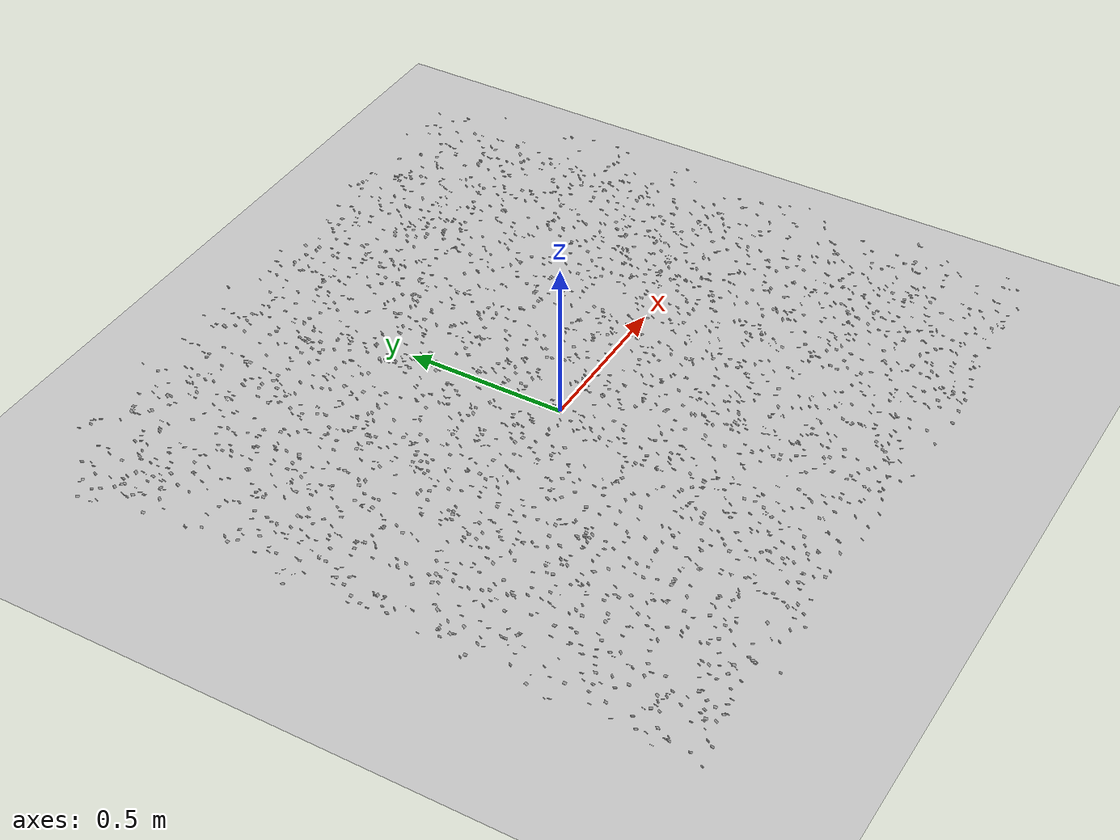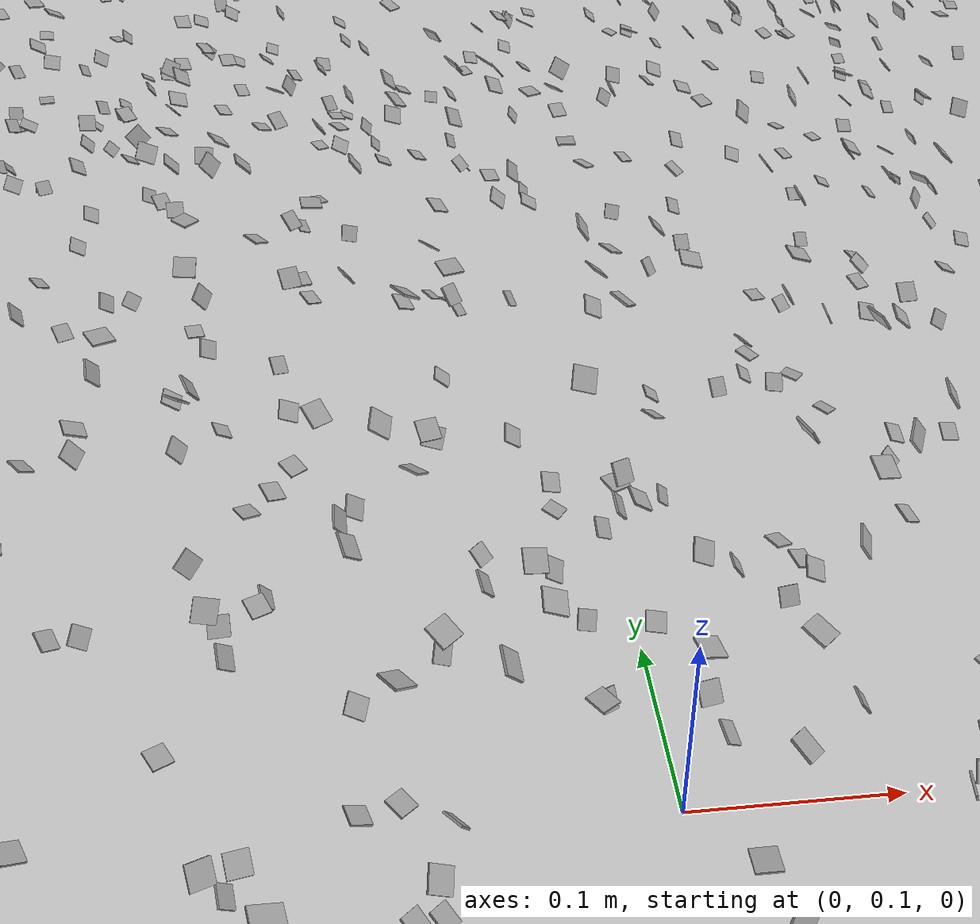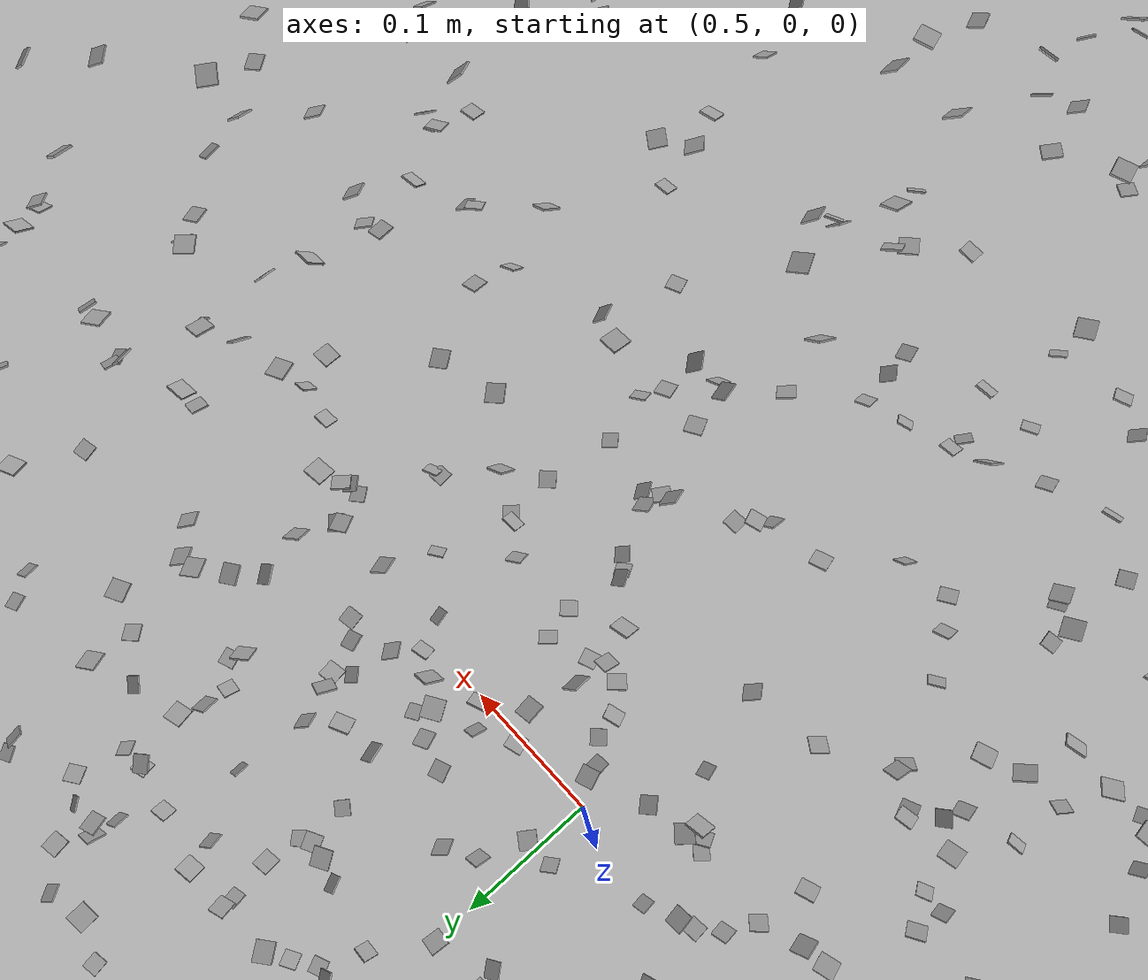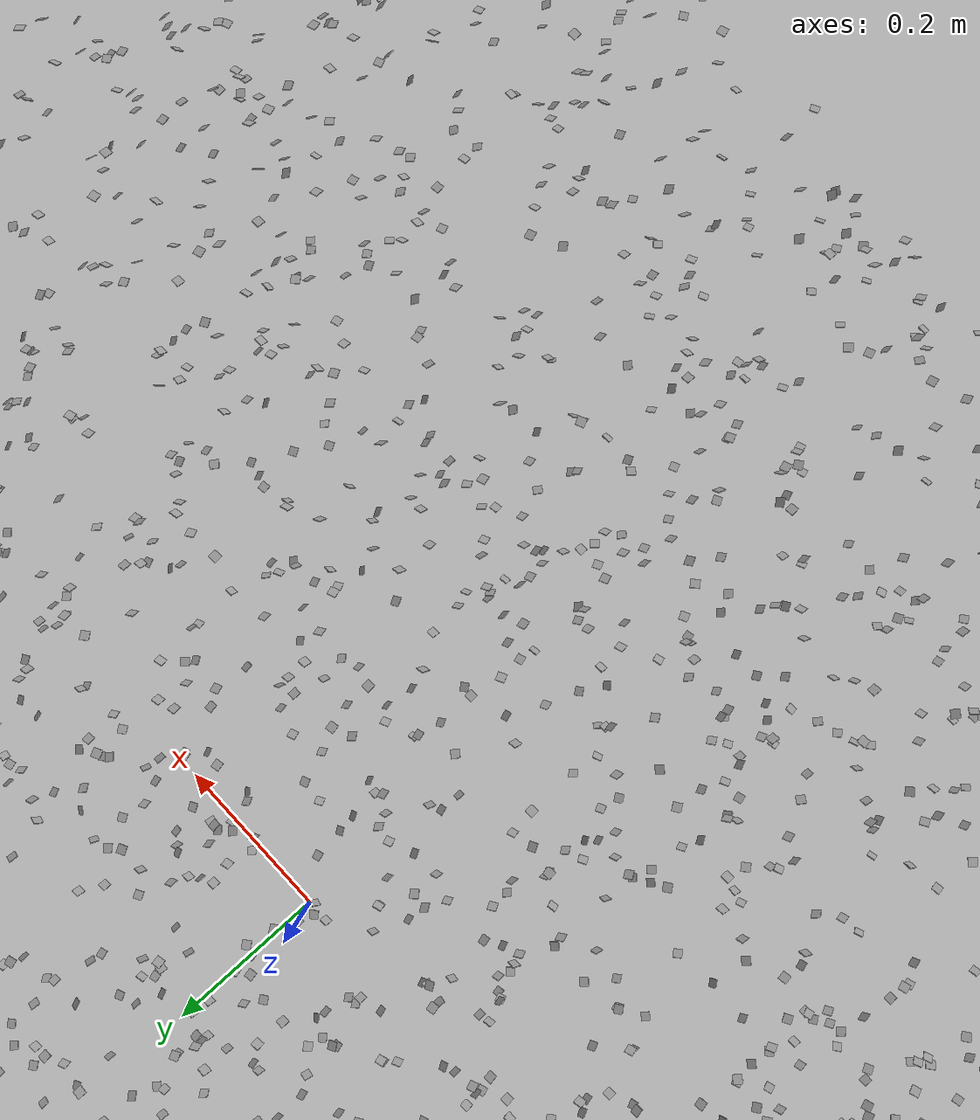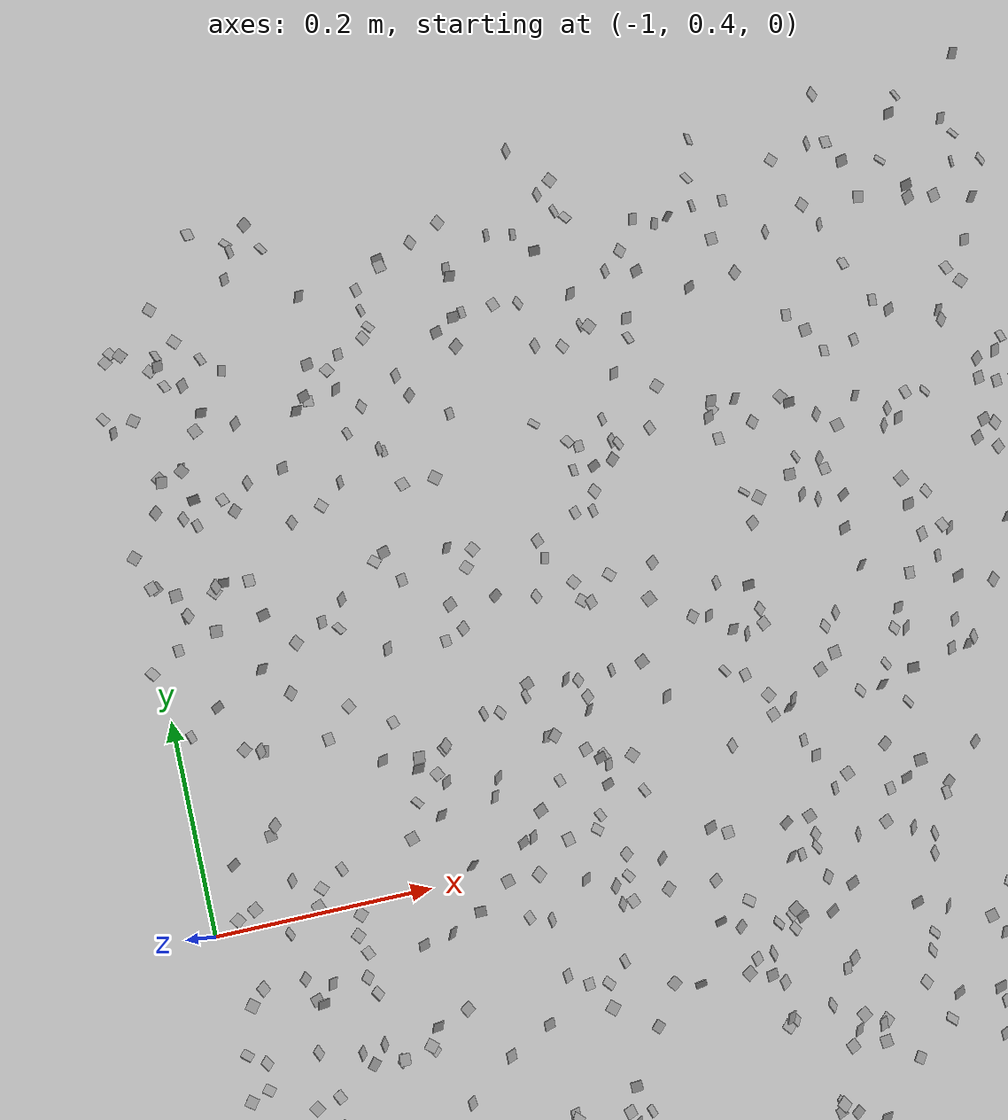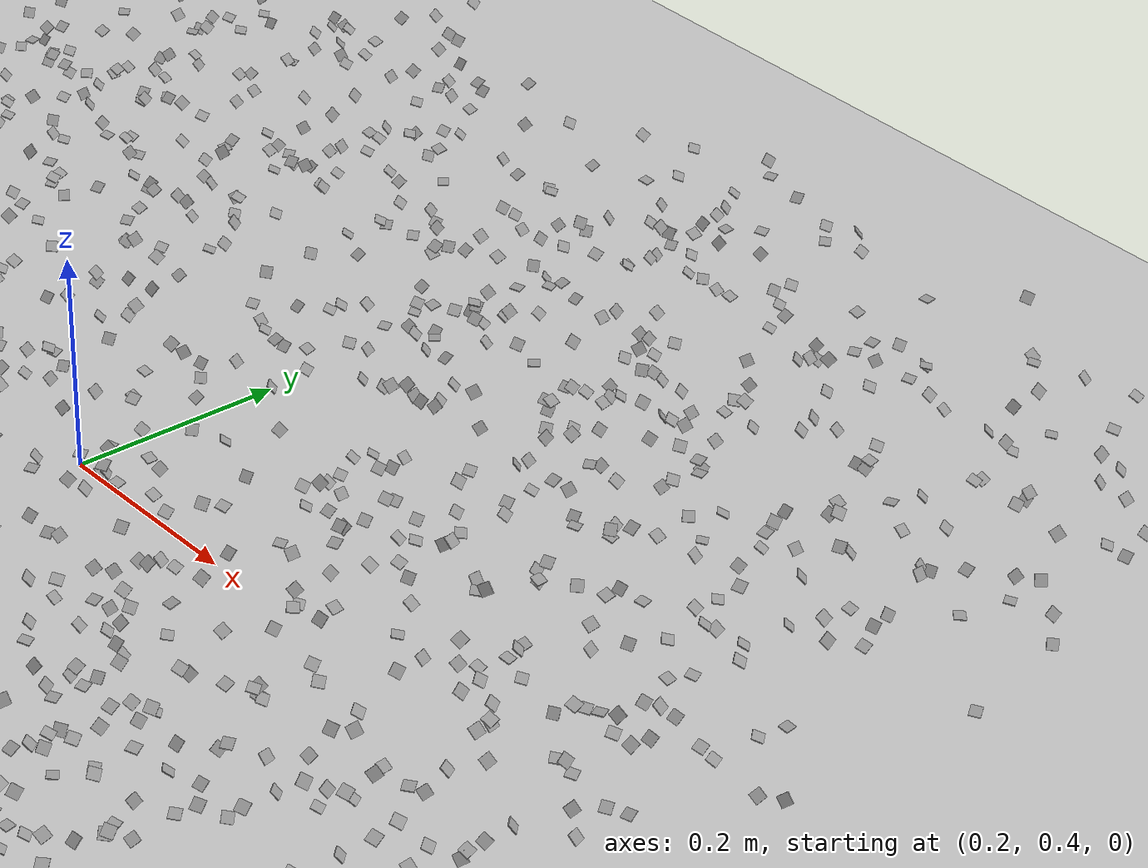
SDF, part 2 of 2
<geometry><box><size>0.01 0.01 0.001</size></box></geometry>
     <max_contacts>0</max_contacts>
     <surface><contact><collide_without_contact>1</collide_without_contact></contact></surface>
    </collision>
    <visual name="visual_1502">
     <pose>-0.136869 0.116738 0.064822 0.50013 0.618792 0.036085</pose>
     <geometry><box><size>0.01 0.01 0.001</size></box></geometry>
     <material>
      <lighting>0</lighting>
      <script><uri>file://media/materials/scripts/gazebo.material</uri><name>Gazebo/Grey</name></script>
     </material>
     <cast_shadows>0</cast_shadows>
    </visual>
    <collision name="collision_1502">
     <pose>-0.136869 0.116738 0.064822 0.50013 0.618792 0.036085</pose>
     <geometry><box><size>0.01 0.01 0.001</size></box></geometry>
     <max_contacts>0</max_contacts>
     <surface><contact><collide_without_contact>1</collide_without_contact></contact></surface>
    </collision>
    <visual name="visual_1503">
     <pose>0.563246 -0.628639 0.144894 0.685846 0.303769 0.603245</pose>
     <geometry><box><size>0.01 0.01 0.001</size></box></geometry>
     <material>
      <lighting>0</lighting>
      <script><uri>file://media/materials/scripts/gazebo.material</uri><name>Gazebo/Grey</name></script>
     </material>
     <cast_shadows>0</cast_shadows>
    </visual>
    <collision name="collision_1503">
     <pose>0.563246 -0.628639 0.144894 0.685846 0.303769 0.603245</pose>
     <geometry><box><size>0.01 0.01 0.001</size></box></geometry>
     <max_contacts>0</max_contacts>
     <surface><contact><collide_without_contact>1</collide_without_contact></contact></surface>
    </collision>
    <visual name="visual_1504">
     <pose>-0.201781 0.883266 0.144337 0.797415 0.729972 0.070769</pose>
     <geometry><box><size>0.01 0.01 0.001</size></box></geometry>
     <material>
      <lighting>0</lighting>
      <script><uri>file://media/materials/scripts/gazebo.material</uri><name>Gazebo/Grey</name></script>
     </material>
     <cast_shadows>0</cast_shadows>
    </visual>
    <collision name="collision_1504">
     <pose>-0.201781 0.883266 0.144337 0.797415 0.729972 0.070769</pose>
     <geometry><box><size>0.01 0.01 0.001</size></box></geometry>
     <max_contacts>0</max_contacts>
     <surface><contact><collide_without_contact>1</collide_without_contact></contact></surface>
    </collision>
    <visual name="visual_1505">
     <pose>-0.877286 0.584237 0.157351 0.772204 0.265725 0.938761</pose>
     <geometry><box><size>0.01 0.01 0.001</size></box></geometry>
     <material>
      <lighting>0</lighting>
      <script><uri>file://media/materials/scripts/gazebo.material</uri><name>Gazebo/Grey</name></script>
     </material>
     <cast_shadows>0</cast_shadows>
    </visual>
    <collision name="collision_1505">
     <pose>-0.877286 0.584237 0.157351 0.772204 0.265725 0.938761</pose>
     <geometry><box><size>0.01 0.01 0.001</size></box></geometry>
     <max_contacts>0</max_contacts>
     <surface><contact><collide_without_contact>1</collide_without_contact></contact></surface>
    </collision>
    <visual name="visual_1506">
     <pose>0.699406 0.846406 0.065215 0.922263 0.623775 0.615205</pose>
     <geometry><box><size>0.01 0.01 0.001</size></box></geometry>
     <material>
      <lighting>0</lighting>
      <script><uri>file://media/materials/scripts/gazebo.material</uri><name>Gazebo/Grey</name></script>
     </material>
     <cast_shadows>0</cast_shadows>
    </visual>
    <collision name="collision_1506">
     <pose>0.699406 0.846406 0.065215 0.922263 0.623775 0.615205</pose>
     <geometry><box><size>0.01 0.01 0.001</size></box></geometry>
     <max_contacts>0</max_contacts>
     <surface><contact><collide_without_contact>1</collide_without_contact></contact></surface>
    </collision>
    <visual name="visual_1507">
     <pose>-0.359397 -0.775991 0.105343 0.079603 0.792999 0.26839</pose>
     <geometry><box><size>0.01 0.01 0.001</size></box></geometry>
     <material>
      <lighting>0</lighting>
      <script><uri>file://media/materials/scripts/gazebo.material</uri><name>Gazebo/Grey</name></script>
     </material>
     <cast_shadows>0</cast_shadows>
    </visual>
    <collision name="collision_1507">
     <pose>-0.359397 -0.775991 0.105343 0.079603 0.792999 0.26839</pose>
     <geometry><box><size>0.01 0.01 0.001</size></box></geometry>
     <max_contacts>0</max_contacts>
     <surface><contact><collide_without_contact>1</collide_without_contact></contact></surface>
    </collision>
    <visual name="visual_1508">
     <pose>0.811335 -0.462282 0.09036 0.848801 0.051724 0.547644</pose>
     <geometry><box><size>0.01 0.01 0.001</size></box></geometry>
     <material>
      <lighting>0</lighting>
      <script><uri>file://media/materials/scripts/gazebo.material</uri><name>Gazebo/Grey</name></script>
     </material>
     <cast_shadows>0</cast_shadows>
    </visual>
    <collision name="collision_1508">
     <pose>0.811335 -0.462282 0.09036 0.848801 0.051724 0.547644</pose>
     <geometry><box><size>0.01 0.01 0.001</size></box></geometry>
     <max_contacts>0</max_contacts>
     <surface><contact><collide_without_contact>1</collide_without_contact></contact></surface>
    </collision>
    <visual name="visual_1509">
     <pose>0.451143 0.796769 0.166058 0.188832 0.588639 0.924886</pose>
     <geometry><box><size>0.01 0.01 0.001</size></box></geometry>
     <material>
      <lighting>0</lighting>
      <script><uri>file://media/materials/scripts/gazebo.material</uri><name>Gazebo/Grey</name></script>
     </material>
     <cast_shadows>0</cast_shadows>
    </visual>
    <collision name="collision_1509">
     <pose>0.451143 0.796769 0.166058 0.188832 0.588639 0.924886</pose>
     <geometry><box><size>0.01 0.01 0.001</size></box></geometry>
     <max_contacts>0</max_contacts>
     <surface><contact><collide_without_contact>1</collide_without_contact></contact></surface>
    </collision>
    <visual name="visual_1510">
     <pose>0.639272 -0.206786 0.149326 0.059777 0.992275 0.26593</pose>
     <geometry><box><size>0.01 0.01 0.001</size></box></geometry>
     <material>
      <lighting>0</lighting>
      <script><uri>file://media/materials/scripts/gazebo.material</uri><name>Gazebo/Grey</name></script>
     </material>
     <cast_shadows>0</cast_shadows>
    </visual>
    <collision name="collision_1510">
     <pose>0.639272 -0.206786 0.149326 0.059777 0.992275 0.26593</pose>
     <geometry><box><size>0.01 0.01 0.001</size></box></geometry>
     <max_contacts>0</max_contacts>
     <surface><contact><collide_without_contact>1</collide_without_contact></contact></surface>
    </collision>
    <visual name="visual_1511">
     <pose>0.308035 -0.76403 0.057485 0.389214 0.364044 0.13149</pose>
     <geometry><box><size>0.01 0.01 0.001</size></box></geometry>
     <material>
      <lighting>0</lighting>
      <script><uri>file://media/materials/scripts/gazebo.material</uri><name>Gazebo/Grey</name></script>
     </material>
     <cast_shadows>0</cast_shadows>
    </visual>
    <collision name="collision_1511">
     <pose>0.308035 -0.76403 0.057485 0.389214 0.364044 0.13149</pose>
     <geometry><box><size>0.01 0.01 0.001</size></box></geometry>
     <max_contacts>0</max_contacts>
     <surface><contact><collide_without_contact>1</collide_without_contact></contact></surface>
    </collision>
    <visual name="visual_1512">
     <pose>-0.764705 0.662697 0.128057 0.365807 0.641495 0.344704</pose>
     <geometry><box><size>0.01 0.01 0.001</size></box></geometry>
     <material>
      <lighting>0</lighting>
      <script><uri>file://media/materials/scripts/gazebo.material</uri><name>Gazebo/Grey</name></script>
     </material>
     <cast_shadows>0</cast_shadows>
    </visual>
    <collision name="collision_1512">
     <pose>-0.764705 0.662697 0.128057 0.365807 0.641495 0.344704</pose>
     <geometry><box><size>0.01 0.01 0.001</size></box></geometry>
     <max_contacts>0</max_contacts>
     <surface><contact><collide_without_contact>1</collide_without_contact></contact></surface>
    </collision>
    <visual name="visual_1513">
     <pose>0.671657 -0.196755 0.056886 0.833852 0.41127 0.540212</pose>
     <geometry><box><size>0.01 0.01 0.001</size></box></geometry>
     <material>
      <lighting>0</lighting>
      <script><uri>file://media/materials/scripts/gazebo.material</uri><name>Gazebo/Grey</name></script>
     </material>
     <cast_shadows>0</cast_shadows>
    </visual>
    <collision name="collision_1513">
     <pose>0.671657 -0.196755 0.056886 0.833852 0.41127 0.540212</pose>
     <geometry><box><size>0.01 0.01 0.001</size></box></geometry>
     <max_contacts>0</max_contacts>
     <surface><contact><collide_without_contact>1</collide_without_contact></contact></surface>
    </collision>
    <visual name="visual_1514">
     <pose>0.413177 -0.898605 0.117713 0.215276 0.80187 0.713982</pose>
     <geometry><box><size>0.01 0.01 0.001</size></box></geometry>
     <material>
      <lighting>0</lighting>
      <script><uri>file://media/materials/scripts/gazebo.material</uri><name>Gazebo/Grey</name></script>
     </material>
     <cast_shadows>0</cast_shadows>
    </visual>
    <collision name="collision_1514">
     <pose>0.413177 -0.898605 0.117713 0.215276 0.80187 0.713982</pose>
     <geometry><box><size>0.01 0.01 0.001</size></box></geometry>
     <max_contacts>0</max_contacts>
     <surface><contact><collide_without_contact>1</collide_without_contact></contact></surface>
    </collision>
    <visual name="visual_1515">
     <pose>-0.559114 0.395056 0.189452 0.736948 0.262774 0.329177</pose>
     <geometry><box><size>0.01 0.01 0.001</size></box></geometry>
     <material>
      <lighting>0</lighting>
      <script><uri>file://media/materials/scripts/gazebo.material</uri><name>Gazebo/Grey</name></script>
     </material>
     <cast_shadows>0</cast_shadows>
    </visual>
    <collision name="collision_1515">
     <pose>-0.559114 0.395056 0.189452 0.736948 0.262774 0.329177</pose>
     <geometry><box><size>0.01 0.01 0.001</size></box></geometry>
     <max_contacts>0</max_contacts>
     <surface><contact><collide_without_contact>1</collide_without_contact></contact></surface>
    </collision>
    <visual name="visual_1516">
     <pose>-0.946881 0.66515 0.177386 0.703793 0.587072 0.907862</pose>
     <geometry><box><size>0.01 0.01 0.001</size></box></geometry>
     <material>
      <lighting>0</lighting>
      <script><uri>file://media/materials/scripts/gazebo.material</uri><name>Gazebo/Grey</name></script>
     </material>
     <cast_shadows>0</cast_shadows>
    </visual>
    <collision name="collision_1516">
     <pose>-0.946881 0.66515 0.177386 0.703793 0.587072 0.907862</pose>
     <geometry><box><size>0.01 0.01 0.001</size></box></geometry>
     <max_contacts>0</max_contacts>
     <surface><contact><collide_without_contact>1</collide_without_contact></contact></surface>
    </collision>
    <visual name="visual_1517">
     <pose>-0.779828 0.039828 0.030906 0.963773 0.500351 0.002344</pose>
     <geometry><box><size>0.01 0.01 0.001</size></box></geometry>
     <material>
      <lighting>0</lighting>
      <script><uri>file://media/materials/scripts/gazebo.material</uri><name>Gazebo/Grey</name></script>
     </material>
     <cast_shadows>0</cast_shadows>
    </visual>
    <collision name="collision_1517">
     <pose>-0.779828 0.039828 0.030906 0.963773 0.500351 0.002344</pose>
     <geometry><box><size>0.01 0.01 0.001</size></box></geometry>
     <max_contacts>0</max_contacts>
     <surface><contact><collide_without_contact>1</collide_without_contact></contact></surface>
    </collision>
    <visual name="visual_1518">
     <pose>0.466903 -0.047612 0.107513 0.869509 0.404374 0.653688</pose>
     <geometry><box><size>0.01 0.01 0.001</size></box></geometry>
     <material>
      <lighting>0</lighting>
      <script><uri>file://media/materials/scripts/gazebo.material</uri><name>Gazebo/Grey</name></script>
     </material>
     <cast_shadows>0</cast_shadows>
    </visual>
    <collision name="collision_1518">
     <pose>0.466903 -0.047612 0.107513 0.869509 0.404374 0.653688</pose>
     <geometry><box><size>0.01 0.01 0.001</size></box></geometry>
     <max_contacts>0</max_contacts>
     <surface><contact><collide_without_contact>1</collide_without_contact></contact></surface>
    </collision>
    <visual name="visual_1519">
     <pose>0.391303 0.950406 0.061328 0.249245 0.736328 0.208983</pose>
     <geometry><box><size>0.01 0.01 0.001</size></box></geometry>
     <material>
      <lighting>0</lighting>
      <script><uri>file://media/materials/scripts/gazebo.material</uri><name>Gazebo/Grey</name></script>
     </material>
     <cast_shadows>0</cast_shadows>
    </visual>
    <collision name="collision_1519">
     <pose>0.391303 0.950406 0.061328 0.249245 0.736328 0.208983</pose>
     <geometry><box><size>0.01 0.01 0.001</size></box></geometry>
     <max_contacts>0</max_contacts>
     <surface><contact><collide_without_contact>1</collide_without_contact></contact></surface>
    </collision>
    <visual name="visual_1520">
     <pose>0.796737 -0.542095 0.130758 0.182219 0.756023 0.41317</pose>
     <geometry><box><size>0.01 0.01 0.001</size></box></geometry>
     <material>
      <lighting>0</lighting>
      <script><uri>file://media/materials/scripts/gazebo.material</uri><name>Gazebo/Grey</name></script>
     </material>
     <cast_shadows>0</cast_shadows>
    </visual>
    <collision name="collision_1520">
     <pose>0.796737 -0.542095 0.130758 0.182219 0.756023 0.41317</pose>
     <geometry><box><size>0.01 0.01 0.001</size></box></geometry>
     <max_contacts>0</max_contacts>
     <surface><contact><collide_without_contact>1</collide_without_contact></contact></surface>
    </collision>
    <visual name="visual_1521">
     <pose>0.969199 -0.752477 0.094431 0.543512 0.091579 0.83094</pose>
     <geometry><box><size>0.01 0.01 0.001</size></box></geometry>
     <material>
      <lighting>0</lighting>
      <script><uri>file://media/materials/scripts/gazebo.material</uri><name>Gazebo/Grey</name></script>
     </material>
     <cast_shadows>0</cast_shadows>
    </visual>
    <collision name="collision_1521">
     <pose>0.969199 -0.752477 0.094431 0.543512 0.091579 0.83094</pose>
     <geometry><box><size>0.01 0.01 0.001</size></box></geometry>
     <max_contacts>0</max_contacts>
     <surface><contact><collide_without_contact>1</collide_without_contact></contact></surface>
    </collision>
    <visual name="visual_1522">
     <pose>-0.93443 -0.634653 0.093305 0.261261 0.376782 0.107677</pose>
     <geometry><box><size>0.01 0.01 0.001</size></box></geometry>
     <material>
      <lighting>0</lighting>
      <script><uri>file://media/materials/scripts/gazebo.material</uri><name>Gazebo/Grey</name></script>
     </material>
     <cast_shadows>0</cast_shadows>
    </visual>
    <collision name="collision_1522">
     <pose>-0.93443 -0.634653 0.093305 0.261261 0.376782 0.107677</pose>
     <geometry><box><size>0.01 0.01 0.001</size></box></geometry>
     <max_contacts>0</max_contacts>
     <surface><contact><collide_without_contact>1</collide_without_contact></contact></surface>
    </collision>
    <visual name="visual_1523">
     <pose>-0.100283 0.618142 0.186842 0.4354 0.067979 0.902424</pose>
     <geometry><box><size>0.01 0.01 0.001</size></box></geometry>
     <material>
      <lighting>0</lighting>
      <script><uri>file://media/materials/scripts/gazebo.material</uri><name>Gazebo/Grey</name></script>
     </material>
     <cast_shadows>0</cast_shadows>
    </visual>
    <collision name="collision_1523">
     <pose>-0.100283 0.618142 0.186842 0.4354 0.067979 0.902424</pose>
     <geometry><box><size>0.01 0.01 0.001</size></box></geometry>
     <max_contacts>0</max_contacts>
     <surface><contact><collide_without_contact>1</collide_without_contact></contact></surface>
    </collision>
    <visual name="visual_1524">
     <pose>0.710475 0.109334 0.036033 0.530535 0.45705 0.022594</pose>
     <geometry><box><size>0.01 0.01 0.001</size></box></geometry>
     <material>
      <lighting>0</lighting>
      <script><uri>file://media/materials/scripts/gazebo.material</uri><name>Gazebo/Grey</name></script>
     </material>
     <cast_shadows>0</cast_shadows>
    </visual>
    <collision name="collision_1524">
     <pose>0.710475 0.109334 0.036033 0.530535 0.45705 0.022594</pose>
     <geometry><box><size>0.01 0.01 0.001</size></box></geometry>
     <max_contacts>0</max_contacts>
     <surface><contact><collide_without_contact>1</collide_without_contact></contact></surface>
    </collision>
    <visual name="visual_1525">
     <pose>-0.346047 0.985411 0.041613 0.209496 0.201925 0.861038</pose>
     <geometry><box><size>0.01 0.01 0.001</size></box></geometry>
     <material>
      <lighting>0</lighting>
      <script><uri>file://media/materials/scripts/gazebo.material</uri><name>Gazebo/Grey</name></script>
     </material>
     <cast_shadows>0</cast_shadows>
    </visual>
    <collision name="collision_1525">
     <pose>-0.346047 0.985411 0.041613 0.209496 0.201925 0.861038</pose>
     <geometry><box><size>0.01 0.01 0.001</size></box></geometry>
     <max_contacts>0</max_contacts>
     <surface><contact><collide_without_contact>1</collide_without_contact></contact></surface>
    </collision>
    <visual name="visual_1526">
     <pose>0.756975 -0.579255 0.05117 0.550222 0.023552 0.320586</pose>
     <geometry><box><size>0.01 0.01 0.001</size></box></geometry>
     <material>
      <lighting>0</lighting>
      <script><uri>file://media/materials/scripts/gazebo.material</uri><name>Gazebo/Grey</name></script>
     </material>
     <cast_shadows>0</cast_shadows>
    </visual>
    <collision name="collision_1526">
     <pose>0.756975 -0.579255 0.05117 0.550222 0.023552 0.320586</pose>
     <geometry><box><size>0.01 0.01 0.001</size></box></geometry>
     <max_contacts>0</max_contacts>
     <surface><contact><collide_without_contact>1</collide_without_contact></contact></surface>
    </collision>
    <visual name="visual_1527">
     <pose>0.991347 0.451383 0.198713 0.327883 0.584923 0.873556</pose>
     <geometry><box><size>0.01 0.01 0.001</size></box></geometry>
     <material>
      <lighting>0</lighting>
      <script><uri>file://media/materials/scripts/gazebo.material</uri><name>Gazebo/Grey</name></script>
     </material>
     <cast_shadows>0</cast_shadows>
    </visual>
    <collision name="collision_1527">
     <pose>0.991347 0.451383 0.198713 0.327883 0.584923 0.873556</pose>
     <geometry><box><size>0.01 0.01 0.001</size></box></geometry>
     <max_contacts>0</max_contacts>
     <surface><contact><collide_without_contact>1</collide_without_contact></contact></surface>
    </collision>
    <visual name="visual_1528">
     <pose>-0.676429 0.837611 0.198464 0.734835 0.108735 0.702253</pose>
     <geometry><box><size>0.01 0.01 0.001</size></box></geometry>
     <material>
      <lighting>0</lighting>
      <script><uri>file://media/materials/scripts/gazebo.material</uri><name>Gazebo/Grey</name></script>
     </material>
     <cast_shadows>0</cast_shadows>
    </visual>
    <collision name="collision_1528">
     <pose>-0.676429 0.837611 0.198464 0.734835 0.108735 0.702253</pose>
     <geometry><box><size>0.01 0.01 0.001</size></box></geometry>
     <max_contacts>0</max_contacts>
     <surface><contact><collide_without_contact>1</collide_without_contact></contact></surface>
    </collision>
    <visual name="visual_1529">
     <pose>-0.804569 0.443501 0.108256 0.202381 0.122238 0.318439</pose>
     <geometry><box><size>0.01 0.01 0.001</size></box></geometry>
     <material>
      <lighting>0</lighting>
      <script><uri>file://media/materials/scripts/gazebo.material</uri><name>Gazebo/Grey</name></script>
     </material>
     <cast_shadows>0</cast_shadows>
    </visual>
    <collision name="collision_1529">
     <pose>-0.804569 0.443501 0.108256 0.202381 0.122238 0.318439</pose>
     <geometry><box><size>0.01 0.01 0.001</size></box></geometry>
     <max_contacts>0</max_contacts>
     <surface><contact><collide_without_contact>1</collide_without_contact></contact></surface>
    </collision>
    <visual name="visual_1530">
     <pose>-0.533294 0.283776 0.195204 0.70063 0.87135 0.908096</pose>
     <geometry><box><size>0.01 0.01 0.001</size></box></geometry>
     <material>
      <lighting>0</lighting>
      <script><uri>file://media/materials/scripts/gazebo.material</uri><name>Gazebo/Grey</name></script>
     </material>
     <cast_shadows>0</cast_shadows>
    </visual>
    <collision name="collision_1530">
     <pose>-0.533294 0.283776 0.195204 0.70063 0.87135 0.908096</pose>
     <geometry><box><size>0.01 0.01 0.001</size></box></geometry>
     <max_contacts>0</max_contacts>
     <surface><contact><collide_without_contact>1</collide_without_contact></contact></surface>
    </collision>
    <visual name="visual_1531">
     <pose>-0.535475 -0.826651 0.068792 0.018618 0.710314 0.439107</pose>
     <geometry><box><size>0.01 0.01 0.001</size></box></geometry>
     <material>
      <lighting>0</lighting>
      <script><uri>file://media/materials/scripts/gazebo.material</uri><name>Gazebo/Grey</name></script>
     </material>
     <cast_shadows>0</cast_shadows>
    </visual>
    <collision name="collision_1531">
     <pose>-0.535475 -0.826651 0.068792 0.018618 0.710314 0.439107</pose>
     <geometry><box><size>0.01 0.01 0.001</size></box></geometry>
     <max_contacts>0</max_contacts>
     <surface><contact><collide_without_contact>1</collide_without_contact></contact></surface>
    </collision>
    <visual name="visual_1532">
     <pose>-0.034875 -0.095509 0.049739 0.889691 0.841909 0.758321</pose>
     <geometry><box><size>0.01 0.01 0.001</size></box></geometry>
     <material>
      <lighting>0</lighting>
      <script><uri>file://media/materials/scripts/gazebo.material</uri><name>Gazebo/Grey</name></script>
     </material>
     <cast_shadows>0</cast_shadows>
    </visual>
    <collision name="collision_1532">
     <pose>-0.034875 -0.095509 0.049739 0.889691 0.841909 0.758321</pose>
     <geometry><box><size>0.01 0.01 0.001</size></box></geometry>
     <max_contacts>0</max_contacts>
     <surface><contact><collide_without_contact>1</collide_without_contact></contact></surface>
    </collision>
    <visual name="visual_1533">
     <pose>0.100351 -0.023817 0.090871 0.941389 0.741568 0.679529</pose>
     <geometry><box><size>0.01 0.01 0.001</size></box></geometry>
     <material>
      <lighting>0</lighting>
      <script><uri>file://media/materials/scripts/gazebo.material</uri><name>Gazebo/Grey</name></script>
     </material>
     <cast_shadows>0</cast_shadows>
    </visual>
    <collision name="collision_1533">
     <pose>0.100351 -0.023817 0.090871 0.941389 0.741568 0.679529</pose>
     <geometry><box><size>0.01 0.01 0.001</size></box></geometry>
     <max_contacts>0</max_contacts>
     <surface><contact><collide_without_contact>1</collide_without_contact></contact></surface>
    </collision>
    <visual name="visual_1534">
     <pose>-0.269974 0.404677 0.095723 0.893774 0.701554 0.710735</pose>
     <geometry><box><size>0.01 0.01 0.001</size></box></geometry>
     <material>
      <lighting>0</lighting>
      <script><uri>file://media/materials/scripts/gazebo.material</uri><name>Gazebo/Grey</name></script>
     </material>
     <cast_shadows>0</cast_shadows>
    </visual>
    <collision name="collision_1534">
     <pose>-0.269974 0.404677 0.095723 0.893774 0.701554 0.710735</pose>
     <geometry><box><size>0.01 0.01 0.001</size></box></geometry>
     <max_contacts>0</max_contacts>
     <surface><contact><collide_without_contact>1</collide_without_contact></contact></surface>
    </collision>
    <visual name="visual_1535">
     <pose>-0.508908 0.918333 0.090065 0.54193 0.161912 0.956965</pose>
     <geometry><box><size>0.01 0.01 0.001</size></box></geometry>
     <material>
      <lighting>0</lighting>
      <script><uri>file://media/materials/scripts/gazebo.material</uri><name>Gazebo/Grey</name></script>
     </material>
     <cast_shadows>0</cast_shadows>
    </visual>
    <collision name="collision_1535">
     <pose>-0.508908 0.918333 0.090065 0.54193 0.161912 0.956965</pose>
     <geometry><box><size>0.01 0.01 0.001</size></box></geometry>
     <max_contacts>0</max_contacts>
     <surface><contact><collide_without_contact>1</collide_without_contact></contact></surface>
    </collision>
    <visual name="visual_1536">
     <pose>-0.604279 -0.349352 0.146893 0.485062 0.114035 0.736024</pose>
     <geometry><box><size>0.01 0.01 0.001</size></box></geometry>
     <material>
      <lighting>0</lighting>
      <script><uri>file://media/materials/scripts/gazebo.material</uri><name>Gazebo/Grey</name></script>
     </material>
     <cast_shadows>0</cast_shadows>
    </visual>
    <collision name="collision_1536">
     <pose>-0.604279 -0.349352 0.146893 0.485062 0.114035 0.736024</pose>
     <geometry><box><size>0.01 0.01 0.001</size></box></geometry>
     <max_contacts>0</max_contacts>
     <surface><contact><collide_without_contact>1</collide_without_contact></contact></surface>
    </collision>
    <visual name="visual_1537">
     <pose>-0.321409 0.248088 0.191262 0.470731 0.388192 0.15806</pose>
     <geometry><box><size>0.01 0.01 0.001</size></box></geometry>
     <material>
      <lighting>0</lighting>
      <script><uri>file://media/materials/scripts/gazebo.material</uri><name>Gazebo/Grey</name></script>
     </material>
     <cast_shadows>0</cast_shadows>
    </visual>
    <collision name="collision_1537">
     <pose>-0.321409 0.248088 0.191262 0.470731 0.388192 0.15806</pose>
     <geometry><box><size>0.01 0.01 0.001</size></box></geometry>
     <max_contacts>0</max_contacts>
     <surface><contact><collide_without_contact>1</collide_without_contact></contact></surface>
    </collision>
    <visual name="visual_1538">
     <pose>0.492862 0.267159 0.105373 0.824425 0.746497 0.582447</pose>
     <geometry><box><size>0.01 0.01 0.001</size></box></geometry>
     <material>
      <lighting>0</lighting>
      <script><uri>file://media/materials/scripts/gazebo.material</uri><name>Gazebo/Grey</name></script>
     </material>
     <cast_shadows>0</cast_shadows>
    </visual>
    <collision name="collision_1538">
     <pose>0.492862 0.267159 0.105373 0.824425 0.746497 0.582447</pose>
     <geometry><box><size>0.01 0.01 0.001</size></box></geometry>
     <max_contacts>0</max_contacts>
     <surface><contact><collide_without_contact>1</collide_without_contact></contact></surface>
    </collision>
    <visual name="visual_1539">
     <pose>-0.27455 -0.72514 0.033763 0.252612 0.491422 0.209191</pose>
     <geometry><box><size>0.01 0.01 0.001</size></box></geometry>
     <material>
      <lighting>0</lighting>
      <script><uri>file://media/materials/scripts/gazebo.material</uri><name>Gazebo/Grey</name></script>
     </material>
     <cast_shadows>0</cast_shadows>
    </visual>
    <collision name="collision_1539">
     <pose>-0.27455 -0.72514 0.033763 0.252612 0.491422 0.209191</pose>
     <geometry><box><size>0.01 0.01 0.001</size></box></geometry>
     <max_contacts>0</max_contacts>
     <surface><contact><collide_without_contact>1</collide_without_contact></contact></surface>
    </collision>
    <visual name="visual_1540">
     <pose>0.400782 0.383126 0.13722 0.855907 0.121349 0.877426</pose>
     <geometry><box><size>0.01 0.01 0.001</size></box></geometry>
     <material>
      <lighting>0</lighting>
      <script><uri>file://media/materials/scripts/gazebo.material</uri><name>Gazebo/Grey</name></script>
     </material>
     <cast_shadows>0</cast_shadows>
    </visual>
    <collision name="collision_1540">
     <pose>0.400782 0.383126 0.13722 0.855907 0.121349 0.877426</pose>
     <geometry><box><size>0.01 0.01 0.001</size></box></geometry>
     <max_contacts>0</max_contacts>
     <surface><contact><collide_without_contact>1</collide_without_contact></contact></surface>
    </collision>
    <visual name="visual_1541">
     <pose>-0.882195 0.845749 0.061202 0.937615 0.461501 0.742599</pose>
     <geometry><box><size>0.01 0.01 0.001</size></box></geometry>
     <material>
      <lighting>0</lighting>
      <script><uri>file://media/materials/scripts/gazebo.material</uri><name>Gazebo/Grey</name></script>
     </material>
     <cast_shadows>0</cast_shadows>
    </visual>
    <collision name="collision_1541">
     <pose>-0.882195 0.845749 0.061202 0.937615 0.461501 0.742599</pose>
     <geometry><box><size>0.01 0.01 0.001</size></box></geometry>
     <max_contacts>0</max_contacts>
     <surface><contact><collide_without_contact>1</collide_without_contact></contact></surface>
    </collision>
    <visual name="visual_1542">
     <pose>0.921154 0.491321 0.054802 0.332359 0.533879 0.475721</pose>
     <geometry><box><size>0.01 0.01 0.001</size></box></geometry>
     <material>
      <lighting>0</lighting>
      <script><uri>file://media/materials/scripts/gazebo.material</uri><name>Gazebo/Grey</name></script>
     </material>
     <cast_shadows>0</cast_shadows>
    </visual>
    <collision name="collision_1542">
     <pose>0.921154 0.491321 0.054802 0.332359 0.533879 0.475721</pose>
     <geometry><box><size>0.01 0.01 0.001</size></box></geometry>
     <max_contacts>0</max_contacts>
     <surface><contact><collide_without_contact>1</collide_without_contact></contact></surface>
    </collision>
    <visual name="visual_1543">
     <pose>-0.522867 0.031462 0.134163 0.949232 0.527825 0.799564</pose>
     <geometry><box><size>0.01 0.01 0.001</size></box></geometry>
     <material>
      <lighting>0</lighting>
      <script><uri>file://media/materials/scripts/gazebo.material</uri><name>Gazebo/Grey</name></script>
     </material>
     <cast_shadows>0</cast_shadows>
    </visual>
    <collision name="collision_1543">
     <pose>-0.522867 0.031462 0.134163 0.949232 0.527825 0.799564</pose>
     <geometry><box><size>0.01 0.01 0.001</size></box></geometry>
     <max_contacts>0</max_contacts>
     <surface><contact><collide_without_contact>1</collide_without_contact></contact></surface>
    </collision>
    <visual name="visual_1544">
     <pose>0.264577 0.227855 0.131623 0.204337 0.107053 0.102973</pose>
     <geometry><box><size>0.01 0.01 0.001</size></box></geometry>
     <material>
      <lighting>0</lighting>
      <script><uri>file://media/materials/scripts/gazebo.material</uri><name>Gazebo/Grey</name></script>
     </material>
     <cast_shadows>0</cast_shadows>
    </visual>
    <collision name="collision_1544">
     <pose>0.264577 0.227855 0.131623 0.204337 0.107053 0.102973</pose>
     <geometry><box><size>0.01 0.01 0.001</size></box></geometry>
     <max_contacts>0</max_contacts>
     <surface><contact><collide_without_contact>1</collide_without_contact></contact></surface>
    </collision>
    <visual name="visual_1545">
     <pose>0.344564 -0.208353 0.16969 0.21574 0.092579 0.106356</pose>
     <geometry><box><size>0.01 0.01 0.001</size></box></geometry>
     <material>
      <lighting>0</lighting>
      <script><uri>file://media/materials/scripts/gazebo.material</uri><name>Gazebo/Grey</name></script>
     </material>
     <cast_shadows>0</cast_shadows>
    </visual>
    <collision name="collision_1545">
     <pose>0.344564 -0.208353 0.16969 0.21574 0.092579 0.106356</pose>
     <geometry><box><size>0.01 0.01 0.001</size></box></geometry>
     <max_contacts>0</max_contacts>
     <surface><contact><collide_without_contact>1</collide_without_contact></contact></surface>
    </collision>
    <visual name="visual_1546">
     <pose>-0.643756 -0.253262 0.18034 0.817631 0.752485 0.805703</pose>
     <geometry><box><size>0.01 0.01 0.001</size></box></geometry>
     <material>
      <lighting>0</lighting>
      <script><uri>file://media/materials/scripts/gazebo.material</uri><name>Gazebo/Grey</name></script>
     </material>
     <cast_shadows>0</cast_shadows>
    </visual>
    <collision name="collision_1546">
     <pose>-0.643756 -0.253262 0.18034 0.817631 0.752485 0.805703</pose>
     <geometry><box><size>0.01 0.01 0.001</size></box></geometry>
     <max_contacts>0</max_contacts>
     <surface><contact><collide_without_contact>1</collide_without_contact></contact></surface>
    </collision>
    <visual name="visual_1547">
     <pose>0.635623 -0.31368 0.157269 0.88515 0.432775 0.621317</pose>
     <geometry><box><size>0.01 0.01 0.001</size></box></geometry>
     <material>
      <lighting>0</lighting>
      <script><uri>file://media/materials/scripts/gazebo.material</uri><name>Gazebo/Grey</name></script>
     </material>
     <cast_shadows>0</cast_shadows>
    </visual>
    <collision name="collision_1547">
     <pose>0.635623 -0.31368 0.157269 0.88515 0.432775 0.621317</pose>
     <geometry><box><size>0.01 0.01 0.001</size></box></geometry>
     <max_contacts>0</max_contacts>
     <surface><contact><collide_without_contact>1</collide_without_contact></contact></surface>
    </collision>
    <visual name="visual_1548">
     <pose>0.660385 -0.646217 0.121572 0.520623 0.128087 0.051018</pose>
     <geometry><box><size>0.01 0.01 0.001</size></box></geometry>
     <material>
      <lighting>0</lighting>
      <script><uri>file://media/materials/scripts/gazebo.material</uri><name>Gazebo/Grey</name></script>
     </material>
     <cast_shadows>0</cast_shadows>
    </visual>
    <collision name="collision_1548">
     <pose>0.660385 -0.646217 0.121572 0.520623 0.128087 0.051018</pose>
     <geometry><box><size>0.01 0.01 0.001</size></box></geometry>
     <max_contacts>0</max_contacts>
     <surface><contact><collide_without_contact>1</collide_without_contact></contact></surface>
    </collision>
    <visual name="visual_1549">
     <pose>0.34157 0.313481 0.11301 0.214955 0.107455 0.645294</pose>
     <geometry><box><size>0.01 0.01 0.001</size></box></geometry>
     <material>
      <lighting>0</lighting>
      <script><uri>file://media/materials/scripts/gazebo.material</uri><name>Gazebo/Grey</name></script>
     </material>
     <cast_shadows>0</cast_shadows>
    </visual>
    <collision name="collision_1549">
     <pose>0.34157 0.313481 0.11301 0.214955 0.107455 0.645294</pose>
     <geometry><box><size>0.01 0.01 0.001</size></box></geometry>
     <max_contacts>0</max_contacts>
     <surface><contact><collide_without_contact>1</collide_without_contact></contact></surface>
    </collision>
    <visual name="visual_1550">
     <pose>0.243936 0.497694 0.070419 0.758184 0.114269 0.932573</pose>
     <geometry><box><size>0.01 0.01 0.001</size></box></geometry>
     <material>
      <lighting>0</lighting>
      <script><uri>file://media/materials/scripts/gazebo.material</uri><name>Gazebo/Grey</name></script>
     </material>
     <cast_shadows>0</cast_shadows>
    </visual>
    <collision name="collision_1550">
     <pose>0.243936 0.497694 0.070419 0.758184 0.114269 0.932573</pose>
     <geometry><box><size>0.01 0.01 0.001</size></box></geometry>
     <max_contacts>0</max_contacts>
     <surface><contact><collide_without_contact>1</collide_without_contact></contact></surface>
    </collision>
    <visual name="visual_1551">
     <pose>0.57867 0.797189 0.081007 0.042096 0.332417 0.198822</pose>
     <geometry><box><size>0.01 0.01 0.001</size></box></geometry>
     <material>
      <lighting>0</lighting>
      <script><uri>file://media/materials/scripts/gazebo.material</uri><name>Gazebo/Grey</name></script>
     </material>
     <cast_shadows>0</cast_shadows>
    </visual>
    <collision name="collision_1551">
     <pose>0.57867 0.797189 0.081007 0.042096 0.332417 0.198822</pose>
     <geometry><box><size>0.01 0.01 0.001</size></box></geometry>
     <max_contacts>0</max_contacts>
     <surface><contact><collide_without_contact>1</collide_without_contact></contact></surface>
    </collision>
    <visual name="visual_1552">
     <pose>0.120321 -0.467813 0.148992 0.178236 0.985923 0.334324</pose>
     <geometry><box><size>0.01 0.01 0.001</size></box></geometry>
     <material>
      <lighting>0</lighting>
      <script><uri>file://media/materials/scripts/gazebo.material</uri><name>Gazebo/Grey</name></script>
     </material>
     <cast_shadows>0</cast_shadows>
    </visual>
    <collision name="collision_1552">
     <pose>0.120321 -0.467813 0.148992 0.178236 0.985923 0.334324</pose>
     <geometry><box><size>0.01 0.01 0.001</size></box></geometry>
     <max_contacts>0</max_contacts>
     <surface><contact><collide_without_contact>1</collide_without_contact></contact></surface>
    </collision>
    <visual name="visual_1553">
     <pose>0.765029 -0.466905 0.1626 0.675768 0.888606 0.739187</pose>
     <geometry><box><size>0.01 0.01 0.001</size></box></geometry>
     <material>
      <lighting>0</lighting>
      <script><uri>file://media/materials/scripts/gazebo.material</uri><name>Gazebo/Grey</name></script>
     </material>
     <cast_shadows>0</cast_shadows>
    </visual>
    <collision name="collision_1553">
     <pose>0.765029 -0.466905 0.1626 0.675768 0.888606 0.739187</pose>
     <geometry><box><size>0.01 0.01 0.001</size></box></geometry>
     <max_contacts>0</max_contacts>
     <surface><contact><collide_without_contact>1</collide_without_contact></contact></surface>
    </collision>
    <visual name="visual_1554">
     <pose>0.416081 -0.159154 0.091977 0.99051 0.188924 0.885172</pose>
     <geometry><box><size>0.01 0.01 0.001</size></box></geometry>
     <material>
      <lighting>0</lighting>
      <script><uri>file://media/materials/scripts/gazebo.material</uri><name>Gazebo/Grey</name></script>
     </material>
     <cast_shadows>0</cast_shadows>
    </visual>
    <collision name="collision_1554">
     <pose>0.416081 -0.159154 0.091977 0.99051 0.188924 0.885172</pose>
     <geometry><box><size>0.01 0.01 0.001</size></box></geometry>
     <max_contacts>0</max_contacts>
     <surface><contact><collide_without_contact>1</collide_without_contact></contact></surface>
    </collision>
    <visual name="visual_1555">
     <pose>-0.790765 0.099005 0.093731 0.713731 0.907832 0.113765</pose>
     <geometry><box><size>0.01 0.01 0.001</size></box></geometry>
     <material>
      <lighting>0</lighting>
      <script><uri>file://media/materials/scripts/gazebo.material</uri><name>Gazebo/Grey</name></script>
     </material>
     <cast_shadows>0</cast_shadows>
    </visual>
    <collision name="collision_1555">
     <pose>-0.790765 0.099005 0.093731 0.713731 0.907832 0.113765</pose>
     <geometry><box><size>0.01 0.01 0.001</size></box></geometry>
     <max_contacts>0</max_contacts>
     <surface><contact><collide_without_contact>1</collide_without_contact></contact></surface>
    </collision>
    <visual name="visual_1556">
     <pose>0.295337 0.372066 0.035011 0.067002 0.972964 0.920108</pose>
     <geometry><box><size>0.01 0.01 0.001</size></box></geometry>
     <material>
      <lighting>0</lighting>
      <script><uri>file://media/materials/scripts/gazebo.material</uri><name>Gazebo/Grey</name></script>
     </material>
     <cast_shadows>0</cast_shadows>
    </visual>
    <collision name="collision_1556">
     <pose>0.295337 0.372066 0.035011 0.067002 0.972964 0.920108</pose>
     <geometry><box><size>0.01 0.01 0.001</size></box></geometry>
     <max_contacts>0</max_contacts>
     <surface><contact><collide_without_contact>1</collide_without_contact></contact></surface>
    </collision>
    <visual name="visual_1557">
     <pose>0.430365 -0.354447 0.158897 0.238573 0.947465 0.795821</pose>
     <geometry><box><size>0.01 0.01 0.001</size></box></geometry>
     <material>
      <lighting>0</lighting>
      <script><uri>file://media/materials/scripts/gazebo.material</uri><name>Gazebo/Grey</name></script>
     </material>
     <cast_shadows>0</cast_shadows>
    </visual>
    <collision name="collision_1557">
     <pose>0.430365 -0.354447 0.158897 0.238573 0.947465 0.795821</pose>
     <geometry><box><size>0.01 0.01 0.001</size></box></geometry>
     <max_contacts>0</max_contacts>
     <surface><contact><collide_without_contact>1</collide_without_contact></contact></surface>
    </collision>
    <visual name="visual_1558">
     <pose>0.404984 0.955808 0.162431 0.046247 0.648316 0.676782</pose>
     <geometry><box><size>0.01 0.01 0.001</size></box></geometry>
     <material>
      <lighting>0</lighting>
      <script><uri>file://media/materials/scripts/gazebo.material</uri><name>Gazebo/Grey</name></script>
     </material>
     <cast_shadows>0</cast_shadows>
    </visual>
    <collision name="collision_1558">
     <pose>0.404984 0.955808 0.162431 0.046247 0.648316 0.676782</pose>
     <geometry><box><size>0.01 0.01 0.001</size></box></geometry>
     <max_contacts>0</max_contacts>
     <surface><contact><collide_without_contact>1</collide_without_contact></contact></surface>
    </collision>
    <visual name="visual_1559">
     <pose>0.920368 0.065818 0.097464 0.420254 0.886342 0.092837</pose>
     <geometry><box><size>0.01 0.01 0.001</size></box></geometry>
     <material>
      <lighting>0</lighting>
      <script><uri>file://media/materials/scripts/gazebo.material</uri><name>Gazebo/Grey</name></script>
     </material>
     <cast_shadows>0</cast_shadows>
    </visual>
    <collision name="collision_1559">
     <pose>0.920368 0.065818 0.097464 0.420254 0.886342 0.092837</pose>
     <geometry><box><size>0.01 0.01 0.001</size></box></geometry>
     <max_contacts>0</max_contacts>
     <surface><contact><collide_without_contact>1</collide_without_contact></contact></surface>
    </collision>
    <visual name="visual_1560">
     <pose>-0.130556 -0.98693 0.0825 0.953154 0.191427 0.980821</pose>
     <geometry><box><size>0.01 0.01 0.001</size></box></geometry>
     <material>
      <lighting>0</lighting>
      <script><uri>file://media/materials/scripts/gazebo.material</uri><name>Gazebo/Grey</name></script>
     </material>
     <cast_shadows>0</cast_shadows>
    </visual>
    <collision name="collision_1560">
     <pose>-0.130556 -0.98693 0.0825 0.953154 0.191427 0.980821</pose>
     <geometry><box><size>0.01 0.01 0.001</size></box></geometry>
     <max_contacts>0</max_contacts>
     <surface><contact><collide_without_contact>1</collide_without_contact></contact></surface>
    </collision>
    <visual name="visual_1561">
     <pose>-0.426244 -0.2918 0.164649 0.185573 0.145977 0.819302</pose>
     <geometry><box><size>0.01 0.01 0.001</size></box></geometry>
     <material>
      <lighting>0</lighting>
      <script><uri>file://media/materials/scripts/gazebo.material</uri><name>Gazebo/Grey</name></script>
     </material>
     <cast_shadows>0</cast_shadows>
    </visual>
    <collision name="collision_1561">
     <pose>-0.426244 -0.2918 0.164649 0.185573 0.145977 0.819302</pose>
     <geometry><box><size>0.01 0.01 0.001</size></box></geometry>
     <max_contacts>0</max_contacts>
     <surface><contact><collide_without_contact>1</collide_without_contact></contact></surface>
    </collision>
    <visual name="visual_1562">
     <pose>0.211584 -0.046638 0.176653 0.567433 0.268679 0.455518</pose>
     <geometry><box><size>0.01 0.01 0.001</size></box></geometry>
     <material>
      <lighting>0</lighting>
      <script><uri>file://media/materials/scripts/gazebo.material</uri><name>Gazebo/Grey</name></script>
     </material>
     <cast_shadows>0</cast_shadows>
    </visual>
    <collision name="collision_1562">
     <pose>0.211584 -0.046638 0.176653 0.567433 0.268679 0.455518</pose>
     <geometry><box><size>0.01 0.01 0.001</size></box></geometry>
     <max_contacts>0</max_contacts>
     <surface><contact><collide_without_contact>1</collide_without_contact></contact></surface>
    </collision>
    <visual name="visual_1563">
     <pose>0.586451 -0.528816 0.184454 0.041368 0.600378 0.789761</pose>
     <geometry><box><size>0.01 0.01 0.001</size></box></geometry>
     <material>
      <lighting>0</lighting>
      <script><uri>file://media/materials/scripts/gazebo.material</uri><name>Gazebo/Grey</name></script>
     </material>
     <cast_shadows>0</cast_shadows>
    </visual>
    <collision name="collision_1563">
     <pose>0.586451 -0.528816 0.184454 0.041368 0.600378 0.789761</pose>
     <geometry><box><size>0.01 0.01 0.001</size></box></geometry>
     <max_contacts>0</max_contacts>
     <surface><contact><collide_without_contact>1</collide_without_contact></contact></surface>
    </collision>
    <visual name="visual_1564">
     <pose>-0.638583 0.657241 0.107624 0.32989 0.819556 0.045054</pose>
     <geometry><box><size>0.01 0.01 0.001</size></box></geometry>
     <material>
      <lighting>0</lighting>
      <script><uri>file://media/materials/scripts/gazebo.material</uri><name>Gazebo/Grey</name></script>
     </material>
     <cast_shadows>0</cast_shadows>
    </visual>
    <collision name="collision_1564">
     <pose>-0.638583 0.657241 0.107624 0.32989 0.819556 0.045054</pose>
     <geometry><box><size>0.01 0.01 0.001</size></box></geometry>
     <max_contacts>0</max_contacts>
     <surface><contact><collide_without_contact>1</collide_without_contact></contact></surface>
    </collision>
    <visual name="visual_1565">
     <pose>-0.924015 0.07299 0.100192 0.420676 0.685468 0.536321</pose>
     <geometry><box><size>0.01 0.01 0.001</size></box></geometry>
     <material>
      <lighting>0</lighting>
      <script><uri>file://media/materials/scripts/gazebo.material</uri><name>Gazebo/Grey</name></script>
     </material>
     <cast_shadows>0</cast_shadows>
    </visual>
    <collision name="collision_1565">
     <pose>-0.924015 0.07299 0.100192 0.420676 0.685468 0.536321</pose>
     <geometry><box><size>0.01 0.01 0.001</size></box></geometry>
     <max_contacts>0</max_contacts>
     <surface><contact><collide_without_contact>1</collide_without_contact></contact></surface>
    </collision>
    <visual name="visual_1566">
     <pose>-0.175258 -0.166205 0.167494 0.925732 0.347315 0.696212</pose>
     <geometry><box><size>0.01 0.01 0.001</size></box></geometry>
     <material>
      <lighting>0</lighting>
      <script><uri>file://media/materials/scripts/gazebo.material</uri><name>Gazebo/Grey</name></script>
     </material>
     <cast_shadows>0</cast_shadows>
    </visual>
    <collision name="collision_1566">
     <pose>-0.175258 -0.166205 0.167494 0.925732 0.347315 0.696212</pose>
     <geometry><box><size>0.01 0.01 0.001</size></box></geometry>
     <max_contacts>0</max_contacts>
     <surface><contact><collide_without_contact>1</collide_without_contact></contact></surface>
    </collision>
    <visual name="visual_1567">
     <pose>-0.064259 -0.14582 0.09224 0.927965 0.656787 0.457487</pose>
     <geometry><box><size>0.01 0.01 0.001</size></box></geometry>
     <material>
      <lighting>0</lighting>
      <script><uri>file://media/materials/scripts/gazebo.material</uri><name>Gazebo/Grey</name></script>
     </material>
     <cast_shadows>0</cast_shadows>
    </visual>
    <collision name="collision_1567">
     <pose>-0.064259 -0.14582 0.09224 0.927965 0.656787 0.457487</pose>
     <geometry><box><size>0.01 0.01 0.001</size></box></geometry>
     <max_contacts>0</max_contacts>
     <surface><contact><collide_without_contact>1</collide_without_contact></contact></surface>
    </collision>
    <visual name="visual_1568">
     <pose>-0.449372 0.680435 0.078588 0.10881 0.955119 0.933165</pose>
     <geometry><box><size>0.01 0.01 0.001</size></box></geometry>
     <material>
      <lighting>0</lighting>
      <script><uri>file://media/materials/scripts/gazebo.material</uri><name>Gazebo/Grey</name></script>
     </material>
     <cast_shadows>0</cast_shadows>
    </visual>
    <collision name="collision_1568">
     <pose>-0.449372 0.680435 0.078588 0.10881 0.955119 0.933165</pose>
     <geometry><box><size>0.01 0.01 0.001</size></box></geometry>
     <max_contacts>0</max_contacts>
     <surface><contact><collide_without_contact>1</collide_without_contact></contact></surface>
    </collision>
    <visual name="visual_1569">
     <pose>0.74757 -0.787681 0.056331 0.512053 0.950347 0.985077</pose>
     <geometry><box><size>0.01 0.01 0.001</size></box></geometry>
     <material>
      <lighting>0</lighting>
      <script><uri>file://media/materials/scripts/gazebo.material</uri><name>Gazebo/Grey</name></script>
     </material>
     <cast_shadows>0</cast_shadows>
    </visual>
    <collision name="collision_1569">
     <pose>0.74757 -0.787681 0.056331 0.512053 0.950347 0.985077</pose>
     <geometry><box><size>0.01 0.01 0.001</size></box></geometry>
     <max_contacts>0</max_contacts>
     <surface><contact><collide_without_contact>1</collide_without_contact></contact></surface>
    </collision>
    <visual name="visual_1570">
     <pose>0.047355 -0.131777 0.155881 0.128602 0.9672 0.60941</pose>
     <geometry><box><size>0.01 0.01 0.001</size></box></geometry>
     <material>
      <lighting>0</lighting>
      <script><uri>file://media/materials/scripts/gazebo.material</uri><name>Gazebo/Grey</name></script>
     </material>
     <cast_shadows>0</cast_shadows>
    </visual>
    <collision name="collision_1570">
     <pose>0.047355 -0.131777 0.155881 0.128602 0.9672 0.60941</pose>
     <geometry><box><size>0.01 0.01 0.001</size></box></geometry>
     <max_contacts>0</max_contacts>
     <surface><contact><collide_without_contact>1</collide_without_contact></contact></surface>
    </collision>
    <visual name="visual_1571">
     <pose>0.067638 0.189904 0.03779 0.990547 0.055175 0.214676</pose>
     <geometry><box><size>0.01 0.01 0.001</size></box></geometry>
     <material>
      <lighting>0</lighting>
      <script><uri>file://media/materials/scripts/gazebo.material</uri><name>Gazebo/Grey</name></script>
     </material>
     <cast_shadows>0</cast_shadows>
    </visual>
    <collision name="collision_1571">
     <pose>0.067638 0.189904 0.03779 0.990547 0.055175 0.214676</pose>
     <geometry><box><size>0.01 0.01 0.001</size></box></geometry>
     <max_contacts>0</max_contacts>
     <surface><contact><collide_without_contact>1</collide_without_contact></contact></surface>
    </collision>
    <visual name="visual_1572">
     <pose>-0.146875 -0.233526 0.08627 0.785965 0.646264 0.555169</pose>
     <geometry><box><size>0.01 0.01 0.001</size></box></geometry>
     <material>
      <lighting>0</lighting>
      <script><uri>file://media/materials/scripts/gazebo.material</uri><name>Gazebo/Grey</name></script>
     </material>
     <cast_shadows>0</cast_shadows>
    </visual>
    <collision name="collision_1572">
     <pose>-0.146875 -0.233526 0.08627 0.785965 0.646264 0.555169</pose>
     <geometry><box><size>0.01 0.01 0.001</size></box></geometry>
     <max_contacts>0</max_contacts>
     <surface><contact><collide_without_contact>1</collide_without_contact></contact></surface>
    </collision>
    <visual name="visual_1573">
     <pose>0.972884 0.223995 0.040816 0.71653 0.627294 0.298222</pose>
     <geometry><box><size>0.01 0.01 0.001</size></box></geometry>
     <material>
      <lighting>0</lighting>
      <script><uri>file://media/materials/scripts/gazebo.material</uri><name>Gazebo/Grey</name></script>
     </material>
     <cast_shadows>0</cast_shadows>
    </visual>
    <collision name="collision_1573">
     <pose>0.972884 0.223995 0.040816 0.71653 0.627294 0.298222</pose>
     <geometry><box><size>0.01 0.01 0.001</size></box></geometry>
     <max_contacts>0</max_contacts>
     <surface><contact><collide_without_contact>1</collide_without_contact></contact></surface>
    </collision>
    <visual name="visual_1574">
     <pose>0.321983 -0.122114 0.058729 0.663333 0.911861 0.506562</pose>
     <geometry><box><size>0.01 0.01 0.001</size></box></geometry>
     <material>
      <lighting>0</lighting>
      <script><uri>file://media/materials/scripts/gazebo.material</uri><name>Gazebo/Grey</name></script>
     </material>
     <cast_shadows>0</cast_shadows>
    </visual>
    <collision name="collision_1574">
     <pose>0.321983 -0.122114 0.058729 0.663333 0.911861 0.506562</pose>
     <geometry><box><size>0.01 0.01 0.001</size></box></geometry>
     <max_contacts>0</max_contacts>
     <surface><contact><collide_without_contact>1</collide_without_contact></contact></surface>
    </collision>
    <visual name="visual_1575">
     <pose>0.431876 0.506643 0.042767 0.152735 0.855325 0.014399</pose>
     <geometry><box><size>0.01 0.01 0.001</size></box></geometry>
     <material>
      <lighting>0</lighting>
      <script><uri>file://media/materials/scripts/gazebo.material</uri><name>Gazebo/Grey</name></script>
     </material>
     <cast_shadows>0</cast_shadows>
    </visual>
    <collision name="collision_1575">
     <pose>0.431876 0.506643 0.042767 0.152735 0.855325 0.014399</pose>
     <geometry><box><size>0.01 0.01 0.001</size></box></geometry>
     <max_contacts>0</max_contacts>
     <surface><contact><collide_without_contact>1</collide_without_contact></contact></surface>
    </collision>
    <visual name="visual_1576">
     <pose>0.90826 -0.747345 0.091817 0.527972 0.854335 0.641693</pose>
     <geometry><box><size>0.01 0.01 0.001</size></box></geometry>
     <material>
      <lighting>0</lighting>
      <script><uri>file://media/materials/scripts/gazebo.material</uri><name>Gazebo/Grey</name></script>
     </material>
     <cast_shadows>0</cast_shadows>
    </visual>
    <collision name="collision_1576">
     <pose>0.90826 -0.747345 0.091817 0.527972 0.854335 0.641693</pose>
     <geometry><box><size>0.01 0.01 0.001</size></box></geometry>
     <max_contacts>0</max_contacts>
     <surface><contact><collide_without_contact>1</collide_without_contact></contact></surface>
    </collision>
    <visual name="visual_1577">
     <pose>0.480121 0.526175 0.052075 0.587639 0.212532 0.517519</pose>
     <geometry><box><size>0.01 0.01 0.001</size></box></geometry>
     <material>
      <lighting>0</lighting>
      <script><uri>file://media/materials/scripts/gazebo.material</uri><name>Gazebo/Grey</name></script>
     </material>
     <cast_shadows>0</cast_shadows>
    </visual>
    <collision name="collision_1577">
     <pose>0.480121 0.526175 0.052075 0.587639 0.212532 0.517519</pose>
     <geometry><box><size>0.01 0.01 0.001</size></box></geometry>
     <max_contacts>0</max_contacts>
     <surface><contact><collide_without_contact>1</collide_without_contact></contact></surface>
    </collision>
    <visual name="visual_1578">
     <pose>-0.945206 -0.320925 0.101097 0.477685 0.905325 0.120303</pose>
     <geometry><box><size>0.01 0.01 0.001</size></box></geometry>
     <material>
      <lighting>0</lighting>
      <script><uri>file://media/materials/scripts/gazebo.material</uri><name>Gazebo/Grey</name></script>
     </material>
     <cast_shadows>0</cast_shadows>
    </visual>
    <collision name="collision_1578">
     <pose>-0.945206 -0.320925 0.101097 0.477685 0.905325 0.120303</pose>
     <geometry><box><size>0.01 0.01 0.001</size></box></geometry>
     <max_contacts>0</max_contacts>
     <surface><contact><collide_without_contact>1</collide_without_contact></contact></surface>
    </collision>
    <visual name="visual_1579">
     <pose>-0.810436 -0.884608 0.054691 0.019927 0.310124 0.761574</pose>
     <geometry><box><size>0.01 0.01 0.001</size></box></geometry>
     <material>
      <lighting>0</lighting>
      <script><uri>file://media/materials/scripts/gazebo.material</uri><name>Gazebo/Grey</name></script>
     </material>
     <cast_shadows>0</cast_shadows>
    </visual>
    <collision name="collision_1579">
     <pose>-0.810436 -0.884608 0.054691 0.019927 0.310124 0.761574</pose>
     <geometry><box><size>0.01 0.01 0.001</size></box></geometry>
     <max_contacts>0</max_contacts>
     <surface><contact><collide_without_contact>1</collide_without_contact></contact></surface>
    </collision>
    <visual name="visual_1580">
     <pose>0.888696 0.015517 0.079213 0.307387 0.566239 0.645525</pose>
     <geometry><box><size>0.01 0.01 0.001</size></box></geometry>
     <material>
      <lighting>0</lighting>
      <script><uri>file://media/materials/scripts/gazebo.material</uri><name>Gazebo/Grey</name></script>
     </material>
     <cast_shadows>0</cast_shadows>
    </visual>
    <collision name="collision_1580">
     <pose>0.888696 0.015517 0.079213 0.307387 0.566239 0.645525</pose>
     <geometry><box><size>0.01 0.01 0.001</size></box></geometry>
     <max_contacts>0</max_contacts>
     <surface><contact><collide_without_contact>1</collide_without_contact></contact></surface>
    </collision>
    <visual name="visual_1581">
     <pose>-0.415092 0.87164 0.106108 0.658891 0.16303 0.786601</pose>
     <geometry><box><size>0.01 0.01 0.001</size></box></geometry>
     <material>
      <lighting>0</lighting>
      <script><uri>file://media/materials/scripts/gazebo.material</uri><name>Gazebo/Grey</name></script>
     </material>
     <cast_shadows>0</cast_shadows>
    </visual>
    <collision name="collision_1581">
     <pose>-0.415092 0.87164 0.106108 0.658891 0.16303 0.786601</pose>
     <geometry><box><size>0.01 0.01 0.001</size></box></geometry>
     <max_contacts>0</max_contacts>
     <surface><contact><collide_without_contact>1</collide_without_contact></contact></surface>
    </collision>
    <visual name="visual_1582">
     <pose>0.850926 0.529759 0.185232 0.164832 0.873613 0.414837</pose>
     <geometry><box><size>0.01 0.01 0.001</size></box></geometry>
     <material>
      <lighting>0</lighting>
      <script><uri>file://media/materials/scripts/gazebo.material</uri><name>Gazebo/Grey</name></script>
     </material>
     <cast_shadows>0</cast_shadows>
    </visual>
    <collision name="collision_1582">
     <pose>0.850926 0.529759 0.185232 0.164832 0.873613 0.414837</pose>
     <geometry><box><size>0.01 0.01 0.001</size></box></geometry>
     <max_contacts>0</max_contacts>
     <surface><contact><collide_without_contact>1</collide_without_contact></contact></surface>
    </collision>
    <visual name="visual_1583">
     <pose>-0.881051 0.992948 0.169112 0.019208 0.561055 0.247095</pose>
     <geometry><box><size>0.01 0.01 0.001</size></box></geometry>
     <material>
      <lighting>0</lighting>
      <script><uri>file://media/materials/scripts/gazebo.material</uri><name>Gazebo/Grey</name></script>
     </material>
     <cast_shadows>0</cast_shadows>
    </visual>
    <collision name="collision_1583">
     <pose>-0.881051 0.992948 0.169112 0.019208 0.561055 0.247095</pose>
     <geometry><box><size>0.01 0.01 0.001</size></box></geometry>
     <max_contacts>0</max_contacts>
     <surface><contact><collide_without_contact>1</collide_without_contact></contact></surface>
    </collision>
    <visual name="visual_1584">
     <pose>-0.076772 0.221614 0.050162 0.784379 0.098915 0.880767</pose>
     <geometry><box><size>0.01 0.01 0.001</size></box></geometry>
     <material>
      <lighting>0</lighting>
      <script><uri>file://media/materials/scripts/gazebo.material</uri><name>Gazebo/Grey</name></script>
     </material>
     <cast_shadows>0</cast_shadows>
    </visual>
    <collision name="collision_1584">
     <pose>-0.076772 0.221614 0.050162 0.784379 0.098915 0.880767</pose>
     <geometry><box><size>0.01 0.01 0.001</size></box></geometry>
     <max_contacts>0</max_contacts>
     <surface><contact><collide_without_contact>1</collide_without_contact></contact></surface>
    </collision>
    <visual name="visual_1585">
     <pose>0.688561 0.180335 0.141578 0.99466 0.677019 0.464238</pose>
     <geometry><box><size>0.01 0.01 0.001</size></box></geometry>
     <material>
      <lighting>0</lighting>
      <script><uri>file://media/materials/scripts/gazebo.material</uri><name>Gazebo/Grey</name></script>
     </material>
     <cast_shadows>0</cast_shadows>
    </visual>
    <collision name="collision_1585">
     <pose>0.688561 0.180335 0.141578 0.99466 0.677019 0.464238</pose>
     <geometry><box><size>0.01 0.01 0.001</size></box></geometry>
     <max_contacts>0</max_contacts>
     <surface><contact><collide_without_contact>1</collide_without_contact></contact></surface>
    </collision>
    <visual name="visual_1586">
     <pose>0.36414 0.796146 0.110657 0.308627 0.089983 0.006969</pose>
     <geometry><box><size>0.01 0.01 0.001</size></box></geometry>
     <material>
      <lighting>0</lighting>
      <script><uri>file://media/materials/scripts/gazebo.material</uri><name>Gazebo/Grey</name></script>
     </material>
     <cast_shadows>0</cast_shadows>
    </visual>
    <collision name="collision_1586">
     <pose>0.36414 0.796146 0.110657 0.308627 0.089983 0.006969</pose>
     <geometry><box><size>0.01 0.01 0.001</size></box></geometry>
     <max_contacts>0</max_contacts>
     <surface><contact><collide_without_contact>1</collide_without_contact></contact></surface>
    </collision>
    <visual name="visual_1587">
     <pose>0.562264 -0.906285 0.107098 0.671246 0.256964 0.675154</pose>
     <geometry><box><size>0.01 0.01 0.001</size></box></geometry>
     <material>
      <lighting>0</lighting>
      <script><uri>file://media/materials/scripts/gazebo.material</uri><name>Gazebo/Grey</name></script>
     </material>
     <cast_shadows>0</cast_shadows>
    </visual>
    <collision name="collision_1587">
     <pose>0.562264 -0.906285 0.107098 0.671246 0.256964 0.675154</pose>
     <geometry><box><size>0.01 0.01 0.001</size></box></geometry>
     <max_contacts>0</max_contacts>
     <surface><contact><collide_without_contact>1</collide_without_contact></contact></surface>
    </collision>
    <visual name="visual_1588">
     <pose>-0.021502 0.202964 0.07724 0.739809 0.591474 0.534657</pose>
     <geometry><box><size>0.01 0.01 0.001</size></box></geometry>
     <material>
      <lighting>0</lighting>
      <script><uri>file://media/materials/scripts/gazebo.material</uri><name>Gazebo/Grey</name></script>
     </material>
     <cast_shadows>0</cast_shadows>
    </visual>
    <collision name="collision_1588">
     <pose>-0.021502 0.202964 0.07724 0.739809 0.591474 0.534657</pose>
     <geometry><box><size>0.01 0.01 0.001</size></box></geometry>
     <max_contacts>0</max_contacts>
     <surface><contact><collide_without_contact>1</collide_without_contact></contact></surface>
    </collision>
    <visual name="visual_1589">
     <pose>-0.721628 0.528979 0.181197 0.621077 0.935669 0.804795</pose>
     <geometry><box><size>0.01 0.01 0.001</size></box></geometry>
     <material>
      <lighting>0</lighting>
      <script><uri>file://media/materials/scripts/gazebo.material</uri><name>Gazebo/Grey</name></script>
     </material>
     <cast_shadows>0</cast_shadows>
    </visual>
    <collision name="collision_1589">
     <pose>-0.721628 0.528979 0.181197 0.621077 0.935669 0.804795</pose>
     <geometry><box><size>0.01 0.01 0.001</size></box></geometry>
     <max_contacts>0</max_contacts>
     <surface><contact><collide_without_contact>1</collide_without_contact></contact></surface>
    </collision>
    <visual name="visual_1590">
     <pose>0.931728 -0.678694 0.143522 0.538529 0.824195 0.600446</pose>
     <geometry><box><size>0.01 0.01 0.001</size></box></geometry>
     <material>
      <lighting>0</lighting>
      <script><uri>file://media/materials/scripts/gazebo.material</uri><name>Gazebo/Grey</name></script>
     </material>
     <cast_shadows>0</cast_shadows>
    </visual>
    <collision name="collision_1590">
     <pose>0.931728 -0.678694 0.143522 0.538529 0.824195 0.600446</pose>
     <geometry><box><size>0.01 0.01 0.001</size></box></geometry>
     <max_contacts>0</max_contacts>
     <surface><contact><collide_without_contact>1</collide_without_contact></contact></surface>
    </collision>
    <visual name="visual_1591">
     <pose>-0.246942 0.985558 0.152015 0.227857 0.862894 0.661951</pose>
     <geometry><box><size>0.01 0.01 0.001</size></box></geometry>
     <material>
      <lighting>0</lighting>
      <script><uri>file://media/materials/scripts/gazebo.material</uri><name>Gazebo/Grey</name></script>
     </material>
     <cast_shadows>0</cast_shadows>
    </visual>
    <collision name="collision_1591">
     <pose>-0.246942 0.985558 0.152015 0.227857 0.862894 0.661951</pose>
     <geometry><box><size>0.01 0.01 0.001</size></box></geometry>
     <max_contacts>0</max_contacts>
     <surface><contact><collide_without_contact>1</collide_without_contact></contact></surface>
    </collision>
    <visual name="visual_1592">
     <pose>0.819968 -0.841115 0.106172 0.644199 0.240058 0.968619</pose>
     <geometry><box><size>0.01 0.01 0.001</size></box></geometry>
     <material>
      <lighting>0</lighting>
      <script><uri>file://media/materials/scripts/gazebo.material</uri><name>Gazebo/Grey</name></script>
     </material>
     <cast_shadows>0</cast_shadows>
    </visual>
    <collision name="collision_1592">
     <pose>0.819968 -0.841115 0.106172 0.644199 0.240058 0.968619</pose>
     <geometry><box><size>0.01 0.01 0.001</size></box></geometry>
     <max_contacts>0</max_contacts>
     <surface><contact><collide_without_contact>1</collide_without_contact></contact></surface>
    </collision>
    <visual name="visual_1593">
     <pose>0.328221 -0.44632 0.124837 0.965876 0.124769 0.244868</pose>
     <geometry><box><size>0.01 0.01 0.001</size></box></geometry>
     <material>
      <lighting>0</lighting>
      <script><uri>file://media/materials/scripts/gazebo.material</uri><name>Gazebo/Grey</name></script>
     </material>
     <cast_shadows>0</cast_shadows>
    </visual>
    <collision name="collision_1593">
     <pose>0.328221 -0.44632 0.124837 0.965876 0.124769 0.244868</pose>
     <geometry><box><size>0.01 0.01 0.001</size></box></geometry>
     <max_contacts>0</max_contacts>
     <surface><contact><collide_without_contact>1</collide_without_contact></contact></surface>
    </collision>
    <visual name="visual_1594">
     <pose>0.59251 0.594357 0.140131 0.933285 0.930239 0.853505</pose>
     <geometry><box><size>0.01 0.01 0.001</size></box></geometry>
     <material>
      <lighting>0</lighting>
      <script><uri>file://media/materials/scripts/gazebo.material</uri><name>Gazebo/Grey</name></script>
     </material>
     <cast_shadows>0</cast_shadows>
    </visual>
    <collision name="collision_1594">
     <pose>0.59251 0.594357 0.140131 0.933285 0.930239 0.853505</pose>
     <geometry><box><size>0.01 0.01 0.001</size></box></geometry>
     <max_contacts>0</max_contacts>
     <surface><contact><collide_without_contact>1</collide_without_contact></contact></surface>
    </collision>
    <visual name="visual_1595">
     <pose>0.710391 0.501147 0.119368 0.636733 0.175007 0.559063</pose>
     <geometry><box><size>0.01 0.01 0.001</size></box></geometry>
     <material>
      <lighting>0</lighting>
      <script><uri>file://media/materials/scripts/gazebo.material</uri><name>Gazebo/Grey</name></script>
     </material>
     <cast_shadows>0</cast_shadows>
    </visual>
    <collision name="collision_1595">
     <pose>0.710391 0.501147 0.119368 0.636733 0.175007 0.559063</pose>
     <geometry><box><size>0.01 0.01 0.001</size></box></geometry>
     <max_contacts>0</max_contacts>
     <surface><contact><collide_without_contact>1</collide_without_contact></contact></surface>
    </collision>
    <visual name="visual_1596">
     <pose>0.715714 0.351675 0.117989 0.124503 0.230485 0.892869</pose>
     <geometry><box><size>0.01 0.01 0.001</size></box></geometry>
     <material>
      <lighting>0</lighting>
      <script><uri>file://media/materials/scripts/gazebo.material</uri><name>Gazebo/Grey</name></script>
     </material>
     <cast_shadows>0</cast_shadows>
    </visual>
    <collision name="collision_1596">
     <pose>0.715714 0.351675 0.117989 0.124503 0.230485 0.892869</pose>
     <geometry><box><size>0.01 0.01 0.001</size></box></geometry>
     <max_contacts>0</max_contacts>
     <surface><contact><collide_without_contact>1</collide_without_contact></contact></surface>
    </collision>
    <visual name="visual_1597">
     <pose>-0.912409 0.86904 0.034612 0.905426 0.38656 0.01835</pose>
     <geometry><box><size>0.01 0.01 0.001</size></box></geometry>
     <material>
      <lighting>0</lighting>
      <script><uri>file://media/materials/scripts/gazebo.material</uri><name>Gazebo/Grey</name></script>
     </material>
     <cast_shadows>0</cast_shadows>
    </visual>
    <collision name="collision_1597">
     <pose>-0.912409 0.86904 0.034612 0.905426 0.38656 0.01835</pose>
     <geometry><box><size>0.01 0.01 0.001</size></box></geometry>
     <max_contacts>0</max_contacts>
     <surface><contact><collide_without_contact>1</collide_without_contact></contact></surface>
    </collision>
    <visual name="visual_1598">
     <pose>-0.679465 0.548846 0.144439 0.546967 0.226283 0.459878</pose>
     <geometry><box><size>0.01 0.01 0.001</size></box></geometry>
     <material>
      <lighting>0</lighting>
      <script><uri>file://media/materials/scripts/gazebo.material</uri><name>Gazebo/Grey</name></script>
     </material>
     <cast_shadows>0</cast_shadows>
    </visual>
    <collision name="collision_1598">
     <pose>-0.679465 0.548846 0.144439 0.546967 0.226283 0.459878</pose>
     <geometry><box><size>0.01 0.01 0.001</size></box></geometry>
     <max_contacts>0</max_contacts>
     <surface><contact><collide_without_contact>1</collide_without_contact></contact></surface>
    </collision>
    <visual name="visual_1599">
     <pose>-0.406916 -0.064017 0.100663 0.383099 0.664845 0.982019</pose>
     <geometry><box><size>0.01 0.01 0.001</size></box></geometry>
     <material>
      <lighting>0</lighting>
      <script><uri>file://media/materials/scripts/gazebo.material</uri><name>Gazebo/Grey</name></script>
     </material>
     <cast_shadows>0</cast_shadows>
    </visual>
    <collision name="collision_1599">
     <pose>-0.406916 -0.064017 0.100663 0.383099 0.664845 0.982019</pose>
     <geometry><box><size>0.01 0.01 0.001</size></box></geometry>
     <max_contacts>0</max_contacts>
     <surface><contact><collide_without_contact>1</collide_without_contact></contact></surface>
    </collision>
    <visual name="visual_1600">
     <pose>0.985582 -0.931245 0.148752 0.436475 0.128597 0.6973</pose>
     <geometry><box><size>0.01 0.01 0.001</size></box></geometry>
     <material>
      <lighting>0</lighting>
      <script><uri>file://media/materials/scripts/gazebo.material</uri><name>Gazebo/Grey</name></script>
     </material>
     <cast_shadows>0</cast_shadows>
    </visual>
    <collision name="collision_1600">
     <pose>0.985582 -0.931245 0.148752 0.436475 0.128597 0.6973</pose>
     <geometry><box><size>0.01 0.01 0.001</size></box></geometry>
     <max_contacts>0</max_contacts>
     <surface><contact><collide_without_contact>1</collide_without_contact></contact></surface>
    </collision>
    <visual name="visual_1601">
     <pose>-0.585737 -0.794313 0.165589 0.075888 0.288144 0.460263</pose>
     <geometry><box><size>0.01 0.01 0.001</size></box></geometry>
     <material>
      <lighting>0</lighting>
      <script><uri>file://media/materials/scripts/gazebo.material</uri><name>Gazebo/Grey</name></script>
     </material>
     <cast_shadows>0</cast_shadows>
    </visual>
    <collision name="collision_1601">
     <pose>-0.585737 -0.794313 0.165589 0.075888 0.288144 0.460263</pose>
     <geometry><box><size>0.01 0.01 0.001</size></box></geometry>
     <max_contacts>0</max_contacts>
     <surface><contact><collide_without_contact>1</collide_without_contact></contact></surface>
    </collision>
    <visual name="visual_1602">
     <pose>-0.551422 -0.454374 0.167911 0.414467 0.315506 0.724463</pose>
     <geometry><box><size>0.01 0.01 0.001</size></box></geometry>
     <material>
      <lighting>0</lighting>
      <script><uri>file://media/materials/scripts/gazebo.material</uri><name>Gazebo/Grey</name></script>
     </material>
     <cast_shadows>0</cast_shadows>
    </visual>
    <collision name="collision_1602">
     <pose>-0.551422 -0.454374 0.167911 0.414467 0.315506 0.724463</pose>
     <geometry><box><size>0.01 0.01 0.001</size></box></geometry>
     <max_contacts>0</max_contacts>
     <surface><contact><collide_without_contact>1</collide_without_contact></contact></surface>
    </collision>
    <visual name="visual_1603">
     <pose>0.02521 -0.893776 0.198686 0.531322 0.884351 0.489422</pose>
     <geometry><box><size>0.01 0.01 0.001</size></box></geometry>
     <material>
      <lighting>0</lighting>
      <script><uri>file://media/materials/scripts/gazebo.material</uri><name>Gazebo/Grey</name></script>
     </material>
     <cast_shadows>0</cast_shadows>
    </visual>
    <collision name="collision_1603">
     <pose>0.02521 -0.893776 0.198686 0.531322 0.884351 0.489422</pose>
     <geometry><box><size>0.01 0.01 0.001</size></box></geometry>
     <max_contacts>0</max_contacts>
     <surface><contact><collide_without_contact>1</collide_without_contact></contact></surface>
    </collision>
    <visual name="visual_1604">
     <pose>0.560686 0.66634 0.071767 0.232893 0.004523 0.6588</pose>
     <geometry><box><size>0.01 0.01 0.001</size></box></geometry>
     <material>
      <lighting>0</lighting>
      <script><uri>file://media/materials/scripts/gazebo.material</uri><name>Gazebo/Grey</name></script>
     </material>
     <cast_shadows>0</cast_shadows>
    </visual>
    <collision name="collision_1604">
     <pose>0.560686 0.66634 0.071767 0.232893 0.004523 0.6588</pose>
     <geometry><box><size>0.01 0.01 0.001</size></box></geometry>
     <max_contacts>0</max_contacts>
     <surface><contact><collide_without_contact>1</collide_without_contact></contact></surface>
    </collision>
    <visual name="visual_1605">
     <pose>0.537928 -0.935182 0.092218 0.365245 0.446132 0.098817</pose>
     <geometry><box><size>0.01 0.01 0.001</size></box></geometry>
     <material>
      <lighting>0</lighting>
      <script><uri>file://media/materials/scripts/gazebo.material</uri><name>Gazebo/Grey</name></script>
     </material>
     <cast_shadows>0</cast_shadows>
    </visual>
    <collision name="collision_1605">
     <pose>0.537928 -0.935182 0.092218 0.365245 0.446132 0.098817</pose>
     <geometry><box><size>0.01 0.01 0.001</size></box></geometry>
     <max_contacts>0</max_contacts>
     <surface><contact><collide_without_contact>1</collide_without_contact></contact></surface>
    </collision>
    <visual name="visual_1606">
     <pose>0.087162 -0.878374 0.09514 0.744474 0.166261 0.722468</pose>
     <geometry><box><size>0.01 0.01 0.001</size></box></geometry>
     <material>
      <lighting>0</lighting>
      <script><uri>file://media/materials/scripts/gazebo.material</uri><name>Gazebo/Grey</name></script>
     </material>
     <cast_shadows>0</cast_shadows>
    </visual>
    <collision name="collision_1606">
     <pose>0.087162 -0.878374 0.09514 0.744474 0.166261 0.722468</pose>
     <geometry><box><size>0.01 0.01 0.001</size></box></geometry>
     <max_contacts>0</max_contacts>
     <surface><contact><collide_without_contact>1</collide_without_contact></contact></surface>
    </collision>
    <visual name="visual_1607">
     <pose>-0.655921 -0.644669 0.167458 0.47512 0.790479 0.667839</pose>
     <geometry><box><size>0.01 0.01 0.001</size></box></geometry>
     <material>
      <lighting>0</lighting>
      <script><uri>file://media/materials/scripts/gazebo.material</uri><name>Gazebo/Grey</name></script>
     </material>
     <cast_shadows>0</cast_shadows>
    </visual>
    <collision name="collision_1607">
     <pose>-0.655921 -0.644669 0.167458 0.47512 0.790479 0.667839</pose>
     <geometry><box><size>0.01 0.01 0.001</size></box></geometry>
     <max_contacts>0</max_contacts>
     <surface><contact><collide_without_contact>1</collide_without_contact></contact></surface>
    </collision>
    <visual name="visual_1608">
     <pose>-0.684962 0.019394 0.151194 0.015294 0.375139 0.008995</pose>
     <geometry><box><size>0.01 0.01 0.001</size></box></geometry>
     <material>
      <lighting>0</lighting>
      <script><uri>file://media/materials/scripts/gazebo.material</uri><name>Gazebo/Grey</name></script>
     </material>
     <cast_shadows>0</cast_shadows>
    </visual>
    <collision name="collision_1608">
     <pose>-0.684962 0.019394 0.151194 0.015294 0.375139 0.008995</pose>
     <geometry><box><size>0.01 0.01 0.001</size></box></geometry>
     <max_contacts>0</max_contacts>
     <surface><contact><collide_without_contact>1</collide_without_contact></contact></surface>
    </collision>
    <visual name="visual_1609">
     <pose>-0.301041 0.418901 0.069183 0.827629 0.161421 0.727881</pose>
     <geometry><box><size>0.01 0.01 0.001</size></box></geometry>
     <material>
      <lighting>0</lighting>
      <script><uri>file://media/materials/scripts/gazebo.material</uri><name>Gazebo/Grey</name></script>
     </material>
     <cast_shadows>0</cast_shadows>
    </visual>
    <collision name="collision_1609">
     <pose>-0.301041 0.418901 0.069183 0.827629 0.161421 0.727881</pose>
     <geometry><box><size>0.01 0.01 0.001</size></box></geometry>
     <max_contacts>0</max_contacts>
     <surface><contact><collide_without_contact>1</collide_without_contact></contact></surface>
    </collision>
    <visual name="visual_1610">
     <pose>-0.712651 -0.944276 0.149783 0.272662 0.389144 0.792609</pose>
     <geometry><box><size>0.01 0.01 0.001</size></box></geometry>
     <material>
      <lighting>0</lighting>
      <script><uri>file://media/materials/scripts/gazebo.material</uri><name>Gazebo/Grey</name></script>
     </material>
     <cast_shadows>0</cast_shadows>
    </visual>
    <collision name="collision_1610">
     <pose>-0.712651 -0.944276 0.149783 0.272662 0.389144 0.792609</pose>
     <geometry><box><size>0.01 0.01 0.001</size></box></geometry>
     <max_contacts>0</max_contacts>
     <surface><contact><collide_without_contact>1</collide_without_contact></contact></surface>
    </collision>
    <visual name="visual_1611">
     <pose>-0.553119 -0.986631 0.197276 0.807718 0.423598 0.870791</pose>
     <geometry><box><size>0.01 0.01 0.001</size></box></geometry>
     <material>
      <lighting>0</lighting>
      <script><uri>file://media/materials/scripts/gazebo.material</uri><name>Gazebo/Grey</name></script>
     </material>
     <cast_shadows>0</cast_shadows>
    </visual>
    <collision name="collision_1611">
     <pose>-0.553119 -0.986631 0.197276 0.807718 0.423598 0.870791</pose>
     <geometry><box><size>0.01 0.01 0.001</size></box></geometry>
     <max_contacts>0</max_contacts>
     <surface><contact><collide_without_contact>1</collide_without_contact></contact></surface>
    </collision>
    <visual name="visual_1612">
     <pose>-0.644138 -0.405923 0.068047 0.330545 0.441133 0.250274</pose>
     <geometry><box><size>0.01 0.01 0.001</size></box></geometry>
     <material>
      <lighting>0</lighting>
      <script><uri>file://media/materials/scripts/gazebo.material</uri><name>Gazebo/Grey</name></script>
     </material>
     <cast_shadows>0</cast_shadows>
    </visual>
    <collision name="collision_1612">
     <pose>-0.644138 -0.405923 0.068047 0.330545 0.441133 0.250274</pose>
     <geometry><box><size>0.01 0.01 0.001</size></box></geometry>
     <max_contacts>0</max_contacts>
     <surface><contact><collide_without_contact>1</collide_without_contact></contact></surface>
    </collision>
    <visual name="visual_1613">
     <pose>0.597232 0.389432 0.139759 0.903713 0.388253 0.113094</pose>
     <geometry><box><size>0.01 0.01 0.001</size></box></geometry>
     <material>
      <lighting>0</lighting>
      <script><uri>file://media/materials/scripts/gazebo.material</uri><name>Gazebo/Grey</name></script>
     </material>
     <cast_shadows>0</cast_shadows>
    </visual>
    <collision name="collision_1613">
     <pose>0.597232 0.389432 0.139759 0.903713 0.388253 0.113094</pose>
     <geometry><box><size>0.01 0.01 0.001</size></box></geometry>
     <max_contacts>0</max_contacts>
     <surface><contact><collide_without_contact>1</collide_without_contact></contact></surface>
    </collision>
    <visual name="visual_1614">
     <pose>0.501357 0.031347 0.061754 0.826417 0.354873 0.791231</pose>
     <geometry><box><size>0.01 0.01 0.001</size></box></geometry>
     <material>
      <lighting>0</lighting>
      <script><uri>file://media/materials/scripts/gazebo.material</uri><name>Gazebo/Grey</name></script>
     </material>
     <cast_shadows>0</cast_shadows>
    </visual>
    <collision name="collision_1614">
     <pose>0.501357 0.031347 0.061754 0.826417 0.354873 0.791231</pose>
     <geometry><box><size>0.01 0.01 0.001</size></box></geometry>
     <max_contacts>0</max_contacts>
     <surface><contact><collide_without_contact>1</collide_without_contact></contact></surface>
    </collision>
    <visual name="visual_1615">
     <pose>0.755681 0.238507 0.078898 0.600384 0.418661 0.152384</pose>
     <geometry><box><size>0.01 0.01 0.001</size></box></geometry>
     <material>
      <lighting>0</lighting>
      <script><uri>file://media/materials/scripts/gazebo.material</uri><name>Gazebo/Grey</name></script>
     </material>
     <cast_shadows>0</cast_shadows>
    </visual>
    <collision name="collision_1615">
     <pose>0.755681 0.238507 0.078898 0.600384 0.418661 0.152384</pose>
     <geometry><box><size>0.01 0.01 0.001</size></box></geometry>
     <max_contacts>0</max_contacts>
     <surface><contact><collide_without_contact>1</collide_without_contact></contact></surface>
    </collision>
    <visual name="visual_1616">
     <pose>0.168643 0.219528 0.16813 0.770238 0.950997 0.699515</pose>
     <geometry><box><size>0.01 0.01 0.001</size></box></geometry>
     <material>
      <lighting>0</lighting>
      <script><uri>file://media/materials/scripts/gazebo.material</uri><name>Gazebo/Grey</name></script>
     </material>
     <cast_shadows>0</cast_shadows>
    </visual>
    <collision name="collision_1616">
     <pose>0.168643 0.219528 0.16813 0.770238 0.950997 0.699515</pose>
     <geometry><box><size>0.01 0.01 0.001</size></box></geometry>
     <max_contacts>0</max_contacts>
     <surface><contact><collide_without_contact>1</collide_without_contact></contact></surface>
    </collision>
    <visual name="visual_1617">
     <pose>-0.305228 -0.035764 0.133492 0.702145 0.12585 0.009402</pose>
     <geometry><box><size>0.01 0.01 0.001</size></box></geometry>
     <material>
      <lighting>0</lighting>
      <script><uri>file://media/materials/scripts/gazebo.material</uri><name>Gazebo/Grey</name></script>
     </material>
     <cast_shadows>0</cast_shadows>
    </visual>
    <collision name="collision_1617">
     <pose>-0.305228 -0.035764 0.133492 0.702145 0.12585 0.009402</pose>
     <geometry><box><size>0.01 0.01 0.001</size></box></geometry>
     <max_contacts>0</max_contacts>
     <surface><contact><collide_without_contact>1</collide_without_contact></contact></surface>
    </collision>
    <visual name="visual_1618">
     <pose>0.790048 -0.90209 0.168354 0.858859 0.477745 0.283736</pose>
     <geometry><box><size>0.01 0.01 0.001</size></box></geometry>
     <material>
      <lighting>0</lighting>
      <script><uri>file://media/materials/scripts/gazebo.material</uri><name>Gazebo/Grey</name></script>
     </material>
     <cast_shadows>0</cast_shadows>
    </visual>
    <collision name="collision_1618">
     <pose>0.790048 -0.90209 0.168354 0.858859 0.477745 0.283736</pose>
     <geometry><box><size>0.01 0.01 0.001</size></box></geometry>
     <max_contacts>0</max_contacts>
     <surface><contact><collide_without_contact>1</collide_without_contact></contact></surface>
    </collision>
    <visual name="visual_1619">
     <pose>0.295818 0.254482 0.136474 0.271627 0.075922 0.389828</pose>
     <geometry><box><size>0.01 0.01 0.001</size></box></geometry>
     <material>
      <lighting>0</lighting>
      <script><uri>file://media/materials/scripts/gazebo.material</uri><name>Gazebo/Grey</name></script>
     </material>
     <cast_shadows>0</cast_shadows>
    </visual>
    <collision name="collision_1619">
     <pose>0.295818 0.254482 0.136474 0.271627 0.075922 0.389828</pose>
     <geometry><box><size>0.01 0.01 0.001</size></box></geometry>
     <max_contacts>0</max_contacts>
     <surface><contact><collide_without_contact>1</collide_without_contact></contact></surface>
    </collision>
    <visual name="visual_1620">
     <pose>-0.334467 0.57152 0.133086 0.17639 0.522879 0.0456</pose>
     <geometry><box><size>0.01 0.01 0.001</size></box></geometry>
     <material>
      <lighting>0</lighting>
      <script><uri>file://media/materials/scripts/gazebo.material</uri><name>Gazebo/Grey</name></script>
     </material>
     <cast_shadows>0</cast_shadows>
    </visual>
    <collision name="collision_1620">
     <pose>-0.334467 0.57152 0.133086 0.17639 0.522879 0.0456</pose>
     <geometry><box><size>0.01 0.01 0.001</size></box></geometry>
     <max_contacts>0</max_contacts>
     <surface><contact><collide_without_contact>1</collide_without_contact></contact></surface>
    </collision>
    <visual name="visual_1621">
     <pose>-0.246679 -0.21928 0.082196 0.984908 0.901158 0.531072</pose>
     <geometry><box><size>0.01 0.01 0.001</size></box></geometry>
     <material>
      <lighting>0</lighting>
      <script><uri>file://media/materials/scripts/gazebo.material</uri><name>Gazebo/Grey</name></script>
     </material>
     <cast_shadows>0</cast_shadows>
    </visual>
    <collision name="collision_1621">
     <pose>-0.246679 -0.21928 0.082196 0.984908 0.901158 0.531072</pose>
     <geometry><box><size>0.01 0.01 0.001</size></box></geometry>
     <max_contacts>0</max_contacts>
     <surface><contact><collide_without_contact>1</collide_without_contact></contact></surface>
    </collision>
    <visual name="visual_1622">
     <pose>-0.883012 -0.785146 0.086908 0.709387 0.130149 0.190225</pose>
     <geometry><box><size>0.01 0.01 0.001</size></box></geometry>
     <material>
      <lighting>0</lighting>
      <script><uri>file://media/materials/scripts/gazebo.material</uri><name>Gazebo/Grey</name></script>
     </material>
     <cast_shadows>0</cast_shadows>
    </visual>
    <collision name="collision_1622">
     <pose>-0.883012 -0.785146 0.086908 0.709387 0.130149 0.190225</pose>
     <geometry><box><size>0.01 0.01 0.001</size></box></geometry>
     <max_contacts>0</max_contacts>
     <surface><contact><collide_without_contact>1</collide_without_contact></contact></surface>
    </collision>
    <visual name="visual_1623">
     <pose>-0.25678 0.225548 0.12194 0.474948 0.959624 0.105039</pose>
     <geometry><box><size>0.01 0.01 0.001</size></box></geometry>
     <material>
      <lighting>0</lighting>
      <script><uri>file://media/materials/scripts/gazebo.material</uri><name>Gazebo/Grey</name></script>
     </material>
     <cast_shadows>0</cast_shadows>
    </visual>
    <collision name="collision_1623">
     <pose>-0.25678 0.225548 0.12194 0.474948 0.959624 0.105039</pose>
     <geometry><box><size>0.01 0.01 0.001</size></box></geometry>
     <max_contacts>0</max_contacts>
     <surface><contact><collide_without_contact>1</collide_without_contact></contact></surface>
    </collision>
    <visual name="visual_1624">
     <pose>0.943015 -0.971983 0.089291 0.2239 0.780399 0.878609</pose>
     <geometry><box><size>0.01 0.01 0.001</size></box></geometry>
     <material>
      <lighting>0</lighting>
      <script><uri>file://media/materials/scripts/gazebo.material</uri><name>Gazebo/Grey</name></script>
     </material>
     <cast_shadows>0</cast_shadows>
    </visual>
    <collision name="collision_1624">
     <pose>0.943015 -0.971983 0.089291 0.2239 0.780399 0.878609</pose>
     <geometry><box><size>0.01 0.01 0.001</size></box></geometry>
     <max_contacts>0</max_contacts>
     <surface><contact><collide_without_contact>1</collide_without_contact></contact></surface>
    </collision>
    <visual name="visual_1625">
     <pose>-0.421972 0.515088 0.177054 0.285064 0.285425 0.203149</pose>
     <geometry><box><size>0.01 0.01 0.001</size></box></geometry>
     <material>
      <lighting>0</lighting>
      <script><uri>file://media/materials/scripts/gazebo.material</uri><name>Gazebo/Grey</name></script>
     </material>
     <cast_shadows>0</cast_shadows>
    </visual>
    <collision name="collision_1625">
     <pose>-0.421972 0.515088 0.177054 0.285064 0.285425 0.203149</pose>
     <geometry><box><size>0.01 0.01 0.001</size></box></geometry>
     <max_contacts>0</max_contacts>
     <surface><contact><collide_without_contact>1</collide_without_contact></contact></surface>
    </collision>
    <visual name="visual_1626">
     <pose>-0.88295 -0.156386 0.059479 0.553169 0.766848 0.185247</pose>
     <geometry><box><size>0.01 0.01 0.001</size></box></geometry>
     <material>
      <lighting>0</lighting>
      <script><uri>file://media/materials/scripts/gazebo.material</uri><name>Gazebo/Grey</name></script>
     </material>
     <cast_shadows>0</cast_shadows>
    </visual>
    <collision name="collision_1626">
     <pose>-0.88295 -0.156386 0.059479 0.553169 0.766848 0.185247</pose>
     <geometry><box><size>0.01 0.01 0.001</size></box></geometry>
     <max_contacts>0</max_contacts>
     <surface><contact><collide_without_contact>1</collide_without_contact></contact></surface>
    </collision>
    <visual name="visual_1627">
     <pose>-0.081022 -0.332051 0.102578 0.73406 0.210782 0.882174</pose>
     <geometry><box><size>0.01 0.01 0.001</size></box></geometry>
     <material>
      <lighting>0</lighting>
      <script><uri>file://media/materials/scripts/gazebo.material</uri><name>Gazebo/Grey</name></script>
     </material>
     <cast_shadows>0</cast_shadows>
    </visual>
    <collision name="collision_1627">
     <pose>-0.081022 -0.332051 0.102578 0.73406 0.210782 0.882174</pose>
     <geometry><box><size>0.01 0.01 0.001</size></box></geometry>
     <max_contacts>0</max_contacts>
     <surface><contact><collide_without_contact>1</collide_without_contact></contact></surface>
    </collision>
    <visual name="visual_1628">
     <pose>0.311823 -0.221648 0.041945 0.916384 0.062327 0.941923</pose>
     <geometry><box><size>0.01 0.01 0.001</size></box></geometry>
     <material>
      <lighting>0</lighting>
      <script><uri>file://media/materials/scripts/gazebo.material</uri><name>Gazebo/Grey</name></script>
     </material>
     <cast_shadows>0</cast_shadows>
    </visual>
    <collision name="collision_1628">
     <pose>0.311823 -0.221648 0.041945 0.916384 0.062327 0.941923</pose>
     <geometry><box><size>0.01 0.01 0.001</size></box></geometry>
     <max_contacts>0</max_contacts>
     <surface><contact><collide_without_contact>1</collide_without_contact></contact></surface>
    </collision>
    <visual name="visual_1629">
     <pose>-0.636368 -0.078665 0.106466 0.425835 0.783848 0.237621</pose>
     <geometry><box><size>0.01 0.01 0.001</size></box></geometry>
     <material>
      <lighting>0</lighting>
      <script><uri>file://media/materials/scripts/gazebo.material</uri><name>Gazebo/Grey</name></script>
     </material>
     <cast_shadows>0</cast_shadows>
    </visual>
    <collision name="collision_1629">
     <pose>-0.636368 -0.078665 0.106466 0.425835 0.783848 0.237621</pose>
     <geometry><box><size>0.01 0.01 0.001</size></box></geometry>
     <max_contacts>0</max_contacts>
     <surface><contact><collide_without_contact>1</collide_without_contact></contact></surface>
    </collision>
    <visual name="visual_1630">
     <pose>-0.998226 -0.834214 0.047586 0.59068 0.760879 0.740027</pose>
     <geometry><box><size>0.01 0.01 0.001</size></box></geometry>
     <material>
      <lighting>0</lighting>
      <script><uri>file://media/materials/scripts/gazebo.material</uri><name>Gazebo/Grey</name></script>
     </material>
     <cast_shadows>0</cast_shadows>
    </visual>
    <collision name="collision_1630">
     <pose>-0.998226 -0.834214 0.047586 0.59068 0.760879 0.740027</pose>
     <geometry><box><size>0.01 0.01 0.001</size></box></geometry>
     <max_contacts>0</max_contacts>
     <surface><contact><collide_without_contact>1</collide_without_contact></contact></surface>
    </collision>
    <visual name="visual_1631">
     <pose>0.610661 -0.511174 0.17807 0.980698 0.82624 0.376978</pose>
     <geometry><box><size>0.01 0.01 0.001</size></box></geometry>
     <material>
      <lighting>0</lighting>
      <script><uri>file://media/materials/scripts/gazebo.material</uri><name>Gazebo/Grey</name></script>
     </material>
     <cast_shadows>0</cast_shadows>
    </visual>
    <collision name="collision_1631">
     <pose>0.610661 -0.511174 0.17807 0.980698 0.82624 0.376978</pose>
     <geometry><box><size>0.01 0.01 0.001</size></box></geometry>
     <max_contacts>0</max_contacts>
     <surface><contact><collide_without_contact>1</collide_without_contact></contact></surface>
    </collision>
    <visual name="visual_1632">
     <pose>-0.39393 -0.844016 0.18807 0.831226 0.46537 0.175332</pose>
     <geometry><box><size>0.01 0.01 0.001</size></box></geometry>
     <material>
      <lighting>0</lighting>
      <script><uri>file://media/materials/scripts/gazebo.material</uri><name>Gazebo/Grey</name></script>
     </material>
     <cast_shadows>0</cast_shadows>
    </visual>
    <collision name="collision_1632">
     <pose>-0.39393 -0.844016 0.18807 0.831226 0.46537 0.175332</pose>
     <geometry><box><size>0.01 0.01 0.001</size></box></geometry>
     <max_contacts>0</max_contacts>
     <surface><contact><collide_without_contact>1</collide_without_contact></contact></surface>
    </collision>
    <visual name="visual_1633">
     <pose>0.71376 -0.504689 0.097146 0.752067 0.577513 0.821153</pose>
     <geometry><box><size>0.01 0.01 0.001</size></box></geometry>
     <material>
      <lighting>0</lighting>
      <script><uri>file://media/materials/scripts/gazebo.material</uri><name>Gazebo/Grey</name></script>
     </material>
     <cast_shadows>0</cast_shadows>
    </visual>
    <collision name="collision_1633">
     <pose>0.71376 -0.504689 0.097146 0.752067 0.577513 0.821153</pose>
     <geometry><box><size>0.01 0.01 0.001</size></box></geometry>
     <max_contacts>0</max_contacts>
     <surface><contact><collide_without_contact>1</collide_without_contact></contact></surface>
    </collision>
    <visual name="visual_1634">
     <pose>0.439453 0.67834 0.158117 0.619251 0.852574 0.437214</pose>
     <geometry><box><size>0.01 0.01 0.001</size></box></geometry>
     <material>
      <lighting>0</lighting>
      <script><uri>file://media/materials/scripts/gazebo.material</uri><name>Gazebo/Grey</name></script>
     </material>
     <cast_shadows>0</cast_shadows>
    </visual>
    <collision name="collision_1634">
     <pose>0.439453 0.67834 0.158117 0.619251 0.852574 0.437214</pose>
     <geometry><box><size>0.01 0.01 0.001</size></box></geometry>
     <max_contacts>0</max_contacts>
     <surface><contact><collide_without_contact>1</collide_without_contact></contact></surface>
    </collision>
    <visual name="visual_1635">
     <pose>-0.786717 0.357482 0.159607 0.907539 0.955305 0.368155</pose>
     <geometry><box><size>0.01 0.01 0.001</size></box></geometry>
     <material>
      <lighting>0</lighting>
      <script><uri>file://media/materials/scripts/gazebo.material</uri><name>Gazebo/Grey</name></script>
     </material>
     <cast_shadows>0</cast_shadows>
    </visual>
    <collision name="collision_1635">
     <pose>-0.786717 0.357482 0.159607 0.907539 0.955305 0.368155</pose>
     <geometry><box><size>0.01 0.01 0.001</size></box></geometry>
     <max_contacts>0</max_contacts>
     <surface><contact><collide_without_contact>1</collide_without_contact></contact></surface>
    </collision>
    <visual name="visual_1636">
     <pose>-0.208509 -0.845517 0.191169 0.075431 0.606902 0.201952</pose>
     <geometry><box><size>0.01 0.01 0.001</size></box></geometry>
     <material>
      <lighting>0</lighting>
      <script><uri>file://media/materials/scripts/gazebo.material</uri><name>Gazebo/Grey</name></script>
     </material>
     <cast_shadows>0</cast_shadows>
    </visual>
    <collision name="collision_1636">
     <pose>-0.208509 -0.845517 0.191169 0.075431 0.606902 0.201952</pose>
     <geometry><box><size>0.01 0.01 0.001</size></box></geometry>
     <max_contacts>0</max_contacts>
     <surface><contact><collide_without_contact>1</collide_without_contact></contact></surface>
    </collision>
    <visual name="visual_1637">
     <pose>0.487539 0.431476 0.088271 0.166125 0.546215 0.917221</pose>
     <geometry><box><size>0.01 0.01 0.001</size></box></geometry>
     <material>
      <lighting>0</lighting>
      <script><uri>file://media/materials/scripts/gazebo.material</uri><name>Gazebo/Grey</name></script>
     </material>
     <cast_shadows>0</cast_shadows>
    </visual>
    <collision name="collision_1637">
     <pose>0.487539 0.431476 0.088271 0.166125 0.546215 0.917221</pose>
     <geometry><box><size>0.01 0.01 0.001</size></box></geometry>
     <max_contacts>0</max_contacts>
     <surface><contact><collide_without_contact>1</collide_without_contact></contact></surface>
    </collision>
    <visual name="visual_1638">
     <pose>-0.567203 -0.082505 0.068482 0.477955 0.244226 0.055759</pose>
     <geometry><box><size>0.01 0.01 0.001</size></box></geometry>
     <material>
      <lighting>0</lighting>
      <script><uri>file://media/materials/scripts/gazebo.material</uri><name>Gazebo/Grey</name></script>
     </material>
     <cast_shadows>0</cast_shadows>
    </visual>
    <collision name="collision_1638">
     <pose>-0.567203 -0.082505 0.068482 0.477955 0.244226 0.055759</pose>
     <geometry><box><size>0.01 0.01 0.001</size></box></geometry>
     <max_contacts>0</max_contacts>
     <surface><contact><collide_without_contact>1</collide_without_contact></contact></surface>
    </collision>
    <visual name="visual_1639">
     <pose>-0.220771 -0.261562 0.033808 0.843771 0.98767 0.224065</pose>
     <geometry><box><size>0.01 0.01 0.001</size></box></geometry>
     <material>
      <lighting>0</lighting>
      <script><uri>file://media/materials/scripts/gazebo.material</uri><name>Gazebo/Grey</name></script>
     </material>
     <cast_shadows>0</cast_shadows>
    </visual>
    <collision name="collision_1639">
     <pose>-0.220771 -0.261562 0.033808 0.843771 0.98767 0.224065</pose>
     <geometry><box><size>0.01 0.01 0.001</size></box></geometry>
     <max_contacts>0</max_contacts>
     <surface><contact><collide_without_contact>1</collide_without_contact></contact></surface>
    </collision>
    <visual name="visual_1640">
     <pose>-0.063105 0.066142 0.161899 0.359718 0.45591 0.126685</pose>
     <geometry><box><size>0.01 0.01 0.001</size></box></geometry>
     <material>
      <lighting>0</lighting>
      <script><uri>file://media/materials/scripts/gazebo.material</uri><name>Gazebo/Grey</name></script>
     </material>
     <cast_shadows>0</cast_shadows>
    </visual>
    <collision name="collision_1640">
     <pose>-0.063105 0.066142 0.161899 0.359718 0.45591 0.126685</pose>
     <geometry><box><size>0.01 0.01 0.001</size></box></geometry>
     <max_contacts>0</max_contacts>
     <surface><contact><collide_without_contact>1</collide_without_contact></contact></surface>
    </collision>
    <visual name="visual_1641">
     <pose>-0.995538 0.21033 0.100688 0.06004 0.711011 0.719798</pose>
     <geometry><box><size>0.01 0.01 0.001</size></box></geometry>
     <material>
      <lighting>0</lighting>
      <script><uri>file://media/materials/scripts/gazebo.material</uri><name>Gazebo/Grey</name></script>
     </material>
     <cast_shadows>0</cast_shadows>
    </visual>
    <collision name="collision_1641">
     <pose>-0.995538 0.21033 0.100688 0.06004 0.711011 0.719798</pose>
     <geometry><box><size>0.01 0.01 0.001</size></box></geometry>
     <max_contacts>0</max_contacts>
     <surface><contact><collide_without_contact>1</collide_without_contact></contact></surface>
    </collision>
    <visual name="visual_1642">
     <pose>-0.566293 0.943535 0.169353 0.556977 0.859155 0.840624</pose>
     <geometry><box><size>0.01 0.01 0.001</size></box></geometry>
     <material>
      <lighting>0</lighting>
      <script><uri>file://media/materials/scripts/gazebo.material</uri><name>Gazebo/Grey</name></script>
     </material>
     <cast_shadows>0</cast_shadows>
    </visual>
    <collision name="collision_1642">
     <pose>-0.566293 0.943535 0.169353 0.556977 0.859155 0.840624</pose>
     <geometry><box><size>0.01 0.01 0.001</size></box></geometry>
     <max_contacts>0</max_contacts>
     <surface><contact><collide_without_contact>1</collide_without_contact></contact></surface>
    </collision>
    <visual name="visual_1643">
     <pose>-0.227668 0.495498 0.176982 0.482897 0.353583 0.353875</pose>
     <geometry><box><size>0.01 0.01 0.001</size></box></geometry>
     <material>
      <lighting>0</lighting>
      <script><uri>file://media/materials/scripts/gazebo.material</uri><name>Gazebo/Grey</name></script>
     </material>
     <cast_shadows>0</cast_shadows>
    </visual>
    <collision name="collision_1643">
     <pose>-0.227668 0.495498 0.176982 0.482897 0.353583 0.353875</pose>
     <geometry><box><size>0.01 0.01 0.001</size></box></geometry>
     <max_contacts>0</max_contacts>
     <surface><contact><collide_without_contact>1</collide_without_contact></contact></surface>
    </collision>
    <visual name="visual_1644">
     <pose>-0.326537 -0.113219 0.18532 0.782081 0.435037 0.302017</pose>
     <geometry><box><size>0.01 0.01 0.001</size></box></geometry>
     <material>
      <lighting>0</lighting>
      <script><uri>file://media/materials/scripts/gazebo.material</uri><name>Gazebo/Grey</name></script>
     </material>
     <cast_shadows>0</cast_shadows>
    </visual>
    <collision name="collision_1644">
     <pose>-0.326537 -0.113219 0.18532 0.782081 0.435037 0.302017</pose>
     <geometry><box><size>0.01 0.01 0.001</size></box></geometry>
     <max_contacts>0</max_contacts>
     <surface><contact><collide_without_contact>1</collide_without_contact></contact></surface>
    </collision>
    <visual name="visual_1645">
     <pose>-0.935388 0.909719 0.109884 0.055826 0.994009 0.438844</pose>
     <geometry><box><size>0.01 0.01 0.001</size></box></geometry>
     <material>
      <lighting>0</lighting>
      <script><uri>file://media/materials/scripts/gazebo.material</uri><name>Gazebo/Grey</name></script>
     </material>
     <cast_shadows>0</cast_shadows>
    </visual>
    <collision name="collision_1645">
     <pose>-0.935388 0.909719 0.109884 0.055826 0.994009 0.438844</pose>
     <geometry><box><size>0.01 0.01 0.001</size></box></geometry>
     <max_contacts>0</max_contacts>
     <surface><contact><collide_without_contact>1</collide_without_contact></contact></surface>
    </collision>
    <visual name="visual_1646">
     <pose>0.567967 -0.875604 0.031168 0.906798 0.219194 0.880374</pose>
     <geometry><box><size>0.01 0.01 0.001</size></box></geometry>
     <material>
      <lighting>0</lighting>
      <script><uri>file://media/materials/scripts/gazebo.material</uri><name>Gazebo/Grey</name></script>
     </material>
     <cast_shadows>0</cast_shadows>
    </visual>
    <collision name="collision_1646">
     <pose>0.567967 -0.875604 0.031168 0.906798 0.219194 0.880374</pose>
     <geometry><box><size>0.01 0.01 0.001</size></box></geometry>
     <max_contacts>0</max_contacts>
     <surface><contact><collide_without_contact>1</collide_without_contact></contact></surface>
    </collision>
    <visual name="visual_1647">
     <pose>0.46124 -0.871533 0.088455 0.479578 0.979426 0.597471</pose>
     <geometry><box><size>0.01 0.01 0.001</size></box></geometry>
     <material>
      <lighting>0</lighting>
      <script><uri>file://media/materials/scripts/gazebo.material</uri><name>Gazebo/Grey</name></script>
     </material>
     <cast_shadows>0</cast_shadows>
    </visual>
    <collision name="collision_1647">
     <pose>0.46124 -0.871533 0.088455 0.479578 0.979426 0.597471</pose>
     <geometry><box><size>0.01 0.01 0.001</size></box></geometry>
     <max_contacts>0</max_contacts>
     <surface><contact><collide_without_contact>1</collide_without_contact></contact></surface>
    </collision>
    <visual name="visual_1648">
     <pose>-0.870521 -0.145028 0.171153 0.436032 0.003257 0.06587</pose>
     <geometry><box><size>0.01 0.01 0.001</size></box></geometry>
     <material>
      <lighting>0</lighting>
      <script><uri>file://media/materials/scripts/gazebo.material</uri><name>Gazebo/Grey</name></script>
     </material>
     <cast_shadows>0</cast_shadows>
    </visual>
    <collision name="collision_1648">
     <pose>-0.870521 -0.145028 0.171153 0.436032 0.003257 0.06587</pose>
     <geometry><box><size>0.01 0.01 0.001</size></box></geometry>
     <max_contacts>0</max_contacts>
     <surface><contact><collide_without_contact>1</collide_without_contact></contact></surface>
    </collision>
    <visual name="visual_1649">
     <pose>-0.242599 0.801472 0.093231 0.753694 0.798145 0.216842</pose>
     <geometry><box><size>0.01 0.01 0.001</size></box></geometry>
     <material>
      <lighting>0</lighting>
      <script><uri>file://media/materials/scripts/gazebo.material</uri><name>Gazebo/Grey</name></script>
     </material>
     <cast_shadows>0</cast_shadows>
    </visual>
    <collision name="collision_1649">
     <pose>-0.242599 0.801472 0.093231 0.753694 0.798145 0.216842</pose>
     <geometry><box><size>0.01 0.01 0.001</size></box></geometry>
     <max_contacts>0</max_contacts>
     <surface><contact><collide_without_contact>1</collide_without_contact></contact></surface>
    </collision>
    <visual name="visual_1650">
     <pose>-0.23396 -0.36586 0.040481 0.714597 0.343164 0.566046</pose>
     <geometry><box><size>0.01 0.01 0.001</size></box></geometry>
     <material>
      <lighting>0</lighting>
      <script><uri>file://media/materials/scripts/gazebo.material</uri><name>Gazebo/Grey</name></script>
     </material>
     <cast_shadows>0</cast_shadows>
    </visual>
    <collision name="collision_1650">
     <pose>-0.23396 -0.36586 0.040481 0.714597 0.343164 0.566046</pose>
     <geometry><box><size>0.01 0.01 0.001</size></box></geometry>
     <max_contacts>0</max_contacts>
     <surface><contact><collide_without_contact>1</collide_without_contact></contact></surface>
    </collision>
    <visual name="visual_1651">
     <pose>0.844816 0.697794 0.064091 0.254169 0.338917 0.239984</pose>
     <geometry><box><size>0.01 0.01 0.001</size></box></geometry>
     <material>
      <lighting>0</lighting>
      <script><uri>file://media/materials/scripts/gazebo.material</uri><name>Gazebo/Grey</name></script>
     </material>
     <cast_shadows>0</cast_shadows>
    </visual>
    <collision name="collision_1651">
     <pose>0.844816 0.697794 0.064091 0.254169 0.338917 0.239984</pose>
     <geometry><box><size>0.01 0.01 0.001</size></box></geometry>
     <max_contacts>0</max_contacts>
     <surface><contact><collide_without_contact>1</collide_without_contact></contact></surface>
    </collision>
    <visual name="visual_1652">
     <pose>0.453396 0.642948 0.147669 0.02931 0.870124 0.471731</pose>
     <geometry><box><size>0.01 0.01 0.001</size></box></geometry>
     <material>
      <lighting>0</lighting>
      <script><uri>file://media/materials/scripts/gazebo.material</uri><name>Gazebo/Grey</name></script>
     </material>
     <cast_shadows>0</cast_shadows>
    </visual>
    <collision name="collision_1652">
     <pose>0.453396 0.642948 0.147669 0.02931 0.870124 0.471731</pose>
     <geometry><box><size>0.01 0.01 0.001</size></box></geometry>
     <max_contacts>0</max_contacts>
     <surface><contact><collide_without_contact>1</collide_without_contact></contact></surface>
    </collision>
    <visual name="visual_1653">
     <pose>0.261145 -0.284471 0.108622 0.941041 0.616818 0.055842</pose>
     <geometry><box><size>0.01 0.01 0.001</size></box></geometry>
     <material>
      <lighting>0</lighting>
      <script><uri>file://media/materials/scripts/gazebo.material</uri><name>Gazebo/Grey</name></script>
     </material>
     <cast_shadows>0</cast_shadows>
    </visual>
    <collision name="collision_1653">
     <pose>0.261145 -0.284471 0.108622 0.941041 0.616818 0.055842</pose>
     <geometry><box><size>0.01 0.01 0.001</size></box></geometry>
     <max_contacts>0</max_contacts>
     <surface><contact><collide_without_contact>1</collide_without_contact></contact></surface>
    </collision>
    <visual name="visual_1654">
     <pose>-0.066458 0.502596 0.188892 0.315808 0.808434 0.868678</pose>
     <geometry><box><size>0.01 0.01 0.001</size></box></geometry>
     <material>
      <lighting>0</lighting>
      <script><uri>file://media/materials/scripts/gazebo.material</uri><name>Gazebo/Grey</name></script>
     </material>
     <cast_shadows>0</cast_shadows>
    </visual>
    <collision name="collision_1654">
     <pose>-0.066458 0.502596 0.188892 0.315808 0.808434 0.868678</pose>
     <geometry><box><size>0.01 0.01 0.001</size></box></geometry>
     <max_contacts>0</max_contacts>
     <surface><contact><collide_without_contact>1</collide_without_contact></contact></surface>
    </collision>
    <visual name="visual_1655">
     <pose>-0.405092 -0.889612 0.178662 0.546148 0.521259 0.48704</pose>
     <geometry><box><size>0.01 0.01 0.001</size></box></geometry>
     <material>
      <lighting>0</lighting>
      <script><uri>file://media/materials/scripts/gazebo.material</uri><name>Gazebo/Grey</name></script>
     </material>
     <cast_shadows>0</cast_shadows>
    </visual>
    <collision name="collision_1655">
     <pose>-0.405092 -0.889612 0.178662 0.546148 0.521259 0.48704</pose>
     <geometry><box><size>0.01 0.01 0.001</size></box></geometry>
     <max_contacts>0</max_contacts>
     <surface><contact><collide_without_contact>1</collide_without_contact></contact></surface>
    </collision>
    <visual name="visual_1656">
     <pose>0.431487 0.652586 0.050512 0.847593 0.915528 0.348602</pose>
     <geometry><box><size>0.01 0.01 0.001</size></box></geometry>
     <material>
      <lighting>0</lighting>
      <script><uri>file://media/materials/scripts/gazebo.material</uri><name>Gazebo/Grey</name></script>
     </material>
     <cast_shadows>0</cast_shadows>
    </visual>
    <collision name="collision_1656">
     <pose>0.431487 0.652586 0.050512 0.847593 0.915528 0.348602</pose>
     <geometry><box><size>0.01 0.01 0.001</size></box></geometry>
     <max_contacts>0</max_contacts>
     <surface><contact><collide_without_contact>1</collide_without_contact></contact></surface>
    </collision>
    <visual name="visual_1657">
     <pose>0.243795 0.607995 0.037975 0.512077 0.490342 0.649773</pose>
     <geometry><box><size>0.01 0.01 0.001</size></box></geometry>
     <material>
      <lighting>0</lighting>
      <script><uri>file://media/materials/scripts/gazebo.material</uri><name>Gazebo/Grey</name></script>
     </material>
     <cast_shadows>0</cast_shadows>
    </visual>
    <collision name="collision_1657">
     <pose>0.243795 0.607995 0.037975 0.512077 0.490342 0.649773</pose>
     <geometry><box><size>0.01 0.01 0.001</size></box></geometry>
     <max_contacts>0</max_contacts>
     <surface><contact><collide_without_contact>1</collide_without_contact></contact></surface>
    </collision>
    <visual name="visual_1658">
     <pose>-0.847786 0.964656 0.186287 0.740632 0.924561 0.81647</pose>
     <geometry><box><size>0.01 0.01 0.001</size></box></geometry>
     <material>
      <lighting>0</lighting>
      <script><uri>file://media/materials/scripts/gazebo.material</uri><name>Gazebo/Grey</name></script>
     </material>
     <cast_shadows>0</cast_shadows>
    </visual>
    <collision name="collision_1658">
     <pose>-0.847786 0.964656 0.186287 0.740632 0.924561 0.81647</pose>
     <geometry><box><size>0.01 0.01 0.001</size></box></geometry>
     <max_contacts>0</max_contacts>
     <surface><contact><collide_without_contact>1</collide_without_contact></contact></surface>
    </collision>
    <visual name="visual_1659">
     <pose>0.605198 -0.058928 0.111343 0.82139 0.091477 0.825919</pose>
     <geometry><box><size>0.01 0.01 0.001</size></box></geometry>
     <material>
      <lighting>0</lighting>
      <script><uri>file://media/materials/scripts/gazebo.material</uri><name>Gazebo/Grey</name></script>
     </material>
     <cast_shadows>0</cast_shadows>
    </visual>
    <collision name="collision_1659">
     <pose>0.605198 -0.058928 0.111343 0.82139 0.091477 0.825919</pose>
     <geometry><box><size>0.01 0.01 0.001</size></box></geometry>
     <max_contacts>0</max_contacts>
     <surface><contact><collide_without_contact>1</collide_without_contact></contact></surface>
    </collision>
    <visual name="visual_1660">
     <pose>0.506493 0.823346 0.036439 0.49037 0.764076 0.088088</pose>
     <geometry><box><size>0.01 0.01 0.001</size></box></geometry>
     <material>
      <lighting>0</lighting>
      <script><uri>file://media/materials/scripts/gazebo.material</uri><name>Gazebo/Grey</name></script>
     </material>
     <cast_shadows>0</cast_shadows>
    </visual>
    <collision name="collision_1660">
     <pose>0.506493 0.823346 0.036439 0.49037 0.764076 0.088088</pose>
     <geometry><box><size>0.01 0.01 0.001</size></box></geometry>
     <max_contacts>0</max_contacts>
     <surface><contact><collide_without_contact>1</collide_without_contact></contact></surface>
    </collision>
    <visual name="visual_1661">
     <pose>0.989562 -0.936943 0.183094 0.607383 0.425974 0.990875</pose>
     <geometry><box><size>0.01 0.01 0.001</size></box></geometry>
     <material>
      <lighting>0</lighting>
      <script><uri>file://media/materials/scripts/gazebo.material</uri><name>Gazebo/Grey</name></script>
     </material>
     <cast_shadows>0</cast_shadows>
    </visual>
    <collision name="collision_1661">
     <pose>0.989562 -0.936943 0.183094 0.607383 0.425974 0.990875</pose>
     <geometry><box><size>0.01 0.01 0.001</size></box></geometry>
     <max_contacts>0</max_contacts>
     <surface><contact><collide_without_contact>1</collide_without_contact></contact></surface>
    </collision>
    <visual name="visual_1662">
     <pose>-0.38883 -0.520494 0.032529 0.929848 0.283069 0.22823</pose>
     <geometry><box><size>0.01 0.01 0.001</size></box></geometry>
     <material>
      <lighting>0</lighting>
      <script><uri>file://media/materials/scripts/gazebo.material</uri><name>Gazebo/Grey</name></script>
     </material>
     <cast_shadows>0</cast_shadows>
    </visual>
    <collision name="collision_1662">
     <pose>-0.38883 -0.520494 0.032529 0.929848 0.283069 0.22823</pose>
     <geometry><box><size>0.01 0.01 0.001</size></box></geometry>
     <max_contacts>0</max_contacts>
     <surface><contact><collide_without_contact>1</collide_without_contact></contact></surface>
    </collision>
    <visual name="visual_1663">
     <pose>0.638182 -0.465134 0.171446 0.787258 0.619269 0.296533</pose>
     <geometry><box><size>0.01 0.01 0.001</size></box></geometry>
     <material>
      <lighting>0</lighting>
      <script><uri>file://media/materials/scripts/gazebo.material</uri><name>Gazebo/Grey</name></script>
     </material>
     <cast_shadows>0</cast_shadows>
    </visual>
    <collision name="collision_1663">
     <pose>0.638182 -0.465134 0.171446 0.787258 0.619269 0.296533</pose>
     <geometry><box><size>0.01 0.01 0.001</size></box></geometry>
     <max_contacts>0</max_contacts>
     <surface><contact><collide_without_contact>1</collide_without_contact></contact></surface>
    </collision>
    <visual name="visual_1664">
     <pose>-0.38646 0.395202 0.080696 0.159183 0.610914 0.21055</pose>
     <geometry><box><size>0.01 0.01 0.001</size></box></geometry>
     <material>
      <lighting>0</lighting>
      <script><uri>file://media/materials/scripts/gazebo.material</uri><name>Gazebo/Grey</name></script>
     </material>
     <cast_shadows>0</cast_shadows>
    </visual>
    <collision name="collision_1664">
     <pose>-0.38646 0.395202 0.080696 0.159183 0.610914 0.21055</pose>
     <geometry><box><size>0.01 0.01 0.001</size></box></geometry>
     <max_contacts>0</max_contacts>
     <surface><contact><collide_without_contact>1</collide_without_contact></contact></surface>
    </collision>
    <visual name="visual_1665">
     <pose>-0.105638 0.473535 0.192167 0.700086 0.694909 0.699334</pose>
     <geometry><box><size>0.01 0.01 0.001</size></box></geometry>
     <material>
      <lighting>0</lighting>
      <script><uri>file://media/materials/scripts/gazebo.material</uri><name>Gazebo/Grey</name></script>
     </material>
     <cast_shadows>0</cast_shadows>
    </visual>
    <collision name="collision_1665">
     <pose>-0.105638 0.473535 0.192167 0.700086 0.694909 0.699334</pose>
     <geometry><box><size>0.01 0.01 0.001</size></box></geometry>
     <max_contacts>0</max_contacts>
     <surface><contact><collide_without_contact>1</collide_without_contact></contact></surface>
    </collision>
    <visual name="visual_1666">
     <pose>0.080831 -0.095383 0.043493 0.657912 0.072426 0.547693</pose>
     <geometry><box><size>0.01 0.01 0.001</size></box></geometry>
     <material>
      <lighting>0</lighting>
      <script><uri>file://media/materials/scripts/gazebo.material</uri><name>Gazebo/Grey</name></script>
     </material>
     <cast_shadows>0</cast_shadows>
    </visual>
    <collision name="collision_1666">
     <pose>0.080831 -0.095383 0.043493 0.657912 0.072426 0.547693</pose>
     <geometry><box><size>0.01 0.01 0.001</size></box></geometry>
     <max_contacts>0</max_contacts>
     <surface><contact><collide_without_contact>1</collide_without_contact></contact></surface>
    </collision>
    <visual name="visual_1667">
     <pose>0.944279 -0.86354 0.156439 0.17934 0.46727 0.633214</pose>
     <geometry><box><size>0.01 0.01 0.001</size></box></geometry>
     <material>
      <lighting>0</lighting>
      <script><uri>file://media/materials/scripts/gazebo.material</uri><name>Gazebo/Grey</name></script>
     </material>
     <cast_shadows>0</cast_shadows>
    </visual>
    <collision name="collision_1667">
     <pose>0.944279 -0.86354 0.156439 0.17934 0.46727 0.633214</pose>
     <geometry><box><size>0.01 0.01 0.001</size></box></geometry>
     <max_contacts>0</max_contacts>
     <surface><contact><collide_without_contact>1</collide_without_contact></contact></surface>
    </collision>
    <visual name="visual_1668">
     <pose>0.699724 0.094382 0.137988 0.871173 0.674483 0.719656</pose>
     <geometry><box><size>0.01 0.01 0.001</size></box></geometry>
     <material>
      <lighting>0</lighting>
      <script><uri>file://media/materials/scripts/gazebo.material</uri><name>Gazebo/Grey</name></script>
     </material>
     <cast_shadows>0</cast_shadows>
    </visual>
    <collision name="collision_1668">
     <pose>0.699724 0.094382 0.137988 0.871173 0.674483 0.719656</pose>
     <geometry><box><size>0.01 0.01 0.001</size></box></geometry>
     <max_contacts>0</max_contacts>
     <surface><contact><collide_without_contact>1</collide_without_contact></contact></surface>
    </collision>
    <visual name="visual_1669">
     <pose>0.619861 0.904137 0.119251 0.235531 0.091887 0.615728</pose>
     <geometry><box><size>0.01 0.01 0.001</size></box></geometry>
     <material>
      <lighting>0</lighting>
      <script><uri>file://media/materials/scripts/gazebo.material</uri><name>Gazebo/Grey</name></script>
     </material>
     <cast_shadows>0</cast_shadows>
    </visual>
    <collision name="collision_1669">
     <pose>0.619861 0.904137 0.119251 0.235531 0.091887 0.615728</pose>
     <geometry><box><size>0.01 0.01 0.001</size></box></geometry>
     <max_contacts>0</max_contacts>
     <surface><contact><collide_without_contact>1</collide_without_contact></contact></surface>
    </collision>
    <visual name="visual_1670">
     <pose>-0.133825 0.192568 0.107636 0.781253 0.702031 0.440484</pose>
     <geometry><box><size>0.01 0.01 0.001</size></box></geometry>
     <material>
      <lighting>0</lighting>
      <script><uri>file://media/materials/scripts/gazebo.material</uri><name>Gazebo/Grey</name></script>
     </material>
     <cast_shadows>0</cast_shadows>
    </visual>
    <collision name="collision_1670">
     <pose>-0.133825 0.192568 0.107636 0.781253 0.702031 0.440484</pose>
     <geometry><box><size>0.01 0.01 0.001</size></box></geometry>
     <max_contacts>0</max_contacts>
     <surface><contact><collide_without_contact>1</collide_without_contact></contact></surface>
    </collision>
    <visual name="visual_1671">
     <pose>0.722332 0.021153 0.168552 0.142893 0.811561 0.748973</pose>
     <geometry><box><size>0.01 0.01 0.001</size></box></geometry>
     <material>
      <lighting>0</lighting>
      <script><uri>file://media/materials/scripts/gazebo.material</uri><name>Gazebo/Grey</name></script>
     </material>
     <cast_shadows>0</cast_shadows>
    </visual>
    <collision name="collision_1671">
     <pose>0.722332 0.021153 0.168552 0.142893 0.811561 0.748973</pose>
     <geometry><box><size>0.01 0.01 0.001</size></box></geometry>
     <max_contacts>0</max_contacts>
     <surface><contact><collide_without_contact>1</collide_without_contact></contact></surface>
    </collision>
    <visual name="visual_1672">
     <pose>-0.879594 -0.756167 0.180291 0.264236 0.093588 0.781498</pose>
     <geometry><box><size>0.01 0.01 0.001</size></box></geometry>
     <material>
      <lighting>0</lighting>
      <script><uri>file://media/materials/scripts/gazebo.material</uri><name>Gazebo/Grey</name></script>
     </material>
     <cast_shadows>0</cast_shadows>
    </visual>
    <collision name="collision_1672">
     <pose>-0.879594 -0.756167 0.180291 0.264236 0.093588 0.781498</pose>
     <geometry><box><size>0.01 0.01 0.001</size></box></geometry>
     <max_contacts>0</max_contacts>
     <surface><contact><collide_without_contact>1</collide_without_contact></contact></surface>
    </collision>
    <visual name="visual_1673">
     <pose>-0.44852 -0.94933 0.050187 0.733633 0.58663 0.983953</pose>
     <geometry><box><size>0.01 0.01 0.001</size></box></geometry>
     <material>
      <lighting>0</lighting>
      <script><uri>file://media/materials/scripts/gazebo.material</uri><name>Gazebo/Grey</name></script>
     </material>
     <cast_shadows>0</cast_shadows>
    </visual>
    <collision name="collision_1673">
     <pose>-0.44852 -0.94933 0.050187 0.733633 0.58663 0.983953</pose>
     <geometry><box><size>0.01 0.01 0.001</size></box></geometry>
     <max_contacts>0</max_contacts>
     <surface><contact><collide_without_contact>1</collide_without_contact></contact></surface>
    </collision>
    <visual name="visual_1674">
     <pose>-0.610011 -0.465427 0.173783 0.40395 0.758066 0.145459</pose>
     <geometry><box><size>0.01 0.01 0.001</size></box></geometry>
     <material>
      <lighting>0</lighting>
      <script><uri>file://media/materials/scripts/gazebo.material</uri><name>Gazebo/Grey</name></script>
     </material>
     <cast_shadows>0</cast_shadows>
    </visual>
    <collision name="collision_1674">
     <pose>-0.610011 -0.465427 0.173783 0.40395 0.758066 0.145459</pose>
     <geometry><box><size>0.01 0.01 0.001</size></box></geometry>
     <max_contacts>0</max_contacts>
     <surface><contact><collide_without_contact>1</collide_without_contact></contact></surface>
    </collision>
    <visual name="visual_1675">
     <pose>-0.365265 0.692785 0.031287 0.048378 0.262217 0.181435</pose>
     <geometry><box><size>0.01 0.01 0.001</size></box></geometry>
     <material>
      <lighting>0</lighting>
      <script><uri>file://media/materials/scripts/gazebo.material</uri><name>Gazebo/Grey</name></script>
     </material>
     <cast_shadows>0</cast_shadows>
    </visual>
    <collision name="collision_1675">
     <pose>-0.365265 0.692785 0.031287 0.048378 0.262217 0.181435</pose>
     <geometry><box><size>0.01 0.01 0.001</size></box></geometry>
     <max_contacts>0</max_contacts>
     <surface><contact><collide_without_contact>1</collide_without_contact></contact></surface>
    </collision>
    <visual name="visual_1676">
     <pose>-0.15865 -0.084161 0.103924 0.838887 0.770182 0.078235</pose>
     <geometry><box><size>0.01 0.01 0.001</size></box></geometry>
     <material>
      <lighting>0</lighting>
      <script><uri>file://media/materials/scripts/gazebo.material</uri><name>Gazebo/Grey</name></script>
     </material>
     <cast_shadows>0</cast_shadows>
    </visual>
    <collision name="collision_1676">
     <pose>-0.15865 -0.084161 0.103924 0.838887 0.770182 0.078235</pose>
     <geometry><box><size>0.01 0.01 0.001</size></box></geometry>
     <max_contacts>0</max_contacts>
     <surface><contact><collide_without_contact>1</collide_without_contact></contact></surface>
    </collision>
    <visual name="visual_1677">
     <pose>-0.063158 -0.87104 0.124482 0.437764 0.62845 0.227131</pose>
     <geometry><box><size>0.01 0.01 0.001</size></box></geometry>
     <material>
      <lighting>0</lighting>
      <script><uri>file://media/materials/scripts/gazebo.material</uri><name>Gazebo/Grey</name></script>
     </material>
     <cast_shadows>0</cast_shadows>
    </visual>
    <collision name="collision_1677">
     <pose>-0.063158 -0.87104 0.124482 0.437764 0.62845 0.227131</pose>
     <geometry><box><size>0.01 0.01 0.001</size></box></geometry>
     <max_contacts>0</max_contacts>
     <surface><contact><collide_without_contact>1</collide_without_contact></contact></surface>
    </collision>
    <visual name="visual_1678">
     <pose>-0.673638 0.178465 0.121676 0.260403 0.434794 0.340968</pose>
     <geometry><box><size>0.01 0.01 0.001</size></box></geometry>
     <material>
      <lighting>0</lighting>
      <script><uri>file://media/materials/scripts/gazebo.material</uri><name>Gazebo/Grey</name></script>
     </material>
     <cast_shadows>0</cast_shadows>
    </visual>
    <collision name="collision_1678">
     <pose>-0.673638 0.178465 0.121676 0.260403 0.434794 0.340968</pose>
     <geometry><box><size>0.01 0.01 0.001</size></box></geometry>
     <max_contacts>0</max_contacts>
     <surface><contact><collide_without_contact>1</collide_without_contact></contact></surface>
    </collision>
    <visual name="visual_1679">
     <pose>0.403662 0.526572 0.039736 0.433497 0.330066 0.65057</pose>
     <geometry><box><size>0.01 0.01 0.001</size></box></geometry>
     <material>
      <lighting>0</lighting>
      <script><uri>file://media/materials/scripts/gazebo.material</uri><name>Gazebo/Grey</name></script>
     </material>
     <cast_shadows>0</cast_shadows>
    </visual>
    <collision name="collision_1679">
     <pose>0.403662 0.526572 0.039736 0.433497 0.330066 0.65057</pose>
     <geometry><box><size>0.01 0.01 0.001</size></box></geometry>
     <max_contacts>0</max_contacts>
     <surface><contact><collide_without_contact>1</collide_without_contact></contact></surface>
    </collision>
    <visual name="visual_1680">
     <pose>-0.412375 -0.685523 0.149713 0.303362 0.560015 0.295762</pose>
     <geometry><box><size>0.01 0.01 0.001</size></box></geometry>
     <material>
      <lighting>0</lighting>
      <script><uri>file://media/materials/scripts/gazebo.material</uri><name>Gazebo/Grey</name></script>
     </material>
     <cast_shadows>0</cast_shadows>
    </visual>
    <collision name="collision_1680">
     <pose>-0.412375 -0.685523 0.149713 0.303362 0.560015 0.295762</pose>
     <geometry><box><size>0.01 0.01 0.001</size></box></geometry>
     <max_contacts>0</max_contacts>
     <surface><contact><collide_without_contact>1</collide_without_contact></contact></surface>
    </collision>
    <visual name="visual_1681">
     <pose>0.073855 -0.374591 0.159225 0.331976 0.788362 0.4726</pose>
     <geometry><box><size>0.01 0.01 0.001</size></box></geometry>
     <material>
      <lighting>0</lighting>
      <script><uri>file://media/materials/scripts/gazebo.material</uri><name>Gazebo/Grey</name></script>
     </material>
     <cast_shadows>0</cast_shadows>
    </visual>
    <collision name="collision_1681">
     <pose>0.073855 -0.374591 0.159225 0.331976 0.788362 0.4726</pose>
     <geometry><box><size>0.01 0.01 0.001</size></box></geometry>
     <max_contacts>0</max_contacts>
     <surface><contact><collide_without_contact>1</collide_without_contact></contact></surface>
    </collision>
    <visual name="visual_1682">
     <pose>0.686098 0.246232 0.088841 0.614148 0.510713 0.996749</pose>
     <geometry><box><size>0.01 0.01 0.001</size></box></geometry>
     <material>
      <lighting>0</lighting>
      <script><uri>file://media/materials/scripts/gazebo.material</uri><name>Gazebo/Grey</name></script>
     </material>
     <cast_shadows>0</cast_shadows>
    </visual>
    <collision name="collision_1682">
     <pose>0.686098 0.246232 0.088841 0.614148 0.510713 0.996749</pose>
     <geometry><box><size>0.01 0.01 0.001</size></box></geometry>
     <max_contacts>0</max_contacts>
     <surface><contact><collide_without_contact>1</collide_without_contact></contact></surface>
    </collision>
    <visual name="visual_1683">
     <pose>-0.252575 0.81388 0.193422 0.037994 0.440814 0.433907</pose>
     <geometry><box><size>0.01 0.01 0.001</size></box></geometry>
     <material>
      <lighting>0</lighting>
      <script><uri>file://media/materials/scripts/gazebo.material</uri><name>Gazebo/Grey</name></script>
     </material>
     <cast_shadows>0</cast_shadows>
    </visual>
    <collision name="collision_1683">
     <pose>-0.252575 0.81388 0.193422 0.037994 0.440814 0.433907</pose>
     <geometry><box><size>0.01 0.01 0.001</size></box></geometry>
     <max_contacts>0</max_contacts>
     <surface><contact><collide_without_contact>1</collide_without_contact></contact></surface>
    </collision>
    <visual name="visual_1684">
     <pose>0.655689 0.67258 0.157209 0.410472 0.582006 0.807533</pose>
     <geometry><box><size>0.01 0.01 0.001</size></box></geometry>
     <material>
      <lighting>0</lighting>
      <script><uri>file://media/materials/scripts/gazebo.material</uri><name>Gazebo/Grey</name></script>
     </material>
     <cast_shadows>0</cast_shadows>
    </visual>
    <collision name="collision_1684">
     <pose>0.655689 0.67258 0.157209 0.410472 0.582006 0.807533</pose>
     <geometry><box><size>0.01 0.01 0.001</size></box></geometry>
     <max_contacts>0</max_contacts>
     <surface><contact><collide_without_contact>1</collide_without_contact></contact></surface>
    </collision>
    <visual name="visual_1685">
     <pose>0.725361 -0.974738 0.052254 0.51961 0.636467 0.265989</pose>
     <geometry><box><size>0.01 0.01 0.001</size></box></geometry>
     <material>
      <lighting>0</lighting>
      <script><uri>file://media/materials/scripts/gazebo.material</uri><name>Gazebo/Grey</name></script>
     </material>
     <cast_shadows>0</cast_shadows>
    </visual>
    <collision name="collision_1685">
     <pose>0.725361 -0.974738 0.052254 0.51961 0.636467 0.265989</pose>
     <geometry><box><size>0.01 0.01 0.001</size></box></geometry>
     <max_contacts>0</max_contacts>
     <surface><contact><collide_without_contact>1</collide_without_contact></contact></surface>
    </collision>
    <visual name="visual_1686">
     <pose>0.670736 0.445874 0.195531 0.741439 0.646732 0.915673</pose>
     <geometry><box><size>0.01 0.01 0.001</size></box></geometry>
     <material>
      <lighting>0</lighting>
      <script><uri>file://media/materials/scripts/gazebo.material</uri><name>Gazebo/Grey</name></script>
     </material>
     <cast_shadows>0</cast_shadows>
    </visual>
    <collision name="collision_1686">
     <pose>0.670736 0.445874 0.195531 0.741439 0.646732 0.915673</pose>
     <geometry><box><size>0.01 0.01 0.001</size></box></geometry>
     <max_contacts>0</max_contacts>
     <surface><contact><collide_without_contact>1</collide_without_contact></contact></surface>
    </collision>
    <visual name="visual_1687">
     <pose>0.685399 -0.097817 0.151466 0.985128 0.6016 0.375085</pose>
     <geometry><box><size>0.01 0.01 0.001</size></box></geometry>
     <material>
      <lighting>0</lighting>
      <script><uri>file://media/materials/scripts/gazebo.material</uri><name>Gazebo/Grey</name></script>
     </material>
     <cast_shadows>0</cast_shadows>
    </visual>
    <collision name="collision_1687">
     <pose>0.685399 -0.097817 0.151466 0.985128 0.6016 0.375085</pose>
     <geometry><box><size>0.01 0.01 0.001</size></box></geometry>
     <max_contacts>0</max_contacts>
     <surface><contact><collide_without_contact>1</collide_without_contact></contact></surface>
    </collision>
    <visual name="visual_1688">
     <pose>0.253035 0.727973 0.082122 0.735426 0.364605 0.172091</pose>
     <geometry><box><size>0.01 0.01 0.001</size></box></geometry>
     <material>
      <lighting>0</lighting>
      <script><uri>file://media/materials/scripts/gazebo.material</uri><name>Gazebo/Grey</name></script>
     </material>
     <cast_shadows>0</cast_shadows>
    </visual>
    <collision name="collision_1688">
     <pose>0.253035 0.727973 0.082122 0.735426 0.364605 0.172091</pose>
     <geometry><box><size>0.01 0.01 0.001</size></box></geometry>
     <max_contacts>0</max_contacts>
     <surface><contact><collide_without_contact>1</collide_without_contact></contact></surface>
    </collision>
    <visual name="visual_1689">
     <pose>0.878781 -0.941584 0.173658 0.474003 0.906506 0.108429</pose>
     <geometry><box><size>0.01 0.01 0.001</size></box></geometry>
     <material>
      <lighting>0</lighting>
      <script><uri>file://media/materials/scripts/gazebo.material</uri><name>Gazebo/Grey</name></script>
     </material>
     <cast_shadows>0</cast_shadows>
    </visual>
    <collision name="collision_1689">
     <pose>0.878781 -0.941584 0.173658 0.474003 0.906506 0.108429</pose>
     <geometry><box><size>0.01 0.01 0.001</size></box></geometry>
     <max_contacts>0</max_contacts>
     <surface><contact><collide_without_contact>1</collide_without_contact></contact></surface>
    </collision>
    <visual name="visual_1690">
     <pose>0.442252 -0.272611 0.128333 0.37098 0.585998 0.525854</pose>
     <geometry><box><size>0.01 0.01 0.001</size></box></geometry>
     <material>
      <lighting>0</lighting>
      <script><uri>file://media/materials/scripts/gazebo.material</uri><name>Gazebo/Grey</name></script>
     </material>
     <cast_shadows>0</cast_shadows>
    </visual>
    <collision name="collision_1690">
     <pose>0.442252 -0.272611 0.128333 0.37098 0.585998 0.525854</pose>
     <geometry><box><size>0.01 0.01 0.001</size></box></geometry>
     <max_contacts>0</max_contacts>
     <surface><contact><collide_without_contact>1</collide_without_contact></contact></surface>
    </collision>
    <visual name="visual_1691">
     <pose>-0.749153 -0.221221 0.161569 0.582836 0.25378 0.975617</pose>
     <geometry><box><size>0.01 0.01 0.001</size></box></geometry>
     <material>
      <lighting>0</lighting>
      <script><uri>file://media/materials/scripts/gazebo.material</uri><name>Gazebo/Grey</name></script>
     </material>
     <cast_shadows>0</cast_shadows>
    </visual>
    <collision name="collision_1691">
     <pose>-0.749153 -0.221221 0.161569 0.582836 0.25378 0.975617</pose>
     <geometry><box><size>0.01 0.01 0.001</size></box></geometry>
     <max_contacts>0</max_contacts>
     <surface><contact><collide_without_contact>1</collide_without_contact></contact></surface>
    </collision>
    <visual name="visual_1692">
     <pose>-0.592822 0.087865 0.064349 0.181321 0.929453 0.327195</pose>
     <geometry><box><size>0.01 0.01 0.001</size></box></geometry>
     <material>
      <lighting>0</lighting>
      <script><uri>file://media/materials/scripts/gazebo.material</uri><name>Gazebo/Grey</name></script>
     </material>
     <cast_shadows>0</cast_shadows>
    </visual>
    <collision name="collision_1692">
     <pose>-0.592822 0.087865 0.064349 0.181321 0.929453 0.327195</pose>
     <geometry><box><size>0.01 0.01 0.001</size></box></geometry>
     <max_contacts>0</max_contacts>
     <surface><contact><collide_without_contact>1</collide_without_contact></contact></surface>
    </collision>
    <visual name="visual_1693">
     <pose>-0.18488 -0.745727 0.038318 0.42111 0.478322 0.163423</pose>
     <geometry><box><size>0.01 0.01 0.001</size></box></geometry>
     <material>
      <lighting>0</lighting>
      <script><uri>file://media/materials/scripts/gazebo.material</uri><name>Gazebo/Grey</name></script>
     </material>
     <cast_shadows>0</cast_shadows>
    </visual>
    <collision name="collision_1693">
     <pose>-0.18488 -0.745727 0.038318 0.42111 0.478322 0.163423</pose>
     <geometry><box><size>0.01 0.01 0.001</size></box></geometry>
     <max_contacts>0</max_contacts>
     <surface><contact><collide_without_contact>1</collide_without_contact></contact></surface>
    </collision>
    <visual name="visual_1694">
     <pose>-0.056698 0.713556 0.085006 0.590424 0.687329 0.740365</pose>
     <geometry><box><size>0.01 0.01 0.001</size></box></geometry>
     <material>
      <lighting>0</lighting>
      <script><uri>file://media/materials/scripts/gazebo.material</uri><name>Gazebo/Grey</name></script>
     </material>
     <cast_shadows>0</cast_shadows>
    </visual>
    <collision name="collision_1694">
     <pose>-0.056698 0.713556 0.085006 0.590424 0.687329 0.740365</pose>
     <geometry><box><size>0.01 0.01 0.001</size></box></geometry>
     <max_contacts>0</max_contacts>
     <surface><contact><collide_without_contact>1</collide_without_contact></contact></surface>
    </collision>
    <visual name="visual_1695">
     <pose>0.884619 0.107778 0.102314 0.353369 0.284047 0.112369</pose>
     <geometry><box><size>0.01 0.01 0.001</size></box></geometry>
     <material>
      <lighting>0</lighting>
      <script><uri>file://media/materials/scripts/gazebo.material</uri><name>Gazebo/Grey</name></script>
     </material>
     <cast_shadows>0</cast_shadows>
    </visual>
    <collision name="collision_1695">
     <pose>0.884619 0.107778 0.102314 0.353369 0.284047 0.112369</pose>
     <geometry><box><size>0.01 0.01 0.001</size></box></geometry>
     <max_contacts>0</max_contacts>
     <surface><contact><collide_without_contact>1</collide_without_contact></contact></surface>
    </collision>
    <visual name="visual_1696">
     <pose>-0.750827 -0.923083 0.146005 0.081968 0.009082 0.26261</pose>
     <geometry><box><size>0.01 0.01 0.001</size></box></geometry>
     <material>
      <lighting>0</lighting>
      <script><uri>file://media/materials/scripts/gazebo.material</uri><name>Gazebo/Grey</name></script>
     </material>
     <cast_shadows>0</cast_shadows>
    </visual>
    <collision name="collision_1696">
     <pose>-0.750827 -0.923083 0.146005 0.081968 0.009082 0.26261</pose>
     <geometry><box><size>0.01 0.01 0.001</size></box></geometry>
     <max_contacts>0</max_contacts>
     <surface><contact><collide_without_contact>1</collide_without_contact></contact></surface>
    </collision>
    <visual name="visual_1697">
     <pose>0.46384 -0.013631 0.162397 0.096514 0.803393 0.221172</pose>
     <geometry><box><size>0.01 0.01 0.001</size></box></geometry>
     <material>
      <lighting>0</lighting>
      <script><uri>file://media/materials/scripts/gazebo.material</uri><name>Gazebo/Grey</name></script>
     </material>
     <cast_shadows>0</cast_shadows>
    </visual>
    <collision name="collision_1697">
     <pose>0.46384 -0.013631 0.162397 0.096514 0.803393 0.221172</pose>
     <geometry><box><size>0.01 0.01 0.001</size></box></geometry>
     <max_contacts>0</max_contacts>
     <surface><contact><collide_without_contact>1</collide_without_contact></contact></surface>
    </collision>
    <visual name="visual_1698">
     <pose>-0.088341 0.568637 0.10175 0.292198 0.416333 0.619976</pose>
     <geometry><box><size>0.01 0.01 0.001</size></box></geometry>
     <material>
      <lighting>0</lighting>
      <script><uri>file://media/materials/scripts/gazebo.material</uri><name>Gazebo/Grey</name></script>
     </material>
     <cast_shadows>0</cast_shadows>
    </visual>
    <collision name="collision_1698">
     <pose>-0.088341 0.568637 0.10175 0.292198 0.416333 0.619976</pose>
     <geometry><box><size>0.01 0.01 0.001</size></box></geometry>
     <max_contacts>0</max_contacts>
     <surface><contact><collide_without_contact>1</collide_without_contact></contact></surface>
    </collision>
    <visual name="visual_1699">
     <pose>0.577863 -0.297607 0.049653 0.63547 0.531091 0.303031</pose>
     <geometry><box><size>0.01 0.01 0.001</size></box></geometry>
     <material>
      <lighting>0</lighting>
      <script><uri>file://media/materials/scripts/gazebo.material</uri><name>Gazebo/Grey</name></script>
     </material>
     <cast_shadows>0</cast_shadows>
    </visual>
    <collision name="collision_1699">
     <pose>0.577863 -0.297607 0.049653 0.63547 0.531091 0.303031</pose>
     <geometry><box><size>0.01 0.01 0.001</size></box></geometry>
     <max_contacts>0</max_contacts>
     <surface><contact><collide_without_contact>1</collide_without_contact></contact></surface>
    </collision>
    <visual name="visual_1700">
     <pose>-0.783855 0.679062 0.156644 0.092941 0.544019 0.917188</pose>
     <geometry><box><size>0.01 0.01 0.001</size></box></geometry>
     <material>
      <lighting>0</lighting>
      <script><uri>file://media/materials/scripts/gazebo.material</uri><name>Gazebo/Grey</name></script>
     </material>
     <cast_shadows>0</cast_shadows>
    </visual>
    <collision name="collision_1700">
     <pose>-0.783855 0.679062 0.156644 0.092941 0.544019 0.917188</pose>
     <geometry><box><size>0.01 0.01 0.001</size></box></geometry>
     <max_contacts>0</max_contacts>
     <surface><contact><collide_without_contact>1</collide_without_contact></contact></surface>
    </collision>
    <visual name="visual_1701">
     <pose>0.98552 0.217422 0.088117 0.782627 0.792329 0.588975</pose>
     <geometry><box><size>0.01 0.01 0.001</size></box></geometry>
     <material>
      <lighting>0</lighting>
      <script><uri>file://media/materials/scripts/gazebo.material</uri><name>Gazebo/Grey</name></script>
     </material>
     <cast_shadows>0</cast_shadows>
    </visual>
    <collision name="collision_1701">
     <pose>0.98552 0.217422 0.088117 0.782627 0.792329 0.588975</pose>
     <geometry><box><size>0.01 0.01 0.001</size></box></geometry>
     <max_contacts>0</max_contacts>
     <surface><contact><collide_without_contact>1</collide_without_contact></contact></surface>
    </collision>
    <visual name="visual_1702">
     <pose>-0.905172 -0.91511 0.198627 0.365437 0.539715 0.494022</pose>
     <geometry><box><size>0.01 0.01 0.001</size></box></geometry>
     <material>
      <lighting>0</lighting>
      <script><uri>file://media/materials/scripts/gazebo.material</uri><name>Gazebo/Grey</name></script>
     </material>
     <cast_shadows>0</cast_shadows>
    </visual>
    <collision name="collision_1702">
     <pose>-0.905172 -0.91511 0.198627 0.365437 0.539715 0.494022</pose>
     <geometry><box><size>0.01 0.01 0.001</size></box></geometry>
     <max_contacts>0</max_contacts>
     <surface><contact><collide_without_contact>1</collide_without_contact></contact></surface>
    </collision>
    <visual name="visual_1703">
     <pose>0.390574 -0.900269 0.186902 0.707269 0.558483 0.84062</pose>
     <geometry><box><size>0.01 0.01 0.001</size></box></geometry>
     <material>
      <lighting>0</lighting>
      <script><uri>file://media/materials/scripts/gazebo.material</uri><name>Gazebo/Grey</name></script>
     </material>
     <cast_shadows>0</cast_shadows>
    </visual>
    <collision name="collision_1703">
     <pose>0.390574 -0.900269 0.186902 0.707269 0.558483 0.84062</pose>
     <geometry><box><size>0.01 0.01 0.001</size></box></geometry>
     <max_contacts>0</max_contacts>
     <surface><contact><collide_without_contact>1</collide_without_contact></contact></surface>
    </collision>
    <visual name="visual_1704">
     <pose>0.174 0.234575 0.1652 0.010766 0.160473 0.337223</pose>
     <geometry><box><size>0.01 0.01 0.001</size></box></geometry>
     <material>
      <lighting>0</lighting>
      <script><uri>file://media/materials/scripts/gazebo.material</uri><name>Gazebo/Grey</name></script>
     </material>
     <cast_shadows>0</cast_shadows>
    </visual>
    <collision name="collision_1704">
     <pose>0.174 0.234575 0.1652 0.010766 0.160473 0.337223</pose>
     <geometry><box><size>0.01 0.01 0.001</size></box></geometry>
     <max_contacts>0</max_contacts>
     <surface><contact><collide_without_contact>1</collide_without_contact></contact></surface>
    </collision>
    <visual name="visual_1705">
     <pose>-0.014403 0.595159 0.05916 0.792691 0.812916 0.540689</pose>
     <geometry><box><size>0.01 0.01 0.001</size></box></geometry>
     <material>
      <lighting>0</lighting>
      <script><uri>file://media/materials/scripts/gazebo.material</uri><name>Gazebo/Grey</name></script>
     </material>
     <cast_shadows>0</cast_shadows>
    </visual>
    <collision name="collision_1705">
     <pose>-0.014403 0.595159 0.05916 0.792691 0.812916 0.540689</pose>
     <geometry><box><size>0.01 0.01 0.001</size></box></geometry>
     <max_contacts>0</max_contacts>
     <surface><contact><collide_without_contact>1</collide_without_contact></contact></surface>
    </collision>
    <visual name="visual_1706">
     <pose>0.048125 0.879694 0.133333 0.405193 0.282551 0.845776</pose>
     <geometry><box><size>0.01 0.01 0.001</size></box></geometry>
     <material>
      <lighting>0</lighting>
      <script><uri>file://media/materials/scripts/gazebo.material</uri><name>Gazebo/Grey</name></script>
     </material>
     <cast_shadows>0</cast_shadows>
    </visual>
    <collision name="collision_1706">
     <pose>0.048125 0.879694 0.133333 0.405193 0.282551 0.845776</pose>
     <geometry><box><size>0.01 0.01 0.001</size></box></geometry>
     <max_contacts>0</max_contacts>
     <surface><contact><collide_without_contact>1</collide_without_contact></contact></surface>
    </collision>
    <visual name="visual_1707">
     <pose>0.925681 -0.532593 0.070122 0.897266 0.290537 0.388173</pose>
     <geometry><box><size>0.01 0.01 0.001</size></box></geometry>
     <material>
      <lighting>0</lighting>
      <script><uri>file://media/materials/scripts/gazebo.material</uri><name>Gazebo/Grey</name></script>
     </material>
     <cast_shadows>0</cast_shadows>
    </visual>
    <collision name="collision_1707">
     <pose>0.925681 -0.532593 0.070122 0.897266 0.290537 0.388173</pose>
     <geometry><box><size>0.01 0.01 0.001</size></box></geometry>
     <max_contacts>0</max_contacts>
     <surface><contact><collide_without_contact>1</collide_without_contact></contact></surface>
    </collision>
    <visual name="visual_1708">
     <pose>0.486103 -0.907466 0.154194 0.676819 0.106371 0.794159</pose>
     <geometry><box><size>0.01 0.01 0.001</size></box></geometry>
     <material>
      <lighting>0</lighting>
      <script><uri>file://media/materials/scripts/gazebo.material</uri><name>Gazebo/Grey</name></script>
     </material>
     <cast_shadows>0</cast_shadows>
    </visual>
    <collision name="collision_1708">
     <pose>0.486103 -0.907466 0.154194 0.676819 0.106371 0.794159</pose>
     <geometry><box><size>0.01 0.01 0.001</size></box></geometry>
     <max_contacts>0</max_contacts>
     <surface><contact><collide_without_contact>1</collide_without_contact></contact></surface>
    </collision>
    <visual name="visual_1709">
     <pose>-0.456223 0.325135 0.194808 0.74444 0.145909 0.408491</pose>
     <geometry><box><size>0.01 0.01 0.001</size></box></geometry>
     <material>
      <lighting>0</lighting>
      <script><uri>file://media/materials/scripts/gazebo.material</uri><name>Gazebo/Grey</name></script>
     </material>
     <cast_shadows>0</cast_shadows>
    </visual>
    <collision name="collision_1709">
     <pose>-0.456223 0.325135 0.194808 0.74444 0.145909 0.408491</pose>
     <geometry><box><size>0.01 0.01 0.001</size></box></geometry>
     <max_contacts>0</max_contacts>
     <surface><contact><collide_without_contact>1</collide_without_contact></contact></surface>
    </collision>
    <visual name="visual_1710">
     <pose>0.817299 0.86349 0.105495 0.300566 0.522297 0.232892</pose>
     <geometry><box><size>0.01 0.01 0.001</size></box></geometry>
     <material>
      <lighting>0</lighting>
      <script><uri>file://media/materials/scripts/gazebo.material</uri><name>Gazebo/Grey</name></script>
     </material>
     <cast_shadows>0</cast_shadows>
    </visual>
    <collision name="collision_1710">
     <pose>0.817299 0.86349 0.105495 0.300566 0.522297 0.232892</pose>
     <geometry><box><size>0.01 0.01 0.001</size></box></geometry>
     <max_contacts>0</max_contacts>
     <surface><contact><collide_without_contact>1</collide_without_contact></contact></surface>
    </collision>
    <visual name="visual_1711">
     <pose>-0.438908 0.091435 0.083657 0.314791 0.760915 0.446526</pose>
     <geometry><box><size>0.01 0.01 0.001</size></box></geometry>
     <material>
      <lighting>0</lighting>
      <script><uri>file://media/materials/scripts/gazebo.material</uri><name>Gazebo/Grey</name></script>
     </material>
     <cast_shadows>0</cast_shadows>
    </visual>
    <collision name="collision_1711">
     <pose>-0.438908 0.091435 0.083657 0.314791 0.760915 0.446526</pose>
     <geometry><box><size>0.01 0.01 0.001</size></box></geometry>
     <max_contacts>0</max_contacts>
     <surface><contact><collide_without_contact>1</collide_without_contact></contact></surface>
    </collision>
    <visual name="visual_1712">
     <pose>-0.454427 -0.792629 0.054599 0.850977 0.404358 0.14263</pose>
     <geometry><box><size>0.01 0.01 0.001</size></box></geometry>
     <material>
      <lighting>0</lighting>
      <script><uri>file://media/materials/scripts/gazebo.material</uri><name>Gazebo/Grey</name></script>
     </material>
     <cast_shadows>0</cast_shadows>
    </visual>
    <collision name="collision_1712">
     <pose>-0.454427 -0.792629 0.054599 0.850977 0.404358 0.14263</pose>
     <geometry><box><size>0.01 0.01 0.001</size></box></geometry>
     <max_contacts>0</max_contacts>
     <surface><contact><collide_without_contact>1</collide_without_contact></contact></surface>
    </collision>
    <visual name="visual_1713">
     <pose>0.733034 -0.578308 0.072047 0.303064 0.450078 0.103191</pose>
     <geometry><box><size>0.01 0.01 0.001</size></box></geometry>
     <material>
      <lighting>0</lighting>
      <script><uri>file://media/materials/scripts/gazebo.material</uri><name>Gazebo/Grey</name></script>
     </material>
     <cast_shadows>0</cast_shadows>
    </visual>
    <collision name="collision_1713">
     <pose>0.733034 -0.578308 0.072047 0.303064 0.450078 0.103191</pose>
     <geometry><box><size>0.01 0.01 0.001</size></box></geometry>
     <max_contacts>0</max_contacts>
     <surface><contact><collide_without_contact>1</collide_without_contact></contact></surface>
    </collision>
    <visual name="visual_1714">
     <pose>-0.676559 -0.859485 0.18344 0.391044 0.252193 0.554429</pose>
     <geometry><box><size>0.01 0.01 0.001</size></box></geometry>
     <material>
      <lighting>0</lighting>
      <script><uri>file://media/materials/scripts/gazebo.material</uri><name>Gazebo/Grey</name></script>
     </material>
     <cast_shadows>0</cast_shadows>
    </visual>
    <collision name="collision_1714">
     <pose>-0.676559 -0.859485 0.18344 0.391044 0.252193 0.554429</pose>
     <geometry><box><size>0.01 0.01 0.001</size></box></geometry>
     <max_contacts>0</max_contacts>
     <surface><contact><collide_without_contact>1</collide_without_contact></contact></surface>
    </collision>
    <visual name="visual_1715">
     <pose>0.115972 0.898432 0.173902 0.503441 0.083442 0.102174</pose>
     <geometry><box><size>0.01 0.01 0.001</size></box></geometry>
     <material>
      <lighting>0</lighting>
      <script><uri>file://media/materials/scripts/gazebo.material</uri><name>Gazebo/Grey</name></script>
     </material>
     <cast_shadows>0</cast_shadows>
    </visual>
    <collision name="collision_1715">
     <pose>0.115972 0.898432 0.173902 0.503441 0.083442 0.102174</pose>
     <geometry><box><size>0.01 0.01 0.001</size></box></geometry>
     <max_contacts>0</max_contacts>
     <surface><contact><collide_without_contact>1</collide_without_contact></contact></surface>
    </collision>
    <visual name="visual_1716">
     <pose>-0.00924 -0.429152 0.179555 0.818976 0.195549 0.089</pose>
     <geometry><box><size>0.01 0.01 0.001</size></box></geometry>
     <material>
      <lighting>0</lighting>
      <script><uri>file://media/materials/scripts/gazebo.material</uri><name>Gazebo/Grey</name></script>
     </material>
     <cast_shadows>0</cast_shadows>
    </visual>
    <collision name="collision_1716">
     <pose>-0.00924 -0.429152 0.179555 0.818976 0.195549 0.089</pose>
     <geometry><box><size>0.01 0.01 0.001</size></box></geometry>
     <max_contacts>0</max_contacts>
     <surface><contact><collide_without_contact>1</collide_without_contact></contact></surface>
    </collision>
    <visual name="visual_1717">
     <pose>0.435988 0.62365 0.177541 0.630455 0.213761 0.708537</pose>
     <geometry><box><size>0.01 0.01 0.001</size></box></geometry>
     <material>
      <lighting>0</lighting>
      <script><uri>file://media/materials/scripts/gazebo.material</uri><name>Gazebo/Grey</name></script>
     </material>
     <cast_shadows>0</cast_shadows>
    </visual>
    <collision name="collision_1717">
     <pose>0.435988 0.62365 0.177541 0.630455 0.213761 0.708537</pose>
     <geometry><box><size>0.01 0.01 0.001</size></box></geometry>
     <max_contacts>0</max_contacts>
     <surface><contact><collide_without_contact>1</collide_without_contact></contact></surface>
    </collision>
    <visual name="visual_1718">
     <pose>-0.364634 -0.388066 0.1957 0.886971 0.972779 0.168286</pose>
     <geometry><box><size>0.01 0.01 0.001</size></box></geometry>
     <material>
      <lighting>0</lighting>
      <script><uri>file://media/materials/scripts/gazebo.material</uri><name>Gazebo/Grey</name></script>
     </material>
     <cast_shadows>0</cast_shadows>
    </visual>
    <collision name="collision_1718">
     <pose>-0.364634 -0.388066 0.1957 0.886971 0.972779 0.168286</pose>
     <geometry><box><size>0.01 0.01 0.001</size></box></geometry>
     <max_contacts>0</max_contacts>
     <surface><contact><collide_without_contact>1</collide_without_contact></contact></surface>
    </collision>
    <visual name="visual_1719">
     <pose>-0.699768 0.67177 0.152599 0.220739 0.299322 0.672857</pose>
     <geometry><box><size>0.01 0.01 0.001</size></box></geometry>
     <material>
      <lighting>0</lighting>
      <script><uri>file://media/materials/scripts/gazebo.material</uri><name>Gazebo/Grey</name></script>
     </material>
     <cast_shadows>0</cast_shadows>
    </visual>
    <collision name="collision_1719">
     <pose>-0.699768 0.67177 0.152599 0.220739 0.299322 0.672857</pose>
     <geometry><box><size>0.01 0.01 0.001</size></box></geometry>
     <max_contacts>0</max_contacts>
     <surface><contact><collide_without_contact>1</collide_without_contact></contact></surface>
    </collision>
    <visual name="visual_1720">
     <pose>0.865759 -0.389352 0.047612 0.343493 0.654355 0.483297</pose>
     <geometry><box><size>0.01 0.01 0.001</size></box></geometry>
     <material>
      <lighting>0</lighting>
      <script><uri>file://media/materials/scripts/gazebo.material</uri><name>Gazebo/Grey</name></script>
     </material>
     <cast_shadows>0</cast_shadows>
    </visual>
    <collision name="collision_1720">
     <pose>0.865759 -0.389352 0.047612 0.343493 0.654355 0.483297</pose>
     <geometry><box><size>0.01 0.01 0.001</size></box></geometry>
     <max_contacts>0</max_contacts>
     <surface><contact><collide_without_contact>1</collide_without_contact></contact></surface>
    </collision>
    <visual name="visual_1721">
     <pose>0.70778 0.173353 0.055662 0.662659 0.147938 0.291928</pose>
     <geometry><box><size>0.01 0.01 0.001</size></box></geometry>
     <material>
      <lighting>0</lighting>
      <script><uri>file://media/materials/scripts/gazebo.material</uri><name>Gazebo/Grey</name></script>
     </material>
     <cast_shadows>0</cast_shadows>
    </visual>
    <collision name="collision_1721">
     <pose>0.70778 0.173353 0.055662 0.662659 0.147938 0.291928</pose>
     <geometry><box><size>0.01 0.01 0.001</size></box></geometry>
     <max_contacts>0</max_contacts>
     <surface><contact><collide_without_contact>1</collide_without_contact></contact></surface>
    </collision>
    <visual name="visual_1722">
     <pose>0.477092 -0.394159 0.178526 0.687982 0.068064 0.096107</pose>
     <geometry><box><size>0.01 0.01 0.001</size></box></geometry>
     <material>
      <lighting>0</lighting>
      <script><uri>file://media/materials/scripts/gazebo.material</uri><name>Gazebo/Grey</name></script>
     </material>
     <cast_shadows>0</cast_shadows>
    </visual>
    <collision name="collision_1722">
     <pose>0.477092 -0.394159 0.178526 0.687982 0.068064 0.096107</pose>
     <geometry><box><size>0.01 0.01 0.001</size></box></geometry>
     <max_contacts>0</max_contacts>
     <surface><contact><collide_without_contact>1</collide_without_contact></contact></surface>
    </collision>
    <visual name="visual_1723">
     <pose>-0.749187 -0.379876 0.095767 0.844923 0.342453 0.852495</pose>
     <geometry><box><size>0.01 0.01 0.001</size></box></geometry>
     <material>
      <lighting>0</lighting>
      <script><uri>file://media/materials/scripts/gazebo.material</uri><name>Gazebo/Grey</name></script>
     </material>
     <cast_shadows>0</cast_shadows>
    </visual>
    <collision name="collision_1723">
     <pose>-0.749187 -0.379876 0.095767 0.844923 0.342453 0.852495</pose>
     <geometry><box><size>0.01 0.01 0.001</size></box></geometry>
     <max_contacts>0</max_contacts>
     <surface><contact><collide_without_contact>1</collide_without_contact></contact></surface>
    </collision>
    <visual name="visual_1724">
     <pose>0.485203 0.606694 0.197398 0.734898 0.247932 0.363984</pose>
     <geometry><box><size>0.01 0.01 0.001</size></box></geometry>
     <material>
      <lighting>0</lighting>
      <script><uri>file://media/materials/scripts/gazebo.material</uri><name>Gazebo/Grey</name></script>
     </material>
     <cast_shadows>0</cast_shadows>
    </visual>
    <collision name="collision_1724">
     <pose>0.485203 0.606694 0.197398 0.734898 0.247932 0.363984</pose>
     <geometry><box><size>0.01 0.01 0.001</size></box></geometry>
     <max_contacts>0</max_contacts>
     <surface><contact><collide_without_contact>1</collide_without_contact></contact></surface>
    </collision>
    <visual name="visual_1725">
     <pose>0.015662 -0.700968 0.184795 0.952223 0.854159 0.401478</pose>
     <geometry><box><size>0.01 0.01 0.001</size></box></geometry>
     <material>
      <lighting>0</lighting>
      <script><uri>file://media/materials/scripts/gazebo.material</uri><name>Gazebo/Grey</name></script>
     </material>
     <cast_shadows>0</cast_shadows>
    </visual>
    <collision name="collision_1725">
     <pose>0.015662 -0.700968 0.184795 0.952223 0.854159 0.401478</pose>
     <geometry><box><size>0.01 0.01 0.001</size></box></geometry>
     <max_contacts>0</max_contacts>
     <surface><contact><collide_without_contact>1</collide_without_contact></contact></surface>
    </collision>
    <visual name="visual_1726">
     <pose>0.893508 0.599447 0.159807 0.222513 0.873503 0.966679</pose>
     <geometry><box><size>0.01 0.01 0.001</size></box></geometry>
     <material>
      <lighting>0</lighting>
      <script><uri>file://media/materials/scripts/gazebo.material</uri><name>Gazebo/Grey</name></script>
     </material>
     <cast_shadows>0</cast_shadows>
    </visual>
    <collision name="collision_1726">
     <pose>0.893508 0.599447 0.159807 0.222513 0.873503 0.966679</pose>
     <geometry><box><size>0.01 0.01 0.001</size></box></geometry>
     <max_contacts>0</max_contacts>
     <surface><contact><collide_without_contact>1</collide_without_contact></contact></surface>
    </collision>
    <visual name="visual_1727">
     <pose>0.907253 -0.674648 0.168781 0.965938 0.034829 0.335919</pose>
     <geometry><box><size>0.01 0.01 0.001</size></box></geometry>
     <material>
      <lighting>0</lighting>
      <script><uri>file://media/materials/scripts/gazebo.material</uri><name>Gazebo/Grey</name></script>
     </material>
     <cast_shadows>0</cast_shadows>
    </visual>
    <collision name="collision_1727">
     <pose>0.907253 -0.674648 0.168781 0.965938 0.034829 0.335919</pose>
     <geometry><box><size>0.01 0.01 0.001</size></box></geometry>
     <max_contacts>0</max_contacts>
     <surface><contact><collide_without_contact>1</collide_without_contact></contact></surface>
    </collision>
    <visual name="visual_1728">
     <pose>-0.759887 0.791545 0.075667 0.849235 0.885663 0.855391</pose>
     <geometry><box><size>0.01 0.01 0.001</size></box></geometry>
     <material>
      <lighting>0</lighting>
      <script><uri>file://media/materials/scripts/gazebo.material</uri><name>Gazebo/Grey</name></script>
     </material>
     <cast_shadows>0</cast_shadows>
    </visual>
    <collision name="collision_1728">
     <pose>-0.759887 0.791545 0.075667 0.849235 0.885663 0.855391</pose>
     <geometry><box><size>0.01 0.01 0.001</size></box></geometry>
     <max_contacts>0</max_contacts>
     <surface><contact><collide_without_contact>1</collide_without_contact></contact></surface>
    </collision>
    <visual name="visual_1729">
     <pose>0.048695 -0.556406 0.084398 0.413037 0.393414 0.451591</pose>
     <geometry><box><size>0.01 0.01 0.001</size></box></geometry>
     <material>
      <lighting>0</lighting>
      <script><uri>file://media/materials/scripts/gazebo.material</uri><name>Gazebo/Grey</name></script>
     </material>
     <cast_shadows>0</cast_shadows>
    </visual>
    <collision name="collision_1729">
     <pose>0.048695 -0.556406 0.084398 0.413037 0.393414 0.451591</pose>
     <geometry><box><size>0.01 0.01 0.001</size></box></geometry>
     <max_contacts>0</max_contacts>
     <surface><contact><collide_without_contact>1</collide_without_contact></contact></surface>
    </collision>
    <visual name="visual_1730">
     <pose>-0.018324 0.523418 0.161364 0.161519 0.075985 0.546843</pose>
     <geometry><box><size>0.01 0.01 0.001</size></box></geometry>
     <material>
      <lighting>0</lighting>
      <script><uri>file://media/materials/scripts/gazebo.material</uri><name>Gazebo/Grey</name></script>
     </material>
     <cast_shadows>0</cast_shadows>
    </visual>
    <collision name="collision_1730">
     <pose>-0.018324 0.523418 0.161364 0.161519 0.075985 0.546843</pose>
     <geometry><box><size>0.01 0.01 0.001</size></box></geometry>
     <max_contacts>0</max_contacts>
     <surface><contact><collide_without_contact>1</collide_without_contact></contact></surface>
    </collision>
    <visual name="visual_1731">
     <pose>0.700726 0.914823 0.110991 0.513198 0.718501 0.600193</pose>
     <geometry><box><size>0.01 0.01 0.001</size></box></geometry>
     <material>
      <lighting>0</lighting>
      <script><uri>file://media/materials/scripts/gazebo.material</uri><name>Gazebo/Grey</name></script>
     </material>
     <cast_shadows>0</cast_shadows>
    </visual>
    <collision name="collision_1731">
     <pose>0.700726 0.914823 0.110991 0.513198 0.718501 0.600193</pose>
     <geometry><box><size>0.01 0.01 0.001</size></box></geometry>
     <max_contacts>0</max_contacts>
     <surface><contact><collide_without_contact>1</collide_without_contact></contact></surface>
    </collision>
    <visual name="visual_1732">
     <pose>0.238065 0.620532 0.146314 0.864772 0.287655 0.952827</pose>
     <geometry><box><size>0.01 0.01 0.001</size></box></geometry>
     <material>
      <lighting>0</lighting>
      <script><uri>file://media/materials/scripts/gazebo.material</uri><name>Gazebo/Grey</name></script>
     </material>
     <cast_shadows>0</cast_shadows>
    </visual>
    <collision name="collision_1732">
     <pose>0.238065 0.620532 0.146314 0.864772 0.287655 0.952827</pose>
     <geometry><box><size>0.01 0.01 0.001</size></box></geometry>
     <max_contacts>0</max_contacts>
     <surface><contact><collide_without_contact>1</collide_without_contact></contact></surface>
    </collision>
    <visual name="visual_1733">
     <pose>-0.97719 0.296063 0.14041 0.107224 0.863037 0.930636</pose>
     <geometry><box><size>0.01 0.01 0.001</size></box></geometry>
     <material>
      <lighting>0</lighting>
      <script><uri>file://media/materials/scripts/gazebo.material</uri><name>Gazebo/Grey</name></script>
     </material>
     <cast_shadows>0</cast_shadows>
    </visual>
    <collision name="collision_1733">
     <pose>-0.97719 0.296063 0.14041 0.107224 0.863037 0.930636</pose>
     <geometry><box><size>0.01 0.01 0.001</size></box></geometry>
     <max_contacts>0</max_contacts>
     <surface><contact><collide_without_contact>1</collide_without_contact></contact></surface>
    </collision>
    <visual name="visual_1734">
     <pose>0.575401 -0.955438 0.075576 0.623438 0.640537 0.356076</pose>
     <geometry><box><size>0.01 0.01 0.001</size></box></geometry>
     <material>
      <lighting>0</lighting>
      <script><uri>file://media/materials/scripts/gazebo.material</uri><name>Gazebo/Grey</name></script>
     </material>
     <cast_shadows>0</cast_shadows>
    </visual>
    <collision name="collision_1734">
     <pose>0.575401 -0.955438 0.075576 0.623438 0.640537 0.356076</pose>
     <geometry><box><size>0.01 0.01 0.001</size></box></geometry>
     <max_contacts>0</max_contacts>
     <surface><contact><collide_without_contact>1</collide_without_contact></contact></surface>
    </collision>
    <visual name="visual_1735">
     <pose>0.419855 0.232416 0.047644 0.055944 0.726314 0.30084</pose>
     <geometry><box><size>0.01 0.01 0.001</size></box></geometry>
     <material>
      <lighting>0</lighting>
      <script><uri>file://media/materials/scripts/gazebo.material</uri><name>Gazebo/Grey</name></script>
     </material>
     <cast_shadows>0</cast_shadows>
    </visual>
    <collision name="collision_1735">
     <pose>0.419855 0.232416 0.047644 0.055944 0.726314 0.30084</pose>
     <geometry><box><size>0.01 0.01 0.001</size></box></geometry>
     <max_contacts>0</max_contacts>
     <surface><contact><collide_without_contact>1</collide_without_contact></contact></surface>
    </collision>
    <visual name="visual_1736">
     <pose>0.772547 -0.824566 0.156358 0.046834 0.103079 0.702139</pose>
     <geometry><box><size>0.01 0.01 0.001</size></box></geometry>
     <material>
      <lighting>0</lighting>
      <script><uri>file://media/materials/scripts/gazebo.material</uri><name>Gazebo/Grey</name></script>
     </material>
     <cast_shadows>0</cast_shadows>
    </visual>
    <collision name="collision_1736">
     <pose>0.772547 -0.824566 0.156358 0.046834 0.103079 0.702139</pose>
     <geometry><box><size>0.01 0.01 0.001</size></box></geometry>
     <max_contacts>0</max_contacts>
     <surface><contact><collide_without_contact>1</collide_without_contact></contact></surface>
    </collision>
    <visual name="visual_1737">
     <pose>-0.912554 -0.909584 0.199046 0.028704 0.02891 0.448712</pose>
     <geometry><box><size>0.01 0.01 0.001</size></box></geometry>
     <material>
      <lighting>0</lighting>
      <script><uri>file://media/materials/scripts/gazebo.material</uri><name>Gazebo/Grey</name></script>
     </material>
     <cast_shadows>0</cast_shadows>
    </visual>
    <collision name="collision_1737">
     <pose>-0.912554 -0.909584 0.199046 0.028704 0.02891 0.448712</pose>
     <geometry><box><size>0.01 0.01 0.001</size></box></geometry>
     <max_contacts>0</max_contacts>
     <surface><contact><collide_without_contact>1</collide_without_contact></contact></surface>
    </collision>
    <visual name="visual_1738">
     <pose>-0.094508 -0.617986 0.150217 0.102436 0.810895 0.615927</pose>
     <geometry><box><size>0.01 0.01 0.001</size></box></geometry>
     <material>
      <lighting>0</lighting>
      <script><uri>file://media/materials/scripts/gazebo.material</uri><name>Gazebo/Grey</name></script>
     </material>
     <cast_shadows>0</cast_shadows>
    </visual>
    <collision name="collision_1738">
     <pose>-0.094508 -0.617986 0.150217 0.102436 0.810895 0.615927</pose>
     <geometry><box><size>0.01 0.01 0.001</size></box></geometry>
     <max_contacts>0</max_contacts>
     <surface><contact><collide_without_contact>1</collide_without_contact></contact></surface>
    </collision>
    <visual name="visual_1739">
     <pose>-0.59712 0.379613 0.097484 0.989551 0.295988 0.709357</pose>
     <geometry><box><size>0.01 0.01 0.001</size></box></geometry>
     <material>
      <lighting>0</lighting>
      <script><uri>file://media/materials/scripts/gazebo.material</uri><name>Gazebo/Grey</name></script>
     </material>
     <cast_shadows>0</cast_shadows>
    </visual>
    <collision name="collision_1739">
     <pose>-0.59712 0.379613 0.097484 0.989551 0.295988 0.709357</pose>
     <geometry><box><size>0.01 0.01 0.001</size></box></geometry>
     <max_contacts>0</max_contacts>
     <surface><contact><collide_without_contact>1</collide_without_contact></contact></surface>
    </collision>
    <visual name="visual_1740">
     <pose>-0.926225 -0.184771 0.045389 0.678629 0.418096 0.081787</pose>
     <geometry><box><size>0.01 0.01 0.001</size></box></geometry>
     <material>
      <lighting>0</lighting>
      <script><uri>file://media/materials/scripts/gazebo.material</uri><name>Gazebo/Grey</name></script>
     </material>
     <cast_shadows>0</cast_shadows>
    </visual>
    <collision name="collision_1740">
     <pose>-0.926225 -0.184771 0.045389 0.678629 0.418096 0.081787</pose>
     <geometry><box><size>0.01 0.01 0.001</size></box></geometry>
     <max_contacts>0</max_contacts>
     <surface><contact><collide_without_contact>1</collide_without_contact></contact></surface>
    </collision>
    <visual name="visual_1741">
     <pose>0.927346 0.881918 0.174902 0.733016 0.921102 0.737776</pose>
     <geometry><box><size>0.01 0.01 0.001</size></box></geometry>
     <material>
      <lighting>0</lighting>
      <script><uri>file://media/materials/scripts/gazebo.material</uri><name>Gazebo/Grey</name></script>
     </material>
     <cast_shadows>0</cast_shadows>
    </visual>
    <collision name="collision_1741">
     <pose>0.927346 0.881918 0.174902 0.733016 0.921102 0.737776</pose>
     <geometry><box><size>0.01 0.01 0.001</size></box></geometry>
     <max_contacts>0</max_contacts>
     <surface><contact><collide_without_contact>1</collide_without_contact></contact></surface>
    </collision>
    <visual name="visual_1742">
     <pose>0.755138 0.378861 0.100635 0.589283 0.718135 0.35766</pose>
     <geometry><box><size>0.01 0.01 0.001</size></box></geometry>
     <material>
      <lighting>0</lighting>
      <script><uri>file://media/materials/scripts/gazebo.material</uri><name>Gazebo/Grey</name></script>
     </material>
     <cast_shadows>0</cast_shadows>
    </visual>
    <collision name="collision_1742">
     <pose>0.755138 0.378861 0.100635 0.589283 0.718135 0.35766</pose>
     <geometry><box><size>0.01 0.01 0.001</size></box></geometry>
     <max_contacts>0</max_contacts>
     <surface><contact><collide_without_contact>1</collide_without_contact></contact></surface>
    </collision>
    <visual name="visual_1743">
     <pose>-0.787126 -0.960732 0.143412 0.454089 0.648232 0.177209</pose>
     <geometry><box><size>0.01 0.01 0.001</size></box></geometry>
     <material>
      <lighting>0</lighting>
      <script><uri>file://media/materials/scripts/gazebo.material</uri><name>Gazebo/Grey</name></script>
     </material>
     <cast_shadows>0</cast_shadows>
    </visual>
    <collision name="collision_1743">
     <pose>-0.787126 -0.960732 0.143412 0.454089 0.648232 0.177209</pose>
     <geometry><box><size>0.01 0.01 0.001</size></box></geometry>
     <max_contacts>0</max_contacts>
     <surface><contact><collide_without_contact>1</collide_without_contact></contact></surface>
    </collision>
    <visual name="visual_1744">
     <pose>0.851534 0.195455 0.064252 0.342525 0.897239 0.976592</pose>
     <geometry><box><size>0.01 0.01 0.001</size></box></geometry>
     <material>
      <lighting>0</lighting>
      <script><uri>file://media/materials/scripts/gazebo.material</uri><name>Gazebo/Grey</name></script>
     </material>
     <cast_shadows>0</cast_shadows>
    </visual>
    <collision name="collision_1744">
     <pose>0.851534 0.195455 0.064252 0.342525 0.897239 0.976592</pose>
     <geometry><box><size>0.01 0.01 0.001</size></box></geometry>
     <max_contacts>0</max_contacts>
     <surface><contact><collide_without_contact>1</collide_without_contact></contact></surface>
    </collision>
    <visual name="visual_1745">
     <pose>-0.781876 -0.517346 0.134714 0.302989 0.047377 0.409624</pose>
     <geometry><box><size>0.01 0.01 0.001</size></box></geometry>
     <material>
      <lighting>0</lighting>
      <script><uri>file://media/materials/scripts/gazebo.material</uri><name>Gazebo/Grey</name></script>
     </material>
     <cast_shadows>0</cast_shadows>
    </visual>
    <collision name="collision_1745">
     <pose>-0.781876 -0.517346 0.134714 0.302989 0.047377 0.409624</pose>
     <geometry><box><size>0.01 0.01 0.001</size></box></geometry>
     <max_contacts>0</max_contacts>
     <surface><contact><collide_without_contact>1</collide_without_contact></contact></surface>
    </collision>
    <visual name="visual_1746">
     <pose>0.607176 0.851641 0.124985 0.409886 0.870664 0.975025</pose>
     <geometry><box><size>0.01 0.01 0.001</size></box></geometry>
     <material>
      <lighting>0</lighting>
      <script><uri>file://media/materials/scripts/gazebo.material</uri><name>Gazebo/Grey</name></script>
     </material>
     <cast_shadows>0</cast_shadows>
    </visual>
    <collision name="collision_1746">
     <pose>0.607176 0.851641 0.124985 0.409886 0.870664 0.975025</pose>
     <geometry><box><size>0.01 0.01 0.001</size></box></geometry>
     <max_contacts>0</max_contacts>
     <surface><contact><collide_without_contact>1</collide_without_contact></contact></surface>
    </collision>
    <visual name="visual_1747">
     <pose>0.350129 -0.817054 0.042783 0.458438 0.286715 0.647715</pose>
     <geometry><box><size>0.01 0.01 0.001</size></box></geometry>
     <material>
      <lighting>0</lighting>
      <script><uri>file://media/materials/scripts/gazebo.material</uri><name>Gazebo/Grey</name></script>
     </material>
     <cast_shadows>0</cast_shadows>
    </visual>
    <collision name="collision_1747">
     <pose>0.350129 -0.817054 0.042783 0.458438 0.286715 0.647715</pose>
     <geometry><box><size>0.01 0.01 0.001</size></box></geometry>
     <max_contacts>0</max_contacts>
     <surface><contact><collide_without_contact>1</collide_without_contact></contact></surface>
    </collision>
    <visual name="visual_1748">
     <pose>0.026251 -0.448179 0.12879 0.47273 0.554943 0.347617</pose>
     <geometry><box><size>0.01 0.01 0.001</size></box></geometry>
     <material>
      <lighting>0</lighting>
      <script><uri>file://media/materials/scripts/gazebo.material</uri><name>Gazebo/Grey</name></script>
     </material>
     <cast_shadows>0</cast_shadows>
    </visual>
    <collision name="collision_1748">
     <pose>0.026251 -0.448179 0.12879 0.47273 0.554943 0.347617</pose>
     <geometry><box><size>0.01 0.01 0.001</size></box></geometry>
     <max_contacts>0</max_contacts>
     <surface><contact><collide_without_contact>1</collide_without_contact></contact></surface>
    </collision>
    <visual name="visual_1749">
     <pose>-0.334117 -0.006593 0.098366 0.535664 0.789069 0.189238</pose>
     <geometry><box><size>0.01 0.01 0.001</size></box></geometry>
     <material>
      <lighting>0</lighting>
      <script><uri>file://media/materials/scripts/gazebo.material</uri><name>Gazebo/Grey</name></script>
     </material>
     <cast_shadows>0</cast_shadows>
    </visual>
    <collision name="collision_1749">
     <pose>-0.334117 -0.006593 0.098366 0.535664 0.789069 0.189238</pose>
     <geometry><box><size>0.01 0.01 0.001</size></box></geometry>
     <max_contacts>0</max_contacts>
     <surface><contact><collide_without_contact>1</collide_without_contact></contact></surface>
    </collision>
    <visual name="visual_1750">
     <pose>-0.49646 0.306228 0.147603 0.833581 0.116215 0.462812</pose>
     <geometry><box><size>0.01 0.01 0.001</size></box></geometry>
     <material>
      <lighting>0</lighting>
      <script><uri>file://media/materials/scripts/gazebo.material</uri><name>Gazebo/Grey</name></script>
     </material>
     <cast_shadows>0</cast_shadows>
    </visual>
    <collision name="collision_1750">
     <pose>-0.49646 0.306228 0.147603 0.833581 0.116215 0.462812</pose>
     <geometry><box><size>0.01 0.01 0.001</size></box></geometry>
     <max_contacts>0</max_contacts>
     <surface><contact><collide_without_contact>1</collide_without_contact></contact></surface>
    </collision>
    <visual name="visual_1751">
     <pose>0.260398 0.481505 0.064584 0.584697 0.306293 0.079825</pose>
     <geometry><box><size>0.01 0.01 0.001</size></box></geometry>
     <material>
      <lighting>0</lighting>
      <script><uri>file://media/materials/scripts/gazebo.material</uri><name>Gazebo/Grey</name></script>
     </material>
     <cast_shadows>0</cast_shadows>
    </visual>
    <collision name="collision_1751">
     <pose>0.260398 0.481505 0.064584 0.584697 0.306293 0.079825</pose>
     <geometry><box><size>0.01 0.01 0.001</size></box></geometry>
     <max_contacts>0</max_contacts>
     <surface><contact><collide_without_contact>1</collide_without_contact></contact></surface>
    </collision>
    <visual name="visual_1752">
     <pose>0.799967 0.536004 0.174568 0.206457 0.599463 0.177592</pose>
     <geometry><box><size>0.01 0.01 0.001</size></box></geometry>
     <material>
      <lighting>0</lighting>
      <script><uri>file://media/materials/scripts/gazebo.material</uri><name>Gazebo/Grey</name></script>
     </material>
     <cast_shadows>0</cast_shadows>
    </visual>
    <collision name="collision_1752">
     <pose>0.799967 0.536004 0.174568 0.206457 0.599463 0.177592</pose>
     <geometry><box><size>0.01 0.01 0.001</size></box></geometry>
     <max_contacts>0</max_contacts>
     <surface><contact><collide_without_contact>1</collide_without_contact></contact></surface>
    </collision>
    <visual name="visual_1753">
     <pose>0.020967 -0.144349 0.155818 0.764745 0.26472 0.911225</pose>
     <geometry><box><size>0.01 0.01 0.001</size></box></geometry>
     <material>
      <lighting>0</lighting>
      <script><uri>file://media/materials/scripts/gazebo.material</uri><name>Gazebo/Grey</name></script>
     </material>
     <cast_shadows>0</cast_shadows>
    </visual>
    <collision name="collision_1753">
     <pose>0.020967 -0.144349 0.155818 0.764745 0.26472 0.911225</pose>
     <geometry><box><size>0.01 0.01 0.001</size></box></geometry>
     <max_contacts>0</max_contacts>
     <surface><contact><collide_without_contact>1</collide_without_contact></contact></surface>
    </collision>
    <visual name="visual_1754">
     <pose>-0.36848 -0.17057 0.038523 0.974691 0.895918 0.704317</pose>
     <geometry><box><size>0.01 0.01 0.001</size></box></geometry>
     <material>
      <lighting>0</lighting>
      <script><uri>file://media/materials/scripts/gazebo.material</uri><name>Gazebo/Grey</name></script>
     </material>
     <cast_shadows>0</cast_shadows>
    </visual>
    <collision name="collision_1754">
     <pose>-0.36848 -0.17057 0.038523 0.974691 0.895918 0.704317</pose>
     <geometry><box><size>0.01 0.01 0.001</size></box></geometry>
     <max_contacts>0</max_contacts>
     <surface><contact><collide_without_contact>1</collide_without_contact></contact></surface>
    </collision>
    <visual name="visual_1755">
     <pose>-0.210159 0.350716 0.094929 0.901108 0.578328 0.586403</pose>
     <geometry><box><size>0.01 0.01 0.001</size></box></geometry>
     <material>
      <lighting>0</lighting>
      <script><uri>file://media/materials/scripts/gazebo.material</uri><name>Gazebo/Grey</name></script>
     </material>
     <cast_shadows>0</cast_shadows>
    </visual>
    <collision name="collision_1755">
     <pose>-0.210159 0.350716 0.094929 0.901108 0.578328 0.586403</pose>
     <geometry><box><size>0.01 0.01 0.001</size></box></geometry>
     <max_contacts>0</max_contacts>
     <surface><contact><collide_without_contact>1</collide_without_contact></contact></surface>
    </collision>
    <visual name="visual_1756">
     <pose>-0.864326 -0.13413 0.047722 0.559821 0.792048 0.675297</pose>
     <geometry><box><size>0.01 0.01 0.001</size></box></geometry>
     <material>
      <lighting>0</lighting>
      <script><uri>file://media/materials/scripts/gazebo.material</uri><name>Gazebo/Grey</name></script>
     </material>
     <cast_shadows>0</cast_shadows>
    </visual>
    <collision name="collision_1756">
     <pose>-0.864326 -0.13413 0.047722 0.559821 0.792048 0.675297</pose>
     <geometry><box><size>0.01 0.01 0.001</size></box></geometry>
     <max_contacts>0</max_contacts>
     <surface><contact><collide_without_contact>1</collide_without_contact></contact></surface>
    </collision>
    <visual name="visual_1757">
     <pose>-0.784648 -0.717933 0.039561 0.449573 0.428548 0.881227</pose>
     <geometry><box><size>0.01 0.01 0.001</size></box></geometry>
     <material>
      <lighting>0</lighting>
      <script><uri>file://media/materials/scripts/gazebo.material</uri><name>Gazebo/Grey</name></script>
     </material>
     <cast_shadows>0</cast_shadows>
    </visual>
    <collision name="collision_1757">
     <pose>-0.784648 -0.717933 0.039561 0.449573 0.428548 0.881227</pose>
     <geometry><box><size>0.01 0.01 0.001</size></box></geometry>
     <max_contacts>0</max_contacts>
     <surface><contact><collide_without_contact>1</collide_without_contact></contact></surface>
    </collision>
    <visual name="visual_1758">
     <pose>0.14339 -0.042943 0.048941 0.202763 0.921691 0.955299</pose>
     <geometry><box><size>0.01 0.01 0.001</size></box></geometry>
     <material>
      <lighting>0</lighting>
      <script><uri>file://media/materials/scripts/gazebo.material</uri><name>Gazebo/Grey</name></script>
     </material>
     <cast_shadows>0</cast_shadows>
    </visual>
    <collision name="collision_1758">
     <pose>0.14339 -0.042943 0.048941 0.202763 0.921691 0.955299</pose>
     <geometry><box><size>0.01 0.01 0.001</size></box></geometry>
     <max_contacts>0</max_contacts>
     <surface><contact><collide_without_contact>1</collide_without_contact></contact></surface>
    </collision>
    <visual name="visual_1759">
     <pose>-0.775489 0.695136 0.09629 0.6305 0.192378 0.294446</pose>
     <geometry><box><size>0.01 0.01 0.001</size></box></geometry>
     <material>
      <lighting>0</lighting>
      <script><uri>file://media/materials/scripts/gazebo.material</uri><name>Gazebo/Grey</name></script>
     </material>
     <cast_shadows>0</cast_shadows>
    </visual>
    <collision name="collision_1759">
     <pose>-0.775489 0.695136 0.09629 0.6305 0.192378 0.294446</pose>
     <geometry><box><size>0.01 0.01 0.001</size></box></geometry>
     <max_contacts>0</max_contacts>
     <surface><contact><collide_without_contact>1</collide_without_contact></contact></surface>
    </collision>
    <visual name="visual_1760">
     <pose>0.070378 0.118399 0.16902 0.448988 0.235551 0.284258</pose>
     <geometry><box><size>0.01 0.01 0.001</size></box></geometry>
     <material>
      <lighting>0</lighting>
      <script><uri>file://media/materials/scripts/gazebo.material</uri><name>Gazebo/Grey</name></script>
     </material>
     <cast_shadows>0</cast_shadows>
    </visual>
    <collision name="collision_1760">
     <pose>0.070378 0.118399 0.16902 0.448988 0.235551 0.284258</pose>
     <geometry><box><size>0.01 0.01 0.001</size></box></geometry>
     <max_contacts>0</max_contacts>
     <surface><contact><collide_without_contact>1</collide_without_contact></contact></surface>
    </collision>
    <visual name="visual_1761">
     <pose>0.340888 -0.505423 0.190116 0.275938 0.755263 0.013967</pose>
     <geometry><box><size>0.01 0.01 0.001</size></box></geometry>
     <material>
      <lighting>0</lighting>
      <script><uri>file://media/materials/scripts/gazebo.material</uri><name>Gazebo/Grey</name></script>
     </material>
     <cast_shadows>0</cast_shadows>
    </visual>
    <collision name="collision_1761">
     <pose>0.340888 -0.505423 0.190116 0.275938 0.755263 0.013967</pose>
     <geometry><box><size>0.01 0.01 0.001</size></box></geometry>
     <max_contacts>0</max_contacts>
     <surface><contact><collide_without_contact>1</collide_without_contact></contact></surface>
    </collision>
    <visual name="visual_1762">
     <pose>-0.702145 0.422069 0.100848 0.812988 0.788975 0.514908</pose>
     <geometry><box><size>0.01 0.01 0.001</size></box></geometry>
     <material>
      <lighting>0</lighting>
      <script><uri>file://media/materials/scripts/gazebo.material</uri><name>Gazebo/Grey</name></script>
     </material>
     <cast_shadows>0</cast_shadows>
    </visual>
    <collision name="collision_1762">
     <pose>-0.702145 0.422069 0.100848 0.812988 0.788975 0.514908</pose>
     <geometry><box><size>0.01 0.01 0.001</size></box></geometry>
     <max_contacts>0</max_contacts>
     <surface><contact><collide_without_contact>1</collide_without_contact></contact></surface>
    </collision>
    <visual name="visual_1763">
     <pose>-0.519339 -0.075064 0.184829 0.548416 0.215957 0.456994</pose>
     <geometry><box><size>0.01 0.01 0.001</size></box></geometry>
     <material>
      <lighting>0</lighting>
      <script><uri>file://media/materials/scripts/gazebo.material</uri><name>Gazebo/Grey</name></script>
     </material>
     <cast_shadows>0</cast_shadows>
    </visual>
    <collision name="collision_1763">
     <pose>-0.519339 -0.075064 0.184829 0.548416 0.215957 0.456994</pose>
     <geometry><box><size>0.01 0.01 0.001</size></box></geometry>
     <max_contacts>0</max_contacts>
     <surface><contact><collide_without_contact>1</collide_without_contact></contact></surface>
    </collision>
    <visual name="visual_1764">
     <pose>-0.776667 -0.482632 0.068352 0.525202 0.315871 0.920318</pose>
     <geometry><box><size>0.01 0.01 0.001</size></box></geometry>
     <material>
      <lighting>0</lighting>
      <script><uri>file://media/materials/scripts/gazebo.material</uri><name>Gazebo/Grey</name></script>
     </material>
     <cast_shadows>0</cast_shadows>
    </visual>
    <collision name="collision_1764">
     <pose>-0.776667 -0.482632 0.068352 0.525202 0.315871 0.920318</pose>
     <geometry><box><size>0.01 0.01 0.001</size></box></geometry>
     <max_contacts>0</max_contacts>
     <surface><contact><collide_without_contact>1</collide_without_contact></contact></surface>
    </collision>
    <visual name="visual_1765">
     <pose>-0.13842 0.811224 0.109938 0.314944 0.567458 0.304459</pose>
     <geometry><box><size>0.01 0.01 0.001</size></box></geometry>
     <material>
      <lighting>0</lighting>
      <script><uri>file://media/materials/scripts/gazebo.material</uri><name>Gazebo/Grey</name></script>
     </material>
     <cast_shadows>0</cast_shadows>
    </visual>
    <collision name="collision_1765">
     <pose>-0.13842 0.811224 0.109938 0.314944 0.567458 0.304459</pose>
     <geometry><box><size>0.01 0.01 0.001</size></box></geometry>
     <max_contacts>0</max_contacts>
     <surface><contact><collide_without_contact>1</collide_without_contact></contact></surface>
    </collision>
    <visual name="visual_1766">
     <pose>-0.136564 -0.55224 0.10094 0.134409 0.631848 0.63717</pose>
     <geometry><box><size>0.01 0.01 0.001</size></box></geometry>
     <material>
      <lighting>0</lighting>
      <script><uri>file://media/materials/scripts/gazebo.material</uri><name>Gazebo/Grey</name></script>
     </material>
     <cast_shadows>0</cast_shadows>
    </visual>
    <collision name="collision_1766">
     <pose>-0.136564 -0.55224 0.10094 0.134409 0.631848 0.63717</pose>
     <geometry><box><size>0.01 0.01 0.001</size></box></geometry>
     <max_contacts>0</max_contacts>
     <surface><contact><collide_without_contact>1</collide_without_contact></contact></surface>
    </collision>
    <visual name="visual_1767">
     <pose>-0.061333 -0.395433 0.184338 0.620059 0.979932 0.646762</pose>
     <geometry><box><size>0.01 0.01 0.001</size></box></geometry>
     <material>
      <lighting>0</lighting>
      <script><uri>file://media/materials/scripts/gazebo.material</uri><name>Gazebo/Grey</name></script>
     </material>
     <cast_shadows>0</cast_shadows>
    </visual>
    <collision name="collision_1767">
     <pose>-0.061333 -0.395433 0.184338 0.620059 0.979932 0.646762</pose>
     <geometry><box><size>0.01 0.01 0.001</size></box></geometry>
     <max_contacts>0</max_contacts>
     <surface><contact><collide_without_contact>1</collide_without_contact></contact></surface>
    </collision>
    <visual name="visual_1768">
     <pose>0.040343 -0.446438 0.127816 0.550804 0.490784 0.646748</pose>
     <geometry><box><size>0.01 0.01 0.001</size></box></geometry>
     <material>
      <lighting>0</lighting>
      <script><uri>file://media/materials/scripts/gazebo.material</uri><name>Gazebo/Grey</name></script>
     </material>
     <cast_shadows>0</cast_shadows>
    </visual>
    <collision name="collision_1768">
     <pose>0.040343 -0.446438 0.127816 0.550804 0.490784 0.646748</pose>
     <geometry><box><size>0.01 0.01 0.001</size></box></geometry>
     <max_contacts>0</max_contacts>
     <surface><contact><collide_without_contact>1</collide_without_contact></contact></surface>
    </collision>
    <visual name="visual_1769">
     <pose>0.76598 0.080412 0.162569 0.230084 0.168556 0.516098</pose>
     <geometry><box><size>0.01 0.01 0.001</size></box></geometry>
     <material>
      <lighting>0</lighting>
      <script><uri>file://media/materials/scripts/gazebo.material</uri><name>Gazebo/Grey</name></script>
     </material>
     <cast_shadows>0</cast_shadows>
    </visual>
    <collision name="collision_1769">
     <pose>0.76598 0.080412 0.162569 0.230084 0.168556 0.516098</pose>
     <geometry><box><size>0.01 0.01 0.001</size></box></geometry>
     <max_contacts>0</max_contacts>
     <surface><contact><collide_without_contact>1</collide_without_contact></contact></surface>
    </collision>
    <visual name="visual_1770">
     <pose>0.728721 -0.570809 0.098505 0.835268 0.146559 0.448984</pose>
     <geometry><box><size>0.01 0.01 0.001</size></box></geometry>
     <material>
      <lighting>0</lighting>
      <script><uri>file://media/materials/scripts/gazebo.material</uri><name>Gazebo/Grey</name></script>
     </material>
     <cast_shadows>0</cast_shadows>
    </visual>
    <collision name="collision_1770">
     <pose>0.728721 -0.570809 0.098505 0.835268 0.146559 0.448984</pose>
     <geometry><box><size>0.01 0.01 0.001</size></box></geometry>
     <max_contacts>0</max_contacts>
     <surface><contact><collide_without_contact>1</collide_without_contact></contact></surface>
    </collision>
    <visual name="visual_1771">
     <pose>0.229092 0.704401 0.040262 0.202066 0.098747 0.553687</pose>
     <geometry><box><size>0.01 0.01 0.001</size></box></geometry>
     <material>
      <lighting>0</lighting>
      <script><uri>file://media/materials/scripts/gazebo.material</uri><name>Gazebo/Grey</name></script>
     </material>
     <cast_shadows>0</cast_shadows>
    </visual>
    <collision name="collision_1771">
     <pose>0.229092 0.704401 0.040262 0.202066 0.098747 0.553687</pose>
     <geometry><box><size>0.01 0.01 0.001</size></box></geometry>
     <max_contacts>0</max_contacts>
     <surface><contact><collide_without_contact>1</collide_without_contact></contact></surface>
    </collision>
    <visual name="visual_1772">
     <pose>-0.701408 -0.16949 0.133677 0.473375 0.19637 0.787455</pose>
     <geometry><box><size>0.01 0.01 0.001</size></box></geometry>
     <material>
      <lighting>0</lighting>
      <script><uri>file://media/materials/scripts/gazebo.material</uri><name>Gazebo/Grey</name></script>
     </material>
     <cast_shadows>0</cast_shadows>
    </visual>
    <collision name="collision_1772">
     <pose>-0.701408 -0.16949 0.133677 0.473375 0.19637 0.787455</pose>
     <geometry><box><size>0.01 0.01 0.001</size></box></geometry>
     <max_contacts>0</max_contacts>
     <surface><contact><collide_without_contact>1</collide_without_contact></contact></surface>
    </collision>
    <visual name="visual_1773">
     <pose>-0.585879 0.82459 0.168997 0.381486 0.516018 0.834821</pose>
     <geometry><box><size>0.01 0.01 0.001</size></box></geometry>
     <material>
      <lighting>0</lighting>
      <script><uri>file://media/materials/scripts/gazebo.material</uri><name>Gazebo/Grey</name></script>
     </material>
     <cast_shadows>0</cast_shadows>
    </visual>
    <collision name="collision_1773">
     <pose>-0.585879 0.82459 0.168997 0.381486 0.516018 0.834821</pose>
     <geometry><box><size>0.01 0.01 0.001</size></box></geometry>
     <max_contacts>0</max_contacts>
     <surface><contact><collide_without_contact>1</collide_without_contact></contact></surface>
    </collision>
    <visual name="visual_1774">
     <pose>0.566088 -0.069572 0.138729 0.714568 0.080624 0.807064</pose>
     <geometry><box><size>0.01 0.01 0.001</size></box></geometry>
     <material>
      <lighting>0</lighting>
      <script><uri>file://media/materials/scripts/gazebo.material</uri><name>Gazebo/Grey</name></script>
     </material>
     <cast_shadows>0</cast_shadows>
    </visual>
    <collision name="collision_1774">
     <pose>0.566088 -0.069572 0.138729 0.714568 0.080624 0.807064</pose>
     <geometry><box><size>0.01 0.01 0.001</size></box></geometry>
     <max_contacts>0</max_contacts>
     <surface><contact><collide_without_contact>1</collide_without_contact></contact></surface>
    </collision>
    <visual name="visual_1775">
     <pose>0.791988 -0.943904 0.172473 0.83812 0.752575 0.322862</pose>
     <geometry><box><size>0.01 0.01 0.001</size></box></geometry>
     <material>
      <lighting>0</lighting>
      <script><uri>file://media/materials/scripts/gazebo.material</uri><name>Gazebo/Grey</name></script>
     </material>
     <cast_shadows>0</cast_shadows>
    </visual>
    <collision name="collision_1775">
     <pose>0.791988 -0.943904 0.172473 0.83812 0.752575 0.322862</pose>
     <geometry><box><size>0.01 0.01 0.001</size></box></geometry>
     <max_contacts>0</max_contacts>
     <surface><contact><collide_without_contact>1</collide_without_contact></contact></surface>
    </collision>
    <visual name="visual_1776">
     <pose>0.910536 0.959781 0.061867 0.646833 0.512402 0.489051</pose>
     <geometry><box><size>0.01 0.01 0.001</size></box></geometry>
     <material>
      <lighting>0</lighting>
      <script><uri>file://media/materials/scripts/gazebo.material</uri><name>Gazebo/Grey</name></script>
     </material>
     <cast_shadows>0</cast_shadows>
    </visual>
    <collision name="collision_1776">
     <pose>0.910536 0.959781 0.061867 0.646833 0.512402 0.489051</pose>
     <geometry><box><size>0.01 0.01 0.001</size></box></geometry>
     <max_contacts>0</max_contacts>
     <surface><contact><collide_without_contact>1</collide_without_contact></contact></surface>
    </collision>
    <visual name="visual_1777">
     <pose>0.962413 0.88063 0.098109 0.659872 0.095807 0.294674</pose>
     <geometry><box><size>0.01 0.01 0.001</size></box></geometry>
     <material>
      <lighting>0</lighting>
      <script><uri>file://media/materials/scripts/gazebo.material</uri><name>Gazebo/Grey</name></script>
     </material>
     <cast_shadows>0</cast_shadows>
    </visual>
    <collision name="collision_1777">
     <pose>0.962413 0.88063 0.098109 0.659872 0.095807 0.294674</pose>
     <geometry><box><size>0.01 0.01 0.001</size></box></geometry>
     <max_contacts>0</max_contacts>
     <surface><contact><collide_without_contact>1</collide_without_contact></contact></surface>
    </collision>
    <visual name="visual_1778">
     <pose>0.133672 0.438763 0.123352 0.608833 0.89886 0.763094</pose>
     <geometry><box><size>0.01 0.01 0.001</size></box></geometry>
     <material>
      <lighting>0</lighting>
      <script><uri>file://media/materials/scripts/gazebo.material</uri><name>Gazebo/Grey</name></script>
     </material>
     <cast_shadows>0</cast_shadows>
    </visual>
    <collision name="collision_1778">
     <pose>0.133672 0.438763 0.123352 0.608833 0.89886 0.763094</pose>
     <geometry><box><size>0.01 0.01 0.001</size></box></geometry>
     <max_contacts>0</max_contacts>
     <surface><contact><collide_without_contact>1</collide_without_contact></contact></surface>
    </collision>
    <visual name="visual_1779">
     <pose>0.048431 -0.372147 0.060273 0.161077 0.065785 0.301763</pose>
     <geometry><box><size>0.01 0.01 0.001</size></box></geometry>
     <material>
      <lighting>0</lighting>
      <script><uri>file://media/materials/scripts/gazebo.material</uri><name>Gazebo/Grey</name></script>
     </material>
     <cast_shadows>0</cast_shadows>
    </visual>
    <collision name="collision_1779">
     <pose>0.048431 -0.372147 0.060273 0.161077 0.065785 0.301763</pose>
     <geometry><box><size>0.01 0.01 0.001</size></box></geometry>
     <max_contacts>0</max_contacts>
     <surface><contact><collide_without_contact>1</collide_without_contact></contact></surface>
    </collision>
    <visual name="visual_1780">
     <pose>0.667609 -0.351564 0.06044 0.848187 0.998211 0.45631</pose>
     <geometry><box><size>0.01 0.01 0.001</size></box></geometry>
     <material>
      <lighting>0</lighting>
      <script><uri>file://media/materials/scripts/gazebo.material</uri><name>Gazebo/Grey</name></script>
     </material>
     <cast_shadows>0</cast_shadows>
    </visual>
    <collision name="collision_1780">
     <pose>0.667609 -0.351564 0.06044 0.848187 0.998211 0.45631</pose>
     <geometry><box><size>0.01 0.01 0.001</size></box></geometry>
     <max_contacts>0</max_contacts>
     <surface><contact><collide_without_contact>1</collide_without_contact></contact></surface>
    </collision>
    <visual name="visual_1781">
     <pose>0.460969 0.257745 0.048332 0.639538 0.969052 0.337622</pose>
     <geometry><box><size>0.01 0.01 0.001</size></box></geometry>
     <material>
      <lighting>0</lighting>
      <script><uri>file://media/materials/scripts/gazebo.material</uri><name>Gazebo/Grey</name></script>
     </material>
     <cast_shadows>0</cast_shadows>
    </visual>
    <collision name="collision_1781">
     <pose>0.460969 0.257745 0.048332 0.639538 0.969052 0.337622</pose>
     <geometry><box><size>0.01 0.01 0.001</size></box></geometry>
     <max_contacts>0</max_contacts>
     <surface><contact><collide_without_contact>1</collide_without_contact></contact></surface>
    </collision>
    <visual name="visual_1782">
     <pose>0.997324 0.372133 0.197125 0.288602 0.882349 0.543741</pose>
     <geometry><box><size>0.01 0.01 0.001</size></box></geometry>
     <material>
      <lighting>0</lighting>
      <script><uri>file://media/materials/scripts/gazebo.material</uri><name>Gazebo/Grey</name></script>
     </material>
     <cast_shadows>0</cast_shadows>
    </visual>
    <collision name="collision_1782">
     <pose>0.997324 0.372133 0.197125 0.288602 0.882349 0.543741</pose>
     <geometry><box><size>0.01 0.01 0.001</size></box></geometry>
     <max_contacts>0</max_contacts>
     <surface><contact><collide_without_contact>1</collide_without_contact></contact></surface>
    </collision>
    <visual name="visual_1783">
     <pose>0.222609 -0.023523 0.065353 0.283657 0.516387 0.45634</pose>
     <geometry><box><size>0.01 0.01 0.001</size></box></geometry>
     <material>
      <lighting>0</lighting>
      <script><uri>file://media/materials/scripts/gazebo.material</uri><name>Gazebo/Grey</name></script>
     </material>
     <cast_shadows>0</cast_shadows>
    </visual>
    <collision name="collision_1783">
     <pose>0.222609 -0.023523 0.065353 0.283657 0.516387 0.45634</pose>
     <geometry><box><size>0.01 0.01 0.001</size></box></geometry>
     <max_contacts>0</max_contacts>
     <surface><contact><collide_without_contact>1</collide_without_contact></contact></surface>
    </collision>
    <visual name="visual_1784">
     <pose>0.608154 0.106428 0.037716 0.088566 0.114889 0.964756</pose>
     <geometry><box><size>0.01 0.01 0.001</size></box></geometry>
     <material>
      <lighting>0</lighting>
      <script><uri>file://media/materials/scripts/gazebo.material</uri><name>Gazebo/Grey</name></script>
     </material>
     <cast_shadows>0</cast_shadows>
    </visual>
    <collision name="collision_1784">
     <pose>0.608154 0.106428 0.037716 0.088566 0.114889 0.964756</pose>
     <geometry><box><size>0.01 0.01 0.001</size></box></geometry>
     <max_contacts>0</max_contacts>
     <surface><contact><collide_without_contact>1</collide_without_contact></contact></surface>
    </collision>
    <visual name="visual_1785">
     <pose>-0.599751 0.955789 0.085868 0.449681 0.987526 0.313873</pose>
     <geometry><box><size>0.01 0.01 0.001</size></box></geometry>
     <material>
      <lighting>0</lighting>
      <script><uri>file://media/materials/scripts/gazebo.material</uri><name>Gazebo/Grey</name></script>
     </material>
     <cast_shadows>0</cast_shadows>
    </visual>
    <collision name="collision_1785">
     <pose>-0.599751 0.955789 0.085868 0.449681 0.987526 0.313873</pose>
     <geometry><box><size>0.01 0.01 0.001</size></box></geometry>
     <max_contacts>0</max_contacts>
     <surface><contact><collide_without_contact>1</collide_without_contact></contact></surface>
    </collision>
    <visual name="visual_1786">
     <pose>0.718688 -0.68859 0.071661 0.266142 0.759141 0.681134</pose>
     <geometry><box><size>0.01 0.01 0.001</size></box></geometry>
     <material>
      <lighting>0</lighting>
      <script><uri>file://media/materials/scripts/gazebo.material</uri><name>Gazebo/Grey</name></script>
     </material>
     <cast_shadows>0</cast_shadows>
    </visual>
    <collision name="collision_1786">
     <pose>0.718688 -0.68859 0.071661 0.266142 0.759141 0.681134</pose>
     <geometry><box><size>0.01 0.01 0.001</size></box></geometry>
     <max_contacts>0</max_contacts>
     <surface><contact><collide_without_contact>1</collide_without_contact></contact></surface>
    </collision>
    <visual name="visual_1787">
     <pose>0.703466 0.058464 0.153227 0.990613 0.199666 0.739235</pose>
     <geometry><box><size>0.01 0.01 0.001</size></box></geometry>
     <material>
      <lighting>0</lighting>
      <script><uri>file://media/materials/scripts/gazebo.material</uri><name>Gazebo/Grey</name></script>
     </material>
     <cast_shadows>0</cast_shadows>
    </visual>
    <collision name="collision_1787">
     <pose>0.703466 0.058464 0.153227 0.990613 0.199666 0.739235</pose>
     <geometry><box><size>0.01 0.01 0.001</size></box></geometry>
     <max_contacts>0</max_contacts>
     <surface><contact><collide_without_contact>1</collide_without_contact></contact></surface>
    </collision>
    <visual name="visual_1788">
     <pose>0.112157 0.737587 0.191421 0.935332 0.910746 0.955814</pose>
     <geometry><box><size>0.01 0.01 0.001</size></box></geometry>
     <material>
      <lighting>0</lighting>
      <script><uri>file://media/materials/scripts/gazebo.material</uri><name>Gazebo/Grey</name></script>
     </material>
     <cast_shadows>0</cast_shadows>
    </visual>
    <collision name="collision_1788">
     <pose>0.112157 0.737587 0.191421 0.935332 0.910746 0.955814</pose>
     <geometry><box><size>0.01 0.01 0.001</size></box></geometry>
     <max_contacts>0</max_contacts>
     <surface><contact><collide_without_contact>1</collide_without_contact></contact></surface>
    </collision>
    <visual name="visual_1789">
     <pose>0.371253 -0.373499 0.05296 0.027345 0.07446 0.529828</pose>
     <geometry><box><size>0.01 0.01 0.001</size></box></geometry>
     <material>
      <lighting>0</lighting>
      <script><uri>file://media/materials/scripts/gazebo.material</uri><name>Gazebo/Grey</name></script>
     </material>
     <cast_shadows>0</cast_shadows>
    </visual>
    <collision name="collision_1789">
     <pose>0.371253 -0.373499 0.05296 0.027345 0.07446 0.529828</pose>
     <geometry><box><size>0.01 0.01 0.001</size></box></geometry>
     <max_contacts>0</max_contacts>
     <surface><contact><collide_without_contact>1</collide_without_contact></contact></surface>
    </collision>
    <visual name="visual_1790">
     <pose>0.078994 0.770775 0.135483 0.391446 0.9988 0.522803</pose>
     <geometry><box><size>0.01 0.01 0.001</size></box></geometry>
     <material>
      <lighting>0</lighting>
      <script><uri>file://media/materials/scripts/gazebo.material</uri><name>Gazebo/Grey</name></script>
     </material>
     <cast_shadows>0</cast_shadows>
    </visual>
    <collision name="collision_1790">
     <pose>0.078994 0.770775 0.135483 0.391446 0.9988 0.522803</pose>
     <geometry><box><size>0.01 0.01 0.001</size></box></geometry>
     <max_contacts>0</max_contacts>
     <surface><contact><collide_without_contact>1</collide_without_contact></contact></surface>
    </collision>
    <visual name="visual_1791">
     <pose>0.517477 -0.469637 0.119008 0.253277 0.737482 0.969685</pose>
     <geometry><box><size>0.01 0.01 0.001</size></box></geometry>
     <material>
      <lighting>0</lighting>
      <script><uri>file://media/materials/scripts/gazebo.material</uri><name>Gazebo/Grey</name></script>
     </material>
     <cast_shadows>0</cast_shadows>
    </visual>
    <collision name="collision_1791">
     <pose>0.517477 -0.469637 0.119008 0.253277 0.737482 0.969685</pose>
     <geometry><box><size>0.01 0.01 0.001</size></box></geometry>
     <max_contacts>0</max_contacts>
     <surface><contact><collide_without_contact>1</collide_without_contact></contact></surface>
    </collision>
    <visual name="visual_1792">
     <pose>0.437252 0.893626 0.112514 0.653385 0.16837 0.907752</pose>
     <geometry><box><size>0.01 0.01 0.001</size></box></geometry>
     <material>
      <lighting>0</lighting>
      <script><uri>file://media/materials/scripts/gazebo.material</uri><name>Gazebo/Grey</name></script>
     </material>
     <cast_shadows>0</cast_shadows>
    </visual>
    <collision name="collision_1792">
     <pose>0.437252 0.893626 0.112514 0.653385 0.16837 0.907752</pose>
     <geometry><box><size>0.01 0.01 0.001</size></box></geometry>
     <max_contacts>0</max_contacts>
     <surface><contact><collide_without_contact>1</collide_without_contact></contact></surface>
    </collision>
    <visual name="visual_1793">
     <pose>-0.155778 -0.07104 0.170853 0.102533 0.891042 0.035279</pose>
     <geometry><box><size>0.01 0.01 0.001</size></box></geometry>
     <material>
      <lighting>0</lighting>
      <script><uri>file://media/materials/scripts/gazebo.material</uri><name>Gazebo/Grey</name></script>
     </material>
     <cast_shadows>0</cast_shadows>
    </visual>
    <collision name="collision_1793">
     <pose>-0.155778 -0.07104 0.170853 0.102533 0.891042 0.035279</pose>
     <geometry><box><size>0.01 0.01 0.001</size></box></geometry>
     <max_contacts>0</max_contacts>
     <surface><contact><collide_without_contact>1</collide_without_contact></contact></surface>
    </collision>
    <visual name="visual_1794">
     <pose>0.661386 0.814958 0.164949 0.269056 0.865197 0.267554</pose>
     <geometry><box><size>0.01 0.01 0.001</size></box></geometry>
     <material>
      <lighting>0</lighting>
      <script><uri>file://media/materials/scripts/gazebo.material</uri><name>Gazebo/Grey</name></script>
     </material>
     <cast_shadows>0</cast_shadows>
    </visual>
    <collision name="collision_1794">
     <pose>0.661386 0.814958 0.164949 0.269056 0.865197 0.267554</pose>
     <geometry><box><size>0.01 0.01 0.001</size></box></geometry>
     <max_contacts>0</max_contacts>
     <surface><contact><collide_without_contact>1</collide_without_contact></contact></surface>
    </collision>
    <visual name="visual_1795">
     <pose>0.771688 0.233747 0.043468 0.172933 0.455838 0.647493</pose>
     <geometry><box><size>0.01 0.01 0.001</size></box></geometry>
     <material>
      <lighting>0</lighting>
      <script><uri>file://media/materials/scripts/gazebo.material</uri><name>Gazebo/Grey</name></script>
     </material>
     <cast_shadows>0</cast_shadows>
    </visual>
    <collision name="collision_1795">
     <pose>0.771688 0.233747 0.043468 0.172933 0.455838 0.647493</pose>
     <geometry><box><size>0.01 0.01 0.001</size></box></geometry>
     <max_contacts>0</max_contacts>
     <surface><contact><collide_without_contact>1</collide_without_contact></contact></surface>
    </collision>
    <visual name="visual_1796">
     <pose>0.935887 0.368091 0.160226 0.001572 0.015104 0.482569</pose>
     <geometry><box><size>0.01 0.01 0.001</size></box></geometry>
     <material>
      <lighting>0</lighting>
      <script><uri>file://media/materials/scripts/gazebo.material</uri><name>Gazebo/Grey</name></script>
     </material>
     <cast_shadows>0</cast_shadows>
    </visual>
    <collision name="collision_1796">
     <pose>0.935887 0.368091 0.160226 0.001572 0.015104 0.482569</pose>
     <geometry><box><size>0.01 0.01 0.001</size></box></geometry>
     <max_contacts>0</max_contacts>
     <surface><contact><collide_without_contact>1</collide_without_contact></contact></surface>
    </collision>
    <visual name="visual_1797">
     <pose>-0.768987 -0.838906 0.195886 0.649743 0.612477 0.115599</pose>
     <geometry><box><size>0.01 0.01 0.001</size></box></geometry>
     <material>
      <lighting>0</lighting>
      <script><uri>file://media/materials/scripts/gazebo.material</uri><name>Gazebo/Grey</name></script>
     </material>
     <cast_shadows>0</cast_shadows>
    </visual>
    <collision name="collision_1797">
     <pose>-0.768987 -0.838906 0.195886 0.649743 0.612477 0.115599</pose>
     <geometry><box><size>0.01 0.01 0.001</size></box></geometry>
     <max_contacts>0</max_contacts>
     <surface><contact><collide_without_contact>1</collide_without_contact></contact></surface>
    </collision>
    <visual name="visual_1798">
     <pose>-0.787816 0.294256 0.172151 0.47421 0.300454 0.620942</pose>
     <geometry><box><size>0.01 0.01 0.001</size></box></geometry>
     <material>
      <lighting>0</lighting>
      <script><uri>file://media/materials/scripts/gazebo.material</uri><name>Gazebo/Grey</name></script>
     </material>
     <cast_shadows>0</cast_shadows>
    </visual>
    <collision name="collision_1798">
     <pose>-0.787816 0.294256 0.172151 0.47421 0.300454 0.620942</pose>
     <geometry><box><size>0.01 0.01 0.001</size></box></geometry>
     <max_contacts>0</max_contacts>
     <surface><contact><collide_without_contact>1</collide_without_contact></contact></surface>
    </collision>
    <visual name="visual_1799">
     <pose>-0.195795 -0.481947 0.069369 0.355726 0.664911 0.064718</pose>
     <geometry><box><size>0.01 0.01 0.001</size></box></geometry>
     <material>
      <lighting>0</lighting>
      <script><uri>file://media/materials/scripts/gazebo.material</uri><name>Gazebo/Grey</name></script>
     </material>
     <cast_shadows>0</cast_shadows>
    </visual>
    <collision name="collision_1799">
     <pose>-0.195795 -0.481947 0.069369 0.355726 0.664911 0.064718</pose>
     <geometry><box><size>0.01 0.01 0.001</size></box></geometry>
     <max_contacts>0</max_contacts>
     <surface><contact><collide_without_contact>1</collide_without_contact></contact></surface>
    </collision>
    <visual name="visual_1800">
     <pose>-0.482949 0.566102 0.040832 0.662242 0.569772 0.023617</pose>
     <geometry><box><size>0.01 0.01 0.001</size></box></geometry>
     <material>
      <lighting>0</lighting>
      <script><uri>file://media/materials/scripts/gazebo.material</uri><name>Gazebo/Grey</name></script>
     </material>
     <cast_shadows>0</cast_shadows>
    </visual>
    <collision name="collision_1800">
     <pose>-0.482949 0.566102 0.040832 0.662242 0.569772 0.023617</pose>
     <geometry><box><size>0.01 0.01 0.001</size></box></geometry>
     <max_contacts>0</max_contacts>
     <surface><contact><collide_without_contact>1</collide_without_contact></contact></surface>
    </collision>
    <visual name="visual_1801">
     <pose>-0.601145 0.551031 0.073723 0.468615 0.976638 0.558976</pose>
     <geometry><box><size>0.01 0.01 0.001</size></box></geometry>
     <material>
      <lighting>0</lighting>
      <script><uri>file://media/materials/scripts/gazebo.material</uri><name>Gazebo/Grey</name></script>
     </material>
     <cast_shadows>0</cast_shadows>
    </visual>
    <collision name="collision_1801">
     <pose>-0.601145 0.551031 0.073723 0.468615 0.976638 0.558976</pose>
     <geometry><box><size>0.01 0.01 0.001</size></box></geometry>
     <max_contacts>0</max_contacts>
     <surface><contact><collide_without_contact>1</collide_without_contact></contact></surface>
    </collision>
    <visual name="visual_1802">
     <pose>0.736833 -0.905031 0.194485 0.155769 0.580999 0.106306</pose>
     <geometry><box><size>0.01 0.01 0.001</size></box></geometry>
     <material>
      <lighting>0</lighting>
      <script><uri>file://media/materials/scripts/gazebo.material</uri><name>Gazebo/Grey</name></script>
     </material>
     <cast_shadows>0</cast_shadows>
    </visual>
    <collision name="collision_1802">
     <pose>0.736833 -0.905031 0.194485 0.155769 0.580999 0.106306</pose>
     <geometry><box><size>0.01 0.01 0.001</size></box></geometry>
     <max_contacts>0</max_contacts>
     <surface><contact><collide_without_contact>1</collide_without_contact></contact></surface>
    </collision>
    <visual name="visual_1803">
     <pose>0.542371 0.507482 0.1833 0.86874 0.186187 0.055145</pose>
     <geometry><box><size>0.01 0.01 0.001</size></box></geometry>
     <material>
      <lighting>0</lighting>
      <script><uri>file://media/materials/scripts/gazebo.material</uri><name>Gazebo/Grey</name></script>
     </material>
     <cast_shadows>0</cast_shadows>
    </visual>
    <collision name="collision_1803">
     <pose>0.542371 0.507482 0.1833 0.86874 0.186187 0.055145</pose>
     <geometry><box><size>0.01 0.01 0.001</size></box></geometry>
     <max_contacts>0</max_contacts>
     <surface><contact><collide_without_contact>1</collide_without_contact></contact></surface>
    </collision>
    <visual name="visual_1804">
     <pose>0.467908 -0.934536 0.136863 0.73686 0.919344 0.495926</pose>
     <geometry><box><size>0.01 0.01 0.001</size></box></geometry>
     <material>
      <lighting>0</lighting>
      <script><uri>file://media/materials/scripts/gazebo.material</uri><name>Gazebo/Grey</name></script>
     </material>
     <cast_shadows>0</cast_shadows>
    </visual>
    <collision name="collision_1804">
     <pose>0.467908 -0.934536 0.136863 0.73686 0.919344 0.495926</pose>
     <geometry><box><size>0.01 0.01 0.001</size></box></geometry>
     <max_contacts>0</max_contacts>
     <surface><contact><collide_without_contact>1</collide_without_contact></contact></surface>
    </collision>
    <visual name="visual_1805">
     <pose>-0.765942 -0.105215 0.076476 0.587715 0.693374 0.762284</pose>
     <geometry><box><size>0.01 0.01 0.001</size></box></geometry>
     <material>
      <lighting>0</lighting>
      <script><uri>file://media/materials/scripts/gazebo.material</uri><name>Gazebo/Grey</name></script>
     </material>
     <cast_shadows>0</cast_shadows>
    </visual>
    <collision name="collision_1805">
     <pose>-0.765942 -0.105215 0.076476 0.587715 0.693374 0.762284</pose>
     <geometry><box><size>0.01 0.01 0.001</size></box></geometry>
     <max_contacts>0</max_contacts>
     <surface><contact><collide_without_contact>1</collide_without_contact></contact></surface>
    </collision>
    <visual name="visual_1806">
     <pose>0.855779 0.995651 0.151817 0.158782 0.462388 0.353717</pose>
     <geometry><box><size>0.01 0.01 0.001</size></box></geometry>
     <material>
      <lighting>0</lighting>
      <script><uri>file://media/materials/scripts/gazebo.material</uri><name>Gazebo/Grey</name></script>
     </material>
     <cast_shadows>0</cast_shadows>
    </visual>
    <collision name="collision_1806">
     <pose>0.855779 0.995651 0.151817 0.158782 0.462388 0.353717</pose>
     <geometry><box><size>0.01 0.01 0.001</size></box></geometry>
     <max_contacts>0</max_contacts>
     <surface><contact><collide_without_contact>1</collide_without_contact></contact></surface>
    </collision>
    <visual name="visual_1807">
     <pose>-0.216978 -0.101741 0.079429 0.926924 0.95072 0.984095</pose>
     <geometry><box><size>0.01 0.01 0.001</size></box></geometry>
     <material>
      <lighting>0</lighting>
      <script><uri>file://media/materials/scripts/gazebo.material</uri><name>Gazebo/Grey</name></script>
     </material>
     <cast_shadows>0</cast_shadows>
    </visual>
    <collision name="collision_1807">
     <pose>-0.216978 -0.101741 0.079429 0.926924 0.95072 0.984095</pose>
     <geometry><box><size>0.01 0.01 0.001</size></box></geometry>
     <max_contacts>0</max_contacts>
     <surface><contact><collide_without_contact>1</collide_without_contact></contact></surface>
    </collision>
    <visual name="visual_1808">
     <pose>-0.626008 -0.055614 0.13276 0.853826 0.904229 0.81475</pose>
     <geometry><box><size>0.01 0.01 0.001</size></box></geometry>
     <material>
      <lighting>0</lighting>
      <script><uri>file://media/materials/scripts/gazebo.material</uri><name>Gazebo/Grey</name></script>
     </material>
     <cast_shadows>0</cast_shadows>
    </visual>
    <collision name="collision_1808">
     <pose>-0.626008 -0.055614 0.13276 0.853826 0.904229 0.81475</pose>
     <geometry><box><size>0.01 0.01 0.001</size></box></geometry>
     <max_contacts>0</max_contacts>
     <surface><contact><collide_without_contact>1</collide_without_contact></contact></surface>
    </collision>
    <visual name="visual_1809">
     <pose>-0.613905 -0.357504 0.116643 0.554203 0.82253 0.357426</pose>
     <geometry><box><size>0.01 0.01 0.001</size></box></geometry>
     <material>
      <lighting>0</lighting>
      <script><uri>file://media/materials/scripts/gazebo.material</uri><name>Gazebo/Grey</name></script>
     </material>
     <cast_shadows>0</cast_shadows>
    </visual>
    <collision name="collision_1809">
     <pose>-0.613905 -0.357504 0.116643 0.554203 0.82253 0.357426</pose>
     <geometry><box><size>0.01 0.01 0.001</size></box></geometry>
     <max_contacts>0</max_contacts>
     <surface><contact><collide_without_contact>1</collide_without_contact></contact></surface>
    </collision>
    <visual name="visual_1810">
     <pose>0.349474 -0.613541 0.051374 0.91619 0.838601 0.177183</pose>
     <geometry><box><size>0.01 0.01 0.001</size></box></geometry>
     <material>
      <lighting>0</lighting>
      <script><uri>file://media/materials/scripts/gazebo.material</uri><name>Gazebo/Grey</name></script>
     </material>
     <cast_shadows>0</cast_shadows>
    </visual>
    <collision name="collision_1810">
     <pose>0.349474 -0.613541 0.051374 0.91619 0.838601 0.177183</pose>
     <geometry><box><size>0.01 0.01 0.001</size></box></geometry>
     <max_contacts>0</max_contacts>
     <surface><contact><collide_without_contact>1</collide_without_contact></contact></surface>
    </collision>
    <visual name="visual_1811">
     <pose>0.574213 -0.750912 0.03581 0.526077 0.858511 0.753356</pose>
     <geometry><box><size>0.01 0.01 0.001</size></box></geometry>
     <material>
      <lighting>0</lighting>
      <script><uri>file://media/materials/scripts/gazebo.material</uri><name>Gazebo/Grey</name></script>
     </material>
     <cast_shadows>0</cast_shadows>
    </visual>
    <collision name="collision_1811">
     <pose>0.574213 -0.750912 0.03581 0.526077 0.858511 0.753356</pose>
     <geometry><box><size>0.01 0.01 0.001</size></box></geometry>
     <max_contacts>0</max_contacts>
     <surface><contact><collide_without_contact>1</collide_without_contact></contact></surface>
    </collision>
    <visual name="visual_1812">
     <pose>0.743325 -0.547713 0.073721 0.170331 0.166127 0.083692</pose>
     <geometry><box><size>0.01 0.01 0.001</size></box></geometry>
     <material>
      <lighting>0</lighting>
      <script><uri>file://media/materials/scripts/gazebo.material</uri><name>Gazebo/Grey</name></script>
     </material>
     <cast_shadows>0</cast_shadows>
    </visual>
    <collision name="collision_1812">
     <pose>0.743325 -0.547713 0.073721 0.170331 0.166127 0.083692</pose>
     <geometry><box><size>0.01 0.01 0.001</size></box></geometry>
     <max_contacts>0</max_contacts>
     <surface><contact><collide_without_contact>1</collide_without_contact></contact></surface>
    </collision>
    <visual name="visual_1813">
     <pose>0.664814 -0.973751 0.132873 0.230569 0.940894 0.306691</pose>
     <geometry><box><size>0.01 0.01 0.001</size></box></geometry>
     <material>
      <lighting>0</lighting>
      <script><uri>file://media/materials/scripts/gazebo.material</uri><name>Gazebo/Grey</name></script>
     </material>
     <cast_shadows>0</cast_shadows>
    </visual>
    <collision name="collision_1813">
     <pose>0.664814 -0.973751 0.132873 0.230569 0.940894 0.306691</pose>
     <geometry><box><size>0.01 0.01 0.001</size></box></geometry>
     <max_contacts>0</max_contacts>
     <surface><contact><collide_without_contact>1</collide_without_contact></contact></surface>
    </collision>
    <visual name="visual_1814">
     <pose>0.620999 -0.154844 0.11839 0.65124 0.129377 0.978973</pose>
     <geometry><box><size>0.01 0.01 0.001</size></box></geometry>
     <material>
      <lighting>0</lighting>
      <script><uri>file://media/materials/scripts/gazebo.material</uri><name>Gazebo/Grey</name></script>
     </material>
     <cast_shadows>0</cast_shadows>
    </visual>
    <collision name="collision_1814">
     <pose>0.620999 -0.154844 0.11839 0.65124 0.129377 0.978973</pose>
     <geometry><box><size>0.01 0.01 0.001</size></box></geometry>
     <max_contacts>0</max_contacts>
     <surface><contact><collide_without_contact>1</collide_without_contact></contact></surface>
    </collision>
    <visual name="visual_1815">
     <pose>0.733018 0.984022 0.04516 0.339292 0.45166 0.870738</pose>
     <geometry><box><size>0.01 0.01 0.001</size></box></geometry>
     <material>
      <lighting>0</lighting>
      <script><uri>file://media/materials/scripts/gazebo.material</uri><name>Gazebo/Grey</name></script>
     </material>
     <cast_shadows>0</cast_shadows>
    </visual>
    <collision name="collision_1815">
     <pose>0.733018 0.984022 0.04516 0.339292 0.45166 0.870738</pose>
     <geometry><box><size>0.01 0.01 0.001</size></box></geometry>
     <max_contacts>0</max_contacts>
     <surface><contact><collide_without_contact>1</collide_without_contact></contact></surface>
    </collision>
    <visual name="visual_1816">
     <pose>-0.058212 0.25256 0.097228 0.592632 0.690024 0.313225</pose>
     <geometry><box><size>0.01 0.01 0.001</size></box></geometry>
     <material>
      <lighting>0</lighting>
      <script><uri>file://media/materials/scripts/gazebo.material</uri><name>Gazebo/Grey</name></script>
     </material>
     <cast_shadows>0</cast_shadows>
    </visual>
    <collision name="collision_1816">
     <pose>-0.058212 0.25256 0.097228 0.592632 0.690024 0.313225</pose>
     <geometry><box><size>0.01 0.01 0.001</size></box></geometry>
     <max_contacts>0</max_contacts>
     <surface><contact><collide_without_contact>1</collide_without_contact></contact></surface>
    </collision>
    <visual name="visual_1817">
     <pose>-0.97268 -0.924628 0.049251 0.332861 0.335516 0.620094</pose>
     <geometry><box><size>0.01 0.01 0.001</size></box></geometry>
     <material>
      <lighting>0</lighting>
      <script><uri>file://media/materials/scripts/gazebo.material</uri><name>Gazebo/Grey</name></script>
     </material>
     <cast_shadows>0</cast_shadows>
    </visual>
    <collision name="collision_1817">
     <pose>-0.97268 -0.924628 0.049251 0.332861 0.335516 0.620094</pose>
     <geometry><box><size>0.01 0.01 0.001</size></box></geometry>
     <max_contacts>0</max_contacts>
     <surface><contact><collide_without_contact>1</collide_without_contact></contact></surface>
    </collision>
    <visual name="visual_1818">
     <pose>-0.950076 0.041018 0.042196 0.136692 0.251003 0.15977</pose>
     <geometry><box><size>0.01 0.01 0.001</size></box></geometry>
     <material>
      <lighting>0</lighting>
      <script><uri>file://media/materials/scripts/gazebo.material</uri><name>Gazebo/Grey</name></script>
     </material>
     <cast_shadows>0</cast_shadows>
    </visual>
    <collision name="collision_1818">
     <pose>-0.950076 0.041018 0.042196 0.136692 0.251003 0.15977</pose>
     <geometry><box><size>0.01 0.01 0.001</size></box></geometry>
     <max_contacts>0</max_contacts>
     <surface><contact><collide_without_contact>1</collide_without_contact></contact></surface>
    </collision>
    <visual name="visual_1819">
     <pose>-0.356407 0.215946 0.185521 0.724431 0.20943 0.218016</pose>
     <geometry><box><size>0.01 0.01 0.001</size></box></geometry>
     <material>
      <lighting>0</lighting>
      <script><uri>file://media/materials/scripts/gazebo.material</uri><name>Gazebo/Grey</name></script>
     </material>
     <cast_shadows>0</cast_shadows>
    </visual>
    <collision name="collision_1819">
     <pose>-0.356407 0.215946 0.185521 0.724431 0.20943 0.218016</pose>
     <geometry><box><size>0.01 0.01 0.001</size></box></geometry>
     <max_contacts>0</max_contacts>
     <surface><contact><collide_without_contact>1</collide_without_contact></contact></surface>
    </collision>
    <visual name="visual_1820">
     <pose>0.240063 -0.734362 0.156042 0.657605 0.253698 0.429696</pose>
     <geometry><box><size>0.01 0.01 0.001</size></box></geometry>
     <material>
      <lighting>0</lighting>
      <script><uri>file://media/materials/scripts/gazebo.material</uri><name>Gazebo/Grey</name></script>
     </material>
     <cast_shadows>0</cast_shadows>
    </visual>
    <collision name="collision_1820">
     <pose>0.240063 -0.734362 0.156042 0.657605 0.253698 0.429696</pose>
     <geometry><box><size>0.01 0.01 0.001</size></box></geometry>
     <max_contacts>0</max_contacts>
     <surface><contact><collide_without_contact>1</collide_without_contact></contact></surface>
    </collision>
    <visual name="visual_1821">
     <pose>-0.218696 -0.098959 0.030423 0.084907 0.641392 0.223405</pose>
     <geometry><box><size>0.01 0.01 0.001</size></box></geometry>
     <material>
      <lighting>0</lighting>
      <script><uri>file://media/materials/scripts/gazebo.material</uri><name>Gazebo/Grey</name></script>
     </material>
     <cast_shadows>0</cast_shadows>
    </visual>
    <collision name="collision_1821">
     <pose>-0.218696 -0.098959 0.030423 0.084907 0.641392 0.223405</pose>
     <geometry><box><size>0.01 0.01 0.001</size></box></geometry>
     <max_contacts>0</max_contacts>
     <surface><contact><collide_without_contact>1</collide_without_contact></contact></surface>
    </collision>
    <visual name="visual_1822">
     <pose>0.854068 -0.430024 0.138767 0.899195 0.017943 0.375684</pose>
     <geometry><box><size>0.01 0.01 0.001</size></box></geometry>
     <material>
      <lighting>0</lighting>
      <script><uri>file://media/materials/scripts/gazebo.material</uri><name>Gazebo/Grey</name></script>
     </material>
     <cast_shadows>0</cast_shadows>
    </visual>
    <collision name="collision_1822">
     <pose>0.854068 -0.430024 0.138767 0.899195 0.017943 0.375684</pose>
     <geometry><box><size>0.01 0.01 0.001</size></box></geometry>
     <max_contacts>0</max_contacts>
     <surface><contact><collide_without_contact>1</collide_without_contact></contact></surface>
    </collision>
    <visual name="visual_1823">
     <pose>0.30066 0.974362 0.059105 0.522785 0.081277 0.505617</pose>
     <geometry><box><size>0.01 0.01 0.001</size></box></geometry>
     <material>
      <lighting>0</lighting>
      <script><uri>file://media/materials/scripts/gazebo.material</uri><name>Gazebo/Grey</name></script>
     </material>
     <cast_shadows>0</cast_shadows>
    </visual>
    <collision name="collision_1823">
     <pose>0.30066 0.974362 0.059105 0.522785 0.081277 0.505617</pose>
     <geometry><box><size>0.01 0.01 0.001</size></box></geometry>
     <max_contacts>0</max_contacts>
     <surface><contact><collide_without_contact>1</collide_without_contact></contact></surface>
    </collision>
    <visual name="visual_1824">
     <pose>-0.921947 -0.63371 0.177677 0.315023 0.547349 0.614692</pose>
     <geometry><box><size>0.01 0.01 0.001</size></box></geometry>
     <material>
      <lighting>0</lighting>
      <script><uri>file://media/materials/scripts/gazebo.material</uri><name>Gazebo/Grey</name></script>
     </material>
     <cast_shadows>0</cast_shadows>
    </visual>
    <collision name="collision_1824">
     <pose>-0.921947 -0.63371 0.177677 0.315023 0.547349 0.614692</pose>
     <geometry><box><size>0.01 0.01 0.001</size></box></geometry>
     <max_contacts>0</max_contacts>
     <surface><contact><collide_without_contact>1</collide_without_contact></contact></surface>
    </collision>
    <visual name="visual_1825">
     <pose>-0.335355 0.957376 0.158978 0.821593 0.71475 0.905487</pose>
     <geometry><box><size>0.01 0.01 0.001</size></box></geometry>
     <material>
      <lighting>0</lighting>
      <script><uri>file://media/materials/scripts/gazebo.material</uri><name>Gazebo/Grey</name></script>
     </material>
     <cast_shadows>0</cast_shadows>
    </visual>
    <collision name="collision_1825">
     <pose>-0.335355 0.957376 0.158978 0.821593 0.71475 0.905487</pose>
     <geometry><box><size>0.01 0.01 0.001</size></box></geometry>
     <max_contacts>0</max_contacts>
     <surface><contact><collide_without_contact>1</collide_without_contact></contact></surface>
    </collision>
    <visual name="visual_1826">
     <pose>-0.141978 -0.146473 0.155592 0.164089 0.698503 0.359927</pose>
     <geometry><box><size>0.01 0.01 0.001</size></box></geometry>
     <material>
      <lighting>0</lighting>
      <script><uri>file://media/materials/scripts/gazebo.material</uri><name>Gazebo/Grey</name></script>
     </material>
     <cast_shadows>0</cast_shadows>
    </visual>
    <collision name="collision_1826">
     <pose>-0.141978 -0.146473 0.155592 0.164089 0.698503 0.359927</pose>
     <geometry><box><size>0.01 0.01 0.001</size></box></geometry>
     <max_contacts>0</max_contacts>
     <surface><contact><collide_without_contact>1</collide_without_contact></contact></surface>
    </collision>
    <visual name="visual_1827">
     <pose>-0.542594 -0.663089 0.159291 0.699444 0.438189 0.548254</pose>
     <geometry><box><size>0.01 0.01 0.001</size></box></geometry>
     <material>
      <lighting>0</lighting>
      <script><uri>file://media/materials/scripts/gazebo.material</uri><name>Gazebo/Grey</name></script>
     </material>
     <cast_shadows>0</cast_shadows>
    </visual>
    <collision name="collision_1827">
     <pose>-0.542594 -0.663089 0.159291 0.699444 0.438189 0.548254</pose>
     <geometry><box><size>0.01 0.01 0.001</size></box></geometry>
     <max_contacts>0</max_contacts>
     <surface><contact><collide_without_contact>1</collide_without_contact></contact></surface>
    </collision>
    <visual name="visual_1828">
     <pose>0.688845 -0.171742 0.195242 0.279785 0.35483 0.003856</pose>
     <geometry><box><size>0.01 0.01 0.001</size></box></geometry>
     <material>
      <lighting>0</lighting>
      <script><uri>file://media/materials/scripts/gazebo.material</uri><name>Gazebo/Grey</name></script>
     </material>
     <cast_shadows>0</cast_shadows>
    </visual>
    <collision name="collision_1828">
     <pose>0.688845 -0.171742 0.195242 0.279785 0.35483 0.003856</pose>
     <geometry><box><size>0.01 0.01 0.001</size></box></geometry>
     <max_contacts>0</max_contacts>
     <surface><contact><collide_without_contact>1</collide_without_contact></contact></surface>
    </collision>
    <visual name="visual_1829">
     <pose>-0.144561 -0.690779 0.109653 0.763037 0.622966 0.951528</pose>
     <geometry><box><size>0.01 0.01 0.001</size></box></geometry>
     <material>
      <lighting>0</lighting>
      <script><uri>file://media/materials/scripts/gazebo.material</uri><name>Gazebo/Grey</name></script>
     </material>
     <cast_shadows>0</cast_shadows>
    </visual>
    <collision name="collision_1829">
     <pose>-0.144561 -0.690779 0.109653 0.763037 0.622966 0.951528</pose>
     <geometry><box><size>0.01 0.01 0.001</size></box></geometry>
     <max_contacts>0</max_contacts>
     <surface><contact><collide_without_contact>1</collide_without_contact></contact></surface>
    </collision>
    <visual name="visual_1830">
     <pose>-0.745469 0.902765 0.077568 0.18274 0.711267 0.840477</pose>
     <geometry><box><size>0.01 0.01 0.001</size></box></geometry>
     <material>
      <lighting>0</lighting>
      <script><uri>file://media/materials/scripts/gazebo.material</uri><name>Gazebo/Grey</name></script>
     </material>
     <cast_shadows>0</cast_shadows>
    </visual>
    <collision name="collision_1830">
     <pose>-0.745469 0.902765 0.077568 0.18274 0.711267 0.840477</pose>
     <geometry><box><size>0.01 0.01 0.001</size></box></geometry>
     <max_contacts>0</max_contacts>
     <surface><contact><collide_without_contact>1</collide_without_contact></contact></surface>
    </collision>
    <visual name="visual_1831">
     <pose>-0.941757 -0.035545 0.03783 0.499666 0.041033 0.942661</pose>
     <geometry><box><size>0.01 0.01 0.001</size></box></geometry>
     <material>
      <lighting>0</lighting>
      <script><uri>file://media/materials/scripts/gazebo.material</uri><name>Gazebo/Grey</name></script>
     </material>
     <cast_shadows>0</cast_shadows>
    </visual>
    <collision name="collision_1831">
     <pose>-0.941757 -0.035545 0.03783 0.499666 0.041033 0.942661</pose>
     <geometry><box><size>0.01 0.01 0.001</size></box></geometry>
     <max_contacts>0</max_contacts>
     <surface><contact><collide_without_contact>1</collide_without_contact></contact></surface>
    </collision>
    <visual name="visual_1832">
     <pose>0.649232 0.88395 0.031041 0.818563 0.101425 0.177357</pose>
     <geometry><box><size>0.01 0.01 0.001</size></box></geometry>
     <material>
      <lighting>0</lighting>
      <script><uri>file://media/materials/scripts/gazebo.material</uri><name>Gazebo/Grey</name></script>
     </material>
     <cast_shadows>0</cast_shadows>
    </visual>
    <collision name="collision_1832">
     <pose>0.649232 0.88395 0.031041 0.818563 0.101425 0.177357</pose>
     <geometry><box><size>0.01 0.01 0.001</size></box></geometry>
     <max_contacts>0</max_contacts>
     <surface><contact><collide_without_contact>1</collide_without_contact></contact></surface>
    </collision>
    <visual name="visual_1833">
     <pose>-0.626684 -0.02675 0.136604 0.561932 0.326319 0.389732</pose>
     <geometry><box><size>0.01 0.01 0.001</size></box></geometry>
     <material>
      <lighting>0</lighting>
      <script><uri>file://media/materials/scripts/gazebo.material</uri><name>Gazebo/Grey</name></script>
     </material>
     <cast_shadows>0</cast_shadows>
    </visual>
    <collision name="collision_1833">
     <pose>-0.626684 -0.02675 0.136604 0.561932 0.326319 0.389732</pose>
     <geometry><box><size>0.01 0.01 0.001</size></box></geometry>
     <max_contacts>0</max_contacts>
     <surface><contact><collide_without_contact>1</collide_without_contact></contact></surface>
    </collision>
    <visual name="visual_1834">
     <pose>-0.883951 -0.167483 0.184359 0.784719 0.100145 0.835225</pose>
     <geometry><box><size>0.01 0.01 0.001</size></box></geometry>
     <material>
      <lighting>0</lighting>
      <script><uri>file://media/materials/scripts/gazebo.material</uri><name>Gazebo/Grey</name></script>
     </material>
     <cast_shadows>0</cast_shadows>
    </visual>
    <collision name="collision_1834">
     <pose>-0.883951 -0.167483 0.184359 0.784719 0.100145 0.835225</pose>
     <geometry><box><size>0.01 0.01 0.001</size></box></geometry>
     <max_contacts>0</max_contacts>
     <surface><contact><collide_without_contact>1</collide_without_contact></contact></surface>
    </collision>
    <visual name="visual_1835">
     <pose>-0.883608 -0.204902 0.188682 0.91348 0.233476 0.106423</pose>
     <geometry><box><size>0.01 0.01 0.001</size></box></geometry>
     <material>
      <lighting>0</lighting>
      <script><uri>file://media/materials/scripts/gazebo.material</uri><name>Gazebo/Grey</name></script>
     </material>
     <cast_shadows>0</cast_shadows>
    </visual>
    <collision name="collision_1835">
     <pose>-0.883608 -0.204902 0.188682 0.91348 0.233476 0.106423</pose>
     <geometry><box><size>0.01 0.01 0.001</size></box></geometry>
     <max_contacts>0</max_contacts>
     <surface><contact><collide_without_contact>1</collide_without_contact></contact></surface>
    </collision>
    <visual name="visual_1836">
     <pose>-0.474387 0.135339 0.192952 0.704673 0.510129 0.014972</pose>
     <geometry><box><size>0.01 0.01 0.001</size></box></geometry>
     <material>
      <lighting>0</lighting>
      <script><uri>file://media/materials/scripts/gazebo.material</uri><name>Gazebo/Grey</name></script>
     </material>
     <cast_shadows>0</cast_shadows>
    </visual>
    <collision name="collision_1836">
     <pose>-0.474387 0.135339 0.192952 0.704673 0.510129 0.014972</pose>
     <geometry><box><size>0.01 0.01 0.001</size></box></geometry>
     <max_contacts>0</max_contacts>
     <surface><contact><collide_without_contact>1</collide_without_contact></contact></surface>
    </collision>
    <visual name="visual_1837">
     <pose>-0.380179 0.249239 0.056051 0.567931 0.744591 0.945472</pose>
     <geometry><box><size>0.01 0.01 0.001</size></box></geometry>
     <material>
      <lighting>0</lighting>
      <script><uri>file://media/materials/scripts/gazebo.material</uri><name>Gazebo/Grey</name></script>
     </material>
     <cast_shadows>0</cast_shadows>
    </visual>
    <collision name="collision_1837">
     <pose>-0.380179 0.249239 0.056051 0.567931 0.744591 0.945472</pose>
     <geometry><box><size>0.01 0.01 0.001</size></box></geometry>
     <max_contacts>0</max_contacts>
     <surface><contact><collide_without_contact>1</collide_without_contact></contact></surface>
    </collision>
    <visual name="visual_1838">
     <pose>0.446804 0.572781 0.119593 0.61265 0.981663 0.440566</pose>
     <geometry><box><size>0.01 0.01 0.001</size></box></geometry>
     <material>
      <lighting>0</lighting>
      <script><uri>file://media/materials/scripts/gazebo.material</uri><name>Gazebo/Grey</name></script>
     </material>
     <cast_shadows>0</cast_shadows>
    </visual>
    <collision name="collision_1838">
     <pose>0.446804 0.572781 0.119593 0.61265 0.981663 0.440566</pose>
     <geometry><box><size>0.01 0.01 0.001</size></box></geometry>
     <max_contacts>0</max_contacts>
     <surface><contact><collide_without_contact>1</collide_without_contact></contact></surface>
    </collision>
    <visual name="visual_1839">
     <pose>0.56008 0.986456 0.052428 0.666733 0.910207 0.095531</pose>
     <geometry><box><size>0.01 0.01 0.001</size></box></geometry>
     <material>
      <lighting>0</lighting>
      <script><uri>file://media/materials/scripts/gazebo.material</uri><name>Gazebo/Grey</name></script>
     </material>
     <cast_shadows>0</cast_shadows>
    </visual>
    <collision name="collision_1839">
     <pose>0.56008 0.986456 0.052428 0.666733 0.910207 0.095531</pose>
     <geometry><box><size>0.01 0.01 0.001</size></box></geometry>
     <max_contacts>0</max_contacts>
     <surface><contact><collide_without_contact>1</collide_without_contact></contact></surface>
    </collision>
    <visual name="visual_1840">
     <pose>0.621466 0.000517 0.199766 0.210482 0.138225 0.58625</pose>
     <geometry><box><size>0.01 0.01 0.001</size></box></geometry>
     <material>
      <lighting>0</lighting>
      <script><uri>file://media/materials/scripts/gazebo.material</uri><name>Gazebo/Grey</name></script>
     </material>
     <cast_shadows>0</cast_shadows>
    </visual>
    <collision name="collision_1840">
     <pose>0.621466 0.000517 0.199766 0.210482 0.138225 0.58625</pose>
     <geometry><box><size>0.01 0.01 0.001</size></box></geometry>
     <max_contacts>0</max_contacts>
     <surface><contact><collide_without_contact>1</collide_without_contact></contact></surface>
    </collision>
    <visual name="visual_1841">
     <pose>0.526802 -0.416183 0.168169 0.88987 0.072184 0.29754</pose>
     <geometry><box><size>0.01 0.01 0.001</size></box></geometry>
     <material>
      <lighting>0</lighting>
      <script><uri>file://media/materials/scripts/gazebo.material</uri><name>Gazebo/Grey</name></script>
     </material>
     <cast_shadows>0</cast_shadows>
    </visual>
    <collision name="collision_1841">
     <pose>0.526802 -0.416183 0.168169 0.88987 0.072184 0.29754</pose>
     <geometry><box><size>0.01 0.01 0.001</size></box></geometry>
     <max_contacts>0</max_contacts>
     <surface><contact><collide_without_contact>1</collide_without_contact></contact></surface>
    </collision>
    <visual name="visual_1842">
     <pose>0.277093 0.643982 0.030344 0.297982 0.920598 0.915795</pose>
     <geometry><box><size>0.01 0.01 0.001</size></box></geometry>
     <material>
      <lighting>0</lighting>
      <script><uri>file://media/materials/scripts/gazebo.material</uri><name>Gazebo/Grey</name></script>
     </material>
     <cast_shadows>0</cast_shadows>
    </visual>
    <collision name="collision_1842">
     <pose>0.277093 0.643982 0.030344 0.297982 0.920598 0.915795</pose>
     <geometry><box><size>0.01 0.01 0.001</size></box></geometry>
     <max_contacts>0</max_contacts>
     <surface><contact><collide_without_contact>1</collide_without_contact></contact></surface>
    </collision>
    <visual name="visual_1843">
     <pose>-0.975017 0.211151 0.139145 0.425226 0.852794 0.062363</pose>
     <geometry><box><size>0.01 0.01 0.001</size></box></geometry>
     <material>
      <lighting>0</lighting>
      <script><uri>file://media/materials/scripts/gazebo.material</uri><name>Gazebo/Grey</name></script>
     </material>
     <cast_shadows>0</cast_shadows>
    </visual>
    <collision name="collision_1843">
     <pose>-0.975017 0.211151 0.139145 0.425226 0.852794 0.062363</pose>
     <geometry><box><size>0.01 0.01 0.001</size></box></geometry>
     <max_contacts>0</max_contacts>
     <surface><contact><collide_without_contact>1</collide_without_contact></contact></surface>
    </collision>
    <visual name="visual_1844">
     <pose>0.955928 -0.155004 0.087604 0.17434 0.236638 0.627444</pose>
     <geometry><box><size>0.01 0.01 0.001</size></box></geometry>
     <material>
      <lighting>0</lighting>
      <script><uri>file://media/materials/scripts/gazebo.material</uri><name>Gazebo/Grey</name></script>
     </material>
     <cast_shadows>0</cast_shadows>
    </visual>
    <collision name="collision_1844">
     <pose>0.955928 -0.155004 0.087604 0.17434 0.236638 0.627444</pose>
     <geometry><box><size>0.01 0.01 0.001</size></box></geometry>
     <max_contacts>0</max_contacts>
     <surface><contact><collide_without_contact>1</collide_without_contact></contact></surface>
    </collision>
    <visual name="visual_1845">
     <pose>-0.972741 -0.80415 0.051425 0.437749 0.857755 0.269793</pose>
     <geometry><box><size>0.01 0.01 0.001</size></box></geometry>
     <material>
      <lighting>0</lighting>
      <script><uri>file://media/materials/scripts/gazebo.material</uri><name>Gazebo/Grey</name></script>
     </material>
     <cast_shadows>0</cast_shadows>
    </visual>
    <collision name="collision_1845">
     <pose>-0.972741 -0.80415 0.051425 0.437749 0.857755 0.269793</pose>
     <geometry><box><size>0.01 0.01 0.001</size></box></geometry>
     <max_contacts>0</max_contacts>
     <surface><contact><collide_without_contact>1</collide_without_contact></contact></surface>
    </collision>
    <visual name="visual_1846">
     <pose>0.736232 0.455133 0.044133 0.451475 0.24988 0.773013</pose>
     <geometry><box><size>0.01 0.01 0.001</size></box></geometry>
     <material>
      <lighting>0</lighting>
      <script><uri>file://media/materials/scripts/gazebo.material</uri><name>Gazebo/Grey</name></script>
     </material>
     <cast_shadows>0</cast_shadows>
    </visual>
    <collision name="collision_1846">
     <pose>0.736232 0.455133 0.044133 0.451475 0.24988 0.773013</pose>
     <geometry><box><size>0.01 0.01 0.001</size></box></geometry>
     <max_contacts>0</max_contacts>
     <surface><contact><collide_without_contact>1</collide_without_contact></contact></surface>
    </collision>
    <visual name="visual_1847">
     <pose>-0.57744 -0.79495 0.166731 0.462128 0.184975 0.81697</pose>
     <geometry><box><size>0.01 0.01 0.001</size></box></geometry>
     <material>
      <lighting>0</lighting>
      <script><uri>file://media/materials/scripts/gazebo.material</uri><name>Gazebo/Grey</name></script>
     </material>
     <cast_shadows>0</cast_shadows>
    </visual>
    <collision name="collision_1847">
     <pose>-0.57744 -0.79495 0.166731 0.462128 0.184975 0.81697</pose>
     <geometry><box><size>0.01 0.01 0.001</size></box></geometry>
     <max_contacts>0</max_contacts>
     <surface><contact><collide_without_contact>1</collide_without_contact></contact></surface>
    </collision>
    <visual name="visual_1848">
     <pose>-0.065963 0.839198 0.032235 0.709391 0.17486 0.032897</pose>
     <geometry><box><size>0.01 0.01 0.001</size></box></geometry>
     <material>
      <lighting>0</lighting>
      <script><uri>file://media/materials/scripts/gazebo.material</uri><name>Gazebo/Grey</name></script>
     </material>
     <cast_shadows>0</cast_shadows>
    </visual>
    <collision name="collision_1848">
     <pose>-0.065963 0.839198 0.032235 0.709391 0.17486 0.032897</pose>
     <geometry><box><size>0.01 0.01 0.001</size></box></geometry>
     <max_contacts>0</max_contacts>
     <surface><contact><collide_without_contact>1</collide_without_contact></contact></surface>
    </collision>
    <visual name="visual_1849">
     <pose>0.383664 0.426173 0.102121 0.092345 0.623825 0.995645</pose>
     <geometry><box><size>0.01 0.01 0.001</size></box></geometry>
     <material>
      <lighting>0</lighting>
      <script><uri>file://media/materials/scripts/gazebo.material</uri><name>Gazebo/Grey</name></script>
     </material>
     <cast_shadows>0</cast_shadows>
    </visual>
    <collision name="collision_1849">
     <pose>0.383664 0.426173 0.102121 0.092345 0.623825 0.995645</pose>
     <geometry><box><size>0.01 0.01 0.001</size></box></geometry>
     <max_contacts>0</max_contacts>
     <surface><contact><collide_without_contact>1</collide_without_contact></contact></surface>
    </collision>
    <visual name="visual_1850">
     <pose>0.920998 -0.669827 0.178048 0.167085 0.407243 0.470442</pose>
     <geometry><box><size>0.01 0.01 0.001</size></box></geometry>
     <material>
      <lighting>0</lighting>
      <script><uri>file://media/materials/scripts/gazebo.material</uri><name>Gazebo/Grey</name></script>
     </material>
     <cast_shadows>0</cast_shadows>
    </visual>
    <collision name="collision_1850">
     <pose>0.920998 -0.669827 0.178048 0.167085 0.407243 0.470442</pose>
     <geometry><box><size>0.01 0.01 0.001</size></box></geometry>
     <max_contacts>0</max_contacts>
     <surface><contact><collide_without_contact>1</collide_without_contact></contact></surface>
    </collision>
    <visual name="visual_1851">
     <pose>0.142744 0.788101 0.09894 0.512661 0.682388 0.786659</pose>
     <geometry><box><size>0.01 0.01 0.001</size></box></geometry>
     <material>
      <lighting>0</lighting>
      <script><uri>file://media/materials/scripts/gazebo.material</uri><name>Gazebo/Grey</name></script>
     </material>
     <cast_shadows>0</cast_shadows>
    </visual>
    <collision name="collision_1851">
     <pose>0.142744 0.788101 0.09894 0.512661 0.682388 0.786659</pose>
     <geometry><box><size>0.01 0.01 0.001</size></box></geometry>
     <max_contacts>0</max_contacts>
     <surface><contact><collide_without_contact>1</collide_without_contact></contact></surface>
    </collision>
    <visual name="visual_1852">
     <pose>0.912258 -0.451956 0.112775 0.937861 0.418894 0.732141</pose>
     <geometry><box><size>0.01 0.01 0.001</size></box></geometry>
     <material>
      <lighting>0</lighting>
      <script><uri>file://media/materials/scripts/gazebo.material</uri><name>Gazebo/Grey</name></script>
     </material>
     <cast_shadows>0</cast_shadows>
    </visual>
    <collision name="collision_1852">
     <pose>0.912258 -0.451956 0.112775 0.937861 0.418894 0.732141</pose>
     <geometry><box><size>0.01 0.01 0.001</size></box></geometry>
     <max_contacts>0</max_contacts>
     <surface><contact><collide_without_contact>1</collide_without_contact></contact></surface>
    </collision>
    <visual name="visual_1853">
     <pose>0.661929 -0.198775 0.101731 0.464015 0.364914 0.412261</pose>
     <geometry><box><size>0.01 0.01 0.001</size></box></geometry>
     <material>
      <lighting>0</lighting>
      <script><uri>file://media/materials/scripts/gazebo.material</uri><name>Gazebo/Grey</name></script>
     </material>
     <cast_shadows>0</cast_shadows>
    </visual>
    <collision name="collision_1853">
     <pose>0.661929 -0.198775 0.101731 0.464015 0.364914 0.412261</pose>
     <geometry><box><size>0.01 0.01 0.001</size></box></geometry>
     <max_contacts>0</max_contacts>
     <surface><contact><collide_without_contact>1</collide_without_contact></contact></surface>
    </collision>
    <visual name="visual_1854">
     <pose>0.898688 0.662697 0.072127 0.429505 0.27771 0.323462</pose>
     <geometry><box><size>0.01 0.01 0.001</size></box></geometry>
     <material>
      <lighting>0</lighting>
      <script><uri>file://media/materials/scripts/gazebo.material</uri><name>Gazebo/Grey</name></script>
     </material>
     <cast_shadows>0</cast_shadows>
    </visual>
    <collision name="collision_1854">
     <pose>0.898688 0.662697 0.072127 0.429505 0.27771 0.323462</pose>
     <geometry><box><size>0.01 0.01 0.001</size></box></geometry>
     <max_contacts>0</max_contacts>
     <surface><contact><collide_without_contact>1</collide_without_contact></contact></surface>
    </collision>
    <visual name="visual_1855">
     <pose>0.932668 -0.998718 0.130883 0.974343 0.71888 0.486747</pose>
     <geometry><box><size>0.01 0.01 0.001</size></box></geometry>
     <material>
      <lighting>0</lighting>
      <script><uri>file://media/materials/scripts/gazebo.material</uri><name>Gazebo/Grey</name></script>
     </material>
     <cast_shadows>0</cast_shadows>
    </visual>
    <collision name="collision_1855">
     <pose>0.932668 -0.998718 0.130883 0.974343 0.71888 0.486747</pose>
     <geometry><box><size>0.01 0.01 0.001</size></box></geometry>
     <max_contacts>0</max_contacts>
     <surface><contact><collide_without_contact>1</collide_without_contact></contact></surface>
    </collision>
    <visual name="visual_1856">
     <pose>0.977565 -0.340938 0.096909 0.855667 0.089431 0.704285</pose>
     <geometry><box><size>0.01 0.01 0.001</size></box></geometry>
     <material>
      <lighting>0</lighting>
      <script><uri>file://media/materials/scripts/gazebo.material</uri><name>Gazebo/Grey</name></script>
     </material>
     <cast_shadows>0</cast_shadows>
    </visual>
    <collision name="collision_1856">
     <pose>0.977565 -0.340938 0.096909 0.855667 0.089431 0.704285</pose>
     <geometry><box><size>0.01 0.01 0.001</size></box></geometry>
     <max_contacts>0</max_contacts>
     <surface><contact><collide_without_contact>1</collide_without_contact></contact></surface>
    </collision>
    <visual name="visual_1857">
     <pose>0.194152 -0.46671 0.047326 0.46233 0.244516 0.168953</pose>
     <geometry><box><size>0.01 0.01 0.001</size></box></geometry>
     <material>
      <lighting>0</lighting>
      <script><uri>file://media/materials/scripts/gazebo.material</uri><name>Gazebo/Grey</name></script>
     </material>
     <cast_shadows>0</cast_shadows>
    </visual>
    <collision name="collision_1857">
     <pose>0.194152 -0.46671 0.047326 0.46233 0.244516 0.168953</pose>
     <geometry><box><size>0.01 0.01 0.001</size></box></geometry>
     <max_contacts>0</max_contacts>
     <surface><contact><collide_without_contact>1</collide_without_contact></contact></surface>
    </collision>
    <visual name="visual_1858">
     <pose>0.99581 0.121631 0.198024 0.450583 0.249534 0.362258</pose>
     <geometry><box><size>0.01 0.01 0.001</size></box></geometry>
     <material>
      <lighting>0</lighting>
      <script><uri>file://media/materials/scripts/gazebo.material</uri><name>Gazebo/Grey</name></script>
     </material>
     <cast_shadows>0</cast_shadows>
    </visual>
    <collision name="collision_1858">
     <pose>0.99581 0.121631 0.198024 0.450583 0.249534 0.362258</pose>
     <geometry><box><size>0.01 0.01 0.001</size></box></geometry>
     <max_contacts>0</max_contacts>
     <surface><contact><collide_without_contact>1</collide_without_contact></contact></surface>
    </collision>
    <visual name="visual_1859">
     <pose>0.602888 0.095118 0.16199 0.038622 0.20135 0.582309</pose>
     <geometry><box><size>0.01 0.01 0.001</size></box></geometry>
     <material>
      <lighting>0</lighting>
      <script><uri>file://media/materials/scripts/gazebo.material</uri><name>Gazebo/Grey</name></script>
     </material>
     <cast_shadows>0</cast_shadows>
    </visual>
    <collision name="collision_1859">
     <pose>0.602888 0.095118 0.16199 0.038622 0.20135 0.582309</pose>
     <geometry><box><size>0.01 0.01 0.001</size></box></geometry>
     <max_contacts>0</max_contacts>
     <surface><contact><collide_without_contact>1</collide_without_contact></contact></surface>
    </collision>
    <visual name="visual_1860">
     <pose>0.40477 -0.713852 0.104919 0.704278 0.273351 0.274693</pose>
     <geometry><box><size>0.01 0.01 0.001</size></box></geometry>
     <material>
      <lighting>0</lighting>
      <script><uri>file://media/materials/scripts/gazebo.material</uri><name>Gazebo/Grey</name></script>
     </material>
     <cast_shadows>0</cast_shadows>
    </visual>
    <collision name="collision_1860">
     <pose>0.40477 -0.713852 0.104919 0.704278 0.273351 0.274693</pose>
     <geometry><box><size>0.01 0.01 0.001</size></box></geometry>
     <max_contacts>0</max_contacts>
     <surface><contact><collide_without_contact>1</collide_without_contact></contact></surface>
    </collision>
    <visual name="visual_1861">
     <pose>0.950469 0.508666 0.084087 0.247325 0.410944 0.817382</pose>
     <geometry><box><size>0.01 0.01 0.001</size></box></geometry>
     <material>
      <lighting>0</lighting>
      <script><uri>file://media/materials/scripts/gazebo.material</uri><name>Gazebo/Grey</name></script>
     </material>
     <cast_shadows>0</cast_shadows>
    </visual>
    <collision name="collision_1861">
     <pose>0.950469 0.508666 0.084087 0.247325 0.410944 0.817382</pose>
     <geometry><box><size>0.01 0.01 0.001</size></box></geometry>
     <max_contacts>0</max_contacts>
     <surface><contact><collide_without_contact>1</collide_without_contact></contact></surface>
    </collision>
    <visual name="visual_1862">
     <pose>-0.467621 0.48229 0.055322 0.150815 0.256605 0.384103</pose>
     <geometry><box><size>0.01 0.01 0.001</size></box></geometry>
     <material>
      <lighting>0</lighting>
      <script><uri>file://media/materials/scripts/gazebo.material</uri><name>Gazebo/Grey</name></script>
     </material>
     <cast_shadows>0</cast_shadows>
    </visual>
    <collision name="collision_1862">
     <pose>-0.467621 0.48229 0.055322 0.150815 0.256605 0.384103</pose>
     <geometry><box><size>0.01 0.01 0.001</size></box></geometry>
     <max_contacts>0</max_contacts>
     <surface><contact><collide_without_contact>1</collide_without_contact></contact></surface>
    </collision>
    <visual name="visual_1863">
     <pose>0.400986 0.015405 0.151406 0.048109 0.443395 0.640716</pose>
     <geometry><box><size>0.01 0.01 0.001</size></box></geometry>
     <material>
      <lighting>0</lighting>
      <script><uri>file://media/materials/scripts/gazebo.material</uri><name>Gazebo/Grey</name></script>
     </material>
     <cast_shadows>0</cast_shadows>
    </visual>
    <collision name="collision_1863">
     <pose>0.400986 0.015405 0.151406 0.048109 0.443395 0.640716</pose>
     <geometry><box><size>0.01 0.01 0.001</size></box></geometry>
     <max_contacts>0</max_contacts>
     <surface><contact><collide_without_contact>1</collide_without_contact></contact></surface>
    </collision>
    <visual name="visual_1864">
     <pose>0.392608 0.078876 0.046713 0.009586 0.690479 0.641679</pose>
     <geometry><box><size>0.01 0.01 0.001</size></box></geometry>
     <material>
      <lighting>0</lighting>
      <script><uri>file://media/materials/scripts/gazebo.material</uri><name>Gazebo/Grey</name></script>
     </material>
     <cast_shadows>0</cast_shadows>
    </visual>
    <collision name="collision_1864">
     <pose>0.392608 0.078876 0.046713 0.009586 0.690479 0.641679</pose>
     <geometry><box><size>0.01 0.01 0.001</size></box></geometry>
     <max_contacts>0</max_contacts>
     <surface><contact><collide_without_contact>1</collide_without_contact></contact></surface>
    </collision>
    <visual name="visual_1865">
     <pose>0.025887 0.319989 0.055857 0.070016 0.493973 0.701838</pose>
     <geometry><box><size>0.01 0.01 0.001</size></box></geometry>
     <material>
      <lighting>0</lighting>
      <script><uri>file://media/materials/scripts/gazebo.material</uri><name>Gazebo/Grey</name></script>
     </material>
     <cast_shadows>0</cast_shadows>
    </visual>
    <collision name="collision_1865">
     <pose>0.025887 0.319989 0.055857 0.070016 0.493973 0.701838</pose>
     <geometry><box><size>0.01 0.01 0.001</size></box></geometry>
     <max_contacts>0</max_contacts>
     <surface><contact><collide_without_contact>1</collide_without_contact></contact></surface>
    </collision>
    <visual name="visual_1866">
     <pose>-0.703739 -0.050166 0.06623 0.291237 0.820563 0.482232</pose>
     <geometry><box><size>0.01 0.01 0.001</size></box></geometry>
     <material>
      <lighting>0</lighting>
      <script><uri>file://media/materials/scripts/gazebo.material</uri><name>Gazebo/Grey</name></script>
     </material>
     <cast_shadows>0</cast_shadows>
    </visual>
    <collision name="collision_1866">
     <pose>-0.703739 -0.050166 0.06623 0.291237 0.820563 0.482232</pose>
     <geometry><box><size>0.01 0.01 0.001</size></box></geometry>
     <max_contacts>0</max_contacts>
     <surface><contact><collide_without_contact>1</collide_without_contact></contact></surface>
    </collision>
    <visual name="visual_1867">
     <pose>-0.835364 -0.871578 0.153995 0.167266 0.714352 0.65519</pose>
     <geometry><box><size>0.01 0.01 0.001</size></box></geometry>
     <material>
      <lighting>0</lighting>
      <script><uri>file://media/materials/scripts/gazebo.material</uri><name>Gazebo/Grey</name></script>
     </material>
     <cast_shadows>0</cast_shadows>
    </visual>
    <collision name="collision_1867">
     <pose>-0.835364 -0.871578 0.153995 0.167266 0.714352 0.65519</pose>
     <geometry><box><size>0.01 0.01 0.001</size></box></geometry>
     <max_contacts>0</max_contacts>
     <surface><contact><collide_without_contact>1</collide_without_contact></contact></surface>
    </collision>
    <visual name="visual_1868">
     <pose>0.341265 0.2624 0.073767 0.924445 0.32844 0.392412</pose>
     <geometry><box><size>0.01 0.01 0.001</size></box></geometry>
     <material>
      <lighting>0</lighting>
      <script><uri>file://media/materials/scripts/gazebo.material</uri><name>Gazebo/Grey</name></script>
     </material>
     <cast_shadows>0</cast_shadows>
    </visual>
    <collision name="collision_1868">
     <pose>0.341265 0.2624 0.073767 0.924445 0.32844 0.392412</pose>
     <geometry><box><size>0.01 0.01 0.001</size></box></geometry>
     <max_contacts>0</max_contacts>
     <surface><contact><collide_without_contact>1</collide_without_contact></contact></surface>
    </collision>
    <visual name="visual_1869">
     <pose>0.11227 -0.290494 0.171346 0.920387 0.672107 0.259157</pose>
     <geometry><box><size>0.01 0.01 0.001</size></box></geometry>
     <material>
      <lighting>0</lighting>
      <script><uri>file://media/materials/scripts/gazebo.material</uri><name>Gazebo/Grey</name></script>
     </material>
     <cast_shadows>0</cast_shadows>
    </visual>
    <collision name="collision_1869">
     <pose>0.11227 -0.290494 0.171346 0.920387 0.672107 0.259157</pose>
     <geometry><box><size>0.01 0.01 0.001</size></box></geometry>
     <max_contacts>0</max_contacts>
     <surface><contact><collide_without_contact>1</collide_without_contact></contact></surface>
    </collision>
    <visual name="visual_1870">
     <pose>0.962397 -0.760781 0.193831 0.678547 0.775803 0.252404</pose>
     <geometry><box><size>0.01 0.01 0.001</size></box></geometry>
     <material>
      <lighting>0</lighting>
      <script><uri>file://media/materials/scripts/gazebo.material</uri><name>Gazebo/Grey</name></script>
     </material>
     <cast_shadows>0</cast_shadows>
    </visual>
    <collision name="collision_1870">
     <pose>0.962397 -0.760781 0.193831 0.678547 0.775803 0.252404</pose>
     <geometry><box><size>0.01 0.01 0.001</size></box></geometry>
     <max_contacts>0</max_contacts>
     <surface><contact><collide_without_contact>1</collide_without_contact></contact></surface>
    </collision>
    <visual name="visual_1871">
     <pose>0.867028 0.008123 0.122709 0.659231 0.896031 0.800032</pose>
     <geometry><box><size>0.01 0.01 0.001</size></box></geometry>
     <material>
      <lighting>0</lighting>
      <script><uri>file://media/materials/scripts/gazebo.material</uri><name>Gazebo/Grey</name></script>
     </material>
     <cast_shadows>0</cast_shadows>
    </visual>
    <collision name="collision_1871">
     <pose>0.867028 0.008123 0.122709 0.659231 0.896031 0.800032</pose>
     <geometry><box><size>0.01 0.01 0.001</size></box></geometry>
     <max_contacts>0</max_contacts>
     <surface><contact><collide_without_contact>1</collide_without_contact></contact></surface>
    </collision>
    <visual name="visual_1872">
     <pose>-0.296104 -0.681126 0.196444 0.940642 0.115309 0.803546</pose>
     <geometry><box><size>0.01 0.01 0.001</size></box></geometry>
     <material>
      <lighting>0</lighting>
      <script><uri>file://media/materials/scripts/gazebo.material</uri><name>Gazebo/Grey</name></script>
     </material>
     <cast_shadows>0</cast_shadows>
    </visual>
    <collision name="collision_1872">
     <pose>-0.296104 -0.681126 0.196444 0.940642 0.115309 0.803546</pose>
     <geometry><box><size>0.01 0.01 0.001</size></box></geometry>
     <max_contacts>0</max_contacts>
     <surface><contact><collide_without_contact>1</collide_without_contact></contact></surface>
    </collision>
    <visual name="visual_1873">
     <pose>-0.246847 -0.746726 0.120621 0.181954 0.80196 0.053593</pose>
     <geometry><box><size>0.01 0.01 0.001</size></box></geometry>
     <material>
      <lighting>0</lighting>
      <script><uri>file://media/materials/scripts/gazebo.material</uri><name>Gazebo/Grey</name></script>
     </material>
     <cast_shadows>0</cast_shadows>
    </visual>
    <collision name="collision_1873">
     <pose>-0.246847 -0.746726 0.120621 0.181954 0.80196 0.053593</pose>
     <geometry><box><size>0.01 0.01 0.001</size></box></geometry>
     <max_contacts>0</max_contacts>
     <surface><contact><collide_without_contact>1</collide_without_contact></contact></surface>
    </collision>
    <visual name="visual_1874">
     <pose>0.354057 -0.854257 0.094528 0.902282 0.727393 0.758955</pose>
     <geometry><box><size>0.01 0.01 0.001</size></box></geometry>
     <material>
      <lighting>0</lighting>
      <script><uri>file://media/materials/scripts/gazebo.material</uri><name>Gazebo/Grey</name></script>
     </material>
     <cast_shadows>0</cast_shadows>
    </visual>
    <collision name="collision_1874">
     <pose>0.354057 -0.854257 0.094528 0.902282 0.727393 0.758955</pose>
     <geometry><box><size>0.01 0.01 0.001</size></box></geometry>
     <max_contacts>0</max_contacts>
     <surface><contact><collide_without_contact>1</collide_without_contact></contact></surface>
    </collision>
    <visual name="visual_1875">
     <pose>-0.528402 -0.355241 0.120737 0.401805 0.406409 0.595601</pose>
     <geometry><box><size>0.01 0.01 0.001</size></box></geometry>
     <material>
      <lighting>0</lighting>
      <script><uri>file://media/materials/scripts/gazebo.material</uri><name>Gazebo/Grey</name></script>
     </material>
     <cast_shadows>0</cast_shadows>
    </visual>
    <collision name="collision_1875">
     <pose>-0.528402 -0.355241 0.120737 0.401805 0.406409 0.595601</pose>
     <geometry><box><size>0.01 0.01 0.001</size></box></geometry>
     <max_contacts>0</max_contacts>
     <surface><contact><collide_without_contact>1</collide_without_contact></contact></surface>
    </collision>
    <visual name="visual_1876">
     <pose>-0.040274 0.420895 0.156591 0.974854 0.718055 0.709507</pose>
     <geometry><box><size>0.01 0.01 0.001</size></box></geometry>
     <material>
      <lighting>0</lighting>
      <script><uri>file://media/materials/scripts/gazebo.material</uri><name>Gazebo/Grey</name></script>
     </material>
     <cast_shadows>0</cast_shadows>
    </visual>
    <collision name="collision_1876">
     <pose>-0.040274 0.420895 0.156591 0.974854 0.718055 0.709507</pose>
     <geometry><box><size>0.01 0.01 0.001</size></box></geometry>
     <max_contacts>0</max_contacts>
     <surface><contact><collide_without_contact>1</collide_without_contact></contact></surface>
    </collision>
    <visual name="visual_1877">
     <pose>-0.393352 -0.639055 0.041962 0.943849 0.705587 0.710849</pose>
     <geometry><box><size>0.01 0.01 0.001</size></box></geometry>
     <material>
      <lighting>0</lighting>
      <script><uri>file://media/materials/scripts/gazebo.material</uri><name>Gazebo/Grey</name></script>
     </material>
     <cast_shadows>0</cast_shadows>
    </visual>
    <collision name="collision_1877">
     <pose>-0.393352 -0.639055 0.041962 0.943849 0.705587 0.710849</pose>
     <geometry><box><size>0.01 0.01 0.001</size></box></geometry>
     <max_contacts>0</max_contacts>
     <surface><contact><collide_without_contact>1</collide_without_contact></contact></surface>
    </collision>
    <visual name="visual_1878">
     <pose>0.298566 0.401024 0.081849 0.626034 0.668957 0.548114</pose>
     <geometry><box><size>0.01 0.01 0.001</size></box></geometry>
     <material>
      <lighting>0</lighting>
      <script><uri>file://media/materials/scripts/gazebo.material</uri><name>Gazebo/Grey</name></script>
     </material>
     <cast_shadows>0</cast_shadows>
    </visual>
    <collision name="collision_1878">
     <pose>0.298566 0.401024 0.081849 0.626034 0.668957 0.548114</pose>
     <geometry><box><size>0.01 0.01 0.001</size></box></geometry>
     <max_contacts>0</max_contacts>
     <surface><contact><collide_without_contact>1</collide_without_contact></contact></surface>
    </collision>
    <visual name="visual_1879">
     <pose>0.683207 -0.695788 0.082092 0.571149 0.247914 0.321093</pose>
     <geometry><box><size>0.01 0.01 0.001</size></box></geometry>
     <material>
      <lighting>0</lighting>
      <script><uri>file://media/materials/scripts/gazebo.material</uri><name>Gazebo/Grey</name></script>
     </material>
     <cast_shadows>0</cast_shadows>
    </visual>
    <collision name="collision_1879">
     <pose>0.683207 -0.695788 0.082092 0.571149 0.247914 0.321093</pose>
     <geometry><box><size>0.01 0.01 0.001</size></box></geometry>
     <max_contacts>0</max_contacts>
     <surface><contact><collide_without_contact>1</collide_without_contact></contact></surface>
    </collision>
    <visual name="visual_1880">
     <pose>-0.875069 -0.031344 0.138069 0.226775 0.929181 0.29007</pose>
     <geometry><box><size>0.01 0.01 0.001</size></box></geometry>
     <material>
      <lighting>0</lighting>
      <script><uri>file://media/materials/scripts/gazebo.material</uri><name>Gazebo/Grey</name></script>
     </material>
     <cast_shadows>0</cast_shadows>
    </visual>
    <collision name="collision_1880">
     <pose>-0.875069 -0.031344 0.138069 0.226775 0.929181 0.29007</pose>
     <geometry><box><size>0.01 0.01 0.001</size></box></geometry>
     <max_contacts>0</max_contacts>
     <surface><contact><collide_without_contact>1</collide_without_contact></contact></surface>
    </collision>
    <visual name="visual_1881">
     <pose>-0.492963 -0.736169 0.033583 0.20804 0.832304 0.10337</pose>
     <geometry><box><size>0.01 0.01 0.001</size></box></geometry>
     <material>
      <lighting>0</lighting>
      <script><uri>file://media/materials/scripts/gazebo.material</uri><name>Gazebo/Grey</name></script>
     </material>
     <cast_shadows>0</cast_shadows>
    </visual>
    <collision name="collision_1881">
     <pose>-0.492963 -0.736169 0.033583 0.20804 0.832304 0.10337</pose>
     <geometry><box><size>0.01 0.01 0.001</size></box></geometry>
     <max_contacts>0</max_contacts>
     <surface><contact><collide_without_contact>1</collide_without_contact></contact></surface>
    </collision>
    <visual name="visual_1882">
     <pose>0.616283 0.166352 0.118855 0.75913 0.399306 0.468806</pose>
     <geometry><box><size>0.01 0.01 0.001</size></box></geometry>
     <material>
      <lighting>0</lighting>
      <script><uri>file://media/materials/scripts/gazebo.material</uri><name>Gazebo/Grey</name></script>
     </material>
     <cast_shadows>0</cast_shadows>
    </visual>
    <collision name="collision_1882">
     <pose>0.616283 0.166352 0.118855 0.75913 0.399306 0.468806</pose>
     <geometry><box><size>0.01 0.01 0.001</size></box></geometry>
     <max_contacts>0</max_contacts>
     <surface><contact><collide_without_contact>1</collide_without_contact></contact></surface>
    </collision>
    <visual name="visual_1883">
     <pose>-0.668511 -0.525917 0.111644 0.737916 0.301541 0.776033</pose>
     <geometry><box><size>0.01 0.01 0.001</size></box></geometry>
     <material>
      <lighting>0</lighting>
      <script><uri>file://media/materials/scripts/gazebo.material</uri><name>Gazebo/Grey</name></script>
     </material>
     <cast_shadows>0</cast_shadows>
    </visual>
    <collision name="collision_1883">
     <pose>-0.668511 -0.525917 0.111644 0.737916 0.301541 0.776033</pose>
     <geometry><box><size>0.01 0.01 0.001</size></box></geometry>
     <max_contacts>0</max_contacts>
     <surface><contact><collide_without_contact>1</collide_without_contact></contact></surface>
    </collision>
    <visual name="visual_1884">
     <pose>-0.240859 0.884945 0.169515 0.39048 0.292026 0.328893</pose>
     <geometry><box><size>0.01 0.01 0.001</size></box></geometry>
     <material>
      <lighting>0</lighting>
      <script><uri>file://media/materials/scripts/gazebo.material</uri><name>Gazebo/Grey</name></script>
     </material>
     <cast_shadows>0</cast_shadows>
    </visual>
    <collision name="collision_1884">
     <pose>-0.240859 0.884945 0.169515 0.39048 0.292026 0.328893</pose>
     <geometry><box><size>0.01 0.01 0.001</size></box></geometry>
     <max_contacts>0</max_contacts>
     <surface><contact><collide_without_contact>1</collide_without_contact></contact></surface>
    </collision>
    <visual name="visual_1885">
     <pose>-0.878599 0.112237 0.117299 0.597264 0.490729 0.528754</pose>
     <geometry><box><size>0.01 0.01 0.001</size></box></geometry>
     <material>
      <lighting>0</lighting>
      <script><uri>file://media/materials/scripts/gazebo.material</uri><name>Gazebo/Grey</name></script>
     </material>
     <cast_shadows>0</cast_shadows>
    </visual>
    <collision name="collision_1885">
     <pose>-0.878599 0.112237 0.117299 0.597264 0.490729 0.528754</pose>
     <geometry><box><size>0.01 0.01 0.001</size></box></geometry>
     <max_contacts>0</max_contacts>
     <surface><contact><collide_without_contact>1</collide_without_contact></contact></surface>
    </collision>
    <visual name="visual_1886">
     <pose>0.807022 -0.188535 0.103212 0.792966 0.112494 0.702769</pose>
     <geometry><box><size>0.01 0.01 0.001</size></box></geometry>
     <material>
      <lighting>0</lighting>
      <script><uri>file://media/materials/scripts/gazebo.material</uri><name>Gazebo/Grey</name></script>
     </material>
     <cast_shadows>0</cast_shadows>
    </visual>
    <collision name="collision_1886">
     <pose>0.807022 -0.188535 0.103212 0.792966 0.112494 0.702769</pose>
     <geometry><box><size>0.01 0.01 0.001</size></box></geometry>
     <max_contacts>0</max_contacts>
     <surface><contact><collide_without_contact>1</collide_without_contact></contact></surface>
    </collision>
    <visual name="visual_1887">
     <pose>0.30691 0.218833 0.135354 0.25871 0.842513 0.379002</pose>
     <geometry><box><size>0.01 0.01 0.001</size></box></geometry>
     <material>
      <lighting>0</lighting>
      <script><uri>file://media/materials/scripts/gazebo.material</uri><name>Gazebo/Grey</name></script>
     </material>
     <cast_shadows>0</cast_shadows>
    </visual>
    <collision name="collision_1887">
     <pose>0.30691 0.218833 0.135354 0.25871 0.842513 0.379002</pose>
     <geometry><box><size>0.01 0.01 0.001</size></box></geometry>
     <max_contacts>0</max_contacts>
     <surface><contact><collide_without_contact>1</collide_without_contact></contact></surface>
    </collision>
    <visual name="visual_1888">
     <pose>-0.143509 -0.931853 0.055548 0.759506 0.963267 0.768417</pose>
     <geometry><box><size>0.01 0.01 0.001</size></box></geometry>
     <material>
      <lighting>0</lighting>
      <script><uri>file://media/materials/scripts/gazebo.material</uri><name>Gazebo/Grey</name></script>
     </material>
     <cast_shadows>0</cast_shadows>
    </visual>
    <collision name="collision_1888">
     <pose>-0.143509 -0.931853 0.055548 0.759506 0.963267 0.768417</pose>
     <geometry><box><size>0.01 0.01 0.001</size></box></geometry>
     <max_contacts>0</max_contacts>
     <surface><contact><collide_without_contact>1</collide_without_contact></contact></surface>
    </collision>
    <visual name="visual_1889">
     <pose>0.703015 -0.384609 0.142092 0.306738 0.935821 0.299873</pose>
     <geometry><box><size>0.01 0.01 0.001</size></box></geometry>
     <material>
      <lighting>0</lighting>
      <script><uri>file://media/materials/scripts/gazebo.material</uri><name>Gazebo/Grey</name></script>
     </material>
     <cast_shadows>0</cast_shadows>
    </visual>
    <collision name="collision_1889">
     <pose>0.703015 -0.384609 0.142092 0.306738 0.935821 0.299873</pose>
     <geometry><box><size>0.01 0.01 0.001</size></box></geometry>
     <max_contacts>0</max_contacts>
     <surface><contact><collide_without_contact>1</collide_without_contact></contact></surface>
    </collision>
    <visual name="visual_1890">
     <pose>0.998964 0.168089 0.069936 0.301255 0.279655 0.786915</pose>
     <geometry><box><size>0.01 0.01 0.001</size></box></geometry>
     <material>
      <lighting>0</lighting>
      <script><uri>file://media/materials/scripts/gazebo.material</uri><name>Gazebo/Grey</name></script>
     </material>
     <cast_shadows>0</cast_shadows>
    </visual>
    <collision name="collision_1890">
     <pose>0.998964 0.168089 0.069936 0.301255 0.279655 0.786915</pose>
     <geometry><box><size>0.01 0.01 0.001</size></box></geometry>
     <max_contacts>0</max_contacts>
     <surface><contact><collide_without_contact>1</collide_without_contact></contact></surface>
    </collision>
    <visual name="visual_1891">
     <pose>-0.968093 -0.396073 0.165278 0.793257 0.039608 0.778884</pose>
     <geometry><box><size>0.01 0.01 0.001</size></box></geometry>
     <material>
      <lighting>0</lighting>
      <script><uri>file://media/materials/scripts/gazebo.material</uri><name>Gazebo/Grey</name></script>
     </material>
     <cast_shadows>0</cast_shadows>
    </visual>
    <collision name="collision_1891">
     <pose>-0.968093 -0.396073 0.165278 0.793257 0.039608 0.778884</pose>
     <geometry><box><size>0.01 0.01 0.001</size></box></geometry>
     <max_contacts>0</max_contacts>
     <surface><contact><collide_without_contact>1</collide_without_contact></contact></surface>
    </collision>
    <visual name="visual_1892">
     <pose>-0.23525 -0.313244 0.06449 0.006643 0.551924 0.956056</pose>
     <geometry><box><size>0.01 0.01 0.001</size></box></geometry>
     <material>
      <lighting>0</lighting>
      <script><uri>file://media/materials/scripts/gazebo.material</uri><name>Gazebo/Grey</name></script>
     </material>
     <cast_shadows>0</cast_shadows>
    </visual>
    <collision name="collision_1892">
     <pose>-0.23525 -0.313244 0.06449 0.006643 0.551924 0.956056</pose>
     <geometry><box><size>0.01 0.01 0.001</size></box></geometry>
     <max_contacts>0</max_contacts>
     <surface><contact><collide_without_contact>1</collide_without_contact></contact></surface>
    </collision>
    <visual name="visual_1893">
     <pose>-0.484238 0.522056 0.058275 0.248671 0.538747 0.355211</pose>
     <geometry><box><size>0.01 0.01 0.001</size></box></geometry>
     <material>
      <lighting>0</lighting>
      <script><uri>file://media/materials/scripts/gazebo.material</uri><name>Gazebo/Grey</name></script>
     </material>
     <cast_shadows>0</cast_shadows>
    </visual>
    <collision name="collision_1893">
     <pose>-0.484238 0.522056 0.058275 0.248671 0.538747 0.355211</pose>
     <geometry><box><size>0.01 0.01 0.001</size></box></geometry>
     <max_contacts>0</max_contacts>
     <surface><contact><collide_without_contact>1</collide_without_contact></contact></surface>
    </collision>
    <visual name="visual_1894">
     <pose>0.054731 0.588129 0.084456 0.37491 0.29148 0.640874</pose>
     <geometry><box><size>0.01 0.01 0.001</size></box></geometry>
     <material>
      <lighting>0</lighting>
      <script><uri>file://media/materials/scripts/gazebo.material</uri><name>Gazebo/Grey</name></script>
     </material>
     <cast_shadows>0</cast_shadows>
    </visual>
    <collision name="collision_1894">
     <pose>0.054731 0.588129 0.084456 0.37491 0.29148 0.640874</pose>
     <geometry><box><size>0.01 0.01 0.001</size></box></geometry>
     <max_contacts>0</max_contacts>
     <surface><contact><collide_without_contact>1</collide_without_contact></contact></surface>
    </collision>
    <visual name="visual_1895">
     <pose>0.365304 -0.097499 0.132895 0.901023 0.409883 0.632632</pose>
     <geometry><box><size>0.01 0.01 0.001</size></box></geometry>
     <material>
      <lighting>0</lighting>
      <script><uri>file://media/materials/scripts/gazebo.material</uri><name>Gazebo/Grey</name></script>
     </material>
     <cast_shadows>0</cast_shadows>
    </visual>
    <collision name="collision_1895">
     <pose>0.365304 -0.097499 0.132895 0.901023 0.409883 0.632632</pose>
     <geometry><box><size>0.01 0.01 0.001</size></box></geometry>
     <max_contacts>0</max_contacts>
     <surface><contact><collide_without_contact>1</collide_without_contact></contact></surface>
    </collision>
    <visual name="visual_1896">
     <pose>-0.382641 -0.641262 0.093279 0.881102 0.229949 0.829316</pose>
     <geometry><box><size>0.01 0.01 0.001</size></box></geometry>
     <material>
      <lighting>0</lighting>
      <script><uri>file://media/materials/scripts/gazebo.material</uri><name>Gazebo/Grey</name></script>
     </material>
     <cast_shadows>0</cast_shadows>
    </visual>
    <collision name="collision_1896">
     <pose>-0.382641 -0.641262 0.093279 0.881102 0.229949 0.829316</pose>
     <geometry><box><size>0.01 0.01 0.001</size></box></geometry>
     <max_contacts>0</max_contacts>
     <surface><contact><collide_without_contact>1</collide_without_contact></contact></surface>
    </collision>
    <visual name="visual_1897">
     <pose>-0.832327 0.998746 0.144677 0.752123 0.093029 0.667688</pose>
     <geometry><box><size>0.01 0.01 0.001</size></box></geometry>
     <material>
      <lighting>0</lighting>
      <script><uri>file://media/materials/scripts/gazebo.material</uri><name>Gazebo/Grey</name></script>
     </material>
     <cast_shadows>0</cast_shadows>
    </visual>
    <collision name="collision_1897">
     <pose>-0.832327 0.998746 0.144677 0.752123 0.093029 0.667688</pose>
     <geometry><box><size>0.01 0.01 0.001</size></box></geometry>
     <max_contacts>0</max_contacts>
     <surface><contact><collide_without_contact>1</collide_without_contact></contact></surface>
    </collision>
    <visual name="visual_1898">
     <pose>-0.340458 0.920906 0.100919 0.420004 0.169821 0.859956</pose>
     <geometry><box><size>0.01 0.01 0.001</size></box></geometry>
     <material>
      <lighting>0</lighting>
      <script><uri>file://media/materials/scripts/gazebo.material</uri><name>Gazebo/Grey</name></script>
     </material>
     <cast_shadows>0</cast_shadows>
    </visual>
    <collision name="collision_1898">
     <pose>-0.340458 0.920906 0.100919 0.420004 0.169821 0.859956</pose>
     <geometry><box><size>0.01 0.01 0.001</size></box></geometry>
     <max_contacts>0</max_contacts>
     <surface><contact><collide_without_contact>1</collide_without_contact></contact></surface>
    </collision>
    <visual name="visual_1899">
     <pose>0.875179 -0.705972 0.18757 0.078888 0.328863 0.944777</pose>
     <geometry><box><size>0.01 0.01 0.001</size></box></geometry>
     <material>
      <lighting>0</lighting>
      <script><uri>file://media/materials/scripts/gazebo.material</uri><name>Gazebo/Grey</name></script>
     </material>
     <cast_shadows>0</cast_shadows>
    </visual>
    <collision name="collision_1899">
     <pose>0.875179 -0.705972 0.18757 0.078888 0.328863 0.944777</pose>
     <geometry><box><size>0.01 0.01 0.001</size></box></geometry>
     <max_contacts>0</max_contacts>
     <surface><contact><collide_without_contact>1</collide_without_contact></contact></surface>
    </collision>
    <visual name="visual_1900">
     <pose>0.886164 0.499239 0.109007 0.139691 0.224237 0.465259</pose>
     <geometry><box><size>0.01 0.01 0.001</size></box></geometry>
     <material>
      <lighting>0</lighting>
      <script><uri>file://media/materials/scripts/gazebo.material</uri><name>Gazebo/Grey</name></script>
     </material>
     <cast_shadows>0</cast_shadows>
    </visual>
    <collision name="collision_1900">
     <pose>0.886164 0.499239 0.109007 0.139691 0.224237 0.465259</pose>
     <geometry><box><size>0.01 0.01 0.001</size></box></geometry>
     <max_contacts>0</max_contacts>
     <surface><contact><collide_without_contact>1</collide_without_contact></contact></surface>
    </collision>
    <visual name="visual_1901">
     <pose>-0.97622 0.574295 0.077773 0.393306 0.947591 0.626696</pose>
     <geometry><box><size>0.01 0.01 0.001</size></box></geometry>
     <material>
      <lighting>0</lighting>
      <script><uri>file://media/materials/scripts/gazebo.material</uri><name>Gazebo/Grey</name></script>
     </material>
     <cast_shadows>0</cast_shadows>
    </visual>
    <collision name="collision_1901">
     <pose>-0.97622 0.574295 0.077773 0.393306 0.947591 0.626696</pose>
     <geometry><box><size>0.01 0.01 0.001</size></box></geometry>
     <max_contacts>0</max_contacts>
     <surface><contact><collide_without_contact>1</collide_without_contact></contact></surface>
    </collision>
    <visual name="visual_1902">
     <pose>-0.967389 -0.287347 0.041205 0.158728 0.073412 0.113761</pose>
     <geometry><box><size>0.01 0.01 0.001</size></box></geometry>
     <material>
      <lighting>0</lighting>
      <script><uri>file://media/materials/scripts/gazebo.material</uri><name>Gazebo/Grey</name></script>
     </material>
     <cast_shadows>0</cast_shadows>
    </visual>
    <collision name="collision_1902">
     <pose>-0.967389 -0.287347 0.041205 0.158728 0.073412 0.113761</pose>
     <geometry><box><size>0.01 0.01 0.001</size></box></geometry>
     <max_contacts>0</max_contacts>
     <surface><contact><collide_without_contact>1</collide_without_contact></contact></surface>
    </collision>
    <visual name="visual_1903">
     <pose>-0.063274 -0.916072 0.124762 0.281634 0.53249 0.498606</pose>
     <geometry><box><size>0.01 0.01 0.001</size></box></geometry>
     <material>
      <lighting>0</lighting>
      <script><uri>file://media/materials/scripts/gazebo.material</uri><name>Gazebo/Grey</name></script>
     </material>
     <cast_shadows>0</cast_shadows>
    </visual>
    <collision name="collision_1903">
     <pose>-0.063274 -0.916072 0.124762 0.281634 0.53249 0.498606</pose>
     <geometry><box><size>0.01 0.01 0.001</size></box></geometry>
     <max_contacts>0</max_contacts>
     <surface><contact><collide_without_contact>1</collide_without_contact></contact></surface>
    </collision>
    <visual name="visual_1904">
     <pose>-0.993426 -0.547152 0.127064 0.193042 0.952642 0.531842</pose>
     <geometry><box><size>0.01 0.01 0.001</size></box></geometry>
     <material>
      <lighting>0</lighting>
      <script><uri>file://media/materials/scripts/gazebo.material</uri><name>Gazebo/Grey</name></script>
     </material>
     <cast_shadows>0</cast_shadows>
    </visual>
    <collision name="collision_1904">
     <pose>-0.993426 -0.547152 0.127064 0.193042 0.952642 0.531842</pose>
     <geometry><box><size>0.01 0.01 0.001</size></box></geometry>
     <max_contacts>0</max_contacts>
     <surface><contact><collide_without_contact>1</collide_without_contact></contact></surface>
    </collision>
    <visual name="visual_1905">
     <pose>-0.312241 0.072022 0.137465 0.937431 0.725305 0.007001</pose>
     <geometry><box><size>0.01 0.01 0.001</size></box></geometry>
     <material>
      <lighting>0</lighting>
      <script><uri>file://media/materials/scripts/gazebo.material</uri><name>Gazebo/Grey</name></script>
     </material>
     <cast_shadows>0</cast_shadows>
    </visual>
    <collision name="collision_1905">
     <pose>-0.312241 0.072022 0.137465 0.937431 0.725305 0.007001</pose>
     <geometry><box><size>0.01 0.01 0.001</size></box></geometry>
     <max_contacts>0</max_contacts>
     <surface><contact><collide_without_contact>1</collide_without_contact></contact></surface>
    </collision>
    <visual name="visual_1906">
     <pose>0.29075 0.952362 0.128426 0.034337 0.196 0.209353</pose>
     <geometry><box><size>0.01 0.01 0.001</size></box></geometry>
     <material>
      <lighting>0</lighting>
      <script><uri>file://media/materials/scripts/gazebo.material</uri><name>Gazebo/Grey</name></script>
     </material>
     <cast_shadows>0</cast_shadows>
    </visual>
    <collision name="collision_1906">
     <pose>0.29075 0.952362 0.128426 0.034337 0.196 0.209353</pose>
     <geometry><box><size>0.01 0.01 0.001</size></box></geometry>
     <max_contacts>0</max_contacts>
     <surface><contact><collide_without_contact>1</collide_without_contact></contact></surface>
    </collision>
    <visual name="visual_1907">
     <pose>0.186973 0.496758 0.16347 0.546234 0.521638 0.383345</pose>
     <geometry><box><size>0.01 0.01 0.001</size></box></geometry>
     <material>
      <lighting>0</lighting>
      <script><uri>file://media/materials/scripts/gazebo.material</uri><name>Gazebo/Grey</name></script>
     </material>
     <cast_shadows>0</cast_shadows>
    </visual>
    <collision name="collision_1907">
     <pose>0.186973 0.496758 0.16347 0.546234 0.521638 0.383345</pose>
     <geometry><box><size>0.01 0.01 0.001</size></box></geometry>
     <max_contacts>0</max_contacts>
     <surface><contact><collide_without_contact>1</collide_without_contact></contact></surface>
    </collision>
    <visual name="visual_1908">
     <pose>0.623288 -0.144967 0.115427 0.641607 0.655168 0.669767</pose>
     <geometry><box><size>0.01 0.01 0.001</size></box></geometry>
     <material>
      <lighting>0</lighting>
      <script><uri>file://media/materials/scripts/gazebo.material</uri><name>Gazebo/Grey</name></script>
     </material>
     <cast_shadows>0</cast_shadows>
    </visual>
    <collision name="collision_1908">
     <pose>0.623288 -0.144967 0.115427 0.641607 0.655168 0.669767</pose>
     <geometry><box><size>0.01 0.01 0.001</size></box></geometry>
     <max_contacts>0</max_contacts>
     <surface><contact><collide_without_contact>1</collide_without_contact></contact></surface>
    </collision>
    <visual name="visual_1909">
     <pose>0.776815 -0.674215 0.144997 0.477803 0.743364 0.455011</pose>
     <geometry><box><size>0.01 0.01 0.001</size></box></geometry>
     <material>
      <lighting>0</lighting>
      <script><uri>file://media/materials/scripts/gazebo.material</uri><name>Gazebo/Grey</name></script>
     </material>
     <cast_shadows>0</cast_shadows>
    </visual>
    <collision name="collision_1909">
     <pose>0.776815 -0.674215 0.144997 0.477803 0.743364 0.455011</pose>
     <geometry><box><size>0.01 0.01 0.001</size></box></geometry>
     <max_contacts>0</max_contacts>
     <surface><contact><collide_without_contact>1</collide_without_contact></contact></surface>
    </collision>
    <visual name="visual_1910">
     <pose>-0.271334 -0.003598 0.105854 0.634828 0.308134 0.157152</pose>
     <geometry><box><size>0.01 0.01 0.001</size></box></geometry>
     <material>
      <lighting>0</lighting>
      <script><uri>file://media/materials/scripts/gazebo.material</uri><name>Gazebo/Grey</name></script>
     </material>
     <cast_shadows>0</cast_shadows>
    </visual>
    <collision name="collision_1910">
     <pose>-0.271334 -0.003598 0.105854 0.634828 0.308134 0.157152</pose>
     <geometry><box><size>0.01 0.01 0.001</size></box></geometry>
     <max_contacts>0</max_contacts>
     <surface><contact><collide_without_contact>1</collide_without_contact></contact></surface>
    </collision>
    <visual name="visual_1911">
     <pose>0.419408 -0.817861 0.19324 0.921739 0.440887 0.096086</pose>
     <geometry><box><size>0.01 0.01 0.001</size></box></geometry>
     <material>
      <lighting>0</lighting>
      <script><uri>file://media/materials/scripts/gazebo.material</uri><name>Gazebo/Grey</name></script>
     </material>
     <cast_shadows>0</cast_shadows>
    </visual>
    <collision name="collision_1911">
     <pose>0.419408 -0.817861 0.19324 0.921739 0.440887 0.096086</pose>
     <geometry><box><size>0.01 0.01 0.001</size></box></geometry>
     <max_contacts>0</max_contacts>
     <surface><contact><collide_without_contact>1</collide_without_contact></contact></surface>
    </collision>
    <visual name="visual_1912">
     <pose>0.979105 0.154209 0.187146 0.465083 0.493874 0.741414</pose>
     <geometry><box><size>0.01 0.01 0.001</size></box></geometry>
     <material>
      <lighting>0</lighting>
      <script><uri>file://media/materials/scripts/gazebo.material</uri><name>Gazebo/Grey</name></script>
     </material>
     <cast_shadows>0</cast_shadows>
    </visual>
    <collision name="collision_1912">
     <pose>0.979105 0.154209 0.187146 0.465083 0.493874 0.741414</pose>
     <geometry><box><size>0.01 0.01 0.001</size></box></geometry>
     <max_contacts>0</max_contacts>
     <surface><contact><collide_without_contact>1</collide_without_contact></contact></surface>
    </collision>
    <visual name="visual_1913">
     <pose>0.089972 -0.508754 0.187796 0.586424 0.128731 0.810082</pose>
     <geometry><box><size>0.01 0.01 0.001</size></box></geometry>
     <material>
      <lighting>0</lighting>
      <script><uri>file://media/materials/scripts/gazebo.material</uri><name>Gazebo/Grey</name></script>
     </material>
     <cast_shadows>0</cast_shadows>
    </visual>
    <collision name="collision_1913">
     <pose>0.089972 -0.508754 0.187796 0.586424 0.128731 0.810082</pose>
     <geometry><box><size>0.01 0.01 0.001</size></box></geometry>
     <max_contacts>0</max_contacts>
     <surface><contact><collide_without_contact>1</collide_without_contact></contact></surface>
    </collision>
    <visual name="visual_1914">
     <pose>-0.408199 0.546716 0.082096 0.507005 0.611875 0.923878</pose>
     <geometry><box><size>0.01 0.01 0.001</size></box></geometry>
     <material>
      <lighting>0</lighting>
      <script><uri>file://media/materials/scripts/gazebo.material</uri><name>Gazebo/Grey</name></script>
     </material>
     <cast_shadows>0</cast_shadows>
    </visual>
    <collision name="collision_1914">
     <pose>-0.408199 0.546716 0.082096 0.507005 0.611875 0.923878</pose>
     <geometry><box><size>0.01 0.01 0.001</size></box></geometry>
     <max_contacts>0</max_contacts>
     <surface><contact><collide_without_contact>1</collide_without_contact></contact></surface>
    </collision>
    <visual name="visual_1915">
     <pose>0.287257 0.973769 0.094852 0.333021 0.954681 0.731756</pose>
     <geometry><box><size>0.01 0.01 0.001</size></box></geometry>
     <material>
      <lighting>0</lighting>
      <script><uri>file://media/materials/scripts/gazebo.material</uri><name>Gazebo/Grey</name></script>
     </material>
     <cast_shadows>0</cast_shadows>
    </visual>
    <collision name="collision_1915">
     <pose>0.287257 0.973769 0.094852 0.333021 0.954681 0.731756</pose>
     <geometry><box><size>0.01 0.01 0.001</size></box></geometry>
     <max_contacts>0</max_contacts>
     <surface><contact><collide_without_contact>1</collide_without_contact></contact></surface>
    </collision>
    <visual name="visual_1916">
     <pose>-0.643157 0.417729 0.037291 0.123416 0.635199 0.927149</pose>
     <geometry><box><size>0.01 0.01 0.001</size></box></geometry>
     <material>
      <lighting>0</lighting>
      <script><uri>file://media/materials/scripts/gazebo.material</uri><name>Gazebo/Grey</name></script>
     </material>
     <cast_shadows>0</cast_shadows>
    </visual>
    <collision name="collision_1916">
     <pose>-0.643157 0.417729 0.037291 0.123416 0.635199 0.927149</pose>
     <geometry><box><size>0.01 0.01 0.001</size></box></geometry>
     <max_contacts>0</max_contacts>
     <surface><contact><collide_without_contact>1</collide_without_contact></contact></surface>
    </collision>
    <visual name="visual_1917">
     <pose>0.452716 0.268536 0.074729 0.845995 0.930064 0.468849</pose>
     <geometry><box><size>0.01 0.01 0.001</size></box></geometry>
     <material>
      <lighting>0</lighting>
      <script><uri>file://media/materials/scripts/gazebo.material</uri><name>Gazebo/Grey</name></script>
     </material>
     <cast_shadows>0</cast_shadows>
    </visual>
    <collision name="collision_1917">
     <pose>0.452716 0.268536 0.074729 0.845995 0.930064 0.468849</pose>
     <geometry><box><size>0.01 0.01 0.001</size></box></geometry>
     <max_contacts>0</max_contacts>
     <surface><contact><collide_without_contact>1</collide_without_contact></contact></surface>
    </collision>
    <visual name="visual_1918">
     <pose>0.336898 0.157601 0.14693 0.427341 0.759485 0.811183</pose>
     <geometry><box><size>0.01 0.01 0.001</size></box></geometry>
     <material>
      <lighting>0</lighting>
      <script><uri>file://media/materials/scripts/gazebo.material</uri><name>Gazebo/Grey</name></script>
     </material>
     <cast_shadows>0</cast_shadows>
    </visual>
    <collision name="collision_1918">
     <pose>0.336898 0.157601 0.14693 0.427341 0.759485 0.811183</pose>
     <geometry><box><size>0.01 0.01 0.001</size></box></geometry>
     <max_contacts>0</max_contacts>
     <surface><contact><collide_without_contact>1</collide_without_contact></contact></surface>
    </collision>
    <visual name="visual_1919">
     <pose>0.300473 0.209956 0.195039 0.269686 0.617628 0.246445</pose>
     <geometry><box><size>0.01 0.01 0.001</size></box></geometry>
     <material>
      <lighting>0</lighting>
      <script><uri>file://media/materials/scripts/gazebo.material</uri><name>Gazebo/Grey</name></script>
     </material>
     <cast_shadows>0</cast_shadows>
    </visual>
    <collision name="collision_1919">
     <pose>0.300473 0.209956 0.195039 0.269686 0.617628 0.246445</pose>
     <geometry><box><size>0.01 0.01 0.001</size></box></geometry>
     <max_contacts>0</max_contacts>
     <surface><contact><collide_without_contact>1</collide_without_contact></contact></surface>
    </collision>
    <visual name="visual_1920">
     <pose>0.538086 0.224291 0.17643 0.784829 0.171936 0.582048</pose>
     <geometry><box><size>0.01 0.01 0.001</size></box></geometry>
     <material>
      <lighting>0</lighting>
      <script><uri>file://media/materials/scripts/gazebo.material</uri><name>Gazebo/Grey</name></script>
     </material>
     <cast_shadows>0</cast_shadows>
    </visual>
    <collision name="collision_1920">
     <pose>0.538086 0.224291 0.17643 0.784829 0.171936 0.582048</pose>
     <geometry><box><size>0.01 0.01 0.001</size></box></geometry>
     <max_contacts>0</max_contacts>
     <surface><contact><collide_without_contact>1</collide_without_contact></contact></surface>
    </collision>
    <visual name="visual_1921">
     <pose>-0.22237 0.667711 0.098524 0.394762 0.282371 0.597503</pose>
     <geometry><box><size>0.01 0.01 0.001</size></box></geometry>
     <material>
      <lighting>0</lighting>
      <script><uri>file://media/materials/scripts/gazebo.material</uri><name>Gazebo/Grey</name></script>
     </material>
     <cast_shadows>0</cast_shadows>
    </visual>
    <collision name="collision_1921">
     <pose>-0.22237 0.667711 0.098524 0.394762 0.282371 0.597503</pose>
     <geometry><box><size>0.01 0.01 0.001</size></box></geometry>
     <max_contacts>0</max_contacts>
     <surface><contact><collide_without_contact>1</collide_without_contact></contact></surface>
    </collision>
    <visual name="visual_1922">
     <pose>-0.647898 -0.396798 0.136363 0.845788 0.180011 0.315266</pose>
     <geometry><box><size>0.01 0.01 0.001</size></box></geometry>
     <material>
      <lighting>0</lighting>
      <script><uri>file://media/materials/scripts/gazebo.material</uri><name>Gazebo/Grey</name></script>
     </material>
     <cast_shadows>0</cast_shadows>
    </visual>
    <collision name="collision_1922">
     <pose>-0.647898 -0.396798 0.136363 0.845788 0.180011 0.315266</pose>
     <geometry><box><size>0.01 0.01 0.001</size></box></geometry>
     <max_contacts>0</max_contacts>
     <surface><contact><collide_without_contact>1</collide_without_contact></contact></surface>
    </collision>
    <visual name="visual_1923">
     <pose>-0.226016 -0.010274 0.092736 0.192473 0.79717 0.657574</pose>
     <geometry><box><size>0.01 0.01 0.001</size></box></geometry>
     <material>
      <lighting>0</lighting>
      <script><uri>file://media/materials/scripts/gazebo.material</uri><name>Gazebo/Grey</name></script>
     </material>
     <cast_shadows>0</cast_shadows>
    </visual>
    <collision name="collision_1923">
     <pose>-0.226016 -0.010274 0.092736 0.192473 0.79717 0.657574</pose>
     <geometry><box><size>0.01 0.01 0.001</size></box></geometry>
     <max_contacts>0</max_contacts>
     <surface><contact><collide_without_contact>1</collide_without_contact></contact></surface>
    </collision>
    <visual name="visual_1924">
     <pose>-0.153037 0.611145 0.10656 0.243878 0.920431 0.524725</pose>
     <geometry><box><size>0.01 0.01 0.001</size></box></geometry>
     <material>
      <lighting>0</lighting>
      <script><uri>file://media/materials/scripts/gazebo.material</uri><name>Gazebo/Grey</name></script>
     </material>
     <cast_shadows>0</cast_shadows>
    </visual>
    <collision name="collision_1924">
     <pose>-0.153037 0.611145 0.10656 0.243878 0.920431 0.524725</pose>
     <geometry><box><size>0.01 0.01 0.001</size></box></geometry>
     <max_contacts>0</max_contacts>
     <surface><contact><collide_without_contact>1</collide_without_contact></contact></surface>
    </collision>
    <visual name="visual_1925">
     <pose>-0.523578 0.842978 0.144612 0.60947 0.601711 0.151743</pose>
     <geometry><box><size>0.01 0.01 0.001</size></box></geometry>
     <material>
      <lighting>0</lighting>
      <script><uri>file://media/materials/scripts/gazebo.material</uri><name>Gazebo/Grey</name></script>
     </material>
     <cast_shadows>0</cast_shadows>
    </visual>
    <collision name="collision_1925">
     <pose>-0.523578 0.842978 0.144612 0.60947 0.601711 0.151743</pose>
     <geometry><box><size>0.01 0.01 0.001</size></box></geometry>
     <max_contacts>0</max_contacts>
     <surface><contact><collide_without_contact>1</collide_without_contact></contact></surface>
    </collision>
    <visual name="visual_1926">
     <pose>-0.296442 0.526849 0.090237 0.690005 0.570718 0.460243</pose>
     <geometry><box><size>0.01 0.01 0.001</size></box></geometry>
     <material>
      <lighting>0</lighting>
      <script><uri>file://media/materials/scripts/gazebo.material</uri><name>Gazebo/Grey</name></script>
     </material>
     <cast_shadows>0</cast_shadows>
    </visual>
    <collision name="collision_1926">
     <pose>-0.296442 0.526849 0.090237 0.690005 0.570718 0.460243</pose>
     <geometry><box><size>0.01 0.01 0.001</size></box></geometry>
     <max_contacts>0</max_contacts>
     <surface><contact><collide_without_contact>1</collide_without_contact></contact></surface>
    </collision>
    <visual name="visual_1927">
     <pose>0.121035 -0.592888 0.146875 0.334553 0.002776 0.824715</pose>
     <geometry><box><size>0.01 0.01 0.001</size></box></geometry>
     <material>
      <lighting>0</lighting>
      <script><uri>file://media/materials/scripts/gazebo.material</uri><name>Gazebo/Grey</name></script>
     </material>
     <cast_shadows>0</cast_shadows>
    </visual>
    <collision name="collision_1927">
     <pose>0.121035 -0.592888 0.146875 0.334553 0.002776 0.824715</pose>
     <geometry><box><size>0.01 0.01 0.001</size></box></geometry>
     <max_contacts>0</max_contacts>
     <surface><contact><collide_without_contact>1</collide_without_contact></contact></surface>
    </collision>
    <visual name="visual_1928">
     <pose>0.617326 -0.234311 0.136488 0.719917 0.264351 0.810194</pose>
     <geometry><box><size>0.01 0.01 0.001</size></box></geometry>
     <material>
      <lighting>0</lighting>
      <script><uri>file://media/materials/scripts/gazebo.material</uri><name>Gazebo/Grey</name></script>
     </material>
     <cast_shadows>0</cast_shadows>
    </visual>
    <collision name="collision_1928">
     <pose>0.617326 -0.234311 0.136488 0.719917 0.264351 0.810194</pose>
     <geometry><box><size>0.01 0.01 0.001</size></box></geometry>
     <max_contacts>0</max_contacts>
     <surface><contact><collide_without_contact>1</collide_without_contact></contact></surface>
    </collision>
    <visual name="visual_1929">
     <pose>0.773677 -0.392507 0.050666 0.553066 0.661034 0.285071</pose>
     <geometry><box><size>0.01 0.01 0.001</size></box></geometry>
     <material>
      <lighting>0</lighting>
      <script><uri>file://media/materials/scripts/gazebo.material</uri><name>Gazebo/Grey</name></script>
     </material>
     <cast_shadows>0</cast_shadows>
    </visual>
    <collision name="collision_1929">
     <pose>0.773677 -0.392507 0.050666 0.553066 0.661034 0.285071</pose>
     <geometry><box><size>0.01 0.01 0.001</size></box></geometry>
     <max_contacts>0</max_contacts>
     <surface><contact><collide_without_contact>1</collide_without_contact></contact></surface>
    </collision>
    <visual name="visual_1930">
     <pose>0.183113 0.067729 0.170667 0.006534 0.21729 0.54126</pose>
     <geometry><box><size>0.01 0.01 0.001</size></box></geometry>
     <material>
      <lighting>0</lighting>
      <script><uri>file://media/materials/scripts/gazebo.material</uri><name>Gazebo/Grey</name></script>
     </material>
     <cast_shadows>0</cast_shadows>
    </visual>
    <collision name="collision_1930">
     <pose>0.183113 0.067729 0.170667 0.006534 0.21729 0.54126</pose>
     <geometry><box><size>0.01 0.01 0.001</size></box></geometry>
     <max_contacts>0</max_contacts>
     <surface><contact><collide_without_contact>1</collide_without_contact></contact></surface>
    </collision>
    <visual name="visual_1931">
     <pose>0.640173 -0.549547 0.121102 0.280815 0.876167 0.123843</pose>
     <geometry><box><size>0.01 0.01 0.001</size></box></geometry>
     <material>
      <lighting>0</lighting>
      <script><uri>file://media/materials/scripts/gazebo.material</uri><name>Gazebo/Grey</name></script>
     </material>
     <cast_shadows>0</cast_shadows>
    </visual>
    <collision name="collision_1931">
     <pose>0.640173 -0.549547 0.121102 0.280815 0.876167 0.123843</pose>
     <geometry><box><size>0.01 0.01 0.001</size></box></geometry>
     <max_contacts>0</max_contacts>
     <surface><contact><collide_without_contact>1</collide_without_contact></contact></surface>
    </collision>
    <visual name="visual_1932">
     <pose>0.915183 0.353461 0.112425 0.822231 0.743157 0.858701</pose>
     <geometry><box><size>0.01 0.01 0.001</size></box></geometry>
     <material>
      <lighting>0</lighting>
      <script><uri>file://media/materials/scripts/gazebo.material</uri><name>Gazebo/Grey</name></script>
     </material>
     <cast_shadows>0</cast_shadows>
    </visual>
    <collision name="collision_1932">
     <pose>0.915183 0.353461 0.112425 0.822231 0.743157 0.858701</pose>
     <geometry><box><size>0.01 0.01 0.001</size></box></geometry>
     <max_contacts>0</max_contacts>
     <surface><contact><collide_without_contact>1</collide_without_contact></contact></surface>
    </collision>
    <visual name="visual_1933">
     <pose>-0.156605 0.323098 0.149358 0.196714 0.069403 0.320251</pose>
     <geometry><box><size>0.01 0.01 0.001</size></box></geometry>
     <material>
      <lighting>0</lighting>
      <script><uri>file://media/materials/scripts/gazebo.material</uri><name>Gazebo/Grey</name></script>
     </material>
     <cast_shadows>0</cast_shadows>
    </visual>
    <collision name="collision_1933">
     <pose>-0.156605 0.323098 0.149358 0.196714 0.069403 0.320251</pose>
     <geometry><box><size>0.01 0.01 0.001</size></box></geometry>
     <max_contacts>0</max_contacts>
     <surface><contact><collide_without_contact>1</collide_without_contact></contact></surface>
    </collision>
    <visual name="visual_1934">
     <pose>-0.510247 -0.29927 0.036533 0.581913 0.701146 0.412263</pose>
     <geometry><box><size>0.01 0.01 0.001</size></box></geometry>
     <material>
      <lighting>0</lighting>
      <script><uri>file://media/materials/scripts/gazebo.material</uri><name>Gazebo/Grey</name></script>
     </material>
     <cast_shadows>0</cast_shadows>
    </visual>
    <collision name="collision_1934">
     <pose>-0.510247 -0.29927 0.036533 0.581913 0.701146 0.412263</pose>
     <geometry><box><size>0.01 0.01 0.001</size></box></geometry>
     <max_contacts>0</max_contacts>
     <surface><contact><collide_without_contact>1</collide_without_contact></contact></surface>
    </collision>
    <visual name="visual_1935">
     <pose>-0.097545 0.21303 0.128189 0.822297 0.381197 0.024244</pose>
     <geometry><box><size>0.01 0.01 0.001</size></box></geometry>
     <material>
      <lighting>0</lighting>
      <script><uri>file://media/materials/scripts/gazebo.material</uri><name>Gazebo/Grey</name></script>
     </material>
     <cast_shadows>0</cast_shadows>
    </visual>
    <collision name="collision_1935">
     <pose>-0.097545 0.21303 0.128189 0.822297 0.381197 0.024244</pose>
     <geometry><box><size>0.01 0.01 0.001</size></box></geometry>
     <max_contacts>0</max_contacts>
     <surface><contact><collide_without_contact>1</collide_without_contact></contact></surface>
    </collision>
    <visual name="visual_1936">
     <pose>0.594655 -0.895003 0.17752 0.037119 0.431792 0.521032</pose>
     <geometry><box><size>0.01 0.01 0.001</size></box></geometry>
     <material>
      <lighting>0</lighting>
      <script><uri>file://media/materials/scripts/gazebo.material</uri><name>Gazebo/Grey</name></script>
     </material>
     <cast_shadows>0</cast_shadows>
    </visual>
    <collision name="collision_1936">
     <pose>0.594655 -0.895003 0.17752 0.037119 0.431792 0.521032</pose>
     <geometry><box><size>0.01 0.01 0.001</size></box></geometry>
     <max_contacts>0</max_contacts>
     <surface><contact><collide_without_contact>1</collide_without_contact></contact></surface>
    </collision>
    <visual name="visual_1937">
     <pose>-0.274074 0.610817 0.061249 0.926605 0.576149 0.574065</pose>
     <geometry><box><size>0.01 0.01 0.001</size></box></geometry>
     <material>
      <lighting>0</lighting>
      <script><uri>file://media/materials/scripts/gazebo.material</uri><name>Gazebo/Grey</name></script>
     </material>
     <cast_shadows>0</cast_shadows>
    </visual>
    <collision name="collision_1937">
     <pose>-0.274074 0.610817 0.061249 0.926605 0.576149 0.574065</pose>
     <geometry><box><size>0.01 0.01 0.001</size></box></geometry>
     <max_contacts>0</max_contacts>
     <surface><contact><collide_without_contact>1</collide_without_contact></contact></surface>
    </collision>
    <visual name="visual_1938">
     <pose>-0.631908 -0.192281 0.112082 0.244055 0.668426 0.182356</pose>
     <geometry><box><size>0.01 0.01 0.001</size></box></geometry>
     <material>
      <lighting>0</lighting>
      <script><uri>file://media/materials/scripts/gazebo.material</uri><name>Gazebo/Grey</name></script>
     </material>
     <cast_shadows>0</cast_shadows>
    </visual>
    <collision name="collision_1938">
     <pose>-0.631908 -0.192281 0.112082 0.244055 0.668426 0.182356</pose>
     <geometry><box><size>0.01 0.01 0.001</size></box></geometry>
     <max_contacts>0</max_contacts>
     <surface><contact><collide_without_contact>1</collide_without_contact></contact></surface>
    </collision>
    <visual name="visual_1939">
     <pose>0.821015 0.272529 0.17541 0.934949 0.547969 0.829197</pose>
     <geometry><box><size>0.01 0.01 0.001</size></box></geometry>
     <material>
      <lighting>0</lighting>
      <script><uri>file://media/materials/scripts/gazebo.material</uri><name>Gazebo/Grey</name></script>
     </material>
     <cast_shadows>0</cast_shadows>
    </visual>
    <collision name="collision_1939">
     <pose>0.821015 0.272529 0.17541 0.934949 0.547969 0.829197</pose>
     <geometry><box><size>0.01 0.01 0.001</size></box></geometry>
     <max_contacts>0</max_contacts>
     <surface><contact><collide_without_contact>1</collide_without_contact></contact></surface>
    </collision>
    <visual name="visual_1940">
     <pose>0.953639 -0.406308 0.096497 0.05988 0.077842 0.753434</pose>
     <geometry><box><size>0.01 0.01 0.001</size></box></geometry>
     <material>
      <lighting>0</lighting>
      <script><uri>file://media/materials/scripts/gazebo.material</uri><name>Gazebo/Grey</name></script>
     </material>
     <cast_shadows>0</cast_shadows>
    </visual>
    <collision name="collision_1940">
     <pose>0.953639 -0.406308 0.096497 0.05988 0.077842 0.753434</pose>
     <geometry><box><size>0.01 0.01 0.001</size></box></geometry>
     <max_contacts>0</max_contacts>
     <surface><contact><collide_without_contact>1</collide_without_contact></contact></surface>
    </collision>
    <visual name="visual_1941">
     <pose>0.052975 -0.604195 0.040013 0.523414 0.339013 0.664602</pose>
     <geometry><box><size>0.01 0.01 0.001</size></box></geometry>
     <material>
      <lighting>0</lighting>
      <script><uri>file://media/materials/scripts/gazebo.material</uri><name>Gazebo/Grey</name></script>
     </material>
     <cast_shadows>0</cast_shadows>
    </visual>
    <collision name="collision_1941">
     <pose>0.052975 -0.604195 0.040013 0.523414 0.339013 0.664602</pose>
     <geometry><box><size>0.01 0.01 0.001</size></box></geometry>
     <max_contacts>0</max_contacts>
     <surface><contact><collide_without_contact>1</collide_without_contact></contact></surface>
    </collision>
    <visual name="visual_1942">
     <pose>0.941929 0.459785 0.091835 0.439989 0.315507 0.37218</pose>
     <geometry><box><size>0.01 0.01 0.001</size></box></geometry>
     <material>
      <lighting>0</lighting>
      <script><uri>file://media/materials/scripts/gazebo.material</uri><name>Gazebo/Grey</name></script>
     </material>
     <cast_shadows>0</cast_shadows>
    </visual>
    <collision name="collision_1942">
     <pose>0.941929 0.459785 0.091835 0.439989 0.315507 0.37218</pose>
     <geometry><box><size>0.01 0.01 0.001</size></box></geometry>
     <max_contacts>0</max_contacts>
     <surface><contact><collide_without_contact>1</collide_without_contact></contact></surface>
    </collision>
    <visual name="visual_1943">
     <pose>0.660996 -0.538029 0.156857 0.684 0.330976 0.40255</pose>
     <geometry><box><size>0.01 0.01 0.001</size></box></geometry>
     <material>
      <lighting>0</lighting>
      <script><uri>file://media/materials/scripts/gazebo.material</uri><name>Gazebo/Grey</name></script>
     </material>
     <cast_shadows>0</cast_shadows>
    </visual>
    <collision name="collision_1943">
     <pose>0.660996 -0.538029 0.156857 0.684 0.330976 0.40255</pose>
     <geometry><box><size>0.01 0.01 0.001</size></box></geometry>
     <max_contacts>0</max_contacts>
     <surface><contact><collide_without_contact>1</collide_without_contact></contact></surface>
    </collision>
    <visual name="visual_1944">
     <pose>-0.664444 0.926347 0.100561 0.80644 0.433049 0.022854</pose>
     <geometry><box><size>0.01 0.01 0.001</size></box></geometry>
     <material>
      <lighting>0</lighting>
      <script><uri>file://media/materials/scripts/gazebo.material</uri><name>Gazebo/Grey</name></script>
     </material>
     <cast_shadows>0</cast_shadows>
    </visual>
    <collision name="collision_1944">
     <pose>-0.664444 0.926347 0.100561 0.80644 0.433049 0.022854</pose>
     <geometry><box><size>0.01 0.01 0.001</size></box></geometry>
     <max_contacts>0</max_contacts>
     <surface><contact><collide_without_contact>1</collide_without_contact></contact></surface>
    </collision>
    <visual name="visual_1945">
     <pose>0.90493 0.164374 0.061366 0.371926 0.146279 0.046791</pose>
     <geometry><box><size>0.01 0.01 0.001</size></box></geometry>
     <material>
      <lighting>0</lighting>
      <script><uri>file://media/materials/scripts/gazebo.material</uri><name>Gazebo/Grey</name></script>
     </material>
     <cast_shadows>0</cast_shadows>
    </visual>
    <collision name="collision_1945">
     <pose>0.90493 0.164374 0.061366 0.371926 0.146279 0.046791</pose>
     <geometry><box><size>0.01 0.01 0.001</size></box></geometry>
     <max_contacts>0</max_contacts>
     <surface><contact><collide_without_contact>1</collide_without_contact></contact></surface>
    </collision>
    <visual name="visual_1946">
     <pose>-0.726572 0.464441 0.076847 0.617069 0.91991 0.276485</pose>
     <geometry><box><size>0.01 0.01 0.001</size></box></geometry>
     <material>
      <lighting>0</lighting>
      <script><uri>file://media/materials/scripts/gazebo.material</uri><name>Gazebo/Grey</name></script>
     </material>
     <cast_shadows>0</cast_shadows>
    </visual>
    <collision name="collision_1946">
     <pose>-0.726572 0.464441 0.076847 0.617069 0.91991 0.276485</pose>
     <geometry><box><size>0.01 0.01 0.001</size></box></geometry>
     <max_contacts>0</max_contacts>
     <surface><contact><collide_without_contact>1</collide_without_contact></contact></surface>
    </collision>
    <visual name="visual_1947">
     <pose>-0.562435 -0.376976 0.158083 0.400112 0.159267 0.352185</pose>
     <geometry><box><size>0.01 0.01 0.001</size></box></geometry>
     <material>
      <lighting>0</lighting>
      <script><uri>file://media/materials/scripts/gazebo.material</uri><name>Gazebo/Grey</name></script>
     </material>
     <cast_shadows>0</cast_shadows>
    </visual>
    <collision name="collision_1947">
     <pose>-0.562435 -0.376976 0.158083 0.400112 0.159267 0.352185</pose>
     <geometry><box><size>0.01 0.01 0.001</size></box></geometry>
     <max_contacts>0</max_contacts>
     <surface><contact><collide_without_contact>1</collide_without_contact></contact></surface>
    </collision>
    <visual name="visual_1948">
     <pose>0.622823 -0.514775 0.046429 0.400799 0.658819 0.598626</pose>
     <geometry><box><size>0.01 0.01 0.001</size></box></geometry>
     <material>
      <lighting>0</lighting>
      <script><uri>file://media/materials/scripts/gazebo.material</uri><name>Gazebo/Grey</name></script>
     </material>
     <cast_shadows>0</cast_shadows>
    </visual>
    <collision name="collision_1948">
     <pose>0.622823 -0.514775 0.046429 0.400799 0.658819 0.598626</pose>
     <geometry><box><size>0.01 0.01 0.001</size></box></geometry>
     <max_contacts>0</max_contacts>
     <surface><contact><collide_without_contact>1</collide_without_contact></contact></surface>
    </collision>
    <visual name="visual_1949">
     <pose>-0.977984 0.928961 0.078421 0.038985 0.51597 0.682254</pose>
     <geometry><box><size>0.01 0.01 0.001</size></box></geometry>
     <material>
      <lighting>0</lighting>
      <script><uri>file://media/materials/scripts/gazebo.material</uri><name>Gazebo/Grey</name></script>
     </material>
     <cast_shadows>0</cast_shadows>
    </visual>
    <collision name="collision_1949">
     <pose>-0.977984 0.928961 0.078421 0.038985 0.51597 0.682254</pose>
     <geometry><box><size>0.01 0.01 0.001</size></box></geometry>
     <max_contacts>0</max_contacts>
     <surface><contact><collide_without_contact>1</collide_without_contact></contact></surface>
    </collision>
    <visual name="visual_1950">
     <pose>-0.706289 0.388677 0.196979 0.397355 0.394841 0.743441</pose>
     <geometry><box><size>0.01 0.01 0.001</size></box></geometry>
     <material>
      <lighting>0</lighting>
      <script><uri>file://media/materials/scripts/gazebo.material</uri><name>Gazebo/Grey</name></script>
     </material>
     <cast_shadows>0</cast_shadows>
    </visual>
    <collision name="collision_1950">
     <pose>-0.706289 0.388677 0.196979 0.397355 0.394841 0.743441</pose>
     <geometry><box><size>0.01 0.01 0.001</size></box></geometry>
     <max_contacts>0</max_contacts>
     <surface><contact><collide_without_contact>1</collide_without_contact></contact></surface>
    </collision>
    <visual name="visual_1951">
     <pose>0.401335 -0.132214 0.169171 0.327734 0.484259 0.220592</pose>
     <geometry><box><size>0.01 0.01 0.001</size></box></geometry>
     <material>
      <lighting>0</lighting>
      <script><uri>file://media/materials/scripts/gazebo.material</uri><name>Gazebo/Grey</name></script>
     </material>
     <cast_shadows>0</cast_shadows>
    </visual>
    <collision name="collision_1951">
     <pose>0.401335 -0.132214 0.169171 0.327734 0.484259 0.220592</pose>
     <geometry><box><size>0.01 0.01 0.001</size></box></geometry>
     <max_contacts>0</max_contacts>
     <surface><contact><collide_without_contact>1</collide_without_contact></contact></surface>
    </collision>
    <visual name="visual_1952">
     <pose>-0.441543 0.438039 0.070885 0.526571 0.623694 0.14605</pose>
     <geometry><box><size>0.01 0.01 0.001</size></box></geometry>
     <material>
      <lighting>0</lighting>
      <script><uri>file://media/materials/scripts/gazebo.material</uri><name>Gazebo/Grey</name></script>
     </material>
     <cast_shadows>0</cast_shadows>
    </visual>
    <collision name="collision_1952">
     <pose>-0.441543 0.438039 0.070885 0.526571 0.623694 0.14605</pose>
     <geometry><box><size>0.01 0.01 0.001</size></box></geometry>
     <max_contacts>0</max_contacts>
     <surface><contact><collide_without_contact>1</collide_without_contact></contact></surface>
    </collision>
    <visual name="visual_1953">
     <pose>0.003515 0.742482 0.127625 0.151641 0.507938 0.834651</pose>
     <geometry><box><size>0.01 0.01 0.001</size></box></geometry>
     <material>
      <lighting>0</lighting>
      <script><uri>file://media/materials/scripts/gazebo.material</uri><name>Gazebo/Grey</name></script>
     </material>
     <cast_shadows>0</cast_shadows>
    </visual>
    <collision name="collision_1953">
     <pose>0.003515 0.742482 0.127625 0.151641 0.507938 0.834651</pose>
     <geometry><box><size>0.01 0.01 0.001</size></box></geometry>
     <max_contacts>0</max_contacts>
     <surface><contact><collide_without_contact>1</collide_without_contact></contact></surface>
    </collision>
    <visual name="visual_1954">
     <pose>0.083449 0.125358 0.033507 0.256054 0.973206 0.299105</pose>
     <geometry><box><size>0.01 0.01 0.001</size></box></geometry>
     <material>
      <lighting>0</lighting>
      <script><uri>file://media/materials/scripts/gazebo.material</uri><name>Gazebo/Grey</name></script>
     </material>
     <cast_shadows>0</cast_shadows>
    </visual>
    <collision name="collision_1954">
     <pose>0.083449 0.125358 0.033507 0.256054 0.973206 0.299105</pose>
     <geometry><box><size>0.01 0.01 0.001</size></box></geometry>
     <max_contacts>0</max_contacts>
     <surface><contact><collide_without_contact>1</collide_without_contact></contact></surface>
    </collision>
    <visual name="visual_1955">
     <pose>0.422357 -0.457019 0.155568 0.487557 0.359287 0.221274</pose>
     <geometry><box><size>0.01 0.01 0.001</size></box></geometry>
     <material>
      <lighting>0</lighting>
      <script><uri>file://media/materials/scripts/gazebo.material</uri><name>Gazebo/Grey</name></script>
     </material>
     <cast_shadows>0</cast_shadows>
    </visual>
    <collision name="collision_1955">
     <pose>0.422357 -0.457019 0.155568 0.487557 0.359287 0.221274</pose>
     <geometry><box><size>0.01 0.01 0.001</size></box></geometry>
     <max_contacts>0</max_contacts>
     <surface><contact><collide_without_contact>1</collide_without_contact></contact></surface>
    </collision>
    <visual name="visual_1956">
     <pose>-0.992488 0.863314 0.05245 0.933544 0.907711 0.714646</pose>
     <geometry><box><size>0.01 0.01 0.001</size></box></geometry>
     <material>
      <lighting>0</lighting>
      <script><uri>file://media/materials/scripts/gazebo.material</uri><name>Gazebo/Grey</name></script>
     </material>
     <cast_shadows>0</cast_shadows>
    </visual>
    <collision name="collision_1956">
     <pose>-0.992488 0.863314 0.05245 0.933544 0.907711 0.714646</pose>
     <geometry><box><size>0.01 0.01 0.001</size></box></geometry>
     <max_contacts>0</max_contacts>
     <surface><contact><collide_without_contact>1</collide_without_contact></contact></surface>
    </collision>
    <visual name="visual_1957">
     <pose>-0.106126 0.236426 0.188895 0.06698 0.562126 0.652413</pose>
     <geometry><box><size>0.01 0.01 0.001</size></box></geometry>
     <material>
      <lighting>0</lighting>
      <script><uri>file://media/materials/scripts/gazebo.material</uri><name>Gazebo/Grey</name></script>
     </material>
     <cast_shadows>0</cast_shadows>
    </visual>
    <collision name="collision_1957">
     <pose>-0.106126 0.236426 0.188895 0.06698 0.562126 0.652413</pose>
     <geometry><box><size>0.01 0.01 0.001</size></box></geometry>
     <max_contacts>0</max_contacts>
     <surface><contact><collide_without_contact>1</collide_without_contact></contact></surface>
    </collision>
    <visual name="visual_1958">
     <pose>-0.012471 -0.606532 0.122616 0.368109 0.488197 0.688282</pose>
     <geometry><box><size>0.01 0.01 0.001</size></box></geometry>
     <material>
      <lighting>0</lighting>
      <script><uri>file://media/materials/scripts/gazebo.material</uri><name>Gazebo/Grey</name></script>
     </material>
     <cast_shadows>0</cast_shadows>
    </visual>
    <collision name="collision_1958">
     <pose>-0.012471 -0.606532 0.122616 0.368109 0.488197 0.688282</pose>
     <geometry><box><size>0.01 0.01 0.001</size></box></geometry>
     <max_contacts>0</max_contacts>
     <surface><contact><collide_without_contact>1</collide_without_contact></contact></surface>
    </collision>
    <visual name="visual_1959">
     <pose>-0.969412 -0.211927 0.165164 0.619291 0.239005 0.070993</pose>
     <geometry><box><size>0.01 0.01 0.001</size></box></geometry>
     <material>
      <lighting>0</lighting>
      <script><uri>file://media/materials/scripts/gazebo.material</uri><name>Gazebo/Grey</name></script>
     </material>
     <cast_shadows>0</cast_shadows>
    </visual>
    <collision name="collision_1959">
     <pose>-0.969412 -0.211927 0.165164 0.619291 0.239005 0.070993</pose>
     <geometry><box><size>0.01 0.01 0.001</size></box></geometry>
     <max_contacts>0</max_contacts>
     <surface><contact><collide_without_contact>1</collide_without_contact></contact></surface>
    </collision>
    <visual name="visual_1960">
     <pose>0.19654 0.090947 0.12956 0.288774 0.223695 0.916262</pose>
     <geometry><box><size>0.01 0.01 0.001</size></box></geometry>
     <material>
      <lighting>0</lighting>
      <script><uri>file://media/materials/scripts/gazebo.material</uri><name>Gazebo/Grey</name></script>
     </material>
     <cast_shadows>0</cast_shadows>
    </visual>
    <collision name="collision_1960">
     <pose>0.19654 0.090947 0.12956 0.288774 0.223695 0.916262</pose>
     <geometry><box><size>0.01 0.01 0.001</size></box></geometry>
     <max_contacts>0</max_contacts>
     <surface><contact><collide_without_contact>1</collide_without_contact></contact></surface>
    </collision>
    <visual name="visual_1961">
     <pose>-0.42253 0.746274 0.049762 0.531582 0.109908 0.899351</pose>
     <geometry><box><size>0.01 0.01 0.001</size></box></geometry>
     <material>
      <lighting>0</lighting>
      <script><uri>file://media/materials/scripts/gazebo.material</uri><name>Gazebo/Grey</name></script>
     </material>
     <cast_shadows>0</cast_shadows>
    </visual>
    <collision name="collision_1961">
     <pose>-0.42253 0.746274 0.049762 0.531582 0.109908 0.899351</pose>
     <geometry><box><size>0.01 0.01 0.001</size></box></geometry>
     <max_contacts>0</max_contacts>
     <surface><contact><collide_without_contact>1</collide_without_contact></contact></surface>
    </collision>
    <visual name="visual_1962">
     <pose>-0.306263 -0.446131 0.129548 0.977694 0.983359 0.8838</pose>
     <geometry><box><size>0.01 0.01 0.001</size></box></geometry>
     <material>
      <lighting>0</lighting>
      <script><uri>file://media/materials/scripts/gazebo.material</uri><name>Gazebo/Grey</name></script>
     </material>
     <cast_shadows>0</cast_shadows>
    </visual>
    <collision name="collision_1962">
     <pose>-0.306263 -0.446131 0.129548 0.977694 0.983359 0.8838</pose>
     <geometry><box><size>0.01 0.01 0.001</size></box></geometry>
     <max_contacts>0</max_contacts>
     <surface><contact><collide_without_contact>1</collide_without_contact></contact></surface>
    </collision>
    <visual name="visual_1963">
     <pose>-0.564768 0.721438 0.154131 0.732277 0.032837 0.7983</pose>
     <geometry><box><size>0.01 0.01 0.001</size></box></geometry>
     <material>
      <lighting>0</lighting>
      <script><uri>file://media/materials/scripts/gazebo.material</uri><name>Gazebo/Grey</name></script>
     </material>
     <cast_shadows>0</cast_shadows>
    </visual>
    <collision name="collision_1963">
     <pose>-0.564768 0.721438 0.154131 0.732277 0.032837 0.7983</pose>
     <geometry><box><size>0.01 0.01 0.001</size></box></geometry>
     <max_contacts>0</max_contacts>
     <surface><contact><collide_without_contact>1</collide_without_contact></contact></surface>
    </collision>
    <visual name="visual_1964">
     <pose>0.708883 0.409543 0.175367 0.107483 0.861512 0.279059</pose>
     <geometry><box><size>0.01 0.01 0.001</size></box></geometry>
     <material>
      <lighting>0</lighting>
      <script><uri>file://media/materials/scripts/gazebo.material</uri><name>Gazebo/Grey</name></script>
     </material>
     <cast_shadows>0</cast_shadows>
    </visual>
    <collision name="collision_1964">
     <pose>0.708883 0.409543 0.175367 0.107483 0.861512 0.279059</pose>
     <geometry><box><size>0.01 0.01 0.001</size></box></geometry>
     <max_contacts>0</max_contacts>
     <surface><contact><collide_without_contact>1</collide_without_contact></contact></surface>
    </collision>
    <visual name="visual_1965">
     <pose>0.971548 0.491254 0.049846 0.67672 0.56638 0.092778</pose>
     <geometry><box><size>0.01 0.01 0.001</size></box></geometry>
     <material>
      <lighting>0</lighting>
      <script><uri>file://media/materials/scripts/gazebo.material</uri><name>Gazebo/Grey</name></script>
     </material>
     <cast_shadows>0</cast_shadows>
    </visual>
    <collision name="collision_1965">
     <pose>0.971548 0.491254 0.049846 0.67672 0.56638 0.092778</pose>
     <geometry><box><size>0.01 0.01 0.001</size></box></geometry>
     <max_contacts>0</max_contacts>
     <surface><contact><collide_without_contact>1</collide_without_contact></contact></surface>
    </collision>
    <visual name="visual_1966">
     <pose>-0.49337 0.306366 0.055387 0.125168 0.700347 0.533936</pose>
     <geometry><box><size>0.01 0.01 0.001</size></box></geometry>
     <material>
      <lighting>0</lighting>
      <script><uri>file://media/materials/scripts/gazebo.material</uri><name>Gazebo/Grey</name></script>
     </material>
     <cast_shadows>0</cast_shadows>
    </visual>
    <collision name="collision_1966">
     <pose>-0.49337 0.306366 0.055387 0.125168 0.700347 0.533936</pose>
     <geometry><box><size>0.01 0.01 0.001</size></box></geometry>
     <max_contacts>0</max_contacts>
     <surface><contact><collide_without_contact>1</collide_without_contact></contact></surface>
    </collision>
    <visual name="visual_1967">
     <pose>-0.071595 -0.508665 0.151654 0.353685 0.622025 0.083414</pose>
     <geometry><box><size>0.01 0.01 0.001</size></box></geometry>
     <material>
      <lighting>0</lighting>
      <script><uri>file://media/materials/scripts/gazebo.material</uri><name>Gazebo/Grey</name></script>
     </material>
     <cast_shadows>0</cast_shadows>
    </visual>
    <collision name="collision_1967">
     <pose>-0.071595 -0.508665 0.151654 0.353685 0.622025 0.083414</pose>
     <geometry><box><size>0.01 0.01 0.001</size></box></geometry>
     <max_contacts>0</max_contacts>
     <surface><contact><collide_without_contact>1</collide_without_contact></contact></surface>
    </collision>
    <visual name="visual_1968">
     <pose>-0.628669 -0.996776 0.042849 0.540123 0.320498 0.427851</pose>
     <geometry><box><size>0.01 0.01 0.001</size></box></geometry>
     <material>
      <lighting>0</lighting>
      <script><uri>file://media/materials/scripts/gazebo.material</uri><name>Gazebo/Grey</name></script>
     </material>
     <cast_shadows>0</cast_shadows>
    </visual>
    <collision name="collision_1968">
     <pose>-0.628669 -0.996776 0.042849 0.540123 0.320498 0.427851</pose>
     <geometry><box><size>0.01 0.01 0.001</size></box></geometry>
     <max_contacts>0</max_contacts>
     <surface><contact><collide_without_contact>1</collide_without_contact></contact></surface>
    </collision>
    <visual name="visual_1969">
     <pose>-0.778142 0.893544 0.040271 0.497203 0.661979 0.34828</pose>
     <geometry><box><size>0.01 0.01 0.001</size></box></geometry>
     <material>
      <lighting>0</lighting>
      <script><uri>file://media/materials/scripts/gazebo.material</uri><name>Gazebo/Grey</name></script>
     </material>
     <cast_shadows>0</cast_shadows>
    </visual>
    <collision name="collision_1969">
     <pose>-0.778142 0.893544 0.040271 0.497203 0.661979 0.34828</pose>
     <geometry><box><size>0.01 0.01 0.001</size></box></geometry>
     <max_contacts>0</max_contacts>
     <surface><contact><collide_without_contact>1</collide_without_contact></contact></surface>
    </collision>
    <visual name="visual_1970">
     <pose>0.861046 -0.714014 0.119956 0.159373 0.522796 0.177023</pose>
     <geometry><box><size>0.01 0.01 0.001</size></box></geometry>
     <material>
      <lighting>0</lighting>
      <script><uri>file://media/materials/scripts/gazebo.material</uri><name>Gazebo/Grey</name></script>
     </material>
     <cast_shadows>0</cast_shadows>
    </visual>
    <collision name="collision_1970">
     <pose>0.861046 -0.714014 0.119956 0.159373 0.522796 0.177023</pose>
     <geometry><box><size>0.01 0.01 0.001</size></box></geometry>
     <max_contacts>0</max_contacts>
     <surface><contact><collide_without_contact>1</collide_without_contact></contact></surface>
    </collision>
    <visual name="visual_1971">
     <pose>-0.46285 0.559992 0.095684 0.237209 0.297224 0.509145</pose>
     <geometry><box><size>0.01 0.01 0.001</size></box></geometry>
     <material>
      <lighting>0</lighting>
      <script><uri>file://media/materials/scripts/gazebo.material</uri><name>Gazebo/Grey</name></script>
     </material>
     <cast_shadows>0</cast_shadows>
    </visual>
    <collision name="collision_1971">
     <pose>-0.46285 0.559992 0.095684 0.237209 0.297224 0.509145</pose>
     <geometry><box><size>0.01 0.01 0.001</size></box></geometry>
     <max_contacts>0</max_contacts>
     <surface><contact><collide_without_contact>1</collide_without_contact></contact></surface>
    </collision>
    <visual name="visual_1972">
     <pose>0.629751 0.590924 0.162457 0.589861 0.562996 0.226201</pose>
     <geometry><box><size>0.01 0.01 0.001</size></box></geometry>
     <material>
      <lighting>0</lighting>
      <script><uri>file://media/materials/scripts/gazebo.material</uri><name>Gazebo/Grey</name></script>
     </material>
     <cast_shadows>0</cast_shadows>
    </visual>
    <collision name="collision_1972">
     <pose>0.629751 0.590924 0.162457 0.589861 0.562996 0.226201</pose>
     <geometry><box><size>0.01 0.01 0.001</size></box></geometry>
     <max_contacts>0</max_contacts>
     <surface><contact><collide_without_contact>1</collide_without_contact></contact></surface>
    </collision>
    <visual name="visual_1973">
     <pose>-0.345456 0.546927 0.103808 0.722696 0.541134 0.178084</pose>
     <geometry><box><size>0.01 0.01 0.001</size></box></geometry>
     <material>
      <lighting>0</lighting>
      <script><uri>file://media/materials/scripts/gazebo.material</uri><name>Gazebo/Grey</name></script>
     </material>
     <cast_shadows>0</cast_shadows>
    </visual>
    <collision name="collision_1973">
     <pose>-0.345456 0.546927 0.103808 0.722696 0.541134 0.178084</pose>
     <geometry><box><size>0.01 0.01 0.001</size></box></geometry>
     <max_contacts>0</max_contacts>
     <surface><contact><collide_without_contact>1</collide_without_contact></contact></surface>
    </collision>
    <visual name="visual_1974">
     <pose>0.571383 -0.592011 0.067043 0.189971 0.13002 0.310658</pose>
     <geometry><box><size>0.01 0.01 0.001</size></box></geometry>
     <material>
      <lighting>0</lighting>
      <script><uri>file://media/materials/scripts/gazebo.material</uri><name>Gazebo/Grey</name></script>
     </material>
     <cast_shadows>0</cast_shadows>
    </visual>
    <collision name="collision_1974">
     <pose>0.571383 -0.592011 0.067043 0.189971 0.13002 0.310658</pose>
     <geometry><box><size>0.01 0.01 0.001</size></box></geometry>
     <max_contacts>0</max_contacts>
     <surface><contact><collide_without_contact>1</collide_without_contact></contact></surface>
    </collision>
    <visual name="visual_1975">
     <pose>0.636267 -0.191242 0.124738 0.320736 0.256261 0.506878</pose>
     <geometry><box><size>0.01 0.01 0.001</size></box></geometry>
     <material>
      <lighting>0</lighting>
      <script><uri>file://media/materials/scripts/gazebo.material</uri><name>Gazebo/Grey</name></script>
     </material>
     <cast_shadows>0</cast_shadows>
    </visual>
    <collision name="collision_1975">
     <pose>0.636267 -0.191242 0.124738 0.320736 0.256261 0.506878</pose>
     <geometry><box><size>0.01 0.01 0.001</size></box></geometry>
     <max_contacts>0</max_contacts>
     <surface><contact><collide_without_contact>1</collide_without_contact></contact></surface>
    </collision>
    <visual name="visual_1976">
     <pose>-0.122864 0.918376 0.10292 0.676502 0.742716 0.001202</pose>
     <geometry><box><size>0.01 0.01 0.001</size></box></geometry>
     <material>
      <lighting>0</lighting>
      <script><uri>file://media/materials/scripts/gazebo.material</uri><name>Gazebo/Grey</name></script>
     </material>
     <cast_shadows>0</cast_shadows>
    </visual>
    <collision name="collision_1976">
     <pose>-0.122864 0.918376 0.10292 0.676502 0.742716 0.001202</pose>
     <geometry><box><size>0.01 0.01 0.001</size></box></geometry>
     <max_contacts>0</max_contacts>
     <surface><contact><collide_without_contact>1</collide_without_contact></contact></surface>
    </collision>
    <visual name="visual_1977">
     <pose>0.145886 0.360775 0.10827 0.451891 0.169535 0.575614</pose>
     <geometry><box><size>0.01 0.01 0.001</size></box></geometry>
     <material>
      <lighting>0</lighting>
      <script><uri>file://media/materials/scripts/gazebo.material</uri><name>Gazebo/Grey</name></script>
     </material>
     <cast_shadows>0</cast_shadows>
    </visual>
    <collision name="collision_1977">
     <pose>0.145886 0.360775 0.10827 0.451891 0.169535 0.575614</pose>
     <geometry><box><size>0.01 0.01 0.001</size></box></geometry>
     <max_contacts>0</max_contacts>
     <surface><contact><collide_without_contact>1</collide_without_contact></contact></surface>
    </collision>
    <visual name="visual_1978">
     <pose>0.107705 -0.991253 0.100942 0.44766 0.388564 0.292152</pose>
     <geometry><box><size>0.01 0.01 0.001</size></box></geometry>
     <material>
      <lighting>0</lighting>
      <script><uri>file://media/materials/scripts/gazebo.material</uri><name>Gazebo/Grey</name></script>
     </material>
     <cast_shadows>0</cast_shadows>
    </visual>
    <collision name="collision_1978">
     <pose>0.107705 -0.991253 0.100942 0.44766 0.388564 0.292152</pose>
     <geometry><box><size>0.01 0.01 0.001</size></box></geometry>
     <max_contacts>0</max_contacts>
     <surface><contact><collide_without_contact>1</collide_without_contact></contact></surface>
    </collision>
    <visual name="visual_1979">
     <pose>-0.039433 0.732465 0.105992 0.601343 0.24301 0.290119</pose>
     <geometry><box><size>0.01 0.01 0.001</size></box></geometry>
     <material>
      <lighting>0</lighting>
      <script><uri>file://media/materials/scripts/gazebo.material</uri><name>Gazebo/Grey</name></script>
     </material>
     <cast_shadows>0</cast_shadows>
    </visual>
    <collision name="collision_1979">
     <pose>-0.039433 0.732465 0.105992 0.601343 0.24301 0.290119</pose>
     <geometry><box><size>0.01 0.01 0.001</size></box></geometry>
     <max_contacts>0</max_contacts>
     <surface><contact><collide_without_contact>1</collide_without_contact></contact></surface>
    </collision>
    <visual name="visual_1980">
     <pose>0.120135 -0.139351 0.071589 0.630295 0.294645 0.708911</pose>
     <geometry><box><size>0.01 0.01 0.001</size></box></geometry>
     <material>
      <lighting>0</lighting>
      <script><uri>file://media/materials/scripts/gazebo.material</uri><name>Gazebo/Grey</name></script>
     </material>
     <cast_shadows>0</cast_shadows>
    </visual>
    <collision name="collision_1980">
     <pose>0.120135 -0.139351 0.071589 0.630295 0.294645 0.708911</pose>
     <geometry><box><size>0.01 0.01 0.001</size></box></geometry>
     <max_contacts>0</max_contacts>
     <surface><contact><collide_without_contact>1</collide_without_contact></contact></surface>
    </collision>
    <visual name="visual_1981">
     <pose>-0.821741 0.967007 0.167775 0.199666 0.886163 0.773563</pose>
     <geometry><box><size>0.01 0.01 0.001</size></box></geometry>
     <material>
      <lighting>0</lighting>
      <script><uri>file://media/materials/scripts/gazebo.material</uri><name>Gazebo/Grey</name></script>
     </material>
     <cast_shadows>0</cast_shadows>
    </visual>
    <collision name="collision_1981">
     <pose>-0.821741 0.967007 0.167775 0.199666 0.886163 0.773563</pose>
     <geometry><box><size>0.01 0.01 0.001</size></box></geometry>
     <max_contacts>0</max_contacts>
     <surface><contact><collide_without_contact>1</collide_without_contact></contact></surface>
    </collision>
    <visual name="visual_1982">
     <pose>0.037132 0.884557 0.159175 0.816334 0.573005 0.400317</pose>
     <geometry><box><size>0.01 0.01 0.001</size></box></geometry>
     <material>
      <lighting>0</lighting>
      <script><uri>file://media/materials/scripts/gazebo.material</uri><name>Gazebo/Grey</name></script>
     </material>
     <cast_shadows>0</cast_shadows>
    </visual>
    <collision name="collision_1982">
     <pose>0.037132 0.884557 0.159175 0.816334 0.573005 0.400317</pose>
     <geometry><box><size>0.01 0.01 0.001</size></box></geometry>
     <max_contacts>0</max_contacts>
     <surface><contact><collide_without_contact>1</collide_without_contact></contact></surface>
    </collision>
    <visual name="visual_1983">
     <pose>0.128223 -0.923539 0.051322 0.032562 0.984799 0.227342</pose>
     <geometry><box><size>0.01 0.01 0.001</size></box></geometry>
     <material>
      <lighting>0</lighting>
      <script><uri>file://media/materials/scripts/gazebo.material</uri><name>Gazebo/Grey</name></script>
     </material>
     <cast_shadows>0</cast_shadows>
    </visual>
    <collision name="collision_1983">
     <pose>0.128223 -0.923539 0.051322 0.032562 0.984799 0.227342</pose>
     <geometry><box><size>0.01 0.01 0.001</size></box></geometry>
     <max_contacts>0</max_contacts>
     <surface><contact><collide_without_contact>1</collide_without_contact></contact></surface>
    </collision>
    <visual name="visual_1984">
     <pose>-0.192406 -0.209469 0.162986 0.898807 0.496226 0.753831</pose>
     <geometry><box><size>0.01 0.01 0.001</size></box></geometry>
     <material>
      <lighting>0</lighting>
      <script><uri>file://media/materials/scripts/gazebo.material</uri><name>Gazebo/Grey</name></script>
     </material>
     <cast_shadows>0</cast_shadows>
    </visual>
    <collision name="collision_1984">
     <pose>-0.192406 -0.209469 0.162986 0.898807 0.496226 0.753831</pose>
     <geometry><box><size>0.01 0.01 0.001</size></box></geometry>
     <max_contacts>0</max_contacts>
     <surface><contact><collide_without_contact>1</collide_without_contact></contact></surface>
    </collision>
    <visual name="visual_1985">
     <pose>-0.102661 0.429511 0.198034 0.599938 0.416182 0.922416</pose>
     <geometry><box><size>0.01 0.01 0.001</size></box></geometry>
     <material>
      <lighting>0</lighting>
      <script><uri>file://media/materials/scripts/gazebo.material</uri><name>Gazebo/Grey</name></script>
     </material>
     <cast_shadows>0</cast_shadows>
    </visual>
    <collision name="collision_1985">
     <pose>-0.102661 0.429511 0.198034 0.599938 0.416182 0.922416</pose>
     <geometry><box><size>0.01 0.01 0.001</size></box></geometry>
     <max_contacts>0</max_contacts>
     <surface><contact><collide_without_contact>1</collide_without_contact></contact></surface>
    </collision>
    <visual name="visual_1986">
     <pose>0.859786 -0.233061 0.0689 0.460468 0.179907 0.145198</pose>
     <geometry><box><size>0.01 0.01 0.001</size></box></geometry>
     <material>
      <lighting>0</lighting>
      <script><uri>file://media/materials/scripts/gazebo.material</uri><name>Gazebo/Grey</name></script>
     </material>
     <cast_shadows>0</cast_shadows>
    </visual>
    <collision name="collision_1986">
     <pose>0.859786 -0.233061 0.0689 0.460468 0.179907 0.145198</pose>
     <geometry><box><size>0.01 0.01 0.001</size></box></geometry>
     <max_contacts>0</max_contacts>
     <surface><contact><collide_without_contact>1</collide_without_contact></contact></surface>
    </collision>
    <visual name="visual_1987">
     <pose>0.320073 0.805788 0.057231 0.439647 0.663239 0.530598</pose>
     <geometry><box><size>0.01 0.01 0.001</size></box></geometry>
     <material>
      <lighting>0</lighting>
      <script><uri>file://media/materials/scripts/gazebo.material</uri><name>Gazebo/Grey</name></script>
     </material>
     <cast_shadows>0</cast_shadows>
    </visual>
    <collision name="collision_1987">
     <pose>0.320073 0.805788 0.057231 0.439647 0.663239 0.530598</pose>
     <geometry><box><size>0.01 0.01 0.001</size></box></geometry>
     <max_contacts>0</max_contacts>
     <surface><contact><collide_without_contact>1</collide_without_contact></contact></surface>
    </collision>
    <visual name="visual_1988">
     <pose>0.74682 0.108959 0.174269 0.678495 0.290777 0.68891</pose>
     <geometry><box><size>0.01 0.01 0.001</size></box></geometry>
     <material>
      <lighting>0</lighting>
      <script><uri>file://media/materials/scripts/gazebo.material</uri><name>Gazebo/Grey</name></script>
     </material>
     <cast_shadows>0</cast_shadows>
    </visual>
    <collision name="collision_1988">
     <pose>0.74682 0.108959 0.174269 0.678495 0.290777 0.68891</pose>
     <geometry><box><size>0.01 0.01 0.001</size></box></geometry>
     <max_contacts>0</max_contacts>
     <surface><contact><collide_without_contact>1</collide_without_contact></contact></surface>
    </collision>
    <visual name="visual_1989">
     <pose>0.067707 -0.306326 0.089513 0.030222 0.422192 0.694684</pose>
     <geometry><box><size>0.01 0.01 0.001</size></box></geometry>
     <material>
      <lighting>0</lighting>
      <script><uri>file://media/materials/scripts/gazebo.material</uri><name>Gazebo/Grey</name></script>
     </material>
     <cast_shadows>0</cast_shadows>
    </visual>
    <collision name="collision_1989">
     <pose>0.067707 -0.306326 0.089513 0.030222 0.422192 0.694684</pose>
     <geometry><box><size>0.01 0.01 0.001</size></box></geometry>
     <max_contacts>0</max_contacts>
     <surface><contact><collide_without_contact>1</collide_without_contact></contact></surface>
    </collision>
    <visual name="visual_1990">
     <pose>0.517577 0.95567 0.059652 0.936183 0.496063 0.157342</pose>
     <geometry><box><size>0.01 0.01 0.001</size></box></geometry>
     <material>
      <lighting>0</lighting>
      <script><uri>file://media/materials/scripts/gazebo.material</uri><name>Gazebo/Grey</name></script>
     </material>
     <cast_shadows>0</cast_shadows>
    </visual>
    <collision name="collision_1990">
     <pose>0.517577 0.95567 0.059652 0.936183 0.496063 0.157342</pose>
     <geometry><box><size>0.01 0.01 0.001</size></box></geometry>
     <max_contacts>0</max_contacts>
     <surface><contact><collide_without_contact>1</collide_without_contact></contact></surface>
    </collision>
    <visual name="visual_1991">
     <pose>0.890085 -0.654568 0.194586 0.173147 0.147837 0.413889</pose>
     <geometry><box><size>0.01 0.01 0.001</size></box></geometry>
     <material>
      <lighting>0</lighting>
      <script><uri>file://media/materials/scripts/gazebo.material</uri><name>Gazebo/Grey</name></script>
     </material>
     <cast_shadows>0</cast_shadows>
    </visual>
    <collision name="collision_1991">
     <pose>0.890085 -0.654568 0.194586 0.173147 0.147837 0.413889</pose>
     <geometry><box><size>0.01 0.01 0.001</size></box></geometry>
     <max_contacts>0</max_contacts>
     <surface><contact><collide_without_contact>1</collide_without_contact></contact></surface>
    </collision>
    <visual name="visual_1992">
     <pose>0.281238 -0.263884 0.169306 0.749169 0.853989 0.251546</pose>
     <geometry><box><size>0.01 0.01 0.001</size></box></geometry>
     <material>
      <lighting>0</lighting>
      <script><uri>file://media/materials/scripts/gazebo.material</uri><name>Gazebo/Grey</name></script>
     </material>
     <cast_shadows>0</cast_shadows>
    </visual>
    <collision name="collision_1992">
     <pose>0.281238 -0.263884 0.169306 0.749169 0.853989 0.251546</pose>
     <geometry><box><size>0.01 0.01 0.001</size></box></geometry>
     <max_contacts>0</max_contacts>
     <surface><contact><collide_without_contact>1</collide_without_contact></contact></surface>
    </collision>
    <visual name="visual_1993">
     <pose>0.021454 -0.145924 0.070172 0.738936 0.742041 0.36693</pose>
     <geometry><box><size>0.01 0.01 0.001</size></box></geometry>
     <material>
      <lighting>0</lighting>
      <script><uri>file://media/materials/scripts/gazebo.material</uri><name>Gazebo/Grey</name></script>
     </material>
     <cast_shadows>0</cast_shadows>
    </visual>
    <collision name="collision_1993">
     <pose>0.021454 -0.145924 0.070172 0.738936 0.742041 0.36693</pose>
     <geometry><box><size>0.01 0.01 0.001</size></box></geometry>
     <max_contacts>0</max_contacts>
     <surface><contact><collide_without_contact>1</collide_without_contact></contact></surface>
    </collision>
    <visual name="visual_1994">
     <pose>0.499991 -0.807908 0.049438 0.92971 0.548627 0.450791</pose>
     <geometry><box><size>0.01 0.01 0.001</size></box></geometry>
     <material>
      <lighting>0</lighting>
      <script><uri>file://media/materials/scripts/gazebo.material</uri><name>Gazebo/Grey</name></script>
     </material>
     <cast_shadows>0</cast_shadows>
    </visual>
    <collision name="collision_1994">
     <pose>0.499991 -0.807908 0.049438 0.92971 0.548627 0.450791</pose>
     <geometry><box><size>0.01 0.01 0.001</size></box></geometry>
     <max_contacts>0</max_contacts>
     <surface><contact><collide_without_contact>1</collide_without_contact></contact></surface>
    </collision>
    <visual name="visual_1995">
     <pose>-0.899543 0.61412 0.12317 0.837709 0.73377 0.12268</pose>
     <geometry><box><size>0.01 0.01 0.001</size></box></geometry>
     <material>
      <lighting>0</lighting>
      <script><uri>file://media/materials/scripts/gazebo.material</uri><name>Gazebo/Grey</name></script>
     </material>
     <cast_shadows>0</cast_shadows>
    </visual>
    <collision name="collision_1995">
     <pose>-0.899543 0.61412 0.12317 0.837709 0.73377 0.12268</pose>
     <geometry><box><size>0.01 0.01 0.001</size></box></geometry>
     <max_contacts>0</max_contacts>
     <surface><contact><collide_without_contact>1</collide_without_contact></contact></surface>
    </collision>
    <visual name="visual_1996">
     <pose>-0.366711 0.805984 0.109661 0.292209 0.116597 0.165902</pose>
     <geometry><box><size>0.01 0.01 0.001</size></box></geometry>
     <material>
      <lighting>0</lighting>
      <script><uri>file://media/materials/scripts/gazebo.material</uri><name>Gazebo/Grey</name></script>
     </material>
     <cast_shadows>0</cast_shadows>
    </visual>
    <collision name="collision_1996">
     <pose>-0.366711 0.805984 0.109661 0.292209 0.116597 0.165902</pose>
     <geometry><box><size>0.01 0.01 0.001</size></box></geometry>
     <max_contacts>0</max_contacts>
     <surface><contact><collide_without_contact>1</collide_without_contact></contact></surface>
    </collision>
    <visual name="visual_1997">
     <pose>0.922788 -0.043265 0.192996 0.480953 0.769582 0.389418</pose>
     <geometry><box><size>0.01 0.01 0.001</size></box></geometry>
     <material>
      <lighting>0</lighting>
      <script><uri>file://media/materials/scripts/gazebo.material</uri><name>Gazebo/Grey</name></script>
     </material>
     <cast_shadows>0</cast_shadows>
    </visual>
    <collision name="collision_1997">
     <pose>0.922788 -0.043265 0.192996 0.480953 0.769582 0.389418</pose>
     <geometry><box><size>0.01 0.01 0.001</size></box></geometry>
     <max_contacts>0</max_contacts>
     <surface><contact><collide_without_contact>1</collide_without_contact></contact></surface>
    </collision>
    <visual name="visual_1998">
     <pose>-0.295384 -0.672538 0.162305 0.157603 0.400812 0.981532</pose>
     <geometry><box><size>0.01 0.01 0.001</size></box></geometry>
     <material>
      <lighting>0</lighting>
      <script><uri>file://media/materials/scripts/gazebo.material</uri><name>Gazebo/Grey</name></script>
     </material>
     <cast_shadows>0</cast_shadows>
    </visual>
    <collision name="collision_1998">
     <pose>-0.295384 -0.672538 0.162305 0.157603 0.400812 0.981532</pose>
     <geometry><box><size>0.01 0.01 0.001</size></box></geometry>
     <max_contacts>0</max_contacts>
     <surface><contact><collide_without_contact>1</collide_without_contact></contact></surface>
    </collision>
    <visual name="visual_1999">
     <pose>0.793028 -0.539471 0.106809 0.934195 0.49671 0.088557</pose>
     <geometry><box><size>0.01 0.01 0.001</size></box></geometry>
     <material>
      <lighting>0</lighting>
      <script><uri>file://media/materials/scripts/gazebo.material</uri><name>Gazebo/Grey</name></script>
     </material>
     <cast_shadows>0</cast_shadows>
    </visual>
    <collision name="collision_1999">
     <pose>0.793028 -0.539471 0.106809 0.934195 0.49671 0.088557</pose>
     <geometry><box><size>0.01 0.01 0.001</size></box></geometry>
     <max_contacts>0</max_contacts>
     <surface><contact><collide_without_contact>1</collide_without_contact></contact></surface>
    </collision>
    <visual name="visual_2000">
     <pose>0.244583 -0.111756 0.141299 0.26375 0.299662 0.444103</pose>
     <geometry><box><size>0.01 0.01 0.001</size></box></geometry>
     <material>
      <lighting>0</lighting>
      <script><uri>file://media/materials/scripts/gazebo.material</uri><name>Gazebo/Grey</name></script>
     </material>
     <cast_shadows>0</cast_shadows>
    </visual>
    <collision name="collision_2000">
     <pose>0.244583 -0.111756 0.141299 0.26375 0.299662 0.444103</pose>
     <geometry><box><size>0.01 0.01 0.001</size></box></geometry>
     <max_contacts>0</max_contacts>
     <surface><contact><collide_without_contact>1</collide_without_contact></contact></surface>
    </collision>
    <visual name="visual_2001">
     <pose>-0.339954 0.799785 0.035519 0.0564 0.641831 0.036695</pose>
     <geometry><box><size>0.01 0.01 0.001</size></box></geometry>
     <material>
      <lighting>0</lighting>
      <script><uri>file://media/materials/scripts/gazebo.material</uri><name>Gazebo/Grey</name></script>
     </material>
     <cast_shadows>0</cast_shadows>
    </visual>
    <collision name="collision_2001">
     <pose>-0.339954 0.799785 0.035519 0.0564 0.641831 0.036695</pose>
     <geometry><box><size>0.01 0.01 0.001</size></box></geometry>
     <max_contacts>0</max_contacts>
     <surface><contact><collide_without_contact>1</collide_without_contact></contact></surface>
    </collision>
    <visual name="visual_2002">
     <pose>-0.7597 -0.410325 0.105109 0.715508 0.389749 0.682088</pose>
     <geometry><box><size>0.01 0.01 0.001</size></box></geometry>
     <material>
      <lighting>0</lighting>
      <script><uri>file://media/materials/scripts/gazebo.material</uri><name>Gazebo/Grey</name></script>
     </material>
     <cast_shadows>0</cast_shadows>
    </visual>
    <collision name="collision_2002">
     <pose>-0.7597 -0.410325 0.105109 0.715508 0.389749 0.682088</pose>
     <geometry><box><size>0.01 0.01 0.001</size></box></geometry>
     <max_contacts>0</max_contacts>
     <surface><contact><collide_without_contact>1</collide_without_contact></contact></surface>
    </collision>
    <visual name="visual_2003">
     <pose>0.397194 -0.536791 0.060532 0.501019 0.382496 0.617334</pose>
     <geometry><box><size>0.01 0.01 0.001</size></box></geometry>
     <material>
      <lighting>0</lighting>
      <script><uri>file://media/materials/scripts/gazebo.material</uri><name>Gazebo/Grey</name></script>
     </material>
     <cast_shadows>0</cast_shadows>
    </visual>
    <collision name="collision_2003">
     <pose>0.397194 -0.536791 0.060532 0.501019 0.382496 0.617334</pose>
     <geometry><box><size>0.01 0.01 0.001</size></box></geometry>
     <max_contacts>0</max_contacts>
     <surface><contact><collide_without_contact>1</collide_without_contact></contact></surface>
    </collision>
    <visual name="visual_2004">
     <pose>-0.950892 0.792254 0.130443 0.482703 0.514905 0.052851</pose>
     <geometry><box><size>0.01 0.01 0.001</size></box></geometry>
     <material>
      <lighting>0</lighting>
      <script><uri>file://media/materials/scripts/gazebo.material</uri><name>Gazebo/Grey</name></script>
     </material>
     <cast_shadows>0</cast_shadows>
    </visual>
    <collision name="collision_2004">
     <pose>-0.950892 0.792254 0.130443 0.482703 0.514905 0.052851</pose>
     <geometry><box><size>0.01 0.01 0.001</size></box></geometry>
     <max_contacts>0</max_contacts>
     <surface><contact><collide_without_contact>1</collide_without_contact></contact></surface>
    </collision>
    <visual name="visual_2005">
     <pose>-0.684271 -0.472146 0.111111 0.318207 0.727497 0.554699</pose>
     <geometry><box><size>0.01 0.01 0.001</size></box></geometry>
     <material>
      <lighting>0</lighting>
      <script><uri>file://media/materials/scripts/gazebo.material</uri><name>Gazebo/Grey</name></script>
     </material>
     <cast_shadows>0</cast_shadows>
    </visual>
    <collision name="collision_2005">
     <pose>-0.684271 -0.472146 0.111111 0.318207 0.727497 0.554699</pose>
     <geometry><box><size>0.01 0.01 0.001</size></box></geometry>
     <max_contacts>0</max_contacts>
     <surface><contact><collide_without_contact>1</collide_without_contact></contact></surface>
    </collision>
    <visual name="visual_2006">
     <pose>0.063471 -0.236382 0.119495 0.182328 0.611277 0.373462</pose>
     <geometry><box><size>0.01 0.01 0.001</size></box></geometry>
     <material>
      <lighting>0</lighting>
      <script><uri>file://media/materials/scripts/gazebo.material</uri><name>Gazebo/Grey</name></script>
     </material>
     <cast_shadows>0</cast_shadows>
    </visual>
    <collision name="collision_2006">
     <pose>0.063471 -0.236382 0.119495 0.182328 0.611277 0.373462</pose>
     <geometry><box><size>0.01 0.01 0.001</size></box></geometry>
     <max_contacts>0</max_contacts>
     <surface><contact><collide_without_contact>1</collide_without_contact></contact></surface>
    </collision>
    <visual name="visual_2007">
     <pose>-0.905304 -0.955638 0.110784 0.577271 0.407779 0.138676</pose>
     <geometry><box><size>0.01 0.01 0.001</size></box></geometry>
     <material>
      <lighting>0</lighting>
      <script><uri>file://media/materials/scripts/gazebo.material</uri><name>Gazebo/Grey</name></script>
     </material>
     <cast_shadows>0</cast_shadows>
    </visual>
    <collision name="collision_2007">
     <pose>-0.905304 -0.955638 0.110784 0.577271 0.407779 0.138676</pose>
     <geometry><box><size>0.01 0.01 0.001</size></box></geometry>
     <max_contacts>0</max_contacts>
     <surface><contact><collide_without_contact>1</collide_without_contact></contact></surface>
    </collision>
    <visual name="visual_2008">
     <pose>-0.626531 -0.049087 0.160091 0.907838 0.292965 0.518279</pose>
     <geometry><box><size>0.01 0.01 0.001</size></box></geometry>
     <material>
      <lighting>0</lighting>
      <script><uri>file://media/materials/scripts/gazebo.material</uri><name>Gazebo/Grey</name></script>
     </material>
     <cast_shadows>0</cast_shadows>
    </visual>
    <collision name="collision_2008">
     <pose>-0.626531 -0.049087 0.160091 0.907838 0.292965 0.518279</pose>
     <geometry><box><size>0.01 0.01 0.001</size></box></geometry>
     <max_contacts>0</max_contacts>
     <surface><contact><collide_without_contact>1</collide_without_contact></contact></surface>
    </collision>
    <visual name="visual_2009">
     <pose>0.15379 0.695836 0.150362 0.468661 0.827473 0.854083</pose>
     <geometry><box><size>0.01 0.01 0.001</size></box></geometry>
     <material>
      <lighting>0</lighting>
      <script><uri>file://media/materials/scripts/gazebo.material</uri><name>Gazebo/Grey</name></script>
     </material>
     <cast_shadows>0</cast_shadows>
    </visual>
    <collision name="collision_2009">
     <pose>0.15379 0.695836 0.150362 0.468661 0.827473 0.854083</pose>
     <geometry><box><size>0.01 0.01 0.001</size></box></geometry>
     <max_contacts>0</max_contacts>
     <surface><contact><collide_without_contact>1</collide_without_contact></contact></surface>
    </collision>
    <visual name="visual_2010">
     <pose>-0.620163 -0.425216 0.185796 0.325508 0.638236 0.746592</pose>
     <geometry><box><size>0.01 0.01 0.001</size></box></geometry>
     <material>
      <lighting>0</lighting>
      <script><uri>file://media/materials/scripts/gazebo.material</uri><name>Gazebo/Grey</name></script>
     </material>
     <cast_shadows>0</cast_shadows>
    </visual>
    <collision name="collision_2010">
     <pose>-0.620163 -0.425216 0.185796 0.325508 0.638236 0.746592</pose>
     <geometry><box><size>0.01 0.01 0.001</size></box></geometry>
     <max_contacts>0</max_contacts>
     <surface><contact><collide_without_contact>1</collide_without_contact></contact></surface>
    </collision>
    <visual name="visual_2011">
     <pose>0.58272 -0.477175 0.141735 0.243361 0.16918 0.000335</pose>
     <geometry><box><size>0.01 0.01 0.001</size></box></geometry>
     <material>
      <lighting>0</lighting>
      <script><uri>file://media/materials/scripts/gazebo.material</uri><name>Gazebo/Grey</name></script>
     </material>
     <cast_shadows>0</cast_shadows>
    </visual>
    <collision name="collision_2011">
     <pose>0.58272 -0.477175 0.141735 0.243361 0.16918 0.000335</pose>
     <geometry><box><size>0.01 0.01 0.001</size></box></geometry>
     <max_contacts>0</max_contacts>
     <surface><contact><collide_without_contact>1</collide_without_contact></contact></surface>
    </collision>
    <visual name="visual_2012">
     <pose>-0.006399 -0.359481 0.093387 0.509299 0.427313 0.530129</pose>
     <geometry><box><size>0.01 0.01 0.001</size></box></geometry>
     <material>
      <lighting>0</lighting>
      <script><uri>file://media/materials/scripts/gazebo.material</uri><name>Gazebo/Grey</name></script>
     </material>
     <cast_shadows>0</cast_shadows>
    </visual>
    <collision name="collision_2012">
     <pose>-0.006399 -0.359481 0.093387 0.509299 0.427313 0.530129</pose>
     <geometry><box><size>0.01 0.01 0.001</size></box></geometry>
     <max_contacts>0</max_contacts>
     <surface><contact><collide_without_contact>1</collide_without_contact></contact></surface>
    </collision>
    <visual name="visual_2013">
     <pose>0.860833 -0.967728 0.108336 0.817612 0.967451 0.006913</pose>
     <geometry><box><size>0.01 0.01 0.001</size></box></geometry>
     <material>
      <lighting>0</lighting>
      <script><uri>file://media/materials/scripts/gazebo.material</uri><name>Gazebo/Grey</name></script>
     </material>
     <cast_shadows>0</cast_shadows>
    </visual>
    <collision name="collision_2013">
     <pose>0.860833 -0.967728 0.108336 0.817612 0.967451 0.006913</pose>
     <geometry><box><size>0.01 0.01 0.001</size></box></geometry>
     <max_contacts>0</max_contacts>
     <surface><contact><collide_without_contact>1</collide_without_contact></contact></surface>
    </collision>
    <visual name="visual_2014">
     <pose>-0.283017 0.920989 0.185993 0.18817 0.79911 0.952496</pose>
     <geometry><box><size>0.01 0.01 0.001</size></box></geometry>
     <material>
      <lighting>0</lighting>
      <script><uri>file://media/materials/scripts/gazebo.material</uri><name>Gazebo/Grey</name></script>
     </material>
     <cast_shadows>0</cast_shadows>
    </visual>
    <collision name="collision_2014">
     <pose>-0.283017 0.920989 0.185993 0.18817 0.79911 0.952496</pose>
     <geometry><box><size>0.01 0.01 0.001</size></box></geometry>
     <max_contacts>0</max_contacts>
     <surface><contact><collide_without_contact>1</collide_without_contact></contact></surface>
    </collision>
    <visual name="visual_2015">
     <pose>0.52855 0.989369 0.164482 0.001017 0.923027 0.916954</pose>
     <geometry><box><size>0.01 0.01 0.001</size></box></geometry>
     <material>
      <lighting>0</lighting>
      <script><uri>file://media/materials/scripts/gazebo.material</uri><name>Gazebo/Grey</name></script>
     </material>
     <cast_shadows>0</cast_shadows>
    </visual>
    <collision name="collision_2015">
     <pose>0.52855 0.989369 0.164482 0.001017 0.923027 0.916954</pose>
     <geometry><box><size>0.01 0.01 0.001</size></box></geometry>
     <max_contacts>0</max_contacts>
     <surface><contact><collide_without_contact>1</collide_without_contact></contact></surface>
    </collision>
    <visual name="visual_2016">
     <pose>0.004578 0.065942 0.088336 0.560241 0.71018 0.601531</pose>
     <geometry><box><size>0.01 0.01 0.001</size></box></geometry>
     <material>
      <lighting>0</lighting>
      <script><uri>file://media/materials/scripts/gazebo.material</uri><name>Gazebo/Grey</name></script>
     </material>
     <cast_shadows>0</cast_shadows>
    </visual>
    <collision name="collision_2016">
     <pose>0.004578 0.065942 0.088336 0.560241 0.71018 0.601531</pose>
     <geometry><box><size>0.01 0.01 0.001</size></box></geometry>
     <max_contacts>0</max_contacts>
     <surface><contact><collide_without_contact>1</collide_without_contact></contact></surface>
    </collision>
    <visual name="visual_2017">
     <pose>-0.959531 -0.024437 0.112641 0.959317 0.132027 0.039066</pose>
     <geometry><box><size>0.01 0.01 0.001</size></box></geometry>
     <material>
      <lighting>0</lighting>
      <script><uri>file://media/materials/scripts/gazebo.material</uri><name>Gazebo/Grey</name></script>
     </material>
     <cast_shadows>0</cast_shadows>
    </visual>
    <collision name="collision_2017">
     <pose>-0.959531 -0.024437 0.112641 0.959317 0.132027 0.039066</pose>
     <geometry><box><size>0.01 0.01 0.001</size></box></geometry>
     <max_contacts>0</max_contacts>
     <surface><contact><collide_without_contact>1</collide_without_contact></contact></surface>
    </collision>
    <visual name="visual_2018">
     <pose>-0.822332 -0.913591 0.05792 0.161831 0.154545 0.205058</pose>
     <geometry><box><size>0.01 0.01 0.001</size></box></geometry>
     <material>
      <lighting>0</lighting>
      <script><uri>file://media/materials/scripts/gazebo.material</uri><name>Gazebo/Grey</name></script>
     </material>
     <cast_shadows>0</cast_shadows>
    </visual>
    <collision name="collision_2018">
     <pose>-0.822332 -0.913591 0.05792 0.161831 0.154545 0.205058</pose>
     <geometry><box><size>0.01 0.01 0.001</size></box></geometry>
     <max_contacts>0</max_contacts>
     <surface><contact><collide_without_contact>1</collide_without_contact></contact></surface>
    </collision>
    <visual name="visual_2019">
     <pose>0.612844 -0.974539 0.034982 0.357443 0.99909 0.304673</pose>
     <geometry><box><size>0.01 0.01 0.001</size></box></geometry>
     <material>
      <lighting>0</lighting>
      <script><uri>file://media/materials/scripts/gazebo.material</uri><name>Gazebo/Grey</name></script>
     </material>
     <cast_shadows>0</cast_shadows>
    </visual>
    <collision name="collision_2019">
     <pose>0.612844 -0.974539 0.034982 0.357443 0.99909 0.304673</pose>
     <geometry><box><size>0.01 0.01 0.001</size></box></geometry>
     <max_contacts>0</max_contacts>
     <surface><contact><collide_without_contact>1</collide_without_contact></contact></surface>
    </collision>
    <visual name="visual_2020">
     <pose>0.8586 0.422629 0.172364 0.33744 0.577408 0.018735</pose>
     <geometry><box><size>0.01 0.01 0.001</size></box></geometry>
     <material>
      <lighting>0</lighting>
      <script><uri>file://media/materials/scripts/gazebo.material</uri><name>Gazebo/Grey</name></script>
     </material>
     <cast_shadows>0</cast_shadows>
    </visual>
    <collision name="collision_2020">
     <pose>0.8586 0.422629 0.172364 0.33744 0.577408 0.018735</pose>
     <geometry><box><size>0.01 0.01 0.001</size></box></geometry>
     <max_contacts>0</max_contacts>
     <surface><contact><collide_without_contact>1</collide_without_contact></contact></surface>
    </collision>
    <visual name="visual_2021">
     <pose>0.902901 0.923561 0.061597 0.315862 0.373458 0.811134</pose>
     <geometry><box><size>0.01 0.01 0.001</size></box></geometry>
     <material>
      <lighting>0</lighting>
      <script><uri>file://media/materials/scripts/gazebo.material</uri><name>Gazebo/Grey</name></script>
     </material>
     <cast_shadows>0</cast_shadows>
    </visual>
    <collision name="collision_2021">
     <pose>0.902901 0.923561 0.061597 0.315862 0.373458 0.811134</pose>
     <geometry><box><size>0.01 0.01 0.001</size></box></geometry>
     <max_contacts>0</max_contacts>
     <surface><contact><collide_without_contact>1</collide_without_contact></contact></surface>
    </collision>
    <visual name="visual_2022">
     <pose>-0.564344 0.012966 0.145157 0.518562 0.052221 0.282728</pose>
     <geometry><box><size>0.01 0.01 0.001</size></box></geometry>
     <material>
      <lighting>0</lighting>
      <script><uri>file://media/materials/scripts/gazebo.material</uri><name>Gazebo/Grey</name></script>
     </material>
     <cast_shadows>0</cast_shadows>
    </visual>
    <collision name="collision_2022">
     <pose>-0.564344 0.012966 0.145157 0.518562 0.052221 0.282728</pose>
     <geometry><box><size>0.01 0.01 0.001</size></box></geometry>
     <max_contacts>0</max_contacts>
     <surface><contact><collide_without_contact>1</collide_without_contact></contact></surface>
    </collision>
    <visual name="visual_2023">
     <pose>-0.335618 -0.975246 0.11404 0.160598 0.09154 0.287217</pose>
     <geometry><box><size>0.01 0.01 0.001</size></box></geometry>
     <material>
      <lighting>0</lighting>
      <script><uri>file://media/materials/scripts/gazebo.material</uri><name>Gazebo/Grey</name></script>
     </material>
     <cast_shadows>0</cast_shadows>
    </visual>
    <collision name="collision_2023">
     <pose>-0.335618 -0.975246 0.11404 0.160598 0.09154 0.287217</pose>
     <geometry><box><size>0.01 0.01 0.001</size></box></geometry>
     <max_contacts>0</max_contacts>
     <surface><contact><collide_without_contact>1</collide_without_contact></contact></surface>
    </collision>
    <visual name="visual_2024">
     <pose>0.268502 0.385662 0.055006 0.975055 0.662922 0.401386</pose>
     <geometry><box><size>0.01 0.01 0.001</size></box></geometry>
     <material>
      <lighting>0</lighting>
      <script><uri>file://media/materials/scripts/gazebo.material</uri><name>Gazebo/Grey</name></script>
     </material>
     <cast_shadows>0</cast_shadows>
    </visual>
    <collision name="collision_2024">
     <pose>0.268502 0.385662 0.055006 0.975055 0.662922 0.401386</pose>
     <geometry><box><size>0.01 0.01 0.001</size></box></geometry>
     <max_contacts>0</max_contacts>
     <surface><contact><collide_without_contact>1</collide_without_contact></contact></surface>
    </collision>
    <visual name="visual_2025">
     <pose>-0.227719 0.67552 0.193862 0.996949 0.192358 0.618332</pose>
     <geometry><box><size>0.01 0.01 0.001</size></box></geometry>
     <material>
      <lighting>0</lighting>
      <script><uri>file://media/materials/scripts/gazebo.material</uri><name>Gazebo/Grey</name></script>
     </material>
     <cast_shadows>0</cast_shadows>
    </visual>
    <collision name="collision_2025">
     <pose>-0.227719 0.67552 0.193862 0.996949 0.192358 0.618332</pose>
     <geometry><box><size>0.01 0.01 0.001</size></box></geometry>
     <max_contacts>0</max_contacts>
     <surface><contact><collide_without_contact>1</collide_without_contact></contact></surface>
    </collision>
    <visual name="visual_2026">
     <pose>0.660353 -0.209449 0.138341 0.181959 0.893782 0.81473</pose>
     <geometry><box><size>0.01 0.01 0.001</size></box></geometry>
     <material>
      <lighting>0</lighting>
      <script><uri>file://media/materials/scripts/gazebo.material</uri><name>Gazebo/Grey</name></script>
     </material>
     <cast_shadows>0</cast_shadows>
    </visual>
    <collision name="collision_2026">
     <pose>0.660353 -0.209449 0.138341 0.181959 0.893782 0.81473</pose>
     <geometry><box><size>0.01 0.01 0.001</size></box></geometry>
     <max_contacts>0</max_contacts>
     <surface><contact><collide_without_contact>1</collide_without_contact></contact></surface>
    </collision>
    <visual name="visual_2027">
     <pose>0.923469 -0.155675 0.171391 0.506957 0.273668 0.51527</pose>
     <geometry><box><size>0.01 0.01 0.001</size></box></geometry>
     <material>
      <lighting>0</lighting>
      <script><uri>file://media/materials/scripts/gazebo.material</uri><name>Gazebo/Grey</name></script>
     </material>
     <cast_shadows>0</cast_shadows>
    </visual>
    <collision name="collision_2027">
     <pose>0.923469 -0.155675 0.171391 0.506957 0.273668 0.51527</pose>
     <geometry><box><size>0.01 0.01 0.001</size></box></geometry>
     <max_contacts>0</max_contacts>
     <surface><contact><collide_without_contact>1</collide_without_contact></contact></surface>
    </collision>
    <visual name="visual_2028">
     <pose>-0.343243 0.068982 0.039278 0.527843 0.600851 0.198098</pose>
     <geometry><box><size>0.01 0.01 0.001</size></box></geometry>
     <material>
      <lighting>0</lighting>
      <script><uri>file://media/materials/scripts/gazebo.material</uri><name>Gazebo/Grey</name></script>
     </material>
     <cast_shadows>0</cast_shadows>
    </visual>
    <collision name="collision_2028">
     <pose>-0.343243 0.068982 0.039278 0.527843 0.600851 0.198098</pose>
     <geometry><box><size>0.01 0.01 0.001</size></box></geometry>
     <max_contacts>0</max_contacts>
     <surface><contact><collide_without_contact>1</collide_without_contact></contact></surface>
    </collision>
    <visual name="visual_2029">
     <pose>-0.160125 0.307368 0.159387 0.923652 0.134941 0.542169</pose>
     <geometry><box><size>0.01 0.01 0.001</size></box></geometry>
     <material>
      <lighting>0</lighting>
      <script><uri>file://media/materials/scripts/gazebo.material</uri><name>Gazebo/Grey</name></script>
     </material>
     <cast_shadows>0</cast_shadows>
    </visual>
    <collision name="collision_2029">
     <pose>-0.160125 0.307368 0.159387 0.923652 0.134941 0.542169</pose>
     <geometry><box><size>0.01 0.01 0.001</size></box></geometry>
     <max_contacts>0</max_contacts>
     <surface><contact><collide_without_contact>1</collide_without_contact></contact></surface>
    </collision>
    <visual name="visual_2030">
     <pose>0.183412 -0.058282 0.141625 0.23609 0.284084 0.289345</pose>
     <geometry><box><size>0.01 0.01 0.001</size></box></geometry>
     <material>
      <lighting>0</lighting>
      <script><uri>file://media/materials/scripts/gazebo.material</uri><name>Gazebo/Grey</name></script>
     </material>
     <cast_shadows>0</cast_shadows>
    </visual>
    <collision name="collision_2030">
     <pose>0.183412 -0.058282 0.141625 0.23609 0.284084 0.289345</pose>
     <geometry><box><size>0.01 0.01 0.001</size></box></geometry>
     <max_contacts>0</max_contacts>
     <surface><contact><collide_without_contact>1</collide_without_contact></contact></surface>
    </collision>
    <visual name="visual_2031">
     <pose>-0.685816 0.890335 0.054466 0.788652 0.176015 0.342807</pose>
     <geometry><box><size>0.01 0.01 0.001</size></box></geometry>
     <material>
      <lighting>0</lighting>
      <script><uri>file://media/materials/scripts/gazebo.material</uri><name>Gazebo/Grey</name></script>
     </material>
     <cast_shadows>0</cast_shadows>
    </visual>
    <collision name="collision_2031">
     <pose>-0.685816 0.890335 0.054466 0.788652 0.176015 0.342807</pose>
     <geometry><box><size>0.01 0.01 0.001</size></box></geometry>
     <max_contacts>0</max_contacts>
     <surface><contact><collide_without_contact>1</collide_without_contact></contact></surface>
    </collision>
    <visual name="visual_2032">
     <pose>-0.915536 0.547129 0.085932 0.377604 0.917329 0.065538</pose>
     <geometry><box><size>0.01 0.01 0.001</size></box></geometry>
     <material>
      <lighting>0</lighting>
      <script><uri>file://media/materials/scripts/gazebo.material</uri><name>Gazebo/Grey</name></script>
     </material>
     <cast_shadows>0</cast_shadows>
    </visual>
    <collision name="collision_2032">
     <pose>-0.915536 0.547129 0.085932 0.377604 0.917329 0.065538</pose>
     <geometry><box><size>0.01 0.01 0.001</size></box></geometry>
     <max_contacts>0</max_contacts>
     <surface><contact><collide_without_contact>1</collide_without_contact></contact></surface>
    </collision>
    <visual name="visual_2033">
     <pose>0.739239 -0.812626 0.105391 0.013103 0.384728 0.695181</pose>
     <geometry><box><size>0.01 0.01 0.001</size></box></geometry>
     <material>
      <lighting>0</lighting>
      <script><uri>file://media/materials/scripts/gazebo.material</uri><name>Gazebo/Grey</name></script>
     </material>
     <cast_shadows>0</cast_shadows>
    </visual>
    <collision name="collision_2033">
     <pose>0.739239 -0.812626 0.105391 0.013103 0.384728 0.695181</pose>
     <geometry><box><size>0.01 0.01 0.001</size></box></geometry>
     <max_contacts>0</max_contacts>
     <surface><contact><collide_without_contact>1</collide_without_contact></contact></surface>
    </collision>
    <visual name="visual_2034">
     <pose>-0.305498 -0.831771 0.186962 0.157274 0.573231 0.759207</pose>
     <geometry><box><size>0.01 0.01 0.001</size></box></geometry>
     <material>
      <lighting>0</lighting>
      <script><uri>file://media/materials/scripts/gazebo.material</uri><name>Gazebo/Grey</name></script>
     </material>
     <cast_shadows>0</cast_shadows>
    </visual>
    <collision name="collision_2034">
     <pose>-0.305498 -0.831771 0.186962 0.157274 0.573231 0.759207</pose>
     <geometry><box><size>0.01 0.01 0.001</size></box></geometry>
     <max_contacts>0</max_contacts>
     <surface><contact><collide_without_contact>1</collide_without_contact></contact></surface>
    </collision>
    <visual name="visual_2035">
     <pose>0.122339 0.475949 0.127494 0.420043 0.816918 0.607923</pose>
     <geometry><box><size>0.01 0.01 0.001</size></box></geometry>
     <material>
      <lighting>0</lighting>
      <script><uri>file://media/materials/scripts/gazebo.material</uri><name>Gazebo/Grey</name></script>
     </material>
     <cast_shadows>0</cast_shadows>
    </visual>
    <collision name="collision_2035">
     <pose>0.122339 0.475949 0.127494 0.420043 0.816918 0.607923</pose>
     <geometry><box><size>0.01 0.01 0.001</size></box></geometry>
     <max_contacts>0</max_contacts>
     <surface><contact><collide_without_contact>1</collide_without_contact></contact></surface>
    </collision>
    <visual name="visual_2036">
     <pose>-0.850532 0.744591 0.066786 0.792295 0.473095 0.882413</pose>
     <geometry><box><size>0.01 0.01 0.001</size></box></geometry>
     <material>
      <lighting>0</lighting>
      <script><uri>file://media/materials/scripts/gazebo.material</uri><name>Gazebo/Grey</name></script>
     </material>
     <cast_shadows>0</cast_shadows>
    </visual>
    <collision name="collision_2036">
     <pose>-0.850532 0.744591 0.066786 0.792295 0.473095 0.882413</pose>
     <geometry><box><size>0.01 0.01 0.001</size></box></geometry>
     <max_contacts>0</max_contacts>
     <surface><contact><collide_without_contact>1</collide_without_contact></contact></surface>
    </collision>
    <visual name="visual_2037">
     <pose>-0.02292 0.157974 0.144172 0.989859 0.220546 0.646405</pose>
     <geometry><box><size>0.01 0.01 0.001</size></box></geometry>
     <material>
      <lighting>0</lighting>
      <script><uri>file://media/materials/scripts/gazebo.material</uri><name>Gazebo/Grey</name></script>
     </material>
     <cast_shadows>0</cast_shadows>
    </visual>
    <collision name="collision_2037">
     <pose>-0.02292 0.157974 0.144172 0.989859 0.220546 0.646405</pose>
     <geometry><box><size>0.01 0.01 0.001</size></box></geometry>
     <max_contacts>0</max_contacts>
     <surface><contact><collide_without_contact>1</collide_without_contact></contact></surface>
    </collision>
    <visual name="visual_2038">
     <pose>-0.303591 -0.155423 0.146229 0.526793 0.745881 0.776745</pose>
     <geometry><box><size>0.01 0.01 0.001</size></box></geometry>
     <material>
      <lighting>0</lighting>
      <script><uri>file://media/materials/scripts/gazebo.material</uri><name>Gazebo/Grey</name></script>
     </material>
     <cast_shadows>0</cast_shadows>
    </visual>
    <collision name="collision_2038">
     <pose>-0.303591 -0.155423 0.146229 0.526793 0.745881 0.776745</pose>
     <geometry><box><size>0.01 0.01 0.001</size></box></geometry>
     <max_contacts>0</max_contacts>
     <surface><contact><collide_without_contact>1</collide_without_contact></contact></surface>
    </collision>
    <visual name="visual_2039">
     <pose>-0.944954 0.124609 0.192011 0.545982 0.334123 0.220808</pose>
     <geometry><box><size>0.01 0.01 0.001</size></box></geometry>
     <material>
      <lighting>0</lighting>
      <script><uri>file://media/materials/scripts/gazebo.material</uri><name>Gazebo/Grey</name></script>
     </material>
     <cast_shadows>0</cast_shadows>
    </visual>
    <collision name="collision_2039">
     <pose>-0.944954 0.124609 0.192011 0.545982 0.334123 0.220808</pose>
     <geometry><box><size>0.01 0.01 0.001</size></box></geometry>
     <max_contacts>0</max_contacts>
     <surface><contact><collide_without_contact>1</collide_without_contact></contact></surface>
    </collision>
    <visual name="visual_2040">
     <pose>0.391546 0.636282 0.126484 0.048892 0.032651 0.919934</pose>
     <geometry><box><size>0.01 0.01 0.001</size></box></geometry>
     <material>
      <lighting>0</lighting>
      <script><uri>file://media/materials/scripts/gazebo.material</uri><name>Gazebo/Grey</name></script>
     </material>
     <cast_shadows>0</cast_shadows>
    </visual>
    <collision name="collision_2040">
     <pose>0.391546 0.636282 0.126484 0.048892 0.032651 0.919934</pose>
     <geometry><box><size>0.01 0.01 0.001</size></box></geometry>
     <max_contacts>0</max_contacts>
     <surface><contact><collide_without_contact>1</collide_without_contact></contact></surface>
    </collision>
    <visual name="visual_2041">
     <pose>-0.569928 -0.29287 0.084535 0.761639 0.484967 0.104827</pose>
     <geometry><box><size>0.01 0.01 0.001</size></box></geometry>
     <material>
      <lighting>0</lighting>
      <script><uri>file://media/materials/scripts/gazebo.material</uri><name>Gazebo/Grey</name></script>
     </material>
     <cast_shadows>0</cast_shadows>
    </visual>
    <collision name="collision_2041">
     <pose>-0.569928 -0.29287 0.084535 0.761639 0.484967 0.104827</pose>
     <geometry><box><size>0.01 0.01 0.001</size></box></geometry>
     <max_contacts>0</max_contacts>
     <surface><contact><collide_without_contact>1</collide_without_contact></contact></surface>
    </collision>
    <visual name="visual_2042">
     <pose>-0.984773 0.053402 0.068857 0.528804 0.715093 0.514246</pose>
     <geometry><box><size>0.01 0.01 0.001</size></box></geometry>
     <material>
      <lighting>0</lighting>
      <script><uri>file://media/materials/scripts/gazebo.material</uri><name>Gazebo/Grey</name></script>
     </material>
     <cast_shadows>0</cast_shadows>
    </visual>
    <collision name="collision_2042">
     <pose>-0.984773 0.053402 0.068857 0.528804 0.715093 0.514246</pose>
     <geometry><box><size>0.01 0.01 0.001</size></box></geometry>
     <max_contacts>0</max_contacts>
     <surface><contact><collide_without_contact>1</collide_without_contact></contact></surface>
    </collision>
    <visual name="visual_2043">
     <pose>-0.188975 0.256078 0.058545 0.052878 0.25936 0.622973</pose>
     <geometry><box><size>0.01 0.01 0.001</size></box></geometry>
     <material>
      <lighting>0</lighting>
      <script><uri>file://media/materials/scripts/gazebo.material</uri><name>Gazebo/Grey</name></script>
     </material>
     <cast_shadows>0</cast_shadows>
    </visual>
    <collision name="collision_2043">
     <pose>-0.188975 0.256078 0.058545 0.052878 0.25936 0.622973</pose>
     <geometry><box><size>0.01 0.01 0.001</size></box></geometry>
     <max_contacts>0</max_contacts>
     <surface><contact><collide_without_contact>1</collide_without_contact></contact></surface>
    </collision>
    <visual name="visual_2044">
     <pose>-0.437979 -0.836301 0.084008 0.33088 0.599765 0.894155</pose>
     <geometry><box><size>0.01 0.01 0.001</size></box></geometry>
     <material>
      <lighting>0</lighting>
      <script><uri>file://media/materials/scripts/gazebo.material</uri><name>Gazebo/Grey</name></script>
     </material>
     <cast_shadows>0</cast_shadows>
    </visual>
    <collision name="collision_2044">
     <pose>-0.437979 -0.836301 0.084008 0.33088 0.599765 0.894155</pose>
     <geometry><box><size>0.01 0.01 0.001</size></box></geometry>
     <max_contacts>0</max_contacts>
     <surface><contact><collide_without_contact>1</collide_without_contact></contact></surface>
    </collision>
    <visual name="visual_2045">
     <pose>0.793119 -0.595454 0.089472 0.464329 0.089438 0.807815</pose>
     <geometry><box><size>0.01 0.01 0.001</size></box></geometry>
     <material>
      <lighting>0</lighting>
      <script><uri>file://media/materials/scripts/gazebo.material</uri><name>Gazebo/Grey</name></script>
     </material>
     <cast_shadows>0</cast_shadows>
    </visual>
    <collision name="collision_2045">
     <pose>0.793119 -0.595454 0.089472 0.464329 0.089438 0.807815</pose>
     <geometry><box><size>0.01 0.01 0.001</size></box></geometry>
     <max_contacts>0</max_contacts>
     <surface><contact><collide_without_contact>1</collide_without_contact></contact></surface>
    </collision>
    <visual name="visual_2046">
     <pose>-0.137207 0.525533 0.130271 0.554119 0.553555 0.095095</pose>
     <geometry><box><size>0.01 0.01 0.001</size></box></geometry>
     <material>
      <lighting>0</lighting>
      <script><uri>file://media/materials/scripts/gazebo.material</uri><name>Gazebo/Grey</name></script>
     </material>
     <cast_shadows>0</cast_shadows>
    </visual>
    <collision name="collision_2046">
     <pose>-0.137207 0.525533 0.130271 0.554119 0.553555 0.095095</pose>
     <geometry><box><size>0.01 0.01 0.001</size></box></geometry>
     <max_contacts>0</max_contacts>
     <surface><contact><collide_without_contact>1</collide_without_contact></contact></surface>
    </collision>
    <visual name="visual_2047">
     <pose>0.184107 -0.17206 0.156628 0.161658 0.519697 0.073662</pose>
     <geometry><box><size>0.01 0.01 0.001</size></box></geometry>
     <material>
      <lighting>0</lighting>
      <script><uri>file://media/materials/scripts/gazebo.material</uri><name>Gazebo/Grey</name></script>
     </material>
     <cast_shadows>0</cast_shadows>
    </visual>
    <collision name="collision_2047">
     <pose>0.184107 -0.17206 0.156628 0.161658 0.519697 0.073662</pose>
     <geometry><box><size>0.01 0.01 0.001</size></box></geometry>
     <max_contacts>0</max_contacts>
     <surface><contact><collide_without_contact>1</collide_without_contact></contact></surface>
    </collision>
    <visual name="visual_2048">
     <pose>0.310536 -0.8119 0.179568 0.199701 0.619838 0.707766</pose>
     <geometry><box><size>0.01 0.01 0.001</size></box></geometry>
     <material>
      <lighting>0</lighting>
      <script><uri>file://media/materials/scripts/gazebo.material</uri><name>Gazebo/Grey</name></script>
     </material>
     <cast_shadows>0</cast_shadows>
    </visual>
    <collision name="collision_2048">
     <pose>0.310536 -0.8119 0.179568 0.199701 0.619838 0.707766</pose>
     <geometry><box><size>0.01 0.01 0.001</size></box></geometry>
     <max_contacts>0</max_contacts>
     <surface><contact><collide_without_contact>1</collide_without_contact></contact></surface>
    </collision>
    <visual name="visual_2049">
     <pose>-0.213376 0.465321 0.154234 0.751662 0.060272 0.008484</pose>
     <geometry><box><size>0.01 0.01 0.001</size></box></geometry>
     <material>
      <lighting>0</lighting>
      <script><uri>file://media/materials/scripts/gazebo.material</uri><name>Gazebo/Grey</name></script>
     </material>
     <cast_shadows>0</cast_shadows>
    </visual>
    <collision name="collision_2049">
     <pose>-0.213376 0.465321 0.154234 0.751662 0.060272 0.008484</pose>
     <geometry><box><size>0.01 0.01 0.001</size></box></geometry>
     <max_contacts>0</max_contacts>
     <surface><contact><collide_without_contact>1</collide_without_contact></contact></surface>
    </collision>
    <visual name="visual_2050">
     <pose>-0.994686 -0.068315 0.151524 0.084216 0.89406 0.948854</pose>
     <geometry><box><size>0.01 0.01 0.001</size></box></geometry>
     <material>
      <lighting>0</lighting>
      <script><uri>file://media/materials/scripts/gazebo.material</uri><name>Gazebo/Grey</name></script>
     </material>
     <cast_shadows>0</cast_shadows>
    </visual>
    <collision name="collision_2050">
     <pose>-0.994686 -0.068315 0.151524 0.084216 0.89406 0.948854</pose>
     <geometry><box><size>0.01 0.01 0.001</size></box></geometry>
     <max_contacts>0</max_contacts>
     <surface><contact><collide_without_contact>1</collide_without_contact></contact></surface>
    </collision>
    <visual name="visual_2051">
     <pose>-0.221807 -0.301071 0.041564 0.156954 0.462298 0.944283</pose>
     <geometry><box><size>0.01 0.01 0.001</size></box></geometry>
     <material>
      <lighting>0</lighting>
      <script><uri>file://media/materials/scripts/gazebo.material</uri><name>Gazebo/Grey</name></script>
     </material>
     <cast_shadows>0</cast_shadows>
    </visual>
    <collision name="collision_2051">
     <pose>-0.221807 -0.301071 0.041564 0.156954 0.462298 0.944283</pose>
     <geometry><box><size>0.01 0.01 0.001</size></box></geometry>
     <max_contacts>0</max_contacts>
     <surface><contact><collide_without_contact>1</collide_without_contact></contact></surface>
    </collision>
    <visual name="visual_2052">
     <pose>-0.61458 -0.944596 0.180641 0.824072 0.154751 0.018911</pose>
     <geometry><box><size>0.01 0.01 0.001</size></box></geometry>
     <material>
      <lighting>0</lighting>
      <script><uri>file://media/materials/scripts/gazebo.material</uri><name>Gazebo/Grey</name></script>
     </material>
     <cast_shadows>0</cast_shadows>
    </visual>
    <collision name="collision_2052">
     <pose>-0.61458 -0.944596 0.180641 0.824072 0.154751 0.018911</pose>
     <geometry><box><size>0.01 0.01 0.001</size></box></geometry>
     <max_contacts>0</max_contacts>
     <surface><contact><collide_without_contact>1</collide_without_contact></contact></surface>
    </collision>
    <visual name="visual_2053">
     <pose>0.519452 -0.9725 0.095521 0.276218 0.993938 0.788184</pose>
     <geometry><box><size>0.01 0.01 0.001</size></box></geometry>
     <material>
      <lighting>0</lighting>
      <script><uri>file://media/materials/scripts/gazebo.material</uri><name>Gazebo/Grey</name></script>
     </material>
     <cast_shadows>0</cast_shadows>
    </visual>
    <collision name="collision_2053">
     <pose>0.519452 -0.9725 0.095521 0.276218 0.993938 0.788184</pose>
     <geometry><box><size>0.01 0.01 0.001</size></box></geometry>
     <max_contacts>0</max_contacts>
     <surface><contact><collide_without_contact>1</collide_without_contact></contact></surface>
    </collision>
    <visual name="visual_2054">
     <pose>0.830894 -0.001115 0.097281 0.361111 0.570025 0.043974</pose>
     <geometry><box><size>0.01 0.01 0.001</size></box></geometry>
     <material>
      <lighting>0</lighting>
      <script><uri>file://media/materials/scripts/gazebo.material</uri><name>Gazebo/Grey</name></script>
     </material>
     <cast_shadows>0</cast_shadows>
    </visual>
    <collision name="collision_2054">
     <pose>0.830894 -0.001115 0.097281 0.361111 0.570025 0.043974</pose>
     <geometry><box><size>0.01 0.01 0.001</size></box></geometry>
     <max_contacts>0</max_contacts>
     <surface><contact><collide_without_contact>1</collide_without_contact></contact></surface>
    </collision>
    <visual name="visual_2055">
     <pose>0.414267 -0.296458 0.062677 0.059814 0.473845 0.494734</pose>
     <geometry><box><size>0.01 0.01 0.001</size></box></geometry>
     <material>
      <lighting>0</lighting>
      <script><uri>file://media/materials/scripts/gazebo.material</uri><name>Gazebo/Grey</name></script>
     </material>
     <cast_shadows>0</cast_shadows>
    </visual>
    <collision name="collision_2055">
     <pose>0.414267 -0.296458 0.062677 0.059814 0.473845 0.494734</pose>
     <geometry><box><size>0.01 0.01 0.001</size></box></geometry>
     <max_contacts>0</max_contacts>
     <surface><contact><collide_without_contact>1</collide_without_contact></contact></surface>
    </collision>
    <visual name="visual_2056">
     <pose>-0.993015 0.251934 0.0432 0.08906 0.200114 0.942301</pose>
     <geometry><box><size>0.01 0.01 0.001</size></box></geometry>
     <material>
      <lighting>0</lighting>
      <script><uri>file://media/materials/scripts/gazebo.material</uri><name>Gazebo/Grey</name></script>
     </material>
     <cast_shadows>0</cast_shadows>
    </visual>
    <collision name="collision_2056">
     <pose>-0.993015 0.251934 0.0432 0.08906 0.200114 0.942301</pose>
     <geometry><box><size>0.01 0.01 0.001</size></box></geometry>
     <max_contacts>0</max_contacts>
     <surface><contact><collide_without_contact>1</collide_without_contact></contact></surface>
    </collision>
    <visual name="visual_2057">
     <pose>-0.813292 0.850582 0.066564 0.010384 0.443017 0.005157</pose>
     <geometry><box><size>0.01 0.01 0.001</size></box></geometry>
     <material>
      <lighting>0</lighting>
      <script><uri>file://media/materials/scripts/gazebo.material</uri><name>Gazebo/Grey</name></script>
     </material>
     <cast_shadows>0</cast_shadows>
    </visual>
    <collision name="collision_2057">
     <pose>-0.813292 0.850582 0.066564 0.010384 0.443017 0.005157</pose>
     <geometry><box><size>0.01 0.01 0.001</size></box></geometry>
     <max_contacts>0</max_contacts>
     <surface><contact><collide_without_contact>1</collide_without_contact></contact></surface>
    </collision>
    <visual name="visual_2058">
     <pose>-0.139104 0.006653 0.0664 0.144214 0.913883 0.39023</pose>
     <geometry><box><size>0.01 0.01 0.001</size></box></geometry>
     <material>
      <lighting>0</lighting>
      <script><uri>file://media/materials/scripts/gazebo.material</uri><name>Gazebo/Grey</name></script>
     </material>
     <cast_shadows>0</cast_shadows>
    </visual>
    <collision name="collision_2058">
     <pose>-0.139104 0.006653 0.0664 0.144214 0.913883 0.39023</pose>
     <geometry><box><size>0.01 0.01 0.001</size></box></geometry>
     <max_contacts>0</max_contacts>
     <surface><contact><collide_without_contact>1</collide_without_contact></contact></surface>
    </collision>
    <visual name="visual_2059">
     <pose>0.720702 0.870903 0.151846 0.179907 0.178694 0.510934</pose>
     <geometry><box><size>0.01 0.01 0.001</size></box></geometry>
     <material>
      <lighting>0</lighting>
      <script><uri>file://media/materials/scripts/gazebo.material</uri><name>Gazebo/Grey</name></script>
     </material>
     <cast_shadows>0</cast_shadows>
    </visual>
    <collision name="collision_2059">
     <pose>0.720702 0.870903 0.151846 0.179907 0.178694 0.510934</pose>
     <geometry><box><size>0.01 0.01 0.001</size></box></geometry>
     <max_contacts>0</max_contacts>
     <surface><contact><collide_without_contact>1</collide_without_contact></contact></surface>
    </collision>
    <visual name="visual_2060">
     <pose>-0.341701 -0.853359 0.182971 0.576264 0.4057 0.524774</pose>
     <geometry><box><size>0.01 0.01 0.001</size></box></geometry>
     <material>
      <lighting>0</lighting>
      <script><uri>file://media/materials/scripts/gazebo.material</uri><name>Gazebo/Grey</name></script>
     </material>
     <cast_shadows>0</cast_shadows>
    </visual>
    <collision name="collision_2060">
     <pose>-0.341701 -0.853359 0.182971 0.576264 0.4057 0.524774</pose>
     <geometry><box><size>0.01 0.01 0.001</size></box></geometry>
     <max_contacts>0</max_contacts>
     <surface><contact><collide_without_contact>1</collide_without_contact></contact></surface>
    </collision>
    <visual name="visual_2061">
     <pose>-0.080479 -0.364449 0.138442 0.918895 0.031698 0.405932</pose>
     <geometry><box><size>0.01 0.01 0.001</size></box></geometry>
     <material>
      <lighting>0</lighting>
      <script><uri>file://media/materials/scripts/gazebo.material</uri><name>Gazebo/Grey</name></script>
     </material>
     <cast_shadows>0</cast_shadows>
    </visual>
    <collision name="collision_2061">
     <pose>-0.080479 -0.364449 0.138442 0.918895 0.031698 0.405932</pose>
     <geometry><box><size>0.01 0.01 0.001</size></box></geometry>
     <max_contacts>0</max_contacts>
     <surface><contact><collide_without_contact>1</collide_without_contact></contact></surface>
    </collision>
    <visual name="visual_2062">
     <pose>0.825452 -0.044321 0.1396 0.844224 0.974609 0.438888</pose>
     <geometry><box><size>0.01 0.01 0.001</size></box></geometry>
     <material>
      <lighting>0</lighting>
      <script><uri>file://media/materials/scripts/gazebo.material</uri><name>Gazebo/Grey</name></script>
     </material>
     <cast_shadows>0</cast_shadows>
    </visual>
    <collision name="collision_2062">
     <pose>0.825452 -0.044321 0.1396 0.844224 0.974609 0.438888</pose>
     <geometry><box><size>0.01 0.01 0.001</size></box></geometry>
     <max_contacts>0</max_contacts>
     <surface><contact><collide_without_contact>1</collide_without_contact></contact></surface>
    </collision>
    <visual name="visual_2063">
     <pose>0.542419 0.216818 0.065283 0.011458 0.837637 0.527585</pose>
     <geometry><box><size>0.01 0.01 0.001</size></box></geometry>
     <material>
      <lighting>0</lighting>
      <script><uri>file://media/materials/scripts/gazebo.material</uri><name>Gazebo/Grey</name></script>
     </material>
     <cast_shadows>0</cast_shadows>
    </visual>
    <collision name="collision_2063">
     <pose>0.542419 0.216818 0.065283 0.011458 0.837637 0.527585</pose>
     <geometry><box><size>0.01 0.01 0.001</size></box></geometry>
     <max_contacts>0</max_contacts>
     <surface><contact><collide_without_contact>1</collide_without_contact></contact></surface>
    </collision>
    <visual name="visual_2064">
     <pose>0.117295 0.188062 0.085499 0.363196 0.478002 0.501734</pose>
     <geometry><box><size>0.01 0.01 0.001</size></box></geometry>
     <material>
      <lighting>0</lighting>
      <script><uri>file://media/materials/scripts/gazebo.material</uri><name>Gazebo/Grey</name></script>
     </material>
     <cast_shadows>0</cast_shadows>
    </visual>
    <collision name="collision_2064">
     <pose>0.117295 0.188062 0.085499 0.363196 0.478002 0.501734</pose>
     <geometry><box><size>0.01 0.01 0.001</size></box></geometry>
     <max_contacts>0</max_contacts>
     <surface><contact><collide_without_contact>1</collide_without_contact></contact></surface>
    </collision>
    <visual name="visual_2065">
     <pose>0.152492 -0.722809 0.169968 0.518569 0.608255 0.583066</pose>
     <geometry><box><size>0.01 0.01 0.001</size></box></geometry>
     <material>
      <lighting>0</lighting>
      <script><uri>file://media/materials/scripts/gazebo.material</uri><name>Gazebo/Grey</name></script>
     </material>
     <cast_shadows>0</cast_shadows>
    </visual>
    <collision name="collision_2065">
     <pose>0.152492 -0.722809 0.169968 0.518569 0.608255 0.583066</pose>
     <geometry><box><size>0.01 0.01 0.001</size></box></geometry>
     <max_contacts>0</max_contacts>
     <surface><contact><collide_without_contact>1</collide_without_contact></contact></surface>
    </collision>
    <visual name="visual_2066">
     <pose>-0.496272 0.932448 0.132068 0.486102 0.808673 0.141512</pose>
     <geometry><box><size>0.01 0.01 0.001</size></box></geometry>
     <material>
      <lighting>0</lighting>
      <script><uri>file://media/materials/scripts/gazebo.material</uri><name>Gazebo/Grey</name></script>
     </material>
     <cast_shadows>0</cast_shadows>
    </visual>
    <collision name="collision_2066">
     <pose>-0.496272 0.932448 0.132068 0.486102 0.808673 0.141512</pose>
     <geometry><box><size>0.01 0.01 0.001</size></box></geometry>
     <max_contacts>0</max_contacts>
     <surface><contact><collide_without_contact>1</collide_without_contact></contact></surface>
    </collision>
    <visual name="visual_2067">
     <pose>0.157667 -0.12179 0.033557 0.380513 0.116923 0.382876</pose>
     <geometry><box><size>0.01 0.01 0.001</size></box></geometry>
     <material>
      <lighting>0</lighting>
      <script><uri>file://media/materials/scripts/gazebo.material</uri><name>Gazebo/Grey</name></script>
     </material>
     <cast_shadows>0</cast_shadows>
    </visual>
    <collision name="collision_2067">
     <pose>0.157667 -0.12179 0.033557 0.380513 0.116923 0.382876</pose>
     <geometry><box><size>0.01 0.01 0.001</size></box></geometry>
     <max_contacts>0</max_contacts>
     <surface><contact><collide_without_contact>1</collide_without_contact></contact></surface>
    </collision>
    <visual name="visual_2068">
     <pose>-0.416401 0.102577 0.111242 0.183854 0.278006 0.246384</pose>
     <geometry><box><size>0.01 0.01 0.001</size></box></geometry>
     <material>
      <lighting>0</lighting>
      <script><uri>file://media/materials/scripts/gazebo.material</uri><name>Gazebo/Grey</name></script>
     </material>
     <cast_shadows>0</cast_shadows>
    </visual>
    <collision name="collision_2068">
     <pose>-0.416401 0.102577 0.111242 0.183854 0.278006 0.246384</pose>
     <geometry><box><size>0.01 0.01 0.001</size></box></geometry>
     <max_contacts>0</max_contacts>
     <surface><contact><collide_without_contact>1</collide_without_contact></contact></surface>
    </collision>
    <visual name="visual_2069">
     <pose>0.634778 0.659689 0.16849 0.839256 0.468417 0.676406</pose>
     <geometry><box><size>0.01 0.01 0.001</size></box></geometry>
     <material>
      <lighting>0</lighting>
      <script><uri>file://media/materials/scripts/gazebo.material</uri><name>Gazebo/Grey</name></script>
     </material>
     <cast_shadows>0</cast_shadows>
    </visual>
    <collision name="collision_2069">
     <pose>0.634778 0.659689 0.16849 0.839256 0.468417 0.676406</pose>
     <geometry><box><size>0.01 0.01 0.001</size></box></geometry>
     <max_contacts>0</max_contacts>
     <surface><contact><collide_without_contact>1</collide_without_contact></contact></surface>
    </collision>
    <visual name="visual_2070">
     <pose>-0.638284 0.488642 0.058492 0.329681 0.295035 0.376756</pose>
     <geometry><box><size>0.01 0.01 0.001</size></box></geometry>
     <material>
      <lighting>0</lighting>
      <script><uri>file://media/materials/scripts/gazebo.material</uri><name>Gazebo/Grey</name></script>
     </material>
     <cast_shadows>0</cast_shadows>
    </visual>
    <collision name="collision_2070">
     <pose>-0.638284 0.488642 0.058492 0.329681 0.295035 0.376756</pose>
     <geometry><box><size>0.01 0.01 0.001</size></box></geometry>
     <max_contacts>0</max_contacts>
     <surface><contact><collide_without_contact>1</collide_without_contact></contact></surface>
    </collision>
    <visual name="visual_2071">
     <pose>-0.506015 -0.253733 0.099779 0.829069 0.695794 0.515888</pose>
     <geometry><box><size>0.01 0.01 0.001</size></box></geometry>
     <material>
      <lighting>0</lighting>
      <script><uri>file://media/materials/scripts/gazebo.material</uri><name>Gazebo/Grey</name></script>
     </material>
     <cast_shadows>0</cast_shadows>
    </visual>
    <collision name="collision_2071">
     <pose>-0.506015 -0.253733 0.099779 0.829069 0.695794 0.515888</pose>
     <geometry><box><size>0.01 0.01 0.001</size></box></geometry>
     <max_contacts>0</max_contacts>
     <surface><contact><collide_without_contact>1</collide_without_contact></contact></surface>
    </collision>
    <visual name="visual_2072">
     <pose>-0.352561 -0.922119 0.114057 0.308401 0.070795 0.545049</pose>
     <geometry><box><size>0.01 0.01 0.001</size></box></geometry>
     <material>
      <lighting>0</lighting>
      <script><uri>file://media/materials/scripts/gazebo.material</uri><name>Gazebo/Grey</name></script>
     </material>
     <cast_shadows>0</cast_shadows>
    </visual>
    <collision name="collision_2072">
     <pose>-0.352561 -0.922119 0.114057 0.308401 0.070795 0.545049</pose>
     <geometry><box><size>0.01 0.01 0.001</size></box></geometry>
     <max_contacts>0</max_contacts>
     <surface><contact><collide_without_contact>1</collide_without_contact></contact></surface>
    </collision>
    <visual name="visual_2073">
     <pose>0.760592 0.049345 0.150863 0.578399 0.345467 0.926381</pose>
     <geometry><box><size>0.01 0.01 0.001</size></box></geometry>
     <material>
      <lighting>0</lighting>
      <script><uri>file://media/materials/scripts/gazebo.material</uri><name>Gazebo/Grey</name></script>
     </material>
     <cast_shadows>0</cast_shadows>
    </visual>
    <collision name="collision_2073">
     <pose>0.760592 0.049345 0.150863 0.578399 0.345467 0.926381</pose>
     <geometry><box><size>0.01 0.01 0.001</size></box></geometry>
     <max_contacts>0</max_contacts>
     <surface><contact><collide_without_contact>1</collide_without_contact></contact></surface>
    </collision>
    <visual name="visual_2074">
     <pose>-0.099808 0.207363 0.136152 0.658048 0.094917 0.376579</pose>
     <geometry><box><size>0.01 0.01 0.001</size></box></geometry>
     <material>
      <lighting>0</lighting>
      <script><uri>file://media/materials/scripts/gazebo.material</uri><name>Gazebo/Grey</name></script>
     </material>
     <cast_shadows>0</cast_shadows>
    </visual>
    <collision name="collision_2074">
     <pose>-0.099808 0.207363 0.136152 0.658048 0.094917 0.376579</pose>
     <geometry><box><size>0.01 0.01 0.001</size></box></geometry>
     <max_contacts>0</max_contacts>
     <surface><contact><collide_without_contact>1</collide_without_contact></contact></surface>
    </collision>
    <visual name="visual_2075">
     <pose>-0.719361 0.186883 0.124972 0.228895 0.738702 0.118536</pose>
     <geometry><box><size>0.01 0.01 0.001</size></box></geometry>
     <material>
      <lighting>0</lighting>
      <script><uri>file://media/materials/scripts/gazebo.material</uri><name>Gazebo/Grey</name></script>
     </material>
     <cast_shadows>0</cast_shadows>
    </visual>
    <collision name="collision_2075">
     <pose>-0.719361 0.186883 0.124972 0.228895 0.738702 0.118536</pose>
     <geometry><box><size>0.01 0.01 0.001</size></box></geometry>
     <max_contacts>0</max_contacts>
     <surface><contact><collide_without_contact>1</collide_without_contact></contact></surface>
    </collision>
    <visual name="visual_2076">
     <pose>-0.022917 -0.156979 0.179504 0.233122 0.888083 0.694882</pose>
     <geometry><box><size>0.01 0.01 0.001</size></box></geometry>
     <material>
      <lighting>0</lighting>
      <script><uri>file://media/materials/scripts/gazebo.material</uri><name>Gazebo/Grey</name></script>
     </material>
     <cast_shadows>0</cast_shadows>
    </visual>
    <collision name="collision_2076">
     <pose>-0.022917 -0.156979 0.179504 0.233122 0.888083 0.694882</pose>
     <geometry><box><size>0.01 0.01 0.001</size></box></geometry>
     <max_contacts>0</max_contacts>
     <surface><contact><collide_without_contact>1</collide_without_contact></contact></surface>
    </collision>
    <visual name="visual_2077">
     <pose>-0.625843 -0.748042 0.107055 0.229347 0.994469 0.641262</pose>
     <geometry><box><size>0.01 0.01 0.001</size></box></geometry>
     <material>
      <lighting>0</lighting>
      <script><uri>file://media/materials/scripts/gazebo.material</uri><name>Gazebo/Grey</name></script>
     </material>
     <cast_shadows>0</cast_shadows>
    </visual>
    <collision name="collision_2077">
     <pose>-0.625843 -0.748042 0.107055 0.229347 0.994469 0.641262</pose>
     <geometry><box><size>0.01 0.01 0.001</size></box></geometry>
     <max_contacts>0</max_contacts>
     <surface><contact><collide_without_contact>1</collide_without_contact></contact></surface>
    </collision>
    <visual name="visual_2078">
     <pose>0.098404 0.00482 0.138349 0.714282 0.287464 0.314785</pose>
     <geometry><box><size>0.01 0.01 0.001</size></box></geometry>
     <material>
      <lighting>0</lighting>
      <script><uri>file://media/materials/scripts/gazebo.material</uri><name>Gazebo/Grey</name></script>
     </material>
     <cast_shadows>0</cast_shadows>
    </visual>
    <collision name="collision_2078">
     <pose>0.098404 0.00482 0.138349 0.714282 0.287464 0.314785</pose>
     <geometry><box><size>0.01 0.01 0.001</size></box></geometry>
     <max_contacts>0</max_contacts>
     <surface><contact><collide_without_contact>1</collide_without_contact></contact></surface>
    </collision>
    <visual name="visual_2079">
     <pose>-0.237201 0.994763 0.075831 0.901645 0.281052 0.258287</pose>
     <geometry><box><size>0.01 0.01 0.001</size></box></geometry>
     <material>
      <lighting>0</lighting>
      <script><uri>file://media/materials/scripts/gazebo.material</uri><name>Gazebo/Grey</name></script>
     </material>
     <cast_shadows>0</cast_shadows>
    </visual>
    <collision name="collision_2079">
     <pose>-0.237201 0.994763 0.075831 0.901645 0.281052 0.258287</pose>
     <geometry><box><size>0.01 0.01 0.001</size></box></geometry>
     <max_contacts>0</max_contacts>
     <surface><contact><collide_without_contact>1</collide_without_contact></contact></surface>
    </collision>
    <visual name="visual_2080">
     <pose>-0.692015 0.966613 0.093047 0.647464 0.298158 0.914028</pose>
     <geometry><box><size>0.01 0.01 0.001</size></box></geometry>
     <material>
      <lighting>0</lighting>
      <script><uri>file://media/materials/scripts/gazebo.material</uri><name>Gazebo/Grey</name></script>
     </material>
     <cast_shadows>0</cast_shadows>
    </visual>
    <collision name="collision_2080">
     <pose>-0.692015 0.966613 0.093047 0.647464 0.298158 0.914028</pose>
     <geometry><box><size>0.01 0.01 0.001</size></box></geometry>
     <max_contacts>0</max_contacts>
     <surface><contact><collide_without_contact>1</collide_without_contact></contact></surface>
    </collision>
    <visual name="visual_2081">
     <pose>-0.850472 -0.799021 0.068862 0.026135 0.801111 0.291084</pose>
     <geometry><box><size>0.01 0.01 0.001</size></box></geometry>
     <material>
      <lighting>0</lighting>
      <script><uri>file://media/materials/scripts/gazebo.material</uri><name>Gazebo/Grey</name></script>
     </material>
     <cast_shadows>0</cast_shadows>
    </visual>
    <collision name="collision_2081">
     <pose>-0.850472 -0.799021 0.068862 0.026135 0.801111 0.291084</pose>
     <geometry><box><size>0.01 0.01 0.001</size></box></geometry>
     <max_contacts>0</max_contacts>
     <surface><contact><collide_without_contact>1</collide_without_contact></contact></surface>
    </collision>
    <visual name="visual_2082">
     <pose>0.268355 0.711384 0.078481 0.55953 0.295191 0.598455</pose>
     <geometry><box><size>0.01 0.01 0.001</size></box></geometry>
     <material>
      <lighting>0</lighting>
      <script><uri>file://media/materials/scripts/gazebo.material</uri><name>Gazebo/Grey</name></script>
     </material>
     <cast_shadows>0</cast_shadows>
    </visual>
    <collision name="collision_2082">
     <pose>0.268355 0.711384 0.078481 0.55953 0.295191 0.598455</pose>
     <geometry><box><size>0.01 0.01 0.001</size></box></geometry>
     <max_contacts>0</max_contacts>
     <surface><contact><collide_without_contact>1</collide_without_contact></contact></surface>
    </collision>
    <visual name="visual_2083">
     <pose>-0.602571 -0.219768 0.104342 0.298802 0.611855 0.216676</pose>
     <geometry><box><size>0.01 0.01 0.001</size></box></geometry>
     <material>
      <lighting>0</lighting>
      <script><uri>file://media/materials/scripts/gazebo.material</uri><name>Gazebo/Grey</name></script>
     </material>
     <cast_shadows>0</cast_shadows>
    </visual>
    <collision name="collision_2083">
     <pose>-0.602571 -0.219768 0.104342 0.298802 0.611855 0.216676</pose>
     <geometry><box><size>0.01 0.01 0.001</size></box></geometry>
     <max_contacts>0</max_contacts>
     <surface><contact><collide_without_contact>1</collide_without_contact></contact></surface>
    </collision>
    <visual name="visual_2084">
     <pose>-0.186508 -0.531603 0.069123 0.260764 0.750446 0.876193</pose>
     <geometry><box><size>0.01 0.01 0.001</size></box></geometry>
     <material>
      <lighting>0</lighting>
      <script><uri>file://media/materials/scripts/gazebo.material</uri><name>Gazebo/Grey</name></script>
     </material>
     <cast_shadows>0</cast_shadows>
    </visual>
    <collision name="collision_2084">
     <pose>-0.186508 -0.531603 0.069123 0.260764 0.750446 0.876193</pose>
     <geometry><box><size>0.01 0.01 0.001</size></box></geometry>
     <max_contacts>0</max_contacts>
     <surface><contact><collide_without_contact>1</collide_without_contact></contact></surface>
    </collision>
    <visual name="visual_2085">
     <pose>0.390876 0.582245 0.09848 0.685071 0.80217 0.970303</pose>
     <geometry><box><size>0.01 0.01 0.001</size></box></geometry>
     <material>
      <lighting>0</lighting>
      <script><uri>file://media/materials/scripts/gazebo.material</uri><name>Gazebo/Grey</name></script>
     </material>
     <cast_shadows>0</cast_shadows>
    </visual>
    <collision name="collision_2085">
     <pose>0.390876 0.582245 0.09848 0.685071 0.80217 0.970303</pose>
     <geometry><box><size>0.01 0.01 0.001</size></box></geometry>
     <max_contacts>0</max_contacts>
     <surface><contact><collide_without_contact>1</collide_without_contact></contact></surface>
    </collision>
    <visual name="visual_2086">
     <pose>-0.307483 -0.284151 0.088177 0.588831 0.212747 0.755221</pose>
     <geometry><box><size>0.01 0.01 0.001</size></box></geometry>
     <material>
      <lighting>0</lighting>
      <script><uri>file://media/materials/scripts/gazebo.material</uri><name>Gazebo/Grey</name></script>
     </material>
     <cast_shadows>0</cast_shadows>
    </visual>
    <collision name="collision_2086">
     <pose>-0.307483 -0.284151 0.088177 0.588831 0.212747 0.755221</pose>
     <geometry><box><size>0.01 0.01 0.001</size></box></geometry>
     <max_contacts>0</max_contacts>
     <surface><contact><collide_without_contact>1</collide_without_contact></contact></surface>
    </collision>
    <visual name="visual_2087">
     <pose>-0.669346 0.289056 0.175291 0.124067 0.772622 0.783106</pose>
     <geometry><box><size>0.01 0.01 0.001</size></box></geometry>
     <material>
      <lighting>0</lighting>
      <script><uri>file://media/materials/scripts/gazebo.material</uri><name>Gazebo/Grey</name></script>
     </material>
     <cast_shadows>0</cast_shadows>
    </visual>
    <collision name="collision_2087">
     <pose>-0.669346 0.289056 0.175291 0.124067 0.772622 0.783106</pose>
     <geometry><box><size>0.01 0.01 0.001</size></box></geometry>
     <max_contacts>0</max_contacts>
     <surface><contact><collide_without_contact>1</collide_without_contact></contact></surface>
    </collision>
    <visual name="visual_2088">
     <pose>-0.427783 -0.584101 0.148609 0.289407 0.026294 0.832895</pose>
     <geometry><box><size>0.01 0.01 0.001</size></box></geometry>
     <material>
      <lighting>0</lighting>
      <script><uri>file://media/materials/scripts/gazebo.material</uri><name>Gazebo/Grey</name></script>
     </material>
     <cast_shadows>0</cast_shadows>
    </visual>
    <collision name="collision_2088">
     <pose>-0.427783 -0.584101 0.148609 0.289407 0.026294 0.832895</pose>
     <geometry><box><size>0.01 0.01 0.001</size></box></geometry>
     <max_contacts>0</max_contacts>
     <surface><contact><collide_without_contact>1</collide_without_contact></contact></surface>
    </collision>
    <visual name="visual_2089">
     <pose>-0.620785 0.471592 0.047521 0.575079 0.826499 0.35534</pose>
     <geometry><box><size>0.01 0.01 0.001</size></box></geometry>
     <material>
      <lighting>0</lighting>
      <script><uri>file://media/materials/scripts/gazebo.material</uri><name>Gazebo/Grey</name></script>
     </material>
     <cast_shadows>0</cast_shadows>
    </visual>
    <collision name="collision_2089">
     <pose>-0.620785 0.471592 0.047521 0.575079 0.826499 0.35534</pose>
     <geometry><box><size>0.01 0.01 0.001</size></box></geometry>
     <max_contacts>0</max_contacts>
     <surface><contact><collide_without_contact>1</collide_without_contact></contact></surface>
    </collision>
    <visual name="visual_2090">
     <pose>-0.863515 0.624912 0.159837 0.536599 0.301555 0.797175</pose>
     <geometry><box><size>0.01 0.01 0.001</size></box></geometry>
     <material>
      <lighting>0</lighting>
      <script><uri>file://media/materials/scripts/gazebo.material</uri><name>Gazebo/Grey</name></script>
     </material>
     <cast_shadows>0</cast_shadows>
    </visual>
    <collision name="collision_2090">
     <pose>-0.863515 0.624912 0.159837 0.536599 0.301555 0.797175</pose>
     <geometry><box><size>0.01 0.01 0.001</size></box></geometry>
     <max_contacts>0</max_contacts>
     <surface><contact><collide_without_contact>1</collide_without_contact></contact></surface>
    </collision>
    <visual name="visual_2091">
     <pose>0.709544 0.3748 0.190028 0.207919 0.315541 0.881149</pose>
     <geometry><box><size>0.01 0.01 0.001</size></box></geometry>
     <material>
      <lighting>0</lighting>
      <script><uri>file://media/materials/scripts/gazebo.material</uri><name>Gazebo/Grey</name></script>
     </material>
     <cast_shadows>0</cast_shadows>
    </visual>
    <collision name="collision_2091">
     <pose>0.709544 0.3748 0.190028 0.207919 0.315541 0.881149</pose>
     <geometry><box><size>0.01 0.01 0.001</size></box></geometry>
     <max_contacts>0</max_contacts>
     <surface><contact><collide_without_contact>1</collide_without_contact></contact></surface>
    </collision>
    <visual name="visual_2092">
     <pose>0.118924 0.172967 0.162345 0.321698 0.969404 0.111749</pose>
     <geometry><box><size>0.01 0.01 0.001</size></box></geometry>
     <material>
      <lighting>0</lighting>
      <script><uri>file://media/materials/scripts/gazebo.material</uri><name>Gazebo/Grey</name></script>
     </material>
     <cast_shadows>0</cast_shadows>
    </visual>
    <collision name="collision_2092">
     <pose>0.118924 0.172967 0.162345 0.321698 0.969404 0.111749</pose>
     <geometry><box><size>0.01 0.01 0.001</size></box></geometry>
     <max_contacts>0</max_contacts>
     <surface><contact><collide_without_contact>1</collide_without_contact></contact></surface>
    </collision>
    <visual name="visual_2093">
     <pose>0.356235 0.016039 0.034199 0.466149 0.502656 0.858661</pose>
     <geometry><box><size>0.01 0.01 0.001</size></box></geometry>
     <material>
      <lighting>0</lighting>
      <script><uri>file://media/materials/scripts/gazebo.material</uri><name>Gazebo/Grey</name></script>
     </material>
     <cast_shadows>0</cast_shadows>
    </visual>
    <collision name="collision_2093">
     <pose>0.356235 0.016039 0.034199 0.466149 0.502656 0.858661</pose>
     <geometry><box><size>0.01 0.01 0.001</size></box></geometry>
     <max_contacts>0</max_contacts>
     <surface><contact><collide_without_contact>1</collide_without_contact></contact></surface>
    </collision>
    <visual name="visual_2094">
     <pose>-0.739157 -0.283263 0.055332 0.902242 0.972788 0.157589</pose>
     <geometry><box><size>0.01 0.01 0.001</size></box></geometry>
     <material>
      <lighting>0</lighting>
      <script><uri>file://media/materials/scripts/gazebo.material</uri><name>Gazebo/Grey</name></script>
     </material>
     <cast_shadows>0</cast_shadows>
    </visual>
    <collision name="collision_2094">
     <pose>-0.739157 -0.283263 0.055332 0.902242 0.972788 0.157589</pose>
     <geometry><box><size>0.01 0.01 0.001</size></box></geometry>
     <max_contacts>0</max_contacts>
     <surface><contact><collide_without_contact>1</collide_without_contact></contact></surface>
    </collision>
    <visual name="visual_2095">
     <pose>-0.932938 -0.639394 0.162197 0.490957 0.612493 0.671572</pose>
     <geometry><box><size>0.01 0.01 0.001</size></box></geometry>
     <material>
      <lighting>0</lighting>
      <script><uri>file://media/materials/scripts/gazebo.material</uri><name>Gazebo/Grey</name></script>
     </material>
     <cast_shadows>0</cast_shadows>
    </visual>
    <collision name="collision_2095">
     <pose>-0.932938 -0.639394 0.162197 0.490957 0.612493 0.671572</pose>
     <geometry><box><size>0.01 0.01 0.001</size></box></geometry>
     <max_contacts>0</max_contacts>
     <surface><contact><collide_without_contact>1</collide_without_contact></contact></surface>
    </collision>
    <visual name="visual_2096">
     <pose>0.372018 -0.055331 0.181864 0.261107 0.05872 0.704731</pose>
     <geometry><box><size>0.01 0.01 0.001</size></box></geometry>
     <material>
      <lighting>0</lighting>
      <script><uri>file://media/materials/scripts/gazebo.material</uri><name>Gazebo/Grey</name></script>
     </material>
     <cast_shadows>0</cast_shadows>
    </visual>
    <collision name="collision_2096">
     <pose>0.372018 -0.055331 0.181864 0.261107 0.05872 0.704731</pose>
     <geometry><box><size>0.01 0.01 0.001</size></box></geometry>
     <max_contacts>0</max_contacts>
     <surface><contact><collide_without_contact>1</collide_without_contact></contact></surface>
    </collision>
    <visual name="visual_2097">
     <pose>-0.081562 0.894553 0.117315 0.503986 0.487747 0.701142</pose>
     <geometry><box><size>0.01 0.01 0.001</size></box></geometry>
     <material>
      <lighting>0</lighting>
      <script><uri>file://media/materials/scripts/gazebo.material</uri><name>Gazebo/Grey</name></script>
     </material>
     <cast_shadows>0</cast_shadows>
    </visual>
    <collision name="collision_2097">
     <pose>-0.081562 0.894553 0.117315 0.503986 0.487747 0.701142</pose>
     <geometry><box><size>0.01 0.01 0.001</size></box></geometry>
     <max_contacts>0</max_contacts>
     <surface><contact><collide_without_contact>1</collide_without_contact></contact></surface>
    </collision>
    <visual name="visual_2098">
     <pose>-0.467549 0.217018 0.162419 0.077888 0.162142 0.486875</pose>
     <geometry><box><size>0.01 0.01 0.001</size></box></geometry>
     <material>
      <lighting>0</lighting>
      <script><uri>file://media/materials/scripts/gazebo.material</uri><name>Gazebo/Grey</name></script>
     </material>
     <cast_shadows>0</cast_shadows>
    </visual>
    <collision name="collision_2098">
     <pose>-0.467549 0.217018 0.162419 0.077888 0.162142 0.486875</pose>
     <geometry><box><size>0.01 0.01 0.001</size></box></geometry>
     <max_contacts>0</max_contacts>
     <surface><contact><collide_without_contact>1</collide_without_contact></contact></surface>
    </collision>
    <visual name="visual_2099">
     <pose>-0.128179 -0.513288 0.044846 0.527548 0.567401 0.744342</pose>
     <geometry><box><size>0.01 0.01 0.001</size></box></geometry>
     <material>
      <lighting>0</lighting>
      <script><uri>file://media/materials/scripts/gazebo.material</uri><name>Gazebo/Grey</name></script>
     </material>
     <cast_shadows>0</cast_shadows>
    </visual>
    <collision name="collision_2099">
     <pose>-0.128179 -0.513288 0.044846 0.527548 0.567401 0.744342</pose>
     <geometry><box><size>0.01 0.01 0.001</size></box></geometry>
     <max_contacts>0</max_contacts>
     <surface><contact><collide_without_contact>1</collide_without_contact></contact></surface>
    </collision>
    <visual name="visual_2100">
     <pose>-0.395031 -0.376873 0.12727 0.244826 0.963033 0.483773</pose>
     <geometry><box><size>0.01 0.01 0.001</size></box></geometry>
     <material>
      <lighting>0</lighting>
      <script><uri>file://media/materials/scripts/gazebo.material</uri><name>Gazebo/Grey</name></script>
     </material>
     <cast_shadows>0</cast_shadows>
    </visual>
    <collision name="collision_2100">
     <pose>-0.395031 -0.376873 0.12727 0.244826 0.963033 0.483773</pose>
     <geometry><box><size>0.01 0.01 0.001</size></box></geometry>
     <max_contacts>0</max_contacts>
     <surface><contact><collide_without_contact>1</collide_without_contact></contact></surface>
    </collision>
    <visual name="visual_2101">
     <pose>-0.631172 -0.181514 0.137032 0.277809 0.47413 0.188569</pose>
     <geometry><box><size>0.01 0.01 0.001</size></box></geometry>
     <material>
      <lighting>0</lighting>
      <script><uri>file://media/materials/scripts/gazebo.material</uri><name>Gazebo/Grey</name></script>
     </material>
     <cast_shadows>0</cast_shadows>
    </visual>
    <collision name="collision_2101">
     <pose>-0.631172 -0.181514 0.137032 0.277809 0.47413 0.188569</pose>
     <geometry><box><size>0.01 0.01 0.001</size></box></geometry>
     <max_contacts>0</max_contacts>
     <surface><contact><collide_without_contact>1</collide_without_contact></contact></surface>
    </collision>
    <visual name="visual_2102">
     <pose>0.589825 0.934164 0.13313 0.223649 0.267938 0.079414</pose>
     <geometry><box><size>0.01 0.01 0.001</size></box></geometry>
     <material>
      <lighting>0</lighting>
      <script><uri>file://media/materials/scripts/gazebo.material</uri><name>Gazebo/Grey</name></script>
     </material>
     <cast_shadows>0</cast_shadows>
    </visual>
    <collision name="collision_2102">
     <pose>0.589825 0.934164 0.13313 0.223649 0.267938 0.079414</pose>
     <geometry><box><size>0.01 0.01 0.001</size></box></geometry>
     <max_contacts>0</max_contacts>
     <surface><contact><collide_without_contact>1</collide_without_contact></contact></surface>
    </collision>
    <visual name="visual_2103">
     <pose>0.93475 0.247442 0.092796 0.350749 0.424893 0.230075</pose>
     <geometry><box><size>0.01 0.01 0.001</size></box></geometry>
     <material>
      <lighting>0</lighting>
      <script><uri>file://media/materials/scripts/gazebo.material</uri><name>Gazebo/Grey</name></script>
     </material>
     <cast_shadows>0</cast_shadows>
    </visual>
    <collision name="collision_2103">
     <pose>0.93475 0.247442 0.092796 0.350749 0.424893 0.230075</pose>
     <geometry><box><size>0.01 0.01 0.001</size></box></geometry>
     <max_contacts>0</max_contacts>
     <surface><contact><collide_without_contact>1</collide_without_contact></contact></surface>
    </collision>
    <visual name="visual_2104">
     <pose>-0.601492 -0.210216 0.079689 0.200081 0.956738 0.038637</pose>
     <geometry><box><size>0.01 0.01 0.001</size></box></geometry>
     <material>
      <lighting>0</lighting>
      <script><uri>file://media/materials/scripts/gazebo.material</uri><name>Gazebo/Grey</name></script>
     </material>
     <cast_shadows>0</cast_shadows>
    </visual>
    <collision name="collision_2104">
     <pose>-0.601492 -0.210216 0.079689 0.200081 0.956738 0.038637</pose>
     <geometry><box><size>0.01 0.01 0.001</size></box></geometry>
     <max_contacts>0</max_contacts>
     <surface><contact><collide_without_contact>1</collide_without_contact></contact></surface>
    </collision>
    <visual name="visual_2105">
     <pose>-0.732758 0.106285 0.104446 0.378888 0.391305 0.6653</pose>
     <geometry><box><size>0.01 0.01 0.001</size></box></geometry>
     <material>
      <lighting>0</lighting>
      <script><uri>file://media/materials/scripts/gazebo.material</uri><name>Gazebo/Grey</name></script>
     </material>
     <cast_shadows>0</cast_shadows>
    </visual>
    <collision name="collision_2105">
     <pose>-0.732758 0.106285 0.104446 0.378888 0.391305 0.6653</pose>
     <geometry><box><size>0.01 0.01 0.001</size></box></geometry>
     <max_contacts>0</max_contacts>
     <surface><contact><collide_without_contact>1</collide_without_contact></contact></surface>
    </collision>
    <visual name="visual_2106">
     <pose>-0.919848 0.685761 0.168192 0.821565 0.581357 0.933295</pose>
     <geometry><box><size>0.01 0.01 0.001</size></box></geometry>
     <material>
      <lighting>0</lighting>
      <script><uri>file://media/materials/scripts/gazebo.material</uri><name>Gazebo/Grey</name></script>
     </material>
     <cast_shadows>0</cast_shadows>
    </visual>
    <collision name="collision_2106">
     <pose>-0.919848 0.685761 0.168192 0.821565 0.581357 0.933295</pose>
     <geometry><box><size>0.01 0.01 0.001</size></box></geometry>
     <max_contacts>0</max_contacts>
     <surface><contact><collide_without_contact>1</collide_without_contact></contact></surface>
    </collision>
    <visual name="visual_2107">
     <pose>0.639191 0.580184 0.119567 0.63852 0.880226 0.135149</pose>
     <geometry><box><size>0.01 0.01 0.001</size></box></geometry>
     <material>
      <lighting>0</lighting>
      <script><uri>file://media/materials/scripts/gazebo.material</uri><name>Gazebo/Grey</name></script>
     </material>
     <cast_shadows>0</cast_shadows>
    </visual>
    <collision name="collision_2107">
     <pose>0.639191 0.580184 0.119567 0.63852 0.880226 0.135149</pose>
     <geometry><box><size>0.01 0.01 0.001</size></box></geometry>
     <max_contacts>0</max_contacts>
     <surface><contact><collide_without_contact>1</collide_without_contact></contact></surface>
    </collision>
    <visual name="visual_2108">
     <pose>0.926554 0.795879 0.09608 0.989456 0.949084 0.665599</pose>
     <geometry><box><size>0.01 0.01 0.001</size></box></geometry>
     <material>
      <lighting>0</lighting>
      <script><uri>file://media/materials/scripts/gazebo.material</uri><name>Gazebo/Grey</name></script>
     </material>
     <cast_shadows>0</cast_shadows>
    </visual>
    <collision name="collision_2108">
     <pose>0.926554 0.795879 0.09608 0.989456 0.949084 0.665599</pose>
     <geometry><box><size>0.01 0.01 0.001</size></box></geometry>
     <max_contacts>0</max_contacts>
     <surface><contact><collide_without_contact>1</collide_without_contact></contact></surface>
    </collision>
    <visual name="visual_2109">
     <pose>0.305323 -0.595008 0.166572 0.455869 0.676852 0.871472</pose>
     <geometry><box><size>0.01 0.01 0.001</size></box></geometry>
     <material>
      <lighting>0</lighting>
      <script><uri>file://media/materials/scripts/gazebo.material</uri><name>Gazebo/Grey</name></script>
     </material>
     <cast_shadows>0</cast_shadows>
    </visual>
    <collision name="collision_2109">
     <pose>0.305323 -0.595008 0.166572 0.455869 0.676852 0.871472</pose>
     <geometry><box><size>0.01 0.01 0.001</size></box></geometry>
     <max_contacts>0</max_contacts>
     <surface><contact><collide_without_contact>1</collide_without_contact></contact></surface>
    </collision>
    <visual name="visual_2110">
     <pose>-0.119662 0.148044 0.183367 0.549083 0.729656 0.220832</pose>
     <geometry><box><size>0.01 0.01 0.001</size></box></geometry>
     <material>
      <lighting>0</lighting>
      <script><uri>file://media/materials/scripts/gazebo.material</uri><name>Gazebo/Grey</name></script>
     </material>
     <cast_shadows>0</cast_shadows>
    </visual>
    <collision name="collision_2110">
     <pose>-0.119662 0.148044 0.183367 0.549083 0.729656 0.220832</pose>
     <geometry><box><size>0.01 0.01 0.001</size></box></geometry>
     <max_contacts>0</max_contacts>
     <surface><contact><collide_without_contact>1</collide_without_contact></contact></surface>
    </collision>
    <visual name="visual_2111">
     <pose>0.933965 0.417606 0.113687 0.918555 0.394869 0.319299</pose>
     <geometry><box><size>0.01 0.01 0.001</size></box></geometry>
     <material>
      <lighting>0</lighting>
      <script><uri>file://media/materials/scripts/gazebo.material</uri><name>Gazebo/Grey</name></script>
     </material>
     <cast_shadows>0</cast_shadows>
    </visual>
    <collision name="collision_2111">
     <pose>0.933965 0.417606 0.113687 0.918555 0.394869 0.319299</pose>
     <geometry><box><size>0.01 0.01 0.001</size></box></geometry>
     <max_contacts>0</max_contacts>
     <surface><contact><collide_without_contact>1</collide_without_contact></contact></surface>
    </collision>
    <visual name="visual_2112">
     <pose>-0.603253 -0.02574 0.113502 0.683905 0.081897 0.455909</pose>
     <geometry><box><size>0.01 0.01 0.001</size></box></geometry>
     <material>
      <lighting>0</lighting>
      <script><uri>file://media/materials/scripts/gazebo.material</uri><name>Gazebo/Grey</name></script>
     </material>
     <cast_shadows>0</cast_shadows>
    </visual>
    <collision name="collision_2112">
     <pose>-0.603253 -0.02574 0.113502 0.683905 0.081897 0.455909</pose>
     <geometry><box><size>0.01 0.01 0.001</size></box></geometry>
     <max_contacts>0</max_contacts>
     <surface><contact><collide_without_contact>1</collide_without_contact></contact></surface>
    </collision>
    <visual name="visual_2113">
     <pose>-0.601888 0.737918 0.190896 0.032017 0.609012 0.645588</pose>
     <geometry><box><size>0.01 0.01 0.001</size></box></geometry>
     <material>
      <lighting>0</lighting>
      <script><uri>file://media/materials/scripts/gazebo.material</uri><name>Gazebo/Grey</name></script>
     </material>
     <cast_shadows>0</cast_shadows>
    </visual>
    <collision name="collision_2113">
     <pose>-0.601888 0.737918 0.190896 0.032017 0.609012 0.645588</pose>
     <geometry><box><size>0.01 0.01 0.001</size></box></geometry>
     <max_contacts>0</max_contacts>
     <surface><contact><collide_without_contact>1</collide_without_contact></contact></surface>
    </collision>
    <visual name="visual_2114">
     <pose>0.815124 0.364505 0.103311 0.556311 0.776765 0.882895</pose>
     <geometry><box><size>0.01 0.01 0.001</size></box></geometry>
     <material>
      <lighting>0</lighting>
      <script><uri>file://media/materials/scripts/gazebo.material</uri><name>Gazebo/Grey</name></script>
     </material>
     <cast_shadows>0</cast_shadows>
    </visual>
    <collision name="collision_2114">
     <pose>0.815124 0.364505 0.103311 0.556311 0.776765 0.882895</pose>
     <geometry><box><size>0.01 0.01 0.001</size></box></geometry>
     <max_contacts>0</max_contacts>
     <surface><contact><collide_without_contact>1</collide_without_contact></contact></surface>
    </collision>
    <visual name="visual_2115">
     <pose>-0.215331 0.246541 0.105629 0.604689 0.939256 0.25243</pose>
     <geometry><box><size>0.01 0.01 0.001</size></box></geometry>
     <material>
      <lighting>0</lighting>
      <script><uri>file://media/materials/scripts/gazebo.material</uri><name>Gazebo/Grey</name></script>
     </material>
     <cast_shadows>0</cast_shadows>
    </visual>
    <collision name="collision_2115">
     <pose>-0.215331 0.246541 0.105629 0.604689 0.939256 0.25243</pose>
     <geometry><box><size>0.01 0.01 0.001</size></box></geometry>
     <max_contacts>0</max_contacts>
     <surface><contact><collide_without_contact>1</collide_without_contact></contact></surface>
    </collision>
    <visual name="visual_2116">
     <pose>-0.550567 -0.240444 0.186746 0.125525 0.290669 0.831904</pose>
     <geometry><box><size>0.01 0.01 0.001</size></box></geometry>
     <material>
      <lighting>0</lighting>
      <script><uri>file://media/materials/scripts/gazebo.material</uri><name>Gazebo/Grey</name></script>
     </material>
     <cast_shadows>0</cast_shadows>
    </visual>
    <collision name="collision_2116">
     <pose>-0.550567 -0.240444 0.186746 0.125525 0.290669 0.831904</pose>
     <geometry><box><size>0.01 0.01 0.001</size></box></geometry>
     <max_contacts>0</max_contacts>
     <surface><contact><collide_without_contact>1</collide_without_contact></contact></surface>
    </collision>
    <visual name="visual_2117">
     <pose>-0.915637 -0.932172 0.080874 0.552485 0.862827 0.420305</pose>
     <geometry><box><size>0.01 0.01 0.001</size></box></geometry>
     <material>
      <lighting>0</lighting>
      <script><uri>file://media/materials/scripts/gazebo.material</uri><name>Gazebo/Grey</name></script>
     </material>
     <cast_shadows>0</cast_shadows>
    </visual>
    <collision name="collision_2117">
     <pose>-0.915637 -0.932172 0.080874 0.552485 0.862827 0.420305</pose>
     <geometry><box><size>0.01 0.01 0.001</size></box></geometry>
     <max_contacts>0</max_contacts>
     <surface><contact><collide_without_contact>1</collide_without_contact></contact></surface>
    </collision>
    <visual name="visual_2118">
     <pose>-0.632897 0.889061 0.112131 0.200032 0.390513 0.454596</pose>
     <geometry><box><size>0.01 0.01 0.001</size></box></geometry>
     <material>
      <lighting>0</lighting>
      <script><uri>file://media/materials/scripts/gazebo.material</uri><name>Gazebo/Grey</name></script>
     </material>
     <cast_shadows>0</cast_shadows>
    </visual>
    <collision name="collision_2118">
     <pose>-0.632897 0.889061 0.112131 0.200032 0.390513 0.454596</pose>
     <geometry><box><size>0.01 0.01 0.001</size></box></geometry>
     <max_contacts>0</max_contacts>
     <surface><contact><collide_without_contact>1</collide_without_contact></contact></surface>
    </collision>
    <visual name="visual_2119">
     <pose>0.498655 -0.851346 0.166415 0.18041 0.094443 0.040041</pose>
     <geometry><box><size>0.01 0.01 0.001</size></box></geometry>
     <material>
      <lighting>0</lighting>
      <script><uri>file://media/materials/scripts/gazebo.material</uri><name>Gazebo/Grey</name></script>
     </material>
     <cast_shadows>0</cast_shadows>
    </visual>
    <collision name="collision_2119">
     <pose>0.498655 -0.851346 0.166415 0.18041 0.094443 0.040041</pose>
     <geometry><box><size>0.01 0.01 0.001</size></box></geometry>
     <max_contacts>0</max_contacts>
     <surface><contact><collide_without_contact>1</collide_without_contact></contact></surface>
    </collision>
    <visual name="visual_2120">
     <pose>-0.969031 0.648435 0.102495 0.240414 0.789005 0.263012</pose>
     <geometry><box><size>0.01 0.01 0.001</size></box></geometry>
     <material>
      <lighting>0</lighting>
      <script><uri>file://media/materials/scripts/gazebo.material</uri><name>Gazebo/Grey</name></script>
     </material>
     <cast_shadows>0</cast_shadows>
    </visual>
    <collision name="collision_2120">
     <pose>-0.969031 0.648435 0.102495 0.240414 0.789005 0.263012</pose>
     <geometry><box><size>0.01 0.01 0.001</size></box></geometry>
     <max_contacts>0</max_contacts>
     <surface><contact><collide_without_contact>1</collide_without_contact></contact></surface>
    </collision>
    <visual name="visual_2121">
     <pose>0.300692 -0.247286 0.168375 0.194092 0.880296 0.31182</pose>
     <geometry><box><size>0.01 0.01 0.001</size></box></geometry>
     <material>
      <lighting>0</lighting>
      <script><uri>file://media/materials/scripts/gazebo.material</uri><name>Gazebo/Grey</name></script>
     </material>
     <cast_shadows>0</cast_shadows>
    </visual>
    <collision name="collision_2121">
     <pose>0.300692 -0.247286 0.168375 0.194092 0.880296 0.31182</pose>
     <geometry><box><size>0.01 0.01 0.001</size></box></geometry>
     <max_contacts>0</max_contacts>
     <surface><contact><collide_without_contact>1</collide_without_contact></contact></surface>
    </collision>
    <visual name="visual_2122">
     <pose>0.954133 -0.58249 0.116832 0.295168 0.95307 0.349389</pose>
     <geometry><box><size>0.01 0.01 0.001</size></box></geometry>
     <material>
      <lighting>0</lighting>
      <script><uri>file://media/materials/scripts/gazebo.material</uri><name>Gazebo/Grey</name></script>
     </material>
     <cast_shadows>0</cast_shadows>
    </visual>
    <collision name="collision_2122">
     <pose>0.954133 -0.58249 0.116832 0.295168 0.95307 0.349389</pose>
     <geometry><box><size>0.01 0.01 0.001</size></box></geometry>
     <max_contacts>0</max_contacts>
     <surface><contact><collide_without_contact>1</collide_without_contact></contact></surface>
    </collision>
    <visual name="visual_2123">
     <pose>0.547587 -0.873566 0.152642 0.598759 0.964795 0.541112</pose>
     <geometry><box><size>0.01 0.01 0.001</size></box></geometry>
     <material>
      <lighting>0</lighting>
      <script><uri>file://media/materials/scripts/gazebo.material</uri><name>Gazebo/Grey</name></script>
     </material>
     <cast_shadows>0</cast_shadows>
    </visual>
    <collision name="collision_2123">
     <pose>0.547587 -0.873566 0.152642 0.598759 0.964795 0.541112</pose>
     <geometry><box><size>0.01 0.01 0.001</size></box></geometry>
     <max_contacts>0</max_contacts>
     <surface><contact><collide_without_contact>1</collide_without_contact></contact></surface>
    </collision>
    <visual name="visual_2124">
     <pose>0.527491 -0.602445 0.151464 0.393821 0.805683 0.141382</pose>
     <geometry><box><size>0.01 0.01 0.001</size></box></geometry>
     <material>
      <lighting>0</lighting>
      <script><uri>file://media/materials/scripts/gazebo.material</uri><name>Gazebo/Grey</name></script>
     </material>
     <cast_shadows>0</cast_shadows>
    </visual>
    <collision name="collision_2124">
     <pose>0.527491 -0.602445 0.151464 0.393821 0.805683 0.141382</pose>
     <geometry><box><size>0.01 0.01 0.001</size></box></geometry>
     <max_contacts>0</max_contacts>
     <surface><contact><collide_without_contact>1</collide_without_contact></contact></surface>
    </collision>
    <visual name="visual_2125">
     <pose>0.908115 0.289599 0.172977 0.305167 0.495626 0.301705</pose>
     <geometry><box><size>0.01 0.01 0.001</size></box></geometry>
     <material>
      <lighting>0</lighting>
      <script><uri>file://media/materials/scripts/gazebo.material</uri><name>Gazebo/Grey</name></script>
     </material>
     <cast_shadows>0</cast_shadows>
    </visual>
    <collision name="collision_2125">
     <pose>0.908115 0.289599 0.172977 0.305167 0.495626 0.301705</pose>
     <geometry><box><size>0.01 0.01 0.001</size></box></geometry>
     <max_contacts>0</max_contacts>
     <surface><contact><collide_without_contact>1</collide_without_contact></contact></surface>
    </collision>
    <visual name="visual_2126">
     <pose>-0.842442 -0.034874 0.129159 0.549766 0.192623 0.325446</pose>
     <geometry><box><size>0.01 0.01 0.001</size></box></geometry>
     <material>
      <lighting>0</lighting>
      <script><uri>file://media/materials/scripts/gazebo.material</uri><name>Gazebo/Grey</name></script>
     </material>
     <cast_shadows>0</cast_shadows>
    </visual>
    <collision name="collision_2126">
     <pose>-0.842442 -0.034874 0.129159 0.549766 0.192623 0.325446</pose>
     <geometry><box><size>0.01 0.01 0.001</size></box></geometry>
     <max_contacts>0</max_contacts>
     <surface><contact><collide_without_contact>1</collide_without_contact></contact></surface>
    </collision>
    <visual name="visual_2127">
     <pose>-0.296628 -0.664378 0.067323 0.621905 0.528967 0.226801</pose>
     <geometry><box><size>0.01 0.01 0.001</size></box></geometry>
     <material>
      <lighting>0</lighting>
      <script><uri>file://media/materials/scripts/gazebo.material</uri><name>Gazebo/Grey</name></script>
     </material>
     <cast_shadows>0</cast_shadows>
    </visual>
    <collision name="collision_2127">
     <pose>-0.296628 -0.664378 0.067323 0.621905 0.528967 0.226801</pose>
     <geometry><box><size>0.01 0.01 0.001</size></box></geometry>
     <max_contacts>0</max_contacts>
     <surface><contact><collide_without_contact>1</collide_without_contact></contact></surface>
    </collision>
    <visual name="visual_2128">
     <pose>-0.216262 -0.385968 0.155592 0.557327 0.952089 0.976205</pose>
     <geometry><box><size>0.01 0.01 0.001</size></box></geometry>
     <material>
      <lighting>0</lighting>
      <script><uri>file://media/materials/scripts/gazebo.material</uri><name>Gazebo/Grey</name></script>
     </material>
     <cast_shadows>0</cast_shadows>
    </visual>
    <collision name="collision_2128">
     <pose>-0.216262 -0.385968 0.155592 0.557327 0.952089 0.976205</pose>
     <geometry><box><size>0.01 0.01 0.001</size></box></geometry>
     <max_contacts>0</max_contacts>
     <surface><contact><collide_without_contact>1</collide_without_contact></contact></surface>
    </collision>
    <visual name="visual_2129">
     <pose>0.29244 0.988503 0.12153 0.398099 0.404441 0.939784</pose>
     <geometry><box><size>0.01 0.01 0.001</size></box></geometry>
     <material>
      <lighting>0</lighting>
      <script><uri>file://media/materials/scripts/gazebo.material</uri><name>Gazebo/Grey</name></script>
     </material>
     <cast_shadows>0</cast_shadows>
    </visual>
    <collision name="collision_2129">
     <pose>0.29244 0.988503 0.12153 0.398099 0.404441 0.939784</pose>
     <geometry><box><size>0.01 0.01 0.001</size></box></geometry>
     <max_contacts>0</max_contacts>
     <surface><contact><collide_without_contact>1</collide_without_contact></contact></surface>
    </collision>
    <visual name="visual_2130">
     <pose>0.157488 -0.686978 0.129901 0.066758 0.817872 0.722155</pose>
     <geometry><box><size>0.01 0.01 0.001</size></box></geometry>
     <material>
      <lighting>0</lighting>
      <script><uri>file://media/materials/scripts/gazebo.material</uri><name>Gazebo/Grey</name></script>
     </material>
     <cast_shadows>0</cast_shadows>
    </visual>
    <collision name="collision_2130">
     <pose>0.157488 -0.686978 0.129901 0.066758 0.817872 0.722155</pose>
     <geometry><box><size>0.01 0.01 0.001</size></box></geometry>
     <max_contacts>0</max_contacts>
     <surface><contact><collide_without_contact>1</collide_without_contact></contact></surface>
    </collision>
    <visual name="visual_2131">
     <pose>0.316801 0.997477 0.080085 0.981192 0.380706 0.157198</pose>
     <geometry><box><size>0.01 0.01 0.001</size></box></geometry>
     <material>
      <lighting>0</lighting>
      <script><uri>file://media/materials/scripts/gazebo.material</uri><name>Gazebo/Grey</name></script>
     </material>
     <cast_shadows>0</cast_shadows>
    </visual>
    <collision name="collision_2131">
     <pose>0.316801 0.997477 0.080085 0.981192 0.380706 0.157198</pose>
     <geometry><box><size>0.01 0.01 0.001</size></box></geometry>
     <max_contacts>0</max_contacts>
     <surface><contact><collide_without_contact>1</collide_without_contact></contact></surface>
    </collision>
    <visual name="visual_2132">
     <pose>0.717091 0.522868 0.147379 0.021726 0.177476 0.531906</pose>
     <geometry><box><size>0.01 0.01 0.001</size></box></geometry>
     <material>
      <lighting>0</lighting>
      <script><uri>file://media/materials/scripts/gazebo.material</uri><name>Gazebo/Grey</name></script>
     </material>
     <cast_shadows>0</cast_shadows>
    </visual>
    <collision name="collision_2132">
     <pose>0.717091 0.522868 0.147379 0.021726 0.177476 0.531906</pose>
     <geometry><box><size>0.01 0.01 0.001</size></box></geometry>
     <max_contacts>0</max_contacts>
     <surface><contact><collide_without_contact>1</collide_without_contact></contact></surface>
    </collision>
    <visual name="visual_2133">
     <pose>-0.605181 -0.537043 0.163637 0.622202 0.507826 0.508536</pose>
     <geometry><box><size>0.01 0.01 0.001</size></box></geometry>
     <material>
      <lighting>0</lighting>
      <script><uri>file://media/materials/scripts/gazebo.material</uri><name>Gazebo/Grey</name></script>
     </material>
     <cast_shadows>0</cast_shadows>
    </visual>
    <collision name="collision_2133">
     <pose>-0.605181 -0.537043 0.163637 0.622202 0.507826 0.508536</pose>
     <geometry><box><size>0.01 0.01 0.001</size></box></geometry>
     <max_contacts>0</max_contacts>
     <surface><contact><collide_without_contact>1</collide_without_contact></contact></surface>
    </collision>
    <visual name="visual_2134">
     <pose>-0.638489 -0.798861 0.052602 0.365162 0.275912 0.336402</pose>
     <geometry><box><size>0.01 0.01 0.001</size></box></geometry>
     <material>
      <lighting>0</lighting>
      <script><uri>file://media/materials/scripts/gazebo.material</uri><name>Gazebo/Grey</name></script>
     </material>
     <cast_shadows>0</cast_shadows>
    </visual>
    <collision name="collision_2134">
     <pose>-0.638489 -0.798861 0.052602 0.365162 0.275912 0.336402</pose>
     <geometry><box><size>0.01 0.01 0.001</size></box></geometry>
     <max_contacts>0</max_contacts>
     <surface><contact><collide_without_contact>1</collide_without_contact></contact></surface>
    </collision>
    <visual name="visual_2135">
     <pose>0.767553 0.630402 0.141475 0.052694 0.492659 0.873263</pose>
     <geometry><box><size>0.01 0.01 0.001</size></box></geometry>
     <material>
      <lighting>0</lighting>
      <script><uri>file://media/materials/scripts/gazebo.material</uri><name>Gazebo/Grey</name></script>
     </material>
     <cast_shadows>0</cast_shadows>
    </visual>
    <collision name="collision_2135">
     <pose>0.767553 0.630402 0.141475 0.052694 0.492659 0.873263</pose>
     <geometry><box><size>0.01 0.01 0.001</size></box></geometry>
     <max_contacts>0</max_contacts>
     <surface><contact><collide_without_contact>1</collide_without_contact></contact></surface>
    </collision>
    <visual name="visual_2136">
     <pose>-0.314399 0.800197 0.052385 0.316643 0.621051 0.358168</pose>
     <geometry><box><size>0.01 0.01 0.001</size></box></geometry>
     <material>
      <lighting>0</lighting>
      <script><uri>file://media/materials/scripts/gazebo.material</uri><name>Gazebo/Grey</name></script>
     </material>
     <cast_shadows>0</cast_shadows>
    </visual>
    <collision name="collision_2136">
     <pose>-0.314399 0.800197 0.052385 0.316643 0.621051 0.358168</pose>
     <geometry><box><size>0.01 0.01 0.001</size></box></geometry>
     <max_contacts>0</max_contacts>
     <surface><contact><collide_without_contact>1</collide_without_contact></contact></surface>
    </collision>
    <visual name="visual_2137">
     <pose>0.878194 -0.531522 0.19183 0.133504 0.793214 0.172595</pose>
     <geometry><box><size>0.01 0.01 0.001</size></box></geometry>
     <material>
      <lighting>0</lighting>
      <script><uri>file://media/materials/scripts/gazebo.material</uri><name>Gazebo/Grey</name></script>
     </material>
     <cast_shadows>0</cast_shadows>
    </visual>
    <collision name="collision_2137">
     <pose>0.878194 -0.531522 0.19183 0.133504 0.793214 0.172595</pose>
     <geometry><box><size>0.01 0.01 0.001</size></box></geometry>
     <max_contacts>0</max_contacts>
     <surface><contact><collide_without_contact>1</collide_without_contact></contact></surface>
    </collision>
    <visual name="visual_2138">
     <pose>-0.800173 -0.258733 0.109722 0.569456 0.058527 0.47647</pose>
     <geometry><box><size>0.01 0.01 0.001</size></box></geometry>
     <material>
      <lighting>0</lighting>
      <script><uri>file://media/materials/scripts/gazebo.material</uri><name>Gazebo/Grey</name></script>
     </material>
     <cast_shadows>0</cast_shadows>
    </visual>
    <collision name="collision_2138">
     <pose>-0.800173 -0.258733 0.109722 0.569456 0.058527 0.47647</pose>
     <geometry><box><size>0.01 0.01 0.001</size></box></geometry>
     <max_contacts>0</max_contacts>
     <surface><contact><collide_without_contact>1</collide_without_contact></contact></surface>
    </collision>
    <visual name="visual_2139">
     <pose>-0.6489 -0.732352 0.139911 0.16533 0.840488 0.89391</pose>
     <geometry><box><size>0.01 0.01 0.001</size></box></geometry>
     <material>
      <lighting>0</lighting>
      <script><uri>file://media/materials/scripts/gazebo.material</uri><name>Gazebo/Grey</name></script>
     </material>
     <cast_shadows>0</cast_shadows>
    </visual>
    <collision name="collision_2139">
     <pose>-0.6489 -0.732352 0.139911 0.16533 0.840488 0.89391</pose>
     <geometry><box><size>0.01 0.01 0.001</size></box></geometry>
     <max_contacts>0</max_contacts>
     <surface><contact><collide_without_contact>1</collide_without_contact></contact></surface>
    </collision>
    <visual name="visual_2140">
     <pose>-0.511054 0.104434 0.097381 0.39769 0.88027 0.317459</pose>
     <geometry><box><size>0.01 0.01 0.001</size></box></geometry>
     <material>
      <lighting>0</lighting>
      <script><uri>file://media/materials/scripts/gazebo.material</uri><name>Gazebo/Grey</name></script>
     </material>
     <cast_shadows>0</cast_shadows>
    </visual>
    <collision name="collision_2140">
     <pose>-0.511054 0.104434 0.097381 0.39769 0.88027 0.317459</pose>
     <geometry><box><size>0.01 0.01 0.001</size></box></geometry>
     <max_contacts>0</max_contacts>
     <surface><contact><collide_without_contact>1</collide_without_contact></contact></surface>
    </collision>
    <visual name="visual_2141">
     <pose>-0.917701 -0.074463 0.062674 0.095312 0.813977 0.458677</pose>
     <geometry><box><size>0.01 0.01 0.001</size></box></geometry>
     <material>
      <lighting>0</lighting>
      <script><uri>file://media/materials/scripts/gazebo.material</uri><name>Gazebo/Grey</name></script>
     </material>
     <cast_shadows>0</cast_shadows>
    </visual>
    <collision name="collision_2141">
     <pose>-0.917701 -0.074463 0.062674 0.095312 0.813977 0.458677</pose>
     <geometry><box><size>0.01 0.01 0.001</size></box></geometry>
     <max_contacts>0</max_contacts>
     <surface><contact><collide_without_contact>1</collide_without_contact></contact></surface>
    </collision>
    <visual name="visual_2142">
     <pose>0.23847 -0.336687 0.190229 0.934603 0.924322 0.472797</pose>
     <geometry><box><size>0.01 0.01 0.001</size></box></geometry>
     <material>
      <lighting>0</lighting>
      <script><uri>file://media/materials/scripts/gazebo.material</uri><name>Gazebo/Grey</name></script>
     </material>
     <cast_shadows>0</cast_shadows>
    </visual>
    <collision name="collision_2142">
     <pose>0.23847 -0.336687 0.190229 0.934603 0.924322 0.472797</pose>
     <geometry><box><size>0.01 0.01 0.001</size></box></geometry>
     <max_contacts>0</max_contacts>
     <surface><contact><collide_without_contact>1</collide_without_contact></contact></surface>
    </collision>
    <visual name="visual_2143">
     <pose>0.223207 0.263305 0.11569 0.261958 0.460874 0.966991</pose>
     <geometry><box><size>0.01 0.01 0.001</size></box></geometry>
     <material>
      <lighting>0</lighting>
      <script><uri>file://media/materials/scripts/gazebo.material</uri><name>Gazebo/Grey</name></script>
     </material>
     <cast_shadows>0</cast_shadows>
    </visual>
    <collision name="collision_2143">
     <pose>0.223207 0.263305 0.11569 0.261958 0.460874 0.966991</pose>
     <geometry><box><size>0.01 0.01 0.001</size></box></geometry>
     <max_contacts>0</max_contacts>
     <surface><contact><collide_without_contact>1</collide_without_contact></contact></surface>
    </collision>
    <visual name="visual_2144">
     <pose>0.04573 0.622896 0.114576 0.918594 0.683717 0.218155</pose>
     <geometry><box><size>0.01 0.01 0.001</size></box></geometry>
     <material>
      <lighting>0</lighting>
      <script><uri>file://media/materials/scripts/gazebo.material</uri><name>Gazebo/Grey</name></script>
     </material>
     <cast_shadows>0</cast_shadows>
    </visual>
    <collision name="collision_2144">
     <pose>0.04573 0.622896 0.114576 0.918594 0.683717 0.218155</pose>
     <geometry><box><size>0.01 0.01 0.001</size></box></geometry>
     <max_contacts>0</max_contacts>
     <surface><contact><collide_without_contact>1</collide_without_contact></contact></surface>
    </collision>
    <visual name="visual_2145">
     <pose>-0.625758 0.94808 0.127034 0.805611 0.950621 0.672129</pose>
     <geometry><box><size>0.01 0.01 0.001</size></box></geometry>
     <material>
      <lighting>0</lighting>
      <script><uri>file://media/materials/scripts/gazebo.material</uri><name>Gazebo/Grey</name></script>
     </material>
     <cast_shadows>0</cast_shadows>
    </visual>
    <collision name="collision_2145">
     <pose>-0.625758 0.94808 0.127034 0.805611 0.950621 0.672129</pose>
     <geometry><box><size>0.01 0.01 0.001</size></box></geometry>
     <max_contacts>0</max_contacts>
     <surface><contact><collide_without_contact>1</collide_without_contact></contact></surface>
    </collision>
    <visual name="visual_2146">
     <pose>-0.711846 -0.619518 0.153698 0.734088 0.961347 0.443424</pose>
     <geometry><box><size>0.01 0.01 0.001</size></box></geometry>
     <material>
      <lighting>0</lighting>
      <script><uri>file://media/materials/scripts/gazebo.material</uri><name>Gazebo/Grey</name></script>
     </material>
     <cast_shadows>0</cast_shadows>
    </visual>
    <collision name="collision_2146">
     <pose>-0.711846 -0.619518 0.153698 0.734088 0.961347 0.443424</pose>
     <geometry><box><size>0.01 0.01 0.001</size></box></geometry>
     <max_contacts>0</max_contacts>
     <surface><contact><collide_without_contact>1</collide_without_contact></contact></surface>
    </collision>
    <visual name="visual_2147">
     <pose>0.306118 -0.087737 0.141005 0.698444 0.043004 0.256268</pose>
     <geometry><box><size>0.01 0.01 0.001</size></box></geometry>
     <material>
      <lighting>0</lighting>
      <script><uri>file://media/materials/scripts/gazebo.material</uri><name>Gazebo/Grey</name></script>
     </material>
     <cast_shadows>0</cast_shadows>
    </visual>
    <collision name="collision_2147">
     <pose>0.306118 -0.087737 0.141005 0.698444 0.043004 0.256268</pose>
     <geometry><box><size>0.01 0.01 0.001</size></box></geometry>
     <max_contacts>0</max_contacts>
     <surface><contact><collide_without_contact>1</collide_without_contact></contact></surface>
    </collision>
    <visual name="visual_2148">
     <pose>0.691623 0.170971 0.15174 0.512056 0.479862 0.536732</pose>
     <geometry><box><size>0.01 0.01 0.001</size></box></geometry>
     <material>
      <lighting>0</lighting>
      <script><uri>file://media/materials/scripts/gazebo.material</uri><name>Gazebo/Grey</name></script>
     </material>
     <cast_shadows>0</cast_shadows>
    </visual>
    <collision name="collision_2148">
     <pose>0.691623 0.170971 0.15174 0.512056 0.479862 0.536732</pose>
     <geometry><box><size>0.01 0.01 0.001</size></box></geometry>
     <max_contacts>0</max_contacts>
     <surface><contact><collide_without_contact>1</collide_without_contact></contact></surface>
    </collision>
    <visual name="visual_2149">
     <pose>-0.521249 -0.233866 0.115274 0.079523 0.218388 0.272416</pose>
     <geometry><box><size>0.01 0.01 0.001</size></box></geometry>
     <material>
      <lighting>0</lighting>
      <script><uri>file://media/materials/scripts/gazebo.material</uri><name>Gazebo/Grey</name></script>
     </material>
     <cast_shadows>0</cast_shadows>
    </visual>
    <collision name="collision_2149">
     <pose>-0.521249 -0.233866 0.115274 0.079523 0.218388 0.272416</pose>
     <geometry><box><size>0.01 0.01 0.001</size></box></geometry>
     <max_contacts>0</max_contacts>
     <surface><contact><collide_without_contact>1</collide_without_contact></contact></surface>
    </collision>
    <visual name="visual_2150">
     <pose>0.913108 -0.543766 0.121624 0.788057 0.657604 0.168558</pose>
     <geometry><box><size>0.01 0.01 0.001</size></box></geometry>
     <material>
      <lighting>0</lighting>
      <script><uri>file://media/materials/scripts/gazebo.material</uri><name>Gazebo/Grey</name></script>
     </material>
     <cast_shadows>0</cast_shadows>
    </visual>
    <collision name="collision_2150">
     <pose>0.913108 -0.543766 0.121624 0.788057 0.657604 0.168558</pose>
     <geometry><box><size>0.01 0.01 0.001</size></box></geometry>
     <max_contacts>0</max_contacts>
     <surface><contact><collide_without_contact>1</collide_without_contact></contact></surface>
    </collision>
    <visual name="visual_2151">
     <pose>-0.911633 0.9022 0.168845 0.309098 0.346863 0.89111</pose>
     <geometry><box><size>0.01 0.01 0.001</size></box></geometry>
     <material>
      <lighting>0</lighting>
      <script><uri>file://media/materials/scripts/gazebo.material</uri><name>Gazebo/Grey</name></script>
     </material>
     <cast_shadows>0</cast_shadows>
    </visual>
    <collision name="collision_2151">
     <pose>-0.911633 0.9022 0.168845 0.309098 0.346863 0.89111</pose>
     <geometry><box><size>0.01 0.01 0.001</size></box></geometry>
     <max_contacts>0</max_contacts>
     <surface><contact><collide_without_contact>1</collide_without_contact></contact></surface>
    </collision>
    <visual name="visual_2152">
     <pose>0.270079 -0.894274 0.162801 0.909142 0.498474 0.867714</pose>
     <geometry><box><size>0.01 0.01 0.001</size></box></geometry>
     <material>
      <lighting>0</lighting>
      <script><uri>file://media/materials/scripts/gazebo.material</uri><name>Gazebo/Grey</name></script>
     </material>
     <cast_shadows>0</cast_shadows>
    </visual>
    <collision name="collision_2152">
     <pose>0.270079 -0.894274 0.162801 0.909142 0.498474 0.867714</pose>
     <geometry><box><size>0.01 0.01 0.001</size></box></geometry>
     <max_contacts>0</max_contacts>
     <surface><contact><collide_without_contact>1</collide_without_contact></contact></surface>
    </collision>
    <visual name="visual_2153">
     <pose>0.817914 0.704709 0.146692 0.23455 0.491274 0.007667</pose>
     <geometry><box><size>0.01 0.01 0.001</size></box></geometry>
     <material>
      <lighting>0</lighting>
      <script><uri>file://media/materials/scripts/gazebo.material</uri><name>Gazebo/Grey</name></script>
     </material>
     <cast_shadows>0</cast_shadows>
    </visual>
    <collision name="collision_2153">
     <pose>0.817914 0.704709 0.146692 0.23455 0.491274 0.007667</pose>
     <geometry><box><size>0.01 0.01 0.001</size></box></geometry>
     <max_contacts>0</max_contacts>
     <surface><contact><collide_without_contact>1</collide_without_contact></contact></surface>
    </collision>
    <visual name="visual_2154">
     <pose>0.640271 -0.831299 0.142387 0.458629 0.582726 0.153967</pose>
     <geometry><box><size>0.01 0.01 0.001</size></box></geometry>
     <material>
      <lighting>0</lighting>
      <script><uri>file://media/materials/scripts/gazebo.material</uri><name>Gazebo/Grey</name></script>
     </material>
     <cast_shadows>0</cast_shadows>
    </visual>
    <collision name="collision_2154">
     <pose>0.640271 -0.831299 0.142387 0.458629 0.582726 0.153967</pose>
     <geometry><box><size>0.01 0.01 0.001</size></box></geometry>
     <max_contacts>0</max_contacts>
     <surface><contact><collide_without_contact>1</collide_without_contact></contact></surface>
    </collision>
    <visual name="visual_2155">
     <pose>0.055869 -0.259991 0.077831 0.335069 0.600974 0.709183</pose>
     <geometry><box><size>0.01 0.01 0.001</size></box></geometry>
     <material>
      <lighting>0</lighting>
      <script><uri>file://media/materials/scripts/gazebo.material</uri><name>Gazebo/Grey</name></script>
     </material>
     <cast_shadows>0</cast_shadows>
    </visual>
    <collision name="collision_2155">
     <pose>0.055869 -0.259991 0.077831 0.335069 0.600974 0.709183</pose>
     <geometry><box><size>0.01 0.01 0.001</size></box></geometry>
     <max_contacts>0</max_contacts>
     <surface><contact><collide_without_contact>1</collide_without_contact></contact></surface>
    </collision>
    <visual name="visual_2156">
     <pose>0.94454 -0.985668 0.186769 0.274032 0.284387 0.357774</pose>
     <geometry><box><size>0.01 0.01 0.001</size></box></geometry>
     <material>
      <lighting>0</lighting>
      <script><uri>file://media/materials/scripts/gazebo.material</uri><name>Gazebo/Grey</name></script>
     </material>
     <cast_shadows>0</cast_shadows>
    </visual>
    <collision name="collision_2156">
     <pose>0.94454 -0.985668 0.186769 0.274032 0.284387 0.357774</pose>
     <geometry><box><size>0.01 0.01 0.001</size></box></geometry>
     <max_contacts>0</max_contacts>
     <surface><contact><collide_without_contact>1</collide_without_contact></contact></surface>
    </collision>
    <visual name="visual_2157">
     <pose>-0.97097 -0.707657 0.19491 0.888792 0.419175 0.157708</pose>
     <geometry><box><size>0.01 0.01 0.001</size></box></geometry>
     <material>
      <lighting>0</lighting>
      <script><uri>file://media/materials/scripts/gazebo.material</uri><name>Gazebo/Grey</name></script>
     </material>
     <cast_shadows>0</cast_shadows>
    </visual>
    <collision name="collision_2157">
     <pose>-0.97097 -0.707657 0.19491 0.888792 0.419175 0.157708</pose>
     <geometry><box><size>0.01 0.01 0.001</size></box></geometry>
     <max_contacts>0</max_contacts>
     <surface><contact><collide_without_contact>1</collide_without_contact></contact></surface>
    </collision>
    <visual name="visual_2158">
     <pose>0.987547 0.774547 0.174562 0.642236 0.792199 0.192048</pose>
     <geometry><box><size>0.01 0.01 0.001</size></box></geometry>
     <material>
      <lighting>0</lighting>
      <script><uri>file://media/materials/scripts/gazebo.material</uri><name>Gazebo/Grey</name></script>
     </material>
     <cast_shadows>0</cast_shadows>
    </visual>
    <collision name="collision_2158">
     <pose>0.987547 0.774547 0.174562 0.642236 0.792199 0.192048</pose>
     <geometry><box><size>0.01 0.01 0.001</size></box></geometry>
     <max_contacts>0</max_contacts>
     <surface><contact><collide_without_contact>1</collide_without_contact></contact></surface>
    </collision>
    <visual name="visual_2159">
     <pose>0.29957 -0.79501 0.069533 0.844925 0.855658 0.024008</pose>
     <geometry><box><size>0.01 0.01 0.001</size></box></geometry>
     <material>
      <lighting>0</lighting>
      <script><uri>file://media/materials/scripts/gazebo.material</uri><name>Gazebo/Grey</name></script>
     </material>
     <cast_shadows>0</cast_shadows>
    </visual>
    <collision name="collision_2159">
     <pose>0.29957 -0.79501 0.069533 0.844925 0.855658 0.024008</pose>
     <geometry><box><size>0.01 0.01 0.001</size></box></geometry>
     <max_contacts>0</max_contacts>
     <surface><contact><collide_without_contact>1</collide_without_contact></contact></surface>
    </collision>
    <visual name="visual_2160">
     <pose>-0.816412 0.518269 0.063813 0.774581 0.585102 0.238742</pose>
     <geometry><box><size>0.01 0.01 0.001</size></box></geometry>
     <material>
      <lighting>0</lighting>
      <script><uri>file://media/materials/scripts/gazebo.material</uri><name>Gazebo/Grey</name></script>
     </material>
     <cast_shadows>0</cast_shadows>
    </visual>
    <collision name="collision_2160">
     <pose>-0.816412 0.518269 0.063813 0.774581 0.585102 0.238742</pose>
     <geometry><box><size>0.01 0.01 0.001</size></box></geometry>
     <max_contacts>0</max_contacts>
     <surface><contact><collide_without_contact>1</collide_without_contact></contact></surface>
    </collision>
    <visual name="visual_2161">
     <pose>0.725279 0.187234 0.096045 0.451253 0.039619 0.623515</pose>
     <geometry><box><size>0.01 0.01 0.001</size></box></geometry>
     <material>
      <lighting>0</lighting>
      <script><uri>file://media/materials/scripts/gazebo.material</uri><name>Gazebo/Grey</name></script>
     </material>
     <cast_shadows>0</cast_shadows>
    </visual>
    <collision name="collision_2161">
     <pose>0.725279 0.187234 0.096045 0.451253 0.039619 0.623515</pose>
     <geometry><box><size>0.01 0.01 0.001</size></box></geometry>
     <max_contacts>0</max_contacts>
     <surface><contact><collide_without_contact>1</collide_without_contact></contact></surface>
    </collision>
    <visual name="visual_2162">
     <pose>-0.318003 -0.425589 0.040741 0.587755 0.691643 0.276048</pose>
     <geometry><box><size>0.01 0.01 0.001</size></box></geometry>
     <material>
      <lighting>0</lighting>
      <script><uri>file://media/materials/scripts/gazebo.material</uri><name>Gazebo/Grey</name></script>
     </material>
     <cast_shadows>0</cast_shadows>
    </visual>
    <collision name="collision_2162">
     <pose>-0.318003 -0.425589 0.040741 0.587755 0.691643 0.276048</pose>
     <geometry><box><size>0.01 0.01 0.001</size></box></geometry>
     <max_contacts>0</max_contacts>
     <surface><contact><collide_without_contact>1</collide_without_contact></contact></surface>
    </collision>
    <visual name="visual_2163">
     <pose>-0.417906 -0.126758 0.0312 0.144911 0.685723 0.482852</pose>
     <geometry><box><size>0.01 0.01 0.001</size></box></geometry>
     <material>
      <lighting>0</lighting>
      <script><uri>file://media/materials/scripts/gazebo.material</uri><name>Gazebo/Grey</name></script>
     </material>
     <cast_shadows>0</cast_shadows>
    </visual>
    <collision name="collision_2163">
     <pose>-0.417906 -0.126758 0.0312 0.144911 0.685723 0.482852</pose>
     <geometry><box><size>0.01 0.01 0.001</size></box></geometry>
     <max_contacts>0</max_contacts>
     <surface><contact><collide_without_contact>1</collide_without_contact></contact></surface>
    </collision>
    <visual name="visual_2164">
     <pose>-0.912167 -0.881287 0.161289 0.771613 0.583133 0.696614</pose>
     <geometry><box><size>0.01 0.01 0.001</size></box></geometry>
     <material>
      <lighting>0</lighting>
      <script><uri>file://media/materials/scripts/gazebo.material</uri><name>Gazebo/Grey</name></script>
     </material>
     <cast_shadows>0</cast_shadows>
    </visual>
    <collision name="collision_2164">
     <pose>-0.912167 -0.881287 0.161289 0.771613 0.583133 0.696614</pose>
     <geometry><box><size>0.01 0.01 0.001</size></box></geometry>
     <max_contacts>0</max_contacts>
     <surface><contact><collide_without_contact>1</collide_without_contact></contact></surface>
    </collision>
    <visual name="visual_2165">
     <pose>0.141889 -0.810976 0.080947 0.909858 0.888447 0.939162</pose>
     <geometry><box><size>0.01 0.01 0.001</size></box></geometry>
     <material>
      <lighting>0</lighting>
      <script><uri>file://media/materials/scripts/gazebo.material</uri><name>Gazebo/Grey</name></script>
     </material>
     <cast_shadows>0</cast_shadows>
    </visual>
    <collision name="collision_2165">
     <pose>0.141889 -0.810976 0.080947 0.909858 0.888447 0.939162</pose>
     <geometry><box><size>0.01 0.01 0.001</size></box></geometry>
     <max_contacts>0</max_contacts>
     <surface><contact><collide_without_contact>1</collide_without_contact></contact></surface>
    </collision>
    <visual name="visual_2166">
     <pose>-0.51854 0.22219 0.112435 0.611131 0.621821 0.99393</pose>
     <geometry><box><size>0.01 0.01 0.001</size></box></geometry>
     <material>
      <lighting>0</lighting>
      <script><uri>file://media/materials/scripts/gazebo.material</uri><name>Gazebo/Grey</name></script>
     </material>
     <cast_shadows>0</cast_shadows>
    </visual>
    <collision name="collision_2166">
     <pose>-0.51854 0.22219 0.112435 0.611131 0.621821 0.99393</pose>
     <geometry><box><size>0.01 0.01 0.001</size></box></geometry>
     <max_contacts>0</max_contacts>
     <surface><contact><collide_without_contact>1</collide_without_contact></contact></surface>
    </collision>
    <visual name="visual_2167">
     <pose>0.750337 0.726113 0.172151 0.365756 0.790425 0.772543</pose>
     <geometry><box><size>0.01 0.01 0.001</size></box></geometry>
     <material>
      <lighting>0</lighting>
      <script><uri>file://media/materials/scripts/gazebo.material</uri><name>Gazebo/Grey</name></script>
     </material>
     <cast_shadows>0</cast_shadows>
    </visual>
    <collision name="collision_2167">
     <pose>0.750337 0.726113 0.172151 0.365756 0.790425 0.772543</pose>
     <geometry><box><size>0.01 0.01 0.001</size></box></geometry>
     <max_contacts>0</max_contacts>
     <surface><contact><collide_without_contact>1</collide_without_contact></contact></surface>
    </collision>
    <visual name="visual_2168">
     <pose>-0.241803 0.921149 0.090556 0.884159 0.020871 0.242408</pose>
     <geometry><box><size>0.01 0.01 0.001</size></box></geometry>
     <material>
      <lighting>0</lighting>
      <script><uri>file://media/materials/scripts/gazebo.material</uri><name>Gazebo/Grey</name></script>
     </material>
     <cast_shadows>0</cast_shadows>
    </visual>
    <collision name="collision_2168">
     <pose>-0.241803 0.921149 0.090556 0.884159 0.020871 0.242408</pose>
     <geometry><box><size>0.01 0.01 0.001</size></box></geometry>
     <max_contacts>0</max_contacts>
     <surface><contact><collide_without_contact>1</collide_without_contact></contact></surface>
    </collision>
    <visual name="visual_2169">
     <pose>0.957927 0.791522 0.110326 0.98694 0.056663 0.93283</pose>
     <geometry><box><size>0.01 0.01 0.001</size></box></geometry>
     <material>
      <lighting>0</lighting>
      <script><uri>file://media/materials/scripts/gazebo.material</uri><name>Gazebo/Grey</name></script>
     </material>
     <cast_shadows>0</cast_shadows>
    </visual>
    <collision name="collision_2169">
     <pose>0.957927 0.791522 0.110326 0.98694 0.056663 0.93283</pose>
     <geometry><box><size>0.01 0.01 0.001</size></box></geometry>
     <max_contacts>0</max_contacts>
     <surface><contact><collide_without_contact>1</collide_without_contact></contact></surface>
    </collision>
    <visual name="visual_2170">
     <pose>0.953193 -0.713248 0.05131 0.85444 0.760504 0.306286</pose>
     <geometry><box><size>0.01 0.01 0.001</size></box></geometry>
     <material>
      <lighting>0</lighting>
      <script><uri>file://media/materials/scripts/gazebo.material</uri><name>Gazebo/Grey</name></script>
     </material>
     <cast_shadows>0</cast_shadows>
    </visual>
    <collision name="collision_2170">
     <pose>0.953193 -0.713248 0.05131 0.85444 0.760504 0.306286</pose>
     <geometry><box><size>0.01 0.01 0.001</size></box></geometry>
     <max_contacts>0</max_contacts>
     <surface><contact><collide_without_contact>1</collide_without_contact></contact></surface>
    </collision>
    <visual name="visual_2171">
     <pose>0.486204 -0.588595 0.061353 0.79866 0.306412 0.329193</pose>
     <geometry><box><size>0.01 0.01 0.001</size></box></geometry>
     <material>
      <lighting>0</lighting>
      <script><uri>file://media/materials/scripts/gazebo.material</uri><name>Gazebo/Grey</name></script>
     </material>
     <cast_shadows>0</cast_shadows>
    </visual>
    <collision name="collision_2171">
     <pose>0.486204 -0.588595 0.061353 0.79866 0.306412 0.329193</pose>
     <geometry><box><size>0.01 0.01 0.001</size></box></geometry>
     <max_contacts>0</max_contacts>
     <surface><contact><collide_without_contact>1</collide_without_contact></contact></surface>
    </collision>
    <visual name="visual_2172">
     <pose>-0.313976 -0.429483 0.084542 0.608942 0.059624 0.386374</pose>
     <geometry><box><size>0.01 0.01 0.001</size></box></geometry>
     <material>
      <lighting>0</lighting>
      <script><uri>file://media/materials/scripts/gazebo.material</uri><name>Gazebo/Grey</name></script>
     </material>
     <cast_shadows>0</cast_shadows>
    </visual>
    <collision name="collision_2172">
     <pose>-0.313976 -0.429483 0.084542 0.608942 0.059624 0.386374</pose>
     <geometry><box><size>0.01 0.01 0.001</size></box></geometry>
     <max_contacts>0</max_contacts>
     <surface><contact><collide_without_contact>1</collide_without_contact></contact></surface>
    </collision>
    <visual name="visual_2173">
     <pose>-0.446391 -0.544791 0.086836 0.415619 0.226358 0.138104</pose>
     <geometry><box><size>0.01 0.01 0.001</size></box></geometry>
     <material>
      <lighting>0</lighting>
      <script><uri>file://media/materials/scripts/gazebo.material</uri><name>Gazebo/Grey</name></script>
     </material>
     <cast_shadows>0</cast_shadows>
    </visual>
    <collision name="collision_2173">
     <pose>-0.446391 -0.544791 0.086836 0.415619 0.226358 0.138104</pose>
     <geometry><box><size>0.01 0.01 0.001</size></box></geometry>
     <max_contacts>0</max_contacts>
     <surface><contact><collide_without_contact>1</collide_without_contact></contact></surface>
    </collision>
    <visual name="visual_2174">
     <pose>0.455134 0.017388 0.177599 0.195987 0.834072 0.611128</pose>
     <geometry><box><size>0.01 0.01 0.001</size></box></geometry>
     <material>
      <lighting>0</lighting>
      <script><uri>file://media/materials/scripts/gazebo.material</uri><name>Gazebo/Grey</name></script>
     </material>
     <cast_shadows>0</cast_shadows>
    </visual>
    <collision name="collision_2174">
     <pose>0.455134 0.017388 0.177599 0.195987 0.834072 0.611128</pose>
     <geometry><box><size>0.01 0.01 0.001</size></box></geometry>
     <max_contacts>0</max_contacts>
     <surface><contact><collide_without_contact>1</collide_without_contact></contact></surface>
    </collision>
    <visual name="visual_2175">
     <pose>-0.932674 0.953525 0.104969 0.425292 0.203707 0.949627</pose>
     <geometry><box><size>0.01 0.01 0.001</size></box></geometry>
     <material>
      <lighting>0</lighting>
      <script><uri>file://media/materials/scripts/gazebo.material</uri><name>Gazebo/Grey</name></script>
     </material>
     <cast_shadows>0</cast_shadows>
    </visual>
    <collision name="collision_2175">
     <pose>-0.932674 0.953525 0.104969 0.425292 0.203707 0.949627</pose>
     <geometry><box><size>0.01 0.01 0.001</size></box></geometry>
     <max_contacts>0</max_contacts>
     <surface><contact><collide_without_contact>1</collide_without_contact></contact></surface>
    </collision>
    <visual name="visual_2176">
     <pose>-0.525493 0.260911 0.081479 0.519553 0.232209 0.188622</pose>
     <geometry><box><size>0.01 0.01 0.001</size></box></geometry>
     <material>
      <lighting>0</lighting>
      <script><uri>file://media/materials/scripts/gazebo.material</uri><name>Gazebo/Grey</name></script>
     </material>
     <cast_shadows>0</cast_shadows>
    </visual>
    <collision name="collision_2176">
     <pose>-0.525493 0.260911 0.081479 0.519553 0.232209 0.188622</pose>
     <geometry><box><size>0.01 0.01 0.001</size></box></geometry>
     <max_contacts>0</max_contacts>
     <surface><contact><collide_without_contact>1</collide_without_contact></contact></surface>
    </collision>
    <visual name="visual_2177">
     <pose>-0.350779 -0.535046 0.086724 0.942355 0.892621 0.698282</pose>
     <geometry><box><size>0.01 0.01 0.001</size></box></geometry>
     <material>
      <lighting>0</lighting>
      <script><uri>file://media/materials/scripts/gazebo.material</uri><name>Gazebo/Grey</name></script>
     </material>
     <cast_shadows>0</cast_shadows>
    </visual>
    <collision name="collision_2177">
     <pose>-0.350779 -0.535046 0.086724 0.942355 0.892621 0.698282</pose>
     <geometry><box><size>0.01 0.01 0.001</size></box></geometry>
     <max_contacts>0</max_contacts>
     <surface><contact><collide_without_contact>1</collide_without_contact></contact></surface>
    </collision>
    <visual name="visual_2178">
     <pose>-0.190158 0.1153 0.124625 0.844931 0.321696 0.092278</pose>
     <geometry><box><size>0.01 0.01 0.001</size></box></geometry>
     <material>
      <lighting>0</lighting>
      <script><uri>file://media/materials/scripts/gazebo.material</uri><name>Gazebo/Grey</name></script>
     </material>
     <cast_shadows>0</cast_shadows>
    </visual>
    <collision name="collision_2178">
     <pose>-0.190158 0.1153 0.124625 0.844931 0.321696 0.092278</pose>
     <geometry><box><size>0.01 0.01 0.001</size></box></geometry>
     <max_contacts>0</max_contacts>
     <surface><contact><collide_without_contact>1</collide_without_contact></contact></surface>
    </collision>
    <visual name="visual_2179">
     <pose>-0.006254 0.067103 0.133017 0.131185 0.284583 0.242249</pose>
     <geometry><box><size>0.01 0.01 0.001</size></box></geometry>
     <material>
      <lighting>0</lighting>
      <script><uri>file://media/materials/scripts/gazebo.material</uri><name>Gazebo/Grey</name></script>
     </material>
     <cast_shadows>0</cast_shadows>
    </visual>
    <collision name="collision_2179">
     <pose>-0.006254 0.067103 0.133017 0.131185 0.284583 0.242249</pose>
     <geometry><box><size>0.01 0.01 0.001</size></box></geometry>
     <max_contacts>0</max_contacts>
     <surface><contact><collide_without_contact>1</collide_without_contact></contact></surface>
    </collision>
    <visual name="visual_2180">
     <pose>0.154819 0.662161 0.187136 0.650674 0.050185 0.431447</pose>
     <geometry><box><size>0.01 0.01 0.001</size></box></geometry>
     <material>
      <lighting>0</lighting>
      <script><uri>file://media/materials/scripts/gazebo.material</uri><name>Gazebo/Grey</name></script>
     </material>
     <cast_shadows>0</cast_shadows>
    </visual>
    <collision name="collision_2180">
     <pose>0.154819 0.662161 0.187136 0.650674 0.050185 0.431447</pose>
     <geometry><box><size>0.01 0.01 0.001</size></box></geometry>
     <max_contacts>0</max_contacts>
     <surface><contact><collide_without_contact>1</collide_without_contact></contact></surface>
    </collision>
    <visual name="visual_2181">
     <pose>-0.56379 0.114497 0.080194 0.730971 0.417226 0.121947</pose>
     <geometry><box><size>0.01 0.01 0.001</size></box></geometry>
     <material>
      <lighting>0</lighting>
      <script><uri>file://media/materials/scripts/gazebo.material</uri><name>Gazebo/Grey</name></script>
     </material>
     <cast_shadows>0</cast_shadows>
    </visual>
    <collision name="collision_2181">
     <pose>-0.56379 0.114497 0.080194 0.730971 0.417226 0.121947</pose>
     <geometry><box><size>0.01 0.01 0.001</size></box></geometry>
     <max_contacts>0</max_contacts>
     <surface><contact><collide_without_contact>1</collide_without_contact></contact></surface>
    </collision>
    <visual name="visual_2182">
     <pose>-0.167058 -0.39044 0.191222 0.104611 0.102478 0.620336</pose>
     <geometry><box><size>0.01 0.01 0.001</size></box></geometry>
     <material>
      <lighting>0</lighting>
      <script><uri>file://media/materials/scripts/gazebo.material</uri><name>Gazebo/Grey</name></script>
     </material>
     <cast_shadows>0</cast_shadows>
    </visual>
    <collision name="collision_2182">
     <pose>-0.167058 -0.39044 0.191222 0.104611 0.102478 0.620336</pose>
     <geometry><box><size>0.01 0.01 0.001</size></box></geometry>
     <max_contacts>0</max_contacts>
     <surface><contact><collide_without_contact>1</collide_without_contact></contact></surface>
    </collision>
    <visual name="visual_2183">
     <pose>0.5367 0.785418 0.085946 0.502323 0.847255 0.861057</pose>
     <geometry><box><size>0.01 0.01 0.001</size></box></geometry>
     <material>
      <lighting>0</lighting>
      <script><uri>file://media/materials/scripts/gazebo.material</uri><name>Gazebo/Grey</name></script>
     </material>
     <cast_shadows>0</cast_shadows>
    </visual>
    <collision name="collision_2183">
     <pose>0.5367 0.785418 0.085946 0.502323 0.847255 0.861057</pose>
     <geometry><box><size>0.01 0.01 0.001</size></box></geometry>
     <max_contacts>0</max_contacts>
     <surface><contact><collide_without_contact>1</collide_without_contact></contact></surface>
    </collision>
    <visual name="visual_2184">
     <pose>0.865426 0.950419 0.091917 0.085722 0.95236 0.51449</pose>
     <geometry><box><size>0.01 0.01 0.001</size></box></geometry>
     <material>
      <lighting>0</lighting>
      <script><uri>file://media/materials/scripts/gazebo.material</uri><name>Gazebo/Grey</name></script>
     </material>
     <cast_shadows>0</cast_shadows>
    </visual>
    <collision name="collision_2184">
     <pose>0.865426 0.950419 0.091917 0.085722 0.95236 0.51449</pose>
     <geometry><box><size>0.01 0.01 0.001</size></box></geometry>
     <max_contacts>0</max_contacts>
     <surface><contact><collide_without_contact>1</collide_without_contact></contact></surface>
    </collision>
    <visual name="visual_2185">
     <pose>-0.010474 0.763839 0.102207 0.611531 0.406555 0.216128</pose>
     <geometry><box><size>0.01 0.01 0.001</size></box></geometry>
     <material>
      <lighting>0</lighting>
      <script><uri>file://media/materials/scripts/gazebo.material</uri><name>Gazebo/Grey</name></script>
     </material>
     <cast_shadows>0</cast_shadows>
    </visual>
    <collision name="collision_2185">
     <pose>-0.010474 0.763839 0.102207 0.611531 0.406555 0.216128</pose>
     <geometry><box><size>0.01 0.01 0.001</size></box></geometry>
     <max_contacts>0</max_contacts>
     <surface><contact><collide_without_contact>1</collide_without_contact></contact></surface>
    </collision>
    <visual name="visual_2186">
     <pose>0.782293 -0.391863 0.075259 0.810581 0.947086 0.610599</pose>
     <geometry><box><size>0.01 0.01 0.001</size></box></geometry>
     <material>
      <lighting>0</lighting>
      <script><uri>file://media/materials/scripts/gazebo.material</uri><name>Gazebo/Grey</name></script>
     </material>
     <cast_shadows>0</cast_shadows>
    </visual>
    <collision name="collision_2186">
     <pose>0.782293 -0.391863 0.075259 0.810581 0.947086 0.610599</pose>
     <geometry><box><size>0.01 0.01 0.001</size></box></geometry>
     <max_contacts>0</max_contacts>
     <surface><contact><collide_without_contact>1</collide_without_contact></contact></surface>
    </collision>
    <visual name="visual_2187">
     <pose>0.776587 -0.538267 0.192218 0.493407 0.67538 0.788987</pose>
     <geometry><box><size>0.01 0.01 0.001</size></box></geometry>
     <material>
      <lighting>0</lighting>
      <script><uri>file://media/materials/scripts/gazebo.material</uri><name>Gazebo/Grey</name></script>
     </material>
     <cast_shadows>0</cast_shadows>
    </visual>
    <collision name="collision_2187">
     <pose>0.776587 -0.538267 0.192218 0.493407 0.67538 0.788987</pose>
     <geometry><box><size>0.01 0.01 0.001</size></box></geometry>
     <max_contacts>0</max_contacts>
     <surface><contact><collide_without_contact>1</collide_without_contact></contact></surface>
    </collision>
    <visual name="visual_2188">
     <pose>-0.5167 -0.589295 0.068673 0.238371 0.411952 0.360766</pose>
     <geometry><box><size>0.01 0.01 0.001</size></box></geometry>
     <material>
      <lighting>0</lighting>
      <script><uri>file://media/materials/scripts/gazebo.material</uri><name>Gazebo/Grey</name></script>
     </material>
     <cast_shadows>0</cast_shadows>
    </visual>
    <collision name="collision_2188">
     <pose>-0.5167 -0.589295 0.068673 0.238371 0.411952 0.360766</pose>
     <geometry><box><size>0.01 0.01 0.001</size></box></geometry>
     <max_contacts>0</max_contacts>
     <surface><contact><collide_without_contact>1</collide_without_contact></contact></surface>
    </collision>
    <visual name="visual_2189">
     <pose>-0.070328 -0.040349 0.039969 0.896497 0.737565 0.278156</pose>
     <geometry><box><size>0.01 0.01 0.001</size></box></geometry>
     <material>
      <lighting>0</lighting>
      <script><uri>file://media/materials/scripts/gazebo.material</uri><name>Gazebo/Grey</name></script>
     </material>
     <cast_shadows>0</cast_shadows>
    </visual>
    <collision name="collision_2189">
     <pose>-0.070328 -0.040349 0.039969 0.896497 0.737565 0.278156</pose>
     <geometry><box><size>0.01 0.01 0.001</size></box></geometry>
     <max_contacts>0</max_contacts>
     <surface><contact><collide_without_contact>1</collide_without_contact></contact></surface>
    </collision>
    <visual name="visual_2190">
     <pose>0.628552 0.251768 0.117391 0.506682 0.607849 0.28721</pose>
     <geometry><box><size>0.01 0.01 0.001</size></box></geometry>
     <material>
      <lighting>0</lighting>
      <script><uri>file://media/materials/scripts/gazebo.material</uri><name>Gazebo/Grey</name></script>
     </material>
     <cast_shadows>0</cast_shadows>
    </visual>
    <collision name="collision_2190">
     <pose>0.628552 0.251768 0.117391 0.506682 0.607849 0.28721</pose>
     <geometry><box><size>0.01 0.01 0.001</size></box></geometry>
     <max_contacts>0</max_contacts>
     <surface><contact><collide_without_contact>1</collide_without_contact></contact></surface>
    </collision>
    <visual name="visual_2191">
     <pose>0.290172 0.713869 0.058675 0.777512 0.215676 0.374625</pose>
     <geometry><box><size>0.01 0.01 0.001</size></box></geometry>
     <material>
      <lighting>0</lighting>
      <script><uri>file://media/materials/scripts/gazebo.material</uri><name>Gazebo/Grey</name></script>
     </material>
     <cast_shadows>0</cast_shadows>
    </visual>
    <collision name="collision_2191">
     <pose>0.290172 0.713869 0.058675 0.777512 0.215676 0.374625</pose>
     <geometry><box><size>0.01 0.01 0.001</size></box></geometry>
     <max_contacts>0</max_contacts>
     <surface><contact><collide_without_contact>1</collide_without_contact></contact></surface>
    </collision>
    <visual name="visual_2192">
     <pose>0.816091 -0.921551 0.088657 0.357092 0.94789 0.388263</pose>
     <geometry><box><size>0.01 0.01 0.001</size></box></geometry>
     <material>
      <lighting>0</lighting>
      <script><uri>file://media/materials/scripts/gazebo.material</uri><name>Gazebo/Grey</name></script>
     </material>
     <cast_shadows>0</cast_shadows>
    </visual>
    <collision name="collision_2192">
     <pose>0.816091 -0.921551 0.088657 0.357092 0.94789 0.388263</pose>
     <geometry><box><size>0.01 0.01 0.001</size></box></geometry>
     <max_contacts>0</max_contacts>
     <surface><contact><collide_without_contact>1</collide_without_contact></contact></surface>
    </collision>
    <visual name="visual_2193">
     <pose>-0.808703 -0.885716 0.146644 0.778654 0.845587 0.933531</pose>
     <geometry><box><size>0.01 0.01 0.001</size></box></geometry>
     <material>
      <lighting>0</lighting>
      <script><uri>file://media/materials/scripts/gazebo.material</uri><name>Gazebo/Grey</name></script>
     </material>
     <cast_shadows>0</cast_shadows>
    </visual>
    <collision name="collision_2193">
     <pose>-0.808703 -0.885716 0.146644 0.778654 0.845587 0.933531</pose>
     <geometry><box><size>0.01 0.01 0.001</size></box></geometry>
     <max_contacts>0</max_contacts>
     <surface><contact><collide_without_contact>1</collide_without_contact></contact></surface>
    </collision>
    <visual name="visual_2194">
     <pose>0.483851 -0.393432 0.083255 0.539508 0.173681 0.330822</pose>
     <geometry><box><size>0.01 0.01 0.001</size></box></geometry>
     <material>
      <lighting>0</lighting>
      <script><uri>file://media/materials/scripts/gazebo.material</uri><name>Gazebo/Grey</name></script>
     </material>
     <cast_shadows>0</cast_shadows>
    </visual>
    <collision name="collision_2194">
     <pose>0.483851 -0.393432 0.083255 0.539508 0.173681 0.330822</pose>
     <geometry><box><size>0.01 0.01 0.001</size></box></geometry>
     <max_contacts>0</max_contacts>
     <surface><contact><collide_without_contact>1</collide_without_contact></contact></surface>
    </collision>
    <visual name="visual_2195">
     <pose>-0.439232 -0.983754 0.126933 0.208896 0.575066 0.489358</pose>
     <geometry><box><size>0.01 0.01 0.001</size></box></geometry>
     <material>
      <lighting>0</lighting>
      <script><uri>file://media/materials/scripts/gazebo.material</uri><name>Gazebo/Grey</name></script>
     </material>
     <cast_shadows>0</cast_shadows>
    </visual>
    <collision name="collision_2195">
     <pose>-0.439232 -0.983754 0.126933 0.208896 0.575066 0.489358</pose>
     <geometry><box><size>0.01 0.01 0.001</size></box></geometry>
     <max_contacts>0</max_contacts>
     <surface><contact><collide_without_contact>1</collide_without_contact></contact></surface>
    </collision>
    <visual name="visual_2196">
     <pose>-0.461799 -0.345149 0.054611 0.172134 0.368908 0.02686</pose>
     <geometry><box><size>0.01 0.01 0.001</size></box></geometry>
     <material>
      <lighting>0</lighting>
      <script><uri>file://media/materials/scripts/gazebo.material</uri><name>Gazebo/Grey</name></script>
     </material>
     <cast_shadows>0</cast_shadows>
    </visual>
    <collision name="collision_2196">
     <pose>-0.461799 -0.345149 0.054611 0.172134 0.368908 0.02686</pose>
     <geometry><box><size>0.01 0.01 0.001</size></box></geometry>
     <max_contacts>0</max_contacts>
     <surface><contact><collide_without_contact>1</collide_without_contact></contact></surface>
    </collision>
    <visual name="visual_2197">
     <pose>0.890411 0.47938 0.081679 0.783315 0.327253 0.301008</pose>
     <geometry><box><size>0.01 0.01 0.001</size></box></geometry>
     <material>
      <lighting>0</lighting>
      <script><uri>file://media/materials/scripts/gazebo.material</uri><name>Gazebo/Grey</name></script>
     </material>
     <cast_shadows>0</cast_shadows>
    </visual>
    <collision name="collision_2197">
     <pose>0.890411 0.47938 0.081679 0.783315 0.327253 0.301008</pose>
     <geometry><box><size>0.01 0.01 0.001</size></box></geometry>
     <max_contacts>0</max_contacts>
     <surface><contact><collide_without_contact>1</collide_without_contact></contact></surface>
    </collision>
    <visual name="visual_2198">
     <pose>0.892393 -0.221291 0.036008 0.780079 0.794563 0.374752</pose>
     <geometry><box><size>0.01 0.01 0.001</size></box></geometry>
     <material>
      <lighting>0</lighting>
      <script><uri>file://media/materials/scripts/gazebo.material</uri><name>Gazebo/Grey</name></script>
     </material>
     <cast_shadows>0</cast_shadows>
    </visual>
    <collision name="collision_2198">
     <pose>0.892393 -0.221291 0.036008 0.780079 0.794563 0.374752</pose>
     <geometry><box><size>0.01 0.01 0.001</size></box></geometry>
     <max_contacts>0</max_contacts>
     <surface><contact><collide_without_contact>1</collide_without_contact></contact></surface>
    </collision>
    <visual name="visual_2199">
     <pose>-0.008305 -0.749929 0.052347 0.37413 0.103177 0.342071</pose>
     <geometry><box><size>0.01 0.01 0.001</size></box></geometry>
     <material>
      <lighting>0</lighting>
      <script><uri>file://media/materials/scripts/gazebo.material</uri><name>Gazebo/Grey</name></script>
     </material>
     <cast_shadows>0</cast_shadows>
    </visual>
    <collision name="collision_2199">
     <pose>-0.008305 -0.749929 0.052347 0.37413 0.103177 0.342071</pose>
     <geometry><box><size>0.01 0.01 0.001</size></box></geometry>
     <max_contacts>0</max_contacts>
     <surface><contact><collide_without_contact>1</collide_without_contact></contact></surface>
    </collision>
    <visual name="visual_2200">
     <pose>0.972923 0.549411 0.18477 0.468512 0.798573 0.513334</pose>
     <geometry><box><size>0.01 0.01 0.001</size></box></geometry>
     <material>
      <lighting>0</lighting>
      <script><uri>file://media/materials/scripts/gazebo.material</uri><name>Gazebo/Grey</name></script>
     </material>
     <cast_shadows>0</cast_shadows>
    </visual>
    <collision name="collision_2200">
     <pose>0.972923 0.549411 0.18477 0.468512 0.798573 0.513334</pose>
     <geometry><box><size>0.01 0.01 0.001</size></box></geometry>
     <max_contacts>0</max_contacts>
     <surface><contact><collide_without_contact>1</collide_without_contact></contact></surface>
    </collision>
    <visual name="visual_2201">
     <pose>0.656554 0.008215 0.115691 0.645149 0.419085 0.99838</pose>
     <geometry><box><size>0.01 0.01 0.001</size></box></geometry>
     <material>
      <lighting>0</lighting>
      <script><uri>file://media/materials/scripts/gazebo.material</uri><name>Gazebo/Grey</name></script>
     </material>
     <cast_shadows>0</cast_shadows>
    </visual>
    <collision name="collision_2201">
     <pose>0.656554 0.008215 0.115691 0.645149 0.419085 0.99838</pose>
     <geometry><box><size>0.01 0.01 0.001</size></box></geometry>
     <max_contacts>0</max_contacts>
     <surface><contact><collide_without_contact>1</collide_without_contact></contact></surface>
    </collision>
    <visual name="visual_2202">
     <pose>-0.388227 0.35813 0.151615 0.853699 0.697013 0.664233</pose>
     <geometry><box><size>0.01 0.01 0.001</size></box></geometry>
     <material>
      <lighting>0</lighting>
      <script><uri>file://media/materials/scripts/gazebo.material</uri><name>Gazebo/Grey</name></script>
     </material>
     <cast_shadows>0</cast_shadows>
    </visual>
    <collision name="collision_2202">
     <pose>-0.388227 0.35813 0.151615 0.853699 0.697013 0.664233</pose>
     <geometry><box><size>0.01 0.01 0.001</size></box></geometry>
     <max_contacts>0</max_contacts>
     <surface><contact><collide_without_contact>1</collide_without_contact></contact></surface>
    </collision>
    <visual name="visual_2203">
     <pose>-0.693589 -0.233559 0.041252 0.013761 0.029763 0.284186</pose>
     <geometry><box><size>0.01 0.01 0.001</size></box></geometry>
     <material>
      <lighting>0</lighting>
      <script><uri>file://media/materials/scripts/gazebo.material</uri><name>Gazebo/Grey</name></script>
     </material>
     <cast_shadows>0</cast_shadows>
    </visual>
    <collision name="collision_2203">
     <pose>-0.693589 -0.233559 0.041252 0.013761 0.029763 0.284186</pose>
     <geometry><box><size>0.01 0.01 0.001</size></box></geometry>
     <max_contacts>0</max_contacts>
     <surface><contact><collide_without_contact>1</collide_without_contact></contact></surface>
    </collision>
    <visual name="visual_2204">
     <pose>-0.720842 -0.223105 0.04421 0.559778 0.854496 0.013291</pose>
     <geometry><box><size>0.01 0.01 0.001</size></box></geometry>
     <material>
      <lighting>0</lighting>
      <script><uri>file://media/materials/scripts/gazebo.material</uri><name>Gazebo/Grey</name></script>
     </material>
     <cast_shadows>0</cast_shadows>
    </visual>
    <collision name="collision_2204">
     <pose>-0.720842 -0.223105 0.04421 0.559778 0.854496 0.013291</pose>
     <geometry><box><size>0.01 0.01 0.001</size></box></geometry>
     <max_contacts>0</max_contacts>
     <surface><contact><collide_without_contact>1</collide_without_contact></contact></surface>
    </collision>
    <visual name="visual_2205">
     <pose>0.497124 -0.547475 0.07665 0.271068 0.116729 0.716189</pose>
     <geometry><box><size>0.01 0.01 0.001</size></box></geometry>
     <material>
      <lighting>0</lighting>
      <script><uri>file://media/materials/scripts/gazebo.material</uri><name>Gazebo/Grey</name></script>
     </material>
     <cast_shadows>0</cast_shadows>
    </visual>
    <collision name="collision_2205">
     <pose>0.497124 -0.547475 0.07665 0.271068 0.116729 0.716189</pose>
     <geometry><box><size>0.01 0.01 0.001</size></box></geometry>
     <max_contacts>0</max_contacts>
     <surface><contact><collide_without_contact>1</collide_without_contact></contact></surface>
    </collision>
    <visual name="visual_2206">
     <pose>0.110127 -0.711615 0.141361 0.597579 0.494916 0.444662</pose>
     <geometry><box><size>0.01 0.01 0.001</size></box></geometry>
     <material>
      <lighting>0</lighting>
      <script><uri>file://media/materials/scripts/gazebo.material</uri><name>Gazebo/Grey</name></script>
     </material>
     <cast_shadows>0</cast_shadows>
    </visual>
    <collision name="collision_2206">
     <pose>0.110127 -0.711615 0.141361 0.597579 0.494916 0.444662</pose>
     <geometry><box><size>0.01 0.01 0.001</size></box></geometry>
     <max_contacts>0</max_contacts>
     <surface><contact><collide_without_contact>1</collide_without_contact></contact></surface>
    </collision>
    <visual name="visual_2207">
     <pose>0.472984 0.659111 0.031988 0.005025 0.956419 0.877632</pose>
     <geometry><box><size>0.01 0.01 0.001</size></box></geometry>
     <material>
      <lighting>0</lighting>
      <script><uri>file://media/materials/scripts/gazebo.material</uri><name>Gazebo/Grey</name></script>
     </material>
     <cast_shadows>0</cast_shadows>
    </visual>
    <collision name="collision_2207">
     <pose>0.472984 0.659111 0.031988 0.005025 0.956419 0.877632</pose>
     <geometry><box><size>0.01 0.01 0.001</size></box></geometry>
     <max_contacts>0</max_contacts>
     <surface><contact><collide_without_contact>1</collide_without_contact></contact></surface>
    </collision>
    <visual name="visual_2208">
     <pose>0.004463 0.961904 0.153814 0.895822 0.32566 0.508985</pose>
     <geometry><box><size>0.01 0.01 0.001</size></box></geometry>
     <material>
      <lighting>0</lighting>
      <script><uri>file://media/materials/scripts/gazebo.material</uri><name>Gazebo/Grey</name></script>
     </material>
     <cast_shadows>0</cast_shadows>
    </visual>
    <collision name="collision_2208">
     <pose>0.004463 0.961904 0.153814 0.895822 0.32566 0.508985</pose>
     <geometry><box><size>0.01 0.01 0.001</size></box></geometry>
     <max_contacts>0</max_contacts>
     <surface><contact><collide_without_contact>1</collide_without_contact></contact></surface>
    </collision>
    <visual name="visual_2209">
     <pose>0.602992 0.685181 0.174316 0.903807 0.08283 0.711393</pose>
     <geometry><box><size>0.01 0.01 0.001</size></box></geometry>
     <material>
      <lighting>0</lighting>
      <script><uri>file://media/materials/scripts/gazebo.material</uri><name>Gazebo/Grey</name></script>
     </material>
     <cast_shadows>0</cast_shadows>
    </visual>
    <collision name="collision_2209">
     <pose>0.602992 0.685181 0.174316 0.903807 0.08283 0.711393</pose>
     <geometry><box><size>0.01 0.01 0.001</size></box></geometry>
     <max_contacts>0</max_contacts>
     <surface><contact><collide_without_contact>1</collide_without_contact></contact></surface>
    </collision>
    <visual name="visual_2210">
     <pose>0.491737 0.705577 0.060077 0.260839 0.491927 0.796397</pose>
     <geometry><box><size>0.01 0.01 0.001</size></box></geometry>
     <material>
      <lighting>0</lighting>
      <script><uri>file://media/materials/scripts/gazebo.material</uri><name>Gazebo/Grey</name></script>
     </material>
     <cast_shadows>0</cast_shadows>
    </visual>
    <collision name="collision_2210">
     <pose>0.491737 0.705577 0.060077 0.260839 0.491927 0.796397</pose>
     <geometry><box><size>0.01 0.01 0.001</size></box></geometry>
     <max_contacts>0</max_contacts>
     <surface><contact><collide_without_contact>1</collide_without_contact></contact></surface>
    </collision>
    <visual name="visual_2211">
     <pose>-0.587359 0.266581 0.075717 0.9986 0.01194 0.148712</pose>
     <geometry><box><size>0.01 0.01 0.001</size></box></geometry>
     <material>
      <lighting>0</lighting>
      <script><uri>file://media/materials/scripts/gazebo.material</uri><name>Gazebo/Grey</name></script>
     </material>
     <cast_shadows>0</cast_shadows>
    </visual>
    <collision name="collision_2211">
     <pose>-0.587359 0.266581 0.075717 0.9986 0.01194 0.148712</pose>
     <geometry><box><size>0.01 0.01 0.001</size></box></geometry>
     <max_contacts>0</max_contacts>
     <surface><contact><collide_without_contact>1</collide_without_contact></contact></surface>
    </collision>
    <visual name="visual_2212">
     <pose>0.458261 0.322802 0.059053 0.345066 0.470266 0.428906</pose>
     <geometry><box><size>0.01 0.01 0.001</size></box></geometry>
     <material>
      <lighting>0</lighting>
      <script><uri>file://media/materials/scripts/gazebo.material</uri><name>Gazebo/Grey</name></script>
     </material>
     <cast_shadows>0</cast_shadows>
    </visual>
    <collision name="collision_2212">
     <pose>0.458261 0.322802 0.059053 0.345066 0.470266 0.428906</pose>
     <geometry><box><size>0.01 0.01 0.001</size></box></geometry>
     <max_contacts>0</max_contacts>
     <surface><contact><collide_without_contact>1</collide_without_contact></contact></surface>
    </collision>
    <visual name="visual_2213">
     <pose>0.076307 0.325607 0.088032 0.268778 0.187982 0.817685</pose>
     <geometry><box><size>0.01 0.01 0.001</size></box></geometry>
     <material>
      <lighting>0</lighting>
      <script><uri>file://media/materials/scripts/gazebo.material</uri><name>Gazebo/Grey</name></script>
     </material>
     <cast_shadows>0</cast_shadows>
    </visual>
    <collision name="collision_2213">
     <pose>0.076307 0.325607 0.088032 0.268778 0.187982 0.817685</pose>
     <geometry><box><size>0.01 0.01 0.001</size></box></geometry>
     <max_contacts>0</max_contacts>
     <surface><contact><collide_without_contact>1</collide_without_contact></contact></surface>
    </collision>
    <visual name="visual_2214">
     <pose>-0.483939 -0.618347 0.048256 0.224986 0.005613 0.573019</pose>
     <geometry><box><size>0.01 0.01 0.001</size></box></geometry>
     <material>
      <lighting>0</lighting>
      <script><uri>file://media/materials/scripts/gazebo.material</uri><name>Gazebo/Grey</name></script>
     </material>
     <cast_shadows>0</cast_shadows>
    </visual>
    <collision name="collision_2214">
     <pose>-0.483939 -0.618347 0.048256 0.224986 0.005613 0.573019</pose>
     <geometry><box><size>0.01 0.01 0.001</size></box></geometry>
     <max_contacts>0</max_contacts>
     <surface><contact><collide_without_contact>1</collide_without_contact></contact></surface>
    </collision>
    <visual name="visual_2215">
     <pose>0.289206 -0.104335 0.078871 0.266904 0.517131 0.78132</pose>
     <geometry><box><size>0.01 0.01 0.001</size></box></geometry>
     <material>
      <lighting>0</lighting>
      <script><uri>file://media/materials/scripts/gazebo.material</uri><name>Gazebo/Grey</name></script>
     </material>
     <cast_shadows>0</cast_shadows>
    </visual>
    <collision name="collision_2215">
     <pose>0.289206 -0.104335 0.078871 0.266904 0.517131 0.78132</pose>
     <geometry><box><size>0.01 0.01 0.001</size></box></geometry>
     <max_contacts>0</max_contacts>
     <surface><contact><collide_without_contact>1</collide_without_contact></contact></surface>
    </collision>
    <visual name="visual_2216">
     <pose>-0.366749 0.920767 0.03722 0.880325 0.511236 0.932249</pose>
     <geometry><box><size>0.01 0.01 0.001</size></box></geometry>
     <material>
      <lighting>0</lighting>
      <script><uri>file://media/materials/scripts/gazebo.material</uri><name>Gazebo/Grey</name></script>
     </material>
     <cast_shadows>0</cast_shadows>
    </visual>
    <collision name="collision_2216">
     <pose>-0.366749 0.920767 0.03722 0.880325 0.511236 0.932249</pose>
     <geometry><box><size>0.01 0.01 0.001</size></box></geometry>
     <max_contacts>0</max_contacts>
     <surface><contact><collide_without_contact>1</collide_without_contact></contact></surface>
    </collision>
    <visual name="visual_2217">
     <pose>-0.187459 -0.702308 0.129803 0.066625 0.298062 0.530298</pose>
     <geometry><box><size>0.01 0.01 0.001</size></box></geometry>
     <material>
      <lighting>0</lighting>
      <script><uri>file://media/materials/scripts/gazebo.material</uri><name>Gazebo/Grey</name></script>
     </material>
     <cast_shadows>0</cast_shadows>
    </visual>
    <collision name="collision_2217">
     <pose>-0.187459 -0.702308 0.129803 0.066625 0.298062 0.530298</pose>
     <geometry><box><size>0.01 0.01 0.001</size></box></geometry>
     <max_contacts>0</max_contacts>
     <surface><contact><collide_without_contact>1</collide_without_contact></contact></surface>
    </collision>
    <visual name="visual_2218">
     <pose>0.577639 -0.068015 0.075975 0.372426 0.138148 0.374843</pose>
     <geometry><box><size>0.01 0.01 0.001</size></box></geometry>
     <material>
      <lighting>0</lighting>
      <script><uri>file://media/materials/scripts/gazebo.material</uri><name>Gazebo/Grey</name></script>
     </material>
     <cast_shadows>0</cast_shadows>
    </visual>
    <collision name="collision_2218">
     <pose>0.577639 -0.068015 0.075975 0.372426 0.138148 0.374843</pose>
     <geometry><box><size>0.01 0.01 0.001</size></box></geometry>
     <max_contacts>0</max_contacts>
     <surface><contact><collide_without_contact>1</collide_without_contact></contact></surface>
    </collision>
    <visual name="visual_2219">
     <pose>0.965095 -0.929132 0.073639 0.71725 0.142535 0.91943</pose>
     <geometry><box><size>0.01 0.01 0.001</size></box></geometry>
     <material>
      <lighting>0</lighting>
      <script><uri>file://media/materials/scripts/gazebo.material</uri><name>Gazebo/Grey</name></script>
     </material>
     <cast_shadows>0</cast_shadows>
    </visual>
    <collision name="collision_2219">
     <pose>0.965095 -0.929132 0.073639 0.71725 0.142535 0.91943</pose>
     <geometry><box><size>0.01 0.01 0.001</size></box></geometry>
     <max_contacts>0</max_contacts>
     <surface><contact><collide_without_contact>1</collide_without_contact></contact></surface>
    </collision>
    <visual name="visual_2220">
     <pose>-0.101355 -0.730522 0.068756 0.623613 0.560027 0.712455</pose>
     <geometry><box><size>0.01 0.01 0.001</size></box></geometry>
     <material>
      <lighting>0</lighting>
      <script><uri>file://media/materials/scripts/gazebo.material</uri><name>Gazebo/Grey</name></script>
     </material>
     <cast_shadows>0</cast_shadows>
    </visual>
    <collision name="collision_2220">
     <pose>-0.101355 -0.730522 0.068756 0.623613 0.560027 0.712455</pose>
     <geometry><box><size>0.01 0.01 0.001</size></box></geometry>
     <max_contacts>0</max_contacts>
     <surface><contact><collide_without_contact>1</collide_without_contact></contact></surface>
    </collision>
    <visual name="visual_2221">
     <pose>-0.045198 0.472813 0.186619 0.660735 0.429214 0.54853</pose>
     <geometry><box><size>0.01 0.01 0.001</size></box></geometry>
     <material>
      <lighting>0</lighting>
      <script><uri>file://media/materials/scripts/gazebo.material</uri><name>Gazebo/Grey</name></script>
     </material>
     <cast_shadows>0</cast_shadows>
    </visual>
    <collision name="collision_2221">
     <pose>-0.045198 0.472813 0.186619 0.660735 0.429214 0.54853</pose>
     <geometry><box><size>0.01 0.01 0.001</size></box></geometry>
     <max_contacts>0</max_contacts>
     <surface><contact><collide_without_contact>1</collide_without_contact></contact></surface>
    </collision>
    <visual name="visual_2222">
     <pose>-0.553255 -0.567371 0.096674 0.544664 0.045316 0.556349</pose>
     <geometry><box><size>0.01 0.01 0.001</size></box></geometry>
     <material>
      <lighting>0</lighting>
      <script><uri>file://media/materials/scripts/gazebo.material</uri><name>Gazebo/Grey</name></script>
     </material>
     <cast_shadows>0</cast_shadows>
    </visual>
    <collision name="collision_2222">
     <pose>-0.553255 -0.567371 0.096674 0.544664 0.045316 0.556349</pose>
     <geometry><box><size>0.01 0.01 0.001</size></box></geometry>
     <max_contacts>0</max_contacts>
     <surface><contact><collide_without_contact>1</collide_without_contact></contact></surface>
    </collision>
    <visual name="visual_2223">
     <pose>0.720447 -0.077103 0.030119 0.13791 0.285477 0.088499</pose>
     <geometry><box><size>0.01 0.01 0.001</size></box></geometry>
     <material>
      <lighting>0</lighting>
      <script><uri>file://media/materials/scripts/gazebo.material</uri><name>Gazebo/Grey</name></script>
     </material>
     <cast_shadows>0</cast_shadows>
    </visual>
    <collision name="collision_2223">
     <pose>0.720447 -0.077103 0.030119 0.13791 0.285477 0.088499</pose>
     <geometry><box><size>0.01 0.01 0.001</size></box></geometry>
     <max_contacts>0</max_contacts>
     <surface><contact><collide_without_contact>1</collide_without_contact></contact></surface>
    </collision>
    <visual name="visual_2224">
     <pose>0.551933 0.400523 0.153593 0.929751 0.572419 0.238981</pose>
     <geometry><box><size>0.01 0.01 0.001</size></box></geometry>
     <material>
      <lighting>0</lighting>
      <script><uri>file://media/materials/scripts/gazebo.material</uri><name>Gazebo/Grey</name></script>
     </material>
     <cast_shadows>0</cast_shadows>
    </visual>
    <collision name="collision_2224">
     <pose>0.551933 0.400523 0.153593 0.929751 0.572419 0.238981</pose>
     <geometry><box><size>0.01 0.01 0.001</size></box></geometry>
     <max_contacts>0</max_contacts>
     <surface><contact><collide_without_contact>1</collide_without_contact></contact></surface>
    </collision>
    <visual name="visual_2225">
     <pose>0.377103 0.736408 0.133135 0.036417 0.106857 0.441065</pose>
     <geometry><box><size>0.01 0.01 0.001</size></box></geometry>
     <material>
      <lighting>0</lighting>
      <script><uri>file://media/materials/scripts/gazebo.material</uri><name>Gazebo/Grey</name></script>
     </material>
     <cast_shadows>0</cast_shadows>
    </visual>
    <collision name="collision_2225">
     <pose>0.377103 0.736408 0.133135 0.036417 0.106857 0.441065</pose>
     <geometry><box><size>0.01 0.01 0.001</size></box></geometry>
     <max_contacts>0</max_contacts>
     <surface><contact><collide_without_contact>1</collide_without_contact></contact></surface>
    </collision>
    <visual name="visual_2226">
     <pose>-0.872346 0.267468 0.174416 0.82083 0.106047 0.871747</pose>
     <geometry><box><size>0.01 0.01 0.001</size></box></geometry>
     <material>
      <lighting>0</lighting>
      <script><uri>file://media/materials/scripts/gazebo.material</uri><name>Gazebo/Grey</name></script>
     </material>
     <cast_shadows>0</cast_shadows>
    </visual>
    <collision name="collision_2226">
     <pose>-0.872346 0.267468 0.174416 0.82083 0.106047 0.871747</pose>
     <geometry><box><size>0.01 0.01 0.001</size></box></geometry>
     <max_contacts>0</max_contacts>
     <surface><contact><collide_without_contact>1</collide_without_contact></contact></surface>
    </collision>
    <visual name="visual_2227">
     <pose>-0.888925 0.66068 0.118842 0.81455 0.180454 0.277764</pose>
     <geometry><box><size>0.01 0.01 0.001</size></box></geometry>
     <material>
      <lighting>0</lighting>
      <script><uri>file://media/materials/scripts/gazebo.material</uri><name>Gazebo/Grey</name></script>
     </material>
     <cast_shadows>0</cast_shadows>
    </visual>
    <collision name="collision_2227">
     <pose>-0.888925 0.66068 0.118842 0.81455 0.180454 0.277764</pose>
     <geometry><box><size>0.01 0.01 0.001</size></box></geometry>
     <max_contacts>0</max_contacts>
     <surface><contact><collide_without_contact>1</collide_without_contact></contact></surface>
    </collision>
    <visual name="visual_2228">
     <pose>-0.176389 0.188875 0.06241 0.680047 0.916504 0.751605</pose>
     <geometry><box><size>0.01 0.01 0.001</size></box></geometry>
     <material>
      <lighting>0</lighting>
      <script><uri>file://media/materials/scripts/gazebo.material</uri><name>Gazebo/Grey</name></script>
     </material>
     <cast_shadows>0</cast_shadows>
    </visual>
    <collision name="collision_2228">
     <pose>-0.176389 0.188875 0.06241 0.680047 0.916504 0.751605</pose>
     <geometry><box><size>0.01 0.01 0.001</size></box></geometry>
     <max_contacts>0</max_contacts>
     <surface><contact><collide_without_contact>1</collide_without_contact></contact></surface>
    </collision>
    <visual name="visual_2229">
     <pose>0.106387 0.062191 0.049143 0.92892 0.997414 0.851458</pose>
     <geometry><box><size>0.01 0.01 0.001</size></box></geometry>
     <material>
      <lighting>0</lighting>
      <script><uri>file://media/materials/scripts/gazebo.material</uri><name>Gazebo/Grey</name></script>
     </material>
     <cast_shadows>0</cast_shadows>
    </visual>
    <collision name="collision_2229">
     <pose>0.106387 0.062191 0.049143 0.92892 0.997414 0.851458</pose>
     <geometry><box><size>0.01 0.01 0.001</size></box></geometry>
     <max_contacts>0</max_contacts>
     <surface><contact><collide_without_contact>1</collide_without_contact></contact></surface>
    </collision>
    <visual name="visual_2230">
     <pose>-0.999202 -0.790177 0.081846 0.063081 0.32028 0.717167</pose>
     <geometry><box><size>0.01 0.01 0.001</size></box></geometry>
     <material>
      <lighting>0</lighting>
      <script><uri>file://media/materials/scripts/gazebo.material</uri><name>Gazebo/Grey</name></script>
     </material>
     <cast_shadows>0</cast_shadows>
    </visual>
    <collision name="collision_2230">
     <pose>-0.999202 -0.790177 0.081846 0.063081 0.32028 0.717167</pose>
     <geometry><box><size>0.01 0.01 0.001</size></box></geometry>
     <max_contacts>0</max_contacts>
     <surface><contact><collide_without_contact>1</collide_without_contact></contact></surface>
    </collision>
    <visual name="visual_2231">
     <pose>-0.800925 0.551254 0.041046 0.093373 0.614004 0.352047</pose>
     <geometry><box><size>0.01 0.01 0.001</size></box></geometry>
     <material>
      <lighting>0</lighting>
      <script><uri>file://media/materials/scripts/gazebo.material</uri><name>Gazebo/Grey</name></script>
     </material>
     <cast_shadows>0</cast_shadows>
    </visual>
    <collision name="collision_2231">
     <pose>-0.800925 0.551254 0.041046 0.093373 0.614004 0.352047</pose>
     <geometry><box><size>0.01 0.01 0.001</size></box></geometry>
     <max_contacts>0</max_contacts>
     <surface><contact><collide_without_contact>1</collide_without_contact></contact></surface>
    </collision>
    <visual name="visual_2232">
     <pose>0.044994 -0.176024 0.192159 0.51233 0.668359 0.567755</pose>
     <geometry><box><size>0.01 0.01 0.001</size></box></geometry>
     <material>
      <lighting>0</lighting>
      <script><uri>file://media/materials/scripts/gazebo.material</uri><name>Gazebo/Grey</name></script>
     </material>
     <cast_shadows>0</cast_shadows>
    </visual>
    <collision name="collision_2232">
     <pose>0.044994 -0.176024 0.192159 0.51233 0.668359 0.567755</pose>
     <geometry><box><size>0.01 0.01 0.001</size></box></geometry>
     <max_contacts>0</max_contacts>
     <surface><contact><collide_without_contact>1</collide_without_contact></contact></surface>
    </collision>
    <visual name="visual_2233">
     <pose>-0.222113 -0.09889 0.049171 0.529211 0.174591 0.424224</pose>
     <geometry><box><size>0.01 0.01 0.001</size></box></geometry>
     <material>
      <lighting>0</lighting>
      <script><uri>file://media/materials/scripts/gazebo.material</uri><name>Gazebo/Grey</name></script>
     </material>
     <cast_shadows>0</cast_shadows>
    </visual>
    <collision name="collision_2233">
     <pose>-0.222113 -0.09889 0.049171 0.529211 0.174591 0.424224</pose>
     <geometry><box><size>0.01 0.01 0.001</size></box></geometry>
     <max_contacts>0</max_contacts>
     <surface><contact><collide_without_contact>1</collide_without_contact></contact></surface>
    </collision>
    <visual name="visual_2234">
     <pose>-0.054053 -0.064256 0.033821 0.365483 0.320899 0.278008</pose>
     <geometry><box><size>0.01 0.01 0.001</size></box></geometry>
     <material>
      <lighting>0</lighting>
      <script><uri>file://media/materials/scripts/gazebo.material</uri><name>Gazebo/Grey</name></script>
     </material>
     <cast_shadows>0</cast_shadows>
    </visual>
    <collision name="collision_2234">
     <pose>-0.054053 -0.064256 0.033821 0.365483 0.320899 0.278008</pose>
     <geometry><box><size>0.01 0.01 0.001</size></box></geometry>
     <max_contacts>0</max_contacts>
     <surface><contact><collide_without_contact>1</collide_without_contact></contact></surface>
    </collision>
    <visual name="visual_2235">
     <pose>0.56017 0.436761 0.108582 0.668737 0.205618 0.523351</pose>
     <geometry><box><size>0.01 0.01 0.001</size></box></geometry>
     <material>
      <lighting>0</lighting>
      <script><uri>file://media/materials/scripts/gazebo.material</uri><name>Gazebo/Grey</name></script>
     </material>
     <cast_shadows>0</cast_shadows>
    </visual>
    <collision name="collision_2235">
     <pose>0.56017 0.436761 0.108582 0.668737 0.205618 0.523351</pose>
     <geometry><box><size>0.01 0.01 0.001</size></box></geometry>
     <max_contacts>0</max_contacts>
     <surface><contact><collide_without_contact>1</collide_without_contact></contact></surface>
    </collision>
    <visual name="visual_2236">
     <pose>0.486757 0.708491 0.139443 0.893794 0.65782 0.881365</pose>
     <geometry><box><size>0.01 0.01 0.001</size></box></geometry>
     <material>
      <lighting>0</lighting>
      <script><uri>file://media/materials/scripts/gazebo.material</uri><name>Gazebo/Grey</name></script>
     </material>
     <cast_shadows>0</cast_shadows>
    </visual>
    <collision name="collision_2236">
     <pose>0.486757 0.708491 0.139443 0.893794 0.65782 0.881365</pose>
     <geometry><box><size>0.01 0.01 0.001</size></box></geometry>
     <max_contacts>0</max_contacts>
     <surface><contact><collide_without_contact>1</collide_without_contact></contact></surface>
    </collision>
    <visual name="visual_2237">
     <pose>-0.442097 -0.241704 0.126286 0.689459 0.414221 0.440246</pose>
     <geometry><box><size>0.01 0.01 0.001</size></box></geometry>
     <material>
      <lighting>0</lighting>
      <script><uri>file://media/materials/scripts/gazebo.material</uri><name>Gazebo/Grey</name></script>
     </material>
     <cast_shadows>0</cast_shadows>
    </visual>
    <collision name="collision_2237">
     <pose>-0.442097 -0.241704 0.126286 0.689459 0.414221 0.440246</pose>
     <geometry><box><size>0.01 0.01 0.001</size></box></geometry>
     <max_contacts>0</max_contacts>
     <surface><contact><collide_without_contact>1</collide_without_contact></contact></surface>
    </collision>
    <visual name="visual_2238">
     <pose>-0.268571 -0.183104 0.061485 0.237875 0.247784 0.911714</pose>
     <geometry><box><size>0.01 0.01 0.001</size></box></geometry>
     <material>
      <lighting>0</lighting>
      <script><uri>file://media/materials/scripts/gazebo.material</uri><name>Gazebo/Grey</name></script>
     </material>
     <cast_shadows>0</cast_shadows>
    </visual>
    <collision name="collision_2238">
     <pose>-0.268571 -0.183104 0.061485 0.237875 0.247784 0.911714</pose>
     <geometry><box><size>0.01 0.01 0.001</size></box></geometry>
     <max_contacts>0</max_contacts>
     <surface><contact><collide_without_contact>1</collide_without_contact></contact></surface>
    </collision>
    <visual name="visual_2239">
     <pose>0.902881 -0.481498 0.081607 0.041516 0.967016 0.295696</pose>
     <geometry><box><size>0.01 0.01 0.001</size></box></geometry>
     <material>
      <lighting>0</lighting>
      <script><uri>file://media/materials/scripts/gazebo.material</uri><name>Gazebo/Grey</name></script>
     </material>
     <cast_shadows>0</cast_shadows>
    </visual>
    <collision name="collision_2239">
     <pose>0.902881 -0.481498 0.081607 0.041516 0.967016 0.295696</pose>
     <geometry><box><size>0.01 0.01 0.001</size></box></geometry>
     <max_contacts>0</max_contacts>
     <surface><contact><collide_without_contact>1</collide_without_contact></contact></surface>
    </collision>
    <visual name="visual_2240">
     <pose>-0.896959 -0.776111 0.049266 0.028576 0.066286 0.600344</pose>
     <geometry><box><size>0.01 0.01 0.001</size></box></geometry>
     <material>
      <lighting>0</lighting>
      <script><uri>file://media/materials/scripts/gazebo.material</uri><name>Gazebo/Grey</name></script>
     </material>
     <cast_shadows>0</cast_shadows>
    </visual>
    <collision name="collision_2240">
     <pose>-0.896959 -0.776111 0.049266 0.028576 0.066286 0.600344</pose>
     <geometry><box><size>0.01 0.01 0.001</size></box></geometry>
     <max_contacts>0</max_contacts>
     <surface><contact><collide_without_contact>1</collide_without_contact></contact></surface>
    </collision>
    <visual name="visual_2241">
     <pose>0.170664 0.008206 0.073498 0.066915 0.336697 0.57614</pose>
     <geometry><box><size>0.01 0.01 0.001</size></box></geometry>
     <material>
      <lighting>0</lighting>
      <script><uri>file://media/materials/scripts/gazebo.material</uri><name>Gazebo/Grey</name></script>
     </material>
     <cast_shadows>0</cast_shadows>
    </visual>
    <collision name="collision_2241">
     <pose>0.170664 0.008206 0.073498 0.066915 0.336697 0.57614</pose>
     <geometry><box><size>0.01 0.01 0.001</size></box></geometry>
     <max_contacts>0</max_contacts>
     <surface><contact><collide_without_contact>1</collide_without_contact></contact></surface>
    </collision>
    <visual name="visual_2242">
     <pose>0.935903 -0.96691 0.048954 0.96621 0.52666 0.238868</pose>
     <geometry><box><size>0.01 0.01 0.001</size></box></geometry>
     <material>
      <lighting>0</lighting>
      <script><uri>file://media/materials/scripts/gazebo.material</uri><name>Gazebo/Grey</name></script>
     </material>
     <cast_shadows>0</cast_shadows>
    </visual>
    <collision name="collision_2242">
     <pose>0.935903 -0.96691 0.048954 0.96621 0.52666 0.238868</pose>
     <geometry><box><size>0.01 0.01 0.001</size></box></geometry>
     <max_contacts>0</max_contacts>
     <surface><contact><collide_without_contact>1</collide_without_contact></contact></surface>
    </collision>
    <visual name="visual_2243">
     <pose>0.231727 0.888137 0.11751 0.464567 0.234942 0.886483</pose>
     <geometry><box><size>0.01 0.01 0.001</size></box></geometry>
     <material>
      <lighting>0</lighting>
      <script><uri>file://media/materials/scripts/gazebo.material</uri><name>Gazebo/Grey</name></script>
     </material>
     <cast_shadows>0</cast_shadows>
    </visual>
    <collision name="collision_2243">
     <pose>0.231727 0.888137 0.11751 0.464567 0.234942 0.886483</pose>
     <geometry><box><size>0.01 0.01 0.001</size></box></geometry>
     <max_contacts>0</max_contacts>
     <surface><contact><collide_without_contact>1</collide_without_contact></contact></surface>
    </collision>
    <visual name="visual_2244">
     <pose>0.843189 0.685228 0.126074 0.777003 0.087319 0.500781</pose>
     <geometry><box><size>0.01 0.01 0.001</size></box></geometry>
     <material>
      <lighting>0</lighting>
      <script><uri>file://media/materials/scripts/gazebo.material</uri><name>Gazebo/Grey</name></script>
     </material>
     <cast_shadows>0</cast_shadows>
    </visual>
    <collision name="collision_2244">
     <pose>0.843189 0.685228 0.126074 0.777003 0.087319 0.500781</pose>
     <geometry><box><size>0.01 0.01 0.001</size></box></geometry>
     <max_contacts>0</max_contacts>
     <surface><contact><collide_without_contact>1</collide_without_contact></contact></surface>
    </collision>
    <visual name="visual_2245">
     <pose>-0.456424 -0.681217 0.1652 0.239096 0.16246 0.889077</pose>
     <geometry><box><size>0.01 0.01 0.001</size></box></geometry>
     <material>
      <lighting>0</lighting>
      <script><uri>file://media/materials/scripts/gazebo.material</uri><name>Gazebo/Grey</name></script>
     </material>
     <cast_shadows>0</cast_shadows>
    </visual>
    <collision name="collision_2245">
     <pose>-0.456424 -0.681217 0.1652 0.239096 0.16246 0.889077</pose>
     <geometry><box><size>0.01 0.01 0.001</size></box></geometry>
     <max_contacts>0</max_contacts>
     <surface><contact><collide_without_contact>1</collide_without_contact></contact></surface>
    </collision>
    <visual name="visual_2246">
     <pose>-0.855963 -0.248515 0.11498 0.220836 0.93002 0.955274</pose>
     <geometry><box><size>0.01 0.01 0.001</size></box></geometry>
     <material>
      <lighting>0</lighting>
      <script><uri>file://media/materials/scripts/gazebo.material</uri><name>Gazebo/Grey</name></script>
     </material>
     <cast_shadows>0</cast_shadows>
    </visual>
    <collision name="collision_2246">
     <pose>-0.855963 -0.248515 0.11498 0.220836 0.93002 0.955274</pose>
     <geometry><box><size>0.01 0.01 0.001</size></box></geometry>
     <max_contacts>0</max_contacts>
     <surface><contact><collide_without_contact>1</collide_without_contact></contact></surface>
    </collision>
    <visual name="visual_2247">
     <pose>0.933853 0.898217 0.157839 0.406536 0.831451 0.939515</pose>
     <geometry><box><size>0.01 0.01 0.001</size></box></geometry>
     <material>
      <lighting>0</lighting>
      <script><uri>file://media/materials/scripts/gazebo.material</uri><name>Gazebo/Grey</name></script>
     </material>
     <cast_shadows>0</cast_shadows>
    </visual>
    <collision name="collision_2247">
     <pose>0.933853 0.898217 0.157839 0.406536 0.831451 0.939515</pose>
     <geometry><box><size>0.01 0.01 0.001</size></box></geometry>
     <max_contacts>0</max_contacts>
     <surface><contact><collide_without_contact>1</collide_without_contact></contact></surface>
    </collision>
    <visual name="visual_2248">
     <pose>0.164527 -0.229468 0.034173 0.559976 0.740785 0.493491</pose>
     <geometry><box><size>0.01 0.01 0.001</size></box></geometry>
     <material>
      <lighting>0</lighting>
      <script><uri>file://media/materials/scripts/gazebo.material</uri><name>Gazebo/Grey</name></script>
     </material>
     <cast_shadows>0</cast_shadows>
    </visual>
    <collision name="collision_2248">
     <pose>0.164527 -0.229468 0.034173 0.559976 0.740785 0.493491</pose>
     <geometry><box><size>0.01 0.01 0.001</size></box></geometry>
     <max_contacts>0</max_contacts>
     <surface><contact><collide_without_contact>1</collide_without_contact></contact></surface>
    </collision>
    <visual name="visual_2249">
     <pose>-0.977332 0.701753 0.135166 0.294067 0.475727 0.451164</pose>
     <geometry><box><size>0.01 0.01 0.001</size></box></geometry>
     <material>
      <lighting>0</lighting>
      <script><uri>file://media/materials/scripts/gazebo.material</uri><name>Gazebo/Grey</name></script>
     </material>
     <cast_shadows>0</cast_shadows>
    </visual>
    <collision name="collision_2249">
     <pose>-0.977332 0.701753 0.135166 0.294067 0.475727 0.451164</pose>
     <geometry><box><size>0.01 0.01 0.001</size></box></geometry>
     <max_contacts>0</max_contacts>
     <surface><contact><collide_without_contact>1</collide_without_contact></contact></surface>
    </collision>
    <visual name="visual_2250">
     <pose>0.105575 -0.266771 0.148578 0.468089 0.926285 0.731211</pose>
     <geometry><box><size>0.01 0.01 0.001</size></box></geometry>
     <material>
      <lighting>0</lighting>
      <script><uri>file://media/materials/scripts/gazebo.material</uri><name>Gazebo/Grey</name></script>
     </material>
     <cast_shadows>0</cast_shadows>
    </visual>
    <collision name="collision_2250">
     <pose>0.105575 -0.266771 0.148578 0.468089 0.926285 0.731211</pose>
     <geometry><box><size>0.01 0.01 0.001</size></box></geometry>
     <max_contacts>0</max_contacts>
     <surface><contact><collide_without_contact>1</collide_without_contact></contact></surface>
    </collision>
    <visual name="visual_2251">
     <pose>-0.267483 -0.868989 0.172946 0.625414 0.731076 0.558617</pose>
     <geometry><box><size>0.01 0.01 0.001</size></box></geometry>
     <material>
      <lighting>0</lighting>
      <script><uri>file://media/materials/scripts/gazebo.material</uri><name>Gazebo/Grey</name></script>
     </material>
     <cast_shadows>0</cast_shadows>
    </visual>
    <collision name="collision_2251">
     <pose>-0.267483 -0.868989 0.172946 0.625414 0.731076 0.558617</pose>
     <geometry><box><size>0.01 0.01 0.001</size></box></geometry>
     <max_contacts>0</max_contacts>
     <surface><contact><collide_without_contact>1</collide_without_contact></contact></surface>
    </collision>
    <visual name="visual_2252">
     <pose>-0.455089 -0.864754 0.103064 0.101614 0.57731 0.047473</pose>
     <geometry><box><size>0.01 0.01 0.001</size></box></geometry>
     <material>
      <lighting>0</lighting>
      <script><uri>file://media/materials/scripts/gazebo.material</uri><name>Gazebo/Grey</name></script>
     </material>
     <cast_shadows>0</cast_shadows>
    </visual>
    <collision name="collision_2252">
     <pose>-0.455089 -0.864754 0.103064 0.101614 0.57731 0.047473</pose>
     <geometry><box><size>0.01 0.01 0.001</size></box></geometry>
     <max_contacts>0</max_contacts>
     <surface><contact><collide_without_contact>1</collide_without_contact></contact></surface>
    </collision>
    <visual name="visual_2253">
     <pose>0.548896 -0.954308 0.180383 0.430171 0.397288 0.155729</pose>
     <geometry><box><size>0.01 0.01 0.001</size></box></geometry>
     <material>
      <lighting>0</lighting>
      <script><uri>file://media/materials/scripts/gazebo.material</uri><name>Gazebo/Grey</name></script>
     </material>
     <cast_shadows>0</cast_shadows>
    </visual>
    <collision name="collision_2253">
     <pose>0.548896 -0.954308 0.180383 0.430171 0.397288 0.155729</pose>
     <geometry><box><size>0.01 0.01 0.001</size></box></geometry>
     <max_contacts>0</max_contacts>
     <surface><contact><collide_without_contact>1</collide_without_contact></contact></surface>
    </collision>
    <visual name="visual_2254">
     <pose>-0.207043 -0.081377 0.108804 0.355942 0.77577 0.266027</pose>
     <geometry><box><size>0.01 0.01 0.001</size></box></geometry>
     <material>
      <lighting>0</lighting>
      <script><uri>file://media/materials/scripts/gazebo.material</uri><name>Gazebo/Grey</name></script>
     </material>
     <cast_shadows>0</cast_shadows>
    </visual>
    <collision name="collision_2254">
     <pose>-0.207043 -0.081377 0.108804 0.355942 0.77577 0.266027</pose>
     <geometry><box><size>0.01 0.01 0.001</size></box></geometry>
     <max_contacts>0</max_contacts>
     <surface><contact><collide_without_contact>1</collide_without_contact></contact></surface>
    </collision>
    <visual name="visual_2255">
     <pose>0.034318 -0.649232 0.094694 0.092983 0.022034 0.538716</pose>
     <geometry><box><size>0.01 0.01 0.001</size></box></geometry>
     <material>
      <lighting>0</lighting>
      <script><uri>file://media/materials/scripts/gazebo.material</uri><name>Gazebo/Grey</name></script>
     </material>
     <cast_shadows>0</cast_shadows>
    </visual>
    <collision name="collision_2255">
     <pose>0.034318 -0.649232 0.094694 0.092983 0.022034 0.538716</pose>
     <geometry><box><size>0.01 0.01 0.001</size></box></geometry>
     <max_contacts>0</max_contacts>
     <surface><contact><collide_without_contact>1</collide_without_contact></contact></surface>
    </collision>
    <visual name="visual_2256">
     <pose>-0.308676 0.719893 0.174248 0.199111 0.528611 0.42664</pose>
     <geometry><box><size>0.01 0.01 0.001</size></box></geometry>
     <material>
      <lighting>0</lighting>
      <script><uri>file://media/materials/scripts/gazebo.material</uri><name>Gazebo/Grey</name></script>
     </material>
     <cast_shadows>0</cast_shadows>
    </visual>
    <collision name="collision_2256">
     <pose>-0.308676 0.719893 0.174248 0.199111 0.528611 0.42664</pose>
     <geometry><box><size>0.01 0.01 0.001</size></box></geometry>
     <max_contacts>0</max_contacts>
     <surface><contact><collide_without_contact>1</collide_without_contact></contact></surface>
    </collision>
    <visual name="visual_2257">
     <pose>0.67569 0.021574 0.107227 0.207198 0.617953 0.448452</pose>
     <geometry><box><size>0.01 0.01 0.001</size></box></geometry>
     <material>
      <lighting>0</lighting>
      <script><uri>file://media/materials/scripts/gazebo.material</uri><name>Gazebo/Grey</name></script>
     </material>
     <cast_shadows>0</cast_shadows>
    </visual>
    <collision name="collision_2257">
     <pose>0.67569 0.021574 0.107227 0.207198 0.617953 0.448452</pose>
     <geometry><box><size>0.01 0.01 0.001</size></box></geometry>
     <max_contacts>0</max_contacts>
     <surface><contact><collide_without_contact>1</collide_without_contact></contact></surface>
    </collision>
    <visual name="visual_2258">
     <pose>-0.911366 0.825688 0.150604 0.154239 0.173596 0.469061</pose>
     <geometry><box><size>0.01 0.01 0.001</size></box></geometry>
     <material>
      <lighting>0</lighting>
      <script><uri>file://media/materials/scripts/gazebo.material</uri><name>Gazebo/Grey</name></script>
     </material>
     <cast_shadows>0</cast_shadows>
    </visual>
    <collision name="collision_2258">
     <pose>-0.911366 0.825688 0.150604 0.154239 0.173596 0.469061</pose>
     <geometry><box><size>0.01 0.01 0.001</size></box></geometry>
     <max_contacts>0</max_contacts>
     <surface><contact><collide_without_contact>1</collide_without_contact></contact></surface>
    </collision>
    <visual name="visual_2259">
     <pose>0.499055 -0.939337 0.117959 0.745543 0.478109 0.933221</pose>
     <geometry><box><size>0.01 0.01 0.001</size></box></geometry>
     <material>
      <lighting>0</lighting>
      <script><uri>file://media/materials/scripts/gazebo.material</uri><name>Gazebo/Grey</name></script>
     </material>
     <cast_shadows>0</cast_shadows>
    </visual>
    <collision name="collision_2259">
     <pose>0.499055 -0.939337 0.117959 0.745543 0.478109 0.933221</pose>
     <geometry><box><size>0.01 0.01 0.001</size></box></geometry>
     <max_contacts>0</max_contacts>
     <surface><contact><collide_without_contact>1</collide_without_contact></contact></surface>
    </collision>
    <visual name="visual_2260">
     <pose>-0.943799 0.111012 0.125512 0.705852 0.878692 0.988641</pose>
     <geometry><box><size>0.01 0.01 0.001</size></box></geometry>
     <material>
      <lighting>0</lighting>
      <script><uri>file://media/materials/scripts/gazebo.material</uri><name>Gazebo/Grey</name></script>
     </material>
     <cast_shadows>0</cast_shadows>
    </visual>
    <collision name="collision_2260">
     <pose>-0.943799 0.111012 0.125512 0.705852 0.878692 0.988641</pose>
     <geometry><box><size>0.01 0.01 0.001</size></box></geometry>
     <max_contacts>0</max_contacts>
     <surface><contact><collide_without_contact>1</collide_without_contact></contact></surface>
    </collision>
    <visual name="visual_2261">
     <pose>0.579947 -0.182718 0.079822 0.169131 0.236847 0.04497</pose>
     <geometry><box><size>0.01 0.01 0.001</size></box></geometry>
     <material>
      <lighting>0</lighting>
      <script><uri>file://media/materials/scripts/gazebo.material</uri><name>Gazebo/Grey</name></script>
     </material>
     <cast_shadows>0</cast_shadows>
    </visual>
    <collision name="collision_2261">
     <pose>0.579947 -0.182718 0.079822 0.169131 0.236847 0.04497</pose>
     <geometry><box><size>0.01 0.01 0.001</size></box></geometry>
     <max_contacts>0</max_contacts>
     <surface><contact><collide_without_contact>1</collide_without_contact></contact></surface>
    </collision>
    <visual name="visual_2262">
     <pose>-0.745114 -0.96903 0.180465 0.166398 0.167369 0.771224</pose>
     <geometry><box><size>0.01 0.01 0.001</size></box></geometry>
     <material>
      <lighting>0</lighting>
      <script><uri>file://media/materials/scripts/gazebo.material</uri><name>Gazebo/Grey</name></script>
     </material>
     <cast_shadows>0</cast_shadows>
    </visual>
    <collision name="collision_2262">
     <pose>-0.745114 -0.96903 0.180465 0.166398 0.167369 0.771224</pose>
     <geometry><box><size>0.01 0.01 0.001</size></box></geometry>
     <max_contacts>0</max_contacts>
     <surface><contact><collide_without_contact>1</collide_without_contact></contact></surface>
    </collision>
    <visual name="visual_2263">
     <pose>-0.981271 -0.334202 0.119295 0.876969 0.222142 0.501084</pose>
     <geometry><box><size>0.01 0.01 0.001</size></box></geometry>
     <material>
      <lighting>0</lighting>
      <script><uri>file://media/materials/scripts/gazebo.material</uri><name>Gazebo/Grey</name></script>
     </material>
     <cast_shadows>0</cast_shadows>
    </visual>
    <collision name="collision_2263">
     <pose>-0.981271 -0.334202 0.119295 0.876969 0.222142 0.501084</pose>
     <geometry><box><size>0.01 0.01 0.001</size></box></geometry>
     <max_contacts>0</max_contacts>
     <surface><contact><collide_without_contact>1</collide_without_contact></contact></surface>
    </collision>
    <visual name="visual_2264">
     <pose>0.581499 -0.341259 0.036983 0.091125 0.529457 0.339793</pose>
     <geometry><box><size>0.01 0.01 0.001</size></box></geometry>
     <material>
      <lighting>0</lighting>
      <script><uri>file://media/materials/scripts/gazebo.material</uri><name>Gazebo/Grey</name></script>
     </material>
     <cast_shadows>0</cast_shadows>
    </visual>
    <collision name="collision_2264">
     <pose>0.581499 -0.341259 0.036983 0.091125 0.529457 0.339793</pose>
     <geometry><box><size>0.01 0.01 0.001</size></box></geometry>
     <max_contacts>0</max_contacts>
     <surface><contact><collide_without_contact>1</collide_without_contact></contact></surface>
    </collision>
    <visual name="visual_2265">
     <pose>-0.388976 0.753316 0.06771 0.862934 0.053264 0.096561</pose>
     <geometry><box><size>0.01 0.01 0.001</size></box></geometry>
     <material>
      <lighting>0</lighting>
      <script><uri>file://media/materials/scripts/gazebo.material</uri><name>Gazebo/Grey</name></script>
     </material>
     <cast_shadows>0</cast_shadows>
    </visual>
    <collision name="collision_2265">
     <pose>-0.388976 0.753316 0.06771 0.862934 0.053264 0.096561</pose>
     <geometry><box><size>0.01 0.01 0.001</size></box></geometry>
     <max_contacts>0</max_contacts>
     <surface><contact><collide_without_contact>1</collide_without_contact></contact></surface>
    </collision>
    <visual name="visual_2266">
     <pose>-0.530204 0.816776 0.180809 0.139182 0.801049 0.455963</pose>
     <geometry><box><size>0.01 0.01 0.001</size></box></geometry>
     <material>
      <lighting>0</lighting>
      <script><uri>file://media/materials/scripts/gazebo.material</uri><name>Gazebo/Grey</name></script>
     </material>
     <cast_shadows>0</cast_shadows>
    </visual>
    <collision name="collision_2266">
     <pose>-0.530204 0.816776 0.180809 0.139182 0.801049 0.455963</pose>
     <geometry><box><size>0.01 0.01 0.001</size></box></geometry>
     <max_contacts>0</max_contacts>
     <surface><contact><collide_without_contact>1</collide_without_contact></contact></surface>
    </collision>
    <visual name="visual_2267">
     <pose>-0.185844 -0.445987 0.165372 0.815102 0.186381 0.507132</pose>
     <geometry><box><size>0.01 0.01 0.001</size></box></geometry>
     <material>
      <lighting>0</lighting>
      <script><uri>file://media/materials/scripts/gazebo.material</uri><name>Gazebo/Grey</name></script>
     </material>
     <cast_shadows>0</cast_shadows>
    </visual>
    <collision name="collision_2267">
     <pose>-0.185844 -0.445987 0.165372 0.815102 0.186381 0.507132</pose>
     <geometry><box><size>0.01 0.01 0.001</size></box></geometry>
     <max_contacts>0</max_contacts>
     <surface><contact><collide_without_contact>1</collide_without_contact></contact></surface>
    </collision>
    <visual name="visual_2268">
     <pose>0.123241 -0.769204 0.110253 0.918435 0.875075 0.773682</pose>
     <geometry><box><size>0.01 0.01 0.001</size></box></geometry>
     <material>
      <lighting>0</lighting>
      <script><uri>file://media/materials/scripts/gazebo.material</uri><name>Gazebo/Grey</name></script>
     </material>
     <cast_shadows>0</cast_shadows>
    </visual>
    <collision name="collision_2268">
     <pose>0.123241 -0.769204 0.110253 0.918435 0.875075 0.773682</pose>
     <geometry><box><size>0.01 0.01 0.001</size></box></geometry>
     <max_contacts>0</max_contacts>
     <surface><contact><collide_without_contact>1</collide_without_contact></contact></surface>
    </collision>
    <visual name="visual_2269">
     <pose>0.934063 0.242093 0.087443 0.789042 0.832896 0.008806</pose>
     <geometry><box><size>0.01 0.01 0.001</size></box></geometry>
     <material>
      <lighting>0</lighting>
      <script><uri>file://media/materials/scripts/gazebo.material</uri><name>Gazebo/Grey</name></script>
     </material>
     <cast_shadows>0</cast_shadows>
    </visual>
    <collision name="collision_2269">
     <pose>0.934063 0.242093 0.087443 0.789042 0.832896 0.008806</pose>
     <geometry><box><size>0.01 0.01 0.001</size></box></geometry>
     <max_contacts>0</max_contacts>
     <surface><contact><collide_without_contact>1</collide_without_contact></contact></surface>
    </collision>
    <visual name="visual_2270">
     <pose>-0.69311 0.439732 0.187692 0.624399 0.183104 0.467506</pose>
     <geometry><box><size>0.01 0.01 0.001</size></box></geometry>
     <material>
      <lighting>0</lighting>
      <script><uri>file://media/materials/scripts/gazebo.material</uri><name>Gazebo/Grey</name></script>
     </material>
     <cast_shadows>0</cast_shadows>
    </visual>
    <collision name="collision_2270">
     <pose>-0.69311 0.439732 0.187692 0.624399 0.183104 0.467506</pose>
     <geometry><box><size>0.01 0.01 0.001</size></box></geometry>
     <max_contacts>0</max_contacts>
     <surface><contact><collide_without_contact>1</collide_without_contact></contact></surface>
    </collision>
    <visual name="visual_2271">
     <pose>0.677311 0.355435 0.159483 0.324849 0.603136 0.400917</pose>
     <geometry><box><size>0.01 0.01 0.001</size></box></geometry>
     <material>
      <lighting>0</lighting>
      <script><uri>file://media/materials/scripts/gazebo.material</uri><name>Gazebo/Grey</name></script>
     </material>
     <cast_shadows>0</cast_shadows>
    </visual>
    <collision name="collision_2271">
     <pose>0.677311 0.355435 0.159483 0.324849 0.603136 0.400917</pose>
     <geometry><box><size>0.01 0.01 0.001</size></box></geometry>
     <max_contacts>0</max_contacts>
     <surface><contact><collide_without_contact>1</collide_without_contact></contact></surface>
    </collision>
    <visual name="visual_2272">
     <pose>0.125257 0.25068 0.153112 0.317525 0.718043 0.135438</pose>
     <geometry><box><size>0.01 0.01 0.001</size></box></geometry>
     <material>
      <lighting>0</lighting>
      <script><uri>file://media/materials/scripts/gazebo.material</uri><name>Gazebo/Grey</name></script>
     </material>
     <cast_shadows>0</cast_shadows>
    </visual>
    <collision name="collision_2272">
     <pose>0.125257 0.25068 0.153112 0.317525 0.718043 0.135438</pose>
     <geometry><box><size>0.01 0.01 0.001</size></box></geometry>
     <max_contacts>0</max_contacts>
     <surface><contact><collide_without_contact>1</collide_without_contact></contact></surface>
    </collision>
    <visual name="visual_2273">
     <pose>0.092768 0.038411 0.107178 0.472511 0.292594 0.108267</pose>
     <geometry><box><size>0.01 0.01 0.001</size></box></geometry>
     <material>
      <lighting>0</lighting>
      <script><uri>file://media/materials/scripts/gazebo.material</uri><name>Gazebo/Grey</name></script>
     </material>
     <cast_shadows>0</cast_shadows>
    </visual>
    <collision name="collision_2273">
     <pose>0.092768 0.038411 0.107178 0.472511 0.292594 0.108267</pose>
     <geometry><box><size>0.01 0.01 0.001</size></box></geometry>
     <max_contacts>0</max_contacts>
     <surface><contact><collide_without_contact>1</collide_without_contact></contact></surface>
    </collision>
    <visual name="visual_2274">
     <pose>-0.366551 0.501397 0.09669 0.209957 0.849996 0.644982</pose>
     <geometry><box><size>0.01 0.01 0.001</size></box></geometry>
     <material>
      <lighting>0</lighting>
      <script><uri>file://media/materials/scripts/gazebo.material</uri><name>Gazebo/Grey</name></script>
     </material>
     <cast_shadows>0</cast_shadows>
    </visual>
    <collision name="collision_2274">
     <pose>-0.366551 0.501397 0.09669 0.209957 0.849996 0.644982</pose>
     <geometry><box><size>0.01 0.01 0.001</size></box></geometry>
     <max_contacts>0</max_contacts>
     <surface><contact><collide_without_contact>1</collide_without_contact></contact></surface>
    </collision>
    <visual name="visual_2275">
     <pose>-0.990168 -0.775374 0.111462 0.105345 0.405839 0.711902</pose>
     <geometry><box><size>0.01 0.01 0.001</size></box></geometry>
     <material>
      <lighting>0</lighting>
      <script><uri>file://media/materials/scripts/gazebo.material</uri><name>Gazebo/Grey</name></script>
     </material>
     <cast_shadows>0</cast_shadows>
    </visual>
    <collision name="collision_2275">
     <pose>-0.990168 -0.775374 0.111462 0.105345 0.405839 0.711902</pose>
     <geometry><box><size>0.01 0.01 0.001</size></box></geometry>
     <max_contacts>0</max_contacts>
     <surface><contact><collide_without_contact>1</collide_without_contact></contact></surface>
    </collision>
    <visual name="visual_2276">
     <pose>-0.154865 -0.049198 0.052505 0.349184 0.318779 0.002894</pose>
     <geometry><box><size>0.01 0.01 0.001</size></box></geometry>
     <material>
      <lighting>0</lighting>
      <script><uri>file://media/materials/scripts/gazebo.material</uri><name>Gazebo/Grey</name></script>
     </material>
     <cast_shadows>0</cast_shadows>
    </visual>
    <collision name="collision_2276">
     <pose>-0.154865 -0.049198 0.052505 0.349184 0.318779 0.002894</pose>
     <geometry><box><size>0.01 0.01 0.001</size></box></geometry>
     <max_contacts>0</max_contacts>
     <surface><contact><collide_without_contact>1</collide_without_contact></contact></surface>
    </collision>
    <visual name="visual_2277">
     <pose>0.55774 -0.891417 0.199299 0.485148 0.022511 0.502843</pose>
     <geometry><box><size>0.01 0.01 0.001</size></box></geometry>
     <material>
      <lighting>0</lighting>
      <script><uri>file://media/materials/scripts/gazebo.material</uri><name>Gazebo/Grey</name></script>
     </material>
     <cast_shadows>0</cast_shadows>
    </visual>
    <collision name="collision_2277">
     <pose>0.55774 -0.891417 0.199299 0.485148 0.022511 0.502843</pose>
     <geometry><box><size>0.01 0.01 0.001</size></box></geometry>
     <max_contacts>0</max_contacts>
     <surface><contact><collide_without_contact>1</collide_without_contact></contact></surface>
    </collision>
    <visual name="visual_2278">
     <pose>0.861902 0.521278 0.147611 0.324027 0.697787 0.449613</pose>
     <geometry><box><size>0.01 0.01 0.001</size></box></geometry>
     <material>
      <lighting>0</lighting>
      <script><uri>file://media/materials/scripts/gazebo.material</uri><name>Gazebo/Grey</name></script>
     </material>
     <cast_shadows>0</cast_shadows>
    </visual>
    <collision name="collision_2278">
     <pose>0.861902 0.521278 0.147611 0.324027 0.697787 0.449613</pose>
     <geometry><box><size>0.01 0.01 0.001</size></box></geometry>
     <max_contacts>0</max_contacts>
     <surface><contact><collide_without_contact>1</collide_without_contact></contact></surface>
    </collision>
    <visual name="visual_2279">
     <pose>-0.524429 -0.020442 0.19169 0.33524 0.16186 0.961086</pose>
     <geometry><box><size>0.01 0.01 0.001</size></box></geometry>
     <material>
      <lighting>0</lighting>
      <script><uri>file://media/materials/scripts/gazebo.material</uri><name>Gazebo/Grey</name></script>
     </material>
     <cast_shadows>0</cast_shadows>
    </visual>
    <collision name="collision_2279">
     <pose>-0.524429 -0.020442 0.19169 0.33524 0.16186 0.961086</pose>
     <geometry><box><size>0.01 0.01 0.001</size></box></geometry>
     <max_contacts>0</max_contacts>
     <surface><contact><collide_without_contact>1</collide_without_contact></contact></surface>
    </collision>
    <visual name="visual_2280">
     <pose>0.740064 -0.673784 0.157585 0.365809 0.624729 0.303693</pose>
     <geometry><box><size>0.01 0.01 0.001</size></box></geometry>
     <material>
      <lighting>0</lighting>
      <script><uri>file://media/materials/scripts/gazebo.material</uri><name>Gazebo/Grey</name></script>
     </material>
     <cast_shadows>0</cast_shadows>
    </visual>
    <collision name="collision_2280">
     <pose>0.740064 -0.673784 0.157585 0.365809 0.624729 0.303693</pose>
     <geometry><box><size>0.01 0.01 0.001</size></box></geometry>
     <max_contacts>0</max_contacts>
     <surface><contact><collide_without_contact>1</collide_without_contact></contact></surface>
    </collision>
    <visual name="visual_2281">
     <pose>-0.360637 -0.574336 0.153391 0.602049 0.337749 0.579283</pose>
     <geometry><box><size>0.01 0.01 0.001</size></box></geometry>
     <material>
      <lighting>0</lighting>
      <script><uri>file://media/materials/scripts/gazebo.material</uri><name>Gazebo/Grey</name></script>
     </material>
     <cast_shadows>0</cast_shadows>
    </visual>
    <collision name="collision_2281">
     <pose>-0.360637 -0.574336 0.153391 0.602049 0.337749 0.579283</pose>
     <geometry><box><size>0.01 0.01 0.001</size></box></geometry>
     <max_contacts>0</max_contacts>
     <surface><contact><collide_without_contact>1</collide_without_contact></contact></surface>
    </collision>
    <visual name="visual_2282">
     <pose>-0.320269 -0.898504 0.043583 0.122815 0.003019 0.884159</pose>
     <geometry><box><size>0.01 0.01 0.001</size></box></geometry>
     <material>
      <lighting>0</lighting>
      <script><uri>file://media/materials/scripts/gazebo.material</uri><name>Gazebo/Grey</name></script>
     </material>
     <cast_shadows>0</cast_shadows>
    </visual>
    <collision name="collision_2282">
     <pose>-0.320269 -0.898504 0.043583 0.122815 0.003019 0.884159</pose>
     <geometry><box><size>0.01 0.01 0.001</size></box></geometry>
     <max_contacts>0</max_contacts>
     <surface><contact><collide_without_contact>1</collide_without_contact></contact></surface>
    </collision>
    <visual name="visual_2283">
     <pose>-0.749026 -0.908457 0.10467 0.032613 0.170054 0.800091</pose>
     <geometry><box><size>0.01 0.01 0.001</size></box></geometry>
     <material>
      <lighting>0</lighting>
      <script><uri>file://media/materials/scripts/gazebo.material</uri><name>Gazebo/Grey</name></script>
     </material>
     <cast_shadows>0</cast_shadows>
    </visual>
    <collision name="collision_2283">
     <pose>-0.749026 -0.908457 0.10467 0.032613 0.170054 0.800091</pose>
     <geometry><box><size>0.01 0.01 0.001</size></box></geometry>
     <max_contacts>0</max_contacts>
     <surface><contact><collide_without_contact>1</collide_without_contact></contact></surface>
    </collision>
    <visual name="visual_2284">
     <pose>0.61814 0.794037 0.086247 0.334915 0.770567 0.861125</pose>
     <geometry><box><size>0.01 0.01 0.001</size></box></geometry>
     <material>
      <lighting>0</lighting>
      <script><uri>file://media/materials/scripts/gazebo.material</uri><name>Gazebo/Grey</name></script>
     </material>
     <cast_shadows>0</cast_shadows>
    </visual>
    <collision name="collision_2284">
     <pose>0.61814 0.794037 0.086247 0.334915 0.770567 0.861125</pose>
     <geometry><box><size>0.01 0.01 0.001</size></box></geometry>
     <max_contacts>0</max_contacts>
     <surface><contact><collide_without_contact>1</collide_without_contact></contact></surface>
    </collision>
    <visual name="visual_2285">
     <pose>0.257211 -0.457238 0.14753 0.07681 0.707822 0.039049</pose>
     <geometry><box><size>0.01 0.01 0.001</size></box></geometry>
     <material>
      <lighting>0</lighting>
      <script><uri>file://media/materials/scripts/gazebo.material</uri><name>Gazebo/Grey</name></script>
     </material>
     <cast_shadows>0</cast_shadows>
    </visual>
    <collision name="collision_2285">
     <pose>0.257211 -0.457238 0.14753 0.07681 0.707822 0.039049</pose>
     <geometry><box><size>0.01 0.01 0.001</size></box></geometry>
     <max_contacts>0</max_contacts>
     <surface><contact><collide_without_contact>1</collide_without_contact></contact></surface>
    </collision>
    <visual name="visual_2286">
     <pose>-0.610407 0.887338 0.104791 0.648758 0.649092 0.990784</pose>
     <geometry><box><size>0.01 0.01 0.001</size></box></geometry>
     <material>
      <lighting>0</lighting>
      <script><uri>file://media/materials/scripts/gazebo.material</uri><name>Gazebo/Grey</name></script>
     </material>
     <cast_shadows>0</cast_shadows>
    </visual>
    <collision name="collision_2286">
     <pose>-0.610407 0.887338 0.104791 0.648758 0.649092 0.990784</pose>
     <geometry><box><size>0.01 0.01 0.001</size></box></geometry>
     <max_contacts>0</max_contacts>
     <surface><contact><collide_without_contact>1</collide_without_contact></contact></surface>
    </collision>
    <visual name="visual_2287">
     <pose>0.269859 -0.25715 0.036506 0.203841 0.569224 0.509709</pose>
     <geometry><box><size>0.01 0.01 0.001</size></box></geometry>
     <material>
      <lighting>0</lighting>
      <script><uri>file://media/materials/scripts/gazebo.material</uri><name>Gazebo/Grey</name></script>
     </material>
     <cast_shadows>0</cast_shadows>
    </visual>
    <collision name="collision_2287">
     <pose>0.269859 -0.25715 0.036506 0.203841 0.569224 0.509709</pose>
     <geometry><box><size>0.01 0.01 0.001</size></box></geometry>
     <max_contacts>0</max_contacts>
     <surface><contact><collide_without_contact>1</collide_without_contact></contact></surface>
    </collision>
    <visual name="visual_2288">
     <pose>0.5401 -0.19104 0.129836 0.534195 0.319237 0.31744</pose>
     <geometry><box><size>0.01 0.01 0.001</size></box></geometry>
     <material>
      <lighting>0</lighting>
      <script><uri>file://media/materials/scripts/gazebo.material</uri><name>Gazebo/Grey</name></script>
     </material>
     <cast_shadows>0</cast_shadows>
    </visual>
    <collision name="collision_2288">
     <pose>0.5401 -0.19104 0.129836 0.534195 0.319237 0.31744</pose>
     <geometry><box><size>0.01 0.01 0.001</size></box></geometry>
     <max_contacts>0</max_contacts>
     <surface><contact><collide_without_contact>1</collide_without_contact></contact></surface>
    </collision>
    <visual name="visual_2289">
     <pose>-0.121462 0.672972 0.078976 0.784774 0.840675 0.463871</pose>
     <geometry><box><size>0.01 0.01 0.001</size></box></geometry>
     <material>
      <lighting>0</lighting>
      <script><uri>file://media/materials/scripts/gazebo.material</uri><name>Gazebo/Grey</name></script>
     </material>
     <cast_shadows>0</cast_shadows>
    </visual>
    <collision name="collision_2289">
     <pose>-0.121462 0.672972 0.078976 0.784774 0.840675 0.463871</pose>
     <geometry><box><size>0.01 0.01 0.001</size></box></geometry>
     <max_contacts>0</max_contacts>
     <surface><contact><collide_without_contact>1</collide_without_contact></contact></surface>
    </collision>
    <visual name="visual_2290">
     <pose>0.358449 0.06338 0.091989 0.120287 0.979159 0.444714</pose>
     <geometry><box><size>0.01 0.01 0.001</size></box></geometry>
     <material>
      <lighting>0</lighting>
      <script><uri>file://media/materials/scripts/gazebo.material</uri><name>Gazebo/Grey</name></script>
     </material>
     <cast_shadows>0</cast_shadows>
    </visual>
    <collision name="collision_2290">
     <pose>0.358449 0.06338 0.091989 0.120287 0.979159 0.444714</pose>
     <geometry><box><size>0.01 0.01 0.001</size></box></geometry>
     <max_contacts>0</max_contacts>
     <surface><contact><collide_without_contact>1</collide_without_contact></contact></surface>
    </collision>
    <visual name="visual_2291">
     <pose>0.028156 -0.965237 0.114169 0.614168 0.985072 0.939209</pose>
     <geometry><box><size>0.01 0.01 0.001</size></box></geometry>
     <material>
      <lighting>0</lighting>
      <script><uri>file://media/materials/scripts/gazebo.material</uri><name>Gazebo/Grey</name></script>
     </material>
     <cast_shadows>0</cast_shadows>
    </visual>
    <collision name="collision_2291">
     <pose>0.028156 -0.965237 0.114169 0.614168 0.985072 0.939209</pose>
     <geometry><box><size>0.01 0.01 0.001</size></box></geometry>
     <max_contacts>0</max_contacts>
     <surface><contact><collide_without_contact>1</collide_without_contact></contact></surface>
    </collision>
    <visual name="visual_2292">
     <pose>-0.738551 0.612146 0.046079 0.175871 0.633165 0.206162</pose>
     <geometry><box><size>0.01 0.01 0.001</size></box></geometry>
     <material>
      <lighting>0</lighting>
      <script><uri>file://media/materials/scripts/gazebo.material</uri><name>Gazebo/Grey</name></script>
     </material>
     <cast_shadows>0</cast_shadows>
    </visual>
    <collision name="collision_2292">
     <pose>-0.738551 0.612146 0.046079 0.175871 0.633165 0.206162</pose>
     <geometry><box><size>0.01 0.01 0.001</size></box></geometry>
     <max_contacts>0</max_contacts>
     <surface><contact><collide_without_contact>1</collide_without_contact></contact></surface>
    </collision>
    <visual name="visual_2293">
     <pose>0.272594 0.724989 0.125345 0.269624 0.688297 0.036798</pose>
     <geometry><box><size>0.01 0.01 0.001</size></box></geometry>
     <material>
      <lighting>0</lighting>
      <script><uri>file://media/materials/scripts/gazebo.material</uri><name>Gazebo/Grey</name></script>
     </material>
     <cast_shadows>0</cast_shadows>
    </visual>
    <collision name="collision_2293">
     <pose>0.272594 0.724989 0.125345 0.269624 0.688297 0.036798</pose>
     <geometry><box><size>0.01 0.01 0.001</size></box></geometry>
     <max_contacts>0</max_contacts>
     <surface><contact><collide_without_contact>1</collide_without_contact></contact></surface>
    </collision>
    <visual name="visual_2294">
     <pose>0.076661 -0.698066 0.131092 0.261356 0.266003 0.473832</pose>
     <geometry><box><size>0.01 0.01 0.001</size></box></geometry>
     <material>
      <lighting>0</lighting>
      <script><uri>file://media/materials/scripts/gazebo.material</uri><name>Gazebo/Grey</name></script>
     </material>
     <cast_shadows>0</cast_shadows>
    </visual>
    <collision name="collision_2294">
     <pose>0.076661 -0.698066 0.131092 0.261356 0.266003 0.473832</pose>
     <geometry><box><size>0.01 0.01 0.001</size></box></geometry>
     <max_contacts>0</max_contacts>
     <surface><contact><collide_without_contact>1</collide_without_contact></contact></surface>
    </collision>
    <visual name="visual_2295">
     <pose>0.924362 -0.254081 0.070062 0.433247 0.774587 0.143429</pose>
     <geometry><box><size>0.01 0.01 0.001</size></box></geometry>
     <material>
      <lighting>0</lighting>
      <script><uri>file://media/materials/scripts/gazebo.material</uri><name>Gazebo/Grey</name></script>
     </material>
     <cast_shadows>0</cast_shadows>
    </visual>
    <collision name="collision_2295">
     <pose>0.924362 -0.254081 0.070062 0.433247 0.774587 0.143429</pose>
     <geometry><box><size>0.01 0.01 0.001</size></box></geometry>
     <max_contacts>0</max_contacts>
     <surface><contact><collide_without_contact>1</collide_without_contact></contact></surface>
    </collision>
    <visual name="visual_2296">
     <pose>-0.262799 0.029854 0.140274 0.45536 0.903738 0.785858</pose>
     <geometry><box><size>0.01 0.01 0.001</size></box></geometry>
     <material>
      <lighting>0</lighting>
      <script><uri>file://media/materials/scripts/gazebo.material</uri><name>Gazebo/Grey</name></script>
     </material>
     <cast_shadows>0</cast_shadows>
    </visual>
    <collision name="collision_2296">
     <pose>-0.262799 0.029854 0.140274 0.45536 0.903738 0.785858</pose>
     <geometry><box><size>0.01 0.01 0.001</size></box></geometry>
     <max_contacts>0</max_contacts>
     <surface><contact><collide_without_contact>1</collide_without_contact></contact></surface>
    </collision>
    <visual name="visual_2297">
     <pose>-0.586807 -0.081315 0.084646 0.286059 0.630406 0.626371</pose>
     <geometry><box><size>0.01 0.01 0.001</size></box></geometry>
     <material>
      <lighting>0</lighting>
      <script><uri>file://media/materials/scripts/gazebo.material</uri><name>Gazebo/Grey</name></script>
     </material>
     <cast_shadows>0</cast_shadows>
    </visual>
    <collision name="collision_2297">
     <pose>-0.586807 -0.081315 0.084646 0.286059 0.630406 0.626371</pose>
     <geometry><box><size>0.01 0.01 0.001</size></box></geometry>
     <max_contacts>0</max_contacts>
     <surface><contact><collide_without_contact>1</collide_without_contact></contact></surface>
    </collision>
    <visual name="visual_2298">
     <pose>-0.488922 -0.954692 0.047335 0.894758 0.489277 0.143563</pose>
     <geometry><box><size>0.01 0.01 0.001</size></box></geometry>
     <material>
      <lighting>0</lighting>
      <script><uri>file://media/materials/scripts/gazebo.material</uri><name>Gazebo/Grey</name></script>
     </material>
     <cast_shadows>0</cast_shadows>
    </visual>
    <collision name="collision_2298">
     <pose>-0.488922 -0.954692 0.047335 0.894758 0.489277 0.143563</pose>
     <geometry><box><size>0.01 0.01 0.001</size></box></geometry>
     <max_contacts>0</max_contacts>
     <surface><contact><collide_without_contact>1</collide_without_contact></contact></surface>
    </collision>
    <visual name="visual_2299">
     <pose>-0.302765 -0.8009 0.14997 0.009202 0.478412 0.198075</pose>
     <geometry><box><size>0.01 0.01 0.001</size></box></geometry>
     <material>
      <lighting>0</lighting>
      <script><uri>file://media/materials/scripts/gazebo.material</uri><name>Gazebo/Grey</name></script>
     </material>
     <cast_shadows>0</cast_shadows>
    </visual>
    <collision name="collision_2299">
     <pose>-0.302765 -0.8009 0.14997 0.009202 0.478412 0.198075</pose>
     <geometry><box><size>0.01 0.01 0.001</size></box></geometry>
     <max_contacts>0</max_contacts>
     <surface><contact><collide_without_contact>1</collide_without_contact></contact></surface>
    </collision>
    <visual name="visual_2300">
     <pose>-0.418256 -0.201845 0.167794 0.012278 0.495743 0.236298</pose>
     <geometry><box><size>0.01 0.01 0.001</size></box></geometry>
     <material>
      <lighting>0</lighting>
      <script><uri>file://media/materials/scripts/gazebo.material</uri><name>Gazebo/Grey</name></script>
     </material>
     <cast_shadows>0</cast_shadows>
    </visual>
    <collision name="collision_2300">
     <pose>-0.418256 -0.201845 0.167794 0.012278 0.495743 0.236298</pose>
     <geometry><box><size>0.01 0.01 0.001</size></box></geometry>
     <max_contacts>0</max_contacts>
     <surface><contact><collide_without_contact>1</collide_without_contact></contact></surface>
    </collision>
    <visual name="visual_2301">
     <pose>-0.167538 -0.540634 0.090175 0.405179 0.972494 0.776479</pose>
     <geometry><box><size>0.01 0.01 0.001</size></box></geometry>
     <material>
      <lighting>0</lighting>
      <script><uri>file://media/materials/scripts/gazebo.material</uri><name>Gazebo/Grey</name></script>
     </material>
     <cast_shadows>0</cast_shadows>
    </visual>
    <collision name="collision_2301">
     <pose>-0.167538 -0.540634 0.090175 0.405179 0.972494 0.776479</pose>
     <geometry><box><size>0.01 0.01 0.001</size></box></geometry>
     <max_contacts>0</max_contacts>
     <surface><contact><collide_without_contact>1</collide_without_contact></contact></surface>
    </collision>
    <visual name="visual_2302">
     <pose>0.220626 0.617071 0.087444 0.698674 0.112014 0.129581</pose>
     <geometry><box><size>0.01 0.01 0.001</size></box></geometry>
     <material>
      <lighting>0</lighting>
      <script><uri>file://media/materials/scripts/gazebo.material</uri><name>Gazebo/Grey</name></script>
     </material>
     <cast_shadows>0</cast_shadows>
    </visual>
    <collision name="collision_2302">
     <pose>0.220626 0.617071 0.087444 0.698674 0.112014 0.129581</pose>
     <geometry><box><size>0.01 0.01 0.001</size></box></geometry>
     <max_contacts>0</max_contacts>
     <surface><contact><collide_without_contact>1</collide_without_contact></contact></surface>
    </collision>
    <visual name="visual_2303">
     <pose>0.935232 -0.6095 0.075875 0.814598 0.681332 0.352666</pose>
     <geometry><box><size>0.01 0.01 0.001</size></box></geometry>
     <material>
      <lighting>0</lighting>
      <script><uri>file://media/materials/scripts/gazebo.material</uri><name>Gazebo/Grey</name></script>
     </material>
     <cast_shadows>0</cast_shadows>
    </visual>
    <collision name="collision_2303">
     <pose>0.935232 -0.6095 0.075875 0.814598 0.681332 0.352666</pose>
     <geometry><box><size>0.01 0.01 0.001</size></box></geometry>
     <max_contacts>0</max_contacts>
     <surface><contact><collide_without_contact>1</collide_without_contact></contact></surface>
    </collision>
    <visual name="visual_2304">
     <pose>0.780672 -0.192208 0.054455 0.891605 0.442333 0.343356</pose>
     <geometry><box><size>0.01 0.01 0.001</size></box></geometry>
     <material>
      <lighting>0</lighting>
      <script><uri>file://media/materials/scripts/gazebo.material</uri><name>Gazebo/Grey</name></script>
     </material>
     <cast_shadows>0</cast_shadows>
    </visual>
    <collision name="collision_2304">
     <pose>0.780672 -0.192208 0.054455 0.891605 0.442333 0.343356</pose>
     <geometry><box><size>0.01 0.01 0.001</size></box></geometry>
     <max_contacts>0</max_contacts>
     <surface><contact><collide_without_contact>1</collide_without_contact></contact></surface>
    </collision>
    <visual name="visual_2305">
     <pose>0.869135 0.101316 0.160253 0.647099 0.179439 0.451579</pose>
     <geometry><box><size>0.01 0.01 0.001</size></box></geometry>
     <material>
      <lighting>0</lighting>
      <script><uri>file://media/materials/scripts/gazebo.material</uri><name>Gazebo/Grey</name></script>
     </material>
     <cast_shadows>0</cast_shadows>
    </visual>
    <collision name="collision_2305">
     <pose>0.869135 0.101316 0.160253 0.647099 0.179439 0.451579</pose>
     <geometry><box><size>0.01 0.01 0.001</size></box></geometry>
     <max_contacts>0</max_contacts>
     <surface><contact><collide_without_contact>1</collide_without_contact></contact></surface>
    </collision>
    <visual name="visual_2306">
     <pose>0.823033 -0.994179 0.15747 0.201491 0.524424 0.983566</pose>
     <geometry><box><size>0.01 0.01 0.001</size></box></geometry>
     <material>
      <lighting>0</lighting>
      <script><uri>file://media/materials/scripts/gazebo.material</uri><name>Gazebo/Grey</name></script>
     </material>
     <cast_shadows>0</cast_shadows>
    </visual>
    <collision name="collision_2306">
     <pose>0.823033 -0.994179 0.15747 0.201491 0.524424 0.983566</pose>
     <geometry><box><size>0.01 0.01 0.001</size></box></geometry>
     <max_contacts>0</max_contacts>
     <surface><contact><collide_without_contact>1</collide_without_contact></contact></surface>
    </collision>
    <visual name="visual_2307">
     <pose>0.411405 -0.800697 0.036515 0.167842 0.846155 0.686208</pose>
     <geometry><box><size>0.01 0.01 0.001</size></box></geometry>
     <material>
      <lighting>0</lighting>
      <script><uri>file://media/materials/scripts/gazebo.material</uri><name>Gazebo/Grey</name></script>
     </material>
     <cast_shadows>0</cast_shadows>
    </visual>
    <collision name="collision_2307">
     <pose>0.411405 -0.800697 0.036515 0.167842 0.846155 0.686208</pose>
     <geometry><box><size>0.01 0.01 0.001</size></box></geometry>
     <max_contacts>0</max_contacts>
     <surface><contact><collide_without_contact>1</collide_without_contact></contact></surface>
    </collision>
    <visual name="visual_2308">
     <pose>0.042969 0.559131 0.057302 0.924263 0.294717 0.106784</pose>
     <geometry><box><size>0.01 0.01 0.001</size></box></geometry>
     <material>
      <lighting>0</lighting>
      <script><uri>file://media/materials/scripts/gazebo.material</uri><name>Gazebo/Grey</name></script>
     </material>
     <cast_shadows>0</cast_shadows>
    </visual>
    <collision name="collision_2308">
     <pose>0.042969 0.559131 0.057302 0.924263 0.294717 0.106784</pose>
     <geometry><box><size>0.01 0.01 0.001</size></box></geometry>
     <max_contacts>0</max_contacts>
     <surface><contact><collide_without_contact>1</collide_without_contact></contact></surface>
    </collision>
    <visual name="visual_2309">
     <pose>0.198643 -0.207659 0.198426 0.646774 0.337409 0.137541</pose>
     <geometry><box><size>0.01 0.01 0.001</size></box></geometry>
     <material>
      <lighting>0</lighting>
      <script><uri>file://media/materials/scripts/gazebo.material</uri><name>Gazebo/Grey</name></script>
     </material>
     <cast_shadows>0</cast_shadows>
    </visual>
    <collision name="collision_2309">
     <pose>0.198643 -0.207659 0.198426 0.646774 0.337409 0.137541</pose>
     <geometry><box><size>0.01 0.01 0.001</size></box></geometry>
     <max_contacts>0</max_contacts>
     <surface><contact><collide_without_contact>1</collide_without_contact></contact></surface>
    </collision>
    <visual name="visual_2310">
     <pose>0.719996 -0.561631 0.084955 0.140242 0.138243 0.880933</pose>
     <geometry><box><size>0.01 0.01 0.001</size></box></geometry>
     <material>
      <lighting>0</lighting>
      <script><uri>file://media/materials/scripts/gazebo.material</uri><name>Gazebo/Grey</name></script>
     </material>
     <cast_shadows>0</cast_shadows>
    </visual>
    <collision name="collision_2310">
     <pose>0.719996 -0.561631 0.084955 0.140242 0.138243 0.880933</pose>
     <geometry><box><size>0.01 0.01 0.001</size></box></geometry>
     <max_contacts>0</max_contacts>
     <surface><contact><collide_without_contact>1</collide_without_contact></contact></surface>
    </collision>
    <visual name="visual_2311">
     <pose>-0.084364 -0.678525 0.060378 0.748271 0.257992 0.414372</pose>
     <geometry><box><size>0.01 0.01 0.001</size></box></geometry>
     <material>
      <lighting>0</lighting>
      <script><uri>file://media/materials/scripts/gazebo.material</uri><name>Gazebo/Grey</name></script>
     </material>
     <cast_shadows>0</cast_shadows>
    </visual>
    <collision name="collision_2311">
     <pose>-0.084364 -0.678525 0.060378 0.748271 0.257992 0.414372</pose>
     <geometry><box><size>0.01 0.01 0.001</size></box></geometry>
     <max_contacts>0</max_contacts>
     <surface><contact><collide_without_contact>1</collide_without_contact></contact></surface>
    </collision>
    <visual name="visual_2312">
     <pose>0.72252 -0.736661 0.05282 0.090808 0.935376 0.944379</pose>
     <geometry><box><size>0.01 0.01 0.001</size></box></geometry>
     <material>
      <lighting>0</lighting>
      <script><uri>file://media/materials/scripts/gazebo.material</uri><name>Gazebo/Grey</name></script>
     </material>
     <cast_shadows>0</cast_shadows>
    </visual>
    <collision name="collision_2312">
     <pose>0.72252 -0.736661 0.05282 0.090808 0.935376 0.944379</pose>
     <geometry><box><size>0.01 0.01 0.001</size></box></geometry>
     <max_contacts>0</max_contacts>
     <surface><contact><collide_without_contact>1</collide_without_contact></contact></surface>
    </collision>
    <visual name="visual_2313">
     <pose>-0.045737 -0.48046 0.155259 0.621764 0.03684 0.252141</pose>
     <geometry><box><size>0.01 0.01 0.001</size></box></geometry>
     <material>
      <lighting>0</lighting>
      <script><uri>file://media/materials/scripts/gazebo.material</uri><name>Gazebo/Grey</name></script>
     </material>
     <cast_shadows>0</cast_shadows>
    </visual>
    <collision name="collision_2313">
     <pose>-0.045737 -0.48046 0.155259 0.621764 0.03684 0.252141</pose>
     <geometry><box><size>0.01 0.01 0.001</size></box></geometry>
     <max_contacts>0</max_contacts>
     <surface><contact><collide_without_contact>1</collide_without_contact></contact></surface>
    </collision>
    <visual name="visual_2314">
     <pose>0.645637 -0.588457 0.199636 0.190774 0.378195 0.645601</pose>
     <geometry><box><size>0.01 0.01 0.001</size></box></geometry>
     <material>
      <lighting>0</lighting>
      <script><uri>file://media/materials/scripts/gazebo.material</uri><name>Gazebo/Grey</name></script>
     </material>
     <cast_shadows>0</cast_shadows>
    </visual>
    <collision name="collision_2314">
     <pose>0.645637 -0.588457 0.199636 0.190774 0.378195 0.645601</pose>
     <geometry><box><size>0.01 0.01 0.001</size></box></geometry>
     <max_contacts>0</max_contacts>
     <surface><contact><collide_without_contact>1</collide_without_contact></contact></surface>
    </collision>
    <visual name="visual_2315">
     <pose>0.664224 -0.087183 0.107878 0.865077 0.074592 0.05152</pose>
     <geometry><box><size>0.01 0.01 0.001</size></box></geometry>
     <material>
      <lighting>0</lighting>
      <script><uri>file://media/materials/scripts/gazebo.material</uri><name>Gazebo/Grey</name></script>
     </material>
     <cast_shadows>0</cast_shadows>
    </visual>
    <collision name="collision_2315">
     <pose>0.664224 -0.087183 0.107878 0.865077 0.074592 0.05152</pose>
     <geometry><box><size>0.01 0.01 0.001</size></box></geometry>
     <max_contacts>0</max_contacts>
     <surface><contact><collide_without_contact>1</collide_without_contact></contact></surface>
    </collision>
    <visual name="visual_2316">
     <pose>-0.394754 0.557291 0.072623 0.77554 0.582417 0.833963</pose>
     <geometry><box><size>0.01 0.01 0.001</size></box></geometry>
     <material>
      <lighting>0</lighting>
      <script><uri>file://media/materials/scripts/gazebo.material</uri><name>Gazebo/Grey</name></script>
     </material>
     <cast_shadows>0</cast_shadows>
    </visual>
    <collision name="collision_2316">
     <pose>-0.394754 0.557291 0.072623 0.77554 0.582417 0.833963</pose>
     <geometry><box><size>0.01 0.01 0.001</size></box></geometry>
     <max_contacts>0</max_contacts>
     <surface><contact><collide_without_contact>1</collide_without_contact></contact></surface>
    </collision>
    <visual name="visual_2317">
     <pose>0.860076 -0.484296 0.059523 0.060074 0.721215 0.428556</pose>
     <geometry><box><size>0.01 0.01 0.001</size></box></geometry>
     <material>
      <lighting>0</lighting>
      <script><uri>file://media/materials/scripts/gazebo.material</uri><name>Gazebo/Grey</name></script>
     </material>
     <cast_shadows>0</cast_shadows>
    </visual>
    <collision name="collision_2317">
     <pose>0.860076 -0.484296 0.059523 0.060074 0.721215 0.428556</pose>
     <geometry><box><size>0.01 0.01 0.001</size></box></geometry>
     <max_contacts>0</max_contacts>
     <surface><contact><collide_without_contact>1</collide_without_contact></contact></surface>
    </collision>
    <visual name="visual_2318">
     <pose>0.191112 0.621954 0.03243 0.757045 0.162046 0.340211</pose>
     <geometry><box><size>0.01 0.01 0.001</size></box></geometry>
     <material>
      <lighting>0</lighting>
      <script><uri>file://media/materials/scripts/gazebo.material</uri><name>Gazebo/Grey</name></script>
     </material>
     <cast_shadows>0</cast_shadows>
    </visual>
    <collision name="collision_2318">
     <pose>0.191112 0.621954 0.03243 0.757045 0.162046 0.340211</pose>
     <geometry><box><size>0.01 0.01 0.001</size></box></geometry>
     <max_contacts>0</max_contacts>
     <surface><contact><collide_without_contact>1</collide_without_contact></contact></surface>
    </collision>
    <visual name="visual_2319">
     <pose>-0.631894 -0.931081 0.050478 0.741261 0.731313 0.291031</pose>
     <geometry><box><size>0.01 0.01 0.001</size></box></geometry>
     <material>
      <lighting>0</lighting>
      <script><uri>file://media/materials/scripts/gazebo.material</uri><name>Gazebo/Grey</name></script>
     </material>
     <cast_shadows>0</cast_shadows>
    </visual>
    <collision name="collision_2319">
     <pose>-0.631894 -0.931081 0.050478 0.741261 0.731313 0.291031</pose>
     <geometry><box><size>0.01 0.01 0.001</size></box></geometry>
     <max_contacts>0</max_contacts>
     <surface><contact><collide_without_contact>1</collide_without_contact></contact></surface>
    </collision>
    <visual name="visual_2320">
     <pose>-0.049286 0.691339 0.03632 0.155123 0.856608 0.502449</pose>
     <geometry><box><size>0.01 0.01 0.001</size></box></geometry>
     <material>
      <lighting>0</lighting>
      <script><uri>file://media/materials/scripts/gazebo.material</uri><name>Gazebo/Grey</name></script>
     </material>
     <cast_shadows>0</cast_shadows>
    </visual>
    <collision name="collision_2320">
     <pose>-0.049286 0.691339 0.03632 0.155123 0.856608 0.502449</pose>
     <geometry><box><size>0.01 0.01 0.001</size></box></geometry>
     <max_contacts>0</max_contacts>
     <surface><contact><collide_without_contact>1</collide_without_contact></contact></surface>
    </collision>
    <visual name="visual_2321">
     <pose>-0.511973 -0.568224 0.122755 0.844796 0.806509 0.342244</pose>
     <geometry><box><size>0.01 0.01 0.001</size></box></geometry>
     <material>
      <lighting>0</lighting>
      <script><uri>file://media/materials/scripts/gazebo.material</uri><name>Gazebo/Grey</name></script>
     </material>
     <cast_shadows>0</cast_shadows>
    </visual>
    <collision name="collision_2321">
     <pose>-0.511973 -0.568224 0.122755 0.844796 0.806509 0.342244</pose>
     <geometry><box><size>0.01 0.01 0.001</size></box></geometry>
     <max_contacts>0</max_contacts>
     <surface><contact><collide_without_contact>1</collide_without_contact></contact></surface>
    </collision>
    <visual name="visual_2322">
     <pose>0.810412 -0.56414 0.092119 0.515942 0.797471 0.723839</pose>
     <geometry><box><size>0.01 0.01 0.001</size></box></geometry>
     <material>
      <lighting>0</lighting>
      <script><uri>file://media/materials/scripts/gazebo.material</uri><name>Gazebo/Grey</name></script>
     </material>
     <cast_shadows>0</cast_shadows>
    </visual>
    <collision name="collision_2322">
     <pose>0.810412 -0.56414 0.092119 0.515942 0.797471 0.723839</pose>
     <geometry><box><size>0.01 0.01 0.001</size></box></geometry>
     <max_contacts>0</max_contacts>
     <surface><contact><collide_without_contact>1</collide_without_contact></contact></surface>
    </collision>
    <visual name="visual_2323">
     <pose>-0.306811 0.938807 0.148743 0.747245 0.160742 0.25743</pose>
     <geometry><box><size>0.01 0.01 0.001</size></box></geometry>
     <material>
      <lighting>0</lighting>
      <script><uri>file://media/materials/scripts/gazebo.material</uri><name>Gazebo/Grey</name></script>
     </material>
     <cast_shadows>0</cast_shadows>
    </visual>
    <collision name="collision_2323">
     <pose>-0.306811 0.938807 0.148743 0.747245 0.160742 0.25743</pose>
     <geometry><box><size>0.01 0.01 0.001</size></box></geometry>
     <max_contacts>0</max_contacts>
     <surface><contact><collide_without_contact>1</collide_without_contact></contact></surface>
    </collision>
    <visual name="visual_2324">
     <pose>0.110363 -0.189442 0.17271 0.419002 0.401176 0.87859</pose>
     <geometry><box><size>0.01 0.01 0.001</size></box></geometry>
     <material>
      <lighting>0</lighting>
      <script><uri>file://media/materials/scripts/gazebo.material</uri><name>Gazebo/Grey</name></script>
     </material>
     <cast_shadows>0</cast_shadows>
    </visual>
    <collision name="collision_2324">
     <pose>0.110363 -0.189442 0.17271 0.419002 0.401176 0.87859</pose>
     <geometry><box><size>0.01 0.01 0.001</size></box></geometry>
     <max_contacts>0</max_contacts>
     <surface><contact><collide_without_contact>1</collide_without_contact></contact></surface>
    </collision>
    <visual name="visual_2325">
     <pose>-0.982274 0.096889 0.110298 0.758883 0.541647 0.977978</pose>
     <geometry><box><size>0.01 0.01 0.001</size></box></geometry>
     <material>
      <lighting>0</lighting>
      <script><uri>file://media/materials/scripts/gazebo.material</uri><name>Gazebo/Grey</name></script>
     </material>
     <cast_shadows>0</cast_shadows>
    </visual>
    <collision name="collision_2325">
     <pose>-0.982274 0.096889 0.110298 0.758883 0.541647 0.977978</pose>
     <geometry><box><size>0.01 0.01 0.001</size></box></geometry>
     <max_contacts>0</max_contacts>
     <surface><contact><collide_without_contact>1</collide_without_contact></contact></surface>
    </collision>
    <visual name="visual_2326">
     <pose>0.512147 0.072552 0.195104 0.398658 0.4973 0.083278</pose>
     <geometry><box><size>0.01 0.01 0.001</size></box></geometry>
     <material>
      <lighting>0</lighting>
      <script><uri>file://media/materials/scripts/gazebo.material</uri><name>Gazebo/Grey</name></script>
     </material>
     <cast_shadows>0</cast_shadows>
    </visual>
    <collision name="collision_2326">
     <pose>0.512147 0.072552 0.195104 0.398658 0.4973 0.083278</pose>
     <geometry><box><size>0.01 0.01 0.001</size></box></geometry>
     <max_contacts>0</max_contacts>
     <surface><contact><collide_without_contact>1</collide_without_contact></contact></surface>
    </collision>
    <visual name="visual_2327">
     <pose>-0.242935 0.233604 0.159047 0.972382 0.877009 0.935788</pose>
     <geometry><box><size>0.01 0.01 0.001</size></box></geometry>
     <material>
      <lighting>0</lighting>
      <script><uri>file://media/materials/scripts/gazebo.material</uri><name>Gazebo/Grey</name></script>
     </material>
     <cast_shadows>0</cast_shadows>
    </visual>
    <collision name="collision_2327">
     <pose>-0.242935 0.233604 0.159047 0.972382 0.877009 0.935788</pose>
     <geometry><box><size>0.01 0.01 0.001</size></box></geometry>
     <max_contacts>0</max_contacts>
     <surface><contact><collide_without_contact>1</collide_without_contact></contact></surface>
    </collision>
    <visual name="visual_2328">
     <pose>0.81776 0.921442 0.166319 0.799433 0.774006 0.760134</pose>
     <geometry><box><size>0.01 0.01 0.001</size></box></geometry>
     <material>
      <lighting>0</lighting>
      <script><uri>file://media/materials/scripts/gazebo.material</uri><name>Gazebo/Grey</name></script>
     </material>
     <cast_shadows>0</cast_shadows>
    </visual>
    <collision name="collision_2328">
     <pose>0.81776 0.921442 0.166319 0.799433 0.774006 0.760134</pose>
     <geometry><box><size>0.01 0.01 0.001</size></box></geometry>
     <max_contacts>0</max_contacts>
     <surface><contact><collide_without_contact>1</collide_without_contact></contact></surface>
    </collision>
    <visual name="visual_2329">
     <pose>-0.148852 -0.465792 0.141386 0.645161 0.259487 0.680203</pose>
     <geometry><box><size>0.01 0.01 0.001</size></box></geometry>
     <material>
      <lighting>0</lighting>
      <script><uri>file://media/materials/scripts/gazebo.material</uri><name>Gazebo/Grey</name></script>
     </material>
     <cast_shadows>0</cast_shadows>
    </visual>
    <collision name="collision_2329">
     <pose>-0.148852 -0.465792 0.141386 0.645161 0.259487 0.680203</pose>
     <geometry><box><size>0.01 0.01 0.001</size></box></geometry>
     <max_contacts>0</max_contacts>
     <surface><contact><collide_without_contact>1</collide_without_contact></contact></surface>
    </collision>
    <visual name="visual_2330">
     <pose>0.453392 0.022194 0.179155 0.904353 0.189937 0.092199</pose>
     <geometry><box><size>0.01 0.01 0.001</size></box></geometry>
     <material>
      <lighting>0</lighting>
      <script><uri>file://media/materials/scripts/gazebo.material</uri><name>Gazebo/Grey</name></script>
     </material>
     <cast_shadows>0</cast_shadows>
    </visual>
    <collision name="collision_2330">
     <pose>0.453392 0.022194 0.179155 0.904353 0.189937 0.092199</pose>
     <geometry><box><size>0.01 0.01 0.001</size></box></geometry>
     <max_contacts>0</max_contacts>
     <surface><contact><collide_without_contact>1</collide_without_contact></contact></surface>
    </collision>
    <visual name="visual_2331">
     <pose>-0.189786 0.719251 0.183782 0.16005 0.068528 0.822487</pose>
     <geometry><box><size>0.01 0.01 0.001</size></box></geometry>
     <material>
      <lighting>0</lighting>
      <script><uri>file://media/materials/scripts/gazebo.material</uri><name>Gazebo/Grey</name></script>
     </material>
     <cast_shadows>0</cast_shadows>
    </visual>
    <collision name="collision_2331">
     <pose>-0.189786 0.719251 0.183782 0.16005 0.068528 0.822487</pose>
     <geometry><box><size>0.01 0.01 0.001</size></box></geometry>
     <max_contacts>0</max_contacts>
     <surface><contact><collide_without_contact>1</collide_without_contact></contact></surface>
    </collision>
    <visual name="visual_2332">
     <pose>-0.233673 -0.929506 0.162945 0.213232 0.972843 0.419383</pose>
     <geometry><box><size>0.01 0.01 0.001</size></box></geometry>
     <material>
      <lighting>0</lighting>
      <script><uri>file://media/materials/scripts/gazebo.material</uri><name>Gazebo/Grey</name></script>
     </material>
     <cast_shadows>0</cast_shadows>
    </visual>
    <collision name="collision_2332">
     <pose>-0.233673 -0.929506 0.162945 0.213232 0.972843 0.419383</pose>
     <geometry><box><size>0.01 0.01 0.001</size></box></geometry>
     <max_contacts>0</max_contacts>
     <surface><contact><collide_without_contact>1</collide_without_contact></contact></surface>
    </collision>
    <visual name="visual_2333">
     <pose>0.853496 -0.598079 0.07963 0.527929 0.10641 0.531464</pose>
     <geometry><box><size>0.01 0.01 0.001</size></box></geometry>
     <material>
      <lighting>0</lighting>
      <script><uri>file://media/materials/scripts/gazebo.material</uri><name>Gazebo/Grey</name></script>
     </material>
     <cast_shadows>0</cast_shadows>
    </visual>
    <collision name="collision_2333">
     <pose>0.853496 -0.598079 0.07963 0.527929 0.10641 0.531464</pose>
     <geometry><box><size>0.01 0.01 0.001</size></box></geometry>
     <max_contacts>0</max_contacts>
     <surface><contact><collide_without_contact>1</collide_without_contact></contact></surface>
    </collision>
    <visual name="visual_2334">
     <pose>0.070534 -0.80776 0.079231 0.55712 0.726225 0.836864</pose>
     <geometry><box><size>0.01 0.01 0.001</size></box></geometry>
     <material>
      <lighting>0</lighting>
      <script><uri>file://media/materials/scripts/gazebo.material</uri><name>Gazebo/Grey</name></script>
     </material>
     <cast_shadows>0</cast_shadows>
    </visual>
    <collision name="collision_2334">
     <pose>0.070534 -0.80776 0.079231 0.55712 0.726225 0.836864</pose>
     <geometry><box><size>0.01 0.01 0.001</size></box></geometry>
     <max_contacts>0</max_contacts>
     <surface><contact><collide_without_contact>1</collide_without_contact></contact></surface>
    </collision>
    <visual name="visual_2335">
     <pose>0.123825 0.559826 0.095894 0.602364 0.375696 0.038547</pose>
     <geometry><box><size>0.01 0.01 0.001</size></box></geometry>
     <material>
      <lighting>0</lighting>
      <script><uri>file://media/materials/scripts/gazebo.material</uri><name>Gazebo/Grey</name></script>
     </material>
     <cast_shadows>0</cast_shadows>
    </visual>
    <collision name="collision_2335">
     <pose>0.123825 0.559826 0.095894 0.602364 0.375696 0.038547</pose>
     <geometry><box><size>0.01 0.01 0.001</size></box></geometry>
     <max_contacts>0</max_contacts>
     <surface><contact><collide_without_contact>1</collide_without_contact></contact></surface>
    </collision>
    <visual name="visual_2336">
     <pose>0.609226 -0.811033 0.066682 0.469837 0.898446 0.128475</pose>
     <geometry><box><size>0.01 0.01 0.001</size></box></geometry>
     <material>
      <lighting>0</lighting>
      <script><uri>file://media/materials/scripts/gazebo.material</uri><name>Gazebo/Grey</name></script>
     </material>
     <cast_shadows>0</cast_shadows>
    </visual>
    <collision name="collision_2336">
     <pose>0.609226 -0.811033 0.066682 0.469837 0.898446 0.128475</pose>
     <geometry><box><size>0.01 0.01 0.001</size></box></geometry>
     <max_contacts>0</max_contacts>
     <surface><contact><collide_without_contact>1</collide_without_contact></contact></surface>
    </collision>
    <visual name="visual_2337">
     <pose>0.468417 0.237308 0.171749 0.338071 0.855211 0.798879</pose>
     <geometry><box><size>0.01 0.01 0.001</size></box></geometry>
     <material>
      <lighting>0</lighting>
      <script><uri>file://media/materials/scripts/gazebo.material</uri><name>Gazebo/Grey</name></script>
     </material>
     <cast_shadows>0</cast_shadows>
    </visual>
    <collision name="collision_2337">
     <pose>0.468417 0.237308 0.171749 0.338071 0.855211 0.798879</pose>
     <geometry><box><size>0.01 0.01 0.001</size></box></geometry>
     <max_contacts>0</max_contacts>
     <surface><contact><collide_without_contact>1</collide_without_contact></contact></surface>
    </collision>
    <visual name="visual_2338">
     <pose>0.863131 0.564501 0.149668 0.531971 0.120858 0.418661</pose>
     <geometry><box><size>0.01 0.01 0.001</size></box></geometry>
     <material>
      <lighting>0</lighting>
      <script><uri>file://media/materials/scripts/gazebo.material</uri><name>Gazebo/Grey</name></script>
     </material>
     <cast_shadows>0</cast_shadows>
    </visual>
    <collision name="collision_2338">
     <pose>0.863131 0.564501 0.149668 0.531971 0.120858 0.418661</pose>
     <geometry><box><size>0.01 0.01 0.001</size></box></geometry>
     <max_contacts>0</max_contacts>
     <surface><contact><collide_without_contact>1</collide_without_contact></contact></surface>
    </collision>
    <visual name="visual_2339">
     <pose>0.352036 -0.298601 0.082525 0.982961 0.637306 0.148277</pose>
     <geometry><box><size>0.01 0.01 0.001</size></box></geometry>
     <material>
      <lighting>0</lighting>
      <script><uri>file://media/materials/scripts/gazebo.material</uri><name>Gazebo/Grey</name></script>
     </material>
     <cast_shadows>0</cast_shadows>
    </visual>
    <collision name="collision_2339">
     <pose>0.352036 -0.298601 0.082525 0.982961 0.637306 0.148277</pose>
     <geometry><box><size>0.01 0.01 0.001</size></box></geometry>
     <max_contacts>0</max_contacts>
     <surface><contact><collide_without_contact>1</collide_without_contact></contact></surface>
    </collision>
    <visual name="visual_2340">
     <pose>0.188188 0.477721 0.058767 0.023347 0.329233 0.214102</pose>
     <geometry><box><size>0.01 0.01 0.001</size></box></geometry>
     <material>
      <lighting>0</lighting>
      <script><uri>file://media/materials/scripts/gazebo.material</uri><name>Gazebo/Grey</name></script>
     </material>
     <cast_shadows>0</cast_shadows>
    </visual>
    <collision name="collision_2340">
     <pose>0.188188 0.477721 0.058767 0.023347 0.329233 0.214102</pose>
     <geometry><box><size>0.01 0.01 0.001</size></box></geometry>
     <max_contacts>0</max_contacts>
     <surface><contact><collide_without_contact>1</collide_without_contact></contact></surface>
    </collision>
    <visual name="visual_2341">
     <pose>0.139612 -0.459174 0.099301 0.744142 0.660245 0.294899</pose>
     <geometry><box><size>0.01 0.01 0.001</size></box></geometry>
     <material>
      <lighting>0</lighting>
      <script><uri>file://media/materials/scripts/gazebo.material</uri><name>Gazebo/Grey</name></script>
     </material>
     <cast_shadows>0</cast_shadows>
    </visual>
    <collision name="collision_2341">
     <pose>0.139612 -0.459174 0.099301 0.744142 0.660245 0.294899</pose>
     <geometry><box><size>0.01 0.01 0.001</size></box></geometry>
     <max_contacts>0</max_contacts>
     <surface><contact><collide_without_contact>1</collide_without_contact></contact></surface>
    </collision>
    <visual name="visual_2342">
     <pose>0.090064 0.316049 0.074903 0.802009 0.250946 0.151514</pose>
     <geometry><box><size>0.01 0.01 0.001</size></box></geometry>
     <material>
      <lighting>0</lighting>
      <script><uri>file://media/materials/scripts/gazebo.material</uri><name>Gazebo/Grey</name></script>
     </material>
     <cast_shadows>0</cast_shadows>
    </visual>
    <collision name="collision_2342">
     <pose>0.090064 0.316049 0.074903 0.802009 0.250946 0.151514</pose>
     <geometry><box><size>0.01 0.01 0.001</size></box></geometry>
     <max_contacts>0</max_contacts>
     <surface><contact><collide_without_contact>1</collide_without_contact></contact></surface>
    </collision>
    <visual name="visual_2343">
     <pose>-0.887687 -0.881819 0.050463 0.435326 0.547317 0.650144</pose>
     <geometry><box><size>0.01 0.01 0.001</size></box></geometry>
     <material>
      <lighting>0</lighting>
      <script><uri>file://media/materials/scripts/gazebo.material</uri><name>Gazebo/Grey</name></script>
     </material>
     <cast_shadows>0</cast_shadows>
    </visual>
    <collision name="collision_2343">
     <pose>-0.887687 -0.881819 0.050463 0.435326 0.547317 0.650144</pose>
     <geometry><box><size>0.01 0.01 0.001</size></box></geometry>
     <max_contacts>0</max_contacts>
     <surface><contact><collide_without_contact>1</collide_without_contact></contact></surface>
    </collision>
    <visual name="visual_2344">
     <pose>-0.296438 -0.822012 0.198713 0.85234 0.903647 0.576842</pose>
     <geometry><box><size>0.01 0.01 0.001</size></box></geometry>
     <material>
      <lighting>0</lighting>
      <script><uri>file://media/materials/scripts/gazebo.material</uri><name>Gazebo/Grey</name></script>
     </material>
     <cast_shadows>0</cast_shadows>
    </visual>
    <collision name="collision_2344">
     <pose>-0.296438 -0.822012 0.198713 0.85234 0.903647 0.576842</pose>
     <geometry><box><size>0.01 0.01 0.001</size></box></geometry>
     <max_contacts>0</max_contacts>
     <surface><contact><collide_without_contact>1</collide_without_contact></contact></surface>
    </collision>
    <visual name="visual_2345">
     <pose>0.826433 -0.865819 0.168255 0.042172 0.771039 0.135449</pose>
     <geometry><box><size>0.01 0.01 0.001</size></box></geometry>
     <material>
      <lighting>0</lighting>
      <script><uri>file://media/materials/scripts/gazebo.material</uri><name>Gazebo/Grey</name></script>
     </material>
     <cast_shadows>0</cast_shadows>
    </visual>
    <collision name="collision_2345">
     <pose>0.826433 -0.865819 0.168255 0.042172 0.771039 0.135449</pose>
     <geometry><box><size>0.01 0.01 0.001</size></box></geometry>
     <max_contacts>0</max_contacts>
     <surface><contact><collide_without_contact>1</collide_without_contact></contact></surface>
    </collision>
    <visual name="visual_2346">
     <pose>0.322913 0.278329 0.103806 0.173242 0.074058 0.550293</pose>
     <geometry><box><size>0.01 0.01 0.001</size></box></geometry>
     <material>
      <lighting>0</lighting>
      <script><uri>file://media/materials/scripts/gazebo.material</uri><name>Gazebo/Grey</name></script>
     </material>
     <cast_shadows>0</cast_shadows>
    </visual>
    <collision name="collision_2346">
     <pose>0.322913 0.278329 0.103806 0.173242 0.074058 0.550293</pose>
     <geometry><box><size>0.01 0.01 0.001</size></box></geometry>
     <max_contacts>0</max_contacts>
     <surface><contact><collide_without_contact>1</collide_without_contact></contact></surface>
    </collision>
    <visual name="visual_2347">
     <pose>0.632976 -0.005773 0.185152 0.958287 0.809863 0.240459</pose>
     <geometry><box><size>0.01 0.01 0.001</size></box></geometry>
     <material>
      <lighting>0</lighting>
      <script><uri>file://media/materials/scripts/gazebo.material</uri><name>Gazebo/Grey</name></script>
     </material>
     <cast_shadows>0</cast_shadows>
    </visual>
    <collision name="collision_2347">
     <pose>0.632976 -0.005773 0.185152 0.958287 0.809863 0.240459</pose>
     <geometry><box><size>0.01 0.01 0.001</size></box></geometry>
     <max_contacts>0</max_contacts>
     <surface><contact><collide_without_contact>1</collide_without_contact></contact></surface>
    </collision>
    <visual name="visual_2348">
     <pose>0.508775 -0.363821 0.186445 0.84145 0.727962 0.496563</pose>
     <geometry><box><size>0.01 0.01 0.001</size></box></geometry>
     <material>
      <lighting>0</lighting>
      <script><uri>file://media/materials/scripts/gazebo.material</uri><name>Gazebo/Grey</name></script>
     </material>
     <cast_shadows>0</cast_shadows>
    </visual>
    <collision name="collision_2348">
     <pose>0.508775 -0.363821 0.186445 0.84145 0.727962 0.496563</pose>
     <geometry><box><size>0.01 0.01 0.001</size></box></geometry>
     <max_contacts>0</max_contacts>
     <surface><contact><collide_without_contact>1</collide_without_contact></contact></surface>
    </collision>
    <visual name="visual_2349">
     <pose>0.572479 -0.07326 0.101551 0.443988 0.657087 0.037216</pose>
     <geometry><box><size>0.01 0.01 0.001</size></box></geometry>
     <material>
      <lighting>0</lighting>
      <script><uri>file://media/materials/scripts/gazebo.material</uri><name>Gazebo/Grey</name></script>
     </material>
     <cast_shadows>0</cast_shadows>
    </visual>
    <collision name="collision_2349">
     <pose>0.572479 -0.07326 0.101551 0.443988 0.657087 0.037216</pose>
     <geometry><box><size>0.01 0.01 0.001</size></box></geometry>
     <max_contacts>0</max_contacts>
     <surface><contact><collide_without_contact>1</collide_without_contact></contact></surface>
    </collision>
    <visual name="visual_2350">
     <pose>0.415695 -0.039143 0.114582 0.824923 0.165518 0.858455</pose>
     <geometry><box><size>0.01 0.01 0.001</size></box></geometry>
     <material>
      <lighting>0</lighting>
      <script><uri>file://media/materials/scripts/gazebo.material</uri><name>Gazebo/Grey</name></script>
     </material>
     <cast_shadows>0</cast_shadows>
    </visual>
    <collision name="collision_2350">
     <pose>0.415695 -0.039143 0.114582 0.824923 0.165518 0.858455</pose>
     <geometry><box><size>0.01 0.01 0.001</size></box></geometry>
     <max_contacts>0</max_contacts>
     <surface><contact><collide_without_contact>1</collide_without_contact></contact></surface>
    </collision>
    <visual name="visual_2351">
     <pose>-0.71129 0.419288 0.099058 0.904282 0.316566 0.533926</pose>
     <geometry><box><size>0.01 0.01 0.001</size></box></geometry>
     <material>
      <lighting>0</lighting>
      <script><uri>file://media/materials/scripts/gazebo.material</uri><name>Gazebo/Grey</name></script>
     </material>
     <cast_shadows>0</cast_shadows>
    </visual>
    <collision name="collision_2351">
     <pose>-0.71129 0.419288 0.099058 0.904282 0.316566 0.533926</pose>
     <geometry><box><size>0.01 0.01 0.001</size></box></geometry>
     <max_contacts>0</max_contacts>
     <surface><contact><collide_without_contact>1</collide_without_contact></contact></surface>
    </collision>
    <visual name="visual_2352">
     <pose>-0.983684 0.620803 0.19427 0.159144 0.661856 0.737284</pose>
     <geometry><box><size>0.01 0.01 0.001</size></box></geometry>
     <material>
      <lighting>0</lighting>
      <script><uri>file://media/materials/scripts/gazebo.material</uri><name>Gazebo/Grey</name></script>
     </material>
     <cast_shadows>0</cast_shadows>
    </visual>
    <collision name="collision_2352">
     <pose>-0.983684 0.620803 0.19427 0.159144 0.661856 0.737284</pose>
     <geometry><box><size>0.01 0.01 0.001</size></box></geometry>
     <max_contacts>0</max_contacts>
     <surface><contact><collide_without_contact>1</collide_without_contact></contact></surface>
    </collision>
    <visual name="visual_2353">
     <pose>-0.168223 0.572807 0.051398 0.68491 0.496411 0.788881</pose>
     <geometry><box><size>0.01 0.01 0.001</size></box></geometry>
     <material>
      <lighting>0</lighting>
      <script><uri>file://media/materials/scripts/gazebo.material</uri><name>Gazebo/Grey</name></script>
     </material>
     <cast_shadows>0</cast_shadows>
    </visual>
    <collision name="collision_2353">
     <pose>-0.168223 0.572807 0.051398 0.68491 0.496411 0.788881</pose>
     <geometry><box><size>0.01 0.01 0.001</size></box></geometry>
     <max_contacts>0</max_contacts>
     <surface><contact><collide_without_contact>1</collide_without_contact></contact></surface>
    </collision>
    <visual name="visual_2354">
     <pose>0.721633 -0.500046 0.164334 0.216289 0.56425 0.045357</pose>
     <geometry><box><size>0.01 0.01 0.001</size></box></geometry>
     <material>
      <lighting>0</lighting>
      <script><uri>file://media/materials/scripts/gazebo.material</uri><name>Gazebo/Grey</name></script>
     </material>
     <cast_shadows>0</cast_shadows>
    </visual>
    <collision name="collision_2354">
     <pose>0.721633 -0.500046 0.164334 0.216289 0.56425 0.045357</pose>
     <geometry><box><size>0.01 0.01 0.001</size></box></geometry>
     <max_contacts>0</max_contacts>
     <surface><contact><collide_without_contact>1</collide_without_contact></contact></surface>
    </collision>
    <visual name="visual_2355">
     <pose>0.500587 0.822027 0.17138 0.087421 0.655492 0.674742</pose>
     <geometry><box><size>0.01 0.01 0.001</size></box></geometry>
     <material>
      <lighting>0</lighting>
      <script><uri>file://media/materials/scripts/gazebo.material</uri><name>Gazebo/Grey</name></script>
     </material>
     <cast_shadows>0</cast_shadows>
    </visual>
    <collision name="collision_2355">
     <pose>0.500587 0.822027 0.17138 0.087421 0.655492 0.674742</pose>
     <geometry><box><size>0.01 0.01 0.001</size></box></geometry>
     <max_contacts>0</max_contacts>
     <surface><contact><collide_without_contact>1</collide_without_contact></contact></surface>
    </collision>
    <visual name="visual_2356">
     <pose>-0.534379 0.10321 0.039515 0.504299 0.071298 0.604253</pose>
     <geometry><box><size>0.01 0.01 0.001</size></box></geometry>
     <material>
      <lighting>0</lighting>
      <script><uri>file://media/materials/scripts/gazebo.material</uri><name>Gazebo/Grey</name></script>
     </material>
     <cast_shadows>0</cast_shadows>
    </visual>
    <collision name="collision_2356">
     <pose>-0.534379 0.10321 0.039515 0.504299 0.071298 0.604253</pose>
     <geometry><box><size>0.01 0.01 0.001</size></box></geometry>
     <max_contacts>0</max_contacts>
     <surface><contact><collide_without_contact>1</collide_without_contact></contact></surface>
    </collision>
    <visual name="visual_2357">
     <pose>-0.861854 0.202977 0.188272 0.045143 0.314507 0.909201</pose>
     <geometry><box><size>0.01 0.01 0.001</size></box></geometry>
     <material>
      <lighting>0</lighting>
      <script><uri>file://media/materials/scripts/gazebo.material</uri><name>Gazebo/Grey</name></script>
     </material>
     <cast_shadows>0</cast_shadows>
    </visual>
    <collision name="collision_2357">
     <pose>-0.861854 0.202977 0.188272 0.045143 0.314507 0.909201</pose>
     <geometry><box><size>0.01 0.01 0.001</size></box></geometry>
     <max_contacts>0</max_contacts>
     <surface><contact><collide_without_contact>1</collide_without_contact></contact></surface>
    </collision>
    <visual name="visual_2358">
     <pose>-0.39714 0.225874 0.085514 0.288997 0.464743 0.71127</pose>
     <geometry><box><size>0.01 0.01 0.001</size></box></geometry>
     <material>
      <lighting>0</lighting>
      <script><uri>file://media/materials/scripts/gazebo.material</uri><name>Gazebo/Grey</name></script>
     </material>
     <cast_shadows>0</cast_shadows>
    </visual>
    <collision name="collision_2358">
     <pose>-0.39714 0.225874 0.085514 0.288997 0.464743 0.71127</pose>
     <geometry><box><size>0.01 0.01 0.001</size></box></geometry>
     <max_contacts>0</max_contacts>
     <surface><contact><collide_without_contact>1</collide_without_contact></contact></surface>
    </collision>
    <visual name="visual_2359">
     <pose>-0.135247 0.503988 0.079569 0.999452 0.330345 0.282659</pose>
     <geometry><box><size>0.01 0.01 0.001</size></box></geometry>
     <material>
      <lighting>0</lighting>
      <script><uri>file://media/materials/scripts/gazebo.material</uri><name>Gazebo/Grey</name></script>
     </material>
     <cast_shadows>0</cast_shadows>
    </visual>
    <collision name="collision_2359">
     <pose>-0.135247 0.503988 0.079569 0.999452 0.330345 0.282659</pose>
     <geometry><box><size>0.01 0.01 0.001</size></box></geometry>
     <max_contacts>0</max_contacts>
     <surface><contact><collide_without_contact>1</collide_without_contact></contact></surface>
    </collision>
    <visual name="visual_2360">
     <pose>-0.118635 0.048602 0.148128 0.006222 0.468389 0.653794</pose>
     <geometry><box><size>0.01 0.01 0.001</size></box></geometry>
     <material>
      <lighting>0</lighting>
      <script><uri>file://media/materials/scripts/gazebo.material</uri><name>Gazebo/Grey</name></script>
     </material>
     <cast_shadows>0</cast_shadows>
    </visual>
    <collision name="collision_2360">
     <pose>-0.118635 0.048602 0.148128 0.006222 0.468389 0.653794</pose>
     <geometry><box><size>0.01 0.01 0.001</size></box></geometry>
     <max_contacts>0</max_contacts>
     <surface><contact><collide_without_contact>1</collide_without_contact></contact></surface>
    </collision>
    <visual name="visual_2361">
     <pose>0.727566 -0.405317 0.181708 0.261444 0.200709 0.019916</pose>
     <geometry><box><size>0.01 0.01 0.001</size></box></geometry>
     <material>
      <lighting>0</lighting>
      <script><uri>file://media/materials/scripts/gazebo.material</uri><name>Gazebo/Grey</name></script>
     </material>
     <cast_shadows>0</cast_shadows>
    </visual>
    <collision name="collision_2361">
     <pose>0.727566 -0.405317 0.181708 0.261444 0.200709 0.019916</pose>
     <geometry><box><size>0.01 0.01 0.001</size></box></geometry>
     <max_contacts>0</max_contacts>
     <surface><contact><collide_without_contact>1</collide_without_contact></contact></surface>
    </collision>
    <visual name="visual_2362">
     <pose>-0.138388 -0.072634 0.158811 0.076125 0.552629 0.668216</pose>
     <geometry><box><size>0.01 0.01 0.001</size></box></geometry>
     <material>
      <lighting>0</lighting>
      <script><uri>file://media/materials/scripts/gazebo.material</uri><name>Gazebo/Grey</name></script>
     </material>
     <cast_shadows>0</cast_shadows>
    </visual>
    <collision name="collision_2362">
     <pose>-0.138388 -0.072634 0.158811 0.076125 0.552629 0.668216</pose>
     <geometry><box><size>0.01 0.01 0.001</size></box></geometry>
     <max_contacts>0</max_contacts>
     <surface><contact><collide_without_contact>1</collide_without_contact></contact></surface>
    </collision>
    <visual name="visual_2363">
     <pose>-0.925963 -0.180411 0.039739 0.139017 0.1268 0.329614</pose>
     <geometry><box><size>0.01 0.01 0.001</size></box></geometry>
     <material>
      <lighting>0</lighting>
      <script><uri>file://media/materials/scripts/gazebo.material</uri><name>Gazebo/Grey</name></script>
     </material>
     <cast_shadows>0</cast_shadows>
    </visual>
    <collision name="collision_2363">
     <pose>-0.925963 -0.180411 0.039739 0.139017 0.1268 0.329614</pose>
     <geometry><box><size>0.01 0.01 0.001</size></box></geometry>
     <max_contacts>0</max_contacts>
     <surface><contact><collide_without_contact>1</collide_without_contact></contact></surface>
    </collision>
    <visual name="visual_2364">
     <pose>0.842021 0.145591 0.053984 0.656844 0.659712 0.638242</pose>
     <geometry><box><size>0.01 0.01 0.001</size></box></geometry>
     <material>
      <lighting>0</lighting>
      <script><uri>file://media/materials/scripts/gazebo.material</uri><name>Gazebo/Grey</name></script>
     </material>
     <cast_shadows>0</cast_shadows>
    </visual>
    <collision name="collision_2364">
     <pose>0.842021 0.145591 0.053984 0.656844 0.659712 0.638242</pose>
     <geometry><box><size>0.01 0.01 0.001</size></box></geometry>
     <max_contacts>0</max_contacts>
     <surface><contact><collide_without_contact>1</collide_without_contact></contact></surface>
    </collision>
    <visual name="visual_2365">
     <pose>-0.616357 -0.359896 0.112665 0.785253 0.136737 0.387644</pose>
     <geometry><box><size>0.01 0.01 0.001</size></box></geometry>
     <material>
      <lighting>0</lighting>
      <script><uri>file://media/materials/scripts/gazebo.material</uri><name>Gazebo/Grey</name></script>
     </material>
     <cast_shadows>0</cast_shadows>
    </visual>
    <collision name="collision_2365">
     <pose>-0.616357 -0.359896 0.112665 0.785253 0.136737 0.387644</pose>
     <geometry><box><size>0.01 0.01 0.001</size></box></geometry>
     <max_contacts>0</max_contacts>
     <surface><contact><collide_without_contact>1</collide_without_contact></contact></surface>
    </collision>
    <visual name="visual_2366">
     <pose>-0.700275 0.300861 0.129838 0.3529 0.854775 0.368356</pose>
     <geometry><box><size>0.01 0.01 0.001</size></box></geometry>
     <material>
      <lighting>0</lighting>
      <script><uri>file://media/materials/scripts/gazebo.material</uri><name>Gazebo/Grey</name></script>
     </material>
     <cast_shadows>0</cast_shadows>
    </visual>
    <collision name="collision_2366">
     <pose>-0.700275 0.300861 0.129838 0.3529 0.854775 0.368356</pose>
     <geometry><box><size>0.01 0.01 0.001</size></box></geometry>
     <max_contacts>0</max_contacts>
     <surface><contact><collide_without_contact>1</collide_without_contact></contact></surface>
    </collision>
    <visual name="visual_2367">
     <pose>0.084114 0.12548 0.177731 0.887565 0.91512 0.339262</pose>
     <geometry><box><size>0.01 0.01 0.001</size></box></geometry>
     <material>
      <lighting>0</lighting>
      <script><uri>file://media/materials/scripts/gazebo.material</uri><name>Gazebo/Grey</name></script>
     </material>
     <cast_shadows>0</cast_shadows>
    </visual>
    <collision name="collision_2367">
     <pose>0.084114 0.12548 0.177731 0.887565 0.91512 0.339262</pose>
     <geometry><box><size>0.01 0.01 0.001</size></box></geometry>
     <max_contacts>0</max_contacts>
     <surface><contact><collide_without_contact>1</collide_without_contact></contact></surface>
    </collision>
    <visual name="visual_2368">
     <pose>0.564301 0.189823 0.110217 0.303296 0.722145 0.947193</pose>
     <geometry><box><size>0.01 0.01 0.001</size></box></geometry>
     <material>
      <lighting>0</lighting>
      <script><uri>file://media/materials/scripts/gazebo.material</uri><name>Gazebo/Grey</name></script>
     </material>
     <cast_shadows>0</cast_shadows>
    </visual>
    <collision name="collision_2368">
     <pose>0.564301 0.189823 0.110217 0.303296 0.722145 0.947193</pose>
     <geometry><box><size>0.01 0.01 0.001</size></box></geometry>
     <max_contacts>0</max_contacts>
     <surface><contact><collide_without_contact>1</collide_without_contact></contact></surface>
    </collision>
    <visual name="visual_2369">
     <pose>-0.528847 -0.958365 0.168763 0.727976 0.160939 0.006415</pose>
     <geometry><box><size>0.01 0.01 0.001</size></box></geometry>
     <material>
      <lighting>0</lighting>
      <script><uri>file://media/materials/scripts/gazebo.material</uri><name>Gazebo/Grey</name></script>
     </material>
     <cast_shadows>0</cast_shadows>
    </visual>
    <collision name="collision_2369">
     <pose>-0.528847 -0.958365 0.168763 0.727976 0.160939 0.006415</pose>
     <geometry><box><size>0.01 0.01 0.001</size></box></geometry>
     <max_contacts>0</max_contacts>
     <surface><contact><collide_without_contact>1</collide_without_contact></contact></surface>
    </collision>
    <visual name="visual_2370">
     <pose>0.031027 -0.913254 0.051846 0.756207 0.925672 0.789734</pose>
     <geometry><box><size>0.01 0.01 0.001</size></box></geometry>
     <material>
      <lighting>0</lighting>
      <script><uri>file://media/materials/scripts/gazebo.material</uri><name>Gazebo/Grey</name></script>
     </material>
     <cast_shadows>0</cast_shadows>
    </visual>
    <collision name="collision_2370">
     <pose>0.031027 -0.913254 0.051846 0.756207 0.925672 0.789734</pose>
     <geometry><box><size>0.01 0.01 0.001</size></box></geometry>
     <max_contacts>0</max_contacts>
     <surface><contact><collide_without_contact>1</collide_without_contact></contact></surface>
    </collision>
    <visual name="visual_2371">
     <pose>-0.374242 0.484522 0.098131 0.928962 0.692573 0.085347</pose>
     <geometry><box><size>0.01 0.01 0.001</size></box></geometry>
     <material>
      <lighting>0</lighting>
      <script><uri>file://media/materials/scripts/gazebo.material</uri><name>Gazebo/Grey</name></script>
     </material>
     <cast_shadows>0</cast_shadows>
    </visual>
    <collision name="collision_2371">
     <pose>-0.374242 0.484522 0.098131 0.928962 0.692573 0.085347</pose>
     <geometry><box><size>0.01 0.01 0.001</size></box></geometry>
     <max_contacts>0</max_contacts>
     <surface><contact><collide_without_contact>1</collide_without_contact></contact></surface>
    </collision>
    <visual name="visual_2372">
     <pose>-0.162441 0.392359 0.147056 0.868547 0.151195 0.962039</pose>
     <geometry><box><size>0.01 0.01 0.001</size></box></geometry>
     <material>
      <lighting>0</lighting>
      <script><uri>file://media/materials/scripts/gazebo.material</uri><name>Gazebo/Grey</name></script>
     </material>
     <cast_shadows>0</cast_shadows>
    </visual>
    <collision name="collision_2372">
     <pose>-0.162441 0.392359 0.147056 0.868547 0.151195 0.962039</pose>
     <geometry><box><size>0.01 0.01 0.001</size></box></geometry>
     <max_contacts>0</max_contacts>
     <surface><contact><collide_without_contact>1</collide_without_contact></contact></surface>
    </collision>
    <visual name="visual_2373">
     <pose>0.426344 0.782104 0.170963 0.506749 0.318902 0.405298</pose>
     <geometry><box><size>0.01 0.01 0.001</size></box></geometry>
     <material>
      <lighting>0</lighting>
      <script><uri>file://media/materials/scripts/gazebo.material</uri><name>Gazebo/Grey</name></script>
     </material>
     <cast_shadows>0</cast_shadows>
    </visual>
    <collision name="collision_2373">
     <pose>0.426344 0.782104 0.170963 0.506749 0.318902 0.405298</pose>
     <geometry><box><size>0.01 0.01 0.001</size></box></geometry>
     <max_contacts>0</max_contacts>
     <surface><contact><collide_without_contact>1</collide_without_contact></contact></surface>
    </collision>
    <visual name="visual_2374">
     <pose>-0.373031 0.401032 0.095968 0.892175 0.205481 0.313416</pose>
     <geometry><box><size>0.01 0.01 0.001</size></box></geometry>
     <material>
      <lighting>0</lighting>
      <script><uri>file://media/materials/scripts/gazebo.material</uri><name>Gazebo/Grey</name></script>
     </material>
     <cast_shadows>0</cast_shadows>
    </visual>
    <collision name="collision_2374">
     <pose>-0.373031 0.401032 0.095968 0.892175 0.205481 0.313416</pose>
     <geometry><box><size>0.01 0.01 0.001</size></box></geometry>
     <max_contacts>0</max_contacts>
     <surface><contact><collide_without_contact>1</collide_without_contact></contact></surface>
    </collision>
    <visual name="visual_2375">
     <pose>-0.336846 -0.704829 0.074921 0.011078 0.007909 0.113843</pose>
     <geometry><box><size>0.01 0.01 0.001</size></box></geometry>
     <material>
      <lighting>0</lighting>
      <script><uri>file://media/materials/scripts/gazebo.material</uri><name>Gazebo/Grey</name></script>
     </material>
     <cast_shadows>0</cast_shadows>
    </visual>
    <collision name="collision_2375">
     <pose>-0.336846 -0.704829 0.074921 0.011078 0.007909 0.113843</pose>
     <geometry><box><size>0.01 0.01 0.001</size></box></geometry>
     <max_contacts>0</max_contacts>
     <surface><contact><collide_without_contact>1</collide_without_contact></contact></surface>
    </collision>
    <visual name="visual_2376">
     <pose>-0.482456 -0.360115 0.111174 0.541813 0.359996 0.891034</pose>
     <geometry><box><size>0.01 0.01 0.001</size></box></geometry>
     <material>
      <lighting>0</lighting>
      <script><uri>file://media/materials/scripts/gazebo.material</uri><name>Gazebo/Grey</name></script>
     </material>
     <cast_shadows>0</cast_shadows>
    </visual>
    <collision name="collision_2376">
     <pose>-0.482456 -0.360115 0.111174 0.541813 0.359996 0.891034</pose>
     <geometry><box><size>0.01 0.01 0.001</size></box></geometry>
     <max_contacts>0</max_contacts>
     <surface><contact><collide_without_contact>1</collide_without_contact></contact></surface>
    </collision>
    <visual name="visual_2377">
     <pose>0.655864 -0.705498 0.049774 0.213243 0.061329 0.432972</pose>
     <geometry><box><size>0.01 0.01 0.001</size></box></geometry>
     <material>
      <lighting>0</lighting>
      <script><uri>file://media/materials/scripts/gazebo.material</uri><name>Gazebo/Grey</name></script>
     </material>
     <cast_shadows>0</cast_shadows>
    </visual>
    <collision name="collision_2377">
     <pose>0.655864 -0.705498 0.049774 0.213243 0.061329 0.432972</pose>
     <geometry><box><size>0.01 0.01 0.001</size></box></geometry>
     <max_contacts>0</max_contacts>
     <surface><contact><collide_without_contact>1</collide_without_contact></contact></surface>
    </collision>
    <visual name="visual_2378">
     <pose>0.630672 -0.583676 0.0343 0.82356 0.052573 0.265317</pose>
     <geometry><box><size>0.01 0.01 0.001</size></box></geometry>
     <material>
      <lighting>0</lighting>
      <script><uri>file://media/materials/scripts/gazebo.material</uri><name>Gazebo/Grey</name></script>
     </material>
     <cast_shadows>0</cast_shadows>
    </visual>
    <collision name="collision_2378">
     <pose>0.630672 -0.583676 0.0343 0.82356 0.052573 0.265317</pose>
     <geometry><box><size>0.01 0.01 0.001</size></box></geometry>
     <max_contacts>0</max_contacts>
     <surface><contact><collide_without_contact>1</collide_without_contact></contact></surface>
    </collision>
    <visual name="visual_2379">
     <pose>0.378009 -0.20708 0.178681 0.554229 0.13461 0.597134</pose>
     <geometry><box><size>0.01 0.01 0.001</size></box></geometry>
     <material>
      <lighting>0</lighting>
      <script><uri>file://media/materials/scripts/gazebo.material</uri><name>Gazebo/Grey</name></script>
     </material>
     <cast_shadows>0</cast_shadows>
    </visual>
    <collision name="collision_2379">
     <pose>0.378009 -0.20708 0.178681 0.554229 0.13461 0.597134</pose>
     <geometry><box><size>0.01 0.01 0.001</size></box></geometry>
     <max_contacts>0</max_contacts>
     <surface><contact><collide_without_contact>1</collide_without_contact></contact></surface>
    </collision>
    <visual name="visual_2380">
     <pose>0.257013 -0.54823 0.10586 0.147172 0.434828 0.980508</pose>
     <geometry><box><size>0.01 0.01 0.001</size></box></geometry>
     <material>
      <lighting>0</lighting>
      <script><uri>file://media/materials/scripts/gazebo.material</uri><name>Gazebo/Grey</name></script>
     </material>
     <cast_shadows>0</cast_shadows>
    </visual>
    <collision name="collision_2380">
     <pose>0.257013 -0.54823 0.10586 0.147172 0.434828 0.980508</pose>
     <geometry><box><size>0.01 0.01 0.001</size></box></geometry>
     <max_contacts>0</max_contacts>
     <surface><contact><collide_without_contact>1</collide_without_contact></contact></surface>
    </collision>
    <visual name="visual_2381">
     <pose>-0.836975 0.164044 0.194495 0.011164 0.283446 0.37193</pose>
     <geometry><box><size>0.01 0.01 0.001</size></box></geometry>
     <material>
      <lighting>0</lighting>
      <script><uri>file://media/materials/scripts/gazebo.material</uri><name>Gazebo/Grey</name></script>
     </material>
     <cast_shadows>0</cast_shadows>
    </visual>
    <collision name="collision_2381">
     <pose>-0.836975 0.164044 0.194495 0.011164 0.283446 0.37193</pose>
     <geometry><box><size>0.01 0.01 0.001</size></box></geometry>
     <max_contacts>0</max_contacts>
     <surface><contact><collide_without_contact>1</collide_without_contact></contact></surface>
    </collision>
    <visual name="visual_2382">
     <pose>0.269236 -0.939151 0.178156 0.093494 0.997936 0.045408</pose>
     <geometry><box><size>0.01 0.01 0.001</size></box></geometry>
     <material>
      <lighting>0</lighting>
      <script><uri>file://media/materials/scripts/gazebo.material</uri><name>Gazebo/Grey</name></script>
     </material>
     <cast_shadows>0</cast_shadows>
    </visual>
    <collision name="collision_2382">
     <pose>0.269236 -0.939151 0.178156 0.093494 0.997936 0.045408</pose>
     <geometry><box><size>0.01 0.01 0.001</size></box></geometry>
     <max_contacts>0</max_contacts>
     <surface><contact><collide_without_contact>1</collide_without_contact></contact></surface>
    </collision>
    <visual name="visual_2383">
     <pose>-0.188121 -0.306934 0.177262 0.565652 0.485536 0.777117</pose>
     <geometry><box><size>0.01 0.01 0.001</size></box></geometry>
     <material>
      <lighting>0</lighting>
      <script><uri>file://media/materials/scripts/gazebo.material</uri><name>Gazebo/Grey</name></script>
     </material>
     <cast_shadows>0</cast_shadows>
    </visual>
    <collision name="collision_2383">
     <pose>-0.188121 -0.306934 0.177262 0.565652 0.485536 0.777117</pose>
     <geometry><box><size>0.01 0.01 0.001</size></box></geometry>
     <max_contacts>0</max_contacts>
     <surface><contact><collide_without_contact>1</collide_without_contact></contact></surface>
    </collision>
    <visual name="visual_2384">
     <pose>0.271002 -0.069144 0.190917 0.684116 0.262358 0.273819</pose>
     <geometry><box><size>0.01 0.01 0.001</size></box></geometry>
     <material>
      <lighting>0</lighting>
      <script><uri>file://media/materials/scripts/gazebo.material</uri><name>Gazebo/Grey</name></script>
     </material>
     <cast_shadows>0</cast_shadows>
    </visual>
    <collision name="collision_2384">
     <pose>0.271002 -0.069144 0.190917 0.684116 0.262358 0.273819</pose>
     <geometry><box><size>0.01 0.01 0.001</size></box></geometry>
     <max_contacts>0</max_contacts>
     <surface><contact><collide_without_contact>1</collide_without_contact></contact></surface>
    </collision>
    <visual name="visual_2385">
     <pose>0.903051 -0.157645 0.105465 0.614562 0.3276 0.856324</pose>
     <geometry><box><size>0.01 0.01 0.001</size></box></geometry>
     <material>
      <lighting>0</lighting>
      <script><uri>file://media/materials/scripts/gazebo.material</uri><name>Gazebo/Grey</name></script>
     </material>
     <cast_shadows>0</cast_shadows>
    </visual>
    <collision name="collision_2385">
     <pose>0.903051 -0.157645 0.105465 0.614562 0.3276 0.856324</pose>
     <geometry><box><size>0.01 0.01 0.001</size></box></geometry>
     <max_contacts>0</max_contacts>
     <surface><contact><collide_without_contact>1</collide_without_contact></contact></surface>
    </collision>
    <visual name="visual_2386">
     <pose>-0.811436 -0.242319 0.111583 0.571346 0.071893 0.47148</pose>
     <geometry><box><size>0.01 0.01 0.001</size></box></geometry>
     <material>
      <lighting>0</lighting>
      <script><uri>file://media/materials/scripts/gazebo.material</uri><name>Gazebo/Grey</name></script>
     </material>
     <cast_shadows>0</cast_shadows>
    </visual>
    <collision name="collision_2386">
     <pose>-0.811436 -0.242319 0.111583 0.571346 0.071893 0.47148</pose>
     <geometry><box><size>0.01 0.01 0.001</size></box></geometry>
     <max_contacts>0</max_contacts>
     <surface><contact><collide_without_contact>1</collide_without_contact></contact></surface>
    </collision>
    <visual name="visual_2387">
     <pose>-0.47893 -0.650462 0.146495 0.199582 0.67658 0.867681</pose>
     <geometry><box><size>0.01 0.01 0.001</size></box></geometry>
     <material>
      <lighting>0</lighting>
      <script><uri>file://media/materials/scripts/gazebo.material</uri><name>Gazebo/Grey</name></script>
     </material>
     <cast_shadows>0</cast_shadows>
    </visual>
    <collision name="collision_2387">
     <pose>-0.47893 -0.650462 0.146495 0.199582 0.67658 0.867681</pose>
     <geometry><box><size>0.01 0.01 0.001</size></box></geometry>
     <max_contacts>0</max_contacts>
     <surface><contact><collide_without_contact>1</collide_without_contact></contact></surface>
    </collision>
    <visual name="visual_2388">
     <pose>-0.584146 0.935314 0.090854 0.938521 0.034054 0.023074</pose>
     <geometry><box><size>0.01 0.01 0.001</size></box></geometry>
     <material>
      <lighting>0</lighting>
      <script><uri>file://media/materials/scripts/gazebo.material</uri><name>Gazebo/Grey</name></script>
     </material>
     <cast_shadows>0</cast_shadows>
    </visual>
    <collision name="collision_2388">
     <pose>-0.584146 0.935314 0.090854 0.938521 0.034054 0.023074</pose>
     <geometry><box><size>0.01 0.01 0.001</size></box></geometry>
     <max_contacts>0</max_contacts>
     <surface><contact><collide_without_contact>1</collide_without_contact></contact></surface>
    </collision>
    <visual name="visual_2389">
     <pose>-0.157912 0.60911 0.052758 0.125497 0.211798 0.658358</pose>
     <geometry><box><size>0.01 0.01 0.001</size></box></geometry>
     <material>
      <lighting>0</lighting>
      <script><uri>file://media/materials/scripts/gazebo.material</uri><name>Gazebo/Grey</name></script>
     </material>
     <cast_shadows>0</cast_shadows>
    </visual>
    <collision name="collision_2389">
     <pose>-0.157912 0.60911 0.052758 0.125497 0.211798 0.658358</pose>
     <geometry><box><size>0.01 0.01 0.001</size></box></geometry>
     <max_contacts>0</max_contacts>
     <surface><contact><collide_without_contact>1</collide_without_contact></contact></surface>
    </collision>
    <visual name="visual_2390">
     <pose>-0.720508 0.478432 0.105926 0.998972 0.707357 0.616129</pose>
     <geometry><box><size>0.01 0.01 0.001</size></box></geometry>
     <material>
      <lighting>0</lighting>
      <script><uri>file://media/materials/scripts/gazebo.material</uri><name>Gazebo/Grey</name></script>
     </material>
     <cast_shadows>0</cast_shadows>
    </visual>
    <collision name="collision_2390">
     <pose>-0.720508 0.478432 0.105926 0.998972 0.707357 0.616129</pose>
     <geometry><box><size>0.01 0.01 0.001</size></box></geometry>
     <max_contacts>0</max_contacts>
     <surface><contact><collide_without_contact>1</collide_without_contact></contact></surface>
    </collision>
    <visual name="visual_2391">
     <pose>-0.694262 -0.144294 0.057442 0.547597 0.519329 0.532109</pose>
     <geometry><box><size>0.01 0.01 0.001</size></box></geometry>
     <material>
      <lighting>0</lighting>
      <script><uri>file://media/materials/scripts/gazebo.material</uri><name>Gazebo/Grey</name></script>
     </material>
     <cast_shadows>0</cast_shadows>
    </visual>
    <collision name="collision_2391">
     <pose>-0.694262 -0.144294 0.057442 0.547597 0.519329 0.532109</pose>
     <geometry><box><size>0.01 0.01 0.001</size></box></geometry>
     <max_contacts>0</max_contacts>
     <surface><contact><collide_without_contact>1</collide_without_contact></contact></surface>
    </collision>
    <visual name="visual_2392">
     <pose>-0.213269 0.72327 0.113603 0.309213 0.459351 0.231497</pose>
     <geometry><box><size>0.01 0.01 0.001</size></box></geometry>
     <material>
      <lighting>0</lighting>
      <script><uri>file://media/materials/scripts/gazebo.material</uri><name>Gazebo/Grey</name></script>
     </material>
     <cast_shadows>0</cast_shadows>
    </visual>
    <collision name="collision_2392">
     <pose>-0.213269 0.72327 0.113603 0.309213 0.459351 0.231497</pose>
     <geometry><box><size>0.01 0.01 0.001</size></box></geometry>
     <max_contacts>0</max_contacts>
     <surface><contact><collide_without_contact>1</collide_without_contact></contact></surface>
    </collision>
    <visual name="visual_2393">
     <pose>-0.51927 -0.98118 0.18002 0.771069 0.21586 0.087497</pose>
     <geometry><box><size>0.01 0.01 0.001</size></box></geometry>
     <material>
      <lighting>0</lighting>
      <script><uri>file://media/materials/scripts/gazebo.material</uri><name>Gazebo/Grey</name></script>
     </material>
     <cast_shadows>0</cast_shadows>
    </visual>
    <collision name="collision_2393">
     <pose>-0.51927 -0.98118 0.18002 0.771069 0.21586 0.087497</pose>
     <geometry><box><size>0.01 0.01 0.001</size></box></geometry>
     <max_contacts>0</max_contacts>
     <surface><contact><collide_without_contact>1</collide_without_contact></contact></surface>
    </collision>
    <visual name="visual_2394">
     <pose>-0.536266 -0.1996 0.030008 0.183517 0.294069 0.850658</pose>
     <geometry><box><size>0.01 0.01 0.001</size></box></geometry>
     <material>
      <lighting>0</lighting>
      <script><uri>file://media/materials/scripts/gazebo.material</uri><name>Gazebo/Grey</name></script>
     </material>
     <cast_shadows>0</cast_shadows>
    </visual>
    <collision name="collision_2394">
     <pose>-0.536266 -0.1996 0.030008 0.183517 0.294069 0.850658</pose>
     <geometry><box><size>0.01 0.01 0.001</size></box></geometry>
     <max_contacts>0</max_contacts>
     <surface><contact><collide_without_contact>1</collide_without_contact></contact></surface>
    </collision>
    <visual name="visual_2395">
     <pose>-0.464677 0.754136 0.11323 0.064429 0.582827 0.647806</pose>
     <geometry><box><size>0.01 0.01 0.001</size></box></geometry>
     <material>
      <lighting>0</lighting>
      <script><uri>file://media/materials/scripts/gazebo.material</uri><name>Gazebo/Grey</name></script>
     </material>
     <cast_shadows>0</cast_shadows>
    </visual>
    <collision name="collision_2395">
     <pose>-0.464677 0.754136 0.11323 0.064429 0.582827 0.647806</pose>
     <geometry><box><size>0.01 0.01 0.001</size></box></geometry>
     <max_contacts>0</max_contacts>
     <surface><contact><collide_without_contact>1</collide_without_contact></contact></surface>
    </collision>
    <visual name="visual_2396">
     <pose>0.75426 -0.293227 0.054368 0.54507 0.1802 0.081564</pose>
     <geometry><box><size>0.01 0.01 0.001</size></box></geometry>
     <material>
      <lighting>0</lighting>
      <script><uri>file://media/materials/scripts/gazebo.material</uri><name>Gazebo/Grey</name></script>
     </material>
     <cast_shadows>0</cast_shadows>
    </visual>
    <collision name="collision_2396">
     <pose>0.75426 -0.293227 0.054368 0.54507 0.1802 0.081564</pose>
     <geometry><box><size>0.01 0.01 0.001</size></box></geometry>
     <max_contacts>0</max_contacts>
     <surface><contact><collide_without_contact>1</collide_without_contact></contact></surface>
    </collision>
    <visual name="visual_2397">
     <pose>-0.263803 0.774393 0.177247 0.799352 0.183513 0.927996</pose>
     <geometry><box><size>0.01 0.01 0.001</size></box></geometry>
     <material>
      <lighting>0</lighting>
      <script><uri>file://media/materials/scripts/gazebo.material</uri><name>Gazebo/Grey</name></script>
     </material>
     <cast_shadows>0</cast_shadows>
    </visual>
    <collision name="collision_2397">
     <pose>-0.263803 0.774393 0.177247 0.799352 0.183513 0.927996</pose>
     <geometry><box><size>0.01 0.01 0.001</size></box></geometry>
     <max_contacts>0</max_contacts>
     <surface><contact><collide_without_contact>1</collide_without_contact></contact></surface>
    </collision>
    <visual name="visual_2398">
     <pose>0.233931 0.00473 0.122552 0.648637 0.892066 0.211536</pose>
     <geometry><box><size>0.01 0.01 0.001</size></box></geometry>
     <material>
      <lighting>0</lighting>
      <script><uri>file://media/materials/scripts/gazebo.material</uri><name>Gazebo/Grey</name></script>
     </material>
     <cast_shadows>0</cast_shadows>
    </visual>
    <collision name="collision_2398">
     <pose>0.233931 0.00473 0.122552 0.648637 0.892066 0.211536</pose>
     <geometry><box><size>0.01 0.01 0.001</size></box></geometry>
     <max_contacts>0</max_contacts>
     <surface><contact><collide_without_contact>1</collide_without_contact></contact></surface>
    </collision>
    <visual name="visual_2399">
     <pose>0.491727 -0.649426 0.105991 0.124856 0.162148 0.113227</pose>
     <geometry><box><size>0.01 0.01 0.001</size></box></geometry>
     <material>
      <lighting>0</lighting>
      <script><uri>file://media/materials/scripts/gazebo.material</uri><name>Gazebo/Grey</name></script>
     </material>
     <cast_shadows>0</cast_shadows>
    </visual>
    <collision name="collision_2399">
     <pose>0.491727 -0.649426 0.105991 0.124856 0.162148 0.113227</pose>
     <geometry><box><size>0.01 0.01 0.001</size></box></geometry>
     <max_contacts>0</max_contacts>
     <surface><contact><collide_without_contact>1</collide_without_contact></contact></surface>
    </collision>
    <visual name="visual_2400">
     <pose>-0.951525 0.668711 0.148007 0.573378 0.97313 0.629708</pose>
     <geometry><box><size>0.01 0.01 0.001</size></box></geometry>
     <material>
      <lighting>0</lighting>
      <script><uri>file://media/materials/scripts/gazebo.material</uri><name>Gazebo/Grey</name></script>
     </material>
     <cast_shadows>0</cast_shadows>
    </visual>
    <collision name="collision_2400">
     <pose>-0.951525 0.668711 0.148007 0.573378 0.97313 0.629708</pose>
     <geometry><box><size>0.01 0.01 0.001</size></box></geometry>
     <max_contacts>0</max_contacts>
     <surface><contact><collide_without_contact>1</collide_without_contact></contact></surface>
    </collision>
    <visual name="visual_2401">
     <pose>0.452498 0.320613 0.109292 0.555315 0.338746 0.536439</pose>
     <geometry><box><size>0.01 0.01 0.001</size></box></geometry>
     <material>
      <lighting>0</lighting>
      <script><uri>file://media/materials/scripts/gazebo.material</uri><name>Gazebo/Grey</name></script>
     </material>
     <cast_shadows>0</cast_shadows>
    </visual>
    <collision name="collision_2401">
     <pose>0.452498 0.320613 0.109292 0.555315 0.338746 0.536439</pose>
     <geometry><box><size>0.01 0.01 0.001</size></box></geometry>
     <max_contacts>0</max_contacts>
     <surface><contact><collide_without_contact>1</collide_without_contact></contact></surface>
    </collision>
    <visual name="visual_2402">
     <pose>-0.836785 0.574275 0.038214 0.175372 0.342499 0.59231</pose>
     <geometry><box><size>0.01 0.01 0.001</size></box></geometry>
     <material>
      <lighting>0</lighting>
      <script><uri>file://media/materials/scripts/gazebo.material</uri><name>Gazebo/Grey</name></script>
     </material>
     <cast_shadows>0</cast_shadows>
    </visual>
    <collision name="collision_2402">
     <pose>-0.836785 0.574275 0.038214 0.175372 0.342499 0.59231</pose>
     <geometry><box><size>0.01 0.01 0.001</size></box></geometry>
     <max_contacts>0</max_contacts>
     <surface><contact><collide_without_contact>1</collide_without_contact></contact></surface>
    </collision>
    <visual name="visual_2403">
     <pose>0.137075 -0.238521 0.189106 0.126949 0.349853 0.116874</pose>
     <geometry><box><size>0.01 0.01 0.001</size></box></geometry>
     <material>
      <lighting>0</lighting>
      <script><uri>file://media/materials/scripts/gazebo.material</uri><name>Gazebo/Grey</name></script>
     </material>
     <cast_shadows>0</cast_shadows>
    </visual>
    <collision name="collision_2403">
     <pose>0.137075 -0.238521 0.189106 0.126949 0.349853 0.116874</pose>
     <geometry><box><size>0.01 0.01 0.001</size></box></geometry>
     <max_contacts>0</max_contacts>
     <surface><contact><collide_without_contact>1</collide_without_contact></contact></surface>
    </collision>
    <visual name="visual_2404">
     <pose>-0.352728 -0.583074 0.191278 0.55289 0.99396 0.600273</pose>
     <geometry><box><size>0.01 0.01 0.001</size></box></geometry>
     <material>
      <lighting>0</lighting>
      <script><uri>file://media/materials/scripts/gazebo.material</uri><name>Gazebo/Grey</name></script>
     </material>
     <cast_shadows>0</cast_shadows>
    </visual>
    <collision name="collision_2404">
     <pose>-0.352728 -0.583074 0.191278 0.55289 0.99396 0.600273</pose>
     <geometry><box><size>0.01 0.01 0.001</size></box></geometry>
     <max_contacts>0</max_contacts>
     <surface><contact><collide_without_contact>1</collide_without_contact></contact></surface>
    </collision>
    <visual name="visual_2405">
     <pose>-0.96643 -0.041125 0.087431 0.476481 0.263208 0.772172</pose>
     <geometry><box><size>0.01 0.01 0.001</size></box></geometry>
     <material>
      <lighting>0</lighting>
      <script><uri>file://media/materials/scripts/gazebo.material</uri><name>Gazebo/Grey</name></script>
     </material>
     <cast_shadows>0</cast_shadows>
    </visual>
    <collision name="collision_2405">
     <pose>-0.96643 -0.041125 0.087431 0.476481 0.263208 0.772172</pose>
     <geometry><box><size>0.01 0.01 0.001</size></box></geometry>
     <max_contacts>0</max_contacts>
     <surface><contact><collide_without_contact>1</collide_without_contact></contact></surface>
    </collision>
    <visual name="visual_2406">
     <pose>-0.169938 0.602152 0.140621 0.930359 0.963409 0.482667</pose>
     <geometry><box><size>0.01 0.01 0.001</size></box></geometry>
     <material>
      <lighting>0</lighting>
      <script><uri>file://media/materials/scripts/gazebo.material</uri><name>Gazebo/Grey</name></script>
     </material>
     <cast_shadows>0</cast_shadows>
    </visual>
    <collision name="collision_2406">
     <pose>-0.169938 0.602152 0.140621 0.930359 0.963409 0.482667</pose>
     <geometry><box><size>0.01 0.01 0.001</size></box></geometry>
     <max_contacts>0</max_contacts>
     <surface><contact><collide_without_contact>1</collide_without_contact></contact></surface>
    </collision>
    <visual name="visual_2407">
     <pose>0.654917 0.739251 0.150197 0.673891 0.240685 0.964761</pose>
     <geometry><box><size>0.01 0.01 0.001</size></box></geometry>
     <material>
      <lighting>0</lighting>
      <script><uri>file://media/materials/scripts/gazebo.material</uri><name>Gazebo/Grey</name></script>
     </material>
     <cast_shadows>0</cast_shadows>
    </visual>
    <collision name="collision_2407">
     <pose>0.654917 0.739251 0.150197 0.673891 0.240685 0.964761</pose>
     <geometry><box><size>0.01 0.01 0.001</size></box></geometry>
     <max_contacts>0</max_contacts>
     <surface><contact><collide_without_contact>1</collide_without_contact></contact></surface>
    </collision>
    <visual name="visual_2408">
     <pose>-0.5021 0.597526 0.151083 0.576619 0.789936 0.645889</pose>
     <geometry><box><size>0.01 0.01 0.001</size></box></geometry>
     <material>
      <lighting>0</lighting>
      <script><uri>file://media/materials/scripts/gazebo.material</uri><name>Gazebo/Grey</name></script>
     </material>
     <cast_shadows>0</cast_shadows>
    </visual>
    <collision name="collision_2408">
     <pose>-0.5021 0.597526 0.151083 0.576619 0.789936 0.645889</pose>
     <geometry><box><size>0.01 0.01 0.001</size></box></geometry>
     <max_contacts>0</max_contacts>
     <surface><contact><collide_without_contact>1</collide_without_contact></contact></surface>
    </collision>
    <visual name="visual_2409">
     <pose>-0.952157 0.682071 0.189788 0.454937 0.339342 0.184146</pose>
     <geometry><box><size>0.01 0.01 0.001</size></box></geometry>
     <material>
      <lighting>0</lighting>
      <script><uri>file://media/materials/scripts/gazebo.material</uri><name>Gazebo/Grey</name></script>
     </material>
     <cast_shadows>0</cast_shadows>
    </visual>
    <collision name="collision_2409">
     <pose>-0.952157 0.682071 0.189788 0.454937 0.339342 0.184146</pose>
     <geometry><box><size>0.01 0.01 0.001</size></box></geometry>
     <max_contacts>0</max_contacts>
     <surface><contact><collide_without_contact>1</collide_without_contact></contact></surface>
    </collision>
    <visual name="visual_2410">
     <pose>0.127823 -0.920685 0.181813 0.585759 0.44119 0.310105</pose>
     <geometry><box><size>0.01 0.01 0.001</size></box></geometry>
     <material>
      <lighting>0</lighting>
      <script><uri>file://media/materials/scripts/gazebo.material</uri><name>Gazebo/Grey</name></script>
     </material>
     <cast_shadows>0</cast_shadows>
    </visual>
    <collision name="collision_2410">
     <pose>0.127823 -0.920685 0.181813 0.585759 0.44119 0.310105</pose>
     <geometry><box><size>0.01 0.01 0.001</size></box></geometry>
     <max_contacts>0</max_contacts>
     <surface><contact><collide_without_contact>1</collide_without_contact></contact></surface>
    </collision>
    <visual name="visual_2411">
     <pose>-0.493339 -0.847184 0.194939 0.835545 0.529445 0.895634</pose>
     <geometry><box><size>0.01 0.01 0.001</size></box></geometry>
     <material>
      <lighting>0</lighting>
      <script><uri>file://media/materials/scripts/gazebo.material</uri><name>Gazebo/Grey</name></script>
     </material>
     <cast_shadows>0</cast_shadows>
    </visual>
    <collision name="collision_2411">
     <pose>-0.493339 -0.847184 0.194939 0.835545 0.529445 0.895634</pose>
     <geometry><box><size>0.01 0.01 0.001</size></box></geometry>
     <max_contacts>0</max_contacts>
     <surface><contact><collide_without_contact>1</collide_without_contact></contact></surface>
    </collision>
    <visual name="visual_2412">
     <pose>-0.438271 0.979266 0.174549 0.020686 0.980523 0.145769</pose>
     <geometry><box><size>0.01 0.01 0.001</size></box></geometry>
     <material>
      <lighting>0</lighting>
      <script><uri>file://media/materials/scripts/gazebo.material</uri><name>Gazebo/Grey</name></script>
     </material>
     <cast_shadows>0</cast_shadows>
    </visual>
    <collision name="collision_2412">
     <pose>-0.438271 0.979266 0.174549 0.020686 0.980523 0.145769</pose>
     <geometry><box><size>0.01 0.01 0.001</size></box></geometry>
     <max_contacts>0</max_contacts>
     <surface><contact><collide_without_contact>1</collide_without_contact></contact></surface>
    </collision>
    <visual name="visual_2413">
     <pose>0.09139 -0.531258 0.131615 0.742759 0.475479 0.380392</pose>
     <geometry><box><size>0.01 0.01 0.001</size></box></geometry>
     <material>
      <lighting>0</lighting>
      <script><uri>file://media/materials/scripts/gazebo.material</uri><name>Gazebo/Grey</name></script>
     </material>
     <cast_shadows>0</cast_shadows>
    </visual>
    <collision name="collision_2413">
     <pose>0.09139 -0.531258 0.131615 0.742759 0.475479 0.380392</pose>
     <geometry><box><size>0.01 0.01 0.001</size></box></geometry>
     <max_contacts>0</max_contacts>
     <surface><contact><collide_without_contact>1</collide_without_contact></contact></surface>
    </collision>
    <visual name="visual_2414">
     <pose>-0.631729 0.239425 0.07663 0.5506 0.052274 0.796313</pose>
     <geometry><box><size>0.01 0.01 0.001</size></box></geometry>
     <material>
      <lighting>0</lighting>
      <script><uri>file://media/materials/scripts/gazebo.material</uri><name>Gazebo/Grey</name></script>
     </material>
     <cast_shadows>0</cast_shadows>
    </visual>
    <collision name="collision_2414">
     <pose>-0.631729 0.239425 0.07663 0.5506 0.052274 0.796313</pose>
     <geometry><box><size>0.01 0.01 0.001</size></box></geometry>
     <max_contacts>0</max_contacts>
     <surface><contact><collide_without_contact>1</collide_without_contact></contact></surface>
    </collision>
    <visual name="visual_2415">
     <pose>-0.628694 0.530531 0.100379 0.529042 0.449896 0.655939</pose>
     <geometry><box><size>0.01 0.01 0.001</size></box></geometry>
     <material>
      <lighting>0</lighting>
      <script><uri>file://media/materials/scripts/gazebo.material</uri><name>Gazebo/Grey</name></script>
     </material>
     <cast_shadows>0</cast_shadows>
    </visual>
    <collision name="collision_2415">
     <pose>-0.628694 0.530531 0.100379 0.529042 0.449896 0.655939</pose>
     <geometry><box><size>0.01 0.01 0.001</size></box></geometry>
     <max_contacts>0</max_contacts>
     <surface><contact><collide_without_contact>1</collide_without_contact></contact></surface>
    </collision>
    <visual name="visual_2416">
     <pose>-0.61494 -0.274099 0.130002 0.944864 0.198574 0.419465</pose>
     <geometry><box><size>0.01 0.01 0.001</size></box></geometry>
     <material>
      <lighting>0</lighting>
      <script><uri>file://media/materials/scripts/gazebo.material</uri><name>Gazebo/Grey</name></script>
     </material>
     <cast_shadows>0</cast_shadows>
    </visual>
    <collision name="collision_2416">
     <pose>-0.61494 -0.274099 0.130002 0.944864 0.198574 0.419465</pose>
     <geometry><box><size>0.01 0.01 0.001</size></box></geometry>
     <max_contacts>0</max_contacts>
     <surface><contact><collide_without_contact>1</collide_without_contact></contact></surface>
    </collision>
    <visual name="visual_2417">
     <pose>-0.672138 -0.214173 0.195696 0.173148 0.712205 0.519386</pose>
     <geometry><box><size>0.01 0.01 0.001</size></box></geometry>
     <material>
      <lighting>0</lighting>
      <script><uri>file://media/materials/scripts/gazebo.material</uri><name>Gazebo/Grey</name></script>
     </material>
     <cast_shadows>0</cast_shadows>
    </visual>
    <collision name="collision_2417">
     <pose>-0.672138 -0.214173 0.195696 0.173148 0.712205 0.519386</pose>
     <geometry><box><size>0.01 0.01 0.001</size></box></geometry>
     <max_contacts>0</max_contacts>
     <surface><contact><collide_without_contact>1</collide_without_contact></contact></surface>
    </collision>
    <visual name="visual_2418">
     <pose>-0.267713 0.735896 0.072209 0.348434 0.798962 0.942294</pose>
     <geometry><box><size>0.01 0.01 0.001</size></box></geometry>
     <material>
      <lighting>0</lighting>
      <script><uri>file://media/materials/scripts/gazebo.material</uri><name>Gazebo/Grey</name></script>
     </material>
     <cast_shadows>0</cast_shadows>
    </visual>
    <collision name="collision_2418">
     <pose>-0.267713 0.735896 0.072209 0.348434 0.798962 0.942294</pose>
     <geometry><box><size>0.01 0.01 0.001</size></box></geometry>
     <max_contacts>0</max_contacts>
     <surface><contact><collide_without_contact>1</collide_without_contact></contact></surface>
    </collision>
    <visual name="visual_2419">
     <pose>-0.653634 -0.336939 0.110667 0.404421 0.050996 0.809179</pose>
     <geometry><box><size>0.01 0.01 0.001</size></box></geometry>
     <material>
      <lighting>0</lighting>
      <script><uri>file://media/materials/scripts/gazebo.material</uri><name>Gazebo/Grey</name></script>
     </material>
     <cast_shadows>0</cast_shadows>
    </visual>
    <collision name="collision_2419">
     <pose>-0.653634 -0.336939 0.110667 0.404421 0.050996 0.809179</pose>
     <geometry><box><size>0.01 0.01 0.001</size></box></geometry>
     <max_contacts>0</max_contacts>
     <surface><contact><collide_without_contact>1</collide_without_contact></contact></surface>
    </collision>
    <visual name="visual_2420">
     <pose>0.424128 0.281006 0.1492 0.33548 0.893717 0.266243</pose>
     <geometry><box><size>0.01 0.01 0.001</size></box></geometry>
     <material>
      <lighting>0</lighting>
      <script><uri>file://media/materials/scripts/gazebo.material</uri><name>Gazebo/Grey</name></script>
     </material>
     <cast_shadows>0</cast_shadows>
    </visual>
    <collision name="collision_2420">
     <pose>0.424128 0.281006 0.1492 0.33548 0.893717 0.266243</pose>
     <geometry><box><size>0.01 0.01 0.001</size></box></geometry>
     <max_contacts>0</max_contacts>
     <surface><contact><collide_without_contact>1</collide_without_contact></contact></surface>
    </collision>
    <visual name="visual_2421">
     <pose>-0.323396 0.190872 0.034656 0.269543 0.793425 0.285895</pose>
     <geometry><box><size>0.01 0.01 0.001</size></box></geometry>
     <material>
      <lighting>0</lighting>
      <script><uri>file://media/materials/scripts/gazebo.material</uri><name>Gazebo/Grey</name></script>
     </material>
     <cast_shadows>0</cast_shadows>
    </visual>
    <collision name="collision_2421">
     <pose>-0.323396 0.190872 0.034656 0.269543 0.793425 0.285895</pose>
     <geometry><box><size>0.01 0.01 0.001</size></box></geometry>
     <max_contacts>0</max_contacts>
     <surface><contact><collide_without_contact>1</collide_without_contact></contact></surface>
    </collision>
    <visual name="visual_2422">
     <pose>-0.893978 0.886397 0.153403 0.3653 0.898736 0.679232</pose>
     <geometry><box><size>0.01 0.01 0.001</size></box></geometry>
     <material>
      <lighting>0</lighting>
      <script><uri>file://media/materials/scripts/gazebo.material</uri><name>Gazebo/Grey</name></script>
     </material>
     <cast_shadows>0</cast_shadows>
    </visual>
    <collision name="collision_2422">
     <pose>-0.893978 0.886397 0.153403 0.3653 0.898736 0.679232</pose>
     <geometry><box><size>0.01 0.01 0.001</size></box></geometry>
     <max_contacts>0</max_contacts>
     <surface><contact><collide_without_contact>1</collide_without_contact></contact></surface>
    </collision>
    <visual name="visual_2423">
     <pose>-0.001102 -0.193892 0.113395 0.60691 0.853683 0.107225</pose>
     <geometry><box><size>0.01 0.01 0.001</size></box></geometry>
     <material>
      <lighting>0</lighting>
      <script><uri>file://media/materials/scripts/gazebo.material</uri><name>Gazebo/Grey</name></script>
     </material>
     <cast_shadows>0</cast_shadows>
    </visual>
    <collision name="collision_2423">
     <pose>-0.001102 -0.193892 0.113395 0.60691 0.853683 0.107225</pose>
     <geometry><box><size>0.01 0.01 0.001</size></box></geometry>
     <max_contacts>0</max_contacts>
     <surface><contact><collide_without_contact>1</collide_without_contact></contact></surface>
    </collision>
    <visual name="visual_2424">
     <pose>0.308129 0.94321 0.096388 0.509893 0.699217 0.870603</pose>
     <geometry><box><size>0.01 0.01 0.001</size></box></geometry>
     <material>
      <lighting>0</lighting>
      <script><uri>file://media/materials/scripts/gazebo.material</uri><name>Gazebo/Grey</name></script>
     </material>
     <cast_shadows>0</cast_shadows>
    </visual>
    <collision name="collision_2424">
     <pose>0.308129 0.94321 0.096388 0.509893 0.699217 0.870603</pose>
     <geometry><box><size>0.01 0.01 0.001</size></box></geometry>
     <max_contacts>0</max_contacts>
     <surface><contact><collide_without_contact>1</collide_without_contact></contact></surface>
    </collision>
    <visual name="visual_2425">
     <pose>0.870475 0.242712 0.042451 0.300408 0.567177 0.032973</pose>
     <geometry><box><size>0.01 0.01 0.001</size></box></geometry>
     <material>
      <lighting>0</lighting>
      <script><uri>file://media/materials/scripts/gazebo.material</uri><name>Gazebo/Grey</name></script>
     </material>
     <cast_shadows>0</cast_shadows>
    </visual>
    <collision name="collision_2425">
     <pose>0.870475 0.242712 0.042451 0.300408 0.567177 0.032973</pose>
     <geometry><box><size>0.01 0.01 0.001</size></box></geometry>
     <max_contacts>0</max_contacts>
     <surface><contact><collide_without_contact>1</collide_without_contact></contact></surface>
    </collision>
    <visual name="visual_2426">
     <pose>0.255753 -0.229331 0.049166 0.804215 0.967782 0.786027</pose>
     <geometry><box><size>0.01 0.01 0.001</size></box></geometry>
     <material>
      <lighting>0</lighting>
      <script><uri>file://media/materials/scripts/gazebo.material</uri><name>Gazebo/Grey</name></script>
     </material>
     <cast_shadows>0</cast_shadows>
    </visual>
    <collision name="collision_2426">
     <pose>0.255753 -0.229331 0.049166 0.804215 0.967782 0.786027</pose>
     <geometry><box><size>0.01 0.01 0.001</size></box></geometry>
     <max_contacts>0</max_contacts>
     <surface><contact><collide_without_contact>1</collide_without_contact></contact></surface>
    </collision>
    <visual name="visual_2427">
     <pose>0.610397 0.375906 0.152713 0.735014 0.07071 0.287412</pose>
     <geometry><box><size>0.01 0.01 0.001</size></box></geometry>
     <material>
      <lighting>0</lighting>
      <script><uri>file://media/materials/scripts/gazebo.material</uri><name>Gazebo/Grey</name></script>
     </material>
     <cast_shadows>0</cast_shadows>
    </visual>
    <collision name="collision_2427">
     <pose>0.610397 0.375906 0.152713 0.735014 0.07071 0.287412</pose>
     <geometry><box><size>0.01 0.01 0.001</size></box></geometry>
     <max_contacts>0</max_contacts>
     <surface><contact><collide_without_contact>1</collide_without_contact></contact></surface>
    </collision>
    <visual name="visual_2428">
     <pose>-0.085327 0.505868 0.030707 0.373592 0.469922 0.946923</pose>
     <geometry><box><size>0.01 0.01 0.001</size></box></geometry>
     <material>
      <lighting>0</lighting>
      <script><uri>file://media/materials/scripts/gazebo.material</uri><name>Gazebo/Grey</name></script>
     </material>
     <cast_shadows>0</cast_shadows>
    </visual>
    <collision name="collision_2428">
     <pose>-0.085327 0.505868 0.030707 0.373592 0.469922 0.946923</pose>
     <geometry><box><size>0.01 0.01 0.001</size></box></geometry>
     <max_contacts>0</max_contacts>
     <surface><contact><collide_without_contact>1</collide_without_contact></contact></surface>
    </collision>
    <visual name="visual_2429">
     <pose>-0.031912 0.176794 0.044992 0.852272 0.418606 0.245834</pose>
     <geometry><box><size>0.01 0.01 0.001</size></box></geometry>
     <material>
      <lighting>0</lighting>
      <script><uri>file://media/materials/scripts/gazebo.material</uri><name>Gazebo/Grey</name></script>
     </material>
     <cast_shadows>0</cast_shadows>
    </visual>
    <collision name="collision_2429">
     <pose>-0.031912 0.176794 0.044992 0.852272 0.418606 0.245834</pose>
     <geometry><box><size>0.01 0.01 0.001</size></box></geometry>
     <max_contacts>0</max_contacts>
     <surface><contact><collide_without_contact>1</collide_without_contact></contact></surface>
    </collision>
    <visual name="visual_2430">
     <pose>-0.54971 -0.132702 0.151051 0.33266 0.84093 0.978018</pose>
     <geometry><box><size>0.01 0.01 0.001</size></box></geometry>
     <material>
      <lighting>0</lighting>
      <script><uri>file://media/materials/scripts/gazebo.material</uri><name>Gazebo/Grey</name></script>
     </material>
     <cast_shadows>0</cast_shadows>
    </visual>
    <collision name="collision_2430">
     <pose>-0.54971 -0.132702 0.151051 0.33266 0.84093 0.978018</pose>
     <geometry><box><size>0.01 0.01 0.001</size></box></geometry>
     <max_contacts>0</max_contacts>
     <surface><contact><collide_without_contact>1</collide_without_contact></contact></surface>
    </collision>
    <visual name="visual_2431">
     <pose>0.573706 0.744927 0.164199 0.568963 0.225726 0.792126</pose>
     <geometry><box><size>0.01 0.01 0.001</size></box></geometry>
     <material>
      <lighting>0</lighting>
      <script><uri>file://media/materials/scripts/gazebo.material</uri><name>Gazebo/Grey</name></script>
     </material>
     <cast_shadows>0</cast_shadows>
    </visual>
    <collision name="collision_2431">
     <pose>0.573706 0.744927 0.164199 0.568963 0.225726 0.792126</pose>
     <geometry><box><size>0.01 0.01 0.001</size></box></geometry>
     <max_contacts>0</max_contacts>
     <surface><contact><collide_without_contact>1</collide_without_contact></contact></surface>
    </collision>
    <visual name="visual_2432">
     <pose>-0.166229 -0.322397 0.068582 0.77212 0.709113 0.550968</pose>
     <geometry><box><size>0.01 0.01 0.001</size></box></geometry>
     <material>
      <lighting>0</lighting>
      <script><uri>file://media/materials/scripts/gazebo.material</uri><name>Gazebo/Grey</name></script>
     </material>
     <cast_shadows>0</cast_shadows>
    </visual>
    <collision name="collision_2432">
     <pose>-0.166229 -0.322397 0.068582 0.77212 0.709113 0.550968</pose>
     <geometry><box><size>0.01 0.01 0.001</size></box></geometry>
     <max_contacts>0</max_contacts>
     <surface><contact><collide_without_contact>1</collide_without_contact></contact></surface>
    </collision>
    <visual name="visual_2433">
     <pose>0.208529 -0.150209 0.04546 0.981168 0.937475 0.54653</pose>
     <geometry><box><size>0.01 0.01 0.001</size></box></geometry>
     <material>
      <lighting>0</lighting>
      <script><uri>file://media/materials/scripts/gazebo.material</uri><name>Gazebo/Grey</name></script>
     </material>
     <cast_shadows>0</cast_shadows>
    </visual>
    <collision name="collision_2433">
     <pose>0.208529 -0.150209 0.04546 0.981168 0.937475 0.54653</pose>
     <geometry><box><size>0.01 0.01 0.001</size></box></geometry>
     <max_contacts>0</max_contacts>
     <surface><contact><collide_without_contact>1</collide_without_contact></contact></surface>
    </collision>
    <visual name="visual_2434">
     <pose>0.934071 -0.249448 0.034574 0.089526 0.985783 0.348032</pose>
     <geometry><box><size>0.01 0.01 0.001</size></box></geometry>
     <material>
      <lighting>0</lighting>
      <script><uri>file://media/materials/scripts/gazebo.material</uri><name>Gazebo/Grey</name></script>
     </material>
     <cast_shadows>0</cast_shadows>
    </visual>
    <collision name="collision_2434">
     <pose>0.934071 -0.249448 0.034574 0.089526 0.985783 0.348032</pose>
     <geometry><box><size>0.01 0.01 0.001</size></box></geometry>
     <max_contacts>0</max_contacts>
     <surface><contact><collide_without_contact>1</collide_without_contact></contact></surface>
    </collision>
    <visual name="visual_2435">
     <pose>-0.475906 0.929453 0.114036 0.420501 0.926682 0.03794</pose>
     <geometry><box><size>0.01 0.01 0.001</size></box></geometry>
     <material>
      <lighting>0</lighting>
      <script><uri>file://media/materials/scripts/gazebo.material</uri><name>Gazebo/Grey</name></script>
     </material>
     <cast_shadows>0</cast_shadows>
    </visual>
    <collision name="collision_2435">
     <pose>-0.475906 0.929453 0.114036 0.420501 0.926682 0.03794</pose>
     <geometry><box><size>0.01 0.01 0.001</size></box></geometry>
     <max_contacts>0</max_contacts>
     <surface><contact><collide_without_contact>1</collide_without_contact></contact></surface>
    </collision>
    <visual name="visual_2436">
     <pose>0.185867 0.161782 0.083783 0.69835 0.385737 0.152834</pose>
     <geometry><box><size>0.01 0.01 0.001</size></box></geometry>
     <material>
      <lighting>0</lighting>
      <script><uri>file://media/materials/scripts/gazebo.material</uri><name>Gazebo/Grey</name></script>
     </material>
     <cast_shadows>0</cast_shadows>
    </visual>
    <collision name="collision_2436">
     <pose>0.185867 0.161782 0.083783 0.69835 0.385737 0.152834</pose>
     <geometry><box><size>0.01 0.01 0.001</size></box></geometry>
     <max_contacts>0</max_contacts>
     <surface><contact><collide_without_contact>1</collide_without_contact></contact></surface>
    </collision>
    <visual name="visual_2437">
     <pose>0.875898 -0.688749 0.09903 0.051674 0.364167 0.991707</pose>
     <geometry><box><size>0.01 0.01 0.001</size></box></geometry>
     <material>
      <lighting>0</lighting>
      <script><uri>file://media/materials/scripts/gazebo.material</uri><name>Gazebo/Grey</name></script>
     </material>
     <cast_shadows>0</cast_shadows>
    </visual>
    <collision name="collision_2437">
     <pose>0.875898 -0.688749 0.09903 0.051674 0.364167 0.991707</pose>
     <geometry><box><size>0.01 0.01 0.001</size></box></geometry>
     <max_contacts>0</max_contacts>
     <surface><contact><collide_without_contact>1</collide_without_contact></contact></surface>
    </collision>
    <visual name="visual_2438">
     <pose>0.282389 0.051281 0.051909 0.205332 0.358296 0.790119</pose>
     <geometry><box><size>0.01 0.01 0.001</size></box></geometry>
     <material>
      <lighting>0</lighting>
      <script><uri>file://media/materials/scripts/gazebo.material</uri><name>Gazebo/Grey</name></script>
     </material>
     <cast_shadows>0</cast_shadows>
    </visual>
    <collision name="collision_2438">
     <pose>0.282389 0.051281 0.051909 0.205332 0.358296 0.790119</pose>
     <geometry><box><size>0.01 0.01 0.001</size></box></geometry>
     <max_contacts>0</max_contacts>
     <surface><contact><collide_without_contact>1</collide_without_contact></contact></surface>
    </collision>
    <visual name="visual_2439">
     <pose>0.425424 0.918616 0.161708 0.411196 0.754708 0.487616</pose>
     <geometry><box><size>0.01 0.01 0.001</size></box></geometry>
     <material>
      <lighting>0</lighting>
      <script><uri>file://media/materials/scripts/gazebo.material</uri><name>Gazebo/Grey</name></script>
     </material>
     <cast_shadows>0</cast_shadows>
    </visual>
    <collision name="collision_2439">
     <pose>0.425424 0.918616 0.161708 0.411196 0.754708 0.487616</pose>
     <geometry><box><size>0.01 0.01 0.001</size></box></geometry>
     <max_contacts>0</max_contacts>
     <surface><contact><collide_without_contact>1</collide_without_contact></contact></surface>
    </collision>
    <visual name="visual_2440">
     <pose>0.504526 -0.516857 0.040474 0.221792 0.835473 0.042194</pose>
     <geometry><box><size>0.01 0.01 0.001</size></box></geometry>
     <material>
      <lighting>0</lighting>
      <script><uri>file://media/materials/scripts/gazebo.material</uri><name>Gazebo/Grey</name></script>
     </material>
     <cast_shadows>0</cast_shadows>
    </visual>
    <collision name="collision_2440">
     <pose>0.504526 -0.516857 0.040474 0.221792 0.835473 0.042194</pose>
     <geometry><box><size>0.01 0.01 0.001</size></box></geometry>
     <max_contacts>0</max_contacts>
     <surface><contact><collide_without_contact>1</collide_without_contact></contact></surface>
    </collision>
    <visual name="visual_2441">
     <pose>-0.305035 0.876694 0.034966 0.553079 0.926475 0.745714</pose>
     <geometry><box><size>0.01 0.01 0.001</size></box></geometry>
     <material>
      <lighting>0</lighting>
      <script><uri>file://media/materials/scripts/gazebo.material</uri><name>Gazebo/Grey</name></script>
     </material>
     <cast_shadows>0</cast_shadows>
    </visual>
    <collision name="collision_2441">
     <pose>-0.305035 0.876694 0.034966 0.553079 0.926475 0.745714</pose>
     <geometry><box><size>0.01 0.01 0.001</size></box></geometry>
     <max_contacts>0</max_contacts>
     <surface><contact><collide_without_contact>1</collide_without_contact></contact></surface>
    </collision>
    <visual name="visual_2442">
     <pose>0.594734 0.634001 0.169169 0.247375 0.512 0.450905</pose>
     <geometry><box><size>0.01 0.01 0.001</size></box></geometry>
     <material>
      <lighting>0</lighting>
      <script><uri>file://media/materials/scripts/gazebo.material</uri><name>Gazebo/Grey</name></script>
     </material>
     <cast_shadows>0</cast_shadows>
    </visual>
    <collision name="collision_2442">
     <pose>0.594734 0.634001 0.169169 0.247375 0.512 0.450905</pose>
     <geometry><box><size>0.01 0.01 0.001</size></box></geometry>
     <max_contacts>0</max_contacts>
     <surface><contact><collide_without_contact>1</collide_without_contact></contact></surface>
    </collision>
    <visual name="visual_2443">
     <pose>0.61833 -0.888583 0.056087 0.15514 0.507776 0.356105</pose>
     <geometry><box><size>0.01 0.01 0.001</size></box></geometry>
     <material>
      <lighting>0</lighting>
      <script><uri>file://media/materials/scripts/gazebo.material</uri><name>Gazebo/Grey</name></script>
     </material>
     <cast_shadows>0</cast_shadows>
    </visual>
    <collision name="collision_2443">
     <pose>0.61833 -0.888583 0.056087 0.15514 0.507776 0.356105</pose>
     <geometry><box><size>0.01 0.01 0.001</size></box></geometry>
     <max_contacts>0</max_contacts>
     <surface><contact><collide_without_contact>1</collide_without_contact></contact></surface>
    </collision>
    <visual name="visual_2444">
     <pose>-0.476052 -0.786138 0.057565 0.011234 0.242804 0.636236</pose>
     <geometry><box><size>0.01 0.01 0.001</size></box></geometry>
     <material>
      <lighting>0</lighting>
      <script><uri>file://media/materials/scripts/gazebo.material</uri><name>Gazebo/Grey</name></script>
     </material>
     <cast_shadows>0</cast_shadows>
    </visual>
    <collision name="collision_2444">
     <pose>-0.476052 -0.786138 0.057565 0.011234 0.242804 0.636236</pose>
     <geometry><box><size>0.01 0.01 0.001</size></box></geometry>
     <max_contacts>0</max_contacts>
     <surface><contact><collide_without_contact>1</collide_without_contact></contact></surface>
    </collision>
    <visual name="visual_2445">
     <pose>-0.988083 -0.632794 0.181922 0.11384 0.650438 0.176498</pose>
     <geometry><box><size>0.01 0.01 0.001</size></box></geometry>
     <material>
      <lighting>0</lighting>
      <script><uri>file://media/materials/scripts/gazebo.material</uri><name>Gazebo/Grey</name></script>
     </material>
     <cast_shadows>0</cast_shadows>
    </visual>
    <collision name="collision_2445">
     <pose>-0.988083 -0.632794 0.181922 0.11384 0.650438 0.176498</pose>
     <geometry><box><size>0.01 0.01 0.001</size></box></geometry>
     <max_contacts>0</max_contacts>
     <surface><contact><collide_without_contact>1</collide_without_contact></contact></surface>
    </collision>
    <visual name="visual_2446">
     <pose>-0.172353 0.230411 0.090046 0.411233 0.343771 0.628019</pose>
     <geometry><box><size>0.01 0.01 0.001</size></box></geometry>
     <material>
      <lighting>0</lighting>
      <script><uri>file://media/materials/scripts/gazebo.material</uri><name>Gazebo/Grey</name></script>
     </material>
     <cast_shadows>0</cast_shadows>
    </visual>
    <collision name="collision_2446">
     <pose>-0.172353 0.230411 0.090046 0.411233 0.343771 0.628019</pose>
     <geometry><box><size>0.01 0.01 0.001</size></box></geometry>
     <max_contacts>0</max_contacts>
     <surface><contact><collide_without_contact>1</collide_without_contact></contact></surface>
    </collision>
    <visual name="visual_2447">
     <pose>0.184214 0.950549 0.143613 0.629228 0.444908 0.901825</pose>
     <geometry><box><size>0.01 0.01 0.001</size></box></geometry>
     <material>
      <lighting>0</lighting>
      <script><uri>file://media/materials/scripts/gazebo.material</uri><name>Gazebo/Grey</name></script>
     </material>
     <cast_shadows>0</cast_shadows>
    </visual>
    <collision name="collision_2447">
     <pose>0.184214 0.950549 0.143613 0.629228 0.444908 0.901825</pose>
     <geometry><box><size>0.01 0.01 0.001</size></box></geometry>
     <max_contacts>0</max_contacts>
     <surface><contact><collide_without_contact>1</collide_without_contact></contact></surface>
    </collision>
    <visual name="visual_2448">
     <pose>-0.93517 0.806485 0.093271 0.480876 0.005789 0.606724</pose>
     <geometry><box><size>0.01 0.01 0.001</size></box></geometry>
     <material>
      <lighting>0</lighting>
      <script><uri>file://media/materials/scripts/gazebo.material</uri><name>Gazebo/Grey</name></script>
     </material>
     <cast_shadows>0</cast_shadows>
    </visual>
    <collision name="collision_2448">
     <pose>-0.93517 0.806485 0.093271 0.480876 0.005789 0.606724</pose>
     <geometry><box><size>0.01 0.01 0.001</size></box></geometry>
     <max_contacts>0</max_contacts>
     <surface><contact><collide_without_contact>1</collide_without_contact></contact></surface>
    </collision>
    <visual name="visual_2449">
     <pose>-0.220133 0.29121 0.104089 0.035269 0.696905 0.96917</pose>
     <geometry><box><size>0.01 0.01 0.001</size></box></geometry>
     <material>
      <lighting>0</lighting>
      <script><uri>file://media/materials/scripts/gazebo.material</uri><name>Gazebo/Grey</name></script>
     </material>
     <cast_shadows>0</cast_shadows>
    </visual>
    <collision name="collision_2449">
     <pose>-0.220133 0.29121 0.104089 0.035269 0.696905 0.96917</pose>
     <geometry><box><size>0.01 0.01 0.001</size></box></geometry>
     <max_contacts>0</max_contacts>
     <surface><contact><collide_without_contact>1</collide_without_contact></contact></surface>
    </collision>
    <visual name="visual_2450">
     <pose>-0.565667 -0.184451 0.161065 0.501571 0.70451 0.392367</pose>
     <geometry><box><size>0.01 0.01 0.001</size></box></geometry>
     <material>
      <lighting>0</lighting>
      <script><uri>file://media/materials/scripts/gazebo.material</uri><name>Gazebo/Grey</name></script>
     </material>
     <cast_shadows>0</cast_shadows>
    </visual>
    <collision name="collision_2450">
     <pose>-0.565667 -0.184451 0.161065 0.501571 0.70451 0.392367</pose>
     <geometry><box><size>0.01 0.01 0.001</size></box></geometry>
     <max_contacts>0</max_contacts>
     <surface><contact><collide_without_contact>1</collide_without_contact></contact></surface>
    </collision>
    <visual name="visual_2451">
     <pose>0.931429 -0.539527 0.052213 0.494578 0.401033 0.474568</pose>
     <geometry><box><size>0.01 0.01 0.001</size></box></geometry>
     <material>
      <lighting>0</lighting>
      <script><uri>file://media/materials/scripts/gazebo.material</uri><name>Gazebo/Grey</name></script>
     </material>
     <cast_shadows>0</cast_shadows>
    </visual>
    <collision name="collision_2451">
     <pose>0.931429 -0.539527 0.052213 0.494578 0.401033 0.474568</pose>
     <geometry><box><size>0.01 0.01 0.001</size></box></geometry>
     <max_contacts>0</max_contacts>
     <surface><contact><collide_without_contact>1</collide_without_contact></contact></surface>
    </collision>
    <visual name="visual_2452">
     <pose>0.387132 0.570376 0.180492 0.215394 0.816518 0.50158</pose>
     <geometry><box><size>0.01 0.01 0.001</size></box></geometry>
     <material>
      <lighting>0</lighting>
      <script><uri>file://media/materials/scripts/gazebo.material</uri><name>Gazebo/Grey</name></script>
     </material>
     <cast_shadows>0</cast_shadows>
    </visual>
    <collision name="collision_2452">
     <pose>0.387132 0.570376 0.180492 0.215394 0.816518 0.50158</pose>
     <geometry><box><size>0.01 0.01 0.001</size></box></geometry>
     <max_contacts>0</max_contacts>
     <surface><contact><collide_without_contact>1</collide_without_contact></contact></surface>
    </collision>
    <visual name="visual_2453">
     <pose>0.074504 0.897038 0.159715 0.332848 0.82274 0.521754</pose>
     <geometry><box><size>0.01 0.01 0.001</size></box></geometry>
     <material>
      <lighting>0</lighting>
      <script><uri>file://media/materials/scripts/gazebo.material</uri><name>Gazebo/Grey</name></script>
     </material>
     <cast_shadows>0</cast_shadows>
    </visual>
    <collision name="collision_2453">
     <pose>0.074504 0.897038 0.159715 0.332848 0.82274 0.521754</pose>
     <geometry><box><size>0.01 0.01 0.001</size></box></geometry>
     <max_contacts>0</max_contacts>
     <surface><contact><collide_without_contact>1</collide_without_contact></contact></surface>
    </collision>
    <visual name="visual_2454">
     <pose>-0.353681 -0.054681 0.191972 0.440975 0.957654 0.26227</pose>
     <geometry><box><size>0.01 0.01 0.001</size></box></geometry>
     <material>
      <lighting>0</lighting>
      <script><uri>file://media/materials/scripts/gazebo.material</uri><name>Gazebo/Grey</name></script>
     </material>
     <cast_shadows>0</cast_shadows>
    </visual>
    <collision name="collision_2454">
     <pose>-0.353681 -0.054681 0.191972 0.440975 0.957654 0.26227</pose>
     <geometry><box><size>0.01 0.01 0.001</size></box></geometry>
     <max_contacts>0</max_contacts>
     <surface><contact><collide_without_contact>1</collide_without_contact></contact></surface>
    </collision>
    <visual name="visual_2455">
     <pose>-0.784454 -0.516482 0.031109 0.105251 0.683159 0.042219</pose>
     <geometry><box><size>0.01 0.01 0.001</size></box></geometry>
     <material>
      <lighting>0</lighting>
      <script><uri>file://media/materials/scripts/gazebo.material</uri><name>Gazebo/Grey</name></script>
     </material>
     <cast_shadows>0</cast_shadows>
    </visual>
    <collision name="collision_2455">
     <pose>-0.784454 -0.516482 0.031109 0.105251 0.683159 0.042219</pose>
     <geometry><box><size>0.01 0.01 0.001</size></box></geometry>
     <max_contacts>0</max_contacts>
     <surface><contact><collide_without_contact>1</collide_without_contact></contact></surface>
    </collision>
    <visual name="visual_2456">
     <pose>-0.938929 0.817055 0.054248 0.620006 0.992221 0.323759</pose>
     <geometry><box><size>0.01 0.01 0.001</size></box></geometry>
     <material>
      <lighting>0</lighting>
      <script><uri>file://media/materials/scripts/gazebo.material</uri><name>Gazebo/Grey</name></script>
     </material>
     <cast_shadows>0</cast_shadows>
    </visual>
    <collision name="collision_2456">
     <pose>-0.938929 0.817055 0.054248 0.620006 0.992221 0.323759</pose>
     <geometry><box><size>0.01 0.01 0.001</size></box></geometry>
     <max_contacts>0</max_contacts>
     <surface><contact><collide_without_contact>1</collide_without_contact></contact></surface>
    </collision>
    <visual name="visual_2457">
     <pose>-0.848229 0.264608 0.156352 0.136685 0.491252 0.003085</pose>
     <geometry><box><size>0.01 0.01 0.001</size></box></geometry>
     <material>
      <lighting>0</lighting>
      <script><uri>file://media/materials/scripts/gazebo.material</uri><name>Gazebo/Grey</name></script>
     </material>
     <cast_shadows>0</cast_shadows>
    </visual>
    <collision name="collision_2457">
     <pose>-0.848229 0.264608 0.156352 0.136685 0.491252 0.003085</pose>
     <geometry><box><size>0.01 0.01 0.001</size></box></geometry>
     <max_contacts>0</max_contacts>
     <surface><contact><collide_without_contact>1</collide_without_contact></contact></surface>
    </collision>
    <visual name="visual_2458">
     <pose>-0.442413 0.404773 0.135135 0.310017 0.963242 0.307087</pose>
     <geometry><box><size>0.01 0.01 0.001</size></box></geometry>
     <material>
      <lighting>0</lighting>
      <script><uri>file://media/materials/scripts/gazebo.material</uri><name>Gazebo/Grey</name></script>
     </material>
     <cast_shadows>0</cast_shadows>
    </visual>
    <collision name="collision_2458">
     <pose>-0.442413 0.404773 0.135135 0.310017 0.963242 0.307087</pose>
     <geometry><box><size>0.01 0.01 0.001</size></box></geometry>
     <max_contacts>0</max_contacts>
     <surface><contact><collide_without_contact>1</collide_without_contact></contact></surface>
    </collision>
    <visual name="visual_2459">
     <pose>0.178283 -0.197717 0.088115 0.720198 0.719036 0.226288</pose>
     <geometry><box><size>0.01 0.01 0.001</size></box></geometry>
     <material>
      <lighting>0</lighting>
      <script><uri>file://media/materials/scripts/gazebo.material</uri><name>Gazebo/Grey</name></script>
     </material>
     <cast_shadows>0</cast_shadows>
    </visual>
    <collision name="collision_2459">
     <pose>0.178283 -0.197717 0.088115 0.720198 0.719036 0.226288</pose>
     <geometry><box><size>0.01 0.01 0.001</size></box></geometry>
     <max_contacts>0</max_contacts>
     <surface><contact><collide_without_contact>1</collide_without_contact></contact></surface>
    </collision>
    <visual name="visual_2460">
     <pose>0.729895 0.627748 0.120586 0.601852 0.088192 0.894377</pose>
     <geometry><box><size>0.01 0.01 0.001</size></box></geometry>
     <material>
      <lighting>0</lighting>
      <script><uri>file://media/materials/scripts/gazebo.material</uri><name>Gazebo/Grey</name></script>
     </material>
     <cast_shadows>0</cast_shadows>
    </visual>
    <collision name="collision_2460">
     <pose>0.729895 0.627748 0.120586 0.601852 0.088192 0.894377</pose>
     <geometry><box><size>0.01 0.01 0.001</size></box></geometry>
     <max_contacts>0</max_contacts>
     <surface><contact><collide_without_contact>1</collide_without_contact></contact></surface>
    </collision>
    <visual name="visual_2461">
     <pose>0.496215 0.699964 0.103192 0.681352 0.674719 0.664579</pose>
     <geometry><box><size>0.01 0.01 0.001</size></box></geometry>
     <material>
      <lighting>0</lighting>
      <script><uri>file://media/materials/scripts/gazebo.material</uri><name>Gazebo/Grey</name></script>
     </material>
     <cast_shadows>0</cast_shadows>
    </visual>
    <collision name="collision_2461">
     <pose>0.496215 0.699964 0.103192 0.681352 0.674719 0.664579</pose>
     <geometry><box><size>0.01 0.01 0.001</size></box></geometry>
     <max_contacts>0</max_contacts>
     <surface><contact><collide_without_contact>1</collide_without_contact></contact></surface>
    </collision>
    <visual name="visual_2462">
     <pose>0.524715 -0.474728 0.160108 0.511491 0.683368 0.073915</pose>
     <geometry><box><size>0.01 0.01 0.001</size></box></geometry>
     <material>
      <lighting>0</lighting>
      <script><uri>file://media/materials/scripts/gazebo.material</uri><name>Gazebo/Grey</name></script>
     </material>
     <cast_shadows>0</cast_shadows>
    </visual>
    <collision name="collision_2462">
     <pose>0.524715 -0.474728 0.160108 0.511491 0.683368 0.073915</pose>
     <geometry><box><size>0.01 0.01 0.001</size></box></geometry>
     <max_contacts>0</max_contacts>
     <surface><contact><collide_without_contact>1</collide_without_contact></contact></surface>
    </collision>
    <visual name="visual_2463">
     <pose>0.65004 0.691321 0.142439 0.660717 0.869556 0.201113</pose>
     <geometry><box><size>0.01 0.01 0.001</size></box></geometry>
     <material>
      <lighting>0</lighting>
      <script><uri>file://media/materials/scripts/gazebo.material</uri><name>Gazebo/Grey</name></script>
     </material>
     <cast_shadows>0</cast_shadows>
    </visual>
    <collision name="collision_2463">
     <pose>0.65004 0.691321 0.142439 0.660717 0.869556 0.201113</pose>
     <geometry><box><size>0.01 0.01 0.001</size></box></geometry>
     <max_contacts>0</max_contacts>
     <surface><contact><collide_without_contact>1</collide_without_contact></contact></surface>
    </collision>
    <visual name="visual_2464">
     <pose>0.380902 0.689222 0.133093 0.551933 0.010229 0.495231</pose>
     <geometry><box><size>0.01 0.01 0.001</size></box></geometry>
     <material>
      <lighting>0</lighting>
      <script><uri>file://media/materials/scripts/gazebo.material</uri><name>Gazebo/Grey</name></script>
     </material>
     <cast_shadows>0</cast_shadows>
    </visual>
    <collision name="collision_2464">
     <pose>0.380902 0.689222 0.133093 0.551933 0.010229 0.495231</pose>
     <geometry><box><size>0.01 0.01 0.001</size></box></geometry>
     <max_contacts>0</max_contacts>
     <surface><contact><collide_without_contact>1</collide_without_contact></contact></surface>
    </collision>
    <visual name="visual_2465">
     <pose>-0.661766 0.193583 0.07146 0.473595 0.044061 0.057048</pose>
     <geometry><box><size>0.01 0.01 0.001</size></box></geometry>
     <material>
      <lighting>0</lighting>
      <script><uri>file://media/materials/scripts/gazebo.material</uri><name>Gazebo/Grey</name></script>
     </material>
     <cast_shadows>0</cast_shadows>
    </visual>
    <collision name="collision_2465">
     <pose>-0.661766 0.193583 0.07146 0.473595 0.044061 0.057048</pose>
     <geometry><box><size>0.01 0.01 0.001</size></box></geometry>
     <max_contacts>0</max_contacts>
     <surface><contact><collide_without_contact>1</collide_without_contact></contact></surface>
    </collision>
    <visual name="visual_2466">
     <pose>-0.479794 -0.469334 0.112787 0.49562 0.954478 0.653792</pose>
     <geometry><box><size>0.01 0.01 0.001</size></box></geometry>
     <material>
      <lighting>0</lighting>
      <script><uri>file://media/materials/scripts/gazebo.material</uri><name>Gazebo/Grey</name></script>
     </material>
     <cast_shadows>0</cast_shadows>
    </visual>
    <collision name="collision_2466">
     <pose>-0.479794 -0.469334 0.112787 0.49562 0.954478 0.653792</pose>
     <geometry><box><size>0.01 0.01 0.001</size></box></geometry>
     <max_contacts>0</max_contacts>
     <surface><contact><collide_without_contact>1</collide_without_contact></contact></surface>
    </collision>
    <visual name="visual_2467">
     <pose>-0.542567 0.330138 0.193998 0.09484 0.653964 0.961612</pose>
     <geometry><box><size>0.01 0.01 0.001</size></box></geometry>
     <material>
      <lighting>0</lighting>
      <script><uri>file://media/materials/scripts/gazebo.material</uri><name>Gazebo/Grey</name></script>
     </material>
     <cast_shadows>0</cast_shadows>
    </visual>
    <collision name="collision_2467">
     <pose>-0.542567 0.330138 0.193998 0.09484 0.653964 0.961612</pose>
     <geometry><box><size>0.01 0.01 0.001</size></box></geometry>
     <max_contacts>0</max_contacts>
     <surface><contact><collide_without_contact>1</collide_without_contact></contact></surface>
    </collision>
    <visual name="visual_2468">
     <pose>-0.297081 0.145841 0.149693 0.741839 0.51903 0.244189</pose>
     <geometry><box><size>0.01 0.01 0.001</size></box></geometry>
     <material>
      <lighting>0</lighting>
      <script><uri>file://media/materials/scripts/gazebo.material</uri><name>Gazebo/Grey</name></script>
     </material>
     <cast_shadows>0</cast_shadows>
    </visual>
    <collision name="collision_2468">
     <pose>-0.297081 0.145841 0.149693 0.741839 0.51903 0.244189</pose>
     <geometry><box><size>0.01 0.01 0.001</size></box></geometry>
     <max_contacts>0</max_contacts>
     <surface><contact><collide_without_contact>1</collide_without_contact></contact></surface>
    </collision>
    <visual name="visual_2469">
     <pose>0.086307 -0.680083 0.052691 0.528142 0.9848 0.252021</pose>
     <geometry><box><size>0.01 0.01 0.001</size></box></geometry>
     <material>
      <lighting>0</lighting>
      <script><uri>file://media/materials/scripts/gazebo.material</uri><name>Gazebo/Grey</name></script>
     </material>
     <cast_shadows>0</cast_shadows>
    </visual>
    <collision name="collision_2469">
     <pose>0.086307 -0.680083 0.052691 0.528142 0.9848 0.252021</pose>
     <geometry><box><size>0.01 0.01 0.001</size></box></geometry>
     <max_contacts>0</max_contacts>
     <surface><contact><collide_without_contact>1</collide_without_contact></contact></surface>
    </collision>
    <visual name="visual_2470">
     <pose>-0.378718 0.333396 0.165707 0.616105 0.731343 0.696492</pose>
     <geometry><box><size>0.01 0.01 0.001</size></box></geometry>
     <material>
      <lighting>0</lighting>
      <script><uri>file://media/materials/scripts/gazebo.material</uri><name>Gazebo/Grey</name></script>
     </material>
     <cast_shadows>0</cast_shadows>
    </visual>
    <collision name="collision_2470">
     <pose>-0.378718 0.333396 0.165707 0.616105 0.731343 0.696492</pose>
     <geometry><box><size>0.01 0.01 0.001</size></box></geometry>
     <max_contacts>0</max_contacts>
     <surface><contact><collide_without_contact>1</collide_without_contact></contact></surface>
    </collision>
    <visual name="visual_2471">
     <pose>0.523316 0.734005 0.131613 0.626484 0.421787 0.96581</pose>
     <geometry><box><size>0.01 0.01 0.001</size></box></geometry>
     <material>
      <lighting>0</lighting>
      <script><uri>file://media/materials/scripts/gazebo.material</uri><name>Gazebo/Grey</name></script>
     </material>
     <cast_shadows>0</cast_shadows>
    </visual>
    <collision name="collision_2471">
     <pose>0.523316 0.734005 0.131613 0.626484 0.421787 0.96581</pose>
     <geometry><box><size>0.01 0.01 0.001</size></box></geometry>
     <max_contacts>0</max_contacts>
     <surface><contact><collide_without_contact>1</collide_without_contact></contact></surface>
    </collision>
    <visual name="visual_2472">
     <pose>-0.579697 -0.785578 0.123169 0.834807 0.755984 0.115869</pose>
     <geometry><box><size>0.01 0.01 0.001</size></box></geometry>
     <material>
      <lighting>0</lighting>
      <script><uri>file://media/materials/scripts/gazebo.material</uri><name>Gazebo/Grey</name></script>
     </material>
     <cast_shadows>0</cast_shadows>
    </visual>
    <collision name="collision_2472">
     <pose>-0.579697 -0.785578 0.123169 0.834807 0.755984 0.115869</pose>
     <geometry><box><size>0.01 0.01 0.001</size></box></geometry>
     <max_contacts>0</max_contacts>
     <surface><contact><collide_without_contact>1</collide_without_contact></contact></surface>
    </collision>
    <visual name="visual_2473">
     <pose>-0.464804 0.760163 0.118641 0.581375 0.475514 0.046417</pose>
     <geometry><box><size>0.01 0.01 0.001</size></box></geometry>
     <material>
      <lighting>0</lighting>
      <script><uri>file://media/materials/scripts/gazebo.material</uri><name>Gazebo/Grey</name></script>
     </material>
     <cast_shadows>0</cast_shadows>
    </visual>
    <collision name="collision_2473">
     <pose>-0.464804 0.760163 0.118641 0.581375 0.475514 0.046417</pose>
     <geometry><box><size>0.01 0.01 0.001</size></box></geometry>
     <max_contacts>0</max_contacts>
     <surface><contact><collide_without_contact>1</collide_without_contact></contact></surface>
    </collision>
    <visual name="visual_2474">
     <pose>-0.752472 -0.573765 0.144324 0.507052 0.126107 0.134941</pose>
     <geometry><box><size>0.01 0.01 0.001</size></box></geometry>
     <material>
      <lighting>0</lighting>
      <script><uri>file://media/materials/scripts/gazebo.material</uri><name>Gazebo/Grey</name></script>
     </material>
     <cast_shadows>0</cast_shadows>
    </visual>
    <collision name="collision_2474">
     <pose>-0.752472 -0.573765 0.144324 0.507052 0.126107 0.134941</pose>
     <geometry><box><size>0.01 0.01 0.001</size></box></geometry>
     <max_contacts>0</max_contacts>
     <surface><contact><collide_without_contact>1</collide_without_contact></contact></surface>
    </collision>
    <visual name="visual_2475">
     <pose>-0.544189 0.307604 0.099634 0.780911 0.272425 0.698016</pose>
     <geometry><box><size>0.01 0.01 0.001</size></box></geometry>
     <material>
      <lighting>0</lighting>
      <script><uri>file://media/materials/scripts/gazebo.material</uri><name>Gazebo/Grey</name></script>
     </material>
     <cast_shadows>0</cast_shadows>
    </visual>
    <collision name="collision_2475">
     <pose>-0.544189 0.307604 0.099634 0.780911 0.272425 0.698016</pose>
     <geometry><box><size>0.01 0.01 0.001</size></box></geometry>
     <max_contacts>0</max_contacts>
     <surface><contact><collide_without_contact>1</collide_without_contact></contact></surface>
    </collision>
    <visual name="visual_2476">
     <pose>0.539678 -0.58033 0.103937 0.573829 0.809814 0.127906</pose>
     <geometry><box><size>0.01 0.01 0.001</size></box></geometry>
     <material>
      <lighting>0</lighting>
      <script><uri>file://media/materials/scripts/gazebo.material</uri><name>Gazebo/Grey</name></script>
     </material>
     <cast_shadows>0</cast_shadows>
    </visual>
    <collision name="collision_2476">
     <pose>0.539678 -0.58033 0.103937 0.573829 0.809814 0.127906</pose>
     <geometry><box><size>0.01 0.01 0.001</size></box></geometry>
     <max_contacts>0</max_contacts>
     <surface><contact><collide_without_contact>1</collide_without_contact></contact></surface>
    </collision>
    <visual name="visual_2477">
     <pose>-0.039991 0.089685 0.085729 0.090118 0.118343 0.661147</pose>
     <geometry><box><size>0.01 0.01 0.001</size></box></geometry>
     <material>
      <lighting>0</lighting>
      <script><uri>file://media/materials/scripts/gazebo.material</uri><name>Gazebo/Grey</name></script>
     </material>
     <cast_shadows>0</cast_shadows>
    </visual>
    <collision name="collision_2477">
     <pose>-0.039991 0.089685 0.085729 0.090118 0.118343 0.661147</pose>
     <geometry><box><size>0.01 0.01 0.001</size></box></geometry>
     <max_contacts>0</max_contacts>
     <surface><contact><collide_without_contact>1</collide_without_contact></contact></surface>
    </collision>
    <visual name="visual_2478">
     <pose>-0.795691 -0.76235 0.061215 0.075757 0.206746 0.244696</pose>
     <geometry><box><size>0.01 0.01 0.001</size></box></geometry>
     <material>
      <lighting>0</lighting>
      <script><uri>file://media/materials/scripts/gazebo.material</uri><name>Gazebo/Grey</name></script>
     </material>
     <cast_shadows>0</cast_shadows>
    </visual>
    <collision name="collision_2478">
     <pose>-0.795691 -0.76235 0.061215 0.075757 0.206746 0.244696</pose>
     <geometry><box><size>0.01 0.01 0.001</size></box></geometry>
     <max_contacts>0</max_contacts>
     <surface><contact><collide_without_contact>1</collide_without_contact></contact></surface>
    </collision>
    <visual name="visual_2479">
     <pose>0.05232 -0.345669 0.187604 0.478733 0.132445 0.496609</pose>
     <geometry><box><size>0.01 0.01 0.001</size></box></geometry>
     <material>
      <lighting>0</lighting>
      <script><uri>file://media/materials/scripts/gazebo.material</uri><name>Gazebo/Grey</name></script>
     </material>
     <cast_shadows>0</cast_shadows>
    </visual>
    <collision name="collision_2479">
     <pose>0.05232 -0.345669 0.187604 0.478733 0.132445 0.496609</pose>
     <geometry><box><size>0.01 0.01 0.001</size></box></geometry>
     <max_contacts>0</max_contacts>
     <surface><contact><collide_without_contact>1</collide_without_contact></contact></surface>
    </collision>
    <visual name="visual_2480">
     <pose>-0.632175 0.516484 0.134138 0.92362 0.990162 0.356985</pose>
     <geometry><box><size>0.01 0.01 0.001</size></box></geometry>
     <material>
      <lighting>0</lighting>
      <script><uri>file://media/materials/scripts/gazebo.material</uri><name>Gazebo/Grey</name></script>
     </material>
     <cast_shadows>0</cast_shadows>
    </visual>
    <collision name="collision_2480">
     <pose>-0.632175 0.516484 0.134138 0.92362 0.990162 0.356985</pose>
     <geometry><box><size>0.01 0.01 0.001</size></box></geometry>
     <max_contacts>0</max_contacts>
     <surface><contact><collide_without_contact>1</collide_without_contact></contact></surface>
    </collision>
    <visual name="visual_2481">
     <pose>0.804785 0.928365 0.054344 0.897089 0.421327 0.464264</pose>
     <geometry><box><size>0.01 0.01 0.001</size></box></geometry>
     <material>
      <lighting>0</lighting>
      <script><uri>file://media/materials/scripts/gazebo.material</uri><name>Gazebo/Grey</name></script>
     </material>
     <cast_shadows>0</cast_shadows>
    </visual>
    <collision name="collision_2481">
     <pose>0.804785 0.928365 0.054344 0.897089 0.421327 0.464264</pose>
     <geometry><box><size>0.01 0.01 0.001</size></box></geometry>
     <max_contacts>0</max_contacts>
     <surface><contact><collide_without_contact>1</collide_without_contact></contact></surface>
    </collision>
    <visual name="visual_2482">
     <pose>0.721959 0.624349 0.183054 0.651249 0.215445 0.742322</pose>
     <geometry><box><size>0.01 0.01 0.001</size></box></geometry>
     <material>
      <lighting>0</lighting>
      <script><uri>file://media/materials/scripts/gazebo.material</uri><name>Gazebo/Grey</name></script>
     </material>
     <cast_shadows>0</cast_shadows>
    </visual>
    <collision name="collision_2482">
     <pose>0.721959 0.624349 0.183054 0.651249 0.215445 0.742322</pose>
     <geometry><box><size>0.01 0.01 0.001</size></box></geometry>
     <max_contacts>0</max_contacts>
     <surface><contact><collide_without_contact>1</collide_without_contact></contact></surface>
    </collision>
    <visual name="visual_2483">
     <pose>-0.164876 0.273946 0.104747 0.668803 0.496781 0.246209</pose>
     <geometry><box><size>0.01 0.01 0.001</size></box></geometry>
     <material>
      <lighting>0</lighting>
      <script><uri>file://media/materials/scripts/gazebo.material</uri><name>Gazebo/Grey</name></script>
     </material>
     <cast_shadows>0</cast_shadows>
    </visual>
    <collision name="collision_2483">
     <pose>-0.164876 0.273946 0.104747 0.668803 0.496781 0.246209</pose>
     <geometry><box><size>0.01 0.01 0.001</size></box></geometry>
     <max_contacts>0</max_contacts>
     <surface><contact><collide_without_contact>1</collide_without_contact></contact></surface>
    </collision>
    <visual name="visual_2484">
     <pose>-0.350921 -0.174572 0.091183 0.549574 0.372541 0.402436</pose>
     <geometry><box><size>0.01 0.01 0.001</size></box></geometry>
     <material>
      <lighting>0</lighting>
      <script><uri>file://media/materials/scripts/gazebo.material</uri><name>Gazebo/Grey</name></script>
     </material>
     <cast_shadows>0</cast_shadows>
    </visual>
    <collision name="collision_2484">
     <pose>-0.350921 -0.174572 0.091183 0.549574 0.372541 0.402436</pose>
     <geometry><box><size>0.01 0.01 0.001</size></box></geometry>
     <max_contacts>0</max_contacts>
     <surface><contact><collide_without_contact>1</collide_without_contact></contact></surface>
    </collision>
    <visual name="visual_2485">
     <pose>0.815247 -0.095992 0.180644 0.915209 0.393968 0.027918</pose>
     <geometry><box><size>0.01 0.01 0.001</size></box></geometry>
     <material>
      <lighting>0</lighting>
      <script><uri>file://media/materials/scripts/gazebo.material</uri><name>Gazebo/Grey</name></script>
     </material>
     <cast_shadows>0</cast_shadows>
    </visual>
    <collision name="collision_2485">
     <pose>0.815247 -0.095992 0.180644 0.915209 0.393968 0.027918</pose>
     <geometry><box><size>0.01 0.01 0.001</size></box></geometry>
     <max_contacts>0</max_contacts>
     <surface><contact><collide_without_contact>1</collide_without_contact></contact></surface>
    </collision>
    <visual name="visual_2486">
     <pose>0.875429 -0.28234 0.158463 0.240306 0.888268 0.614121</pose>
     <geometry><box><size>0.01 0.01 0.001</size></box></geometry>
     <material>
      <lighting>0</lighting>
      <script><uri>file://media/materials/scripts/gazebo.material</uri><name>Gazebo/Grey</name></script>
     </material>
     <cast_shadows>0</cast_shadows>
    </visual>
    <collision name="collision_2486">
     <pose>0.875429 -0.28234 0.158463 0.240306 0.888268 0.614121</pose>
     <geometry><box><size>0.01 0.01 0.001</size></box></geometry>
     <max_contacts>0</max_contacts>
     <surface><contact><collide_without_contact>1</collide_without_contact></contact></surface>
    </collision>
    <visual name="visual_2487">
     <pose>-0.105825 0.346374 0.119685 0.426682 0.411706 0.563351</pose>
     <geometry><box><size>0.01 0.01 0.001</size></box></geometry>
     <material>
      <lighting>0</lighting>
      <script><uri>file://media/materials/scripts/gazebo.material</uri><name>Gazebo/Grey</name></script>
     </material>
     <cast_shadows>0</cast_shadows>
    </visual>
    <collision name="collision_2487">
     <pose>-0.105825 0.346374 0.119685 0.426682 0.411706 0.563351</pose>
     <geometry><box><size>0.01 0.01 0.001</size></box></geometry>
     <max_contacts>0</max_contacts>
     <surface><contact><collide_without_contact>1</collide_without_contact></contact></surface>
    </collision>
    <visual name="visual_2488">
     <pose>0.054898 0.301073 0.084379 0.942127 0.204557 0.504697</pose>
     <geometry><box><size>0.01 0.01 0.001</size></box></geometry>
     <material>
      <lighting>0</lighting>
      <script><uri>file://media/materials/scripts/gazebo.material</uri><name>Gazebo/Grey</name></script>
     </material>
     <cast_shadows>0</cast_shadows>
    </visual>
    <collision name="collision_2488">
     <pose>0.054898 0.301073 0.084379 0.942127 0.204557 0.504697</pose>
     <geometry><box><size>0.01 0.01 0.001</size></box></geometry>
     <max_contacts>0</max_contacts>
     <surface><contact><collide_without_contact>1</collide_without_contact></contact></surface>
    </collision>
    <visual name="visual_2489">
     <pose>0.504684 -0.69983 0.070354 0.478936 0.079228 0.235603</pose>
     <geometry><box><size>0.01 0.01 0.001</size></box></geometry>
     <material>
      <lighting>0</lighting>
      <script><uri>file://media/materials/scripts/gazebo.material</uri><name>Gazebo/Grey</name></script>
     </material>
     <cast_shadows>0</cast_shadows>
    </visual>
    <collision name="collision_2489">
     <pose>0.504684 -0.69983 0.070354 0.478936 0.079228 0.235603</pose>
     <geometry><box><size>0.01 0.01 0.001</size></box></geometry>
     <max_contacts>0</max_contacts>
     <surface><contact><collide_without_contact>1</collide_without_contact></contact></surface>
    </collision>
    <visual name="visual_2490">
     <pose>-0.240323 -0.042211 0.186851 0.603001 0.448288 0.574427</pose>
     <geometry><box><size>0.01 0.01 0.001</size></box></geometry>
     <material>
      <lighting>0</lighting>
      <script><uri>file://media/materials/scripts/gazebo.material</uri><name>Gazebo/Grey</name></script>
     </material>
     <cast_shadows>0</cast_shadows>
    </visual>
    <collision name="collision_2490">
     <pose>-0.240323 -0.042211 0.186851 0.603001 0.448288 0.574427</pose>
     <geometry><box><size>0.01 0.01 0.001</size></box></geometry>
     <max_contacts>0</max_contacts>
     <surface><contact><collide_without_contact>1</collide_without_contact></contact></surface>
    </collision>
    <visual name="visual_2491">
     <pose>-0.4507 0.957309 0.030853 0.86854 0.97455 0.013338</pose>
     <geometry><box><size>0.01 0.01 0.001</size></box></geometry>
     <material>
      <lighting>0</lighting>
      <script><uri>file://media/materials/scripts/gazebo.material</uri><name>Gazebo/Grey</name></script>
     </material>
     <cast_shadows>0</cast_shadows>
    </visual>
    <collision name="collision_2491">
     <pose>-0.4507 0.957309 0.030853 0.86854 0.97455 0.013338</pose>
     <geometry><box><size>0.01 0.01 0.001</size></box></geometry>
     <max_contacts>0</max_contacts>
     <surface><contact><collide_without_contact>1</collide_without_contact></contact></surface>
    </collision>
    <visual name="visual_2492">
     <pose>0.092439 0.529573 0.147816 0.348428 0.053288 0.599399</pose>
     <geometry><box><size>0.01 0.01 0.001</size></box></geometry>
     <material>
      <lighting>0</lighting>
      <script><uri>file://media/materials/scripts/gazebo.material</uri><name>Gazebo/Grey</name></script>
     </material>
     <cast_shadows>0</cast_shadows>
    </visual>
    <collision name="collision_2492">
     <pose>0.092439 0.529573 0.147816 0.348428 0.053288 0.599399</pose>
     <geometry><box><size>0.01 0.01 0.001</size></box></geometry>
     <max_contacts>0</max_contacts>
     <surface><contact><collide_without_contact>1</collide_without_contact></contact></surface>
    </collision>
    <visual name="visual_2493">
     <pose>-0.309676 -0.636662 0.096299 0.598375 0.752771 0.394083</pose>
     <geometry><box><size>0.01 0.01 0.001</size></box></geometry>
     <material>
      <lighting>0</lighting>
      <script><uri>file://media/materials/scripts/gazebo.material</uri><name>Gazebo/Grey</name></script>
     </material>
     <cast_shadows>0</cast_shadows>
    </visual>
    <collision name="collision_2493">
     <pose>-0.309676 -0.636662 0.096299 0.598375 0.752771 0.394083</pose>
     <geometry><box><size>0.01 0.01 0.001</size></box></geometry>
     <max_contacts>0</max_contacts>
     <surface><contact><collide_without_contact>1</collide_without_contact></contact></surface>
    </collision>
    <visual name="visual_2494">
     <pose>0.313464 -0.415317 0.189614 0.9888 0.639623 0.654452</pose>
     <geometry><box><size>0.01 0.01 0.001</size></box></geometry>
     <material>
      <lighting>0</lighting>
      <script><uri>file://media/materials/scripts/gazebo.material</uri><name>Gazebo/Grey</name></script>
     </material>
     <cast_shadows>0</cast_shadows>
    </visual>
    <collision name="collision_2494">
     <pose>0.313464 -0.415317 0.189614 0.9888 0.639623 0.654452</pose>
     <geometry><box><size>0.01 0.01 0.001</size></box></geometry>
     <max_contacts>0</max_contacts>
     <surface><contact><collide_without_contact>1</collide_without_contact></contact></surface>
    </collision>
    <visual name="visual_2495">
     <pose>0.787997 0.476894 0.034828 0.383892 0.149888 0.585421</pose>
     <geometry><box><size>0.01 0.01 0.001</size></box></geometry>
     <material>
      <lighting>0</lighting>
      <script><uri>file://media/materials/scripts/gazebo.material</uri><name>Gazebo/Grey</name></script>
     </material>
     <cast_shadows>0</cast_shadows>
    </visual>
    <collision name="collision_2495">
     <pose>0.787997 0.476894 0.034828 0.383892 0.149888 0.585421</pose>
     <geometry><box><size>0.01 0.01 0.001</size></box></geometry>
     <max_contacts>0</max_contacts>
     <surface><contact><collide_without_contact>1</collide_without_contact></contact></surface>
    </collision>
    <visual name="visual_2496">
     <pose>-0.815915 0.352105 0.051051 0.730105 0.417318 0.25344</pose>
     <geometry><box><size>0.01 0.01 0.001</size></box></geometry>
     <material>
      <lighting>0</lighting>
      <script><uri>file://media/materials/scripts/gazebo.material</uri><name>Gazebo/Grey</name></script>
     </material>
     <cast_shadows>0</cast_shadows>
    </visual>
    <collision name="collision_2496">
     <pose>-0.815915 0.352105 0.051051 0.730105 0.417318 0.25344</pose>
     <geometry><box><size>0.01 0.01 0.001</size></box></geometry>
     <max_contacts>0</max_contacts>
     <surface><contact><collide_without_contact>1</collide_without_contact></contact></surface>
    </collision>
    <visual name="visual_2497">
     <pose>-0.523369 0.306842 0.196462 0.247645 0.945404 0.849282</pose>
     <geometry><box><size>0.01 0.01 0.001</size></box></geometry>
     <material>
      <lighting>0</lighting>
      <script><uri>file://media/materials/scripts/gazebo.material</uri><name>Gazebo/Grey</name></script>
     </material>
     <cast_shadows>0</cast_shadows>
    </visual>
    <collision name="collision_2497">
     <pose>-0.523369 0.306842 0.196462 0.247645 0.945404 0.849282</pose>
     <geometry><box><size>0.01 0.01 0.001</size></box></geometry>
     <max_contacts>0</max_contacts>
     <surface><contact><collide_without_contact>1</collide_without_contact></contact></surface>
    </collision>
    <visual name="visual_2498">
     <pose>-0.629964 0.551782 0.039954 0.582012 0.487838 0.803239</pose>
     <geometry><box><size>0.01 0.01 0.001</size></box></geometry>
     <material>
      <lighting>0</lighting>
      <script><uri>file://media/materials/scripts/gazebo.material</uri><name>Gazebo/Grey</name></script>
     </material>
     <cast_shadows>0</cast_shadows>
    </visual>
    <collision name="collision_2498">
     <pose>-0.629964 0.551782 0.039954 0.582012 0.487838 0.803239</pose>
     <geometry><box><size>0.01 0.01 0.001</size></box></geometry>
     <max_contacts>0</max_contacts>
     <surface><contact><collide_without_contact>1</collide_without_contact></contact></surface>
    </collision>
    <visual name="visual_2499">
     <pose>0.151588 0.05454 0.057656 0.888158 0.696111 0.579803</pose>
     <geometry><box><size>0.01 0.01 0.001</size></box></geometry>
     <material>
      <lighting>0</lighting>
      <script><uri>file://media/materials/scripts/gazebo.material</uri><name>Gazebo/Grey</name></script>
     </material>
     <cast_shadows>0</cast_shadows>
    </visual>
    <collision name="collision_2499">
     <pose>0.151588 0.05454 0.057656 0.888158 0.696111 0.579803</pose>
     <geometry><box><size>0.01 0.01 0.001</size></box></geometry>
     <max_contacts>0</max_contacts>
     <surface><contact><collide_without_contact>1</collide_without_contact></contact></surface>
    </collision>
    <visual name="visual_2500">
     <pose>-0.355965 0.523115 0.166575 0.927352 0.637161 0.577073</pose>
     <geometry><box><size>0.01 0.01 0.001</size></box></geometry>
     <material>
      <lighting>0</lighting>
      <script><uri>file://media/materials/scripts/gazebo.material</uri><name>Gazebo/Grey</name></script>
     </material>
     <cast_shadows>0</cast_shadows>
    </visual>
    <collision name="collision_2500">
     <pose>-0.355965 0.523115 0.166575 0.927352 0.637161 0.577073</pose>
     <geometry><box><size>0.01 0.01 0.001</size></box></geometry>
     <max_contacts>0</max_contacts>
     <surface><contact><collide_without_contact>1</collide_without_contact></contact></surface>
    </collision>
    <visual name="visual_2501">
     <pose>-0.680765 0.286015 0.030415 0.044868 0.536801 0.094947</pose>
     <geometry><box><size>0.01 0.01 0.001</size></box></geometry>
     <material>
      <lighting>0</lighting>
      <script><uri>file://media/materials/scripts/gazebo.material</uri><name>Gazebo/Grey</name></script>
     </material>
     <cast_shadows>0</cast_shadows>
    </visual>
    <collision name="collision_2501">
     <pose>-0.680765 0.286015 0.030415 0.044868 0.536801 0.094947</pose>
     <geometry><box><size>0.01 0.01 0.001</size></box></geometry>
     <max_contacts>0</max_contacts>
     <surface><contact><collide_without_contact>1</collide_without_contact></contact></surface>
    </collision>
    <visual name="visual_2502">
     <pose>-0.705643 -0.865158 0.070245 0.047744 0.631964 0.378136</pose>
     <geometry><box><size>0.01 0.01 0.001</size></box></geometry>
     <material>
      <lighting>0</lighting>
      <script><uri>file://media/materials/scripts/gazebo.material</uri><name>Gazebo/Grey</name></script>
     </material>
     <cast_shadows>0</cast_shadows>
    </visual>
    <collision name="collision_2502">
     <pose>-0.705643 -0.865158 0.070245 0.047744 0.631964 0.378136</pose>
     <geometry><box><size>0.01 0.01 0.001</size></box></geometry>
     <max_contacts>0</max_contacts>
     <surface><contact><collide_without_contact>1</collide_without_contact></contact></surface>
    </collision>
    <visual name="visual_2503">
     <pose>-0.478129 0.554769 0.088494 0.8811 0.8336 0.745965</pose>
     <geometry><box><size>0.01 0.01 0.001</size></box></geometry>
     <material>
      <lighting>0</lighting>
      <script><uri>file://media/materials/scripts/gazebo.material</uri><name>Gazebo/Grey</name></script>
     </material>
     <cast_shadows>0</cast_shadows>
    </visual>
    <collision name="collision_2503">
     <pose>-0.478129 0.554769 0.088494 0.8811 0.8336 0.745965</pose>
     <geometry><box><size>0.01 0.01 0.001</size></box></geometry>
     <max_contacts>0</max_contacts>
     <surface><contact><collide_without_contact>1</collide_without_contact></contact></surface>
    </collision>
    <visual name="visual_2504">
     <pose>-0.976081 -0.846817 0.196812 0.128044 0.658874 0.647631</pose>
     <geometry><box><size>0.01 0.01 0.001</size></box></geometry>
     <material>
      <lighting>0</lighting>
      <script><uri>file://media/materials/scripts/gazebo.material</uri><name>Gazebo/Grey</name></script>
     </material>
     <cast_shadows>0</cast_shadows>
    </visual>
    <collision name="collision_2504">
     <pose>-0.976081 -0.846817 0.196812 0.128044 0.658874 0.647631</pose>
     <geometry><box><size>0.01 0.01 0.001</size></box></geometry>
     <max_contacts>0</max_contacts>
     <surface><contact><collide_without_contact>1</collide_without_contact></contact></surface>
    </collision>
    <visual name="visual_2505">
     <pose>0.875586 -0.784533 0.19179 0.311889 0.536663 0.690451</pose>
     <geometry><box><size>0.01 0.01 0.001</size></box></geometry>
     <material>
      <lighting>0</lighting>
      <script><uri>file://media/materials/scripts/gazebo.material</uri><name>Gazebo/Grey</name></script>
     </material>
     <cast_shadows>0</cast_shadows>
    </visual>
    <collision name="collision_2505">
     <pose>0.875586 -0.784533 0.19179 0.311889 0.536663 0.690451</pose>
     <geometry><box><size>0.01 0.01 0.001</size></box></geometry>
     <max_contacts>0</max_contacts>
     <surface><contact><collide_without_contact>1</collide_without_contact></contact></surface>
    </collision>
    <visual name="visual_2506">
     <pose>0.618882 0.646911 0.050226 0.133067 0.804534 0.538281</pose>
     <geometry><box><size>0.01 0.01 0.001</size></box></geometry>
     <material>
      <lighting>0</lighting>
      <script><uri>file://media/materials/scripts/gazebo.material</uri><name>Gazebo/Grey</name></script>
     </material>
     <cast_shadows>0</cast_shadows>
    </visual>
    <collision name="collision_2506">
     <pose>0.618882 0.646911 0.050226 0.133067 0.804534 0.538281</pose>
     <geometry><box><size>0.01 0.01 0.001</size></box></geometry>
     <max_contacts>0</max_contacts>
     <surface><contact><collide_without_contact>1</collide_without_contact></contact></surface>
    </collision>
    <visual name="visual_2507">
     <pose>0.235307 0.413787 0.135693 0.952449 0.210019 0.700805</pose>
     <geometry><box><size>0.01 0.01 0.001</size></box></geometry>
     <material>
      <lighting>0</lighting>
      <script><uri>file://media/materials/scripts/gazebo.material</uri><name>Gazebo/Grey</name></script>
     </material>
     <cast_shadows>0</cast_shadows>
    </visual>
    <collision name="collision_2507">
     <pose>0.235307 0.413787 0.135693 0.952449 0.210019 0.700805</pose>
     <geometry><box><size>0.01 0.01 0.001</size></box></geometry>
     <max_contacts>0</max_contacts>
     <surface><contact><collide_without_contact>1</collide_without_contact></contact></surface>
    </collision>
    <visual name="visual_2508">
     <pose>0.951563 0.711424 0.10773 0.193661 0.087561 0.956529</pose>
     <geometry><box><size>0.01 0.01 0.001</size></box></geometry>
     <material>
      <lighting>0</lighting>
      <script><uri>file://media/materials/scripts/gazebo.material</uri><name>Gazebo/Grey</name></script>
     </material>
     <cast_shadows>0</cast_shadows>
    </visual>
    <collision name="collision_2508">
     <pose>0.951563 0.711424 0.10773 0.193661 0.087561 0.956529</pose>
     <geometry><box><size>0.01 0.01 0.001</size></box></geometry>
     <max_contacts>0</max_contacts>
     <surface><contact><collide_without_contact>1</collide_without_contact></contact></surface>
    </collision>
    <visual name="visual_2509">
     <pose>-0.547987 -0.322572 0.16139 0.186597 0.627904 0.520724</pose>
     <geometry><box><size>0.01 0.01 0.001</size></box></geometry>
     <material>
      <lighting>0</lighting>
      <script><uri>file://media/materials/scripts/gazebo.material</uri><name>Gazebo/Grey</name></script>
     </material>
     <cast_shadows>0</cast_shadows>
    </visual>
    <collision name="collision_2509">
     <pose>-0.547987 -0.322572 0.16139 0.186597 0.627904 0.520724</pose>
     <geometry><box><size>0.01 0.01 0.001</size></box></geometry>
     <max_contacts>0</max_contacts>
     <surface><contact><collide_without_contact>1</collide_without_contact></contact></surface>
    </collision>
    <visual name="visual_2510">
     <pose>0.201964 -0.992602 0.046234 0.004125 0.595089 0.921967</pose>
     <geometry><box><size>0.01 0.01 0.001</size></box></geometry>
     <material>
      <lighting>0</lighting>
      <script><uri>file://media/materials/scripts/gazebo.material</uri><name>Gazebo/Grey</name></script>
     </material>
     <cast_shadows>0</cast_shadows>
    </visual>
    <collision name="collision_2510">
     <pose>0.201964 -0.992602 0.046234 0.004125 0.595089 0.921967</pose>
     <geometry><box><size>0.01 0.01 0.001</size></box></geometry>
     <max_contacts>0</max_contacts>
     <surface><contact><collide_without_contact>1</collide_without_contact></contact></surface>
    </collision>
    <visual name="visual_2511">
     <pose>0.9994 -0.294958 0.195342 0.846541 0.471616 0.431193</pose>
     <geometry><box><size>0.01 0.01 0.001</size></box></geometry>
     <material>
      <lighting>0</lighting>
      <script><uri>file://media/materials/scripts/gazebo.material</uri><name>Gazebo/Grey</name></script>
     </material>
     <cast_shadows>0</cast_shadows>
    </visual>
    <collision name="collision_2511">
     <pose>0.9994 -0.294958 0.195342 0.846541 0.471616 0.431193</pose>
     <geometry><box><size>0.01 0.01 0.001</size></box></geometry>
     <max_contacts>0</max_contacts>
     <surface><contact><collide_without_contact>1</collide_without_contact></contact></surface>
    </collision>
    <visual name="visual_2512">
     <pose>0.487943 -0.704615 0.134336 0.473918 0.274007 0.910079</pose>
     <geometry><box><size>0.01 0.01 0.001</size></box></geometry>
     <material>
      <lighting>0</lighting>
      <script><uri>file://media/materials/scripts/gazebo.material</uri><name>Gazebo/Grey</name></script>
     </material>
     <cast_shadows>0</cast_shadows>
    </visual>
    <collision name="collision_2512">
     <pose>0.487943 -0.704615 0.134336 0.473918 0.274007 0.910079</pose>
     <geometry><box><size>0.01 0.01 0.001</size></box></geometry>
     <max_contacts>0</max_contacts>
     <surface><contact><collide_without_contact>1</collide_without_contact></contact></surface>
    </collision>
    <visual name="visual_2513">
     <pose>-0.188492 0.049822 0.039995 0.634553 0.859531 0.681713</pose>
     <geometry><box><size>0.01 0.01 0.001</size></box></geometry>
     <material>
      <lighting>0</lighting>
      <script><uri>file://media/materials/scripts/gazebo.material</uri><name>Gazebo/Grey</name></script>
     </material>
     <cast_shadows>0</cast_shadows>
    </visual>
    <collision name="collision_2513">
     <pose>-0.188492 0.049822 0.039995 0.634553 0.859531 0.681713</pose>
     <geometry><box><size>0.01 0.01 0.001</size></box></geometry>
     <max_contacts>0</max_contacts>
     <surface><contact><collide_without_contact>1</collide_without_contact></contact></surface>
    </collision>
    <visual name="visual_2514">
     <pose>-0.602482 -0.445503 0.100309 0.813425 0.730754 0.89328</pose>
     <geometry><box><size>0.01 0.01 0.001</size></box></geometry>
     <material>
      <lighting>0</lighting>
      <script><uri>file://media/materials/scripts/gazebo.material</uri><name>Gazebo/Grey</name></script>
     </material>
     <cast_shadows>0</cast_shadows>
    </visual>
    <collision name="collision_2514">
     <pose>-0.602482 -0.445503 0.100309 0.813425 0.730754 0.89328</pose>
     <geometry><box><size>0.01 0.01 0.001</size></box></geometry>
     <max_contacts>0</max_contacts>
     <surface><contact><collide_without_contact>1</collide_without_contact></contact></surface>
    </collision>
    <visual name="visual_2515">
     <pose>0.403393 -0.051613 0.172204 0.43925 0.429417 0.335813</pose>
     <geometry><box><size>0.01 0.01 0.001</size></box></geometry>
     <material>
      <lighting>0</lighting>
      <script><uri>file://media/materials/scripts/gazebo.material</uri><name>Gazebo/Grey</name></script>
     </material>
     <cast_shadows>0</cast_shadows>
    </visual>
    <collision name="collision_2515">
     <pose>0.403393 -0.051613 0.172204 0.43925 0.429417 0.335813</pose>
     <geometry><box><size>0.01 0.01 0.001</size></box></geometry>
     <max_contacts>0</max_contacts>
     <surface><contact><collide_without_contact>1</collide_without_contact></contact></surface>
    </collision>
    <visual name="visual_2516">
     <pose>0.047284 -0.390162 0.12311 0.974778 0.136359 0.154682</pose>
     <geometry><box><size>0.01 0.01 0.001</size></box></geometry>
     <material>
      <lighting>0</lighting>
      <script><uri>file://media/materials/scripts/gazebo.material</uri><name>Gazebo/Grey</name></script>
     </material>
     <cast_shadows>0</cast_shadows>
    </visual>
    <collision name="collision_2516">
     <pose>0.047284 -0.390162 0.12311 0.974778 0.136359 0.154682</pose>
     <geometry><box><size>0.01 0.01 0.001</size></box></geometry>
     <max_contacts>0</max_contacts>
     <surface><contact><collide_without_contact>1</collide_without_contact></contact></surface>
    </collision>
    <visual name="visual_2517">
     <pose>0.497318 0.51156 0.175451 0.574863 0.794285 0.195167</pose>
     <geometry><box><size>0.01 0.01 0.001</size></box></geometry>
     <material>
      <lighting>0</lighting>
      <script><uri>file://media/materials/scripts/gazebo.material</uri><name>Gazebo/Grey</name></script>
     </material>
     <cast_shadows>0</cast_shadows>
    </visual>
    <collision name="collision_2517">
     <pose>0.497318 0.51156 0.175451 0.574863 0.794285 0.195167</pose>
     <geometry><box><size>0.01 0.01 0.001</size></box></geometry>
     <max_contacts>0</max_contacts>
     <surface><contact><collide_without_contact>1</collide_without_contact></contact></surface>
    </collision>
    <visual name="visual_2518">
     <pose>-0.392598 -0.534803 0.129162 0.92322 0.719125 0.02115</pose>
     <geometry><box><size>0.01 0.01 0.001</size></box></geometry>
     <material>
      <lighting>0</lighting>
      <script><uri>file://media/materials/scripts/gazebo.material</uri><name>Gazebo/Grey</name></script>
     </material>
     <cast_shadows>0</cast_shadows>
    </visual>
    <collision name="collision_2518">
     <pose>-0.392598 -0.534803 0.129162 0.92322 0.719125 0.02115</pose>
     <geometry><box><size>0.01 0.01 0.001</size></box></geometry>
     <max_contacts>0</max_contacts>
     <surface><contact><collide_without_contact>1</collide_without_contact></contact></surface>
    </collision>
    <visual name="visual_2519">
     <pose>0.27849 0.776263 0.039229 0.259054 0.666806 0.501361</pose>
     <geometry><box><size>0.01 0.01 0.001</size></box></geometry>
     <material>
      <lighting>0</lighting>
      <script><uri>file://media/materials/scripts/gazebo.material</uri><name>Gazebo/Grey</name></script>
     </material>
     <cast_shadows>0</cast_shadows>
    </visual>
    <collision name="collision_2519">
     <pose>0.27849 0.776263 0.039229 0.259054 0.666806 0.501361</pose>
     <geometry><box><size>0.01 0.01 0.001</size></box></geometry>
     <max_contacts>0</max_contacts>
     <surface><contact><collide_without_contact>1</collide_without_contact></contact></surface>
    </collision>
    <visual name="visual_2520">
     <pose>-0.258589 -0.523621 0.07865 0.206838 0.832678 0.038725</pose>
     <geometry><box><size>0.01 0.01 0.001</size></box></geometry>
     <material>
      <lighting>0</lighting>
      <script><uri>file://media/materials/scripts/gazebo.material</uri><name>Gazebo/Grey</name></script>
     </material>
     <cast_shadows>0</cast_shadows>
    </visual>
    <collision name="collision_2520">
     <pose>-0.258589 -0.523621 0.07865 0.206838 0.832678 0.038725</pose>
     <geometry><box><size>0.01 0.01 0.001</size></box></geometry>
     <max_contacts>0</max_contacts>
     <surface><contact><collide_without_contact>1</collide_without_contact></contact></surface>
    </collision>
    <visual name="visual_2521">
     <pose>-0.261313 0.053039 0.071917 0.187827 0.499055 0.564518</pose>
     <geometry><box><size>0.01 0.01 0.001</size></box></geometry>
     <material>
      <lighting>0</lighting>
      <script><uri>file://media/materials/scripts/gazebo.material</uri><name>Gazebo/Grey</name></script>
     </material>
     <cast_shadows>0</cast_shadows>
    </visual>
    <collision name="collision_2521">
     <pose>-0.261313 0.053039 0.071917 0.187827 0.499055 0.564518</pose>
     <geometry><box><size>0.01 0.01 0.001</size></box></geometry>
     <max_contacts>0</max_contacts>
     <surface><contact><collide_without_contact>1</collide_without_contact></contact></surface>
    </collision>
    <visual name="visual_2522">
     <pose>0.219406 0.122339 0.048946 0.596132 0.886462 0.043227</pose>
     <geometry><box><size>0.01 0.01 0.001</size></box></geometry>
     <material>
      <lighting>0</lighting>
      <script><uri>file://media/materials/scripts/gazebo.material</uri><name>Gazebo/Grey</name></script>
     </material>
     <cast_shadows>0</cast_shadows>
    </visual>
    <collision name="collision_2522">
     <pose>0.219406 0.122339 0.048946 0.596132 0.886462 0.043227</pose>
     <geometry><box><size>0.01 0.01 0.001</size></box></geometry>
     <max_contacts>0</max_contacts>
     <surface><contact><collide_without_contact>1</collide_without_contact></contact></surface>
    </collision>
    <visual name="visual_2523">
     <pose>0.608306 -0.078177 0.096718 0.528926 0.066588 0.786335</pose>
     <geometry><box><size>0.01 0.01 0.001</size></box></geometry>
     <material>
      <lighting>0</lighting>
      <script><uri>file://media/materials/scripts/gazebo.material</uri><name>Gazebo/Grey</name></script>
     </material>
     <cast_shadows>0</cast_shadows>
    </visual>
    <collision name="collision_2523">
     <pose>0.608306 -0.078177 0.096718 0.528926 0.066588 0.786335</pose>
     <geometry><box><size>0.01 0.01 0.001</size></box></geometry>
     <max_contacts>0</max_contacts>
     <surface><contact><collide_without_contact>1</collide_without_contact></contact></surface>
    </collision>
    <visual name="visual_2524">
     <pose>0.882473 -0.87113 0.115959 0.676713 0.969469 0.846835</pose>
     <geometry><box><size>0.01 0.01 0.001</size></box></geometry>
     <material>
      <lighting>0</lighting>
      <script><uri>file://media/materials/scripts/gazebo.material</uri><name>Gazebo/Grey</name></script>
     </material>
     <cast_shadows>0</cast_shadows>
    </visual>
    <collision name="collision_2524">
     <pose>0.882473 -0.87113 0.115959 0.676713 0.969469 0.846835</pose>
     <geometry><box><size>0.01 0.01 0.001</size></box></geometry>
     <max_contacts>0</max_contacts>
     <surface><contact><collide_without_contact>1</collide_without_contact></contact></surface>
    </collision>
    <visual name="visual_2525">
     <pose>-0.27746 0.507388 0.036956 0.812351 0.66795 0.09484</pose>
     <geometry><box><size>0.01 0.01 0.001</size></box></geometry>
     <material>
      <lighting>0</lighting>
      <script><uri>file://media/materials/scripts/gazebo.material</uri><name>Gazebo/Grey</name></script>
     </material>
     <cast_shadows>0</cast_shadows>
    </visual>
    <collision name="collision_2525">
     <pose>-0.27746 0.507388 0.036956 0.812351 0.66795 0.09484</pose>
     <geometry><box><size>0.01 0.01 0.001</size></box></geometry>
     <max_contacts>0</max_contacts>
     <surface><contact><collide_without_contact>1</collide_without_contact></contact></surface>
    </collision>
    <visual name="visual_2526">
     <pose>-0.179903 -0.782606 0.126504 0.319772 0.935503 0.289526</pose>
     <geometry><box><size>0.01 0.01 0.001</size></box></geometry>
     <material>
      <lighting>0</lighting>
      <script><uri>file://media/materials/scripts/gazebo.material</uri><name>Gazebo/Grey</name></script>
     </material>
     <cast_shadows>0</cast_shadows>
    </visual>
    <collision name="collision_2526">
     <pose>-0.179903 -0.782606 0.126504 0.319772 0.935503 0.289526</pose>
     <geometry><box><size>0.01 0.01 0.001</size></box></geometry>
     <max_contacts>0</max_contacts>
     <surface><contact><collide_without_contact>1</collide_without_contact></contact></surface>
    </collision>
    <visual name="visual_2527">
     <pose>0.838655 -0.604388 0.188968 0.984327 0.939681 0.918861</pose>
     <geometry><box><size>0.01 0.01 0.001</size></box></geometry>
     <material>
      <lighting>0</lighting>
      <script><uri>file://media/materials/scripts/gazebo.material</uri><name>Gazebo/Grey</name></script>
     </material>
     <cast_shadows>0</cast_shadows>
    </visual>
    <collision name="collision_2527">
     <pose>0.838655 -0.604388 0.188968 0.984327 0.939681 0.918861</pose>
     <geometry><box><size>0.01 0.01 0.001</size></box></geometry>
     <max_contacts>0</max_contacts>
     <surface><contact><collide_without_contact>1</collide_without_contact></contact></surface>
    </collision>
    <visual name="visual_2528">
     <pose>-0.512052 -0.910327 0.175857 0.137948 0.36597 0.275178</pose>
     <geometry><box><size>0.01 0.01 0.001</size></box></geometry>
     <material>
      <lighting>0</lighting>
      <script><uri>file://media/materials/scripts/gazebo.material</uri><name>Gazebo/Grey</name></script>
     </material>
     <cast_shadows>0</cast_shadows>
    </visual>
    <collision name="collision_2528">
     <pose>-0.512052 -0.910327 0.175857 0.137948 0.36597 0.275178</pose>
     <geometry><box><size>0.01 0.01 0.001</size></box></geometry>
     <max_contacts>0</max_contacts>
     <surface><contact><collide_without_contact>1</collide_without_contact></contact></surface>
    </collision>
    <visual name="visual_2529">
     <pose>0.055714 -0.305312 0.092028 0.171186 0.14862 0.055071</pose>
     <geometry><box><size>0.01 0.01 0.001</size></box></geometry>
     <material>
      <lighting>0</lighting>
      <script><uri>file://media/materials/scripts/gazebo.material</uri><name>Gazebo/Grey</name></script>
     </material>
     <cast_shadows>0</cast_shadows>
    </visual>
    <collision name="collision_2529">
     <pose>0.055714 -0.305312 0.092028 0.171186 0.14862 0.055071</pose>
     <geometry><box><size>0.01 0.01 0.001</size></box></geometry>
     <max_contacts>0</max_contacts>
     <surface><contact><collide_without_contact>1</collide_without_contact></contact></surface>
    </collision>
    <visual name="visual_2530">
     <pose>0.119961 -0.03575 0.190022 0.215825 0.348595 0.950284</pose>
     <geometry><box><size>0.01 0.01 0.001</size></box></geometry>
     <material>
      <lighting>0</lighting>
      <script><uri>file://media/materials/scripts/gazebo.material</uri><name>Gazebo/Grey</name></script>
     </material>
     <cast_shadows>0</cast_shadows>
    </visual>
    <collision name="collision_2530">
     <pose>0.119961 -0.03575 0.190022 0.215825 0.348595 0.950284</pose>
     <geometry><box><size>0.01 0.01 0.001</size></box></geometry>
     <max_contacts>0</max_contacts>
     <surface><contact><collide_without_contact>1</collide_without_contact></contact></surface>
    </collision>
    <visual name="visual_2531">
     <pose>0.265359 -0.762854 0.092889 0.068078 0.44597 0.225178</pose>
     <geometry><box><size>0.01 0.01 0.001</size></box></geometry>
     <material>
      <lighting>0</lighting>
      <script><uri>file://media/materials/scripts/gazebo.material</uri><name>Gazebo/Grey</name></script>
     </material>
     <cast_shadows>0</cast_shadows>
    </visual>
    <collision name="collision_2531">
     <pose>0.265359 -0.762854 0.092889 0.068078 0.44597 0.225178</pose>
     <geometry><box><size>0.01 0.01 0.001</size></box></geometry>
     <max_contacts>0</max_contacts>
     <surface><contact><collide_without_contact>1</collide_without_contact></contact></surface>
    </collision>
    <visual name="visual_2532">
     <pose>0.152664 0.357614 0.090249 0.701496 0.325056 0.174196</pose>
     <geometry><box><size>0.01 0.01 0.001</size></box></geometry>
     <material>
      <lighting>0</lighting>
      <script><uri>file://media/materials/scripts/gazebo.material</uri><name>Gazebo/Grey</name></script>
     </material>
     <cast_shadows>0</cast_shadows>
    </visual>
    <collision name="collision_2532">
     <pose>0.152664 0.357614 0.090249 0.701496 0.325056 0.174196</pose>
     <geometry><box><size>0.01 0.01 0.001</size></box></geometry>
     <max_contacts>0</max_contacts>
     <surface><contact><collide_without_contact>1</collide_without_contact></contact></surface>
    </collision>
    <visual name="visual_2533">
     <pose>-0.083361 0.405297 0.1455 0.428494 0.391147 0.612695</pose>
     <geometry><box><size>0.01 0.01 0.001</size></box></geometry>
     <material>
      <lighting>0</lighting>
      <script><uri>file://media/materials/scripts/gazebo.material</uri><name>Gazebo/Grey</name></script>
     </material>
     <cast_shadows>0</cast_shadows>
    </visual>
    <collision name="collision_2533">
     <pose>-0.083361 0.405297 0.1455 0.428494 0.391147 0.612695</pose>
     <geometry><box><size>0.01 0.01 0.001</size></box></geometry>
     <max_contacts>0</max_contacts>
     <surface><contact><collide_without_contact>1</collide_without_contact></contact></surface>
    </collision>
    <visual name="visual_2534">
     <pose>-0.746151 0.749783 0.103465 0.066181 0.380757 0.381919</pose>
     <geometry><box><size>0.01 0.01 0.001</size></box></geometry>
     <material>
      <lighting>0</lighting>
      <script><uri>file://media/materials/scripts/gazebo.material</uri><name>Gazebo/Grey</name></script>
     </material>
     <cast_shadows>0</cast_shadows>
    </visual>
    <collision name="collision_2534">
     <pose>-0.746151 0.749783 0.103465 0.066181 0.380757 0.381919</pose>
     <geometry><box><size>0.01 0.01 0.001</size></box></geometry>
     <max_contacts>0</max_contacts>
     <surface><contact><collide_without_contact>1</collide_without_contact></contact></surface>
    </collision>
    <visual name="visual_2535">
     <pose>-0.815746 0.852669 0.078532 0.883704 0.169037 0.378711</pose>
     <geometry><box><size>0.01 0.01 0.001</size></box></geometry>
     <material>
      <lighting>0</lighting>
      <script><uri>file://media/materials/scripts/gazebo.material</uri><name>Gazebo/Grey</name></script>
     </material>
     <cast_shadows>0</cast_shadows>
    </visual>
    <collision name="collision_2535">
     <pose>-0.815746 0.852669 0.078532 0.883704 0.169037 0.378711</pose>
     <geometry><box><size>0.01 0.01 0.001</size></box></geometry>
     <max_contacts>0</max_contacts>
     <surface><contact><collide_without_contact>1</collide_without_contact></contact></surface>
    </collision>
    <visual name="visual_2536">
     <pose>-0.004202 0.495162 0.186381 0.94849 0.582817 0.000999</pose>
     <geometry><box><size>0.01 0.01 0.001</size></box></geometry>
     <material>
      <lighting>0</lighting>
      <script><uri>file://media/materials/scripts/gazebo.material</uri><name>Gazebo/Grey</name></script>
     </material>
     <cast_shadows>0</cast_shadows>
    </visual>
    <collision name="collision_2536">
     <pose>-0.004202 0.495162 0.186381 0.94849 0.582817 0.000999</pose>
     <geometry><box><size>0.01 0.01 0.001</size></box></geometry>
     <max_contacts>0</max_contacts>
     <surface><contact><collide_without_contact>1</collide_without_contact></contact></surface>
    </collision>
    <visual name="visual_2537">
     <pose>0.909086 0.500982 0.161756 0.453392 0.702792 0.404964</pose>
     <geometry><box><size>0.01 0.01 0.001</size></box></geometry>
     <material>
      <lighting>0</lighting>
      <script><uri>file://media/materials/scripts/gazebo.material</uri><name>Gazebo/Grey</name></script>
     </material>
     <cast_shadows>0</cast_shadows>
    </visual>
    <collision name="collision_2537">
     <pose>0.909086 0.500982 0.161756 0.453392 0.702792 0.404964</pose>
     <geometry><box><size>0.01 0.01 0.001</size></box></geometry>
     <max_contacts>0</max_contacts>
     <surface><contact><collide_without_contact>1</collide_without_contact></contact></surface>
    </collision>
    <visual name="visual_2538">
     <pose>-0.609559 0.27228 0.075103 0.300793 0.044068 0.644236</pose>
     <geometry><box><size>0.01 0.01 0.001</size></box></geometry>
     <material>
      <lighting>0</lighting>
      <script><uri>file://media/materials/scripts/gazebo.material</uri><name>Gazebo/Grey</name></script>
     </material>
     <cast_shadows>0</cast_shadows>
    </visual>
    <collision name="collision_2538">
     <pose>-0.609559 0.27228 0.075103 0.300793 0.044068 0.644236</pose>
     <geometry><box><size>0.01 0.01 0.001</size></box></geometry>
     <max_contacts>0</max_contacts>
     <surface><contact><collide_without_contact>1</collide_without_contact></contact></surface>
    </collision>
    <visual name="visual_2539">
     <pose>0.619259 -0.696288 0.148477 0.735747 0.89587 0.909101</pose>
     <geometry><box><size>0.01 0.01 0.001</size></box></geometry>
     <material>
      <lighting>0</lighting>
      <script><uri>file://media/materials/scripts/gazebo.material</uri><name>Gazebo/Grey</name></script>
     </material>
     <cast_shadows>0</cast_shadows>
    </visual>
    <collision name="collision_2539">
     <pose>0.619259 -0.696288 0.148477 0.735747 0.89587 0.909101</pose>
     <geometry><box><size>0.01 0.01 0.001</size></box></geometry>
     <max_contacts>0</max_contacts>
     <surface><contact><collide_without_contact>1</collide_without_contact></contact></surface>
    </collision>
    <visual name="visual_2540">
     <pose>0.206379 -0.77195 0.152811 0.621458 0.022414 0.498165</pose>
     <geometry><box><size>0.01 0.01 0.001</size></box></geometry>
     <material>
      <lighting>0</lighting>
      <script><uri>file://media/materials/scripts/gazebo.material</uri><name>Gazebo/Grey</name></script>
     </material>
     <cast_shadows>0</cast_shadows>
    </visual>
    <collision name="collision_2540">
     <pose>0.206379 -0.77195 0.152811 0.621458 0.022414 0.498165</pose>
     <geometry><box><size>0.01 0.01 0.001</size></box></geometry>
     <max_contacts>0</max_contacts>
     <surface><contact><collide_without_contact>1</collide_without_contact></contact></surface>
    </collision>
    <visual name="visual_2541">
     <pose>-0.411527 -0.025066 0.085251 0.282231 0.735215 0.868646</pose>
     <geometry><box><size>0.01 0.01 0.001</size></box></geometry>
     <material>
      <lighting>0</lighting>
      <script><uri>file://media/materials/scripts/gazebo.material</uri><name>Gazebo/Grey</name></script>
     </material>
     <cast_shadows>0</cast_shadows>
    </visual>
    <collision name="collision_2541">
     <pose>-0.411527 -0.025066 0.085251 0.282231 0.735215 0.868646</pose>
     <geometry><box><size>0.01 0.01 0.001</size></box></geometry>
     <max_contacts>0</max_contacts>
     <surface><contact><collide_without_contact>1</collide_without_contact></contact></surface>
    </collision>
    <visual name="visual_2542">
     <pose>-0.087117 0.451286 0.096155 0.021419 0.664217 0.66458</pose>
     <geometry><box><size>0.01 0.01 0.001</size></box></geometry>
     <material>
      <lighting>0</lighting>
      <script><uri>file://media/materials/scripts/gazebo.material</uri><name>Gazebo/Grey</name></script>
     </material>
     <cast_shadows>0</cast_shadows>
    </visual>
    <collision name="collision_2542">
     <pose>-0.087117 0.451286 0.096155 0.021419 0.664217 0.66458</pose>
     <geometry><box><size>0.01 0.01 0.001</size></box></geometry>
     <max_contacts>0</max_contacts>
     <surface><contact><collide_without_contact>1</collide_without_contact></contact></surface>
    </collision>
    <visual name="visual_2543">
     <pose>-0.186351 -0.424079 0.110969 0.342449 0.706021 0.647239</pose>
     <geometry><box><size>0.01 0.01 0.001</size></box></geometry>
     <material>
      <lighting>0</lighting>
      <script><uri>file://media/materials/scripts/gazebo.material</uri><name>Gazebo/Grey</name></script>
     </material>
     <cast_shadows>0</cast_shadows>
    </visual>
    <collision name="collision_2543">
     <pose>-0.186351 -0.424079 0.110969 0.342449 0.706021 0.647239</pose>
     <geometry><box><size>0.01 0.01 0.001</size></box></geometry>
     <max_contacts>0</max_contacts>
     <surface><contact><collide_without_contact>1</collide_without_contact></contact></surface>
    </collision>
    <visual name="visual_2544">
     <pose>0.857573 0.319988 0.166672 0.618964 0.611271 0.992482</pose>
     <geometry><box><size>0.01 0.01 0.001</size></box></geometry>
     <material>
      <lighting>0</lighting>
      <script><uri>file://media/materials/scripts/gazebo.material</uri><name>Gazebo/Grey</name></script>
     </material>
     <cast_shadows>0</cast_shadows>
    </visual>
    <collision name="collision_2544">
     <pose>0.857573 0.319988 0.166672 0.618964 0.611271 0.992482</pose>
     <geometry><box><size>0.01 0.01 0.001</size></box></geometry>
     <max_contacts>0</max_contacts>
     <surface><contact><collide_without_contact>1</collide_without_contact></contact></surface>
    </collision>
    <visual name="visual_2545">
     <pose>-0.357416 -0.916336 0.113577 0.163198 0.826085 0.805895</pose>
     <geometry><box><size>0.01 0.01 0.001</size></box></geometry>
     <material>
      <lighting>0</lighting>
      <script><uri>file://media/materials/scripts/gazebo.material</uri><name>Gazebo/Grey</name></script>
     </material>
     <cast_shadows>0</cast_shadows>
    </visual>
    <collision name="collision_2545">
     <pose>-0.357416 -0.916336 0.113577 0.163198 0.826085 0.805895</pose>
     <geometry><box><size>0.01 0.01 0.001</size></box></geometry>
     <max_contacts>0</max_contacts>
     <surface><contact><collide_without_contact>1</collide_without_contact></contact></surface>
    </collision>
    <visual name="visual_2546">
     <pose>-0.570239 0.508478 0.198845 0.727865 0.758446 0.311865</pose>
     <geometry><box><size>0.01 0.01 0.001</size></box></geometry>
     <material>
      <lighting>0</lighting>
      <script><uri>file://media/materials/scripts/gazebo.material</uri><name>Gazebo/Grey</name></script>
     </material>
     <cast_shadows>0</cast_shadows>
    </visual>
    <collision name="collision_2546">
     <pose>-0.570239 0.508478 0.198845 0.727865 0.758446 0.311865</pose>
     <geometry><box><size>0.01 0.01 0.001</size></box></geometry>
     <max_contacts>0</max_contacts>
     <surface><contact><collide_without_contact>1</collide_without_contact></contact></surface>
    </collision>
    <visual name="visual_2547">
     <pose>0.496943 -0.044363 0.175869 0.391652 0.435316 0.994155</pose>
     <geometry><box><size>0.01 0.01 0.001</size></box></geometry>
     <material>
      <lighting>0</lighting>
      <script><uri>file://media/materials/scripts/gazebo.material</uri><name>Gazebo/Grey</name></script>
     </material>
     <cast_shadows>0</cast_shadows>
    </visual>
    <collision name="collision_2547">
     <pose>0.496943 -0.044363 0.175869 0.391652 0.435316 0.994155</pose>
     <geometry><box><size>0.01 0.01 0.001</size></box></geometry>
     <max_contacts>0</max_contacts>
     <surface><contact><collide_without_contact>1</collide_without_contact></contact></surface>
    </collision>
    <visual name="visual_2548">
     <pose>-0.839612 0.640824 0.136571 0.524808 0.824782 0.381116</pose>
     <geometry><box><size>0.01 0.01 0.001</size></box></geometry>
     <material>
      <lighting>0</lighting>
      <script><uri>file://media/materials/scripts/gazebo.material</uri><name>Gazebo/Grey</name></script>
     </material>
     <cast_shadows>0</cast_shadows>
    </visual>
    <collision name="collision_2548">
     <pose>-0.839612 0.640824 0.136571 0.524808 0.824782 0.381116</pose>
     <geometry><box><size>0.01 0.01 0.001</size></box></geometry>
     <max_contacts>0</max_contacts>
     <surface><contact><collide_without_contact>1</collide_without_contact></contact></surface>
    </collision>
    <visual name="visual_2549">
     <pose>0.290895 -0.244485 0.145147 0.922371 0.074927 0.461244</pose>
     <geometry><box><size>0.01 0.01 0.001</size></box></geometry>
     <material>
      <lighting>0</lighting>
      <script><uri>file://media/materials/scripts/gazebo.material</uri><name>Gazebo/Grey</name></script>
     </material>
     <cast_shadows>0</cast_shadows>
    </visual>
    <collision name="collision_2549">
     <pose>0.290895 -0.244485 0.145147 0.922371 0.074927 0.461244</pose>
     <geometry><box><size>0.01 0.01 0.001</size></box></geometry>
     <max_contacts>0</max_contacts>
     <surface><contact><collide_without_contact>1</collide_without_contact></contact></surface>
    </collision>
    <visual name="visual_2550">
     <pose>-0.051196 -0.78601 0.083899 0.463095 0.839287 0.731319</pose>
     <geometry><box><size>0.01 0.01 0.001</size></box></geometry>
     <material>
      <lighting>0</lighting>
      <script><uri>file://media/materials/scripts/gazebo.material</uri><name>Gazebo/Grey</name></script>
     </material>
     <cast_shadows>0</cast_shadows>
    </visual>
    <collision name="collision_2550">
     <pose>-0.051196 -0.78601 0.083899 0.463095 0.839287 0.731319</pose>
     <geometry><box><size>0.01 0.01 0.001</size></box></geometry>
     <max_contacts>0</max_contacts>
     <surface><contact><collide_without_contact>1</collide_without_contact></contact></surface>
    </collision>
    <visual name="visual_2551">
     <pose>0.52563 -0.46007 0.184148 0.581621 0.802544 0.920748</pose>
     <geometry><box><size>0.01 0.01 0.001</size></box></geometry>
     <material>
      <lighting>0</lighting>
      <script><uri>file://media/materials/scripts/gazebo.material</uri><name>Gazebo/Grey</name></script>
     </material>
     <cast_shadows>0</cast_shadows>
    </visual>
    <collision name="collision_2551">
     <pose>0.52563 -0.46007 0.184148 0.581621 0.802544 0.920748</pose>
     <geometry><box><size>0.01 0.01 0.001</size></box></geometry>
     <max_contacts>0</max_contacts>
     <surface><contact><collide_without_contact>1</collide_without_contact></contact></surface>
    </collision>
    <visual name="visual_2552">
     <pose>0.411318 -0.273573 0.192365 0.317266 0.062475 0.978773</pose>
     <geometry><box><size>0.01 0.01 0.001</size></box></geometry>
     <material>
      <lighting>0</lighting>
      <script><uri>file://media/materials/scripts/gazebo.material</uri><name>Gazebo/Grey</name></script>
     </material>
     <cast_shadows>0</cast_shadows>
    </visual>
    <collision name="collision_2552">
     <pose>0.411318 -0.273573 0.192365 0.317266 0.062475 0.978773</pose>
     <geometry><box><size>0.01 0.01 0.001</size></box></geometry>
     <max_contacts>0</max_contacts>
     <surface><contact><collide_without_contact>1</collide_without_contact></contact></surface>
    </collision>
    <visual name="visual_2553">
     <pose>0.149889 -0.895477 0.16729 0.337671 0.177382 0.012725</pose>
     <geometry><box><size>0.01 0.01 0.001</size></box></geometry>
     <material>
      <lighting>0</lighting>
      <script><uri>file://media/materials/scripts/gazebo.material</uri><name>Gazebo/Grey</name></script>
     </material>
     <cast_shadows>0</cast_shadows>
    </visual>
    <collision name="collision_2553">
     <pose>0.149889 -0.895477 0.16729 0.337671 0.177382 0.012725</pose>
     <geometry><box><size>0.01 0.01 0.001</size></box></geometry>
     <max_contacts>0</max_contacts>
     <surface><contact><collide_without_contact>1</collide_without_contact></contact></surface>
    </collision>
    <visual name="visual_2554">
     <pose>0.612946 -0.870489 0.101134 0.818536 0.653164 0.378179</pose>
     <geometry><box><size>0.01 0.01 0.001</size></box></geometry>
     <material>
      <lighting>0</lighting>
      <script><uri>file://media/materials/scripts/gazebo.material</uri><name>Gazebo/Grey</name></script>
     </material>
     <cast_shadows>0</cast_shadows>
    </visual>
    <collision name="collision_2554">
     <pose>0.612946 -0.870489 0.101134 0.818536 0.653164 0.378179</pose>
     <geometry><box><size>0.01 0.01 0.001</size></box></geometry>
     <max_contacts>0</max_contacts>
     <surface><contact><collide_without_contact>1</collide_without_contact></contact></surface>
    </collision>
    <visual name="visual_2555">
     <pose>0.047058 -0.455911 0.187606 0.934438 0.693719 0.597753</pose>
     <geometry><box><size>0.01 0.01 0.001</size></box></geometry>
     <material>
      <lighting>0</lighting>
      <script><uri>file://media/materials/scripts/gazebo.material</uri><name>Gazebo/Grey</name></script>
     </material>
     <cast_shadows>0</cast_shadows>
    </visual>
    <collision name="collision_2555">
     <pose>0.047058 -0.455911 0.187606 0.934438 0.693719 0.597753</pose>
     <geometry><box><size>0.01 0.01 0.001</size></box></geometry>
     <max_contacts>0</max_contacts>
     <surface><contact><collide_without_contact>1</collide_without_contact></contact></surface>
    </collision>
    <visual name="visual_2556">
     <pose>0.855915 -0.76825 0.030706 0.299297 0.667608 0.809984</pose>
     <geometry><box><size>0.01 0.01 0.001</size></box></geometry>
     <material>
      <lighting>0</lighting>
      <script><uri>file://media/materials/scripts/gazebo.material</uri><name>Gazebo/Grey</name></script>
     </material>
     <cast_shadows>0</cast_shadows>
    </visual>
    <collision name="collision_2556">
     <pose>0.855915 -0.76825 0.030706 0.299297 0.667608 0.809984</pose>
     <geometry><box><size>0.01 0.01 0.001</size></box></geometry>
     <max_contacts>0</max_contacts>
     <surface><contact><collide_without_contact>1</collide_without_contact></contact></surface>
    </collision>
    <visual name="visual_2557">
     <pose>0.892101 0.149469 0.045704 0.435107 0.012188 0.729376</pose>
     <geometry><box><size>0.01 0.01 0.001</size></box></geometry>
     <material>
      <lighting>0</lighting>
      <script><uri>file://media/materials/scripts/gazebo.material</uri><name>Gazebo/Grey</name></script>
     </material>
     <cast_shadows>0</cast_shadows>
    </visual>
    <collision name="collision_2557">
     <pose>0.892101 0.149469 0.045704 0.435107 0.012188 0.729376</pose>
     <geometry><box><size>0.01 0.01 0.001</size></box></geometry>
     <max_contacts>0</max_contacts>
     <surface><contact><collide_without_contact>1</collide_without_contact></contact></surface>
    </collision>
    <visual name="visual_2558">
     <pose>0.590647 -0.030086 0.184426 0.208209 0.691415 0.231486</pose>
     <geometry><box><size>0.01 0.01 0.001</size></box></geometry>
     <material>
      <lighting>0</lighting>
      <script><uri>file://media/materials/scripts/gazebo.material</uri><name>Gazebo/Grey</name></script>
     </material>
     <cast_shadows>0</cast_shadows>
    </visual>
    <collision name="collision_2558">
     <pose>0.590647 -0.030086 0.184426 0.208209 0.691415 0.231486</pose>
     <geometry><box><size>0.01 0.01 0.001</size></box></geometry>
     <max_contacts>0</max_contacts>
     <surface><contact><collide_without_contact>1</collide_without_contact></contact></surface>
    </collision>
    <visual name="visual_2559">
     <pose>0.340665 0.509552 0.147768 0.458094 0.138928 0.037978</pose>
     <geometry><box><size>0.01 0.01 0.001</size></box></geometry>
     <material>
      <lighting>0</lighting>
      <script><uri>file://media/materials/scripts/gazebo.material</uri><name>Gazebo/Grey</name></script>
     </material>
     <cast_shadows>0</cast_shadows>
    </visual>
    <collision name="collision_2559">
     <pose>0.340665 0.509552 0.147768 0.458094 0.138928 0.037978</pose>
     <geometry><box><size>0.01 0.01 0.001</size></box></geometry>
     <max_contacts>0</max_contacts>
     <surface><contact><collide_without_contact>1</collide_without_contact></contact></surface>
    </collision>
    <visual name="visual_2560">
     <pose>-0.259743 0.891835 0.15607 0.639283 0.144609 0.458913</pose>
     <geometry><box><size>0.01 0.01 0.001</size></box></geometry>
     <material>
      <lighting>0</lighting>
      <script><uri>file://media/materials/scripts/gazebo.material</uri><name>Gazebo/Grey</name></script>
     </material>
     <cast_shadows>0</cast_shadows>
    </visual>
    <collision name="collision_2560">
     <pose>-0.259743 0.891835 0.15607 0.639283 0.144609 0.458913</pose>
     <geometry><box><size>0.01 0.01 0.001</size></box></geometry>
     <max_contacts>0</max_contacts>
     <surface><contact><collide_without_contact>1</collide_without_contact></contact></surface>
    </collision>
    <visual name="visual_2561">
     <pose>-0.676625 -0.94593 0.093484 0.402448 0.500306 0.918586</pose>
     <geometry><box><size>0.01 0.01 0.001</size></box></geometry>
     <material>
      <lighting>0</lighting>
      <script><uri>file://media/materials/scripts/gazebo.material</uri><name>Gazebo/Grey</name></script>
     </material>
     <cast_shadows>0</cast_shadows>
    </visual>
    <collision name="collision_2561">
     <pose>-0.676625 -0.94593 0.093484 0.402448 0.500306 0.918586</pose>
     <geometry><box><size>0.01 0.01 0.001</size></box></geometry>
     <max_contacts>0</max_contacts>
     <surface><contact><collide_without_contact>1</collide_without_contact></contact></surface>
    </collision>
    <visual name="visual_2562">
     <pose>-0.517831 -0.676339 0.050832 0.773923 0.327864 0.038872</pose>
     <geometry><box><size>0.01 0.01 0.001</size></box></geometry>
     <material>
      <lighting>0</lighting>
      <script><uri>file://media/materials/scripts/gazebo.material</uri><name>Gazebo/Grey</name></script>
     </material>
     <cast_shadows>0</cast_shadows>
    </visual>
    <collision name="collision_2562">
     <pose>-0.517831 -0.676339 0.050832 0.773923 0.327864 0.038872</pose>
     <geometry><box><size>0.01 0.01 0.001</size></box></geometry>
     <max_contacts>0</max_contacts>
     <surface><contact><collide_without_contact>1</collide_without_contact></contact></surface>
    </collision>
    <visual name="visual_2563">
     <pose>0.359397 0.947777 0.083813 0.492034 0.479986 0.978038</pose>
     <geometry><box><size>0.01 0.01 0.001</size></box></geometry>
     <material>
      <lighting>0</lighting>
      <script><uri>file://media/materials/scripts/gazebo.material</uri><name>Gazebo/Grey</name></script>
     </material>
     <cast_shadows>0</cast_shadows>
    </visual>
    <collision name="collision_2563">
     <pose>0.359397 0.947777 0.083813 0.492034 0.479986 0.978038</pose>
     <geometry><box><size>0.01 0.01 0.001</size></box></geometry>
     <max_contacts>0</max_contacts>
     <surface><contact><collide_without_contact>1</collide_without_contact></contact></surface>
    </collision>
    <visual name="visual_2564">
     <pose>0.826603 0.226551 0.086071 0.175339 0.676488 0.659944</pose>
     <geometry><box><size>0.01 0.01 0.001</size></box></geometry>
     <material>
      <lighting>0</lighting>
      <script><uri>file://media/materials/scripts/gazebo.material</uri><name>Gazebo/Grey</name></script>
     </material>
     <cast_shadows>0</cast_shadows>
    </visual>
    <collision name="collision_2564">
     <pose>0.826603 0.226551 0.086071 0.175339 0.676488 0.659944</pose>
     <geometry><box><size>0.01 0.01 0.001</size></box></geometry>
     <max_contacts>0</max_contacts>
     <surface><contact><collide_without_contact>1</collide_without_contact></contact></surface>
    </collision>
    <visual name="visual_2565">
     <pose>0.789832 0.722997 0.114471 0.868644 0.412816 0.238915</pose>
     <geometry><box><size>0.01 0.01 0.001</size></box></geometry>
     <material>
      <lighting>0</lighting>
      <script><uri>file://media/materials/scripts/gazebo.material</uri><name>Gazebo/Grey</name></script>
     </material>
     <cast_shadows>0</cast_shadows>
    </visual>
    <collision name="collision_2565">
     <pose>0.789832 0.722997 0.114471 0.868644 0.412816 0.238915</pose>
     <geometry><box><size>0.01 0.01 0.001</size></box></geometry>
     <max_contacts>0</max_contacts>
     <surface><contact><collide_without_contact>1</collide_without_contact></contact></surface>
    </collision>
    <visual name="visual_2566">
     <pose>0.847023 0.078899 0.159688 0.641413 0.079538 0.449133</pose>
     <geometry><box><size>0.01 0.01 0.001</size></box></geometry>
     <material>
      <lighting>0</lighting>
      <script><uri>file://media/materials/scripts/gazebo.material</uri><name>Gazebo/Grey</name></script>
     </material>
     <cast_shadows>0</cast_shadows>
    </visual>
    <collision name="collision_2566">
     <pose>0.847023 0.078899 0.159688 0.641413 0.079538 0.449133</pose>
     <geometry><box><size>0.01 0.01 0.001</size></box></geometry>
     <max_contacts>0</max_contacts>
     <surface><contact><collide_without_contact>1</collide_without_contact></contact></surface>
    </collision>
    <visual name="visual_2567">
     <pose>0.237458 -0.272598 0.139944 0.469574 0.040694 0.402893</pose>
     <geometry><box><size>0.01 0.01 0.001</size></box></geometry>
     <material>
      <lighting>0</lighting>
      <script><uri>file://media/materials/scripts/gazebo.material</uri><name>Gazebo/Grey</name></script>
     </material>
     <cast_shadows>0</cast_shadows>
    </visual>
    <collision name="collision_2567">
     <pose>0.237458 -0.272598 0.139944 0.469574 0.040694 0.402893</pose>
     <geometry><box><size>0.01 0.01 0.001</size></box></geometry>
     <max_contacts>0</max_contacts>
     <surface><contact><collide_without_contact>1</collide_without_contact></contact></surface>
    </collision>
    <visual name="visual_2568">
     <pose>-0.479746 -0.580305 0.165158 0.764057 0.41306 0.286</pose>
     <geometry><box><size>0.01 0.01 0.001</size></box></geometry>
     <material>
      <lighting>0</lighting>
      <script><uri>file://media/materials/scripts/gazebo.material</uri><name>Gazebo/Grey</name></script>
     </material>
     <cast_shadows>0</cast_shadows>
    </visual>
    <collision name="collision_2568">
     <pose>-0.479746 -0.580305 0.165158 0.764057 0.41306 0.286</pose>
     <geometry><box><size>0.01 0.01 0.001</size></box></geometry>
     <max_contacts>0</max_contacts>
     <surface><contact><collide_without_contact>1</collide_without_contact></contact></surface>
    </collision>
    <visual name="visual_2569">
     <pose>0.782778 0.315042 0.196257 0.156301 0.713841 0.347598</pose>
     <geometry><box><size>0.01 0.01 0.001</size></box></geometry>
     <material>
      <lighting>0</lighting>
      <script><uri>file://media/materials/scripts/gazebo.material</uri><name>Gazebo/Grey</name></script>
     </material>
     <cast_shadows>0</cast_shadows>
    </visual>
    <collision name="collision_2569">
     <pose>0.782778 0.315042 0.196257 0.156301 0.713841 0.347598</pose>
     <geometry><box><size>0.01 0.01 0.001</size></box></geometry>
     <max_contacts>0</max_contacts>
     <surface><contact><collide_without_contact>1</collide_without_contact></contact></surface>
    </collision>
    <visual name="visual_2570">
     <pose>0.917901 -0.099459 0.120026 0.061699 0.766165 0.116539</pose>
     <geometry><box><size>0.01 0.01 0.001</size></box></geometry>
     <material>
      <lighting>0</lighting>
      <script><uri>file://media/materials/scripts/gazebo.material</uri><name>Gazebo/Grey</name></script>
     </material>
     <cast_shadows>0</cast_shadows>
    </visual>
    <collision name="collision_2570">
     <pose>0.917901 -0.099459 0.120026 0.061699 0.766165 0.116539</pose>
     <geometry><box><size>0.01 0.01 0.001</size></box></geometry>
     <max_contacts>0</max_contacts>
     <surface><contact><collide_without_contact>1</collide_without_contact></contact></surface>
    </collision>
    <visual name="visual_2571">
     <pose>-0.912903 0.477326 0.165162 0.752656 0.426259 0.752714</pose>
     <geometry><box><size>0.01 0.01 0.001</size></box></geometry>
     <material>
      <lighting>0</lighting>
      <script><uri>file://media/materials/scripts/gazebo.material</uri><name>Gazebo/Grey</name></script>
     </material>
     <cast_shadows>0</cast_shadows>
    </visual>
    <collision name="collision_2571">
     <pose>-0.912903 0.477326 0.165162 0.752656 0.426259 0.752714</pose>
     <geometry><box><size>0.01 0.01 0.001</size></box></geometry>
     <max_contacts>0</max_contacts>
     <surface><contact><collide_without_contact>1</collide_without_contact></contact></surface>
    </collision>
    <visual name="visual_2572">
     <pose>0.625881 -0.823256 0.191883 0.183354 0.567994 0.614909</pose>
     <geometry><box><size>0.01 0.01 0.001</size></box></geometry>
     <material>
      <lighting>0</lighting>
      <script><uri>file://media/materials/scripts/gazebo.material</uri><name>Gazebo/Grey</name></script>
     </material>
     <cast_shadows>0</cast_shadows>
    </visual>
    <collision name="collision_2572">
     <pose>0.625881 -0.823256 0.191883 0.183354 0.567994 0.614909</pose>
     <geometry><box><size>0.01 0.01 0.001</size></box></geometry>
     <max_contacts>0</max_contacts>
     <surface><contact><collide_without_contact>1</collide_without_contact></contact></surface>
    </collision>
    <visual name="visual_2573">
     <pose>0.398272 -0.969895 0.162495 0.198982 0.109384 0.298141</pose>
     <geometry><box><size>0.01 0.01 0.001</size></box></geometry>
     <material>
      <lighting>0</lighting>
      <script><uri>file://media/materials/scripts/gazebo.material</uri><name>Gazebo/Grey</name></script>
     </material>
     <cast_shadows>0</cast_shadows>
    </visual>
    <collision name="collision_2573">
     <pose>0.398272 -0.969895 0.162495 0.198982 0.109384 0.298141</pose>
     <geometry><box><size>0.01 0.01 0.001</size></box></geometry>
     <max_contacts>0</max_contacts>
     <surface><contact><collide_without_contact>1</collide_without_contact></contact></surface>
    </collision>
    <visual name="visual_2574">
     <pose>0.092967 -0.646634 0.052942 0.251517 0.132676 0.426672</pose>
     <geometry><box><size>0.01 0.01 0.001</size></box></geometry>
     <material>
      <lighting>0</lighting>
      <script><uri>file://media/materials/scripts/gazebo.material</uri><name>Gazebo/Grey</name></script>
     </material>
     <cast_shadows>0</cast_shadows>
    </visual>
    <collision name="collision_2574">
     <pose>0.092967 -0.646634 0.052942 0.251517 0.132676 0.426672</pose>
     <geometry><box><size>0.01 0.01 0.001</size></box></geometry>
     <max_contacts>0</max_contacts>
     <surface><contact><collide_without_contact>1</collide_without_contact></contact></surface>
    </collision>
    <visual name="visual_2575">
     <pose>-0.942073 -0.002586 0.083728 0.614042 0.498384 0.862491</pose>
     <geometry><box><size>0.01 0.01 0.001</size></box></geometry>
     <material>
      <lighting>0</lighting>
      <script><uri>file://media/materials/scripts/gazebo.material</uri><name>Gazebo/Grey</name></script>
     </material>
     <cast_shadows>0</cast_shadows>
    </visual>
    <collision name="collision_2575">
     <pose>-0.942073 -0.002586 0.083728 0.614042 0.498384 0.862491</pose>
     <geometry><box><size>0.01 0.01 0.001</size></box></geometry>
     <max_contacts>0</max_contacts>
     <surface><contact><collide_without_contact>1</collide_without_contact></contact></surface>
    </collision>
    <visual name="visual_2576">
     <pose>0.542309 0.981096 0.154603 0.450685 0.647906 0.565197</pose>
     <geometry><box><size>0.01 0.01 0.001</size></box></geometry>
     <material>
      <lighting>0</lighting>
      <script><uri>file://media/materials/scripts/gazebo.material</uri><name>Gazebo/Grey</name></script>
     </material>
     <cast_shadows>0</cast_shadows>
    </visual>
    <collision name="collision_2576">
     <pose>0.542309 0.981096 0.154603 0.450685 0.647906 0.565197</pose>
     <geometry><box><size>0.01 0.01 0.001</size></box></geometry>
     <max_contacts>0</max_contacts>
     <surface><contact><collide_without_contact>1</collide_without_contact></contact></surface>
    </collision>
    <visual name="visual_2577">
     <pose>-0.482169 0.13249 0.091023 0.599533 0.132418 0.632468</pose>
     <geometry><box><size>0.01 0.01 0.001</size></box></geometry>
     <material>
      <lighting>0</lighting>
      <script><uri>file://media/materials/scripts/gazebo.material</uri><name>Gazebo/Grey</name></script>
     </material>
     <cast_shadows>0</cast_shadows>
    </visual>
    <collision name="collision_2577">
     <pose>-0.482169 0.13249 0.091023 0.599533 0.132418 0.632468</pose>
     <geometry><box><size>0.01 0.01 0.001</size></box></geometry>
     <max_contacts>0</max_contacts>
     <surface><contact><collide_without_contact>1</collide_without_contact></contact></surface>
    </collision>
    <visual name="visual_2578">
     <pose>-0.917606 -0.866455 0.131807 0.751854 0.000591 0.822436</pose>
     <geometry><box><size>0.01 0.01 0.001</size></box></geometry>
     <material>
      <lighting>0</lighting>
      <script><uri>file://media/materials/scripts/gazebo.material</uri><name>Gazebo/Grey</name></script>
     </material>
     <cast_shadows>0</cast_shadows>
    </visual>
    <collision name="collision_2578">
     <pose>-0.917606 -0.866455 0.131807 0.751854 0.000591 0.822436</pose>
     <geometry><box><size>0.01 0.01 0.001</size></box></geometry>
     <max_contacts>0</max_contacts>
     <surface><contact><collide_without_contact>1</collide_without_contact></contact></surface>
    </collision>
    <visual name="visual_2579">
     <pose>-0.978125 -0.831296 0.168129 0.813533 0.498621 0.929687</pose>
     <geometry><box><size>0.01 0.01 0.001</size></box></geometry>
     <material>
      <lighting>0</lighting>
      <script><uri>file://media/materials/scripts/gazebo.material</uri><name>Gazebo/Grey</name></script>
     </material>
     <cast_shadows>0</cast_shadows>
    </visual>
    <collision name="collision_2579">
     <pose>-0.978125 -0.831296 0.168129 0.813533 0.498621 0.929687</pose>
     <geometry><box><size>0.01 0.01 0.001</size></box></geometry>
     <max_contacts>0</max_contacts>
     <surface><contact><collide_without_contact>1</collide_without_contact></contact></surface>
    </collision>
    <visual name="visual_2580">
     <pose>-0.132151 0.652006 0.112503 0.790473 0.868181 0.833758</pose>
     <geometry><box><size>0.01 0.01 0.001</size></box></geometry>
     <material>
      <lighting>0</lighting>
      <script><uri>file://media/materials/scripts/gazebo.material</uri><name>Gazebo/Grey</name></script>
     </material>
     <cast_shadows>0</cast_shadows>
    </visual>
    <collision name="collision_2580">
     <pose>-0.132151 0.652006 0.112503 0.790473 0.868181 0.833758</pose>
     <geometry><box><size>0.01 0.01 0.001</size></box></geometry>
     <max_contacts>0</max_contacts>
     <surface><contact><collide_without_contact>1</collide_without_contact></contact></surface>
    </collision>
    <visual name="visual_2581">
     <pose>-0.567707 0.872006 0.156978 0.815253 0.686309 0.337803</pose>
     <geometry><box><size>0.01 0.01 0.001</size></box></geometry>
     <material>
      <lighting>0</lighting>
      <script><uri>file://media/materials/scripts/gazebo.material</uri><name>Gazebo/Grey</name></script>
     </material>
     <cast_shadows>0</cast_shadows>
    </visual>
    <collision name="collision_2581">
     <pose>-0.567707 0.872006 0.156978 0.815253 0.686309 0.337803</pose>
     <geometry><box><size>0.01 0.01 0.001</size></box></geometry>
     <max_contacts>0</max_contacts>
     <surface><contact><collide_without_contact>1</collide_without_contact></contact></surface>
    </collision>
    <visual name="visual_2582">
     <pose>0.795342 -0.072739 0.120793 0.270745 0.124878 0.047087</pose>
     <geometry><box><size>0.01 0.01 0.001</size></box></geometry>
     <material>
      <lighting>0</lighting>
      <script><uri>file://media/materials/scripts/gazebo.material</uri><name>Gazebo/Grey</name></script>
     </material>
     <cast_shadows>0</cast_shadows>
    </visual>
    <collision name="collision_2582">
     <pose>0.795342 -0.072739 0.120793 0.270745 0.124878 0.047087</pose>
     <geometry><box><size>0.01 0.01 0.001</size></box></geometry>
     <max_contacts>0</max_contacts>
     <surface><contact><collide_without_contact>1</collide_without_contact></contact></surface>
    </collision>
    <visual name="visual_2583">
     <pose>-0.081629 0.137133 0.108058 0.68267 0.873023 0.760951</pose>
     <geometry><box><size>0.01 0.01 0.001</size></box></geometry>
     <material>
      <lighting>0</lighting>
      <script><uri>file://media/materials/scripts/gazebo.material</uri><name>Gazebo/Grey</name></script>
     </material>
     <cast_shadows>0</cast_shadows>
    </visual>
    <collision name="collision_2583">
     <pose>-0.081629 0.137133 0.108058 0.68267 0.873023 0.760951</pose>
     <geometry><box><size>0.01 0.01 0.001</size></box></geometry>
     <max_contacts>0</max_contacts>
     <surface><contact><collide_without_contact>1</collide_without_contact></contact></surface>
    </collision>
    <visual name="visual_2584">
     <pose>-0.659624 0.900074 0.067395 0.385167 0.869806 0.409415</pose>
     <geometry><box><size>0.01 0.01 0.001</size></box></geometry>
     <material>
      <lighting>0</lighting>
      <script><uri>file://media/materials/scripts/gazebo.material</uri><name>Gazebo/Grey</name></script>
     </material>
     <cast_shadows>0</cast_shadows>
    </visual>
    <collision name="collision_2584">
     <pose>-0.659624 0.900074 0.067395 0.385167 0.869806 0.409415</pose>
     <geometry><box><size>0.01 0.01 0.001</size></box></geometry>
     <max_contacts>0</max_contacts>
     <surface><contact><collide_without_contact>1</collide_without_contact></contact></surface>
    </collision>
    <visual name="visual_2585">
     <pose>0.693155 0.392099 0.06738 0.322006 0.900334 0.402658</pose>
     <geometry><box><size>0.01 0.01 0.001</size></box></geometry>
     <material>
      <lighting>0</lighting>
      <script><uri>file://media/materials/scripts/gazebo.material</uri><name>Gazebo/Grey</name></script>
     </material>
     <cast_shadows>0</cast_shadows>
    </visual>
    <collision name="collision_2585">
     <pose>0.693155 0.392099 0.06738 0.322006 0.900334 0.402658</pose>
     <geometry><box><size>0.01 0.01 0.001</size></box></geometry>
     <max_contacts>0</max_contacts>
     <surface><contact><collide_without_contact>1</collide_without_contact></contact></surface>
    </collision>
    <visual name="visual_2586">
     <pose>0.592545 -0.935941 0.110005 0.660053 0.306506 0.715216</pose>
     <geometry><box><size>0.01 0.01 0.001</size></box></geometry>
     <material>
      <lighting>0</lighting>
      <script><uri>file://media/materials/scripts/gazebo.material</uri><name>Gazebo/Grey</name></script>
     </material>
     <cast_shadows>0</cast_shadows>
    </visual>
    <collision name="collision_2586">
     <pose>0.592545 -0.935941 0.110005 0.660053 0.306506 0.715216</pose>
     <geometry><box><size>0.01 0.01 0.001</size></box></geometry>
     <max_contacts>0</max_contacts>
     <surface><contact><collide_without_contact>1</collide_without_contact></contact></surface>
    </collision>
    <visual name="visual_2587">
     <pose>0.538702 -0.04104 0.064296 0.123852 0.24693 0.832777</pose>
     <geometry><box><size>0.01 0.01 0.001</size></box></geometry>
     <material>
      <lighting>0</lighting>
      <script><uri>file://media/materials/scripts/gazebo.material</uri><name>Gazebo/Grey</name></script>
     </material>
     <cast_shadows>0</cast_shadows>
    </visual>
    <collision name="collision_2587">
     <pose>0.538702 -0.04104 0.064296 0.123852 0.24693 0.832777</pose>
     <geometry><box><size>0.01 0.01 0.001</size></box></geometry>
     <max_contacts>0</max_contacts>
     <surface><contact><collide_without_contact>1</collide_without_contact></contact></surface>
    </collision>
    <visual name="visual_2588">
     <pose>-0.804071 -0.232036 0.163858 0.074938 0.389198 0.258765</pose>
     <geometry><box><size>0.01 0.01 0.001</size></box></geometry>
     <material>
      <lighting>0</lighting>
      <script><uri>file://media/materials/scripts/gazebo.material</uri><name>Gazebo/Grey</name></script>
     </material>
     <cast_shadows>0</cast_shadows>
    </visual>
    <collision name="collision_2588">
     <pose>-0.804071 -0.232036 0.163858 0.074938 0.389198 0.258765</pose>
     <geometry><box><size>0.01 0.01 0.001</size></box></geometry>
     <max_contacts>0</max_contacts>
     <surface><contact><collide_without_contact>1</collide_without_contact></contact></surface>
    </collision>
    <visual name="visual_2589">
     <pose>-0.947095 0.022335 0.03209 0.421285 0.993793 0.731684</pose>
     <geometry><box><size>0.01 0.01 0.001</size></box></geometry>
     <material>
      <lighting>0</lighting>
      <script><uri>file://media/materials/scripts/gazebo.material</uri><name>Gazebo/Grey</name></script>
     </material>
     <cast_shadows>0</cast_shadows>
    </visual>
    <collision name="collision_2589">
     <pose>-0.947095 0.022335 0.03209 0.421285 0.993793 0.731684</pose>
     <geometry><box><size>0.01 0.01 0.001</size></box></geometry>
     <max_contacts>0</max_contacts>
     <surface><contact><collide_without_contact>1</collide_without_contact></contact></surface>
    </collision>
    <visual name="visual_2590">
     <pose>-0.061765 -0.532122 0.034107 0.039935 0.303684 0.216276</pose>
     <geometry><box><size>0.01 0.01 0.001</size></box></geometry>
     <material>
      <lighting>0</lighting>
      <script><uri>file://media/materials/scripts/gazebo.material</uri><name>Gazebo/Grey</name></script>
     </material>
     <cast_shadows>0</cast_shadows>
    </visual>
    <collision name="collision_2590">
     <pose>-0.061765 -0.532122 0.034107 0.039935 0.303684 0.216276</pose>
     <geometry><box><size>0.01 0.01 0.001</size></box></geometry>
     <max_contacts>0</max_contacts>
     <surface><contact><collide_without_contact>1</collide_without_contact></contact></surface>
    </collision>
    <visual name="visual_2591">
     <pose>-0.180345 -0.510273 0.191952 0.238198 0.662539 0.008988</pose>
     <geometry><box><size>0.01 0.01 0.001</size></box></geometry>
     <material>
      <lighting>0</lighting>
      <script><uri>file://media/materials/scripts/gazebo.material</uri><name>Gazebo/Grey</name></script>
     </material>
     <cast_shadows>0</cast_shadows>
    </visual>
    <collision name="collision_2591">
     <pose>-0.180345 -0.510273 0.191952 0.238198 0.662539 0.008988</pose>
     <geometry><box><size>0.01 0.01 0.001</size></box></geometry>
     <max_contacts>0</max_contacts>
     <surface><contact><collide_without_contact>1</collide_without_contact></contact></surface>
    </collision>
    <visual name="visual_2592">
     <pose>-0.224178 -0.449087 0.095175 0.031735 0.233482 0.304953</pose>
     <geometry><box><size>0.01 0.01 0.001</size></box></geometry>
     <material>
      <lighting>0</lighting>
      <script><uri>file://media/materials/scripts/gazebo.material</uri><name>Gazebo/Grey</name></script>
     </material>
     <cast_shadows>0</cast_shadows>
    </visual>
    <collision name="collision_2592">
     <pose>-0.224178 -0.449087 0.095175 0.031735 0.233482 0.304953</pose>
     <geometry><box><size>0.01 0.01 0.001</size></box></geometry>
     <max_contacts>0</max_contacts>
     <surface><contact><collide_without_contact>1</collide_without_contact></contact></surface>
    </collision>
    <visual name="visual_2593">
     <pose>-0.325108 0.597278 0.175527 0.378333 0.577498 0.406459</pose>
     <geometry><box><size>0.01 0.01 0.001</size></box></geometry>
     <material>
      <lighting>0</lighting>
      <script><uri>file://media/materials/scripts/gazebo.material</uri><name>Gazebo/Grey</name></script>
     </material>
     <cast_shadows>0</cast_shadows>
    </visual>
    <collision name="collision_2593">
     <pose>-0.325108 0.597278 0.175527 0.378333 0.577498 0.406459</pose>
     <geometry><box><size>0.01 0.01 0.001</size></box></geometry>
     <max_contacts>0</max_contacts>
     <surface><contact><collide_without_contact>1</collide_without_contact></contact></surface>
    </collision>
    <visual name="visual_2594">
     <pose>0.760767 0.792237 0.123515 0.144069 0.265837 0.16738</pose>
     <geometry><box><size>0.01 0.01 0.001</size></box></geometry>
     <material>
      <lighting>0</lighting>
      <script><uri>file://media/materials/scripts/gazebo.material</uri><name>Gazebo/Grey</name></script>
     </material>
     <cast_shadows>0</cast_shadows>
    </visual>
    <collision name="collision_2594">
     <pose>0.760767 0.792237 0.123515 0.144069 0.265837 0.16738</pose>
     <geometry><box><size>0.01 0.01 0.001</size></box></geometry>
     <max_contacts>0</max_contacts>
     <surface><contact><collide_without_contact>1</collide_without_contact></contact></surface>
    </collision>
    <visual name="visual_2595">
     <pose>-0.989451 0.935212 0.030461 0.141152 0.237909 0.663503</pose>
     <geometry><box><size>0.01 0.01 0.001</size></box></geometry>
     <material>
      <lighting>0</lighting>
      <script><uri>file://media/materials/scripts/gazebo.material</uri><name>Gazebo/Grey</name></script>
     </material>
     <cast_shadows>0</cast_shadows>
    </visual>
    <collision name="collision_2595">
     <pose>-0.989451 0.935212 0.030461 0.141152 0.237909 0.663503</pose>
     <geometry><box><size>0.01 0.01 0.001</size></box></geometry>
     <max_contacts>0</max_contacts>
     <surface><contact><collide_without_contact>1</collide_without_contact></contact></surface>
    </collision>
    <visual name="visual_2596">
     <pose>0.047614 -0.9677 0.071675 0.885967 0.065023 0.519663</pose>
     <geometry><box><size>0.01 0.01 0.001</size></box></geometry>
     <material>
      <lighting>0</lighting>
      <script><uri>file://media/materials/scripts/gazebo.material</uri><name>Gazebo/Grey</name></script>
     </material>
     <cast_shadows>0</cast_shadows>
    </visual>
    <collision name="collision_2596">
     <pose>0.047614 -0.9677 0.071675 0.885967 0.065023 0.519663</pose>
     <geometry><box><size>0.01 0.01 0.001</size></box></geometry>
     <max_contacts>0</max_contacts>
     <surface><contact><collide_without_contact>1</collide_without_contact></contact></surface>
    </collision>
    <visual name="visual_2597">
     <pose>0.144958 0.360276 0.119984 0.665874 0.011821 0.941391</pose>
     <geometry><box><size>0.01 0.01 0.001</size></box></geometry>
     <material>
      <lighting>0</lighting>
      <script><uri>file://media/materials/scripts/gazebo.material</uri><name>Gazebo/Grey</name></script>
     </material>
     <cast_shadows>0</cast_shadows>
    </visual>
    <collision name="collision_2597">
     <pose>0.144958 0.360276 0.119984 0.665874 0.011821 0.941391</pose>
     <geometry><box><size>0.01 0.01 0.001</size></box></geometry>
     <max_contacts>0</max_contacts>
     <surface><contact><collide_without_contact>1</collide_without_contact></contact></surface>
    </collision>
    <visual name="visual_2598">
     <pose>-0.478696 0.494921 0.134171 0.081871 0.19873 0.609535</pose>
     <geometry><box><size>0.01 0.01 0.001</size></box></geometry>
     <material>
      <lighting>0</lighting>
      <script><uri>file://media/materials/scripts/gazebo.material</uri><name>Gazebo/Grey</name></script>
     </material>
     <cast_shadows>0</cast_shadows>
    </visual>
    <collision name="collision_2598">
     <pose>-0.478696 0.494921 0.134171 0.081871 0.19873 0.609535</pose>
     <geometry><box><size>0.01 0.01 0.001</size></box></geometry>
     <max_contacts>0</max_contacts>
     <surface><contact><collide_without_contact>1</collide_without_contact></contact></surface>
    </collision>
    <visual name="visual_2599">
     <pose>0.438012 0.008978 0.034454 0.508541 0.845299 0.401065</pose>
     <geometry><box><size>0.01 0.01 0.001</size></box></geometry>
     <material>
      <lighting>0</lighting>
      <script><uri>file://media/materials/scripts/gazebo.material</uri><name>Gazebo/Grey</name></script>
     </material>
     <cast_shadows>0</cast_shadows>
    </visual>
    <collision name="collision_2599">
     <pose>0.438012 0.008978 0.034454 0.508541 0.845299 0.401065</pose>
     <geometry><box><size>0.01 0.01 0.001</size></box></geometry>
     <max_contacts>0</max_contacts>
     <surface><contact><collide_without_contact>1</collide_without_contact></contact></surface>
    </collision>
    <visual name="visual_2600">
     <pose>-0.079524 -0.0916 0.099769 0.449905 0.86327 0.665112</pose>
     <geometry><box><size>0.01 0.01 0.001</size></box></geometry>
     <material>
      <lighting>0</lighting>
      <script><uri>file://media/materials/scripts/gazebo.material</uri><name>Gazebo/Grey</name></script>
     </material>
     <cast_shadows>0</cast_shadows>
    </visual>
    <collision name="collision_2600">
     <pose>-0.079524 -0.0916 0.099769 0.449905 0.86327 0.665112</pose>
     <geometry><box><size>0.01 0.01 0.001</size></box></geometry>
     <max_contacts>0</max_contacts>
     <surface><contact><collide_without_contact>1</collide_without_contact></contact></surface>
    </collision>
    <visual name="visual_2601">
     <pose>0.640665 -0.766003 0.171499 0.608033 0.791995 0.260826</pose>
     <geometry><box><size>0.01 0.01 0.001</size></box></geometry>
     <material>
      <lighting>0</lighting>
      <script><uri>file://media/materials/scripts/gazebo.material</uri><name>Gazebo/Grey</name></script>
     </material>
     <cast_shadows>0</cast_shadows>
    </visual>
    <collision name="collision_2601">
     <pose>0.640665 -0.766003 0.171499 0.608033 0.791995 0.260826</pose>
     <geometry><box><size>0.01 0.01 0.001</size></box></geometry>
     <max_contacts>0</max_contacts>
     <surface><contact><collide_without_contact>1</collide_without_contact></contact></surface>
    </collision>
    <visual name="visual_2602">
     <pose>0.595208 0.38211 0.127151 0.397988 0.032787 0.420335</pose>
     <geometry><box><size>0.01 0.01 0.001</size></box></geometry>
     <material>
      <lighting>0</lighting>
      <script><uri>file://media/materials/scripts/gazebo.material</uri><name>Gazebo/Grey</name></script>
     </material>
     <cast_shadows>0</cast_shadows>
    </visual>
    <collision name="collision_2602">
     <pose>0.595208 0.38211 0.127151 0.397988 0.032787 0.420335</pose>
     <geometry><box><size>0.01 0.01 0.001</size></box></geometry>
     <max_contacts>0</max_contacts>
     <surface><contact><collide_without_contact>1</collide_without_contact></contact></surface>
    </collision>
    <visual name="visual_2603">
     <pose>-0.822665 -0.114561 0.042016 0.776257 0.817328 0.523563</pose>
     <geometry><box><size>0.01 0.01 0.001</size></box></geometry>
     <material>
      <lighting>0</lighting>
      <script><uri>file://media/materials/scripts/gazebo.material</uri><name>Gazebo/Grey</name></script>
     </material>
     <cast_shadows>0</cast_shadows>
    </visual>
    <collision name="collision_2603">
     <pose>-0.822665 -0.114561 0.042016 0.776257 0.817328 0.523563</pose>
     <geometry><box><size>0.01 0.01 0.001</size></box></geometry>
     <max_contacts>0</max_contacts>
     <surface><contact><collide_without_contact>1</collide_without_contact></contact></surface>
    </collision>
    <visual name="visual_2604">
     <pose>0.599237 -0.603624 0.109041 0.263214 0.562453 0.709538</pose>
     <geometry><box><size>0.01 0.01 0.001</size></box></geometry>
     <material>
      <lighting>0</lighting>
      <script><uri>file://media/materials/scripts/gazebo.material</uri><name>Gazebo/Grey</name></script>
     </material>
     <cast_shadows>0</cast_shadows>
    </visual>
    <collision name="collision_2604">
     <pose>0.599237 -0.603624 0.109041 0.263214 0.562453 0.709538</pose>
     <geometry><box><size>0.01 0.01 0.001</size></box></geometry>
     <max_contacts>0</max_contacts>
     <surface><contact><collide_without_contact>1</collide_without_contact></contact></surface>
    </collision>
    <visual name="visual_2605">
     <pose>0.895411 0.360191 0.100257 0.32711 0.154419 0.777297</pose>
     <geometry><box><size>0.01 0.01 0.001</size></box></geometry>
     <material>
      <lighting>0</lighting>
      <script><uri>file://media/materials/scripts/gazebo.material</uri><name>Gazebo/Grey</name></script>
     </material>
     <cast_shadows>0</cast_shadows>
    </visual>
    <collision name="collision_2605">
     <pose>0.895411 0.360191 0.100257 0.32711 0.154419 0.777297</pose>
     <geometry><box><size>0.01 0.01 0.001</size></box></geometry>
     <max_contacts>0</max_contacts>
     <surface><contact><collide_without_contact>1</collide_without_contact></contact></surface>
    </collision>
    <visual name="visual_2606">
     <pose>0.126523 -0.420305 0.037474 0.872372 0.055785 0.122235</pose>
     <geometry><box><size>0.01 0.01 0.001</size></box></geometry>
     <material>
      <lighting>0</lighting>
      <script><uri>file://media/materials/scripts/gazebo.material</uri><name>Gazebo/Grey</name></script>
     </material>
     <cast_shadows>0</cast_shadows>
    </visual>
    <collision name="collision_2606">
     <pose>0.126523 -0.420305 0.037474 0.872372 0.055785 0.122235</pose>
     <geometry><box><size>0.01 0.01 0.001</size></box></geometry>
     <max_contacts>0</max_contacts>
     <surface><contact><collide_without_contact>1</collide_without_contact></contact></surface>
    </collision>
    <visual name="visual_2607">
     <pose>0.732662 0.260405 0.139098 0.595165 0.328643 0.646404</pose>
     <geometry><box><size>0.01 0.01 0.001</size></box></geometry>
     <material>
      <lighting>0</lighting>
      <script><uri>file://media/materials/scripts/gazebo.material</uri><name>Gazebo/Grey</name></script>
     </material>
     <cast_shadows>0</cast_shadows>
    </visual>
    <collision name="collision_2607">
     <pose>0.732662 0.260405 0.139098 0.595165 0.328643 0.646404</pose>
     <geometry><box><size>0.01 0.01 0.001</size></box></geometry>
     <max_contacts>0</max_contacts>
     <surface><contact><collide_without_contact>1</collide_without_contact></contact></surface>
    </collision>
    <visual name="visual_2608">
     <pose>0.29922 0.864446 0.041727 0.523536 0.070385 0.166127</pose>
     <geometry><box><size>0.01 0.01 0.001</size></box></geometry>
     <material>
      <lighting>0</lighting>
      <script><uri>file://media/materials/scripts/gazebo.material</uri><name>Gazebo/Grey</name></script>
     </material>
     <cast_shadows>0</cast_shadows>
    </visual>
    <collision name="collision_2608">
     <pose>0.29922 0.864446 0.041727 0.523536 0.070385 0.166127</pose>
     <geometry><box><size>0.01 0.01 0.001</size></box></geometry>
     <max_contacts>0</max_contacts>
     <surface><contact><collide_without_contact>1</collide_without_contact></contact></surface>
    </collision>
    <visual name="visual_2609">
     <pose>0.974068 0.315195 0.095612 0.168751 0.887332 0.366061</pose>
     <geometry><box><size>0.01 0.01 0.001</size></box></geometry>
     <material>
      <lighting>0</lighting>
      <script><uri>file://media/materials/scripts/gazebo.material</uri><name>Gazebo/Grey</name></script>
     </material>
     <cast_shadows>0</cast_shadows>
    </visual>
    <collision name="collision_2609">
     <pose>0.974068 0.315195 0.095612 0.168751 0.887332 0.366061</pose>
     <geometry><box><size>0.01 0.01 0.001</size></box></geometry>
     <max_contacts>0</max_contacts>
     <surface><contact><collide_without_contact>1</collide_without_contact></contact></surface>
    </collision>
    <visual name="visual_2610">
     <pose>-0.944478 -0.034987 0.100315 0.448467 0.172495 0.888327</pose>
     <geometry><box><size>0.01 0.01 0.001</size></box></geometry>
     <material>
      <lighting>0</lighting>
      <script><uri>file://media/materials/scripts/gazebo.material</uri><name>Gazebo/Grey</name></script>
     </material>
     <cast_shadows>0</cast_shadows>
    </visual>
    <collision name="collision_2610">
     <pose>-0.944478 -0.034987 0.100315 0.448467 0.172495 0.888327</pose>
     <geometry><box><size>0.01 0.01 0.001</size></box></geometry>
     <max_contacts>0</max_contacts>
     <surface><contact><collide_without_contact>1</collide_without_contact></contact></surface>
    </collision>
    <visual name="visual_2611">
     <pose>0.55259 -0.988545 0.047083 0.745592 0.425149 0.471473</pose>
     <geometry><box><size>0.01 0.01 0.001</size></box></geometry>
     <material>
      <lighting>0</lighting>
      <script><uri>file://media/materials/scripts/gazebo.material</uri><name>Gazebo/Grey</name></script>
     </material>
     <cast_shadows>0</cast_shadows>
    </visual>
    <collision name="collision_2611">
     <pose>0.55259 -0.988545 0.047083 0.745592 0.425149 0.471473</pose>
     <geometry><box><size>0.01 0.01 0.001</size></box></geometry>
     <max_contacts>0</max_contacts>
     <surface><contact><collide_without_contact>1</collide_without_contact></contact></surface>
    </collision>
    <visual name="visual_2612">
     <pose>-0.301581 0.292446 0.068409 0.242747 0.571186 0.892368</pose>
     <geometry><box><size>0.01 0.01 0.001</size></box></geometry>
     <material>
      <lighting>0</lighting>
      <script><uri>file://media/materials/scripts/gazebo.material</uri><name>Gazebo/Grey</name></script>
     </material>
     <cast_shadows>0</cast_shadows>
    </visual>
    <collision name="collision_2612">
     <pose>-0.301581 0.292446 0.068409 0.242747 0.571186 0.892368</pose>
     <geometry><box><size>0.01 0.01 0.001</size></box></geometry>
     <max_contacts>0</max_contacts>
     <surface><contact><collide_without_contact>1</collide_without_contact></contact></surface>
    </collision>
    <visual name="visual_2613">
     <pose>-0.941169 -0.060452 0.064337 0.892668 0.911165 0.02179</pose>
     <geometry><box><size>0.01 0.01 0.001</size></box></geometry>
     <material>
      <lighting>0</lighting>
      <script><uri>file://media/materials/scripts/gazebo.material</uri><name>Gazebo/Grey</name></script>
     </material>
     <cast_shadows>0</cast_shadows>
    </visual>
    <collision name="collision_2613">
     <pose>-0.941169 -0.060452 0.064337 0.892668 0.911165 0.02179</pose>
     <geometry><box><size>0.01 0.01 0.001</size></box></geometry>
     <max_contacts>0</max_contacts>
     <surface><contact><collide_without_contact>1</collide_without_contact></contact></surface>
    </collision>
    <visual name="visual_2614">
     <pose>0.5311 0.76967 0.064903 0.075106 0.971187 0.960252</pose>
     <geometry><box><size>0.01 0.01 0.001</size></box></geometry>
     <material>
      <lighting>0</lighting>
      <script><uri>file://media/materials/scripts/gazebo.material</uri><name>Gazebo/Grey</name></script>
     </material>
     <cast_shadows>0</cast_shadows>
    </visual>
    <collision name="collision_2614">
     <pose>0.5311 0.76967 0.064903 0.075106 0.971187 0.960252</pose>
     <geometry><box><size>0.01 0.01 0.001</size></box></geometry>
     <max_contacts>0</max_contacts>
     <surface><contact><collide_without_contact>1</collide_without_contact></contact></surface>
    </collision>
    <visual name="visual_2615">
     <pose>0.493625 0.500585 0.099901 0.669798 0.319525 0.517051</pose>
     <geometry><box><size>0.01 0.01 0.001</size></box></geometry>
     <material>
      <lighting>0</lighting>
      <script><uri>file://media/materials/scripts/gazebo.material</uri><name>Gazebo/Grey</name></script>
     </material>
     <cast_shadows>0</cast_shadows>
    </visual>
    <collision name="collision_2615">
     <pose>0.493625 0.500585 0.099901 0.669798 0.319525 0.517051</pose>
     <geometry><box><size>0.01 0.01 0.001</size></box></geometry>
     <max_contacts>0</max_contacts>
     <surface><contact><collide_without_contact>1</collide_without_contact></contact></surface>
    </collision>
    <visual name="visual_2616">
     <pose>-0.520226 0.213752 0.067679 0.067685 0.439663 0.736165</pose>
     <geometry><box><size>0.01 0.01 0.001</size></box></geometry>
     <material>
      <lighting>0</lighting>
      <script><uri>file://media/materials/scripts/gazebo.material</uri><name>Gazebo/Grey</name></script>
     </material>
     <cast_shadows>0</cast_shadows>
    </visual>
    <collision name="collision_2616">
     <pose>-0.520226 0.213752 0.067679 0.067685 0.439663 0.736165</pose>
     <geometry><box><size>0.01 0.01 0.001</size></box></geometry>
     <max_contacts>0</max_contacts>
     <surface><contact><collide_without_contact>1</collide_without_contact></contact></surface>
    </collision>
    <visual name="visual_2617">
     <pose>0.492086 -0.602706 0.188463 0.446045 0.375435 0.87071</pose>
     <geometry><box><size>0.01 0.01 0.001</size></box></geometry>
     <material>
      <lighting>0</lighting>
      <script><uri>file://media/materials/scripts/gazebo.material</uri><name>Gazebo/Grey</name></script>
     </material>
     <cast_shadows>0</cast_shadows>
    </visual>
    <collision name="collision_2617">
     <pose>0.492086 -0.602706 0.188463 0.446045 0.375435 0.87071</pose>
     <geometry><box><size>0.01 0.01 0.001</size></box></geometry>
     <max_contacts>0</max_contacts>
     <surface><contact><collide_without_contact>1</collide_without_contact></contact></surface>
    </collision>
    <visual name="visual_2618">
     <pose>0.6232 0.30242 0.095289 0.974611 0.543869 0.874984</pose>
     <geometry><box><size>0.01 0.01 0.001</size></box></geometry>
     <material>
      <lighting>0</lighting>
      <script><uri>file://media/materials/scripts/gazebo.material</uri><name>Gazebo/Grey</name></script>
     </material>
     <cast_shadows>0</cast_shadows>
    </visual>
    <collision name="collision_2618">
     <pose>0.6232 0.30242 0.095289 0.974611 0.543869 0.874984</pose>
     <geometry><box><size>0.01 0.01 0.001</size></box></geometry>
     <max_contacts>0</max_contacts>
     <surface><contact><collide_without_contact>1</collide_without_contact></contact></surface>
    </collision>
    <visual name="visual_2619">
     <pose>-0.087541 -0.859882 0.0605 0.840976 0.870434 0.256231</pose>
     <geometry><box><size>0.01 0.01 0.001</size></box></geometry>
     <material>
      <lighting>0</lighting>
      <script><uri>file://media/materials/scripts/gazebo.material</uri><name>Gazebo/Grey</name></script>
     </material>
     <cast_shadows>0</cast_shadows>
    </visual>
    <collision name="collision_2619">
     <pose>-0.087541 -0.859882 0.0605 0.840976 0.870434 0.256231</pose>
     <geometry><box><size>0.01 0.01 0.001</size></box></geometry>
     <max_contacts>0</max_contacts>
     <surface><contact><collide_without_contact>1</collide_without_contact></contact></surface>
    </collision>
    <visual name="visual_2620">
     <pose>0.836341 0.632876 0.175885 0.776556 0.004354 0.082976</pose>
     <geometry><box><size>0.01 0.01 0.001</size></box></geometry>
     <material>
      <lighting>0</lighting>
      <script><uri>file://media/materials/scripts/gazebo.material</uri><name>Gazebo/Grey</name></script>
     </material>
     <cast_shadows>0</cast_shadows>
    </visual>
    <collision name="collision_2620">
     <pose>0.836341 0.632876 0.175885 0.776556 0.004354 0.082976</pose>
     <geometry><box><size>0.01 0.01 0.001</size></box></geometry>
     <max_contacts>0</max_contacts>
     <surface><contact><collide_without_contact>1</collide_without_contact></contact></surface>
    </collision>
    <visual name="visual_2621">
     <pose>-0.133783 -0.187915 0.075934 0.62667 0.273747 0.999339</pose>
     <geometry><box><size>0.01 0.01 0.001</size></box></geometry>
     <material>
      <lighting>0</lighting>
      <script><uri>file://media/materials/scripts/gazebo.material</uri><name>Gazebo/Grey</name></script>
     </material>
     <cast_shadows>0</cast_shadows>
    </visual>
    <collision name="collision_2621">
     <pose>-0.133783 -0.187915 0.075934 0.62667 0.273747 0.999339</pose>
     <geometry><box><size>0.01 0.01 0.001</size></box></geometry>
     <max_contacts>0</max_contacts>
     <surface><contact><collide_without_contact>1</collide_without_contact></contact></surface>
    </collision>
    <visual name="visual_2622">
     <pose>0.919453 -0.123897 0.123024 0.715816 0.70039 0.636758</pose>
     <geometry><box><size>0.01 0.01 0.001</size></box></geometry>
     <material>
      <lighting>0</lighting>
      <script><uri>file://media/materials/scripts/gazebo.material</uri><name>Gazebo/Grey</name></script>
     </material>
     <cast_shadows>0</cast_shadows>
    </visual>
    <collision name="collision_2622">
     <pose>0.919453 -0.123897 0.123024 0.715816 0.70039 0.636758</pose>
     <geometry><box><size>0.01 0.01 0.001</size></box></geometry>
     <max_contacts>0</max_contacts>
     <surface><contact><collide_without_contact>1</collide_without_contact></contact></surface>
    </collision>
    <visual name="visual_2623">
     <pose>0.246258 -0.275295 0.061903 0.627853 0.102398 0.589007</pose>
     <geometry><box><size>0.01 0.01 0.001</size></box></geometry>
     <material>
      <lighting>0</lighting>
      <script><uri>file://media/materials/scripts/gazebo.material</uri><name>Gazebo/Grey</name></script>
     </material>
     <cast_shadows>0</cast_shadows>
    </visual>
    <collision name="collision_2623">
     <pose>0.246258 -0.275295 0.061903 0.627853 0.102398 0.589007</pose>
     <geometry><box><size>0.01 0.01 0.001</size></box></geometry>
     <max_contacts>0</max_contacts>
     <surface><contact><collide_without_contact>1</collide_without_contact></contact></surface>
    </collision>
    <visual name="visual_2624">
     <pose>-0.19569 0.168134 0.066519 0.78203 0.031346 0.10881</pose>
     <geometry><box><size>0.01 0.01 0.001</size></box></geometry>
     <material>
      <lighting>0</lighting>
      <script><uri>file://media/materials/scripts/gazebo.material</uri><name>Gazebo/Grey</name></script>
     </material>
     <cast_shadows>0</cast_shadows>
    </visual>
    <collision name="collision_2624">
     <pose>-0.19569 0.168134 0.066519 0.78203 0.031346 0.10881</pose>
     <geometry><box><size>0.01 0.01 0.001</size></box></geometry>
     <max_contacts>0</max_contacts>
     <surface><contact><collide_without_contact>1</collide_without_contact></contact></surface>
    </collision>
    <visual name="visual_2625">
     <pose>-0.539816 0.388594 0.13029 0.026364 0.308334 0.119733</pose>
     <geometry><box><size>0.01 0.01 0.001</size></box></geometry>
     <material>
      <lighting>0</lighting>
      <script><uri>file://media/materials/scripts/gazebo.material</uri><name>Gazebo/Grey</name></script>
     </material>
     <cast_shadows>0</cast_shadows>
    </visual>
    <collision name="collision_2625">
     <pose>-0.539816 0.388594 0.13029 0.026364 0.308334 0.119733</pose>
     <geometry><box><size>0.01 0.01 0.001</size></box></geometry>
     <max_contacts>0</max_contacts>
     <surface><contact><collide_without_contact>1</collide_without_contact></contact></surface>
    </collision>
    <visual name="visual_2626">
     <pose>-0.048456 -0.805664 0.18377 0.2309 0.767774 0.793615</pose>
     <geometry><box><size>0.01 0.01 0.001</size></box></geometry>
     <material>
      <lighting>0</lighting>
      <script><uri>file://media/materials/scripts/gazebo.material</uri><name>Gazebo/Grey</name></script>
     </material>
     <cast_shadows>0</cast_shadows>
    </visual>
    <collision name="collision_2626">
     <pose>-0.048456 -0.805664 0.18377 0.2309 0.767774 0.793615</pose>
     <geometry><box><size>0.01 0.01 0.001</size></box></geometry>
     <max_contacts>0</max_contacts>
     <surface><contact><collide_without_contact>1</collide_without_contact></contact></surface>
    </collision>
    <visual name="visual_2627">
     <pose>0.463876 0.821878 0.199322 0.599761 0.914354 0.656201</pose>
     <geometry><box><size>0.01 0.01 0.001</size></box></geometry>
     <material>
      <lighting>0</lighting>
      <script><uri>file://media/materials/scripts/gazebo.material</uri><name>Gazebo/Grey</name></script>
     </material>
     <cast_shadows>0</cast_shadows>
    </visual>
    <collision name="collision_2627">
     <pose>0.463876 0.821878 0.199322 0.599761 0.914354 0.656201</pose>
     <geometry><box><size>0.01 0.01 0.001</size></box></geometry>
     <max_contacts>0</max_contacts>
     <surface><contact><collide_without_contact>1</collide_without_contact></contact></surface>
    </collision>
    <visual name="visual_2628">
     <pose>0.769659 -0.818446 0.090056 0.999325 0.237468 0.104179</pose>
     <geometry><box><size>0.01 0.01 0.001</size></box></geometry>
     <material>
      <lighting>0</lighting>
      <script><uri>file://media/materials/scripts/gazebo.material</uri><name>Gazebo/Grey</name></script>
     </material>
     <cast_shadows>0</cast_shadows>
    </visual>
    <collision name="collision_2628">
     <pose>0.769659 -0.818446 0.090056 0.999325 0.237468 0.104179</pose>
     <geometry><box><size>0.01 0.01 0.001</size></box></geometry>
     <max_contacts>0</max_contacts>
     <surface><contact><collide_without_contact>1</collide_without_contact></contact></surface>
    </collision>
    <visual name="visual_2629">
     <pose>-0.679796 -0.900112 0.051723 0.807452 0.898002 0.246261</pose>
     <geometry><box><size>0.01 0.01 0.001</size></box></geometry>
     <material>
      <lighting>0</lighting>
      <script><uri>file://media/materials/scripts/gazebo.material</uri><name>Gazebo/Grey</name></script>
     </material>
     <cast_shadows>0</cast_shadows>
    </visual>
    <collision name="collision_2629">
     <pose>-0.679796 -0.900112 0.051723 0.807452 0.898002 0.246261</pose>
     <geometry><box><size>0.01 0.01 0.001</size></box></geometry>
     <max_contacts>0</max_contacts>
     <surface><contact><collide_without_contact>1</collide_without_contact></contact></surface>
    </collision>
    <visual name="visual_2630">
     <pose>-0.450894 0.659973 0.164051 0.160439 0.062388 0.886361</pose>
     <geometry><box><size>0.01 0.01 0.001</size></box></geometry>
     <material>
      <lighting>0</lighting>
      <script><uri>file://media/materials/scripts/gazebo.material</uri><name>Gazebo/Grey</name></script>
     </material>
     <cast_shadows>0</cast_shadows>
    </visual>
    <collision name="collision_2630">
     <pose>-0.450894 0.659973 0.164051 0.160439 0.062388 0.886361</pose>
     <geometry><box><size>0.01 0.01 0.001</size></box></geometry>
     <max_contacts>0</max_contacts>
     <surface><contact><collide_without_contact>1</collide_without_contact></contact></surface>
    </collision>
    <visual name="visual_2631">
     <pose>0.866817 0.804447 0.151649 0.164384 0.389756 0.35295</pose>
     <geometry><box><size>0.01 0.01 0.001</size></box></geometry>
     <material>
      <lighting>0</lighting>
      <script><uri>file://media/materials/scripts/gazebo.material</uri><name>Gazebo/Grey</name></script>
     </material>
     <cast_shadows>0</cast_shadows>
    </visual>
    <collision name="collision_2631">
     <pose>0.866817 0.804447 0.151649 0.164384 0.389756 0.35295</pose>
     <geometry><box><size>0.01 0.01 0.001</size></box></geometry>
     <max_contacts>0</max_contacts>
     <surface><contact><collide_without_contact>1</collide_without_contact></contact></surface>
    </collision>
    <visual name="visual_2632">
     <pose>-0.955814 -0.826419 0.063728 0.484767 0.080525 0.711134</pose>
     <geometry><box><size>0.01 0.01 0.001</size></box></geometry>
     <material>
      <lighting>0</lighting>
      <script><uri>file://media/materials/scripts/gazebo.material</uri><name>Gazebo/Grey</name></script>
     </material>
     <cast_shadows>0</cast_shadows>
    </visual>
    <collision name="collision_2632">
     <pose>-0.955814 -0.826419 0.063728 0.484767 0.080525 0.711134</pose>
     <geometry><box><size>0.01 0.01 0.001</size></box></geometry>
     <max_contacts>0</max_contacts>
     <surface><contact><collide_without_contact>1</collide_without_contact></contact></surface>
    </collision>
    <visual name="visual_2633">
     <pose>-0.368444 0.053333 0.147443 0.728194 0.618837 0.24071</pose>
     <geometry><box><size>0.01 0.01 0.001</size></box></geometry>
     <material>
      <lighting>0</lighting>
      <script><uri>file://media/materials/scripts/gazebo.material</uri><name>Gazebo/Grey</name></script>
     </material>
     <cast_shadows>0</cast_shadows>
    </visual>
    <collision name="collision_2633">
     <pose>-0.368444 0.053333 0.147443 0.728194 0.618837 0.24071</pose>
     <geometry><box><size>0.01 0.01 0.001</size></box></geometry>
     <max_contacts>0</max_contacts>
     <surface><contact><collide_without_contact>1</collide_without_contact></contact></surface>
    </collision>
    <visual name="visual_2634">
     <pose>0.650806 -0.394344 0.068448 0.97592 0.229044 0.613236</pose>
     <geometry><box><size>0.01 0.01 0.001</size></box></geometry>
     <material>
      <lighting>0</lighting>
      <script><uri>file://media/materials/scripts/gazebo.material</uri><name>Gazebo/Grey</name></script>
     </material>
     <cast_shadows>0</cast_shadows>
    </visual>
    <collision name="collision_2634">
     <pose>0.650806 -0.394344 0.068448 0.97592 0.229044 0.613236</pose>
     <geometry><box><size>0.01 0.01 0.001</size></box></geometry>
     <max_contacts>0</max_contacts>
     <surface><contact><collide_without_contact>1</collide_without_contact></contact></surface>
    </collision>
    <visual name="visual_2635">
     <pose>0.75019 -0.03308 0.052252 0.172693 0.528058 0.797971</pose>
     <geometry><box><size>0.01 0.01 0.001</size></box></geometry>
     <material>
      <lighting>0</lighting>
      <script><uri>file://media/materials/scripts/gazebo.material</uri><name>Gazebo/Grey</name></script>
     </material>
     <cast_shadows>0</cast_shadows>
    </visual>
    <collision name="collision_2635">
     <pose>0.75019 -0.03308 0.052252 0.172693 0.528058 0.797971</pose>
     <geometry><box><size>0.01 0.01 0.001</size></box></geometry>
     <max_contacts>0</max_contacts>
     <surface><contact><collide_without_contact>1</collide_without_contact></contact></surface>
    </collision>
    <visual name="visual_2636">
     <pose>0.159286 -0.41476 0.181536 0.514245 0.978284 0.256295</pose>
     <geometry><box><size>0.01 0.01 0.001</size></box></geometry>
     <material>
      <lighting>0</lighting>
      <script><uri>file://media/materials/scripts/gazebo.material</uri><name>Gazebo/Grey</name></script>
     </material>
     <cast_shadows>0</cast_shadows>
    </visual>
    <collision name="collision_2636">
     <pose>0.159286 -0.41476 0.181536 0.514245 0.978284 0.256295</pose>
     <geometry><box><size>0.01 0.01 0.001</size></box></geometry>
     <max_contacts>0</max_contacts>
     <surface><contact><collide_without_contact>1</collide_without_contact></contact></surface>
    </collision>
    <visual name="visual_2637">
     <pose>-0.719347 0.69677 0.034473 0.775038 0.87027 0.196905</pose>
     <geometry><box><size>0.01 0.01 0.001</size></box></geometry>
     <material>
      <lighting>0</lighting>
      <script><uri>file://media/materials/scripts/gazebo.material</uri><name>Gazebo/Grey</name></script>
     </material>
     <cast_shadows>0</cast_shadows>
    </visual>
    <collision name="collision_2637">
     <pose>-0.719347 0.69677 0.034473 0.775038 0.87027 0.196905</pose>
     <geometry><box><size>0.01 0.01 0.001</size></box></geometry>
     <max_contacts>0</max_contacts>
     <surface><contact><collide_without_contact>1</collide_without_contact></contact></surface>
    </collision>
    <visual name="visual_2638">
     <pose>-0.478686 -0.162509 0.117584 0.291681 0.663819 0.598171</pose>
     <geometry><box><size>0.01 0.01 0.001</size></box></geometry>
     <material>
      <lighting>0</lighting>
      <script><uri>file://media/materials/scripts/gazebo.material</uri><name>Gazebo/Grey</name></script>
     </material>
     <cast_shadows>0</cast_shadows>
    </visual>
    <collision name="collision_2638">
     <pose>-0.478686 -0.162509 0.117584 0.291681 0.663819 0.598171</pose>
     <geometry><box><size>0.01 0.01 0.001</size></box></geometry>
     <max_contacts>0</max_contacts>
     <surface><contact><collide_without_contact>1</collide_without_contact></contact></surface>
    </collision>
    <visual name="visual_2639">
     <pose>-0.135952 -0.613071 0.130163 0.897793 0.805489 0.289976</pose>
     <geometry><box><size>0.01 0.01 0.001</size></box></geometry>
     <material>
      <lighting>0</lighting>
      <script><uri>file://media/materials/scripts/gazebo.material</uri><name>Gazebo/Grey</name></script>
     </material>
     <cast_shadows>0</cast_shadows>
    </visual>
    <collision name="collision_2639">
     <pose>-0.135952 -0.613071 0.130163 0.897793 0.805489 0.289976</pose>
     <geometry><box><size>0.01 0.01 0.001</size></box></geometry>
     <max_contacts>0</max_contacts>
     <surface><contact><collide_without_contact>1</collide_without_contact></contact></surface>
    </collision>
    <visual name="visual_2640">
     <pose>-0.428303 -0.619921 0.049048 0.393367 0.832809 0.485021</pose>
     <geometry><box><size>0.01 0.01 0.001</size></box></geometry>
     <material>
      <lighting>0</lighting>
      <script><uri>file://media/materials/scripts/gazebo.material</uri><name>Gazebo/Grey</name></script>
     </material>
     <cast_shadows>0</cast_shadows>
    </visual>
    <collision name="collision_2640">
     <pose>-0.428303 -0.619921 0.049048 0.393367 0.832809 0.485021</pose>
     <geometry><box><size>0.01 0.01 0.001</size></box></geometry>
     <max_contacts>0</max_contacts>
     <surface><contact><collide_without_contact>1</collide_without_contact></contact></surface>
    </collision>
    <visual name="visual_2641">
     <pose>-0.074493 0.479443 0.041037 0.078581 0.437005 0.844142</pose>
     <geometry><box><size>0.01 0.01 0.001</size></box></geometry>
     <material>
      <lighting>0</lighting>
      <script><uri>file://media/materials/scripts/gazebo.material</uri><name>Gazebo/Grey</name></script>
     </material>
     <cast_shadows>0</cast_shadows>
    </visual>
    <collision name="collision_2641">
     <pose>-0.074493 0.479443 0.041037 0.078581 0.437005 0.844142</pose>
     <geometry><box><size>0.01 0.01 0.001</size></box></geometry>
     <max_contacts>0</max_contacts>
     <surface><contact><collide_without_contact>1</collide_without_contact></contact></surface>
    </collision>
    <visual name="visual_2642">
     <pose>0.69513 -0.366253 0.198331 0.289827 0.074309 0.304143</pose>
     <geometry><box><size>0.01 0.01 0.001</size></box></geometry>
     <material>
      <lighting>0</lighting>
      <script><uri>file://media/materials/scripts/gazebo.material</uri><name>Gazebo/Grey</name></script>
     </material>
     <cast_shadows>0</cast_shadows>
    </visual>
    <collision name="collision_2642">
     <pose>0.69513 -0.366253 0.198331 0.289827 0.074309 0.304143</pose>
     <geometry><box><size>0.01 0.01 0.001</size></box></geometry>
     <max_contacts>0</max_contacts>
     <surface><contact><collide_without_contact>1</collide_without_contact></contact></surface>
    </collision>
    <visual name="visual_2643">
     <pose>0.069858 -0.504444 0.100745 0.370588 0.16108 0.498762</pose>
     <geometry><box><size>0.01 0.01 0.001</size></box></geometry>
     <material>
      <lighting>0</lighting>
      <script><uri>file://media/materials/scripts/gazebo.material</uri><name>Gazebo/Grey</name></script>
     </material>
     <cast_shadows>0</cast_shadows>
    </visual>
    <collision name="collision_2643">
     <pose>0.069858 -0.504444 0.100745 0.370588 0.16108 0.498762</pose>
     <geometry><box><size>0.01 0.01 0.001</size></box></geometry>
     <max_contacts>0</max_contacts>
     <surface><contact><collide_without_contact>1</collide_without_contact></contact></surface>
    </collision>
    <visual name="visual_2644">
     <pose>-0.064914 -0.672373 0.04231 0.422626 0.59328 0.043535</pose>
     <geometry><box><size>0.01 0.01 0.001</size></box></geometry>
     <material>
      <lighting>0</lighting>
      <script><uri>file://media/materials/scripts/gazebo.material</uri><name>Gazebo/Grey</name></script>
     </material>
     <cast_shadows>0</cast_shadows>
    </visual>
    <collision name="collision_2644">
     <pose>-0.064914 -0.672373 0.04231 0.422626 0.59328 0.043535</pose>
     <geometry><box><size>0.01 0.01 0.001</size></box></geometry>
     <max_contacts>0</max_contacts>
     <surface><contact><collide_without_contact>1</collide_without_contact></contact></surface>
    </collision>
    <visual name="visual_2645">
     <pose>0.324962 0.199602 0.088844 0.421148 0.349883 0.079989</pose>
     <geometry><box><size>0.01 0.01 0.001</size></box></geometry>
     <material>
      <lighting>0</lighting>
      <script><uri>file://media/materials/scripts/gazebo.material</uri><name>Gazebo/Grey</name></script>
     </material>
     <cast_shadows>0</cast_shadows>
    </visual>
    <collision name="collision_2645">
     <pose>0.324962 0.199602 0.088844 0.421148 0.349883 0.079989</pose>
     <geometry><box><size>0.01 0.01 0.001</size></box></geometry>
     <max_contacts>0</max_contacts>
     <surface><contact><collide_without_contact>1</collide_without_contact></contact></surface>
    </collision>
    <visual name="visual_2646">
     <pose>0.990663 -0.350994 0.172211 0.964626 0.501637 0.841704</pose>
     <geometry><box><size>0.01 0.01 0.001</size></box></geometry>
     <material>
      <lighting>0</lighting>
      <script><uri>file://media/materials/scripts/gazebo.material</uri><name>Gazebo/Grey</name></script>
     </material>
     <cast_shadows>0</cast_shadows>
    </visual>
    <collision name="collision_2646">
     <pose>0.990663 -0.350994 0.172211 0.964626 0.501637 0.841704</pose>
     <geometry><box><size>0.01 0.01 0.001</size></box></geometry>
     <max_contacts>0</max_contacts>
     <surface><contact><collide_without_contact>1</collide_without_contact></contact></surface>
    </collision>
    <visual name="visual_2647">
     <pose>-0.749471 -0.576874 0.124939 0.003207 0.787449 0.598672</pose>
     <geometry><box><size>0.01 0.01 0.001</size></box></geometry>
     <material>
      <lighting>0</lighting>
      <script><uri>file://media/materials/scripts/gazebo.material</uri><name>Gazebo/Grey</name></script>
     </material>
     <cast_shadows>0</cast_shadows>
    </visual>
    <collision name="collision_2647">
     <pose>-0.749471 -0.576874 0.124939 0.003207 0.787449 0.598672</pose>
     <geometry><box><size>0.01 0.01 0.001</size></box></geometry>
     <max_contacts>0</max_contacts>
     <surface><contact><collide_without_contact>1</collide_without_contact></contact></surface>
    </collision>
    <visual name="visual_2648">
     <pose>-0.782692 0.506906 0.160834 0.367683 0.3184 0.01152</pose>
     <geometry><box><size>0.01 0.01 0.001</size></box></geometry>
     <material>
      <lighting>0</lighting>
      <script><uri>file://media/materials/scripts/gazebo.material</uri><name>Gazebo/Grey</name></script>
     </material>
     <cast_shadows>0</cast_shadows>
    </visual>
    <collision name="collision_2648">
     <pose>-0.782692 0.506906 0.160834 0.367683 0.3184 0.01152</pose>
     <geometry><box><size>0.01 0.01 0.001</size></box></geometry>
     <max_contacts>0</max_contacts>
     <surface><contact><collide_without_contact>1</collide_without_contact></contact></surface>
    </collision>
    <visual name="visual_2649">
     <pose>-0.449635 0.453218 0.073961 0.302873 0.843022 0.275602</pose>
     <geometry><box><size>0.01 0.01 0.001</size></box></geometry>
     <material>
      <lighting>0</lighting>
      <script><uri>file://media/materials/scripts/gazebo.material</uri><name>Gazebo/Grey</name></script>
     </material>
     <cast_shadows>0</cast_shadows>
    </visual>
    <collision name="collision_2649">
     <pose>-0.449635 0.453218 0.073961 0.302873 0.843022 0.275602</pose>
     <geometry><box><size>0.01 0.01 0.001</size></box></geometry>
     <max_contacts>0</max_contacts>
     <surface><contact><collide_without_contact>1</collide_without_contact></contact></surface>
    </collision>
    <visual name="visual_2650">
     <pose>0.416996 -0.020561 0.096529 0.670955 0.701271 0.387671</pose>
     <geometry><box><size>0.01 0.01 0.001</size></box></geometry>
     <material>
      <lighting>0</lighting>
      <script><uri>file://media/materials/scripts/gazebo.material</uri><name>Gazebo/Grey</name></script>
     </material>
     <cast_shadows>0</cast_shadows>
    </visual>
    <collision name="collision_2650">
     <pose>0.416996 -0.020561 0.096529 0.670955 0.701271 0.387671</pose>
     <geometry><box><size>0.01 0.01 0.001</size></box></geometry>
     <max_contacts>0</max_contacts>
     <surface><contact><collide_without_contact>1</collide_without_contact></contact></surface>
    </collision>
    <visual name="visual_2651">
     <pose>0.004027 -0.933534 0.090233 0.890551 0.565379 0.481289</pose>
     <geometry><box><size>0.01 0.01 0.001</size></box></geometry>
     <material>
      <lighting>0</lighting>
      <script><uri>file://media/materials/scripts/gazebo.material</uri><name>Gazebo/Grey</name></script>
     </material>
     <cast_shadows>0</cast_shadows>
    </visual>
    <collision name="collision_2651">
     <pose>0.004027 -0.933534 0.090233 0.890551 0.565379 0.481289</pose>
     <geometry><box><size>0.01 0.01 0.001</size></box></geometry>
     <max_contacts>0</max_contacts>
     <surface><contact><collide_without_contact>1</collide_without_contact></contact></surface>
    </collision>
    <visual name="visual_2652">
     <pose>-0.100172 0.750798 0.192285 0.554798 0.617736 0.570016</pose>
     <geometry><box><size>0.01 0.01 0.001</size></box></geometry>
     <material>
      <lighting>0</lighting>
      <script><uri>file://media/materials/scripts/gazebo.material</uri><name>Gazebo/Grey</name></script>
     </material>
     <cast_shadows>0</cast_shadows>
    </visual>
    <collision name="collision_2652">
     <pose>-0.100172 0.750798 0.192285 0.554798 0.617736 0.570016</pose>
     <geometry><box><size>0.01 0.01 0.001</size></box></geometry>
     <max_contacts>0</max_contacts>
     <surface><contact><collide_without_contact>1</collide_without_contact></contact></surface>
    </collision>
    <visual name="visual_2653">
     <pose>-0.377538 0.623589 0.120794 0.79718 0.202098 0.329232</pose>
     <geometry><box><size>0.01 0.01 0.001</size></box></geometry>
     <material>
      <lighting>0</lighting>
      <script><uri>file://media/materials/scripts/gazebo.material</uri><name>Gazebo/Grey</name></script>
     </material>
     <cast_shadows>0</cast_shadows>
    </visual>
    <collision name="collision_2653">
     <pose>-0.377538 0.623589 0.120794 0.79718 0.202098 0.329232</pose>
     <geometry><box><size>0.01 0.01 0.001</size></box></geometry>
     <max_contacts>0</max_contacts>
     <surface><contact><collide_without_contact>1</collide_without_contact></contact></surface>
    </collision>
    <visual name="visual_2654">
     <pose>0.024622 0.280488 0.031185 0.795869 0.788498 0.576778</pose>
     <geometry><box><size>0.01 0.01 0.001</size></box></geometry>
     <material>
      <lighting>0</lighting>
      <script><uri>file://media/materials/scripts/gazebo.material</uri><name>Gazebo/Grey</name></script>
     </material>
     <cast_shadows>0</cast_shadows>
    </visual>
    <collision name="collision_2654">
     <pose>0.024622 0.280488 0.031185 0.795869 0.788498 0.576778</pose>
     <geometry><box><size>0.01 0.01 0.001</size></box></geometry>
     <max_contacts>0</max_contacts>
     <surface><contact><collide_without_contact>1</collide_without_contact></contact></surface>
    </collision>
    <visual name="visual_2655">
     <pose>0.805398 0.307628 0.04252 0.810871 0.924244 0.368873</pose>
     <geometry><box><size>0.01 0.01 0.001</size></box></geometry>
     <material>
      <lighting>0</lighting>
      <script><uri>file://media/materials/scripts/gazebo.material</uri><name>Gazebo/Grey</name></script>
     </material>
     <cast_shadows>0</cast_shadows>
    </visual>
    <collision name="collision_2655">
     <pose>0.805398 0.307628 0.04252 0.810871 0.924244 0.368873</pose>
     <geometry><box><size>0.01 0.01 0.001</size></box></geometry>
     <max_contacts>0</max_contacts>
     <surface><contact><collide_without_contact>1</collide_without_contact></contact></surface>
    </collision>
    <visual name="visual_2656">
     <pose>0.382519 0.007318 0.199102 0.729323 0.491238 0.33762</pose>
     <geometry><box><size>0.01 0.01 0.001</size></box></geometry>
     <material>
      <lighting>0</lighting>
      <script><uri>file://media/materials/scripts/gazebo.material</uri><name>Gazebo/Grey</name></script>
     </material>
     <cast_shadows>0</cast_shadows>
    </visual>
    <collision name="collision_2656">
     <pose>0.382519 0.007318 0.199102 0.729323 0.491238 0.33762</pose>
     <geometry><box><size>0.01 0.01 0.001</size></box></geometry>
     <max_contacts>0</max_contacts>
     <surface><contact><collide_without_contact>1</collide_without_contact></contact></surface>
    </collision>
    <visual name="visual_2657">
     <pose>-0.037422 -0.094542 0.186269 0.945248 0.050768 0.348383</pose>
     <geometry><box><size>0.01 0.01 0.001</size></box></geometry>
     <material>
      <lighting>0</lighting>
      <script><uri>file://media/materials/scripts/gazebo.material</uri><name>Gazebo/Grey</name></script>
     </material>
     <cast_shadows>0</cast_shadows>
    </visual>
    <collision name="collision_2657">
     <pose>-0.037422 -0.094542 0.186269 0.945248 0.050768 0.348383</pose>
     <geometry><box><size>0.01 0.01 0.001</size></box></geometry>
     <max_contacts>0</max_contacts>
     <surface><contact><collide_without_contact>1</collide_without_contact></contact></surface>
    </collision>
    <visual name="visual_2658">
     <pose>0.941227 -0.803664 0.182176 0.690062 0.392665 0.315157</pose>
     <geometry><box><size>0.01 0.01 0.001</size></box></geometry>
     <material>
      <lighting>0</lighting>
      <script><uri>file://media/materials/scripts/gazebo.material</uri><name>Gazebo/Grey</name></script>
     </material>
     <cast_shadows>0</cast_shadows>
    </visual>
    <collision name="collision_2658">
     <pose>0.941227 -0.803664 0.182176 0.690062 0.392665 0.315157</pose>
     <geometry><box><size>0.01 0.01 0.001</size></box></geometry>
     <max_contacts>0</max_contacts>
     <surface><contact><collide_without_contact>1</collide_without_contact></contact></surface>
    </collision>
    <visual name="visual_2659">
     <pose>0.403786 -0.541963 0.171433 0.128733 0.598872 0.901501</pose>
     <geometry><box><size>0.01 0.01 0.001</size></box></geometry>
     <material>
      <lighting>0</lighting>
      <script><uri>file://media/materials/scripts/gazebo.material</uri><name>Gazebo/Grey</name></script>
     </material>
     <cast_shadows>0</cast_shadows>
    </visual>
    <collision name="collision_2659">
     <pose>0.403786 -0.541963 0.171433 0.128733 0.598872 0.901501</pose>
     <geometry><box><size>0.01 0.01 0.001</size></box></geometry>
     <max_contacts>0</max_contacts>
     <surface><contact><collide_without_contact>1</collide_without_contact></contact></surface>
    </collision>
    <visual name="visual_2660">
     <pose>-0.334133 -0.601367 0.174736 0.825857 0.527161 0.115953</pose>
     <geometry><box><size>0.01 0.01 0.001</size></box></geometry>
     <material>
      <lighting>0</lighting>
      <script><uri>file://media/materials/scripts/gazebo.material</uri><name>Gazebo/Grey</name></script>
     </material>
     <cast_shadows>0</cast_shadows>
    </visual>
    <collision name="collision_2660">
     <pose>-0.334133 -0.601367 0.174736 0.825857 0.527161 0.115953</pose>
     <geometry><box><size>0.01 0.01 0.001</size></box></geometry>
     <max_contacts>0</max_contacts>
     <surface><contact><collide_without_contact>1</collide_without_contact></contact></surface>
    </collision>
    <visual name="visual_2661">
     <pose>-0.650327 0.632852 0.051178 0.517812 0.598022 0.801565</pose>
     <geometry><box><size>0.01 0.01 0.001</size></box></geometry>
     <material>
      <lighting>0</lighting>
      <script><uri>file://media/materials/scripts/gazebo.material</uri><name>Gazebo/Grey</name></script>
     </material>
     <cast_shadows>0</cast_shadows>
    </visual>
    <collision name="collision_2661">
     <pose>-0.650327 0.632852 0.051178 0.517812 0.598022 0.801565</pose>
     <geometry><box><size>0.01 0.01 0.001</size></box></geometry>
     <max_contacts>0</max_contacts>
     <surface><contact><collide_without_contact>1</collide_without_contact></contact></surface>
    </collision>
    <visual name="visual_2662">
     <pose>0.517525 -0.333255 0.033128 0.905922 0.348635 0.951329</pose>
     <geometry><box><size>0.01 0.01 0.001</size></box></geometry>
     <material>
      <lighting>0</lighting>
      <script><uri>file://media/materials/scripts/gazebo.material</uri><name>Gazebo/Grey</name></script>
     </material>
     <cast_shadows>0</cast_shadows>
    </visual>
    <collision name="collision_2662">
     <pose>0.517525 -0.333255 0.033128 0.905922 0.348635 0.951329</pose>
     <geometry><box><size>0.01 0.01 0.001</size></box></geometry>
     <max_contacts>0</max_contacts>
     <surface><contact><collide_without_contact>1</collide_without_contact></contact></surface>
    </collision>
    <visual name="visual_2663">
     <pose>0.489138 -0.473484 0.186587 0.631788 0.860147 0.433869</pose>
     <geometry><box><size>0.01 0.01 0.001</size></box></geometry>
     <material>
      <lighting>0</lighting>
      <script><uri>file://media/materials/scripts/gazebo.material</uri><name>Gazebo/Grey</name></script>
     </material>
     <cast_shadows>0</cast_shadows>
    </visual>
    <collision name="collision_2663">
     <pose>0.489138 -0.473484 0.186587 0.631788 0.860147 0.433869</pose>
     <geometry><box><size>0.01 0.01 0.001</size></box></geometry>
     <max_contacts>0</max_contacts>
     <surface><contact><collide_without_contact>1</collide_without_contact></contact></surface>
    </collision>
    <visual name="visual_2664">
     <pose>-0.968697 0.072653 0.109959 0.236396 0.191655 0.312015</pose>
     <geometry><box><size>0.01 0.01 0.001</size></box></geometry>
     <material>
      <lighting>0</lighting>
      <script><uri>file://media/materials/scripts/gazebo.material</uri><name>Gazebo/Grey</name></script>
     </material>
     <cast_shadows>0</cast_shadows>
    </visual>
    <collision name="collision_2664">
     <pose>-0.968697 0.072653 0.109959 0.236396 0.191655 0.312015</pose>
     <geometry><box><size>0.01 0.01 0.001</size></box></geometry>
     <max_contacts>0</max_contacts>
     <surface><contact><collide_without_contact>1</collide_without_contact></contact></surface>
    </collision>
    <visual name="visual_2665">
     <pose>0.299418 0.531289 0.186103 0.888188 0.086151 0.726846</pose>
     <geometry><box><size>0.01 0.01 0.001</size></box></geometry>
     <material>
      <lighting>0</lighting>
      <script><uri>file://media/materials/scripts/gazebo.material</uri><name>Gazebo/Grey</name></script>
     </material>
     <cast_shadows>0</cast_shadows>
    </visual>
    <collision name="collision_2665">
     <pose>0.299418 0.531289 0.186103 0.888188 0.086151 0.726846</pose>
     <geometry><box><size>0.01 0.01 0.001</size></box></geometry>
     <max_contacts>0</max_contacts>
     <surface><contact><collide_without_contact>1</collide_without_contact></contact></surface>
    </collision>
    <visual name="visual_2666">
     <pose>-0.737073 -0.093796 0.147047 0.837159 0.664454 0.487901</pose>
     <geometry><box><size>0.01 0.01 0.001</size></box></geometry>
     <material>
      <lighting>0</lighting>
      <script><uri>file://media/materials/scripts/gazebo.material</uri><name>Gazebo/Grey</name></script>
     </material>
     <cast_shadows>0</cast_shadows>
    </visual>
    <collision name="collision_2666">
     <pose>-0.737073 -0.093796 0.147047 0.837159 0.664454 0.487901</pose>
     <geometry><box><size>0.01 0.01 0.001</size></box></geometry>
     <max_contacts>0</max_contacts>
     <surface><contact><collide_without_contact>1</collide_without_contact></contact></surface>
    </collision>
    <visual name="visual_2667">
     <pose>0.914004 -0.057462 0.079349 0.841165 0.889412 0.577414</pose>
     <geometry><box><size>0.01 0.01 0.001</size></box></geometry>
     <material>
      <lighting>0</lighting>
      <script><uri>file://media/materials/scripts/gazebo.material</uri><name>Gazebo/Grey</name></script>
     </material>
     <cast_shadows>0</cast_shadows>
    </visual>
    <collision name="collision_2667">
     <pose>0.914004 -0.057462 0.079349 0.841165 0.889412 0.577414</pose>
     <geometry><box><size>0.01 0.01 0.001</size></box></geometry>
     <max_contacts>0</max_contacts>
     <surface><contact><collide_without_contact>1</collide_without_contact></contact></surface>
    </collision>
    <visual name="visual_2668">
     <pose>-0.865432 0.429328 0.167991 0.260338 0.886111 0.580022</pose>
     <geometry><box><size>0.01 0.01 0.001</size></box></geometry>
     <material>
      <lighting>0</lighting>
      <script><uri>file://media/materials/scripts/gazebo.material</uri><name>Gazebo/Grey</name></script>
     </material>
     <cast_shadows>0</cast_shadows>
    </visual>
    <collision name="collision_2668">
     <pose>-0.865432 0.429328 0.167991 0.260338 0.886111 0.580022</pose>
     <geometry><box><size>0.01 0.01 0.001</size></box></geometry>
     <max_contacts>0</max_contacts>
     <surface><contact><collide_without_contact>1</collide_without_contact></contact></surface>
    </collision>
    <visual name="visual_2669">
     <pose>0.857523 -0.957485 0.080055 0.978281 0.547755 0.295025</pose>
     <geometry><box><size>0.01 0.01 0.001</size></box></geometry>
     <material>
      <lighting>0</lighting>
      <script><uri>file://media/materials/scripts/gazebo.material</uri><name>Gazebo/Grey</name></script>
     </material>
     <cast_shadows>0</cast_shadows>
    </visual>
    <collision name="collision_2669">
     <pose>0.857523 -0.957485 0.080055 0.978281 0.547755 0.295025</pose>
     <geometry><box><size>0.01 0.01 0.001</size></box></geometry>
     <max_contacts>0</max_contacts>
     <surface><contact><collide_without_contact>1</collide_without_contact></contact></surface>
    </collision>
    <visual name="visual_2670">
     <pose>0.98384 -0.453438 0.044492 0.831055 0.372792 0.743767</pose>
     <geometry><box><size>0.01 0.01 0.001</size></box></geometry>
     <material>
      <lighting>0</lighting>
      <script><uri>file://media/materials/scripts/gazebo.material</uri><name>Gazebo/Grey</name></script>
     </material>
     <cast_shadows>0</cast_shadows>
    </visual>
    <collision name="collision_2670">
     <pose>0.98384 -0.453438 0.044492 0.831055 0.372792 0.743767</pose>
     <geometry><box><size>0.01 0.01 0.001</size></box></geometry>
     <max_contacts>0</max_contacts>
     <surface><contact><collide_without_contact>1</collide_without_contact></contact></surface>
    </collision>
    <visual name="visual_2671">
     <pose>-0.35148 -0.135558 0.150689 0.413354 0.370494 0.103189</pose>
     <geometry><box><size>0.01 0.01 0.001</size></box></geometry>
     <material>
      <lighting>0</lighting>
      <script><uri>file://media/materials/scripts/gazebo.material</uri><name>Gazebo/Grey</name></script>
     </material>
     <cast_shadows>0</cast_shadows>
    </visual>
    <collision name="collision_2671">
     <pose>-0.35148 -0.135558 0.150689 0.413354 0.370494 0.103189</pose>
     <geometry><box><size>0.01 0.01 0.001</size></box></geometry>
     <max_contacts>0</max_contacts>
     <surface><contact><collide_without_contact>1</collide_without_contact></contact></surface>
    </collision>
    <visual name="visual_2672">
     <pose>0.190569 0.736943 0.114475 0.447118 0.005563 0.690998</pose>
     <geometry><box><size>0.01 0.01 0.001</size></box></geometry>
     <material>
      <lighting>0</lighting>
      <script><uri>file://media/materials/scripts/gazebo.material</uri><name>Gazebo/Grey</name></script>
     </material>
     <cast_shadows>0</cast_shadows>
    </visual>
    <collision name="collision_2672">
     <pose>0.190569 0.736943 0.114475 0.447118 0.005563 0.690998</pose>
     <geometry><box><size>0.01 0.01 0.001</size></box></geometry>
     <max_contacts>0</max_contacts>
     <surface><contact><collide_without_contact>1</collide_without_contact></contact></surface>
    </collision>
    <visual name="visual_2673">
     <pose>0.086089 0.976683 0.093841 0.948013 0.826598 0.501359</pose>
     <geometry><box><size>0.01 0.01 0.001</size></box></geometry>
     <material>
      <lighting>0</lighting>
      <script><uri>file://media/materials/scripts/gazebo.material</uri><name>Gazebo/Grey</name></script>
     </material>
     <cast_shadows>0</cast_shadows>
    </visual>
    <collision name="collision_2673">
     <pose>0.086089 0.976683 0.093841 0.948013 0.826598 0.501359</pose>
     <geometry><box><size>0.01 0.01 0.001</size></box></geometry>
     <max_contacts>0</max_contacts>
     <surface><contact><collide_without_contact>1</collide_without_contact></contact></surface>
    </collision>
    <visual name="visual_2674">
     <pose>0.215339 0.711976 0.137767 0.250286 0.485176 0.905958</pose>
     <geometry><box><size>0.01 0.01 0.001</size></box></geometry>
     <material>
      <lighting>0</lighting>
      <script><uri>file://media/materials/scripts/gazebo.material</uri><name>Gazebo/Grey</name></script>
     </material>
     <cast_shadows>0</cast_shadows>
    </visual>
    <collision name="collision_2674">
     <pose>0.215339 0.711976 0.137767 0.250286 0.485176 0.905958</pose>
     <geometry><box><size>0.01 0.01 0.001</size></box></geometry>
     <max_contacts>0</max_contacts>
     <surface><contact><collide_without_contact>1</collide_without_contact></contact></surface>
    </collision>
    <visual name="visual_2675">
     <pose>-0.707488 0.662168 0.121054 0.087766 0.277564 0.790351</pose>
     <geometry><box><size>0.01 0.01 0.001</size></box></geometry>
     <material>
      <lighting>0</lighting>
      <script><uri>file://media/materials/scripts/gazebo.material</uri><name>Gazebo/Grey</name></script>
     </material>
     <cast_shadows>0</cast_shadows>
    </visual>
    <collision name="collision_2675">
     <pose>-0.707488 0.662168 0.121054 0.087766 0.277564 0.790351</pose>
     <geometry><box><size>0.01 0.01 0.001</size></box></geometry>
     <max_contacts>0</max_contacts>
     <surface><contact><collide_without_contact>1</collide_without_contact></contact></surface>
    </collision>
    <visual name="visual_2676">
     <pose>0.503374 -0.551343 0.091059 0.500908 0.820326 0.404998</pose>
     <geometry><box><size>0.01 0.01 0.001</size></box></geometry>
     <material>
      <lighting>0</lighting>
      <script><uri>file://media/materials/scripts/gazebo.material</uri><name>Gazebo/Grey</name></script>
     </material>
     <cast_shadows>0</cast_shadows>
    </visual>
    <collision name="collision_2676">
     <pose>0.503374 -0.551343 0.091059 0.500908 0.820326 0.404998</pose>
     <geometry><box><size>0.01 0.01 0.001</size></box></geometry>
     <max_contacts>0</max_contacts>
     <surface><contact><collide_without_contact>1</collide_without_contact></contact></surface>
    </collision>
    <visual name="visual_2677">
     <pose>-0.788229 0.598796 0.19306 0.688364 0.822266 0.469052</pose>
     <geometry><box><size>0.01 0.01 0.001</size></box></geometry>
     <material>
      <lighting>0</lighting>
      <script><uri>file://media/materials/scripts/gazebo.material</uri><name>Gazebo/Grey</name></script>
     </material>
     <cast_shadows>0</cast_shadows>
    </visual>
    <collision name="collision_2677">
     <pose>-0.788229 0.598796 0.19306 0.688364 0.822266 0.469052</pose>
     <geometry><box><size>0.01 0.01 0.001</size></box></geometry>
     <max_contacts>0</max_contacts>
     <surface><contact><collide_without_contact>1</collide_without_contact></contact></surface>
    </collision>
    <visual name="visual_2678">
     <pose>0.551199 0.210276 0.101488 0.742065 0.329409 0.014738</pose>
     <geometry><box><size>0.01 0.01 0.001</size></box></geometry>
     <material>
      <lighting>0</lighting>
      <script><uri>file://media/materials/scripts/gazebo.material</uri><name>Gazebo/Grey</name></script>
     </material>
     <cast_shadows>0</cast_shadows>
    </visual>
    <collision name="collision_2678">
     <pose>0.551199 0.210276 0.101488 0.742065 0.329409 0.014738</pose>
     <geometry><box><size>0.01 0.01 0.001</size></box></geometry>
     <max_contacts>0</max_contacts>
     <surface><contact><collide_without_contact>1</collide_without_contact></contact></surface>
    </collision>
    <visual name="visual_2679">
     <pose>0.262002 0.971959 0.15601 0.564712 0.660346 0.561111</pose>
     <geometry><box><size>0.01 0.01 0.001</size></box></geometry>
     <material>
      <lighting>0</lighting>
      <script><uri>file://media/materials/scripts/gazebo.material</uri><name>Gazebo/Grey</name></script>
     </material>
     <cast_shadows>0</cast_shadows>
    </visual>
    <collision name="collision_2679">
     <pose>0.262002 0.971959 0.15601 0.564712 0.660346 0.561111</pose>
     <geometry><box><size>0.01 0.01 0.001</size></box></geometry>
     <max_contacts>0</max_contacts>
     <surface><contact><collide_without_contact>1</collide_without_contact></contact></surface>
    </collision>
    <visual name="visual_2680">
     <pose>0.205962 0.774714 0.122685 0.46316 0.930836 0.715692</pose>
     <geometry><box><size>0.01 0.01 0.001</size></box></geometry>
     <material>
      <lighting>0</lighting>
      <script><uri>file://media/materials/scripts/gazebo.material</uri><name>Gazebo/Grey</name></script>
     </material>
     <cast_shadows>0</cast_shadows>
    </visual>
    <collision name="collision_2680">
     <pose>0.205962 0.774714 0.122685 0.46316 0.930836 0.715692</pose>
     <geometry><box><size>0.01 0.01 0.001</size></box></geometry>
     <max_contacts>0</max_contacts>
     <surface><contact><collide_without_contact>1</collide_without_contact></contact></surface>
    </collision>
    <visual name="visual_2681">
     <pose>0.155113 0.072824 0.153034 0.964784 0.677673 0.321585</pose>
     <geometry><box><size>0.01 0.01 0.001</size></box></geometry>
     <material>
      <lighting>0</lighting>
      <script><uri>file://media/materials/scripts/gazebo.material</uri><name>Gazebo/Grey</name></script>
     </material>
     <cast_shadows>0</cast_shadows>
    </visual>
    <collision name="collision_2681">
     <pose>0.155113 0.072824 0.153034 0.964784 0.677673 0.321585</pose>
     <geometry><box><size>0.01 0.01 0.001</size></box></geometry>
     <max_contacts>0</max_contacts>
     <surface><contact><collide_without_contact>1</collide_without_contact></contact></surface>
    </collision>
    <visual name="visual_2682">
     <pose>-0.664426 -0.416533 0.193737 0.539516 0.903834 0.818853</pose>
     <geometry><box><size>0.01 0.01 0.001</size></box></geometry>
     <material>
      <lighting>0</lighting>
      <script><uri>file://media/materials/scripts/gazebo.material</uri><name>Gazebo/Grey</name></script>
     </material>
     <cast_shadows>0</cast_shadows>
    </visual>
    <collision name="collision_2682">
     <pose>-0.664426 -0.416533 0.193737 0.539516 0.903834 0.818853</pose>
     <geometry><box><size>0.01 0.01 0.001</size></box></geometry>
     <max_contacts>0</max_contacts>
     <surface><contact><collide_without_contact>1</collide_without_contact></contact></surface>
    </collision>
    <visual name="visual_2683">
     <pose>0.344077 0.387128 0.070692 0.760888 0.632416 0.367754</pose>
     <geometry><box><size>0.01 0.01 0.001</size></box></geometry>
     <material>
      <lighting>0</lighting>
      <script><uri>file://media/materials/scripts/gazebo.material</uri><name>Gazebo/Grey</name></script>
     </material>
     <cast_shadows>0</cast_shadows>
    </visual>
    <collision name="collision_2683">
     <pose>0.344077 0.387128 0.070692 0.760888 0.632416 0.367754</pose>
     <geometry><box><size>0.01 0.01 0.001</size></box></geometry>
     <max_contacts>0</max_contacts>
     <surface><contact><collide_without_contact>1</collide_without_contact></contact></surface>
    </collision>
    <visual name="visual_2684">
     <pose>0.705187 0.26374 0.173783 0.407368 0.132665 0.966405</pose>
     <geometry><box><size>0.01 0.01 0.001</size></box></geometry>
     <material>
      <lighting>0</lighting>
      <script><uri>file://media/materials/scripts/gazebo.material</uri><name>Gazebo/Grey</name></script>
     </material>
     <cast_shadows>0</cast_shadows>
    </visual>
    <collision name="collision_2684">
     <pose>0.705187 0.26374 0.173783 0.407368 0.132665 0.966405</pose>
     <geometry><box><size>0.01 0.01 0.001</size></box></geometry>
     <max_contacts>0</max_contacts>
     <surface><contact><collide_without_contact>1</collide_without_contact></contact></surface>
    </collision>
    <visual name="visual_2685">
     <pose>0.650925 -0.554753 0.037323 0.974774 0.562962 0.759136</pose>
     <geometry><box><size>0.01 0.01 0.001</size></box></geometry>
     <material>
      <lighting>0</lighting>
      <script><uri>file://media/materials/scripts/gazebo.material</uri><name>Gazebo/Grey</name></script>
     </material>
     <cast_shadows>0</cast_shadows>
    </visual>
    <collision name="collision_2685">
     <pose>0.650925 -0.554753 0.037323 0.974774 0.562962 0.759136</pose>
     <geometry><box><size>0.01 0.01 0.001</size></box></geometry>
     <max_contacts>0</max_contacts>
     <surface><contact><collide_without_contact>1</collide_without_contact></contact></surface>
    </collision>
    <visual name="visual_2686">
     <pose>0.113069 -0.765507 0.079329 0.761779 0.105178 0.039868</pose>
     <geometry><box><size>0.01 0.01 0.001</size></box></geometry>
     <material>
      <lighting>0</lighting>
      <script><uri>file://media/materials/scripts/gazebo.material</uri><name>Gazebo/Grey</name></script>
     </material>
     <cast_shadows>0</cast_shadows>
    </visual>
    <collision name="collision_2686">
     <pose>0.113069 -0.765507 0.079329 0.761779 0.105178 0.039868</pose>
     <geometry><box><size>0.01 0.01 0.001</size></box></geometry>
     <max_contacts>0</max_contacts>
     <surface><contact><collide_without_contact>1</collide_without_contact></contact></surface>
    </collision>
    <visual name="visual_2687">
     <pose>-0.9872 0.732205 0.129081 0.023969 0.013768 0.826538</pose>
     <geometry><box><size>0.01 0.01 0.001</size></box></geometry>
     <material>
      <lighting>0</lighting>
      <script><uri>file://media/materials/scripts/gazebo.material</uri><name>Gazebo/Grey</name></script>
     </material>
     <cast_shadows>0</cast_shadows>
    </visual>
    <collision name="collision_2687">
     <pose>-0.9872 0.732205 0.129081 0.023969 0.013768 0.826538</pose>
     <geometry><box><size>0.01 0.01 0.001</size></box></geometry>
     <max_contacts>0</max_contacts>
     <surface><contact><collide_without_contact>1</collide_without_contact></contact></surface>
    </collision>
    <visual name="visual_2688">
     <pose>-0.415707 -0.817768 0.082072 0.118798 0.993944 0.894278</pose>
     <geometry><box><size>0.01 0.01 0.001</size></box></geometry>
     <material>
      <lighting>0</lighting>
      <script><uri>file://media/materials/scripts/gazebo.material</uri><name>Gazebo/Grey</name></script>
     </material>
     <cast_shadows>0</cast_shadows>
    </visual>
    <collision name="collision_2688">
     <pose>-0.415707 -0.817768 0.082072 0.118798 0.993944 0.894278</pose>
     <geometry><box><size>0.01 0.01 0.001</size></box></geometry>
     <max_contacts>0</max_contacts>
     <surface><contact><collide_without_contact>1</collide_without_contact></contact></surface>
    </collision>
    <visual name="visual_2689">
     <pose>-0.882332 -0.305908 0.070417 0.097196 0.59368 0.8874</pose>
     <geometry><box><size>0.01 0.01 0.001</size></box></geometry>
     <material>
      <lighting>0</lighting>
      <script><uri>file://media/materials/scripts/gazebo.material</uri><name>Gazebo/Grey</name></script>
     </material>
     <cast_shadows>0</cast_shadows>
    </visual>
    <collision name="collision_2689">
     <pose>-0.882332 -0.305908 0.070417 0.097196 0.59368 0.8874</pose>
     <geometry><box><size>0.01 0.01 0.001</size></box></geometry>
     <max_contacts>0</max_contacts>
     <surface><contact><collide_without_contact>1</collide_without_contact></contact></surface>
    </collision>
    <visual name="visual_2690">
     <pose>-0.846406 -0.960787 0.172668 0.30931 0.506964 0.127218</pose>
     <geometry><box><size>0.01 0.01 0.001</size></box></geometry>
     <material>
      <lighting>0</lighting>
      <script><uri>file://media/materials/scripts/gazebo.material</uri><name>Gazebo/Grey</name></script>
     </material>
     <cast_shadows>0</cast_shadows>
    </visual>
    <collision name="collision_2690">
     <pose>-0.846406 -0.960787 0.172668 0.30931 0.506964 0.127218</pose>
     <geometry><box><size>0.01 0.01 0.001</size></box></geometry>
     <max_contacts>0</max_contacts>
     <surface><contact><collide_without_contact>1</collide_without_contact></contact></surface>
    </collision>
    <visual name="visual_2691">
     <pose>0.501213 -0.463355 0.175186 0.282909 0.047732 0.735724</pose>
     <geometry><box><size>0.01 0.01 0.001</size></box></geometry>
     <material>
      <lighting>0</lighting>
      <script><uri>file://media/materials/scripts/gazebo.material</uri><name>Gazebo/Grey</name></script>
     </material>
     <cast_shadows>0</cast_shadows>
    </visual>
    <collision name="collision_2691">
     <pose>0.501213 -0.463355 0.175186 0.282909 0.047732 0.735724</pose>
     <geometry><box><size>0.01 0.01 0.001</size></box></geometry>
     <max_contacts>0</max_contacts>
     <surface><contact><collide_without_contact>1</collide_without_contact></contact></surface>
    </collision>
    <visual name="visual_2692">
     <pose>0.986045 0.505337 0.047709 0.958683 0.865544 0.039063</pose>
     <geometry><box><size>0.01 0.01 0.001</size></box></geometry>
     <material>
      <lighting>0</lighting>
      <script><uri>file://media/materials/scripts/gazebo.material</uri><name>Gazebo/Grey</name></script>
     </material>
     <cast_shadows>0</cast_shadows>
    </visual>
    <collision name="collision_2692">
     <pose>0.986045 0.505337 0.047709 0.958683 0.865544 0.039063</pose>
     <geometry><box><size>0.01 0.01 0.001</size></box></geometry>
     <max_contacts>0</max_contacts>
     <surface><contact><collide_without_contact>1</collide_without_contact></contact></surface>
    </collision>
    <visual name="visual_2693">
     <pose>-0.16571 -0.975675 0.186211 0.90083 0.416241 0.347854</pose>
     <geometry><box><size>0.01 0.01 0.001</size></box></geometry>
     <material>
      <lighting>0</lighting>
      <script><uri>file://media/materials/scripts/gazebo.material</uri><name>Gazebo/Grey</name></script>
     </material>
     <cast_shadows>0</cast_shadows>
    </visual>
    <collision name="collision_2693">
     <pose>-0.16571 -0.975675 0.186211 0.90083 0.416241 0.347854</pose>
     <geometry><box><size>0.01 0.01 0.001</size></box></geometry>
     <max_contacts>0</max_contacts>
     <surface><contact><collide_without_contact>1</collide_without_contact></contact></surface>
    </collision>
    <visual name="visual_2694">
     <pose>-0.324347 0.993907 0.177787 0.605557 0.427117 0.889454</pose>
     <geometry><box><size>0.01 0.01 0.001</size></box></geometry>
     <material>
      <lighting>0</lighting>
      <script><uri>file://media/materials/scripts/gazebo.material</uri><name>Gazebo/Grey</name></script>
     </material>
     <cast_shadows>0</cast_shadows>
    </visual>
    <collision name="collision_2694">
     <pose>-0.324347 0.993907 0.177787 0.605557 0.427117 0.889454</pose>
     <geometry><box><size>0.01 0.01 0.001</size></box></geometry>
     <max_contacts>0</max_contacts>
     <surface><contact><collide_without_contact>1</collide_without_contact></contact></surface>
    </collision>
    <visual name="visual_2695">
     <pose>0.182618 0.29194 0.051979 0.604621 0.215478 0.177955</pose>
     <geometry><box><size>0.01 0.01 0.001</size></box></geometry>
     <material>
      <lighting>0</lighting>
      <script><uri>file://media/materials/scripts/gazebo.material</uri><name>Gazebo/Grey</name></script>
     </material>
     <cast_shadows>0</cast_shadows>
    </visual>
    <collision name="collision_2695">
     <pose>0.182618 0.29194 0.051979 0.604621 0.215478 0.177955</pose>
     <geometry><box><size>0.01 0.01 0.001</size></box></geometry>
     <max_contacts>0</max_contacts>
     <surface><contact><collide_without_contact>1</collide_without_contact></contact></surface>
    </collision>
    <visual name="visual_2696">
     <pose>-0.54949 -0.110701 0.07078 0.31918 0.856867 0.309585</pose>
     <geometry><box><size>0.01 0.01 0.001</size></box></geometry>
     <material>
      <lighting>0</lighting>
      <script><uri>file://media/materials/scripts/gazebo.material</uri><name>Gazebo/Grey</name></script>
     </material>
     <cast_shadows>0</cast_shadows>
    </visual>
    <collision name="collision_2696">
     <pose>-0.54949 -0.110701 0.07078 0.31918 0.856867 0.309585</pose>
     <geometry><box><size>0.01 0.01 0.001</size></box></geometry>
     <max_contacts>0</max_contacts>
     <surface><contact><collide_without_contact>1</collide_without_contact></contact></surface>
    </collision>
    <visual name="visual_2697">
     <pose>0.200055 -0.839483 0.162722 0.958761 0.33462 0.608907</pose>
     <geometry><box><size>0.01 0.01 0.001</size></box></geometry>
     <material>
      <lighting>0</lighting>
      <script><uri>file://media/materials/scripts/gazebo.material</uri><name>Gazebo/Grey</name></script>
     </material>
     <cast_shadows>0</cast_shadows>
    </visual>
    <collision name="collision_2697">
     <pose>0.200055 -0.839483 0.162722 0.958761 0.33462 0.608907</pose>
     <geometry><box><size>0.01 0.01 0.001</size></box></geometry>
     <max_contacts>0</max_contacts>
     <surface><contact><collide_without_contact>1</collide_without_contact></contact></surface>
    </collision>
    <visual name="visual_2698">
     <pose>-0.172667 0.50602 0.156704 0.866168 0.07605 0.837348</pose>
     <geometry><box><size>0.01 0.01 0.001</size></box></geometry>
     <material>
      <lighting>0</lighting>
      <script><uri>file://media/materials/scripts/gazebo.material</uri><name>Gazebo/Grey</name></script>
     </material>
     <cast_shadows>0</cast_shadows>
    </visual>
    <collision name="collision_2698">
     <pose>-0.172667 0.50602 0.156704 0.866168 0.07605 0.837348</pose>
     <geometry><box><size>0.01 0.01 0.001</size></box></geometry>
     <max_contacts>0</max_contacts>
     <surface><contact><collide_without_contact>1</collide_without_contact></contact></surface>
    </collision>
    <visual name="visual_2699">
     <pose>-0.454968 0.38762 0.035988 0.181764 0.001443 0.364287</pose>
     <geometry><box><size>0.01 0.01 0.001</size></box></geometry>
     <material>
      <lighting>0</lighting>
      <script><uri>file://media/materials/scripts/gazebo.material</uri><name>Gazebo/Grey</name></script>
     </material>
     <cast_shadows>0</cast_shadows>
    </visual>
    <collision name="collision_2699">
     <pose>-0.454968 0.38762 0.035988 0.181764 0.001443 0.364287</pose>
     <geometry><box><size>0.01 0.01 0.001</size></box></geometry>
     <max_contacts>0</max_contacts>
     <surface><contact><collide_without_contact>1</collide_without_contact></contact></surface>
    </collision>
    <visual name="visual_2700">
     <pose>0.705512 -0.254533 0.065423 0.335616 0.17433 0.385151</pose>
     <geometry><box><size>0.01 0.01 0.001</size></box></geometry>
     <material>
      <lighting>0</lighting>
      <script><uri>file://media/materials/scripts/gazebo.material</uri><name>Gazebo/Grey</name></script>
     </material>
     <cast_shadows>0</cast_shadows>
    </visual>
    <collision name="collision_2700">
     <pose>0.705512 -0.254533 0.065423 0.335616 0.17433 0.385151</pose>
     <geometry><box><size>0.01 0.01 0.001</size></box></geometry>
     <max_contacts>0</max_contacts>
     <surface><contact><collide_without_contact>1</collide_without_contact></contact></surface>
    </collision>
    <visual name="visual_2701">
     <pose>-0.509736 -0.103041 0.091628 0.226183 0.068465 0.162923</pose>
     <geometry><box><size>0.01 0.01 0.001</size></box></geometry>
     <material>
      <lighting>0</lighting>
      <script><uri>file://media/materials/scripts/gazebo.material</uri><name>Gazebo/Grey</name></script>
     </material>
     <cast_shadows>0</cast_shadows>
    </visual>
    <collision name="collision_2701">
     <pose>-0.509736 -0.103041 0.091628 0.226183 0.068465 0.162923</pose>
     <geometry><box><size>0.01 0.01 0.001</size></box></geometry>
     <max_contacts>0</max_contacts>
     <surface><contact><collide_without_contact>1</collide_without_contact></contact></surface>
    </collision>
    <visual name="visual_2702">
     <pose>-0.163004 0.244103 0.093577 0.382807 0.105087 0.763284</pose>
     <geometry><box><size>0.01 0.01 0.001</size></box></geometry>
     <material>
      <lighting>0</lighting>
      <script><uri>file://media/materials/scripts/gazebo.material</uri><name>Gazebo/Grey</name></script>
     </material>
     <cast_shadows>0</cast_shadows>
    </visual>
    <collision name="collision_2702">
     <pose>-0.163004 0.244103 0.093577 0.382807 0.105087 0.763284</pose>
     <geometry><box><size>0.01 0.01 0.001</size></box></geometry>
     <max_contacts>0</max_contacts>
     <surface><contact><collide_without_contact>1</collide_without_contact></contact></surface>
    </collision>
    <visual name="visual_2703">
     <pose>0.462551 -0.996084 0.193528 0.358776 0.607246 0.954166</pose>
     <geometry><box><size>0.01 0.01 0.001</size></box></geometry>
     <material>
      <lighting>0</lighting>
      <script><uri>file://media/materials/scripts/gazebo.material</uri><name>Gazebo/Grey</name></script>
     </material>
     <cast_shadows>0</cast_shadows>
    </visual>
    <collision name="collision_2703">
     <pose>0.462551 -0.996084 0.193528 0.358776 0.607246 0.954166</pose>
     <geometry><box><size>0.01 0.01 0.001</size></box></geometry>
     <max_contacts>0</max_contacts>
     <surface><contact><collide_without_contact>1</collide_without_contact></contact></surface>
    </collision>
    <visual name="visual_2704">
     <pose>0.970191 0.368627 0.15014 0.687837 0.368073 0.161092</pose>
     <geometry><box><size>0.01 0.01 0.001</size></box></geometry>
     <material>
      <lighting>0</lighting>
      <script><uri>file://media/materials/scripts/gazebo.material</uri><name>Gazebo/Grey</name></script>
     </material>
     <cast_shadows>0</cast_shadows>
    </visual>
    <collision name="collision_2704">
     <pose>0.970191 0.368627 0.15014 0.687837 0.368073 0.161092</pose>
     <geometry><box><size>0.01 0.01 0.001</size></box></geometry>
     <max_contacts>0</max_contacts>
     <surface><contact><collide_without_contact>1</collide_without_contact></contact></surface>
    </collision>
    <visual name="visual_2705">
     <pose>0.297045 0.027336 0.131442 0.263805 0.36006 0.236979</pose>
     <geometry><box><size>0.01 0.01 0.001</size></box></geometry>
     <material>
      <lighting>0</lighting>
      <script><uri>file://media/materials/scripts/gazebo.material</uri><name>Gazebo/Grey</name></script>
     </material>
     <cast_shadows>0</cast_shadows>
    </visual>
    <collision name="collision_2705">
     <pose>0.297045 0.027336 0.131442 0.263805 0.36006 0.236979</pose>
     <geometry><box><size>0.01 0.01 0.001</size></box></geometry>
     <max_contacts>0</max_contacts>
     <surface><contact><collide_without_contact>1</collide_without_contact></contact></surface>
    </collision>
    <visual name="visual_2706">
     <pose>-0.58132 -0.593836 0.042154 0.917696 0.806734 0.182289</pose>
     <geometry><box><size>0.01 0.01 0.001</size></box></geometry>
     <material>
      <lighting>0</lighting>
      <script><uri>file://media/materials/scripts/gazebo.material</uri><name>Gazebo/Grey</name></script>
     </material>
     <cast_shadows>0</cast_shadows>
    </visual>
    <collision name="collision_2706">
     <pose>-0.58132 -0.593836 0.042154 0.917696 0.806734 0.182289</pose>
     <geometry><box><size>0.01 0.01 0.001</size></box></geometry>
     <max_contacts>0</max_contacts>
     <surface><contact><collide_without_contact>1</collide_without_contact></contact></surface>
    </collision>
    <visual name="visual_2707">
     <pose>0.107003 0.337986 0.064283 0.104493 0.130412 0.927601</pose>
     <geometry><box><size>0.01 0.01 0.001</size></box></geometry>
     <material>
      <lighting>0</lighting>
      <script><uri>file://media/materials/scripts/gazebo.material</uri><name>Gazebo/Grey</name></script>
     </material>
     <cast_shadows>0</cast_shadows>
    </visual>
    <collision name="collision_2707">
     <pose>0.107003 0.337986 0.064283 0.104493 0.130412 0.927601</pose>
     <geometry><box><size>0.01 0.01 0.001</size></box></geometry>
     <max_contacts>0</max_contacts>
     <surface><contact><collide_without_contact>1</collide_without_contact></contact></surface>
    </collision>
    <visual name="visual_2708">
     <pose>-0.639588 0.428462 0.07253 0.073362 0.803606 0.496691</pose>
     <geometry><box><size>0.01 0.01 0.001</size></box></geometry>
     <material>
      <lighting>0</lighting>
      <script><uri>file://media/materials/scripts/gazebo.material</uri><name>Gazebo/Grey</name></script>
     </material>
     <cast_shadows>0</cast_shadows>
    </visual>
    <collision name="collision_2708">
     <pose>-0.639588 0.428462 0.07253 0.073362 0.803606 0.496691</pose>
     <geometry><box><size>0.01 0.01 0.001</size></box></geometry>
     <max_contacts>0</max_contacts>
     <surface><contact><collide_without_contact>1</collide_without_contact></contact></surface>
    </collision>
    <visual name="visual_2709">
     <pose>0.534496 -0.43779 0.171562 0.709628 0.958187 0.628738</pose>
     <geometry><box><size>0.01 0.01 0.001</size></box></geometry>
     <material>
      <lighting>0</lighting>
      <script><uri>file://media/materials/scripts/gazebo.material</uri><name>Gazebo/Grey</name></script>
     </material>
     <cast_shadows>0</cast_shadows>
    </visual>
    <collision name="collision_2709">
     <pose>0.534496 -0.43779 0.171562 0.709628 0.958187 0.628738</pose>
     <geometry><box><size>0.01 0.01 0.001</size></box></geometry>
     <max_contacts>0</max_contacts>
     <surface><contact><collide_without_contact>1</collide_without_contact></contact></surface>
    </collision>
    <visual name="visual_2710">
     <pose>0.732016 -0.561101 0.045866 0.91394 0.061221 0.367607</pose>
     <geometry><box><size>0.01 0.01 0.001</size></box></geometry>
     <material>
      <lighting>0</lighting>
      <script><uri>file://media/materials/scripts/gazebo.material</uri><name>Gazebo/Grey</name></script>
     </material>
     <cast_shadows>0</cast_shadows>
    </visual>
    <collision name="collision_2710">
     <pose>0.732016 -0.561101 0.045866 0.91394 0.061221 0.367607</pose>
     <geometry><box><size>0.01 0.01 0.001</size></box></geometry>
     <max_contacts>0</max_contacts>
     <surface><contact><collide_without_contact>1</collide_without_contact></contact></surface>
    </collision>
    <visual name="visual_2711">
     <pose>-0.885654 -0.914577 0.110073 0.309623 0.481033 0.005335</pose>
     <geometry><box><size>0.01 0.01 0.001</size></box></geometry>
     <material>
      <lighting>0</lighting>
      <script><uri>file://media/materials/scripts/gazebo.material</uri><name>Gazebo/Grey</name></script>
     </material>
     <cast_shadows>0</cast_shadows>
    </visual>
    <collision name="collision_2711">
     <pose>-0.885654 -0.914577 0.110073 0.309623 0.481033 0.005335</pose>
     <geometry><box><size>0.01 0.01 0.001</size></box></geometry>
     <max_contacts>0</max_contacts>
     <surface><contact><collide_without_contact>1</collide_without_contact></contact></surface>
    </collision>
    <visual name="visual_2712">
     <pose>0.279746 -0.075565 0.057221 0.958158 0.406033 0.628505</pose>
     <geometry><box><size>0.01 0.01 0.001</size></box></geometry>
     <material>
      <lighting>0</lighting>
      <script><uri>file://media/materials/scripts/gazebo.material</uri><name>Gazebo/Grey</name></script>
     </material>
     <cast_shadows>0</cast_shadows>
    </visual>
    <collision name="collision_2712">
     <pose>0.279746 -0.075565 0.057221 0.958158 0.406033 0.628505</pose>
     <geometry><box><size>0.01 0.01 0.001</size></box></geometry>
     <max_contacts>0</max_contacts>
     <surface><contact><collide_without_contact>1</collide_without_contact></contact></surface>
    </collision>
    <visual name="visual_2713">
     <pose>0.243378 -0.305761 0.034856 0.273431 0.945435 0.997118</pose>
     <geometry><box><size>0.01 0.01 0.001</size></box></geometry>
     <material>
      <lighting>0</lighting>
      <script><uri>file://media/materials/scripts/gazebo.material</uri><name>Gazebo/Grey</name></script>
     </material>
     <cast_shadows>0</cast_shadows>
    </visual>
    <collision name="collision_2713">
     <pose>0.243378 -0.305761 0.034856 0.273431 0.945435 0.997118</pose>
     <geometry><box><size>0.01 0.01 0.001</size></box></geometry>
     <max_contacts>0</max_contacts>
     <surface><contact><collide_without_contact>1</collide_without_contact></contact></surface>
    </collision>
    <visual name="visual_2714">
     <pose>0.044462 -0.643664 0.173916 0.757585 0.910102 0.294127</pose>
     <geometry><box><size>0.01 0.01 0.001</size></box></geometry>
     <material>
      <lighting>0</lighting>
      <script><uri>file://media/materials/scripts/gazebo.material</uri><name>Gazebo/Grey</name></script>
     </material>
     <cast_shadows>0</cast_shadows>
    </visual>
    <collision name="collision_2714">
     <pose>0.044462 -0.643664 0.173916 0.757585 0.910102 0.294127</pose>
     <geometry><box><size>0.01 0.01 0.001</size></box></geometry>
     <max_contacts>0</max_contacts>
     <surface><contact><collide_without_contact>1</collide_without_contact></contact></surface>
    </collision>
    <visual name="visual_2715">
     <pose>-0.186149 -0.149855 0.133514 0.922261 0.772046 0.11334</pose>
     <geometry><box><size>0.01 0.01 0.001</size></box></geometry>
     <material>
      <lighting>0</lighting>
      <script><uri>file://media/materials/scripts/gazebo.material</uri><name>Gazebo/Grey</name></script>
     </material>
     <cast_shadows>0</cast_shadows>
    </visual>
    <collision name="collision_2715">
     <pose>-0.186149 -0.149855 0.133514 0.922261 0.772046 0.11334</pose>
     <geometry><box><size>0.01 0.01 0.001</size></box></geometry>
     <max_contacts>0</max_contacts>
     <surface><contact><collide_without_contact>1</collide_without_contact></contact></surface>
    </collision>
    <visual name="visual_2716">
     <pose>-0.469176 0.333918 0.15641 0.72879 0.255332 0.961191</pose>
     <geometry><box><size>0.01 0.01 0.001</size></box></geometry>
     <material>
      <lighting>0</lighting>
      <script><uri>file://media/materials/scripts/gazebo.material</uri><name>Gazebo/Grey</name></script>
     </material>
     <cast_shadows>0</cast_shadows>
    </visual>
    <collision name="collision_2716">
     <pose>-0.469176 0.333918 0.15641 0.72879 0.255332 0.961191</pose>
     <geometry><box><size>0.01 0.01 0.001</size></box></geometry>
     <max_contacts>0</max_contacts>
     <surface><contact><collide_without_contact>1</collide_without_contact></contact></surface>
    </collision>
    <visual name="visual_2717">
     <pose>0.43925 -0.98589 0.148322 0.406001 0.864255 0.322919</pose>
     <geometry><box><size>0.01 0.01 0.001</size></box></geometry>
     <material>
      <lighting>0</lighting>
      <script><uri>file://media/materials/scripts/gazebo.material</uri><name>Gazebo/Grey</name></script>
     </material>
     <cast_shadows>0</cast_shadows>
    </visual>
    <collision name="collision_2717">
     <pose>0.43925 -0.98589 0.148322 0.406001 0.864255 0.322919</pose>
     <geometry><box><size>0.01 0.01 0.001</size></box></geometry>
     <max_contacts>0</max_contacts>
     <surface><contact><collide_without_contact>1</collide_without_contact></contact></surface>
    </collision>
    <visual name="visual_2718">
     <pose>0.284979 0.410178 0.190685 0.496719 0.758752 0.336528</pose>
     <geometry><box><size>0.01 0.01 0.001</size></box></geometry>
     <material>
      <lighting>0</lighting>
      <script><uri>file://media/materials/scripts/gazebo.material</uri><name>Gazebo/Grey</name></script>
     </material>
     <cast_shadows>0</cast_shadows>
    </visual>
    <collision name="collision_2718">
     <pose>0.284979 0.410178 0.190685 0.496719 0.758752 0.336528</pose>
     <geometry><box><size>0.01 0.01 0.001</size></box></geometry>
     <max_contacts>0</max_contacts>
     <surface><contact><collide_without_contact>1</collide_without_contact></contact></surface>
    </collision>
    <visual name="visual_2719">
     <pose>-0.718097 0.732388 0.190481 0.142803 0.083634 0.919311</pose>
     <geometry><box><size>0.01 0.01 0.001</size></box></geometry>
     <material>
      <lighting>0</lighting>
      <script><uri>file://media/materials/scripts/gazebo.material</uri><name>Gazebo/Grey</name></script>
     </material>
     <cast_shadows>0</cast_shadows>
    </visual>
    <collision name="collision_2719">
     <pose>-0.718097 0.732388 0.190481 0.142803 0.083634 0.919311</pose>
     <geometry><box><size>0.01 0.01 0.001</size></box></geometry>
     <max_contacts>0</max_contacts>
     <surface><contact><collide_without_contact>1</collide_without_contact></contact></surface>
    </collision>
    <visual name="visual_2720">
     <pose>0.806354 -0.76738 0.078508 0.579223 0.807446 0.292007</pose>
     <geometry><box><size>0.01 0.01 0.001</size></box></geometry>
     <material>
      <lighting>0</lighting>
      <script><uri>file://media/materials/scripts/gazebo.material</uri><name>Gazebo/Grey</name></script>
     </material>
     <cast_shadows>0</cast_shadows>
    </visual>
    <collision name="collision_2720">
     <pose>0.806354 -0.76738 0.078508 0.579223 0.807446 0.292007</pose>
     <geometry><box><size>0.01 0.01 0.001</size></box></geometry>
     <max_contacts>0</max_contacts>
     <surface><contact><collide_without_contact>1</collide_without_contact></contact></surface>
    </collision>
    <visual name="visual_2721">
     <pose>-0.004368 0.772935 0.18933 0.116155 0.71675 0.185675</pose>
     <geometry><box><size>0.01 0.01 0.001</size></box></geometry>
     <material>
      <lighting>0</lighting>
      <script><uri>file://media/materials/scripts/gazebo.material</uri><name>Gazebo/Grey</name></script>
     </material>
     <cast_shadows>0</cast_shadows>
    </visual>
    <collision name="collision_2721">
     <pose>-0.004368 0.772935 0.18933 0.116155 0.71675 0.185675</pose>
     <geometry><box><size>0.01 0.01 0.001</size></box></geometry>
     <max_contacts>0</max_contacts>
     <surface><contact><collide_without_contact>1</collide_without_contact></contact></surface>
    </collision>
    <visual name="visual_2722">
     <pose>-0.654973 -0.109614 0.071608 0.090848 0.830133 0.095224</pose>
     <geometry><box><size>0.01 0.01 0.001</size></box></geometry>
     <material>
      <lighting>0</lighting>
      <script><uri>file://media/materials/scripts/gazebo.material</uri><name>Gazebo/Grey</name></script>
     </material>
     <cast_shadows>0</cast_shadows>
    </visual>
    <collision name="collision_2722">
     <pose>-0.654973 -0.109614 0.071608 0.090848 0.830133 0.095224</pose>
     <geometry><box><size>0.01 0.01 0.001</size></box></geometry>
     <max_contacts>0</max_contacts>
     <surface><contact><collide_without_contact>1</collide_without_contact></contact></surface>
    </collision>
    <visual name="visual_2723">
     <pose>0.455752 -0.62371 0.102779 0.284436 0.128672 0.417557</pose>
     <geometry><box><size>0.01 0.01 0.001</size></box></geometry>
     <material>
      <lighting>0</lighting>
      <script><uri>file://media/materials/scripts/gazebo.material</uri><name>Gazebo/Grey</name></script>
     </material>
     <cast_shadows>0</cast_shadows>
    </visual>
    <collision name="collision_2723">
     <pose>0.455752 -0.62371 0.102779 0.284436 0.128672 0.417557</pose>
     <geometry><box><size>0.01 0.01 0.001</size></box></geometry>
     <max_contacts>0</max_contacts>
     <surface><contact><collide_without_contact>1</collide_without_contact></contact></surface>
    </collision>
    <visual name="visual_2724">
     <pose>0.89562 -0.486588 0.032406 0.673973 0.763747 0.081835</pose>
     <geometry><box><size>0.01 0.01 0.001</size></box></geometry>
     <material>
      <lighting>0</lighting>
      <script><uri>file://media/materials/scripts/gazebo.material</uri><name>Gazebo/Grey</name></script>
     </material>
     <cast_shadows>0</cast_shadows>
    </visual>
    <collision name="collision_2724">
     <pose>0.89562 -0.486588 0.032406 0.673973 0.763747 0.081835</pose>
     <geometry><box><size>0.01 0.01 0.001</size></box></geometry>
     <max_contacts>0</max_contacts>
     <surface><contact><collide_without_contact>1</collide_without_contact></contact></surface>
    </collision>
    <visual name="visual_2725">
     <pose>-0.969172 0.924645 0.082156 0.146456 0.015443 0.731413</pose>
     <geometry><box><size>0.01 0.01 0.001</size></box></geometry>
     <material>
      <lighting>0</lighting>
      <script><uri>file://media/materials/scripts/gazebo.material</uri><name>Gazebo/Grey</name></script>
     </material>
     <cast_shadows>0</cast_shadows>
    </visual>
    <collision name="collision_2725">
     <pose>-0.969172 0.924645 0.082156 0.146456 0.015443 0.731413</pose>
     <geometry><box><size>0.01 0.01 0.001</size></box></geometry>
     <max_contacts>0</max_contacts>
     <surface><contact><collide_without_contact>1</collide_without_contact></contact></surface>
    </collision>
    <visual name="visual_2726">
     <pose>-0.523717 -0.821854 0.152351 0.82174 0.666902 0.229534</pose>
     <geometry><box><size>0.01 0.01 0.001</size></box></geometry>
     <material>
      <lighting>0</lighting>
      <script><uri>file://media/materials/scripts/gazebo.material</uri><name>Gazebo/Grey</name></script>
     </material>
     <cast_shadows>0</cast_shadows>
    </visual>
    <collision name="collision_2726">
     <pose>-0.523717 -0.821854 0.152351 0.82174 0.666902 0.229534</pose>
     <geometry><box><size>0.01 0.01 0.001</size></box></geometry>
     <max_contacts>0</max_contacts>
     <surface><contact><collide_without_contact>1</collide_without_contact></contact></surface>
    </collision>
    <visual name="visual_2727">
     <pose>-0.647098 0.365451 0.199664 0.906878 0.381374 0.896912</pose>
     <geometry><box><size>0.01 0.01 0.001</size></box></geometry>
     <material>
      <lighting>0</lighting>
      <script><uri>file://media/materials/scripts/gazebo.material</uri><name>Gazebo/Grey</name></script>
     </material>
     <cast_shadows>0</cast_shadows>
    </visual>
    <collision name="collision_2727">
     <pose>-0.647098 0.365451 0.199664 0.906878 0.381374 0.896912</pose>
     <geometry><box><size>0.01 0.01 0.001</size></box></geometry>
     <max_contacts>0</max_contacts>
     <surface><contact><collide_without_contact>1</collide_without_contact></contact></surface>
    </collision>
    <visual name="visual_2728">
     <pose>0.089578 0.688772 0.098998 0.465879 0.418025 0.89569</pose>
     <geometry><box><size>0.01 0.01 0.001</size></box></geometry>
     <material>
      <lighting>0</lighting>
      <script><uri>file://media/materials/scripts/gazebo.material</uri><name>Gazebo/Grey</name></script>
     </material>
     <cast_shadows>0</cast_shadows>
    </visual>
    <collision name="collision_2728">
     <pose>0.089578 0.688772 0.098998 0.465879 0.418025 0.89569</pose>
     <geometry><box><size>0.01 0.01 0.001</size></box></geometry>
     <max_contacts>0</max_contacts>
     <surface><contact><collide_without_contact>1</collide_without_contact></contact></surface>
    </collision>
    <visual name="visual_2729">
     <pose>-0.073668 0.602646 0.171151 0.172565 0.897227 0.948313</pose>
     <geometry><box><size>0.01 0.01 0.001</size></box></geometry>
     <material>
      <lighting>0</lighting>
      <script><uri>file://media/materials/scripts/gazebo.material</uri><name>Gazebo/Grey</name></script>
     </material>
     <cast_shadows>0</cast_shadows>
    </visual>
    <collision name="collision_2729">
     <pose>-0.073668 0.602646 0.171151 0.172565 0.897227 0.948313</pose>
     <geometry><box><size>0.01 0.01 0.001</size></box></geometry>
     <max_contacts>0</max_contacts>
     <surface><contact><collide_without_contact>1</collide_without_contact></contact></surface>
    </collision>
    <visual name="visual_2730">
     <pose>0.441139 0.737775 0.063797 0.52217 0.10257 0.394224</pose>
     <geometry><box><size>0.01 0.01 0.001</size></box></geometry>
     <material>
      <lighting>0</lighting>
      <script><uri>file://media/materials/scripts/gazebo.material</uri><name>Gazebo/Grey</name></script>
     </material>
     <cast_shadows>0</cast_shadows>
    </visual>
    <collision name="collision_2730">
     <pose>0.441139 0.737775 0.063797 0.52217 0.10257 0.394224</pose>
     <geometry><box><size>0.01 0.01 0.001</size></box></geometry>
     <max_contacts>0</max_contacts>
     <surface><contact><collide_without_contact>1</collide_without_contact></contact></surface>
    </collision>
    <visual name="visual_2731">
     <pose>0.937759 -0.672246 0.042391 0.536256 0.913269 0.939127</pose>
     <geometry><box><size>0.01 0.01 0.001</size></box></geometry>
     <material>
      <lighting>0</lighting>
      <script><uri>file://media/materials/scripts/gazebo.material</uri><name>Gazebo/Grey</name></script>
     </material>
     <cast_shadows>0</cast_shadows>
    </visual>
    <collision name="collision_2731">
     <pose>0.937759 -0.672246 0.042391 0.536256 0.913269 0.939127</pose>
     <geometry><box><size>0.01 0.01 0.001</size></box></geometry>
     <max_contacts>0</max_contacts>
     <surface><contact><collide_without_contact>1</collide_without_contact></contact></surface>
    </collision>
    <visual name="visual_2732">
     <pose>-0.142973 -0.267059 0.071242 0.723715 0.333547 0.866398</pose>
     <geometry><box><size>0.01 0.01 0.001</size></box></geometry>
     <material>
      <lighting>0</lighting>
      <script><uri>file://media/materials/scripts/gazebo.material</uri><name>Gazebo/Grey</name></script>
     </material>
     <cast_shadows>0</cast_shadows>
    </visual>
    <collision name="collision_2732">
     <pose>-0.142973 -0.267059 0.071242 0.723715 0.333547 0.866398</pose>
     <geometry><box><size>0.01 0.01 0.001</size></box></geometry>
     <max_contacts>0</max_contacts>
     <surface><contact><collide_without_contact>1</collide_without_contact></contact></surface>
    </collision>
    <visual name="visual_2733">
     <pose>0.885969 0.176469 0.064604 0.254475 0.808249 0.849128</pose>
     <geometry><box><size>0.01 0.01 0.001</size></box></geometry>
     <material>
      <lighting>0</lighting>
      <script><uri>file://media/materials/scripts/gazebo.material</uri><name>Gazebo/Grey</name></script>
     </material>
     <cast_shadows>0</cast_shadows>
    </visual>
    <collision name="collision_2733">
     <pose>0.885969 0.176469 0.064604 0.254475 0.808249 0.849128</pose>
     <geometry><box><size>0.01 0.01 0.001</size></box></geometry>
     <max_contacts>0</max_contacts>
     <surface><contact><collide_without_contact>1</collide_without_contact></contact></surface>
    </collision>
    <visual name="visual_2734">
     <pose>-0.684117 -0.122268 0.15102 0.438872 0.972421 0.180924</pose>
     <geometry><box><size>0.01 0.01 0.001</size></box></geometry>
     <material>
      <lighting>0</lighting>
      <script><uri>file://media/materials/scripts/gazebo.material</uri><name>Gazebo/Grey</name></script>
     </material>
     <cast_shadows>0</cast_shadows>
    </visual>
    <collision name="collision_2734">
     <pose>-0.684117 -0.122268 0.15102 0.438872 0.972421 0.180924</pose>
     <geometry><box><size>0.01 0.01 0.001</size></box></geometry>
     <max_contacts>0</max_contacts>
     <surface><contact><collide_without_contact>1</collide_without_contact></contact></surface>
    </collision>
    <visual name="visual_2735">
     <pose>-0.785515 0.820656 0.033718 0.486622 0.846629 0.742196</pose>
     <geometry><box><size>0.01 0.01 0.001</size></box></geometry>
     <material>
      <lighting>0</lighting>
      <script><uri>file://media/materials/scripts/gazebo.material</uri><name>Gazebo/Grey</name></script>
     </material>
     <cast_shadows>0</cast_shadows>
    </visual>
    <collision name="collision_2735">
     <pose>-0.785515 0.820656 0.033718 0.486622 0.846629 0.742196</pose>
     <geometry><box><size>0.01 0.01 0.001</size></box></geometry>
     <max_contacts>0</max_contacts>
     <surface><contact><collide_without_contact>1</collide_without_contact></contact></surface>
    </collision>
    <visual name="visual_2736">
     <pose>-0.916378 0.432199 0.069012 0.78898 0.773736 0.815691</pose>
     <geometry><box><size>0.01 0.01 0.001</size></box></geometry>
     <material>
      <lighting>0</lighting>
      <script><uri>file://media/materials/scripts/gazebo.material</uri><name>Gazebo/Grey</name></script>
     </material>
     <cast_shadows>0</cast_shadows>
    </visual>
    <collision name="collision_2736">
     <pose>-0.916378 0.432199 0.069012 0.78898 0.773736 0.815691</pose>
     <geometry><box><size>0.01 0.01 0.001</size></box></geometry>
     <max_contacts>0</max_contacts>
     <surface><contact><collide_without_contact>1</collide_without_contact></contact></surface>
    </collision>
    <visual name="visual_2737">
     <pose>-0.288964 -0.567874 0.085862 0.785979 0.976358 0.051328</pose>
     <geometry><box><size>0.01 0.01 0.001</size></box></geometry>
     <material>
      <lighting>0</lighting>
      <script><uri>file://media/materials/scripts/gazebo.material</uri><name>Gazebo/Grey</name></script>
     </material>
     <cast_shadows>0</cast_shadows>
    </visual>
    <collision name="collision_2737">
     <pose>-0.288964 -0.567874 0.085862 0.785979 0.976358 0.051328</pose>
     <geometry><box><size>0.01 0.01 0.001</size></box></geometry>
     <max_contacts>0</max_contacts>
     <surface><contact><collide_without_contact>1</collide_without_contact></contact></surface>
    </collision>
    <visual name="visual_2738">
     <pose>0.081811 -0.717785 0.111441 0.376477 0.522273 0.552655</pose>
     <geometry><box><size>0.01 0.01 0.001</size></box></geometry>
     <material>
      <lighting>0</lighting>
      <script><uri>file://media/materials/scripts/gazebo.material</uri><name>Gazebo/Grey</name></script>
     </material>
     <cast_shadows>0</cast_shadows>
    </visual>
    <collision name="collision_2738">
     <pose>0.081811 -0.717785 0.111441 0.376477 0.522273 0.552655</pose>
     <geometry><box><size>0.01 0.01 0.001</size></box></geometry>
     <max_contacts>0</max_contacts>
     <surface><contact><collide_without_contact>1</collide_without_contact></contact></surface>
    </collision>
    <visual name="visual_2739">
     <pose>0.131027 -0.180047 0.172501 0.10246 0.15502 0.204766</pose>
     <geometry><box><size>0.01 0.01 0.001</size></box></geometry>
     <material>
      <lighting>0</lighting>
      <script><uri>file://media/materials/scripts/gazebo.material</uri><name>Gazebo/Grey</name></script>
     </material>
     <cast_shadows>0</cast_shadows>
    </visual>
    <collision name="collision_2739">
     <pose>0.131027 -0.180047 0.172501 0.10246 0.15502 0.204766</pose>
     <geometry><box><size>0.01 0.01 0.001</size></box></geometry>
     <max_contacts>0</max_contacts>
     <surface><contact><collide_without_contact>1</collide_without_contact></contact></surface>
    </collision>
    <visual name="visual_2740">
     <pose>-0.125868 -0.999048 0.128487 0.596705 0.574958 0.159473</pose>
     <geometry><box><size>0.01 0.01 0.001</size></box></geometry>
     <material>
      <lighting>0</lighting>
      <script><uri>file://media/materials/scripts/gazebo.material</uri><name>Gazebo/Grey</name></script>
     </material>
     <cast_shadows>0</cast_shadows>
    </visual>
    <collision name="collision_2740">
     <pose>-0.125868 -0.999048 0.128487 0.596705 0.574958 0.159473</pose>
     <geometry><box><size>0.01 0.01 0.001</size></box></geometry>
     <max_contacts>0</max_contacts>
     <surface><contact><collide_without_contact>1</collide_without_contact></contact></surface>
    </collision>
    <visual name="visual_2741">
     <pose>-0.914544 0.167671 0.099522 0.225559 0.174236 0.647539</pose>
     <geometry><box><size>0.01 0.01 0.001</size></box></geometry>
     <material>
      <lighting>0</lighting>
      <script><uri>file://media/materials/scripts/gazebo.material</uri><name>Gazebo/Grey</name></script>
     </material>
     <cast_shadows>0</cast_shadows>
    </visual>
    <collision name="collision_2741">
     <pose>-0.914544 0.167671 0.099522 0.225559 0.174236 0.647539</pose>
     <geometry><box><size>0.01 0.01 0.001</size></box></geometry>
     <max_contacts>0</max_contacts>
     <surface><contact><collide_without_contact>1</collide_without_contact></contact></surface>
    </collision>
    <visual name="visual_2742">
     <pose>0.003828 0.557455 0.133984 0.590535 0.076649 0.388509</pose>
     <geometry><box><size>0.01 0.01 0.001</size></box></geometry>
     <material>
      <lighting>0</lighting>
      <script><uri>file://media/materials/scripts/gazebo.material</uri><name>Gazebo/Grey</name></script>
     </material>
     <cast_shadows>0</cast_shadows>
    </visual>
    <collision name="collision_2742">
     <pose>0.003828 0.557455 0.133984 0.590535 0.076649 0.388509</pose>
     <geometry><box><size>0.01 0.01 0.001</size></box></geometry>
     <max_contacts>0</max_contacts>
     <surface><contact><collide_without_contact>1</collide_without_contact></contact></surface>
    </collision>
    <visual name="visual_2743">
     <pose>0.529666 -0.299698 0.087379 0.543638 0.381623 0.003769</pose>
     <geometry><box><size>0.01 0.01 0.001</size></box></geometry>
     <material>
      <lighting>0</lighting>
      <script><uri>file://media/materials/scripts/gazebo.material</uri><name>Gazebo/Grey</name></script>
     </material>
     <cast_shadows>0</cast_shadows>
    </visual>
    <collision name="collision_2743">
     <pose>0.529666 -0.299698 0.087379 0.543638 0.381623 0.003769</pose>
     <geometry><box><size>0.01 0.01 0.001</size></box></geometry>
     <max_contacts>0</max_contacts>
     <surface><contact><collide_without_contact>1</collide_without_contact></contact></surface>
    </collision>
    <visual name="visual_2744">
     <pose>-0.652368 -0.585049 0.126898 0.303587 0.044737 0.990307</pose>
     <geometry><box><size>0.01 0.01 0.001</size></box></geometry>
     <material>
      <lighting>0</lighting>
      <script><uri>file://media/materials/scripts/gazebo.material</uri><name>Gazebo/Grey</name></script>
     </material>
     <cast_shadows>0</cast_shadows>
    </visual>
    <collision name="collision_2744">
     <pose>-0.652368 -0.585049 0.126898 0.303587 0.044737 0.990307</pose>
     <geometry><box><size>0.01 0.01 0.001</size></box></geometry>
     <max_contacts>0</max_contacts>
     <surface><contact><collide_without_contact>1</collide_without_contact></contact></surface>
    </collision>
    <visual name="visual_2745">
     <pose>-0.200466 -0.516259 0.046822 0.433092 0.40364 0.490929</pose>
     <geometry><box><size>0.01 0.01 0.001</size></box></geometry>
     <material>
      <lighting>0</lighting>
      <script><uri>file://media/materials/scripts/gazebo.material</uri><name>Gazebo/Grey</name></script>
     </material>
     <cast_shadows>0</cast_shadows>
    </visual>
    <collision name="collision_2745">
     <pose>-0.200466 -0.516259 0.046822 0.433092 0.40364 0.490929</pose>
     <geometry><box><size>0.01 0.01 0.001</size></box></geometry>
     <max_contacts>0</max_contacts>
     <surface><contact><collide_without_contact>1</collide_without_contact></contact></surface>
    </collision>
    <visual name="visual_2746">
     <pose>-0.98141 0.711969 0.069634 0.514063 0.02026 0.472909</pose>
     <geometry><box><size>0.01 0.01 0.001</size></box></geometry>
     <material>
      <lighting>0</lighting>
      <script><uri>file://media/materials/scripts/gazebo.material</uri><name>Gazebo/Grey</name></script>
     </material>
     <cast_shadows>0</cast_shadows>
    </visual>
    <collision name="collision_2746">
     <pose>-0.98141 0.711969 0.069634 0.514063 0.02026 0.472909</pose>
     <geometry><box><size>0.01 0.01 0.001</size></box></geometry>
     <max_contacts>0</max_contacts>
     <surface><contact><collide_without_contact>1</collide_without_contact></contact></surface>
    </collision>
    <visual name="visual_2747">
     <pose>0.765688 0.724505 0.191381 0.42392 0.930128 0.996266</pose>
     <geometry><box><size>0.01 0.01 0.001</size></box></geometry>
     <material>
      <lighting>0</lighting>
      <script><uri>file://media/materials/scripts/gazebo.material</uri><name>Gazebo/Grey</name></script>
     </material>
     <cast_shadows>0</cast_shadows>
    </visual>
    <collision name="collision_2747">
     <pose>0.765688 0.724505 0.191381 0.42392 0.930128 0.996266</pose>
     <geometry><box><size>0.01 0.01 0.001</size></box></geometry>
     <max_contacts>0</max_contacts>
     <surface><contact><collide_without_contact>1</collide_without_contact></contact></surface>
    </collision>
    <visual name="visual_2748">
     <pose>0.942798 -0.000622 0.14194 0.729786 0.301979 0.177818</pose>
     <geometry><box><size>0.01 0.01 0.001</size></box></geometry>
     <material>
      <lighting>0</lighting>
      <script><uri>file://media/materials/scripts/gazebo.material</uri><name>Gazebo/Grey</name></script>
     </material>
     <cast_shadows>0</cast_shadows>
    </visual>
    <collision name="collision_2748">
     <pose>0.942798 -0.000622 0.14194 0.729786 0.301979 0.177818</pose>
     <geometry><box><size>0.01 0.01 0.001</size></box></geometry>
     <max_contacts>0</max_contacts>
     <surface><contact><collide_without_contact>1</collide_without_contact></contact></surface>
    </collision>
    <visual name="visual_2749">
     <pose>-0.843613 0.202029 0.115414 0.644729 0.778496 0.018849</pose>
     <geometry><box><size>0.01 0.01 0.001</size></box></geometry>
     <material>
      <lighting>0</lighting>
      <script><uri>file://media/materials/scripts/gazebo.material</uri><name>Gazebo/Grey</name></script>
     </material>
     <cast_shadows>0</cast_shadows>
    </visual>
    <collision name="collision_2749">
     <pose>-0.843613 0.202029 0.115414 0.644729 0.778496 0.018849</pose>
     <geometry><box><size>0.01 0.01 0.001</size></box></geometry>
     <max_contacts>0</max_contacts>
     <surface><contact><collide_without_contact>1</collide_without_contact></contact></surface>
    </collision>
    <visual name="visual_2750">
     <pose>-0.372237 0.411756 0.170755 0.471031 0.014008 0.100216</pose>
     <geometry><box><size>0.01 0.01 0.001</size></box></geometry>
     <material>
      <lighting>0</lighting>
      <script><uri>file://media/materials/scripts/gazebo.material</uri><name>Gazebo/Grey</name></script>
     </material>
     <cast_shadows>0</cast_shadows>
    </visual>
    <collision name="collision_2750">
     <pose>-0.372237 0.411756 0.170755 0.471031 0.014008 0.100216</pose>
     <geometry><box><size>0.01 0.01 0.001</size></box></geometry>
     <max_contacts>0</max_contacts>
     <surface><contact><collide_without_contact>1</collide_without_contact></contact></surface>
    </collision>
    <visual name="visual_2751">
     <pose>-0.333326 0.645564 0.187302 0.212816 0.118207 0.538379</pose>
     <geometry><box><size>0.01 0.01 0.001</size></box></geometry>
     <material>
      <lighting>0</lighting>
      <script><uri>file://media/materials/scripts/gazebo.material</uri><name>Gazebo/Grey</name></script>
     </material>
     <cast_shadows>0</cast_shadows>
    </visual>
    <collision name="collision_2751">
     <pose>-0.333326 0.645564 0.187302 0.212816 0.118207 0.538379</pose>
     <geometry><box><size>0.01 0.01 0.001</size></box></geometry>
     <max_contacts>0</max_contacts>
     <surface><contact><collide_without_contact>1</collide_without_contact></contact></surface>
    </collision>
    <visual name="visual_2752">
     <pose>0.469804 0.769197 0.139513 0.670274 0.927368 0.752091</pose>
     <geometry><box><size>0.01 0.01 0.001</size></box></geometry>
     <material>
      <lighting>0</lighting>
      <script><uri>file://media/materials/scripts/gazebo.material</uri><name>Gazebo/Grey</name></script>
     </material>
     <cast_shadows>0</cast_shadows>
    </visual>
    <collision name="collision_2752">
     <pose>0.469804 0.769197 0.139513 0.670274 0.927368 0.752091</pose>
     <geometry><box><size>0.01 0.01 0.001</size></box></geometry>
     <max_contacts>0</max_contacts>
     <surface><contact><collide_without_contact>1</collide_without_contact></contact></surface>
    </collision>
    <visual name="visual_2753">
     <pose>-0.641969 -0.120254 0.090542 0.438743 0.295207 0.036884</pose>
     <geometry><box><size>0.01 0.01 0.001</size></box></geometry>
     <material>
      <lighting>0</lighting>
      <script><uri>file://media/materials/scripts/gazebo.material</uri><name>Gazebo/Grey</name></script>
     </material>
     <cast_shadows>0</cast_shadows>
    </visual>
    <collision name="collision_2753">
     <pose>-0.641969 -0.120254 0.090542 0.438743 0.295207 0.036884</pose>
     <geometry><box><size>0.01 0.01 0.001</size></box></geometry>
     <max_contacts>0</max_contacts>
     <surface><contact><collide_without_contact>1</collide_without_contact></contact></surface>
    </collision>
    <visual name="visual_2754">
     <pose>0.713059 -0.905464 0.078763 0.826983 0.418193 0.337098</pose>
     <geometry><box><size>0.01 0.01 0.001</size></box></geometry>
     <material>
      <lighting>0</lighting>
      <script><uri>file://media/materials/scripts/gazebo.material</uri><name>Gazebo/Grey</name></script>
     </material>
     <cast_shadows>0</cast_shadows>
    </visual>
    <collision name="collision_2754">
     <pose>0.713059 -0.905464 0.078763 0.826983 0.418193 0.337098</pose>
     <geometry><box><size>0.01 0.01 0.001</size></box></geometry>
     <max_contacts>0</max_contacts>
     <surface><contact><collide_without_contact>1</collide_without_contact></contact></surface>
    </collision>
    <visual name="visual_2755">
     <pose>-0.004928 0.872892 0.17681 0.184334 0.339676 0.198277</pose>
     <geometry><box><size>0.01 0.01 0.001</size></box></geometry>
     <material>
      <lighting>0</lighting>
      <script><uri>file://media/materials/scripts/gazebo.material</uri><name>Gazebo/Grey</name></script>
     </material>
     <cast_shadows>0</cast_shadows>
    </visual>
    <collision name="collision_2755">
     <pose>-0.004928 0.872892 0.17681 0.184334 0.339676 0.198277</pose>
     <geometry><box><size>0.01 0.01 0.001</size></box></geometry>
     <max_contacts>0</max_contacts>
     <surface><contact><collide_without_contact>1</collide_without_contact></contact></surface>
    </collision>
    <visual name="visual_2756">
     <pose>0.909519 -0.205799 0.168504 0.995545 0.253669 0.127922</pose>
     <geometry><box><size>0.01 0.01 0.001</size></box></geometry>
     <material>
      <lighting>0</lighting>
      <script><uri>file://media/materials/scripts/gazebo.material</uri><name>Gazebo/Grey</name></script>
     </material>
     <cast_shadows>0</cast_shadows>
    </visual>
    <collision name="collision_2756">
     <pose>0.909519 -0.205799 0.168504 0.995545 0.253669 0.127922</pose>
     <geometry><box><size>0.01 0.01 0.001</size></box></geometry>
     <max_contacts>0</max_contacts>
     <surface><contact><collide_without_contact>1</collide_without_contact></contact></surface>
    </collision>
    <visual name="visual_2757">
     <pose>-0.570425 0.984824 0.093156 0.832049 0.540903 0.94415</pose>
     <geometry><box><size>0.01 0.01 0.001</size></box></geometry>
     <material>
      <lighting>0</lighting>
      <script><uri>file://media/materials/scripts/gazebo.material</uri><name>Gazebo/Grey</name></script>
     </material>
     <cast_shadows>0</cast_shadows>
    </visual>
    <collision name="collision_2757">
     <pose>-0.570425 0.984824 0.093156 0.832049 0.540903 0.94415</pose>
     <geometry><box><size>0.01 0.01 0.001</size></box></geometry>
     <max_contacts>0</max_contacts>
     <surface><contact><collide_without_contact>1</collide_without_contact></contact></surface>
    </collision>
    <visual name="visual_2758">
     <pose>-0.379633 0.349868 0.190652 0.558301 0.87615 0.705321</pose>
     <geometry><box><size>0.01 0.01 0.001</size></box></geometry>
     <material>
      <lighting>0</lighting>
      <script><uri>file://media/materials/scripts/gazebo.material</uri><name>Gazebo/Grey</name></script>
     </material>
     <cast_shadows>0</cast_shadows>
    </visual>
    <collision name="collision_2758">
     <pose>-0.379633 0.349868 0.190652 0.558301 0.87615 0.705321</pose>
     <geometry><box><size>0.01 0.01 0.001</size></box></geometry>
     <max_contacts>0</max_contacts>
     <surface><contact><collide_without_contact>1</collide_without_contact></contact></surface>
    </collision>
    <visual name="visual_2759">
     <pose>0.010679 0.646275 0.191946 0.633604 0.64376 0.425679</pose>
     <geometry><box><size>0.01 0.01 0.001</size></box></geometry>
     <material>
      <lighting>0</lighting>
      <script><uri>file://media/materials/scripts/gazebo.material</uri><name>Gazebo/Grey</name></script>
     </material>
     <cast_shadows>0</cast_shadows>
    </visual>
    <collision name="collision_2759">
     <pose>0.010679 0.646275 0.191946 0.633604 0.64376 0.425679</pose>
     <geometry><box><size>0.01 0.01 0.001</size></box></geometry>
     <max_contacts>0</max_contacts>
     <surface><contact><collide_without_contact>1</collide_without_contact></contact></surface>
    </collision>
    <visual name="visual_2760">
     <pose>0.952263 -0.747054 0.182035 0.049721 0.735025 0.118405</pose>
     <geometry><box><size>0.01 0.01 0.001</size></box></geometry>
     <material>
      <lighting>0</lighting>
      <script><uri>file://media/materials/scripts/gazebo.material</uri><name>Gazebo/Grey</name></script>
     </material>
     <cast_shadows>0</cast_shadows>
    </visual>
    <collision name="collision_2760">
     <pose>0.952263 -0.747054 0.182035 0.049721 0.735025 0.118405</pose>
     <geometry><box><size>0.01 0.01 0.001</size></box></geometry>
     <max_contacts>0</max_contacts>
     <surface><contact><collide_without_contact>1</collide_without_contact></contact></surface>
    </collision>
    <visual name="visual_2761">
     <pose>0.058251 0.772389 0.12174 0.461821 0.674013 0.334922</pose>
     <geometry><box><size>0.01 0.01 0.001</size></box></geometry>
     <material>
      <lighting>0</lighting>
      <script><uri>file://media/materials/scripts/gazebo.material</uri><name>Gazebo/Grey</name></script>
     </material>
     <cast_shadows>0</cast_shadows>
    </visual>
    <collision name="collision_2761">
     <pose>0.058251 0.772389 0.12174 0.461821 0.674013 0.334922</pose>
     <geometry><box><size>0.01 0.01 0.001</size></box></geometry>
     <max_contacts>0</max_contacts>
     <surface><contact><collide_without_contact>1</collide_without_contact></contact></surface>
    </collision>
    <visual name="visual_2762">
     <pose>-0.071374 0.442763 0.056393 0.754029 0.371378 0.926438</pose>
     <geometry><box><size>0.01 0.01 0.001</size></box></geometry>
     <material>
      <lighting>0</lighting>
      <script><uri>file://media/materials/scripts/gazebo.material</uri><name>Gazebo/Grey</name></script>
     </material>
     <cast_shadows>0</cast_shadows>
    </visual>
    <collision name="collision_2762">
     <pose>-0.071374 0.442763 0.056393 0.754029 0.371378 0.926438</pose>
     <geometry><box><size>0.01 0.01 0.001</size></box></geometry>
     <max_contacts>0</max_contacts>
     <surface><contact><collide_without_contact>1</collide_without_contact></contact></surface>
    </collision>
    <visual name="visual_2763">
     <pose>0.542941 0.593555 0.054921 0.598719 0.200197 0.509079</pose>
     <geometry><box><size>0.01 0.01 0.001</size></box></geometry>
     <material>
      <lighting>0</lighting>
      <script><uri>file://media/materials/scripts/gazebo.material</uri><name>Gazebo/Grey</name></script>
     </material>
     <cast_shadows>0</cast_shadows>
    </visual>
    <collision name="collision_2763">
     <pose>0.542941 0.593555 0.054921 0.598719 0.200197 0.509079</pose>
     <geometry><box><size>0.01 0.01 0.001</size></box></geometry>
     <max_contacts>0</max_contacts>
     <surface><contact><collide_without_contact>1</collide_without_contact></contact></surface>
    </collision>
    <visual name="visual_2764">
     <pose>-0.613368 -0.223195 0.177613 0.286581 0.595422 0.272994</pose>
     <geometry><box><size>0.01 0.01 0.001</size></box></geometry>
     <material>
      <lighting>0</lighting>
      <script><uri>file://media/materials/scripts/gazebo.material</uri><name>Gazebo/Grey</name></script>
     </material>
     <cast_shadows>0</cast_shadows>
    </visual>
    <collision name="collision_2764">
     <pose>-0.613368 -0.223195 0.177613 0.286581 0.595422 0.272994</pose>
     <geometry><box><size>0.01 0.01 0.001</size></box></geometry>
     <max_contacts>0</max_contacts>
     <surface><contact><collide_without_contact>1</collide_without_contact></contact></surface>
    </collision>
    <visual name="visual_2765">
     <pose>-0.208989 0.348369 0.043196 0.214036 0.606124 0.451184</pose>
     <geometry><box><size>0.01 0.01 0.001</size></box></geometry>
     <material>
      <lighting>0</lighting>
      <script><uri>file://media/materials/scripts/gazebo.material</uri><name>Gazebo/Grey</name></script>
     </material>
     <cast_shadows>0</cast_shadows>
    </visual>
    <collision name="collision_2765">
     <pose>-0.208989 0.348369 0.043196 0.214036 0.606124 0.451184</pose>
     <geometry><box><size>0.01 0.01 0.001</size></box></geometry>
     <max_contacts>0</max_contacts>
     <surface><contact><collide_without_contact>1</collide_without_contact></contact></surface>
    </collision>
    <visual name="visual_2766">
     <pose>-0.628553 -0.003403 0.121678 0.970962 0.62867 0.679437</pose>
     <geometry><box><size>0.01 0.01 0.001</size></box></geometry>
     <material>
      <lighting>0</lighting>
      <script><uri>file://media/materials/scripts/gazebo.material</uri><name>Gazebo/Grey</name></script>
     </material>
     <cast_shadows>0</cast_shadows>
    </visual>
    <collision name="collision_2766">
     <pose>-0.628553 -0.003403 0.121678 0.970962 0.62867 0.679437</pose>
     <geometry><box><size>0.01 0.01 0.001</size></box></geometry>
     <max_contacts>0</max_contacts>
     <surface><contact><collide_without_contact>1</collide_without_contact></contact></surface>
    </collision>
    <visual name="visual_2767">
     <pose>0.762192 0.196013 0.100896 0.109951 0.922356 0.206443</pose>
     <geometry><box><size>0.01 0.01 0.001</size></box></geometry>
     <material>
      <lighting>0</lighting>
      <script><uri>file://media/materials/scripts/gazebo.material</uri><name>Gazebo/Grey</name></script>
     </material>
     <cast_shadows>0</cast_shadows>
    </visual>
    <collision name="collision_2767">
     <pose>0.762192 0.196013 0.100896 0.109951 0.922356 0.206443</pose>
     <geometry><box><size>0.01 0.01 0.001</size></box></geometry>
     <max_contacts>0</max_contacts>
     <surface><contact><collide_without_contact>1</collide_without_contact></contact></surface>
    </collision>
    <visual name="visual_2768">
     <pose>-0.355951 0.719439 0.090716 0.127768 0.036755 0.264249</pose>
     <geometry><box><size>0.01 0.01 0.001</size></box></geometry>
     <material>
      <lighting>0</lighting>
      <script><uri>file://media/materials/scripts/gazebo.material</uri><name>Gazebo/Grey</name></script>
     </material>
     <cast_shadows>0</cast_shadows>
    </visual>
    <collision name="collision_2768">
     <pose>-0.355951 0.719439 0.090716 0.127768 0.036755 0.264249</pose>
     <geometry><box><size>0.01 0.01 0.001</size></box></geometry>
     <max_contacts>0</max_contacts>
     <surface><contact><collide_without_contact>1</collide_without_contact></contact></surface>
    </collision>
    <visual name="visual_2769">
     <pose>0.201081 -0.520995 0.138244 0.423494 0.492003 0.390495</pose>
     <geometry><box><size>0.01 0.01 0.001</size></box></geometry>
     <material>
      <lighting>0</lighting>
      <script><uri>file://media/materials/scripts/gazebo.material</uri><name>Gazebo/Grey</name></script>
     </material>
     <cast_shadows>0</cast_shadows>
    </visual>
    <collision name="collision_2769">
     <pose>0.201081 -0.520995 0.138244 0.423494 0.492003 0.390495</pose>
     <geometry><box><size>0.01 0.01 0.001</size></box></geometry>
     <max_contacts>0</max_contacts>
     <surface><contact><collide_without_contact>1</collide_without_contact></contact></surface>
    </collision>
    <visual name="visual_2770">
     <pose>-0.561498 0.978792 0.146164 0.284777 0.149347 0.750943</pose>
     <geometry><box><size>0.01 0.01 0.001</size></box></geometry>
     <material>
      <lighting>0</lighting>
      <script><uri>file://media/materials/scripts/gazebo.material</uri><name>Gazebo/Grey</name></script>
     </material>
     <cast_shadows>0</cast_shadows>
    </visual>
    <collision name="collision_2770">
     <pose>-0.561498 0.978792 0.146164 0.284777 0.149347 0.750943</pose>
     <geometry><box><size>0.01 0.01 0.001</size></box></geometry>
     <max_contacts>0</max_contacts>
     <surface><contact><collide_without_contact>1</collide_without_contact></contact></surface>
    </collision>
    <visual name="visual_2771">
     <pose>-0.908438 0.222106 0.154564 0.918588 0.299106 0.875489</pose>
     <geometry><box><size>0.01 0.01 0.001</size></box></geometry>
     <material>
      <lighting>0</lighting>
      <script><uri>file://media/materials/scripts/gazebo.material</uri><name>Gazebo/Grey</name></script>
     </material>
     <cast_shadows>0</cast_shadows>
    </visual>
    <collision name="collision_2771">
     <pose>-0.908438 0.222106 0.154564 0.918588 0.299106 0.875489</pose>
     <geometry><box><size>0.01 0.01 0.001</size></box></geometry>
     <max_contacts>0</max_contacts>
     <surface><contact><collide_without_contact>1</collide_without_contact></contact></surface>
    </collision>
    <visual name="visual_2772">
     <pose>0.133613 0.759407 0.156632 0.213751 0.396855 0.638994</pose>
     <geometry><box><size>0.01 0.01 0.001</size></box></geometry>
     <material>
      <lighting>0</lighting>
      <script><uri>file://media/materials/scripts/gazebo.material</uri><name>Gazebo/Grey</name></script>
     </material>
     <cast_shadows>0</cast_shadows>
    </visual>
    <collision name="collision_2772">
     <pose>0.133613 0.759407 0.156632 0.213751 0.396855 0.638994</pose>
     <geometry><box><size>0.01 0.01 0.001</size></box></geometry>
     <max_contacts>0</max_contacts>
     <surface><contact><collide_without_contact>1</collide_without_contact></contact></surface>
    </collision>
    <visual name="visual_2773">
     <pose>-0.477107 0.306446 0.190512 0.873548 0.099256 0.542947</pose>
     <geometry><box><size>0.01 0.01 0.001</size></box></geometry>
     <material>
      <lighting>0</lighting>
      <script><uri>file://media/materials/scripts/gazebo.material</uri><name>Gazebo/Grey</name></script>
     </material>
     <cast_shadows>0</cast_shadows>
    </visual>
    <collision name="collision_2773">
     <pose>-0.477107 0.306446 0.190512 0.873548 0.099256 0.542947</pose>
     <geometry><box><size>0.01 0.01 0.001</size></box></geometry>
     <max_contacts>0</max_contacts>
     <surface><contact><collide_without_contact>1</collide_without_contact></contact></surface>
    </collision>
    <visual name="visual_2774">
     <pose>-0.168512 0.782068 0.199034 0.27463 0.083552 0.934244</pose>
     <geometry><box><size>0.01 0.01 0.001</size></box></geometry>
     <material>
      <lighting>0</lighting>
      <script><uri>file://media/materials/scripts/gazebo.material</uri><name>Gazebo/Grey</name></script>
     </material>
     <cast_shadows>0</cast_shadows>
    </visual>
    <collision name="collision_2774">
     <pose>-0.168512 0.782068 0.199034 0.27463 0.083552 0.934244</pose>
     <geometry><box><size>0.01 0.01 0.001</size></box></geometry>
     <max_contacts>0</max_contacts>
     <surface><contact><collide_without_contact>1</collide_without_contact></contact></surface>
    </collision>
    <visual name="visual_2775">
     <pose>-0.05852 -0.520298 0.09209 0.723606 0.845315 0.267777</pose>
     <geometry><box><size>0.01 0.01 0.001</size></box></geometry>
     <material>
      <lighting>0</lighting>
      <script><uri>file://media/materials/scripts/gazebo.material</uri><name>Gazebo/Grey</name></script>
     </material>
     <cast_shadows>0</cast_shadows>
    </visual>
    <collision name="collision_2775">
     <pose>-0.05852 -0.520298 0.09209 0.723606 0.845315 0.267777</pose>
     <geometry><box><size>0.01 0.01 0.001</size></box></geometry>
     <max_contacts>0</max_contacts>
     <surface><contact><collide_without_contact>1</collide_without_contact></contact></surface>
    </collision>
    <visual name="visual_2776">
     <pose>-0.148618 -0.911369 0.159138 0.490007 0.177834 0.73991</pose>
     <geometry><box><size>0.01 0.01 0.001</size></box></geometry>
     <material>
      <lighting>0</lighting>
      <script><uri>file://media/materials/scripts/gazebo.material</uri><name>Gazebo/Grey</name></script>
     </material>
     <cast_shadows>0</cast_shadows>
    </visual>
    <collision name="collision_2776">
     <pose>-0.148618 -0.911369 0.159138 0.490007 0.177834 0.73991</pose>
     <geometry><box><size>0.01 0.01 0.001</size></box></geometry>
     <max_contacts>0</max_contacts>
     <surface><contact><collide_without_contact>1</collide_without_contact></contact></surface>
    </collision>
    <visual name="visual_2777">
     <pose>-0.159679 -0.575783 0.092521 0.26965 0.66906 0.748481</pose>
     <geometry><box><size>0.01 0.01 0.001</size></box></geometry>
     <material>
      <lighting>0</lighting>
      <script><uri>file://media/materials/scripts/gazebo.material</uri><name>Gazebo/Grey</name></script>
     </material>
     <cast_shadows>0</cast_shadows>
    </visual>
    <collision name="collision_2777">
     <pose>-0.159679 -0.575783 0.092521 0.26965 0.66906 0.748481</pose>
     <geometry><box><size>0.01 0.01 0.001</size></box></geometry>
     <max_contacts>0</max_contacts>
     <surface><contact><collide_without_contact>1</collide_without_contact></contact></surface>
    </collision>
    <visual name="visual_2778">
     <pose>0.588517 -0.911925 0.041857 0.834376 0.567781 0.38783</pose>
     <geometry><box><size>0.01 0.01 0.001</size></box></geometry>
     <material>
      <lighting>0</lighting>
      <script><uri>file://media/materials/scripts/gazebo.material</uri><name>Gazebo/Grey</name></script>
     </material>
     <cast_shadows>0</cast_shadows>
    </visual>
    <collision name="collision_2778">
     <pose>0.588517 -0.911925 0.041857 0.834376 0.567781 0.38783</pose>
     <geometry><box><size>0.01 0.01 0.001</size></box></geometry>
     <max_contacts>0</max_contacts>
     <surface><contact><collide_without_contact>1</collide_without_contact></contact></surface>
    </collision>
    <visual name="visual_2779">
     <pose>0.303211 -0.887446 0.144254 0.918324 0.163881 0.21751</pose>
     <geometry><box><size>0.01 0.01 0.001</size></box></geometry>
     <material>
      <lighting>0</lighting>
      <script><uri>file://media/materials/scripts/gazebo.material</uri><name>Gazebo/Grey</name></script>
     </material>
     <cast_shadows>0</cast_shadows>
    </visual>
    <collision name="collision_2779">
     <pose>0.303211 -0.887446 0.144254 0.918324 0.163881 0.21751</pose>
     <geometry><box><size>0.01 0.01 0.001</size></box></geometry>
     <max_contacts>0</max_contacts>
     <surface><contact><collide_without_contact>1</collide_without_contact></contact></surface>
    </collision>
    <visual name="visual_2780">
     <pose>-0.814006 -0.092113 0.065868 0.025517 0.002477 0.456871</pose>
     <geometry><box><size>0.01 0.01 0.001</size></box></geometry>
     <material>
      <lighting>0</lighting>
      <script><uri>file://media/materials/scripts/gazebo.material</uri><name>Gazebo/Grey</name></script>
     </material>
     <cast_shadows>0</cast_shadows>
    </visual>
    <collision name="collision_2780">
     <pose>-0.814006 -0.092113 0.065868 0.025517 0.002477 0.456871</pose>
     <geometry><box><size>0.01 0.01 0.001</size></box></geometry>
     <max_contacts>0</max_contacts>
     <surface><contact><collide_without_contact>1</collide_without_contact></contact></surface>
    </collision>
    <visual name="visual_2781">
     <pose>-0.466225 -0.143801 0.177188 0.827088 0.828334 0.728168</pose>
     <geometry><box><size>0.01 0.01 0.001</size></box></geometry>
     <material>
      <lighting>0</lighting>
      <script><uri>file://media/materials/scripts/gazebo.material</uri><name>Gazebo/Grey</name></script>
     </material>
     <cast_shadows>0</cast_shadows>
    </visual>
    <collision name="collision_2781">
     <pose>-0.466225 -0.143801 0.177188 0.827088 0.828334 0.728168</pose>
     <geometry><box><size>0.01 0.01 0.001</size></box></geometry>
     <max_contacts>0</max_contacts>
     <surface><contact><collide_without_contact>1</collide_without_contact></contact></surface>
    </collision>
    <visual name="visual_2782">
     <pose>-0.317665 0.266097 0.037499 0.09207 0.006733 0.225929</pose>
     <geometry><box><size>0.01 0.01 0.001</size></box></geometry>
     <material>
      <lighting>0</lighting>
      <script><uri>file://media/materials/scripts/gazebo.material</uri><name>Gazebo/Grey</name></script>
     </material>
     <cast_shadows>0</cast_shadows>
    </visual>
    <collision name="collision_2782">
     <pose>-0.317665 0.266097 0.037499 0.09207 0.006733 0.225929</pose>
     <geometry><box><size>0.01 0.01 0.001</size></box></geometry>
     <max_contacts>0</max_contacts>
     <surface><contact><collide_without_contact>1</collide_without_contact></contact></surface>
    </collision>
    <visual name="visual_2783">
     <pose>0.025371 0.264141 0.18224 0.240915 0.27796 0.037551</pose>
     <geometry><box><size>0.01 0.01 0.001</size></box></geometry>
     <material>
      <lighting>0</lighting>
      <script><uri>file://media/materials/scripts/gazebo.material</uri><name>Gazebo/Grey</name></script>
     </material>
     <cast_shadows>0</cast_shadows>
    </visual>
    <collision name="collision_2783">
     <pose>0.025371 0.264141 0.18224 0.240915 0.27796 0.037551</pose>
     <geometry><box><size>0.01 0.01 0.001</size></box></geometry>
     <max_contacts>0</max_contacts>
     <surface><contact><collide_without_contact>1</collide_without_contact></contact></surface>
    </collision>
    <visual name="visual_2784">
     <pose>0.463112 0.668226 0.14101 0.757703 0.251655 0.556824</pose>
     <geometry><box><size>0.01 0.01 0.001</size></box></geometry>
     <material>
      <lighting>0</lighting>
      <script><uri>file://media/materials/scripts/gazebo.material</uri><name>Gazebo/Grey</name></script>
     </material>
     <cast_shadows>0</cast_shadows>
    </visual>
    <collision name="collision_2784">
     <pose>0.463112 0.668226 0.14101 0.757703 0.251655 0.556824</pose>
     <geometry><box><size>0.01 0.01 0.001</size></box></geometry>
     <max_contacts>0</max_contacts>
     <surface><contact><collide_without_contact>1</collide_without_contact></contact></surface>
    </collision>
    <visual name="visual_2785">
     <pose>-0.950563 0.917181 0.034836 0.181874 0.296715 0.764545</pose>
     <geometry><box><size>0.01 0.01 0.001</size></box></geometry>
     <material>
      <lighting>0</lighting>
      <script><uri>file://media/materials/scripts/gazebo.material</uri><name>Gazebo/Grey</name></script>
     </material>
     <cast_shadows>0</cast_shadows>
    </visual>
    <collision name="collision_2785">
     <pose>-0.950563 0.917181 0.034836 0.181874 0.296715 0.764545</pose>
     <geometry><box><size>0.01 0.01 0.001</size></box></geometry>
     <max_contacts>0</max_contacts>
     <surface><contact><collide_without_contact>1</collide_without_contact></contact></surface>
    </collision>
    <visual name="visual_2786">
     <pose>0.286077 0.841707 0.065586 0.11723 0.906725 0.83215</pose>
     <geometry><box><size>0.01 0.01 0.001</size></box></geometry>
     <material>
      <lighting>0</lighting>
      <script><uri>file://media/materials/scripts/gazebo.material</uri><name>Gazebo/Grey</name></script>
     </material>
     <cast_shadows>0</cast_shadows>
    </visual>
    <collision name="collision_2786">
     <pose>0.286077 0.841707 0.065586 0.11723 0.906725 0.83215</pose>
     <geometry><box><size>0.01 0.01 0.001</size></box></geometry>
     <max_contacts>0</max_contacts>
     <surface><contact><collide_without_contact>1</collide_without_contact></contact></surface>
    </collision>
    <visual name="visual_2787">
     <pose>0.172324 -0.714093 0.094225 0.470948 0.866037 0.720752</pose>
     <geometry><box><size>0.01 0.01 0.001</size></box></geometry>
     <material>
      <lighting>0</lighting>
      <script><uri>file://media/materials/scripts/gazebo.material</uri><name>Gazebo/Grey</name></script>
     </material>
     <cast_shadows>0</cast_shadows>
    </visual>
    <collision name="collision_2787">
     <pose>0.172324 -0.714093 0.094225 0.470948 0.866037 0.720752</pose>
     <geometry><box><size>0.01 0.01 0.001</size></box></geometry>
     <max_contacts>0</max_contacts>
     <surface><contact><collide_without_contact>1</collide_without_contact></contact></surface>
    </collision>
    <visual name="visual_2788">
     <pose>0.509135 0.438525 0.031996 0.686169 0.620236 0.437005</pose>
     <geometry><box><size>0.01 0.01 0.001</size></box></geometry>
     <material>
      <lighting>0</lighting>
      <script><uri>file://media/materials/scripts/gazebo.material</uri><name>Gazebo/Grey</name></script>
     </material>
     <cast_shadows>0</cast_shadows>
    </visual>
    <collision name="collision_2788">
     <pose>0.509135 0.438525 0.031996 0.686169 0.620236 0.437005</pose>
     <geometry><box><size>0.01 0.01 0.001</size></box></geometry>
     <max_contacts>0</max_contacts>
     <surface><contact><collide_without_contact>1</collide_without_contact></contact></surface>
    </collision>
    <visual name="visual_2789">
     <pose>0.2359 -0.786886 0.115082 0.331859 0.746914 0.519312</pose>
     <geometry><box><size>0.01 0.01 0.001</size></box></geometry>
     <material>
      <lighting>0</lighting>
      <script><uri>file://media/materials/scripts/gazebo.material</uri><name>Gazebo/Grey</name></script>
     </material>
     <cast_shadows>0</cast_shadows>
    </visual>
    <collision name="collision_2789">
     <pose>0.2359 -0.786886 0.115082 0.331859 0.746914 0.519312</pose>
     <geometry><box><size>0.01 0.01 0.001</size></box></geometry>
     <max_contacts>0</max_contacts>
     <surface><contact><collide_without_contact>1</collide_without_contact></contact></surface>
    </collision>
    <visual name="visual_2790">
     <pose>-0.516865 0.519252 0.185405 0.004931 0.929504 0.540052</pose>
     <geometry><box><size>0.01 0.01 0.001</size></box></geometry>
     <material>
      <lighting>0</lighting>
      <script><uri>file://media/materials/scripts/gazebo.material</uri><name>Gazebo/Grey</name></script>
     </material>
     <cast_shadows>0</cast_shadows>
    </visual>
    <collision name="collision_2790">
     <pose>-0.516865 0.519252 0.185405 0.004931 0.929504 0.540052</pose>
     <geometry><box><size>0.01 0.01 0.001</size></box></geometry>
     <max_contacts>0</max_contacts>
     <surface><contact><collide_without_contact>1</collide_without_contact></contact></surface>
    </collision>
    <visual name="visual_2791">
     <pose>0.812024 0.805093 0.043176 0.154663 0.990249 0.538084</pose>
     <geometry><box><size>0.01 0.01 0.001</size></box></geometry>
     <material>
      <lighting>0</lighting>
      <script><uri>file://media/materials/scripts/gazebo.material</uri><name>Gazebo/Grey</name></script>
     </material>
     <cast_shadows>0</cast_shadows>
    </visual>
    <collision name="collision_2791">
     <pose>0.812024 0.805093 0.043176 0.154663 0.990249 0.538084</pose>
     <geometry><box><size>0.01 0.01 0.001</size></box></geometry>
     <max_contacts>0</max_contacts>
     <surface><contact><collide_without_contact>1</collide_without_contact></contact></surface>
    </collision>
    <visual name="visual_2792">
     <pose>-0.924593 0.644388 0.195581 0.379201 0.303408 0.009974</pose>
     <geometry><box><size>0.01 0.01 0.001</size></box></geometry>
     <material>
      <lighting>0</lighting>
      <script><uri>file://media/materials/scripts/gazebo.material</uri><name>Gazebo/Grey</name></script>
     </material>
     <cast_shadows>0</cast_shadows>
    </visual>
    <collision name="collision_2792">
     <pose>-0.924593 0.644388 0.195581 0.379201 0.303408 0.009974</pose>
     <geometry><box><size>0.01 0.01 0.001</size></box></geometry>
     <max_contacts>0</max_contacts>
     <surface><contact><collide_without_contact>1</collide_without_contact></contact></surface>
    </collision>
    <visual name="visual_2793">
     <pose>0.672941 -0.731201 0.173036 0.051785 0.984631 0.007713</pose>
     <geometry><box><size>0.01 0.01 0.001</size></box></geometry>
     <material>
      <lighting>0</lighting>
      <script><uri>file://media/materials/scripts/gazebo.material</uri><name>Gazebo/Grey</name></script>
     </material>
     <cast_shadows>0</cast_shadows>
    </visual>
    <collision name="collision_2793">
     <pose>0.672941 -0.731201 0.173036 0.051785 0.984631 0.007713</pose>
     <geometry><box><size>0.01 0.01 0.001</size></box></geometry>
     <max_contacts>0</max_contacts>
     <surface><contact><collide_without_contact>1</collide_without_contact></contact></surface>
    </collision>
    <visual name="visual_2794">
     <pose>-0.674874 0.41223 0.157152 0.114477 0.507427 0.254154</pose>
     <geometry><box><size>0.01 0.01 0.001</size></box></geometry>
     <material>
      <lighting>0</lighting>
      <script><uri>file://media/materials/scripts/gazebo.material</uri><name>Gazebo/Grey</name></script>
     </material>
     <cast_shadows>0</cast_shadows>
    </visual>
    <collision name="collision_2794">
     <pose>-0.674874 0.41223 0.157152 0.114477 0.507427 0.254154</pose>
     <geometry><box><size>0.01 0.01 0.001</size></box></geometry>
     <max_contacts>0</max_contacts>
     <surface><contact><collide_without_contact>1</collide_without_contact></contact></surface>
    </collision>
    <visual name="visual_2795">
     <pose>0.567334 -0.194591 0.093989 0.67946 0.931421 0.431965</pose>
     <geometry><box><size>0.01 0.01 0.001</size></box></geometry>
     <material>
      <lighting>0</lighting>
      <script><uri>file://media/materials/scripts/gazebo.material</uri><name>Gazebo/Grey</name></script>
     </material>
     <cast_shadows>0</cast_shadows>
    </visual>
    <collision name="collision_2795">
     <pose>0.567334 -0.194591 0.093989 0.67946 0.931421 0.431965</pose>
     <geometry><box><size>0.01 0.01 0.001</size></box></geometry>
     <max_contacts>0</max_contacts>
     <surface><contact><collide_without_contact>1</collide_without_contact></contact></surface>
    </collision>
    <visual name="visual_2796">
     <pose>0.72323 -0.019034 0.12786 0.379462 0.35924 0.595611</pose>
     <geometry><box><size>0.01 0.01 0.001</size></box></geometry>
     <material>
      <lighting>0</lighting>
      <script><uri>file://media/materials/scripts/gazebo.material</uri><name>Gazebo/Grey</name></script>
     </material>
     <cast_shadows>0</cast_shadows>
    </visual>
    <collision name="collision_2796">
     <pose>0.72323 -0.019034 0.12786 0.379462 0.35924 0.595611</pose>
     <geometry><box><size>0.01 0.01 0.001</size></box></geometry>
     <max_contacts>0</max_contacts>
     <surface><contact><collide_without_contact>1</collide_without_contact></contact></surface>
    </collision>
    <visual name="visual_2797">
     <pose>-0.207814 -0.705794 0.035312 0.48958 0.833574 0.210311</pose>
     <geometry><box><size>0.01 0.01 0.001</size></box></geometry>
     <material>
      <lighting>0</lighting>
      <script><uri>file://media/materials/scripts/gazebo.material</uri><name>Gazebo/Grey</name></script>
     </material>
     <cast_shadows>0</cast_shadows>
    </visual>
    <collision name="collision_2797">
     <pose>-0.207814 -0.705794 0.035312 0.48958 0.833574 0.210311</pose>
     <geometry><box><size>0.01 0.01 0.001</size></box></geometry>
     <max_contacts>0</max_contacts>
     <surface><contact><collide_without_contact>1</collide_without_contact></contact></surface>
    </collision>
    <visual name="visual_2798">
     <pose>0.584939 -0.054356 0.183223 0.948179 0.990567 0.834598</pose>
     <geometry><box><size>0.01 0.01 0.001</size></box></geometry>
     <material>
      <lighting>0</lighting>
      <script><uri>file://media/materials/scripts/gazebo.material</uri><name>Gazebo/Grey</name></script>
     </material>
     <cast_shadows>0</cast_shadows>
    </visual>
    <collision name="collision_2798">
     <pose>0.584939 -0.054356 0.183223 0.948179 0.990567 0.834598</pose>
     <geometry><box><size>0.01 0.01 0.001</size></box></geometry>
     <max_contacts>0</max_contacts>
     <surface><contact><collide_without_contact>1</collide_without_contact></contact></surface>
    </collision>
    <visual name="visual_2799">
     <pose>-0.128882 -0.170808 0.110572 0.580227 0.252349 0.636439</pose>
     <geometry><box><size>0.01 0.01 0.001</size></box></geometry>
     <material>
      <lighting>0</lighting>
      <script><uri>file://media/materials/scripts/gazebo.material</uri><name>Gazebo/Grey</name></script>
     </material>
     <cast_shadows>0</cast_shadows>
    </visual>
    <collision name="collision_2799">
     <pose>-0.128882 -0.170808 0.110572 0.580227 0.252349 0.636439</pose>
     <geometry><box><size>0.01 0.01 0.001</size></box></geometry>
     <max_contacts>0</max_contacts>
     <surface><contact><collide_without_contact>1</collide_without_contact></contact></surface>
    </collision>
    <visual name="visual_2800">
     <pose>0.486675 0.243798 0.199745 0.52743 0.009511 0.433435</pose>
     <geometry><box><size>0.01 0.01 0.001</size></box></geometry>
     <material>
      <lighting>0</lighting>
      <script><uri>file://media/materials/scripts/gazebo.material</uri><name>Gazebo/Grey</name></script>
     </material>
     <cast_shadows>0</cast_shadows>
    </visual>
    <collision name="collision_2800">
     <pose>0.486675 0.243798 0.199745 0.52743 0.009511 0.433435</pose>
     <geometry><box><size>0.01 0.01 0.001</size></box></geometry>
     <max_contacts>0</max_contacts>
     <surface><contact><collide_without_contact>1</collide_without_contact></contact></surface>
    </collision>
    <visual name="visual_2801">
     <pose>-0.134882 0.824472 0.089909 0.361786 0.776569 0.290951</pose>
     <geometry><box><size>0.01 0.01 0.001</size></box></geometry>
     <material>
      <lighting>0</lighting>
      <script><uri>file://media/materials/scripts/gazebo.material</uri><name>Gazebo/Grey</name></script>
     </material>
     <cast_shadows>0</cast_shadows>
    </visual>
    <collision name="collision_2801">
     <pose>-0.134882 0.824472 0.089909 0.361786 0.776569 0.290951</pose>
     <geometry><box><size>0.01 0.01 0.001</size></box></geometry>
     <max_contacts>0</max_contacts>
     <surface><contact><collide_without_contact>1</collide_without_contact></contact></surface>
    </collision>
    <visual name="visual_2802">
     <pose>-0.620995 -0.338694 0.052435 0.25252 0.004564 0.70398</pose>
     <geometry><box><size>0.01 0.01 0.001</size></box></geometry>
     <material>
      <lighting>0</lighting>
      <script><uri>file://media/materials/scripts/gazebo.material</uri><name>Gazebo/Grey</name></script>
     </material>
     <cast_shadows>0</cast_shadows>
    </visual>
    <collision name="collision_2802">
     <pose>-0.620995 -0.338694 0.052435 0.25252 0.004564 0.70398</pose>
     <geometry><box><size>0.01 0.01 0.001</size></box></geometry>
     <max_contacts>0</max_contacts>
     <surface><contact><collide_without_contact>1</collide_without_contact></contact></surface>
    </collision>
    <visual name="visual_2803">
     <pose>0.433719 0.98743 0.051969 0.444178 0.480206 0.751373</pose>
     <geometry><box><size>0.01 0.01 0.001</size></box></geometry>
     <material>
      <lighting>0</lighting>
      <script><uri>file://media/materials/scripts/gazebo.material</uri><name>Gazebo/Grey</name></script>
     </material>
     <cast_shadows>0</cast_shadows>
    </visual>
    <collision name="collision_2803">
     <pose>0.433719 0.98743 0.051969 0.444178 0.480206 0.751373</pose>
     <geometry><box><size>0.01 0.01 0.001</size></box></geometry>
     <max_contacts>0</max_contacts>
     <surface><contact><collide_without_contact>1</collide_without_contact></contact></surface>
    </collision>
    <visual name="visual_2804">
     <pose>-0.466614 -0.389251 0.162739 0.96004 0.955587 0.906584</pose>
     <geometry><box><size>0.01 0.01 0.001</size></box></geometry>
     <material>
      <lighting>0</lighting>
      <script><uri>file://media/materials/scripts/gazebo.material</uri><name>Gazebo/Grey</name></script>
     </material>
     <cast_shadows>0</cast_shadows>
    </visual>
    <collision name="collision_2804">
     <pose>-0.466614 -0.389251 0.162739 0.96004 0.955587 0.906584</pose>
     <geometry><box><size>0.01 0.01 0.001</size></box></geometry>
     <max_contacts>0</max_contacts>
     <surface><contact><collide_without_contact>1</collide_without_contact></contact></surface>
    </collision>
    <visual name="visual_2805">
     <pose>0.527538 0.866409 0.081988 0.57544 0.923805 0.003012</pose>
     <geometry><box><size>0.01 0.01 0.001</size></box></geometry>
     <material>
      <lighting>0</lighting>
      <script><uri>file://media/materials/scripts/gazebo.material</uri><name>Gazebo/Grey</name></script>
     </material>
     <cast_shadows>0</cast_shadows>
    </visual>
    <collision name="collision_2805">
     <pose>0.527538 0.866409 0.081988 0.57544 0.923805 0.003012</pose>
     <geometry><box><size>0.01 0.01 0.001</size></box></geometry>
     <max_contacts>0</max_contacts>
     <surface><contact><collide_without_contact>1</collide_without_contact></contact></surface>
    </collision>
    <visual name="visual_2806">
     <pose>-0.785296 -0.482175 0.12714 0.931375 0.150106 0.692826</pose>
     <geometry><box><size>0.01 0.01 0.001</size></box></geometry>
     <material>
      <lighting>0</lighting>
      <script><uri>file://media/materials/scripts/gazebo.material</uri><name>Gazebo/Grey</name></script>
     </material>
     <cast_shadows>0</cast_shadows>
    </visual>
    <collision name="collision_2806">
     <pose>-0.785296 -0.482175 0.12714 0.931375 0.150106 0.692826</pose>
     <geometry><box><size>0.01 0.01 0.001</size></box></geometry>
     <max_contacts>0</max_contacts>
     <surface><contact><collide_without_contact>1</collide_without_contact></contact></surface>
    </collision>
    <visual name="visual_2807">
     <pose>0.116799 0.072461 0.043793 0.796983 0.385018 0.107238</pose>
     <geometry><box><size>0.01 0.01 0.001</size></box></geometry>
     <material>
      <lighting>0</lighting>
      <script><uri>file://media/materials/scripts/gazebo.material</uri><name>Gazebo/Grey</name></script>
     </material>
     <cast_shadows>0</cast_shadows>
    </visual>
    <collision name="collision_2807">
     <pose>0.116799 0.072461 0.043793 0.796983 0.385018 0.107238</pose>
     <geometry><box><size>0.01 0.01 0.001</size></box></geometry>
     <max_contacts>0</max_contacts>
     <surface><contact><collide_without_contact>1</collide_without_contact></contact></surface>
    </collision>
    <visual name="visual_2808">
     <pose>0.751709 -0.307675 0.125712 0.620923 0.221118 0.19952</pose>
     <geometry><box><size>0.01 0.01 0.001</size></box></geometry>
     <material>
      <lighting>0</lighting>
      <script><uri>file://media/materials/scripts/gazebo.material</uri><name>Gazebo/Grey</name></script>
     </material>
     <cast_shadows>0</cast_shadows>
    </visual>
    <collision name="collision_2808">
     <pose>0.751709 -0.307675 0.125712 0.620923 0.221118 0.19952</pose>
     <geometry><box><size>0.01 0.01 0.001</size></box></geometry>
     <max_contacts>0</max_contacts>
     <surface><contact><collide_without_contact>1</collide_without_contact></contact></surface>
    </collision>
    <visual name="visual_2809">
     <pose>0.722652 0.230494 0.030735 0.204345 0.910778 0.830591</pose>
     <geometry><box><size>0.01 0.01 0.001</size></box></geometry>
     <material>
      <lighting>0</lighting>
      <script><uri>file://media/materials/scripts/gazebo.material</uri><name>Gazebo/Grey</name></script>
     </material>
     <cast_shadows>0</cast_shadows>
    </visual>
    <collision name="collision_2809">
     <pose>0.722652 0.230494 0.030735 0.204345 0.910778 0.830591</pose>
     <geometry><box><size>0.01 0.01 0.001</size></box></geometry>
     <max_contacts>0</max_contacts>
     <surface><contact><collide_without_contact>1</collide_without_contact></contact></surface>
    </collision>
    <visual name="visual_2810">
     <pose>-0.37861 0.038169 0.18 0.591896 0.86031 0.663166</pose>
     <geometry><box><size>0.01 0.01 0.001</size></box></geometry>
     <material>
      <lighting>0</lighting>
      <script><uri>file://media/materials/scripts/gazebo.material</uri><name>Gazebo/Grey</name></script>
     </material>
     <cast_shadows>0</cast_shadows>
    </visual>
    <collision name="collision_2810">
     <pose>-0.37861 0.038169 0.18 0.591896 0.86031 0.663166</pose>
     <geometry><box><size>0.01 0.01 0.001</size></box></geometry>
     <max_contacts>0</max_contacts>
     <surface><contact><collide_without_contact>1</collide_without_contact></contact></surface>
    </collision>
    <visual name="visual_2811">
     <pose>0.98822 -0.94706 0.147307 0.692117 0.612011 0.401531</pose>
     <geometry><box><size>0.01 0.01 0.001</size></box></geometry>
     <material>
      <lighting>0</lighting>
      <script><uri>file://media/materials/scripts/gazebo.material</uri><name>Gazebo/Grey</name></script>
     </material>
     <cast_shadows>0</cast_shadows>
    </visual>
    <collision name="collision_2811">
     <pose>0.98822 -0.94706 0.147307 0.692117 0.612011 0.401531</pose>
     <geometry><box><size>0.01 0.01 0.001</size></box></geometry>
     <max_contacts>0</max_contacts>
     <surface><contact><collide_without_contact>1</collide_without_contact></contact></surface>
    </collision>
    <visual name="visual_2812">
     <pose>-0.500957 0.583562 0.03518 0.734528 0.71247 0.338581</pose>
     <geometry><box><size>0.01 0.01 0.001</size></box></geometry>
     <material>
      <lighting>0</lighting>
      <script><uri>file://media/materials/scripts/gazebo.material</uri><name>Gazebo/Grey</name></script>
     </material>
     <cast_shadows>0</cast_shadows>
    </visual>
    <collision name="collision_2812">
     <pose>-0.500957 0.583562 0.03518 0.734528 0.71247 0.338581</pose>
     <geometry><box><size>0.01 0.01 0.001</size></box></geometry>
     <max_contacts>0</max_contacts>
     <surface><contact><collide_without_contact>1</collide_without_contact></contact></surface>
    </collision>
    <visual name="visual_2813">
     <pose>-0.45154 0.915905 0.189778 0.481187 0.969928 0.56198</pose>
     <geometry><box><size>0.01 0.01 0.001</size></box></geometry>
     <material>
      <lighting>0</lighting>
      <script><uri>file://media/materials/scripts/gazebo.material</uri><name>Gazebo/Grey</name></script>
     </material>
     <cast_shadows>0</cast_shadows>
    </visual>
    <collision name="collision_2813">
     <pose>-0.45154 0.915905 0.189778 0.481187 0.969928 0.56198</pose>
     <geometry><box><size>0.01 0.01 0.001</size></box></geometry>
     <max_contacts>0</max_contacts>
     <surface><contact><collide_without_contact>1</collide_without_contact></contact></surface>
    </collision>
    <visual name="visual_2814">
     <pose>0.75918 0.505008 0.062025 0.34933 0.913689 0.486043</pose>
     <geometry><box><size>0.01 0.01 0.001</size></box></geometry>
     <material>
      <lighting>0</lighting>
      <script><uri>file://media/materials/scripts/gazebo.material</uri><name>Gazebo/Grey</name></script>
     </material>
     <cast_shadows>0</cast_shadows>
    </visual>
    <collision name="collision_2814">
     <pose>0.75918 0.505008 0.062025 0.34933 0.913689 0.486043</pose>
     <geometry><box><size>0.01 0.01 0.001</size></box></geometry>
     <max_contacts>0</max_contacts>
     <surface><contact><collide_without_contact>1</collide_without_contact></contact></surface>
    </collision>
    <visual name="visual_2815">
     <pose>0.860658 -0.003469 0.18324 0.615209 0.237642 0.624495</pose>
     <geometry><box><size>0.01 0.01 0.001</size></box></geometry>
     <material>
      <lighting>0</lighting>
      <script><uri>file://media/materials/scripts/gazebo.material</uri><name>Gazebo/Grey</name></script>
     </material>
     <cast_shadows>0</cast_shadows>
    </visual>
    <collision name="collision_2815">
     <pose>0.860658 -0.003469 0.18324 0.615209 0.237642 0.624495</pose>
     <geometry><box><size>0.01 0.01 0.001</size></box></geometry>
     <max_contacts>0</max_contacts>
     <surface><contact><collide_without_contact>1</collide_without_contact></contact></surface>
    </collision>
    <visual name="visual_2816">
     <pose>-0.596683 0.998396 0.190823 0.9468 0.540452 0.95906</pose>
     <geometry><box><size>0.01 0.01 0.001</size></box></geometry>
     <material>
      <lighting>0</lighting>
      <script><uri>file://media/materials/scripts/gazebo.material</uri><name>Gazebo/Grey</name></script>
     </material>
     <cast_shadows>0</cast_shadows>
    </visual>
    <collision name="collision_2816">
     <pose>-0.596683 0.998396 0.190823 0.9468 0.540452 0.95906</pose>
     <geometry><box><size>0.01 0.01 0.001</size></box></geometry>
     <max_contacts>0</max_contacts>
     <surface><contact><collide_without_contact>1</collide_without_contact></contact></surface>
    </collision>
    <visual name="visual_2817">
     <pose>-0.652168 -0.171381 0.19145 0.031213 0.589034 0.332881</pose>
     <geometry><box><size>0.01 0.01 0.001</size></box></geometry>
     <material>
      <lighting>0</lighting>
      <script><uri>file://media/materials/scripts/gazebo.material</uri><name>Gazebo/Grey</name></script>
     </material>
     <cast_shadows>0</cast_shadows>
    </visual>
    <collision name="collision_2817">
     <pose>-0.652168 -0.171381 0.19145 0.031213 0.589034 0.332881</pose>
     <geometry><box><size>0.01 0.01 0.001</size></box></geometry>
     <max_contacts>0</max_contacts>
     <surface><contact><collide_without_contact>1</collide_without_contact></contact></surface>
    </collision>
    <visual name="visual_2818">
     <pose>0.870149 0.070165 0.059036 0.11598 0.147211 0.225312</pose>
     <geometry><box><size>0.01 0.01 0.001</size></box></geometry>
     <material>
      <lighting>0</lighting>
      <script><uri>file://media/materials/scripts/gazebo.material</uri><name>Gazebo/Grey</name></script>
     </material>
     <cast_shadows>0</cast_shadows>
    </visual>
    <collision name="collision_2818">
     <pose>0.870149 0.070165 0.059036 0.11598 0.147211 0.225312</pose>
     <geometry><box><size>0.01 0.01 0.001</size></box></geometry>
     <max_contacts>0</max_contacts>
     <surface><contact><collide_without_contact>1</collide_without_contact></contact></surface>
    </collision>
    <visual name="visual_2819">
     <pose>-0.08336 0.289262 0.15568 0.937875 0.208041 0.924744</pose>
     <geometry><box><size>0.01 0.01 0.001</size></box></geometry>
     <material>
      <lighting>0</lighting>
      <script><uri>file://media/materials/scripts/gazebo.material</uri><name>Gazebo/Grey</name></script>
     </material>
     <cast_shadows>0</cast_shadows>
    </visual>
    <collision name="collision_2819">
     <pose>-0.08336 0.289262 0.15568 0.937875 0.208041 0.924744</pose>
     <geometry><box><size>0.01 0.01 0.001</size></box></geometry>
     <max_contacts>0</max_contacts>
     <surface><contact><collide_without_contact>1</collide_without_contact></contact></surface>
    </collision>
    <visual name="visual_2820">
     <pose>0.470266 0.543758 0.082048 0.060451 0.830157 0.186677</pose>
     <geometry><box><size>0.01 0.01 0.001</size></box></geometry>
     <material>
      <lighting>0</lighting>
      <script><uri>file://media/materials/scripts/gazebo.material</uri><name>Gazebo/Grey</name></script>
     </material>
     <cast_shadows>0</cast_shadows>
    </visual>
    <collision name="collision_2820">
     <pose>0.470266 0.543758 0.082048 0.060451 0.830157 0.186677</pose>
     <geometry><box><size>0.01 0.01 0.001</size></box></geometry>
     <max_contacts>0</max_contacts>
     <surface><contact><collide_without_contact>1</collide_without_contact></contact></surface>
    </collision>
    <visual name="visual_2821">
     <pose>-0.503826 0.120959 0.170283 0.463341 0.48289 0.623823</pose>
     <geometry><box><size>0.01 0.01 0.001</size></box></geometry>
     <material>
      <lighting>0</lighting>
      <script><uri>file://media/materials/scripts/gazebo.material</uri><name>Gazebo/Grey</name></script>
     </material>
     <cast_shadows>0</cast_shadows>
    </visual>
    <collision name="collision_2821">
     <pose>-0.503826 0.120959 0.170283 0.463341 0.48289 0.623823</pose>
     <geometry><box><size>0.01 0.01 0.001</size></box></geometry>
     <max_contacts>0</max_contacts>
     <surface><contact><collide_without_contact>1</collide_without_contact></contact></surface>
    </collision>
    <visual name="visual_2822">
     <pose>-0.381295 0.018784 0.154356 0.244727 0.804043 0.986236</pose>
     <geometry><box><size>0.01 0.01 0.001</size></box></geometry>
     <material>
      <lighting>0</lighting>
      <script><uri>file://media/materials/scripts/gazebo.material</uri><name>Gazebo/Grey</name></script>
     </material>
     <cast_shadows>0</cast_shadows>
    </visual>
    <collision name="collision_2822">
     <pose>-0.381295 0.018784 0.154356 0.244727 0.804043 0.986236</pose>
     <geometry><box><size>0.01 0.01 0.001</size></box></geometry>
     <max_contacts>0</max_contacts>
     <surface><contact><collide_without_contact>1</collide_without_contact></contact></surface>
    </collision>
    <visual name="visual_2823">
     <pose>-0.321804 -0.868937 0.030285 0.654558 0.194542 0.050134</pose>
     <geometry><box><size>0.01 0.01 0.001</size></box></geometry>
     <material>
      <lighting>0</lighting>
      <script><uri>file://media/materials/scripts/gazebo.material</uri><name>Gazebo/Grey</name></script>
     </material>
     <cast_shadows>0</cast_shadows>
    </visual>
    <collision name="collision_2823">
     <pose>-0.321804 -0.868937 0.030285 0.654558 0.194542 0.050134</pose>
     <geometry><box><size>0.01 0.01 0.001</size></box></geometry>
     <max_contacts>0</max_contacts>
     <surface><contact><collide_without_contact>1</collide_without_contact></contact></surface>
    </collision>
    <visual name="visual_2824">
     <pose>-0.217336 -0.423937 0.151866 0.434202 0.624237 0.9745</pose>
     <geometry><box><size>0.01 0.01 0.001</size></box></geometry>
     <material>
      <lighting>0</lighting>
      <script><uri>file://media/materials/scripts/gazebo.material</uri><name>Gazebo/Grey</name></script>
     </material>
     <cast_shadows>0</cast_shadows>
    </visual>
    <collision name="collision_2824">
     <pose>-0.217336 -0.423937 0.151866 0.434202 0.624237 0.9745</pose>
     <geometry><box><size>0.01 0.01 0.001</size></box></geometry>
     <max_contacts>0</max_contacts>
     <surface><contact><collide_without_contact>1</collide_without_contact></contact></surface>
    </collision>
    <visual name="visual_2825">
     <pose>-0.748795 0.896179 0.161269 0.636298 0.934875 0.849205</pose>
     <geometry><box><size>0.01 0.01 0.001</size></box></geometry>
     <material>
      <lighting>0</lighting>
      <script><uri>file://media/materials/scripts/gazebo.material</uri><name>Gazebo/Grey</name></script>
     </material>
     <cast_shadows>0</cast_shadows>
    </visual>
    <collision name="collision_2825">
     <pose>-0.748795 0.896179 0.161269 0.636298 0.934875 0.849205</pose>
     <geometry><box><size>0.01 0.01 0.001</size></box></geometry>
     <max_contacts>0</max_contacts>
     <surface><contact><collide_without_contact>1</collide_without_contact></contact></surface>
    </collision>
    <visual name="visual_2826">
     <pose>-0.803779 -0.373274 0.153397 0.721407 0.169673 0.721205</pose>
     <geometry><box><size>0.01 0.01 0.001</size></box></geometry>
     <material>
      <lighting>0</lighting>
      <script><uri>file://media/materials/scripts/gazebo.material</uri><name>Gazebo/Grey</name></script>
     </material>
     <cast_shadows>0</cast_shadows>
    </visual>
    <collision name="collision_2826">
     <pose>-0.803779 -0.373274 0.153397 0.721407 0.169673 0.721205</pose>
     <geometry><box><size>0.01 0.01 0.001</size></box></geometry>
     <max_contacts>0</max_contacts>
     <surface><contact><collide_without_contact>1</collide_without_contact></contact></surface>
    </collision>
    <visual name="visual_2827">
     <pose>-0.886356 0.904226 0.032012 0.384829 0.944292 0.079897</pose>
     <geometry><box><size>0.01 0.01 0.001</size></box></geometry>
     <material>
      <lighting>0</lighting>
      <script><uri>file://media/materials/scripts/gazebo.material</uri><name>Gazebo/Grey</name></script>
     </material>
     <cast_shadows>0</cast_shadows>
    </visual>
    <collision name="collision_2827">
     <pose>-0.886356 0.904226 0.032012 0.384829 0.944292 0.079897</pose>
     <geometry><box><size>0.01 0.01 0.001</size></box></geometry>
     <max_contacts>0</max_contacts>
     <surface><contact><collide_without_contact>1</collide_without_contact></contact></surface>
    </collision>
    <visual name="visual_2828">
     <pose>0.013616 0.014509 0.137976 0.512656 0.295485 0.811421</pose>
     <geometry><box><size>0.01 0.01 0.001</size></box></geometry>
     <material>
      <lighting>0</lighting>
      <script><uri>file://media/materials/scripts/gazebo.material</uri><name>Gazebo/Grey</name></script>
     </material>
     <cast_shadows>0</cast_shadows>
    </visual>
    <collision name="collision_2828">
     <pose>0.013616 0.014509 0.137976 0.512656 0.295485 0.811421</pose>
     <geometry><box><size>0.01 0.01 0.001</size></box></geometry>
     <max_contacts>0</max_contacts>
     <surface><contact><collide_without_contact>1</collide_without_contact></contact></surface>
    </collision>
    <visual name="visual_2829">
     <pose>-0.616247 -0.320431 0.081491 0.577587 0.685828 0.801836</pose>
     <geometry><box><size>0.01 0.01 0.001</size></box></geometry>
     <material>
      <lighting>0</lighting>
      <script><uri>file://media/materials/scripts/gazebo.material</uri><name>Gazebo/Grey</name></script>
     </material>
     <cast_shadows>0</cast_shadows>
    </visual>
    <collision name="collision_2829">
     <pose>-0.616247 -0.320431 0.081491 0.577587 0.685828 0.801836</pose>
     <geometry><box><size>0.01 0.01 0.001</size></box></geometry>
     <max_contacts>0</max_contacts>
     <surface><contact><collide_without_contact>1</collide_without_contact></contact></surface>
    </collision>
    <visual name="visual_2830">
     <pose>0.72223 -0.885245 0.115042 0.288182 0.222355 0.152873</pose>
     <geometry><box><size>0.01 0.01 0.001</size></box></geometry>
     <material>
      <lighting>0</lighting>
      <script><uri>file://media/materials/scripts/gazebo.material</uri><name>Gazebo/Grey</name></script>
     </material>
     <cast_shadows>0</cast_shadows>
    </visual>
    <collision name="collision_2830">
     <pose>0.72223 -0.885245 0.115042 0.288182 0.222355 0.152873</pose>
     <geometry><box><size>0.01 0.01 0.001</size></box></geometry>
     <max_contacts>0</max_contacts>
     <surface><contact><collide_without_contact>1</collide_without_contact></contact></surface>
    </collision>
    <visual name="visual_2831">
     <pose>0.402809 -0.136445 0.111855 0.619158 0.330136 0.162264</pose>
     <geometry><box><size>0.01 0.01 0.001</size></box></geometry>
     <material>
      <lighting>0</lighting>
      <script><uri>file://media/materials/scripts/gazebo.material</uri><name>Gazebo/Grey</name></script>
     </material>
     <cast_shadows>0</cast_shadows>
    </visual>
    <collision name="collision_2831">
     <pose>0.402809 -0.136445 0.111855 0.619158 0.330136 0.162264</pose>
     <geometry><box><size>0.01 0.01 0.001</size></box></geometry>
     <max_contacts>0</max_contacts>
     <surface><contact><collide_without_contact>1</collide_without_contact></contact></surface>
    </collision>
    <visual name="visual_2832">
     <pose>0.246475 0.086657 0.12588 0.028794 0.896501 0.976694</pose>
     <geometry><box><size>0.01 0.01 0.001</size></box></geometry>
     <material>
      <lighting>0</lighting>
      <script><uri>file://media/materials/scripts/gazebo.material</uri><name>Gazebo/Grey</name></script>
     </material>
     <cast_shadows>0</cast_shadows>
    </visual>
    <collision name="collision_2832">
     <pose>0.246475 0.086657 0.12588 0.028794 0.896501 0.976694</pose>
     <geometry><box><size>0.01 0.01 0.001</size></box></geometry>
     <max_contacts>0</max_contacts>
     <surface><contact><collide_without_contact>1</collide_without_contact></contact></surface>
    </collision>
    <visual name="visual_2833">
     <pose>-0.677559 0.08994 0.041504 0.201165 0.079017 0.482109</pose>
     <geometry><box><size>0.01 0.01 0.001</size></box></geometry>
     <material>
      <lighting>0</lighting>
      <script><uri>file://media/materials/scripts/gazebo.material</uri><name>Gazebo/Grey</name></script>
     </material>
     <cast_shadows>0</cast_shadows>
    </visual>
    <collision name="collision_2833">
     <pose>-0.677559 0.08994 0.041504 0.201165 0.079017 0.482109</pose>
     <geometry><box><size>0.01 0.01 0.001</size></box></geometry>
     <max_contacts>0</max_contacts>
     <surface><contact><collide_without_contact>1</collide_without_contact></contact></surface>
    </collision>
    <visual name="visual_2834">
     <pose>0.601308 -0.1114 0.089565 0.24019 0.89907 0.709577</pose>
     <geometry><box><size>0.01 0.01 0.001</size></box></geometry>
     <material>
      <lighting>0</lighting>
      <script><uri>file://media/materials/scripts/gazebo.material</uri><name>Gazebo/Grey</name></script>
     </material>
     <cast_shadows>0</cast_shadows>
    </visual>
    <collision name="collision_2834">
     <pose>0.601308 -0.1114 0.089565 0.24019 0.89907 0.709577</pose>
     <geometry><box><size>0.01 0.01 0.001</size></box></geometry>
     <max_contacts>0</max_contacts>
     <surface><contact><collide_without_contact>1</collide_without_contact></contact></surface>
    </collision>
    <visual name="visual_2835">
     <pose>0.110196 -0.423353 0.195304 0.99975 0.945389 0.909762</pose>
     <geometry><box><size>0.01 0.01 0.001</size></box></geometry>
     <material>
      <lighting>0</lighting>
      <script><uri>file://media/materials/scripts/gazebo.material</uri><name>Gazebo/Grey</name></script>
     </material>
     <cast_shadows>0</cast_shadows>
    </visual>
    <collision name="collision_2835">
     <pose>0.110196 -0.423353 0.195304 0.99975 0.945389 0.909762</pose>
     <geometry><box><size>0.01 0.01 0.001</size></box></geometry>
     <max_contacts>0</max_contacts>
     <surface><contact><collide_without_contact>1</collide_without_contact></contact></surface>
    </collision>
    <visual name="visual_2836">
     <pose>-0.639799 -0.192577 0.059092 0.131005 0.943451 0.440562</pose>
     <geometry><box><size>0.01 0.01 0.001</size></box></geometry>
     <material>
      <lighting>0</lighting>
      <script><uri>file://media/materials/scripts/gazebo.material</uri><name>Gazebo/Grey</name></script>
     </material>
     <cast_shadows>0</cast_shadows>
    </visual>
    <collision name="collision_2836">
     <pose>-0.639799 -0.192577 0.059092 0.131005 0.943451 0.440562</pose>
     <geometry><box><size>0.01 0.01 0.001</size></box></geometry>
     <max_contacts>0</max_contacts>
     <surface><contact><collide_without_contact>1</collide_without_contact></contact></surface>
    </collision>
    <visual name="visual_2837">
     <pose>-0.340973 0.258842 0.186161 0.57936 0.681126 0.082782</pose>
     <geometry><box><size>0.01 0.01 0.001</size></box></geometry>
     <material>
      <lighting>0</lighting>
      <script><uri>file://media/materials/scripts/gazebo.material</uri><name>Gazebo/Grey</name></script>
     </material>
     <cast_shadows>0</cast_shadows>
    </visual>
    <collision name="collision_2837">
     <pose>-0.340973 0.258842 0.186161 0.57936 0.681126 0.082782</pose>
     <geometry><box><size>0.01 0.01 0.001</size></box></geometry>
     <max_contacts>0</max_contacts>
     <surface><contact><collide_without_contact>1</collide_without_contact></contact></surface>
    </collision>
    <visual name="visual_2838">
     <pose>0.552571 0.632185 0.141897 0.188457 0.565874 0.113807</pose>
     <geometry><box><size>0.01 0.01 0.001</size></box></geometry>
     <material>
      <lighting>0</lighting>
      <script><uri>file://media/materials/scripts/gazebo.material</uri><name>Gazebo/Grey</name></script>
     </material>
     <cast_shadows>0</cast_shadows>
    </visual>
    <collision name="collision_2838">
     <pose>0.552571 0.632185 0.141897 0.188457 0.565874 0.113807</pose>
     <geometry><box><size>0.01 0.01 0.001</size></box></geometry>
     <max_contacts>0</max_contacts>
     <surface><contact><collide_without_contact>1</collide_without_contact></contact></surface>
    </collision>
    <visual name="visual_2839">
     <pose>0.361474 0.716731 0.128287 0.68336 0.777706 0.361605</pose>
     <geometry><box><size>0.01 0.01 0.001</size></box></geometry>
     <material>
      <lighting>0</lighting>
      <script><uri>file://media/materials/scripts/gazebo.material</uri><name>Gazebo/Grey</name></script>
     </material>
     <cast_shadows>0</cast_shadows>
    </visual>
    <collision name="collision_2839">
     <pose>0.361474 0.716731 0.128287 0.68336 0.777706 0.361605</pose>
     <geometry><box><size>0.01 0.01 0.001</size></box></geometry>
     <max_contacts>0</max_contacts>
     <surface><contact><collide_without_contact>1</collide_without_contact></contact></surface>
    </collision>
    <visual name="visual_2840">
     <pose>-0.041768 0.146822 0.19861 0.782388 0.368925 0.104823</pose>
     <geometry><box><size>0.01 0.01 0.001</size></box></geometry>
     <material>
      <lighting>0</lighting>
      <script><uri>file://media/materials/scripts/gazebo.material</uri><name>Gazebo/Grey</name></script>
     </material>
     <cast_shadows>0</cast_shadows>
    </visual>
    <collision name="collision_2840">
     <pose>-0.041768 0.146822 0.19861 0.782388 0.368925 0.104823</pose>
     <geometry><box><size>0.01 0.01 0.001</size></box></geometry>
     <max_contacts>0</max_contacts>
     <surface><contact><collide_without_contact>1</collide_without_contact></contact></surface>
    </collision>
    <visual name="visual_2841">
     <pose>-0.333679 -0.950808 0.191325 0.800514 0.522735 0.659666</pose>
     <geometry><box><size>0.01 0.01 0.001</size></box></geometry>
     <material>
      <lighting>0</lighting>
      <script><uri>file://media/materials/scripts/gazebo.material</uri><name>Gazebo/Grey</name></script>
     </material>
     <cast_shadows>0</cast_shadows>
    </visual>
    <collision name="collision_2841">
     <pose>-0.333679 -0.950808 0.191325 0.800514 0.522735 0.659666</pose>
     <geometry><box><size>0.01 0.01 0.001</size></box></geometry>
     <max_contacts>0</max_contacts>
     <surface><contact><collide_without_contact>1</collide_without_contact></contact></surface>
    </collision>
    <visual name="visual_2842">
     <pose>-0.925705 -0.769995 0.188294 0.835352 0.36687 0.077698</pose>
     <geometry><box><size>0.01 0.01 0.001</size></box></geometry>
     <material>
      <lighting>0</lighting>
      <script><uri>file://media/materials/scripts/gazebo.material</uri><name>Gazebo/Grey</name></script>
     </material>
     <cast_shadows>0</cast_shadows>
    </visual>
    <collision name="collision_2842">
     <pose>-0.925705 -0.769995 0.188294 0.835352 0.36687 0.077698</pose>
     <geometry><box><size>0.01 0.01 0.001</size></box></geometry>
     <max_contacts>0</max_contacts>
     <surface><contact><collide_without_contact>1</collide_without_contact></contact></surface>
    </collision>
    <visual name="visual_2843">
     <pose>0.410211 -0.597338 0.158336 0.351222 0.970397 0.23699</pose>
     <geometry><box><size>0.01 0.01 0.001</size></box></geometry>
     <material>
      <lighting>0</lighting>
      <script><uri>file://media/materials/scripts/gazebo.material</uri><name>Gazebo/Grey</name></script>
     </material>
     <cast_shadows>0</cast_shadows>
    </visual>
    <collision name="collision_2843">
     <pose>0.410211 -0.597338 0.158336 0.351222 0.970397 0.23699</pose>
     <geometry><box><size>0.01 0.01 0.001</size></box></geometry>
     <max_contacts>0</max_contacts>
     <surface><contact><collide_without_contact>1</collide_without_contact></contact></surface>
    </collision>
    <visual name="visual_2844">
     <pose>-0.159801 -0.301612 0.068073 0.569839 0.942774 0.786494</pose>
     <geometry><box><size>0.01 0.01 0.001</size></box></geometry>
     <material>
      <lighting>0</lighting>
      <script><uri>file://media/materials/scripts/gazebo.material</uri><name>Gazebo/Grey</name></script>
     </material>
     <cast_shadows>0</cast_shadows>
    </visual>
    <collision name="collision_2844">
     <pose>-0.159801 -0.301612 0.068073 0.569839 0.942774 0.786494</pose>
     <geometry><box><size>0.01 0.01 0.001</size></box></geometry>
     <max_contacts>0</max_contacts>
     <surface><contact><collide_without_contact>1</collide_without_contact></contact></surface>
    </collision>
    <visual name="visual_2845">
     <pose>-0.108312 -0.635135 0.0455 0.287352 0.046783 0.391302</pose>
     <geometry><box><size>0.01 0.01 0.001</size></box></geometry>
     <material>
      <lighting>0</lighting>
      <script><uri>file://media/materials/scripts/gazebo.material</uri><name>Gazebo/Grey</name></script>
     </material>
     <cast_shadows>0</cast_shadows>
    </visual>
    <collision name="collision_2845">
     <pose>-0.108312 -0.635135 0.0455 0.287352 0.046783 0.391302</pose>
     <geometry><box><size>0.01 0.01 0.001</size></box></geometry>
     <max_contacts>0</max_contacts>
     <surface><contact><collide_without_contact>1</collide_without_contact></contact></surface>
    </collision>
    <visual name="visual_2846">
     <pose>0.889984 -0.706174 0.116784 0.973882 0.966447 0.327231</pose>
     <geometry><box><size>0.01 0.01 0.001</size></box></geometry>
     <material>
      <lighting>0</lighting>
      <script><uri>file://media/materials/scripts/gazebo.material</uri><name>Gazebo/Grey</name></script>
     </material>
     <cast_shadows>0</cast_shadows>
    </visual>
    <collision name="collision_2846">
     <pose>0.889984 -0.706174 0.116784 0.973882 0.966447 0.327231</pose>
     <geometry><box><size>0.01 0.01 0.001</size></box></geometry>
     <max_contacts>0</max_contacts>
     <surface><contact><collide_without_contact>1</collide_without_contact></contact></surface>
    </collision>
    <visual name="visual_2847">
     <pose>-0.476222 0.360119 0.183796 0.462832 0.888267 0.932573</pose>
     <geometry><box><size>0.01 0.01 0.001</size></box></geometry>
     <material>
      <lighting>0</lighting>
      <script><uri>file://media/materials/scripts/gazebo.material</uri><name>Gazebo/Grey</name></script>
     </material>
     <cast_shadows>0</cast_shadows>
    </visual>
    <collision name="collision_2847">
     <pose>-0.476222 0.360119 0.183796 0.462832 0.888267 0.932573</pose>
     <geometry><box><size>0.01 0.01 0.001</size></box></geometry>
     <max_contacts>0</max_contacts>
     <surface><contact><collide_without_contact>1</collide_without_contact></contact></surface>
    </collision>
    <visual name="visual_2848">
     <pose>0.974929 -0.693949 0.136982 0.979267 0.556942 0.235131</pose>
     <geometry><box><size>0.01 0.01 0.001</size></box></geometry>
     <material>
      <lighting>0</lighting>
      <script><uri>file://media/materials/scripts/gazebo.material</uri><name>Gazebo/Grey</name></script>
     </material>
     <cast_shadows>0</cast_shadows>
    </visual>
    <collision name="collision_2848">
     <pose>0.974929 -0.693949 0.136982 0.979267 0.556942 0.235131</pose>
     <geometry><box><size>0.01 0.01 0.001</size></box></geometry>
     <max_contacts>0</max_contacts>
     <surface><contact><collide_without_contact>1</collide_without_contact></contact></surface>
    </collision>
    <visual name="visual_2849">
     <pose>0.174323 -0.722093 0.14182 0.687742 0.476305 0.019738</pose>
     <geometry><box><size>0.01 0.01 0.001</size></box></geometry>
     <material>
      <lighting>0</lighting>
      <script><uri>file://media/materials/scripts/gazebo.material</uri><name>Gazebo/Grey</name></script>
     </material>
     <cast_shadows>0</cast_shadows>
    </visual>
    <collision name="collision_2849">
     <pose>0.174323 -0.722093 0.14182 0.687742 0.476305 0.019738</pose>
     <geometry><box><size>0.01 0.01 0.001</size></box></geometry>
     <max_contacts>0</max_contacts>
     <surface><contact><collide_without_contact>1</collide_without_contact></contact></surface>
    </collision>
    <visual name="visual_2850">
     <pose>-0.317694 -0.529884 0.171209 0.500766 0.949011 0.344664</pose>
     <geometry><box><size>0.01 0.01 0.001</size></box></geometry>
     <material>
      <lighting>0</lighting>
      <script><uri>file://media/materials/scripts/gazebo.material</uri><name>Gazebo/Grey</name></script>
     </material>
     <cast_shadows>0</cast_shadows>
    </visual>
    <collision name="collision_2850">
     <pose>-0.317694 -0.529884 0.171209 0.500766 0.949011 0.344664</pose>
     <geometry><box><size>0.01 0.01 0.001</size></box></geometry>
     <max_contacts>0</max_contacts>
     <surface><contact><collide_without_contact>1</collide_without_contact></contact></surface>
    </collision>
    <visual name="visual_2851">
     <pose>-0.996907 -0.535426 0.045521 0.578764 0.971671 0.333152</pose>
     <geometry><box><size>0.01 0.01 0.001</size></box></geometry>
     <material>
      <lighting>0</lighting>
      <script><uri>file://media/materials/scripts/gazebo.material</uri><name>Gazebo/Grey</name></script>
     </material>
     <cast_shadows>0</cast_shadows>
    </visual>
    <collision name="collision_2851">
     <pose>-0.996907 -0.535426 0.045521 0.578764 0.971671 0.333152</pose>
     <geometry><box><size>0.01 0.01 0.001</size></box></geometry>
     <max_contacts>0</max_contacts>
     <surface><contact><collide_without_contact>1</collide_without_contact></contact></surface>
    </collision>
    <visual name="visual_2852">
     <pose>-0.043022 0.974637 0.081807 0.578306 0.052057 0.572104</pose>
     <geometry><box><size>0.01 0.01 0.001</size></box></geometry>
     <material>
      <lighting>0</lighting>
      <script><uri>file://media/materials/scripts/gazebo.material</uri><name>Gazebo/Grey</name></script>
     </material>
     <cast_shadows>0</cast_shadows>
    </visual>
    <collision name="collision_2852">
     <pose>-0.043022 0.974637 0.081807 0.578306 0.052057 0.572104</pose>
     <geometry><box><size>0.01 0.01 0.001</size></box></geometry>
     <max_contacts>0</max_contacts>
     <surface><contact><collide_without_contact>1</collide_without_contact></contact></surface>
    </collision>
    <visual name="visual_2853">
     <pose>-0.841365 -0.359462 0.169269 0.947865 0.945689 0.341808</pose>
     <geometry><box><size>0.01 0.01 0.001</size></box></geometry>
     <material>
      <lighting>0</lighting>
      <script><uri>file://media/materials/scripts/gazebo.material</uri><name>Gazebo/Grey</name></script>
     </material>
     <cast_shadows>0</cast_shadows>
    </visual>
    <collision name="collision_2853">
     <pose>-0.841365 -0.359462 0.169269 0.947865 0.945689 0.341808</pose>
     <geometry><box><size>0.01 0.01 0.001</size></box></geometry>
     <max_contacts>0</max_contacts>
     <surface><contact><collide_without_contact>1</collide_without_contact></contact></surface>
    </collision>
    <visual name="visual_2854">
     <pose>0.630617 -0.328269 0.141943 0.335531 0.20199 0.68358</pose>
     <geometry><box><size>0.01 0.01 0.001</size></box></geometry>
     <material>
      <lighting>0</lighting>
      <script><uri>file://media/materials/scripts/gazebo.material</uri><name>Gazebo/Grey</name></script>
     </material>
     <cast_shadows>0</cast_shadows>
    </visual>
    <collision name="collision_2854">
     <pose>0.630617 -0.328269 0.141943 0.335531 0.20199 0.68358</pose>
     <geometry><box><size>0.01 0.01 0.001</size></box></geometry>
     <max_contacts>0</max_contacts>
     <surface><contact><collide_without_contact>1</collide_without_contact></contact></surface>
    </collision>
    <visual name="visual_2855">
     <pose>0.265197 -0.365305 0.174242 0.367178 0.960658 0.812718</pose>
     <geometry><box><size>0.01 0.01 0.001</size></box></geometry>
     <material>
      <lighting>0</lighting>
      <script><uri>file://media/materials/scripts/gazebo.material</uri><name>Gazebo/Grey</name></script>
     </material>
     <cast_shadows>0</cast_shadows>
    </visual>
    <collision name="collision_2855">
     <pose>0.265197 -0.365305 0.174242 0.367178 0.960658 0.812718</pose>
     <geometry><box><size>0.01 0.01 0.001</size></box></geometry>
     <max_contacts>0</max_contacts>
     <surface><contact><collide_without_contact>1</collide_without_contact></contact></surface>
    </collision>
    <visual name="visual_2856">
     <pose>0.922891 0.56323 0.053729 0.113969 0.117289 0.057722</pose>
     <geometry><box><size>0.01 0.01 0.001</size></box></geometry>
     <material>
      <lighting>0</lighting>
      <script><uri>file://media/materials/scripts/gazebo.material</uri><name>Gazebo/Grey</name></script>
     </material>
     <cast_shadows>0</cast_shadows>
    </visual>
    <collision name="collision_2856">
     <pose>0.922891 0.56323 0.053729 0.113969 0.117289 0.057722</pose>
     <geometry><box><size>0.01 0.01 0.001</size></box></geometry>
     <max_contacts>0</max_contacts>
     <surface><contact><collide_without_contact>1</collide_without_contact></contact></surface>
    </collision>
    <visual name="visual_2857">
     <pose>-0.904998 0.323844 0.148343 0.852782 0.37557 0.095964</pose>
     <geometry><box><size>0.01 0.01 0.001</size></box></geometry>
     <material>
      <lighting>0</lighting>
      <script><uri>file://media/materials/scripts/gazebo.material</uri><name>Gazebo/Grey</name></script>
     </material>
     <cast_shadows>0</cast_shadows>
    </visual>
    <collision name="collision_2857">
     <pose>-0.904998 0.323844 0.148343 0.852782 0.37557 0.095964</pose>
     <geometry><box><size>0.01 0.01 0.001</size></box></geometry>
     <max_contacts>0</max_contacts>
     <surface><contact><collide_without_contact>1</collide_without_contact></contact></surface>
    </collision>
    <visual name="visual_2858">
     <pose>-0.586317 -0.946147 0.098785 0.960775 0.786428 0.407896</pose>
     <geometry><box><size>0.01 0.01 0.001</size></box></geometry>
     <material>
      <lighting>0</lighting>
      <script><uri>file://media/materials/scripts/gazebo.material</uri><name>Gazebo/Grey</name></script>
     </material>
     <cast_shadows>0</cast_shadows>
    </visual>
    <collision name="collision_2858">
     <pose>-0.586317 -0.946147 0.098785 0.960775 0.786428 0.407896</pose>
     <geometry><box><size>0.01 0.01 0.001</size></box></geometry>
     <max_contacts>0</max_contacts>
     <surface><contact><collide_without_contact>1</collide_without_contact></contact></surface>
    </collision>
    <visual name="visual_2859">
     <pose>-0.107507 -0.628109 0.150357 0.693009 0.54931 0.254404</pose>
     <geometry><box><size>0.01 0.01 0.001</size></box></geometry>
     <material>
      <lighting>0</lighting>
      <script><uri>file://media/materials/scripts/gazebo.material</uri><name>Gazebo/Grey</name></script>
     </material>
     <cast_shadows>0</cast_shadows>
    </visual>
    <collision name="collision_2859">
     <pose>-0.107507 -0.628109 0.150357 0.693009 0.54931 0.254404</pose>
     <geometry><box><size>0.01 0.01 0.001</size></box></geometry>
     <max_contacts>0</max_contacts>
     <surface><contact><collide_without_contact>1</collide_without_contact></contact></surface>
    </collision>
    <visual name="visual_2860">
     <pose>0.277069 0.9777 0.037807 0.3526 0.967893 0.662409</pose>
     <geometry><box><size>0.01 0.01 0.001</size></box></geometry>
     <material>
      <lighting>0</lighting>
      <script><uri>file://media/materials/scripts/gazebo.material</uri><name>Gazebo/Grey</name></script>
     </material>
     <cast_shadows>0</cast_shadows>
    </visual>
    <collision name="collision_2860">
     <pose>0.277069 0.9777 0.037807 0.3526 0.967893 0.662409</pose>
     <geometry><box><size>0.01 0.01 0.001</size></box></geometry>
     <max_contacts>0</max_contacts>
     <surface><contact><collide_without_contact>1</collide_without_contact></contact></surface>
    </collision>
    <visual name="visual_2861">
     <pose>0.600056 -0.121571 0.032398 0.57041 0.333293 0.651987</pose>
     <geometry><box><size>0.01 0.01 0.001</size></box></geometry>
     <material>
      <lighting>0</lighting>
      <script><uri>file://media/materials/scripts/gazebo.material</uri><name>Gazebo/Grey</name></script>
     </material>
     <cast_shadows>0</cast_shadows>
    </visual>
    <collision name="collision_2861">
     <pose>0.600056 -0.121571 0.032398 0.57041 0.333293 0.651987</pose>
     <geometry><box><size>0.01 0.01 0.001</size></box></geometry>
     <max_contacts>0</max_contacts>
     <surface><contact><collide_without_contact>1</collide_without_contact></contact></surface>
    </collision>
    <visual name="visual_2862">
     <pose>-0.099584 0.072218 0.043688 0.205934 0.948036 0.946874</pose>
     <geometry><box><size>0.01 0.01 0.001</size></box></geometry>
     <material>
      <lighting>0</lighting>
      <script><uri>file://media/materials/scripts/gazebo.material</uri><name>Gazebo/Grey</name></script>
     </material>
     <cast_shadows>0</cast_shadows>
    </visual>
    <collision name="collision_2862">
     <pose>-0.099584 0.072218 0.043688 0.205934 0.948036 0.946874</pose>
     <geometry><box><size>0.01 0.01 0.001</size></box></geometry>
     <max_contacts>0</max_contacts>
     <surface><contact><collide_without_contact>1</collide_without_contact></contact></surface>
    </collision>
    <visual name="visual_2863">
     <pose>-0.618633 0.630322 0.111291 0.145305 0.308333 0.691195</pose>
     <geometry><box><size>0.01 0.01 0.001</size></box></geometry>
     <material>
      <lighting>0</lighting>
      <script><uri>file://media/materials/scripts/gazebo.material</uri><name>Gazebo/Grey</name></script>
     </material>
     <cast_shadows>0</cast_shadows>
    </visual>
    <collision name="collision_2863">
     <pose>-0.618633 0.630322 0.111291 0.145305 0.308333 0.691195</pose>
     <geometry><box><size>0.01 0.01 0.001</size></box></geometry>
     <max_contacts>0</max_contacts>
     <surface><contact><collide_without_contact>1</collide_without_contact></contact></surface>
    </collision>
    <visual name="visual_2864">
     <pose>0.00279 0.118592 0.133178 0.703512 0.531317 0.189049</pose>
     <geometry><box><size>0.01 0.01 0.001</size></box></geometry>
     <material>
      <lighting>0</lighting>
      <script><uri>file://media/materials/scripts/gazebo.material</uri><name>Gazebo/Grey</name></script>
     </material>
     <cast_shadows>0</cast_shadows>
    </visual>
    <collision name="collision_2864">
     <pose>0.00279 0.118592 0.133178 0.703512 0.531317 0.189049</pose>
     <geometry><box><size>0.01 0.01 0.001</size></box></geometry>
     <max_contacts>0</max_contacts>
     <surface><contact><collide_without_contact>1</collide_without_contact></contact></surface>
    </collision>
    <visual name="visual_2865">
     <pose>-0.667498 0.904235 0.042204 0.718409 0.175813 0.089578</pose>
     <geometry><box><size>0.01 0.01 0.001</size></box></geometry>
     <material>
      <lighting>0</lighting>
      <script><uri>file://media/materials/scripts/gazebo.material</uri><name>Gazebo/Grey</name></script>
     </material>
     <cast_shadows>0</cast_shadows>
    </visual>
    <collision name="collision_2865">
     <pose>-0.667498 0.904235 0.042204 0.718409 0.175813 0.089578</pose>
     <geometry><box><size>0.01 0.01 0.001</size></box></geometry>
     <max_contacts>0</max_contacts>
     <surface><contact><collide_without_contact>1</collide_without_contact></contact></surface>
    </collision>
    <visual name="visual_2866">
     <pose>-0.84996 0.973501 0.181018 0.198865 0.813853 0.95784</pose>
     <geometry><box><size>0.01 0.01 0.001</size></box></geometry>
     <material>
      <lighting>0</lighting>
      <script><uri>file://media/materials/scripts/gazebo.material</uri><name>Gazebo/Grey</name></script>
     </material>
     <cast_shadows>0</cast_shadows>
    </visual>
    <collision name="collision_2866">
     <pose>-0.84996 0.973501 0.181018 0.198865 0.813853 0.95784</pose>
     <geometry><box><size>0.01 0.01 0.001</size></box></geometry>
     <max_contacts>0</max_contacts>
     <surface><contact><collide_without_contact>1</collide_without_contact></contact></surface>
    </collision>
    <visual name="visual_2867">
     <pose>-0.767622 -0.845762 0.134016 0.643218 0.186066 0.744852</pose>
     <geometry><box><size>0.01 0.01 0.001</size></box></geometry>
     <material>
      <lighting>0</lighting>
      <script><uri>file://media/materials/scripts/gazebo.material</uri><name>Gazebo/Grey</name></script>
     </material>
     <cast_shadows>0</cast_shadows>
    </visual>
    <collision name="collision_2867">
     <pose>-0.767622 -0.845762 0.134016 0.643218 0.186066 0.744852</pose>
     <geometry><box><size>0.01 0.01 0.001</size></box></geometry>
     <max_contacts>0</max_contacts>
     <surface><contact><collide_without_contact>1</collide_without_contact></contact></surface>
    </collision>
    <visual name="visual_2868">
     <pose>-0.658219 -0.019481 0.107169 0.627909 0.6449 0.582324</pose>
     <geometry><box><size>0.01 0.01 0.001</size></box></geometry>
     <material>
      <lighting>0</lighting>
      <script><uri>file://media/materials/scripts/gazebo.material</uri><name>Gazebo/Grey</name></script>
     </material>
     <cast_shadows>0</cast_shadows>
    </visual>
    <collision name="collision_2868">
     <pose>-0.658219 -0.019481 0.107169 0.627909 0.6449 0.582324</pose>
     <geometry><box><size>0.01 0.01 0.001</size></box></geometry>
     <max_contacts>0</max_contacts>
     <surface><contact><collide_without_contact>1</collide_without_contact></contact></surface>
    </collision>
    <visual name="visual_2869">
     <pose>0.069152 0.219135 0.047591 0.029585 0.268166 0.501976</pose>
     <geometry><box><size>0.01 0.01 0.001</size></box></geometry>
     <material>
      <lighting>0</lighting>
      <script><uri>file://media/materials/scripts/gazebo.material</uri><name>Gazebo/Grey</name></script>
     </material>
     <cast_shadows>0</cast_shadows>
    </visual>
    <collision name="collision_2869">
     <pose>0.069152 0.219135 0.047591 0.029585 0.268166 0.501976</pose>
     <geometry><box><size>0.01 0.01 0.001</size></box></geometry>
     <max_contacts>0</max_contacts>
     <surface><contact><collide_without_contact>1</collide_without_contact></contact></surface>
    </collision>
    <visual name="visual_2870">
     <pose>0.502408 -0.770524 0.13649 0.435882 0.555478 0.040707</pose>
     <geometry><box><size>0.01 0.01 0.001</size></box></geometry>
     <material>
      <lighting>0</lighting>
      <script><uri>file://media/materials/scripts/gazebo.material</uri><name>Gazebo/Grey</name></script>
     </material>
     <cast_shadows>0</cast_shadows>
    </visual>
    <collision name="collision_2870">
     <pose>0.502408 -0.770524 0.13649 0.435882 0.555478 0.040707</pose>
     <geometry><box><size>0.01 0.01 0.001</size></box></geometry>
     <max_contacts>0</max_contacts>
     <surface><contact><collide_without_contact>1</collide_without_contact></contact></surface>
    </collision>
    <visual name="visual_2871">
     <pose>0.46273 0.977433 0.174607 0.649993 0.014007 0.403891</pose>
     <geometry><box><size>0.01 0.01 0.001</size></box></geometry>
     <material>
      <lighting>0</lighting>
      <script><uri>file://media/materials/scripts/gazebo.material</uri><name>Gazebo/Grey</name></script>
     </material>
     <cast_shadows>0</cast_shadows>
    </visual>
    <collision name="collision_2871">
     <pose>0.46273 0.977433 0.174607 0.649993 0.014007 0.403891</pose>
     <geometry><box><size>0.01 0.01 0.001</size></box></geometry>
     <max_contacts>0</max_contacts>
     <surface><contact><collide_without_contact>1</collide_without_contact></contact></surface>
    </collision>
    <visual name="visual_2872">
     <pose>0.090376 -0.001203 0.045751 0.581241 0.015977 0.895555</pose>
     <geometry><box><size>0.01 0.01 0.001</size></box></geometry>
     <material>
      <lighting>0</lighting>
      <script><uri>file://media/materials/scripts/gazebo.material</uri><name>Gazebo/Grey</name></script>
     </material>
     <cast_shadows>0</cast_shadows>
    </visual>
    <collision name="collision_2872">
     <pose>0.090376 -0.001203 0.045751 0.581241 0.015977 0.895555</pose>
     <geometry><box><size>0.01 0.01 0.001</size></box></geometry>
     <max_contacts>0</max_contacts>
     <surface><contact><collide_without_contact>1</collide_without_contact></contact></surface>
    </collision>
    <visual name="visual_2873">
     <pose>0.268028 0.024761 0.128069 0.153062 0.297813 0.928381</pose>
     <geometry><box><size>0.01 0.01 0.001</size></box></geometry>
     <material>
      <lighting>0</lighting>
      <script><uri>file://media/materials/scripts/gazebo.material</uri><name>Gazebo/Grey</name></script>
     </material>
     <cast_shadows>0</cast_shadows>
    </visual>
    <collision name="collision_2873">
     <pose>0.268028 0.024761 0.128069 0.153062 0.297813 0.928381</pose>
     <geometry><box><size>0.01 0.01 0.001</size></box></geometry>
     <max_contacts>0</max_contacts>
     <surface><contact><collide_without_contact>1</collide_without_contact></contact></surface>
    </collision>
    <visual name="visual_2874">
     <pose>-0.703866 0.350086 0.178138 0.68633 0.92375 0.767554</pose>
     <geometry><box><size>0.01 0.01 0.001</size></box></geometry>
     <material>
      <lighting>0</lighting>
      <script><uri>file://media/materials/scripts/gazebo.material</uri><name>Gazebo/Grey</name></script>
     </material>
     <cast_shadows>0</cast_shadows>
    </visual>
    <collision name="collision_2874">
     <pose>-0.703866 0.350086 0.178138 0.68633 0.92375 0.767554</pose>
     <geometry><box><size>0.01 0.01 0.001</size></box></geometry>
     <max_contacts>0</max_contacts>
     <surface><contact><collide_without_contact>1</collide_without_contact></contact></surface>
    </collision>
    <visual name="visual_2875">
     <pose>0.637116 0.229675 0.178743 0.834108 0.484256 0.378909</pose>
     <geometry><box><size>0.01 0.01 0.001</size></box></geometry>
     <material>
      <lighting>0</lighting>
      <script><uri>file://media/materials/scripts/gazebo.material</uri><name>Gazebo/Grey</name></script>
     </material>
     <cast_shadows>0</cast_shadows>
    </visual>
    <collision name="collision_2875">
     <pose>0.637116 0.229675 0.178743 0.834108 0.484256 0.378909</pose>
     <geometry><box><size>0.01 0.01 0.001</size></box></geometry>
     <max_contacts>0</max_contacts>
     <surface><contact><collide_without_contact>1</collide_without_contact></contact></surface>
    </collision>
    <visual name="visual_2876">
     <pose>-0.558782 0.730511 0.173156 0.456742 0.77409 0.8303</pose>
     <geometry><box><size>0.01 0.01 0.001</size></box></geometry>
     <material>
      <lighting>0</lighting>
      <script><uri>file://media/materials/scripts/gazebo.material</uri><name>Gazebo/Grey</name></script>
     </material>
     <cast_shadows>0</cast_shadows>
    </visual>
    <collision name="collision_2876">
     <pose>-0.558782 0.730511 0.173156 0.456742 0.77409 0.8303</pose>
     <geometry><box><size>0.01 0.01 0.001</size></box></geometry>
     <max_contacts>0</max_contacts>
     <surface><contact><collide_without_contact>1</collide_without_contact></contact></surface>
    </collision>
    <visual name="visual_2877">
     <pose>0.181257 0.771304 0.189853 0.255854 0.237213 0.940853</pose>
     <geometry><box><size>0.01 0.01 0.001</size></box></geometry>
     <material>
      <lighting>0</lighting>
      <script><uri>file://media/materials/scripts/gazebo.material</uri><name>Gazebo/Grey</name></script>
     </material>
     <cast_shadows>0</cast_shadows>
    </visual>
    <collision name="collision_2877">
     <pose>0.181257 0.771304 0.189853 0.255854 0.237213 0.940853</pose>
     <geometry><box><size>0.01 0.01 0.001</size></box></geometry>
     <max_contacts>0</max_contacts>
     <surface><contact><collide_without_contact>1</collide_without_contact></contact></surface>
    </collision>
    <visual name="visual_2878">
     <pose>-0.720513 0.355283 0.110199 0.253427 0.752702 0.541757</pose>
     <geometry><box><size>0.01 0.01 0.001</size></box></geometry>
     <material>
      <lighting>0</lighting>
      <script><uri>file://media/materials/scripts/gazebo.material</uri><name>Gazebo/Grey</name></script>
     </material>
     <cast_shadows>0</cast_shadows>
    </visual>
    <collision name="collision_2878">
     <pose>-0.720513 0.355283 0.110199 0.253427 0.752702 0.541757</pose>
     <geometry><box><size>0.01 0.01 0.001</size></box></geometry>
     <max_contacts>0</max_contacts>
     <surface><contact><collide_without_contact>1</collide_without_contact></contact></surface>
    </collision>
    <visual name="visual_2879">
     <pose>0.266129 0.117503 0.157339 0.954123 0.725935 0.002836</pose>
     <geometry><box><size>0.01 0.01 0.001</size></box></geometry>
     <material>
      <lighting>0</lighting>
      <script><uri>file://media/materials/scripts/gazebo.material</uri><name>Gazebo/Grey</name></script>
     </material>
     <cast_shadows>0</cast_shadows>
    </visual>
    <collision name="collision_2879">
     <pose>0.266129 0.117503 0.157339 0.954123 0.725935 0.002836</pose>
     <geometry><box><size>0.01 0.01 0.001</size></box></geometry>
     <max_contacts>0</max_contacts>
     <surface><contact><collide_without_contact>1</collide_without_contact></contact></surface>
    </collision>
    <visual name="visual_2880">
     <pose>0.448126 -0.411414 0.038684 0.626968 0.744876 0.832072</pose>
     <geometry><box><size>0.01 0.01 0.001</size></box></geometry>
     <material>
      <lighting>0</lighting>
      <script><uri>file://media/materials/scripts/gazebo.material</uri><name>Gazebo/Grey</name></script>
     </material>
     <cast_shadows>0</cast_shadows>
    </visual>
    <collision name="collision_2880">
     <pose>0.448126 -0.411414 0.038684 0.626968 0.744876 0.832072</pose>
     <geometry><box><size>0.01 0.01 0.001</size></box></geometry>
     <max_contacts>0</max_contacts>
     <surface><contact><collide_without_contact>1</collide_without_contact></contact></surface>
    </collision>
    <visual name="visual_2881">
     <pose>-0.944659 -0.614339 0.105662 0.839525 0.403786 0.851468</pose>
     <geometry><box><size>0.01 0.01 0.001</size></box></geometry>
     <material>
      <lighting>0</lighting>
      <script><uri>file://media/materials/scripts/gazebo.material</uri><name>Gazebo/Grey</name></script>
     </material>
     <cast_shadows>0</cast_shadows>
    </visual>
    <collision name="collision_2881">
     <pose>-0.944659 -0.614339 0.105662 0.839525 0.403786 0.851468</pose>
     <geometry><box><size>0.01 0.01 0.001</size></box></geometry>
     <max_contacts>0</max_contacts>
     <surface><contact><collide_without_contact>1</collide_without_contact></contact></surface>
    </collision>
    <visual name="visual_2882">
     <pose>-0.111518 0.909863 0.122897 0.094635 0.847962 0.938312</pose>
     <geometry><box><size>0.01 0.01 0.001</size></box></geometry>
     <material>
      <lighting>0</lighting>
      <script><uri>file://media/materials/scripts/gazebo.material</uri><name>Gazebo/Grey</name></script>
     </material>
     <cast_shadows>0</cast_shadows>
    </visual>
    <collision name="collision_2882">
     <pose>-0.111518 0.909863 0.122897 0.094635 0.847962 0.938312</pose>
     <geometry><box><size>0.01 0.01 0.001</size></box></geometry>
     <max_contacts>0</max_contacts>
     <surface><contact><collide_without_contact>1</collide_without_contact></contact></surface>
    </collision>
    <visual name="visual_2883">
     <pose>0.071771 0.818407 0.125285 0.231258 0.522101 0.459781</pose>
     <geometry><box><size>0.01 0.01 0.001</size></box></geometry>
     <material>
      <lighting>0</lighting>
      <script><uri>file://media/materials/scripts/gazebo.material</uri><name>Gazebo/Grey</name></script>
     </material>
     <cast_shadows>0</cast_shadows>
    </visual>
    <collision name="collision_2883">
     <pose>0.071771 0.818407 0.125285 0.231258 0.522101 0.459781</pose>
     <geometry><box><size>0.01 0.01 0.001</size></box></geometry>
     <max_contacts>0</max_contacts>
     <surface><contact><collide_without_contact>1</collide_without_contact></contact></surface>
    </collision>
    <visual name="visual_2884">
     <pose>-0.988723 -0.5442 0.04215 0.349147 0.677235 0.754017</pose>
     <geometry><box><size>0.01 0.01 0.001</size></box></geometry>
     <material>
      <lighting>0</lighting>
      <script><uri>file://media/materials/scripts/gazebo.material</uri><name>Gazebo/Grey</name></script>
     </material>
     <cast_shadows>0</cast_shadows>
    </visual>
    <collision name="collision_2884">
     <pose>-0.988723 -0.5442 0.04215 0.349147 0.677235 0.754017</pose>
     <geometry><box><size>0.01 0.01 0.001</size></box></geometry>
     <max_contacts>0</max_contacts>
     <surface><contact><collide_without_contact>1</collide_without_contact></contact></surface>
    </collision>
    <visual name="visual_2885">
     <pose>-0.973656 -0.261059 0.108661 0.028265 0.434279 0.145191</pose>
     <geometry><box><size>0.01 0.01 0.001</size></box></geometry>
     <material>
      <lighting>0</lighting>
      <script><uri>file://media/materials/scripts/gazebo.material</uri><name>Gazebo/Grey</name></script>
     </material>
     <cast_shadows>0</cast_shadows>
    </visual>
    <collision name="collision_2885">
     <pose>-0.973656 -0.261059 0.108661 0.028265 0.434279 0.145191</pose>
     <geometry><box><size>0.01 0.01 0.001</size></box></geometry>
     <max_contacts>0</max_contacts>
     <surface><contact><collide_without_contact>1</collide_without_contact></contact></surface>
    </collision>
    <visual name="visual_2886">
     <pose>-0.254015 -0.725938 0.095539 0.964113 0.657006 0.742089</pose>
     <geometry><box><size>0.01 0.01 0.001</size></box></geometry>
     <material>
      <lighting>0</lighting>
      <script><uri>file://media/materials/scripts/gazebo.material</uri><name>Gazebo/Grey</name></script>
     </material>
     <cast_shadows>0</cast_shadows>
    </visual>
    <collision name="collision_2886">
     <pose>-0.254015 -0.725938 0.095539 0.964113 0.657006 0.742089</pose>
     <geometry><box><size>0.01 0.01 0.001</size></box></geometry>
     <max_contacts>0</max_contacts>
     <surface><contact><collide_without_contact>1</collide_without_contact></contact></surface>
    </collision>
    <visual name="visual_2887">
     <pose>0.456883 0.822623 0.053693 0.68594 0.47373 0.4758</pose>
     <geometry><box><size>0.01 0.01 0.001</size></box></geometry>
     <material>
      <lighting>0</lighting>
      <script><uri>file://media/materials/scripts/gazebo.material</uri><name>Gazebo/Grey</name></script>
     </material>
     <cast_shadows>0</cast_shadows>
    </visual>
    <collision name="collision_2887">
     <pose>0.456883 0.822623 0.053693 0.68594 0.47373 0.4758</pose>
     <geometry><box><size>0.01 0.01 0.001</size></box></geometry>
     <max_contacts>0</max_contacts>
     <surface><contact><collide_without_contact>1</collide_without_contact></contact></surface>
    </collision>
    <visual name="visual_2888">
     <pose>0.200823 0.428029 0.136568 0.050972 0.755837 0.769333</pose>
     <geometry><box><size>0.01 0.01 0.001</size></box></geometry>
     <material>
      <lighting>0</lighting>
      <script><uri>file://media/materials/scripts/gazebo.material</uri><name>Gazebo/Grey</name></script>
     </material>
     <cast_shadows>0</cast_shadows>
    </visual>
    <collision name="collision_2888">
     <pose>0.200823 0.428029 0.136568 0.050972 0.755837 0.769333</pose>
     <geometry><box><size>0.01 0.01 0.001</size></box></geometry>
     <max_contacts>0</max_contacts>
     <surface><contact><collide_without_contact>1</collide_without_contact></contact></surface>
    </collision>
    <visual name="visual_2889">
     <pose>-0.106906 0.20486 0.116877 0.098244 0.524365 0.959603</pose>
     <geometry><box><size>0.01 0.01 0.001</size></box></geometry>
     <material>
      <lighting>0</lighting>
      <script><uri>file://media/materials/scripts/gazebo.material</uri><name>Gazebo/Grey</name></script>
     </material>
     <cast_shadows>0</cast_shadows>
    </visual>
    <collision name="collision_2889">
     <pose>-0.106906 0.20486 0.116877 0.098244 0.524365 0.959603</pose>
     <geometry><box><size>0.01 0.01 0.001</size></box></geometry>
     <max_contacts>0</max_contacts>
     <surface><contact><collide_without_contact>1</collide_without_contact></contact></surface>
    </collision>
    <visual name="visual_2890">
     <pose>0.331317 0.28379 0.043965 0.571845 0.005882 0.436167</pose>
     <geometry><box><size>0.01 0.01 0.001</size></box></geometry>
     <material>
      <lighting>0</lighting>
      <script><uri>file://media/materials/scripts/gazebo.material</uri><name>Gazebo/Grey</name></script>
     </material>
     <cast_shadows>0</cast_shadows>
    </visual>
    <collision name="collision_2890">
     <pose>0.331317 0.28379 0.043965 0.571845 0.005882 0.436167</pose>
     <geometry><box><size>0.01 0.01 0.001</size></box></geometry>
     <max_contacts>0</max_contacts>
     <surface><contact><collide_without_contact>1</collide_without_contact></contact></surface>
    </collision>
    <visual name="visual_2891">
     <pose>0.469818 -0.602431 0.138615 0.620941 0.229189 0.004287</pose>
     <geometry><box><size>0.01 0.01 0.001</size></box></geometry>
     <material>
      <lighting>0</lighting>
      <script><uri>file://media/materials/scripts/gazebo.material</uri><name>Gazebo/Grey</name></script>
     </material>
     <cast_shadows>0</cast_shadows>
    </visual>
    <collision name="collision_2891">
     <pose>0.469818 -0.602431 0.138615 0.620941 0.229189 0.004287</pose>
     <geometry><box><size>0.01 0.01 0.001</size></box></geometry>
     <max_contacts>0</max_contacts>
     <surface><contact><collide_without_contact>1</collide_without_contact></contact></surface>
    </collision>
    <visual name="visual_2892">
     <pose>-0.892988 -0.436099 0.194735 0.490167 0.323563 0.624581</pose>
     <geometry><box><size>0.01 0.01 0.001</size></box></geometry>
     <material>
      <lighting>0</lighting>
      <script><uri>file://media/materials/scripts/gazebo.material</uri><name>Gazebo/Grey</name></script>
     </material>
     <cast_shadows>0</cast_shadows>
    </visual>
    <collision name="collision_2892">
     <pose>-0.892988 -0.436099 0.194735 0.490167 0.323563 0.624581</pose>
     <geometry><box><size>0.01 0.01 0.001</size></box></geometry>
     <max_contacts>0</max_contacts>
     <surface><contact><collide_without_contact>1</collide_without_contact></contact></surface>
    </collision>
    <visual name="visual_2893">
     <pose>0.562659 0.526307 0.082077 0.648588 0.621413 0.855054</pose>
     <geometry><box><size>0.01 0.01 0.001</size></box></geometry>
     <material>
      <lighting>0</lighting>
      <script><uri>file://media/materials/scripts/gazebo.material</uri><name>Gazebo/Grey</name></script>
     </material>
     <cast_shadows>0</cast_shadows>
    </visual>
    <collision name="collision_2893">
     <pose>0.562659 0.526307 0.082077 0.648588 0.621413 0.855054</pose>
     <geometry><box><size>0.01 0.01 0.001</size></box></geometry>
     <max_contacts>0</max_contacts>
     <surface><contact><collide_without_contact>1</collide_without_contact></contact></surface>
    </collision>
    <visual name="visual_2894">
     <pose>-0.999856 -0.969835 0.052031 0.5521 0.491261 0.438661</pose>
     <geometry><box><size>0.01 0.01 0.001</size></box></geometry>
     <material>
      <lighting>0</lighting>
      <script><uri>file://media/materials/scripts/gazebo.material</uri><name>Gazebo/Grey</name></script>
     </material>
     <cast_shadows>0</cast_shadows>
    </visual>
    <collision name="collision_2894">
     <pose>-0.999856 -0.969835 0.052031 0.5521 0.491261 0.438661</pose>
     <geometry><box><size>0.01 0.01 0.001</size></box></geometry>
     <max_contacts>0</max_contacts>
     <surface><contact><collide_without_contact>1</collide_without_contact></contact></surface>
    </collision>
    <visual name="visual_2895">
     <pose>0.920713 0.921905 0.114543 0.335854 0.848571 0.217114</pose>
     <geometry><box><size>0.01 0.01 0.001</size></box></geometry>
     <material>
      <lighting>0</lighting>
      <script><uri>file://media/materials/scripts/gazebo.material</uri><name>Gazebo/Grey</name></script>
     </material>
     <cast_shadows>0</cast_shadows>
    </visual>
    <collision name="collision_2895">
     <pose>0.920713 0.921905 0.114543 0.335854 0.848571 0.217114</pose>
     <geometry><box><size>0.01 0.01 0.001</size></box></geometry>
     <max_contacts>0</max_contacts>
     <surface><contact><collide_without_contact>1</collide_without_contact></contact></surface>
    </collision>
    <visual name="visual_2896">
     <pose>0.422284 0.593051 0.160186 0.279996 0.765332 0.71603</pose>
     <geometry><box><size>0.01 0.01 0.001</size></box></geometry>
     <material>
      <lighting>0</lighting>
      <script><uri>file://media/materials/scripts/gazebo.material</uri><name>Gazebo/Grey</name></script>
     </material>
     <cast_shadows>0</cast_shadows>
    </visual>
    <collision name="collision_2896">
     <pose>0.422284 0.593051 0.160186 0.279996 0.765332 0.71603</pose>
     <geometry><box><size>0.01 0.01 0.001</size></box></geometry>
     <max_contacts>0</max_contacts>
     <surface><contact><collide_without_contact>1</collide_without_contact></contact></surface>
    </collision>
    <visual name="visual_2897">
     <pose>-0.692154 -0.9427 0.177107 0.082956 0.367433 0.678421</pose>
     <geometry><box><size>0.01 0.01 0.001</size></box></geometry>
     <material>
      <lighting>0</lighting>
      <script><uri>file://media/materials/scripts/gazebo.material</uri><name>Gazebo/Grey</name></script>
     </material>
     <cast_shadows>0</cast_shadows>
    </visual>
    <collision name="collision_2897">
     <pose>-0.692154 -0.9427 0.177107 0.082956 0.367433 0.678421</pose>
     <geometry><box><size>0.01 0.01 0.001</size></box></geometry>
     <max_contacts>0</max_contacts>
     <surface><contact><collide_without_contact>1</collide_without_contact></contact></surface>
    </collision>
    <visual name="visual_2898">
     <pose>-0.183577 0.103391 0.111084 0.812465 0.794537 0.782649</pose>
     <geometry><box><size>0.01 0.01 0.001</size></box></geometry>
     <material>
      <lighting>0</lighting>
      <script><uri>file://media/materials/scripts/gazebo.material</uri><name>Gazebo/Grey</name></script>
     </material>
     <cast_shadows>0</cast_shadows>
    </visual>
    <collision name="collision_2898">
     <pose>-0.183577 0.103391 0.111084 0.812465 0.794537 0.782649</pose>
     <geometry><box><size>0.01 0.01 0.001</size></box></geometry>
     <max_contacts>0</max_contacts>
     <surface><contact><collide_without_contact>1</collide_without_contact></contact></surface>
    </collision>
    <visual name="visual_2899">
     <pose>-0.409644 -0.446739 0.060842 0.520252 0.530691 0.33452</pose>
     <geometry><box><size>0.01 0.01 0.001</size></box></geometry>
     <material>
      <lighting>0</lighting>
      <script><uri>file://media/materials/scripts/gazebo.material</uri><name>Gazebo/Grey</name></script>
     </material>
     <cast_shadows>0</cast_shadows>
    </visual>
    <collision name="collision_2899">
     <pose>-0.409644 -0.446739 0.060842 0.520252 0.530691 0.33452</pose>
     <geometry><box><size>0.01 0.01 0.001</size></box></geometry>
     <max_contacts>0</max_contacts>
     <surface><contact><collide_without_contact>1</collide_without_contact></contact></surface>
    </collision>
    <visual name="visual_2900">
     <pose>-0.440059 -0.784593 0.049209 0.656905 0.725943 0.64968</pose>
     <geometry><box><size>0.01 0.01 0.001</size></box></geometry>
     <material>
      <lighting>0</lighting>
      <script><uri>file://media/materials/scripts/gazebo.material</uri><name>Gazebo/Grey</name></script>
     </material>
     <cast_shadows>0</cast_shadows>
    </visual>
    <collision name="collision_2900">
     <pose>-0.440059 -0.784593 0.049209 0.656905 0.725943 0.64968</pose>
     <geometry><box><size>0.01 0.01 0.001</size></box></geometry>
     <max_contacts>0</max_contacts>
     <surface><contact><collide_without_contact>1</collide_without_contact></contact></surface>
    </collision>
    <visual name="visual_2901">
     <pose>0.224417 -0.754129 0.18783 0.740851 0.351501 0.957967</pose>
     <geometry><box><size>0.01 0.01 0.001</size></box></geometry>
     <material>
      <lighting>0</lighting>
      <script><uri>file://media/materials/scripts/gazebo.material</uri><name>Gazebo/Grey</name></script>
     </material>
     <cast_shadows>0</cast_shadows>
    </visual>
    <collision name="collision_2901">
     <pose>0.224417 -0.754129 0.18783 0.740851 0.351501 0.957967</pose>
     <geometry><box><size>0.01 0.01 0.001</size></box></geometry>
     <max_contacts>0</max_contacts>
     <surface><contact><collide_without_contact>1</collide_without_contact></contact></surface>
    </collision>
    <visual name="visual_2902">
     <pose>-0.829158 -0.347754 0.160674 0.157837 0.263872 0.145184</pose>
     <geometry><box><size>0.01 0.01 0.001</size></box></geometry>
     <material>
      <lighting>0</lighting>
      <script><uri>file://media/materials/scripts/gazebo.material</uri><name>Gazebo/Grey</name></script>
     </material>
     <cast_shadows>0</cast_shadows>
    </visual>
    <collision name="collision_2902">
     <pose>-0.829158 -0.347754 0.160674 0.157837 0.263872 0.145184</pose>
     <geometry><box><size>0.01 0.01 0.001</size></box></geometry>
     <max_contacts>0</max_contacts>
     <surface><contact><collide_without_contact>1</collide_without_contact></contact></surface>
    </collision>
    <visual name="visual_2903">
     <pose>0.6653 -0.170369 0.030363 0.291701 0.240028 0.804901</pose>
     <geometry><box><size>0.01 0.01 0.001</size></box></geometry>
     <material>
      <lighting>0</lighting>
      <script><uri>file://media/materials/scripts/gazebo.material</uri><name>Gazebo/Grey</name></script>
     </material>
     <cast_shadows>0</cast_shadows>
    </visual>
    <collision name="collision_2903">
     <pose>0.6653 -0.170369 0.030363 0.291701 0.240028 0.804901</pose>
     <geometry><box><size>0.01 0.01 0.001</size></box></geometry>
     <max_contacts>0</max_contacts>
     <surface><contact><collide_without_contact>1</collide_without_contact></contact></surface>
    </collision>
    <visual name="visual_2904">
     <pose>0.672724 -0.093329 0.039709 0.285689 0.122397 0.869701</pose>
     <geometry><box><size>0.01 0.01 0.001</size></box></geometry>
     <material>
      <lighting>0</lighting>
      <script><uri>file://media/materials/scripts/gazebo.material</uri><name>Gazebo/Grey</name></script>
     </material>
     <cast_shadows>0</cast_shadows>
    </visual>
    <collision name="collision_2904">
     <pose>0.672724 -0.093329 0.039709 0.285689 0.122397 0.869701</pose>
     <geometry><box><size>0.01 0.01 0.001</size></box></geometry>
     <max_contacts>0</max_contacts>
     <surface><contact><collide_without_contact>1</collide_without_contact></contact></surface>
    </collision>
    <visual name="visual_2905">
     <pose>-0.295318 0.559272 0.138277 0.89341 0.183575 0.312055</pose>
     <geometry><box><size>0.01 0.01 0.001</size></box></geometry>
     <material>
      <lighting>0</lighting>
      <script><uri>file://media/materials/scripts/gazebo.material</uri><name>Gazebo/Grey</name></script>
     </material>
     <cast_shadows>0</cast_shadows>
    </visual>
    <collision name="collision_2905">
     <pose>-0.295318 0.559272 0.138277 0.89341 0.183575 0.312055</pose>
     <geometry><box><size>0.01 0.01 0.001</size></box></geometry>
     <max_contacts>0</max_contacts>
     <surface><contact><collide_without_contact>1</collide_without_contact></contact></surface>
    </collision>
    <visual name="visual_2906">
     <pose>0.625124 0.037874 0.18214 0.691117 0.987811 0.873176</pose>
     <geometry><box><size>0.01 0.01 0.001</size></box></geometry>
     <material>
      <lighting>0</lighting>
      <script><uri>file://media/materials/scripts/gazebo.material</uri><name>Gazebo/Grey</name></script>
     </material>
     <cast_shadows>0</cast_shadows>
    </visual>
    <collision name="collision_2906">
     <pose>0.625124 0.037874 0.18214 0.691117 0.987811 0.873176</pose>
     <geometry><box><size>0.01 0.01 0.001</size></box></geometry>
     <max_contacts>0</max_contacts>
     <surface><contact><collide_without_contact>1</collide_without_contact></contact></surface>
    </collision>
    <visual name="visual_2907">
     <pose>0.405756 0.781948 0.192555 0.98343 0.408034 0.972768</pose>
     <geometry><box><size>0.01 0.01 0.001</size></box></geometry>
     <material>
      <lighting>0</lighting>
      <script><uri>file://media/materials/scripts/gazebo.material</uri><name>Gazebo/Grey</name></script>
     </material>
     <cast_shadows>0</cast_shadows>
    </visual>
    <collision name="collision_2907">
     <pose>0.405756 0.781948 0.192555 0.98343 0.408034 0.972768</pose>
     <geometry><box><size>0.01 0.01 0.001</size></box></geometry>
     <max_contacts>0</max_contacts>
     <surface><contact><collide_without_contact>1</collide_without_contact></contact></surface>
    </collision>
    <visual name="visual_2908">
     <pose>-0.175876 0.367824 0.071159 0.875903 0.319766 0.700456</pose>
     <geometry><box><size>0.01 0.01 0.001</size></box></geometry>
     <material>
      <lighting>0</lighting>
      <script><uri>file://media/materials/scripts/gazebo.material</uri><name>Gazebo/Grey</name></script>
     </material>
     <cast_shadows>0</cast_shadows>
    </visual>
    <collision name="collision_2908">
     <pose>-0.175876 0.367824 0.071159 0.875903 0.319766 0.700456</pose>
     <geometry><box><size>0.01 0.01 0.001</size></box></geometry>
     <max_contacts>0</max_contacts>
     <surface><contact><collide_without_contact>1</collide_without_contact></contact></surface>
    </collision>
    <visual name="visual_2909">
     <pose>0.145272 -0.37799 0.043168 0.952032 0.36652 0.422798</pose>
     <geometry><box><size>0.01 0.01 0.001</size></box></geometry>
     <material>
      <lighting>0</lighting>
      <script><uri>file://media/materials/scripts/gazebo.material</uri><name>Gazebo/Grey</name></script>
     </material>
     <cast_shadows>0</cast_shadows>
    </visual>
    <collision name="collision_2909">
     <pose>0.145272 -0.37799 0.043168 0.952032 0.36652 0.422798</pose>
     <geometry><box><size>0.01 0.01 0.001</size></box></geometry>
     <max_contacts>0</max_contacts>
     <surface><contact><collide_without_contact>1</collide_without_contact></contact></surface>
    </collision>
    <visual name="visual_2910">
     <pose>0.418596 -0.050191 0.173836 0.699637 0.868821 0.648968</pose>
     <geometry><box><size>0.01 0.01 0.001</size></box></geometry>
     <material>
      <lighting>0</lighting>
      <script><uri>file://media/materials/scripts/gazebo.material</uri><name>Gazebo/Grey</name></script>
     </material>
     <cast_shadows>0</cast_shadows>
    </visual>
    <collision name="collision_2910">
     <pose>0.418596 -0.050191 0.173836 0.699637 0.868821 0.648968</pose>
     <geometry><box><size>0.01 0.01 0.001</size></box></geometry>
     <max_contacts>0</max_contacts>
     <surface><contact><collide_without_contact>1</collide_without_contact></contact></surface>
    </collision>
    <visual name="visual_2911">
     <pose>-0.249851 0.211767 0.145266 0.088074 0.459096 0.353082</pose>
     <geometry><box><size>0.01 0.01 0.001</size></box></geometry>
     <material>
      <lighting>0</lighting>
      <script><uri>file://media/materials/scripts/gazebo.material</uri><name>Gazebo/Grey</name></script>
     </material>
     <cast_shadows>0</cast_shadows>
    </visual>
    <collision name="collision_2911">
     <pose>-0.249851 0.211767 0.145266 0.088074 0.459096 0.353082</pose>
     <geometry><box><size>0.01 0.01 0.001</size></box></geometry>
     <max_contacts>0</max_contacts>
     <surface><contact><collide_without_contact>1</collide_without_contact></contact></surface>
    </collision>
    <visual name="visual_2912">
     <pose>-0.803214 0.211949 0.083621 0.596615 0.802051 0.521945</pose>
     <geometry><box><size>0.01 0.01 0.001</size></box></geometry>
     <material>
      <lighting>0</lighting>
      <script><uri>file://media/materials/scripts/gazebo.material</uri><name>Gazebo/Grey</name></script>
     </material>
     <cast_shadows>0</cast_shadows>
    </visual>
    <collision name="collision_2912">
     <pose>-0.803214 0.211949 0.083621 0.596615 0.802051 0.521945</pose>
     <geometry><box><size>0.01 0.01 0.001</size></box></geometry>
     <max_contacts>0</max_contacts>
     <surface><contact><collide_without_contact>1</collide_without_contact></contact></surface>
    </collision>
    <visual name="visual_2913">
     <pose>-0.024256 0.154587 0.129751 0.816621 0.873547 0.793638</pose>
     <geometry><box><size>0.01 0.01 0.001</size></box></geometry>
     <material>
      <lighting>0</lighting>
      <script><uri>file://media/materials/scripts/gazebo.material</uri><name>Gazebo/Grey</name></script>
     </material>
     <cast_shadows>0</cast_shadows>
    </visual>
    <collision name="collision_2913">
     <pose>-0.024256 0.154587 0.129751 0.816621 0.873547 0.793638</pose>
     <geometry><box><size>0.01 0.01 0.001</size></box></geometry>
     <max_contacts>0</max_contacts>
     <surface><contact><collide_without_contact>1</collide_without_contact></contact></surface>
    </collision>
    <visual name="visual_2914">
     <pose>0.552801 -0.056817 0.128931 0.769689 0.033139 0.286418</pose>
     <geometry><box><size>0.01 0.01 0.001</size></box></geometry>
     <material>
      <lighting>0</lighting>
      <script><uri>file://media/materials/scripts/gazebo.material</uri><name>Gazebo/Grey</name></script>
     </material>
     <cast_shadows>0</cast_shadows>
    </visual>
    <collision name="collision_2914">
     <pose>0.552801 -0.056817 0.128931 0.769689 0.033139 0.286418</pose>
     <geometry><box><size>0.01 0.01 0.001</size></box></geometry>
     <max_contacts>0</max_contacts>
     <surface><contact><collide_without_contact>1</collide_without_contact></contact></surface>
    </collision>
    <visual name="visual_2915">
     <pose>0.848461 -0.141081 0.124569 0.640368 0.524039 0.892299</pose>
     <geometry><box><size>0.01 0.01 0.001</size></box></geometry>
     <material>
      <lighting>0</lighting>
      <script><uri>file://media/materials/scripts/gazebo.material</uri><name>Gazebo/Grey</name></script>
     </material>
     <cast_shadows>0</cast_shadows>
    </visual>
    <collision name="collision_2915">
     <pose>0.848461 -0.141081 0.124569 0.640368 0.524039 0.892299</pose>
     <geometry><box><size>0.01 0.01 0.001</size></box></geometry>
     <max_contacts>0</max_contacts>
     <surface><contact><collide_without_contact>1</collide_without_contact></contact></surface>
    </collision>
    <visual name="visual_2916">
     <pose>-0.329383 -0.554341 0.062563 0.330015 0.878852 0.035923</pose>
     <geometry><box><size>0.01 0.01 0.001</size></box></geometry>
     <material>
      <lighting>0</lighting>
      <script><uri>file://media/materials/scripts/gazebo.material</uri><name>Gazebo/Grey</name></script>
     </material>
     <cast_shadows>0</cast_shadows>
    </visual>
    <collision name="collision_2916">
     <pose>-0.329383 -0.554341 0.062563 0.330015 0.878852 0.035923</pose>
     <geometry><box><size>0.01 0.01 0.001</size></box></geometry>
     <max_contacts>0</max_contacts>
     <surface><contact><collide_without_contact>1</collide_without_contact></contact></surface>
    </collision>
    <visual name="visual_2917">
     <pose>0.504498 0.393492 0.076597 0.148007 0.123627 0.60424</pose>
     <geometry><box><size>0.01 0.01 0.001</size></box></geometry>
     <material>
      <lighting>0</lighting>
      <script><uri>file://media/materials/scripts/gazebo.material</uri><name>Gazebo/Grey</name></script>
     </material>
     <cast_shadows>0</cast_shadows>
    </visual>
    <collision name="collision_2917">
     <pose>0.504498 0.393492 0.076597 0.148007 0.123627 0.60424</pose>
     <geometry><box><size>0.01 0.01 0.001</size></box></geometry>
     <max_contacts>0</max_contacts>
     <surface><contact><collide_without_contact>1</collide_without_contact></contact></surface>
    </collision>
    <visual name="visual_2918">
     <pose>0.839621 0.9506 0.178075 0.046928 0.870966 0.395774</pose>
     <geometry><box><size>0.01 0.01 0.001</size></box></geometry>
     <material>
      <lighting>0</lighting>
      <script><uri>file://media/materials/scripts/gazebo.material</uri><name>Gazebo/Grey</name></script>
     </material>
     <cast_shadows>0</cast_shadows>
    </visual>
    <collision name="collision_2918">
     <pose>0.839621 0.9506 0.178075 0.046928 0.870966 0.395774</pose>
     <geometry><box><size>0.01 0.01 0.001</size></box></geometry>
     <max_contacts>0</max_contacts>
     <surface><contact><collide_without_contact>1</collide_without_contact></contact></surface>
    </collision>
    <visual name="visual_2919">
     <pose>0.367984 0.362071 0.102689 0.005498 0.359863 0.01383</pose>
     <geometry><box><size>0.01 0.01 0.001</size></box></geometry>
     <material>
      <lighting>0</lighting>
      <script><uri>file://media/materials/scripts/gazebo.material</uri><name>Gazebo/Grey</name></script>
     </material>
     <cast_shadows>0</cast_shadows>
    </visual>
    <collision name="collision_2919">
     <pose>0.367984 0.362071 0.102689 0.005498 0.359863 0.01383</pose>
     <geometry><box><size>0.01 0.01 0.001</size></box></geometry>
     <max_contacts>0</max_contacts>
     <surface><contact><collide_without_contact>1</collide_without_contact></contact></surface>
    </collision>
    <visual name="visual_2920">
     <pose>0.884649 0.203951 0.150966 0.997913 0.910821 0.500188</pose>
     <geometry><box><size>0.01 0.01 0.001</size></box></geometry>
     <material>
      <lighting>0</lighting>
      <script><uri>file://media/materials/scripts/gazebo.material</uri><name>Gazebo/Grey</name></script>
     </material>
     <cast_shadows>0</cast_shadows>
    </visual>
    <collision name="collision_2920">
     <pose>0.884649 0.203951 0.150966 0.997913 0.910821 0.500188</pose>
     <geometry><box><size>0.01 0.01 0.001</size></box></geometry>
     <max_contacts>0</max_contacts>
     <surface><contact><collide_without_contact>1</collide_without_contact></contact></surface>
    </collision>
    <visual name="visual_2921">
     <pose>-0.756509 0.796989 0.035631 0.382696 0.985656 0.478366</pose>
     <geometry><box><size>0.01 0.01 0.001</size></box></geometry>
     <material>
      <lighting>0</lighting>
      <script><uri>file://media/materials/scripts/gazebo.material</uri><name>Gazebo/Grey</name></script>
     </material>
     <cast_shadows>0</cast_shadows>
    </visual>
    <collision name="collision_2921">
     <pose>-0.756509 0.796989 0.035631 0.382696 0.985656 0.478366</pose>
     <geometry><box><size>0.01 0.01 0.001</size></box></geometry>
     <max_contacts>0</max_contacts>
     <surface><contact><collide_without_contact>1</collide_without_contact></contact></surface>
    </collision>
    <visual name="visual_2922">
     <pose>0.470964 0.239065 0.099117 0.758281 0.674422 0.220349</pose>
     <geometry><box><size>0.01 0.01 0.001</size></box></geometry>
     <material>
      <lighting>0</lighting>
      <script><uri>file://media/materials/scripts/gazebo.material</uri><name>Gazebo/Grey</name></script>
     </material>
     <cast_shadows>0</cast_shadows>
    </visual>
    <collision name="collision_2922">
     <pose>0.470964 0.239065 0.099117 0.758281 0.674422 0.220349</pose>
     <geometry><box><size>0.01 0.01 0.001</size></box></geometry>
     <max_contacts>0</max_contacts>
     <surface><contact><collide_without_contact>1</collide_without_contact></contact></surface>
    </collision>
    <visual name="visual_2923">
     <pose>-0.454378 0.744065 0.185986 0.626521 0.898083 0.026004</pose>
     <geometry><box><size>0.01 0.01 0.001</size></box></geometry>
     <material>
      <lighting>0</lighting>
      <script><uri>file://media/materials/scripts/gazebo.material</uri><name>Gazebo/Grey</name></script>
     </material>
     <cast_shadows>0</cast_shadows>
    </visual>
    <collision name="collision_2923">
     <pose>-0.454378 0.744065 0.185986 0.626521 0.898083 0.026004</pose>
     <geometry><box><size>0.01 0.01 0.001</size></box></geometry>
     <max_contacts>0</max_contacts>
     <surface><contact><collide_without_contact>1</collide_without_contact></contact></surface>
    </collision>
    <visual name="visual_2924">
     <pose>0.628697 0.479514 0.11403 0.446775 0.123143 0.916841</pose>
     <geometry><box><size>0.01 0.01 0.001</size></box></geometry>
     <material>
      <lighting>0</lighting>
      <script><uri>file://media/materials/scripts/gazebo.material</uri><name>Gazebo/Grey</name></script>
     </material>
     <cast_shadows>0</cast_shadows>
    </visual>
    <collision name="collision_2924">
     <pose>0.628697 0.479514 0.11403 0.446775 0.123143 0.916841</pose>
     <geometry><box><size>0.01 0.01 0.001</size></box></geometry>
     <max_contacts>0</max_contacts>
     <surface><contact><collide_without_contact>1</collide_without_contact></contact></surface>
    </collision>
    <visual name="visual_2925">
     <pose>-0.157671 0.706147 0.051112 0.293845 0.147799 0.654386</pose>
     <geometry><box><size>0.01 0.01 0.001</size></box></geometry>
     <material>
      <lighting>0</lighting>
      <script><uri>file://media/materials/scripts/gazebo.material</uri><name>Gazebo/Grey</name></script>
     </material>
     <cast_shadows>0</cast_shadows>
    </visual>
    <collision name="collision_2925">
     <pose>-0.157671 0.706147 0.051112 0.293845 0.147799 0.654386</pose>
     <geometry><box><size>0.01 0.01 0.001</size></box></geometry>
     <max_contacts>0</max_contacts>
     <surface><contact><collide_without_contact>1</collide_without_contact></contact></surface>
    </collision>
    <visual name="visual_2926">
     <pose>-0.20661 0.333974 0.13652 0.890371 0.954259 0.434704</pose>
     <geometry><box><size>0.01 0.01 0.001</size></box></geometry>
     <material>
      <lighting>0</lighting>
      <script><uri>file://media/materials/scripts/gazebo.material</uri><name>Gazebo/Grey</name></script>
     </material>
     <cast_shadows>0</cast_shadows>
    </visual>
    <collision name="collision_2926">
     <pose>-0.20661 0.333974 0.13652 0.890371 0.954259 0.434704</pose>
     <geometry><box><size>0.01 0.01 0.001</size></box></geometry>
     <max_contacts>0</max_contacts>
     <surface><contact><collide_without_contact>1</collide_without_contact></contact></surface>
    </collision>
    <visual name="visual_2927">
     <pose>-0.589461 0.625657 0.144449 0.172945 0.472443 0.884393</pose>
     <geometry><box><size>0.01 0.01 0.001</size></box></geometry>
     <material>
      <lighting>0</lighting>
      <script><uri>file://media/materials/scripts/gazebo.material</uri><name>Gazebo/Grey</name></script>
     </material>
     <cast_shadows>0</cast_shadows>
    </visual>
    <collision name="collision_2927">
     <pose>-0.589461 0.625657 0.144449 0.172945 0.472443 0.884393</pose>
     <geometry><box><size>0.01 0.01 0.001</size></box></geometry>
     <max_contacts>0</max_contacts>
     <surface><contact><collide_without_contact>1</collide_without_contact></contact></surface>
    </collision>
    <visual name="visual_2928">
     <pose>-0.946666 0.070163 0.050864 0.441758 0.05289 0.259821</pose>
     <geometry><box><size>0.01 0.01 0.001</size></box></geometry>
     <material>
      <lighting>0</lighting>
      <script><uri>file://media/materials/scripts/gazebo.material</uri><name>Gazebo/Grey</name></script>
     </material>
     <cast_shadows>0</cast_shadows>
    </visual>
    <collision name="collision_2928">
     <pose>-0.946666 0.070163 0.050864 0.441758 0.05289 0.259821</pose>
     <geometry><box><size>0.01 0.01 0.001</size></box></geometry>
     <max_contacts>0</max_contacts>
     <surface><contact><collide_without_contact>1</collide_without_contact></contact></surface>
    </collision>
    <visual name="visual_2929">
     <pose>-0.602446 -0.523923 0.045005 0.467394 0.208806 0.248852</pose>
     <geometry><box><size>0.01 0.01 0.001</size></box></geometry>
     <material>
      <lighting>0</lighting>
      <script><uri>file://media/materials/scripts/gazebo.material</uri><name>Gazebo/Grey</name></script>
     </material>
     <cast_shadows>0</cast_shadows>
    </visual>
    <collision name="collision_2929">
     <pose>-0.602446 -0.523923 0.045005 0.467394 0.208806 0.248852</pose>
     <geometry><box><size>0.01 0.01 0.001</size></box></geometry>
     <max_contacts>0</max_contacts>
     <surface><contact><collide_without_contact>1</collide_without_contact></contact></surface>
    </collision>
    <visual name="visual_2930">
     <pose>0.700328 -0.747042 0.076303 0.585866 0.005707 0.184931</pose>
     <geometry><box><size>0.01 0.01 0.001</size></box></geometry>
     <material>
      <lighting>0</lighting>
      <script><uri>file://media/materials/scripts/gazebo.material</uri><name>Gazebo/Grey</name></script>
     </material>
     <cast_shadows>0</cast_shadows>
    </visual>
    <collision name="collision_2930">
     <pose>0.700328 -0.747042 0.076303 0.585866 0.005707 0.184931</pose>
     <geometry><box><size>0.01 0.01 0.001</size></box></geometry>
     <max_contacts>0</max_contacts>
     <surface><contact><collide_without_contact>1</collide_without_contact></contact></surface>
    </collision>
    <visual name="visual_2931">
     <pose>0.39846 0.673402 0.150379 0.094427 0.253277 0.920039</pose>
     <geometry><box><size>0.01 0.01 0.001</size></box></geometry>
     <material>
      <lighting>0</lighting>
      <script><uri>file://media/materials/scripts/gazebo.material</uri><name>Gazebo/Grey</name></script>
     </material>
     <cast_shadows>0</cast_shadows>
    </visual>
    <collision name="collision_2931">
     <pose>0.39846 0.673402 0.150379 0.094427 0.253277 0.920039</pose>
     <geometry><box><size>0.01 0.01 0.001</size></box></geometry>
     <max_contacts>0</max_contacts>
     <surface><contact><collide_without_contact>1</collide_without_contact></contact></surface>
    </collision>
    <visual name="visual_2932">
     <pose>0.859707 -0.056888 0.180297 0.254363 0.042795 0.809628</pose>
     <geometry><box><size>0.01 0.01 0.001</size></box></geometry>
     <material>
      <lighting>0</lighting>
      <script><uri>file://media/materials/scripts/gazebo.material</uri><name>Gazebo/Grey</name></script>
     </material>
     <cast_shadows>0</cast_shadows>
    </visual>
    <collision name="collision_2932">
     <pose>0.859707 -0.056888 0.180297 0.254363 0.042795 0.809628</pose>
     <geometry><box><size>0.01 0.01 0.001</size></box></geometry>
     <max_contacts>0</max_contacts>
     <surface><contact><collide_without_contact>1</collide_without_contact></contact></surface>
    </collision>
    <visual name="visual_2933">
     <pose>0.428541 -0.17425 0.174899 0.469791 0.273859 0.326009</pose>
     <geometry><box><size>0.01 0.01 0.001</size></box></geometry>
     <material>
      <lighting>0</lighting>
      <script><uri>file://media/materials/scripts/gazebo.material</uri><name>Gazebo/Grey</name></script>
     </material>
     <cast_shadows>0</cast_shadows>
    </visual>
    <collision name="collision_2933">
     <pose>0.428541 -0.17425 0.174899 0.469791 0.273859 0.326009</pose>
     <geometry><box><size>0.01 0.01 0.001</size></box></geometry>
     <max_contacts>0</max_contacts>
     <surface><contact><collide_without_contact>1</collide_without_contact></contact></surface>
    </collision>
    <visual name="visual_2934">
     <pose>0.930036 -0.503202 0.195958 0.069861 0.226373 0.96707</pose>
     <geometry><box><size>0.01 0.01 0.001</size></box></geometry>
     <material>
      <lighting>0</lighting>
      <script><uri>file://media/materials/scripts/gazebo.material</uri><name>Gazebo/Grey</name></script>
     </material>
     <cast_shadows>0</cast_shadows>
    </visual>
    <collision name="collision_2934">
     <pose>0.930036 -0.503202 0.195958 0.069861 0.226373 0.96707</pose>
     <geometry><box><size>0.01 0.01 0.001</size></box></geometry>
     <max_contacts>0</max_contacts>
     <surface><contact><collide_without_contact>1</collide_without_contact></contact></surface>
    </collision>
    <visual name="visual_2935">
     <pose>-0.59105 -0.563588 0.140332 0.66789 0.902614 0.527973</pose>
     <geometry><box><size>0.01 0.01 0.001</size></box></geometry>
     <material>
      <lighting>0</lighting>
      <script><uri>file://media/materials/scripts/gazebo.material</uri><name>Gazebo/Grey</name></script>
     </material>
     <cast_shadows>0</cast_shadows>
    </visual>
    <collision name="collision_2935">
     <pose>-0.59105 -0.563588 0.140332 0.66789 0.902614 0.527973</pose>
     <geometry><box><size>0.01 0.01 0.001</size></box></geometry>
     <max_contacts>0</max_contacts>
     <surface><contact><collide_without_contact>1</collide_without_contact></contact></surface>
    </collision>
    <visual name="visual_2936">
     <pose>0.901126 -0.115644 0.196736 0.001656 0.093347 0.934365</pose>
     <geometry><box><size>0.01 0.01 0.001</size></box></geometry>
     <material>
      <lighting>0</lighting>
      <script><uri>file://media/materials/scripts/gazebo.material</uri><name>Gazebo/Grey</name></script>
     </material>
     <cast_shadows>0</cast_shadows>
    </visual>
    <collision name="collision_2936">
     <pose>0.901126 -0.115644 0.196736 0.001656 0.093347 0.934365</pose>
     <geometry><box><size>0.01 0.01 0.001</size></box></geometry>
     <max_contacts>0</max_contacts>
     <surface><contact><collide_without_contact>1</collide_without_contact></contact></surface>
    </collision>
    <visual name="visual_2937">
     <pose>-0.369813 -0.288858 0.050125 0.071832 0.885597 0.730501</pose>
     <geometry><box><size>0.01 0.01 0.001</size></box></geometry>
     <material>
      <lighting>0</lighting>
      <script><uri>file://media/materials/scripts/gazebo.material</uri><name>Gazebo/Grey</name></script>
     </material>
     <cast_shadows>0</cast_shadows>
    </visual>
    <collision name="collision_2937">
     <pose>-0.369813 -0.288858 0.050125 0.071832 0.885597 0.730501</pose>
     <geometry><box><size>0.01 0.01 0.001</size></box></geometry>
     <max_contacts>0</max_contacts>
     <surface><contact><collide_without_contact>1</collide_without_contact></contact></surface>
    </collision>
    <visual name="visual_2938">
     <pose>0.764742 -0.623845 0.061318 0.95105 0.695921 0.50579</pose>
     <geometry><box><size>0.01 0.01 0.001</size></box></geometry>
     <material>
      <lighting>0</lighting>
      <script><uri>file://media/materials/scripts/gazebo.material</uri><name>Gazebo/Grey</name></script>
     </material>
     <cast_shadows>0</cast_shadows>
    </visual>
    <collision name="collision_2938">
     <pose>0.764742 -0.623845 0.061318 0.95105 0.695921 0.50579</pose>
     <geometry><box><size>0.01 0.01 0.001</size></box></geometry>
     <max_contacts>0</max_contacts>
     <surface><contact><collide_without_contact>1</collide_without_contact></contact></surface>
    </collision>
    <visual name="visual_2939">
     <pose>0.344236 -0.747858 0.197161 0.263356 0.502518 0.593935</pose>
     <geometry><box><size>0.01 0.01 0.001</size></box></geometry>
     <material>
      <lighting>0</lighting>
      <script><uri>file://media/materials/scripts/gazebo.material</uri><name>Gazebo/Grey</name></script>
     </material>
     <cast_shadows>0</cast_shadows>
    </visual>
    <collision name="collision_2939">
     <pose>0.344236 -0.747858 0.197161 0.263356 0.502518 0.593935</pose>
     <geometry><box><size>0.01 0.01 0.001</size></box></geometry>
     <max_contacts>0</max_contacts>
     <surface><contact><collide_without_contact>1</collide_without_contact></contact></surface>
    </collision>
    <visual name="visual_2940">
     <pose>-0.747278 -0.35608 0.175994 0.456047 0.932436 0.76795</pose>
     <geometry><box><size>0.01 0.01 0.001</size></box></geometry>
     <material>
      <lighting>0</lighting>
      <script><uri>file://media/materials/scripts/gazebo.material</uri><name>Gazebo/Grey</name></script>
     </material>
     <cast_shadows>0</cast_shadows>
    </visual>
    <collision name="collision_2940">
     <pose>-0.747278 -0.35608 0.175994 0.456047 0.932436 0.76795</pose>
     <geometry><box><size>0.01 0.01 0.001</size></box></geometry>
     <max_contacts>0</max_contacts>
     <surface><contact><collide_without_contact>1</collide_without_contact></contact></surface>
    </collision>
    <visual name="visual_2941">
     <pose>-0.004729 0.788561 0.11467 0.789143 0.986552 0.349638</pose>
     <geometry><box><size>0.01 0.01 0.001</size></box></geometry>
     <material>
      <lighting>0</lighting>
      <script><uri>file://media/materials/scripts/gazebo.material</uri><name>Gazebo/Grey</name></script>
     </material>
     <cast_shadows>0</cast_shadows>
    </visual>
    <collision name="collision_2941">
     <pose>-0.004729 0.788561 0.11467 0.789143 0.986552 0.349638</pose>
     <geometry><box><size>0.01 0.01 0.001</size></box></geometry>
     <max_contacts>0</max_contacts>
     <surface><contact><collide_without_contact>1</collide_without_contact></contact></surface>
    </collision>
    <visual name="visual_2942">
     <pose>-0.815724 0.284674 0.149886 0.835361 0.529799 0.100474</pose>
     <geometry><box><size>0.01 0.01 0.001</size></box></geometry>
     <material>
      <lighting>0</lighting>
      <script><uri>file://media/materials/scripts/gazebo.material</uri><name>Gazebo/Grey</name></script>
     </material>
     <cast_shadows>0</cast_shadows>
    </visual>
    <collision name="collision_2942">
     <pose>-0.815724 0.284674 0.149886 0.835361 0.529799 0.100474</pose>
     <geometry><box><size>0.01 0.01 0.001</size></box></geometry>
     <max_contacts>0</max_contacts>
     <surface><contact><collide_without_contact>1</collide_without_contact></contact></surface>
    </collision>
    <visual name="visual_2943">
     <pose>-0.962182 -0.953532 0.175445 0.08741 0.022585 0.397605</pose>
     <geometry><box><size>0.01 0.01 0.001</size></box></geometry>
     <material>
      <lighting>0</lighting>
      <script><uri>file://media/materials/scripts/gazebo.material</uri><name>Gazebo/Grey</name></script>
     </material>
     <cast_shadows>0</cast_shadows>
    </visual>
    <collision name="collision_2943">
     <pose>-0.962182 -0.953532 0.175445 0.08741 0.022585 0.397605</pose>
     <geometry><box><size>0.01 0.01 0.001</size></box></geometry>
     <max_contacts>0</max_contacts>
     <surface><contact><collide_without_contact>1</collide_without_contact></contact></surface>
    </collision>
    <visual name="visual_2944">
     <pose>0.842445 0.450556 0.1781 0.229932 0.323339 0.079382</pose>
     <geometry><box><size>0.01 0.01 0.001</size></box></geometry>
     <material>
      <lighting>0</lighting>
      <script><uri>file://media/materials/scripts/gazebo.material</uri><name>Gazebo/Grey</name></script>
     </material>
     <cast_shadows>0</cast_shadows>
    </visual>
    <collision name="collision_2944">
     <pose>0.842445 0.450556 0.1781 0.229932 0.323339 0.079382</pose>
     <geometry><box><size>0.01 0.01 0.001</size></box></geometry>
     <max_contacts>0</max_contacts>
     <surface><contact><collide_without_contact>1</collide_without_contact></contact></surface>
    </collision>
    <visual name="visual_2945">
     <pose>0.173684 0.602512 0.074643 0.401196 0.180876 0.635745</pose>
     <geometry><box><size>0.01 0.01 0.001</size></box></geometry>
     <material>
      <lighting>0</lighting>
      <script><uri>file://media/materials/scripts/gazebo.material</uri><name>Gazebo/Grey</name></script>
     </material>
     <cast_shadows>0</cast_shadows>
    </visual>
    <collision name="collision_2945">
     <pose>0.173684 0.602512 0.074643 0.401196 0.180876 0.635745</pose>
     <geometry><box><size>0.01 0.01 0.001</size></box></geometry>
     <max_contacts>0</max_contacts>
     <surface><contact><collide_without_contact>1</collide_without_contact></contact></surface>
    </collision>
    <visual name="visual_2946">
     <pose>-0.564652 0.055866 0.135725 0.352062 0.472862 0.897787</pose>
     <geometry><box><size>0.01 0.01 0.001</size></box></geometry>
     <material>
      <lighting>0</lighting>
      <script><uri>file://media/materials/scripts/gazebo.material</uri><name>Gazebo/Grey</name></script>
     </material>
     <cast_shadows>0</cast_shadows>
    </visual>
    <collision name="collision_2946">
     <pose>-0.564652 0.055866 0.135725 0.352062 0.472862 0.897787</pose>
     <geometry><box><size>0.01 0.01 0.001</size></box></geometry>
     <max_contacts>0</max_contacts>
     <surface><contact><collide_without_contact>1</collide_without_contact></contact></surface>
    </collision>
    <visual name="visual_2947">
     <pose>-0.685854 -0.66323 0.037479 0.40878 0.6149 0.612958</pose>
     <geometry><box><size>0.01 0.01 0.001</size></box></geometry>
     <material>
      <lighting>0</lighting>
      <script><uri>file://media/materials/scripts/gazebo.material</uri><name>Gazebo/Grey</name></script>
     </material>
     <cast_shadows>0</cast_shadows>
    </visual>
    <collision name="collision_2947">
     <pose>-0.685854 -0.66323 0.037479 0.40878 0.6149 0.612958</pose>
     <geometry><box><size>0.01 0.01 0.001</size></box></geometry>
     <max_contacts>0</max_contacts>
     <surface><contact><collide_without_contact>1</collide_without_contact></contact></surface>
    </collision>
    <visual name="visual_2948">
     <pose>0.933033 0.377234 0.069731 0.580554 0.135219 0.633812</pose>
     <geometry><box><size>0.01 0.01 0.001</size></box></geometry>
     <material>
      <lighting>0</lighting>
      <script><uri>file://media/materials/scripts/gazebo.material</uri><name>Gazebo/Grey</name></script>
     </material>
     <cast_shadows>0</cast_shadows>
    </visual>
    <collision name="collision_2948">
     <pose>0.933033 0.377234 0.069731 0.580554 0.135219 0.633812</pose>
     <geometry><box><size>0.01 0.01 0.001</size></box></geometry>
     <max_contacts>0</max_contacts>
     <surface><contact><collide_without_contact>1</collide_without_contact></contact></surface>
    </collision>
    <visual name="visual_2949">
     <pose>0.296829 -0.455093 0.083055 0.368601 0.797846 0.625221</pose>
     <geometry><box><size>0.01 0.01 0.001</size></box></geometry>
     <material>
      <lighting>0</lighting>
      <script><uri>file://media/materials/scripts/gazebo.material</uri><name>Gazebo/Grey</name></script>
     </material>
     <cast_shadows>0</cast_shadows>
    </visual>
    <collision name="collision_2949">
     <pose>0.296829 -0.455093 0.083055 0.368601 0.797846 0.625221</pose>
     <geometry><box><size>0.01 0.01 0.001</size></box></geometry>
     <max_contacts>0</max_contacts>
     <surface><contact><collide_without_contact>1</collide_without_contact></contact></surface>
    </collision>
    <visual name="visual_2950">
     <pose>-0.845487 -0.193657 0.059949 0.7108 0.945601 0.936045</pose>
     <geometry><box><size>0.01 0.01 0.001</size></box></geometry>
     <material>
      <lighting>0</lighting>
      <script><uri>file://media/materials/scripts/gazebo.material</uri><name>Gazebo/Grey</name></script>
     </material>
     <cast_shadows>0</cast_shadows>
    </visual>
    <collision name="collision_2950">
     <pose>-0.845487 -0.193657 0.059949 0.7108 0.945601 0.936045</pose>
     <geometry><box><size>0.01 0.01 0.001</size></box></geometry>
     <max_contacts>0</max_contacts>
     <surface><contact><collide_without_contact>1</collide_without_contact></contact></surface>
    </collision>
    <visual name="visual_2951">
     <pose>-0.960103 -0.43792 0.184933 0.019721 0.140009 0.927509</pose>
     <geometry><box><size>0.01 0.01 0.001</size></box></geometry>
     <material>
      <lighting>0</lighting>
      <script><uri>file://media/materials/scripts/gazebo.material</uri><name>Gazebo/Grey</name></script>
     </material>
     <cast_shadows>0</cast_shadows>
    </visual>
    <collision name="collision_2951">
     <pose>-0.960103 -0.43792 0.184933 0.019721 0.140009 0.927509</pose>
     <geometry><box><size>0.01 0.01 0.001</size></box></geometry>
     <max_contacts>0</max_contacts>
     <surface><contact><collide_without_contact>1</collide_without_contact></contact></surface>
    </collision>
    <visual name="visual_2952">
     <pose>-0.572215 0.739264 0.045098 0.874882 0.009697 0.466854</pose>
     <geometry><box><size>0.01 0.01 0.001</size></box></geometry>
     <material>
      <lighting>0</lighting>
      <script><uri>file://media/materials/scripts/gazebo.material</uri><name>Gazebo/Grey</name></script>
     </material>
     <cast_shadows>0</cast_shadows>
    </visual>
    <collision name="collision_2952">
     <pose>-0.572215 0.739264 0.045098 0.874882 0.009697 0.466854</pose>
     <geometry><box><size>0.01 0.01 0.001</size></box></geometry>
     <max_contacts>0</max_contacts>
     <surface><contact><collide_without_contact>1</collide_without_contact></contact></surface>
    </collision>
    <visual name="visual_2953">
     <pose>0.922291 0.206043 0.160782 0.232332 0.046118 0.69622</pose>
     <geometry><box><size>0.01 0.01 0.001</size></box></geometry>
     <material>
      <lighting>0</lighting>
      <script><uri>file://media/materials/scripts/gazebo.material</uri><name>Gazebo/Grey</name></script>
     </material>
     <cast_shadows>0</cast_shadows>
    </visual>
    <collision name="collision_2953">
     <pose>0.922291 0.206043 0.160782 0.232332 0.046118 0.69622</pose>
     <geometry><box><size>0.01 0.01 0.001</size></box></geometry>
     <max_contacts>0</max_contacts>
     <surface><contact><collide_without_contact>1</collide_without_contact></contact></surface>
    </collision>
    <visual name="visual_2954">
     <pose>-0.369443 -0.731829 0.032076 0.438487 0.738479 0.547777</pose>
     <geometry><box><size>0.01 0.01 0.001</size></box></geometry>
     <material>
      <lighting>0</lighting>
      <script><uri>file://media/materials/scripts/gazebo.material</uri><name>Gazebo/Grey</name></script>
     </material>
     <cast_shadows>0</cast_shadows>
    </visual>
    <collision name="collision_2954">
     <pose>-0.369443 -0.731829 0.032076 0.438487 0.738479 0.547777</pose>
     <geometry><box><size>0.01 0.01 0.001</size></box></geometry>
     <max_contacts>0</max_contacts>
     <surface><contact><collide_without_contact>1</collide_without_contact></contact></surface>
    </collision>
    <visual name="visual_2955">
     <pose>-0.954316 0.799574 0.109918 0.330169 0.081675 0.614672</pose>
     <geometry><box><size>0.01 0.01 0.001</size></box></geometry>
     <material>
      <lighting>0</lighting>
      <script><uri>file://media/materials/scripts/gazebo.material</uri><name>Gazebo/Grey</name></script>
     </material>
     <cast_shadows>0</cast_shadows>
    </visual>
    <collision name="collision_2955">
     <pose>-0.954316 0.799574 0.109918 0.330169 0.081675 0.614672</pose>
     <geometry><box><size>0.01 0.01 0.001</size></box></geometry>
     <max_contacts>0</max_contacts>
     <surface><contact><collide_without_contact>1</collide_without_contact></contact></surface>
    </collision>
    <visual name="visual_2956">
     <pose>0.289522 0.811245 0.126312 0.263835 0.842082 0.222592</pose>
     <geometry><box><size>0.01 0.01 0.001</size></box></geometry>
     <material>
      <lighting>0</lighting>
      <script><uri>file://media/materials/scripts/gazebo.material</uri><name>Gazebo/Grey</name></script>
     </material>
     <cast_shadows>0</cast_shadows>
    </visual>
    <collision name="collision_2956">
     <pose>0.289522 0.811245 0.126312 0.263835 0.842082 0.222592</pose>
     <geometry><box><size>0.01 0.01 0.001</size></box></geometry>
     <max_contacts>0</max_contacts>
     <surface><contact><collide_without_contact>1</collide_without_contact></contact></surface>
    </collision>
    <visual name="visual_2957">
     <pose>-0.940655 0.117931 0.088583 0.186361 0.058628 0.60271</pose>
     <geometry><box><size>0.01 0.01 0.001</size></box></geometry>
     <material>
      <lighting>0</lighting>
      <script><uri>file://media/materials/scripts/gazebo.material</uri><name>Gazebo/Grey</name></script>
     </material>
     <cast_shadows>0</cast_shadows>
    </visual>
    <collision name="collision_2957">
     <pose>-0.940655 0.117931 0.088583 0.186361 0.058628 0.60271</pose>
     <geometry><box><size>0.01 0.01 0.001</size></box></geometry>
     <max_contacts>0</max_contacts>
     <surface><contact><collide_without_contact>1</collide_without_contact></contact></surface>
    </collision>
    <visual name="visual_2958">
     <pose>-0.60136 0.472869 0.090735 0.140944 0.064016 0.744909</pose>
     <geometry><box><size>0.01 0.01 0.001</size></box></geometry>
     <material>
      <lighting>0</lighting>
      <script><uri>file://media/materials/scripts/gazebo.material</uri><name>Gazebo/Grey</name></script>
     </material>
     <cast_shadows>0</cast_shadows>
    </visual>
    <collision name="collision_2958">
     <pose>-0.60136 0.472869 0.090735 0.140944 0.064016 0.744909</pose>
     <geometry><box><size>0.01 0.01 0.001</size></box></geometry>
     <max_contacts>0</max_contacts>
     <surface><contact><collide_without_contact>1</collide_without_contact></contact></surface>
    </collision>
    <visual name="visual_2959">
     <pose>-0.76735 -0.493657 0.048501 0.529423 0.046101 0.793519</pose>
     <geometry><box><size>0.01 0.01 0.001</size></box></geometry>
     <material>
      <lighting>0</lighting>
      <script><uri>file://media/materials/scripts/gazebo.material</uri><name>Gazebo/Grey</name></script>
     </material>
     <cast_shadows>0</cast_shadows>
    </visual>
    <collision name="collision_2959">
     <pose>-0.76735 -0.493657 0.048501 0.529423 0.046101 0.793519</pose>
     <geometry><box><size>0.01 0.01 0.001</size></box></geometry>
     <max_contacts>0</max_contacts>
     <surface><contact><collide_without_contact>1</collide_without_contact></contact></surface>
    </collision>
    <visual name="visual_2960">
     <pose>-0.528529 -0.511867 0.117662 0.702032 0.546879 0.198677</pose>
     <geometry><box><size>0.01 0.01 0.001</size></box></geometry>
     <material>
      <lighting>0</lighting>
      <script><uri>file://media/materials/scripts/gazebo.material</uri><name>Gazebo/Grey</name></script>
     </material>
     <cast_shadows>0</cast_shadows>
    </visual>
    <collision name="collision_2960">
     <pose>-0.528529 -0.511867 0.117662 0.702032 0.546879 0.198677</pose>
     <geometry><box><size>0.01 0.01 0.001</size></box></geometry>
     <max_contacts>0</max_contacts>
     <surface><contact><collide_without_contact>1</collide_without_contact></contact></surface>
    </collision>
    <visual name="visual_2961">
     <pose>-0.065862 -0.577204 0.040377 0.046803 0.508027 0.946672</pose>
     <geometry><box><size>0.01 0.01 0.001</size></box></geometry>
     <material>
      <lighting>0</lighting>
      <script><uri>file://media/materials/scripts/gazebo.material</uri><name>Gazebo/Grey</name></script>
     </material>
     <cast_shadows>0</cast_shadows>
    </visual>
    <collision name="collision_2961">
     <pose>-0.065862 -0.577204 0.040377 0.046803 0.508027 0.946672</pose>
     <geometry><box><size>0.01 0.01 0.001</size></box></geometry>
     <max_contacts>0</max_contacts>
     <surface><contact><collide_without_contact>1</collide_without_contact></contact></surface>
    </collision>
    <visual name="visual_2962">
     <pose>-0.865735 -0.215546 0.154852 0.515273 0.5918 0.682293</pose>
     <geometry><box><size>0.01 0.01 0.001</size></box></geometry>
     <material>
      <lighting>0</lighting>
      <script><uri>file://media/materials/scripts/gazebo.material</uri><name>Gazebo/Grey</name></script>
     </material>
     <cast_shadows>0</cast_shadows>
    </visual>
    <collision name="collision_2962">
     <pose>-0.865735 -0.215546 0.154852 0.515273 0.5918 0.682293</pose>
     <geometry><box><size>0.01 0.01 0.001</size></box></geometry>
     <max_contacts>0</max_contacts>
     <surface><contact><collide_without_contact>1</collide_without_contact></contact></surface>
    </collision>
    <visual name="visual_2963">
     <pose>0.66916 0.138637 0.034011 0.836446 0.994854 0.748553</pose>
     <geometry><box><size>0.01 0.01 0.001</size></box></geometry>
     <material>
      <lighting>0</lighting>
      <script><uri>file://media/materials/scripts/gazebo.material</uri><name>Gazebo/Grey</name></script>
     </material>
     <cast_shadows>0</cast_shadows>
    </visual>
    <collision name="collision_2963">
     <pose>0.66916 0.138637 0.034011 0.836446 0.994854 0.748553</pose>
     <geometry><box><size>0.01 0.01 0.001</size></box></geometry>
     <max_contacts>0</max_contacts>
     <surface><contact><collide_without_contact>1</collide_without_contact></contact></surface>
    </collision>
    <visual name="visual_2964">
     <pose>-0.327423 -0.349006 0.141287 0.833592 0.878574 0.44317</pose>
     <geometry><box><size>0.01 0.01 0.001</size></box></geometry>
     <material>
      <lighting>0</lighting>
      <script><uri>file://media/materials/scripts/gazebo.material</uri><name>Gazebo/Grey</name></script>
     </material>
     <cast_shadows>0</cast_shadows>
    </visual>
    <collision name="collision_2964">
     <pose>-0.327423 -0.349006 0.141287 0.833592 0.878574 0.44317</pose>
     <geometry><box><size>0.01 0.01 0.001</size></box></geometry>
     <max_contacts>0</max_contacts>
     <surface><contact><collide_without_contact>1</collide_without_contact></contact></surface>
    </collision>
    <visual name="visual_2965">
     <pose>0.172594 0.576084 0.142947 0.61553 0.762655 0.788037</pose>
     <geometry><box><size>0.01 0.01 0.001</size></box></geometry>
     <material>
      <lighting>0</lighting>
      <script><uri>file://media/materials/scripts/gazebo.material</uri><name>Gazebo/Grey</name></script>
     </material>
     <cast_shadows>0</cast_shadows>
    </visual>
    <collision name="collision_2965">
     <pose>0.172594 0.576084 0.142947 0.61553 0.762655 0.788037</pose>
     <geometry><box><size>0.01 0.01 0.001</size></box></geometry>
     <max_contacts>0</max_contacts>
     <surface><contact><collide_without_contact>1</collide_without_contact></contact></surface>
    </collision>
    <visual name="visual_2966">
     <pose>-0.28986 -0.796179 0.045108 0.50668 0.297159 0.479839</pose>
     <geometry><box><size>0.01 0.01 0.001</size></box></geometry>
     <material>
      <lighting>0</lighting>
      <script><uri>file://media/materials/scripts/gazebo.material</uri><name>Gazebo/Grey</name></script>
     </material>
     <cast_shadows>0</cast_shadows>
    </visual>
    <collision name="collision_2966">
     <pose>-0.28986 -0.796179 0.045108 0.50668 0.297159 0.479839</pose>
     <geometry><box><size>0.01 0.01 0.001</size></box></geometry>
     <max_contacts>0</max_contacts>
     <surface><contact><collide_without_contact>1</collide_without_contact></contact></surface>
    </collision>
    <visual name="visual_2967">
     <pose>-0.220758 -0.328235 0.19463 0.202691 0.390927 0.725624</pose>
     <geometry><box><size>0.01 0.01 0.001</size></box></geometry>
     <material>
      <lighting>0</lighting>
      <script><uri>file://media/materials/scripts/gazebo.material</uri><name>Gazebo/Grey</name></script>
     </material>
     <cast_shadows>0</cast_shadows>
    </visual>
    <collision name="collision_2967">
     <pose>-0.220758 -0.328235 0.19463 0.202691 0.390927 0.725624</pose>
     <geometry><box><size>0.01 0.01 0.001</size></box></geometry>
     <max_contacts>0</max_contacts>
     <surface><contact><collide_without_contact>1</collide_without_contact></contact></surface>
    </collision>
    <visual name="visual_2968">
     <pose>-0.784975 0.497346 0.168147 0.908745 0.443069 0.056786</pose>
     <geometry><box><size>0.01 0.01 0.001</size></box></geometry>
     <material>
      <lighting>0</lighting>
      <script><uri>file://media/materials/scripts/gazebo.material</uri><name>Gazebo/Grey</name></script>
     </material>
     <cast_shadows>0</cast_shadows>
    </visual>
    <collision name="collision_2968">
     <pose>-0.784975 0.497346 0.168147 0.908745 0.443069 0.056786</pose>
     <geometry><box><size>0.01 0.01 0.001</size></box></geometry>
     <max_contacts>0</max_contacts>
     <surface><contact><collide_without_contact>1</collide_without_contact></contact></surface>
    </collision>
    <visual name="visual_2969">
     <pose>0.608015 -0.126477 0.043543 0.229441 0.591516 0.888774</pose>
     <geometry><box><size>0.01 0.01 0.001</size></box></geometry>
     <material>
      <lighting>0</lighting>
      <script><uri>file://media/materials/scripts/gazebo.material</uri><name>Gazebo/Grey</name></script>
     </material>
     <cast_shadows>0</cast_shadows>
    </visual>
    <collision name="collision_2969">
     <pose>0.608015 -0.126477 0.043543 0.229441 0.591516 0.888774</pose>
     <geometry><box><size>0.01 0.01 0.001</size></box></geometry>
     <max_contacts>0</max_contacts>
     <surface><contact><collide_without_contact>1</collide_without_contact></contact></surface>
    </collision>
    <visual name="visual_2970">
     <pose>0.010814 0.81454 0.065505 0.276958 0.545168 0.543786</pose>
     <geometry><box><size>0.01 0.01 0.001</size></box></geometry>
     <material>
      <lighting>0</lighting>
      <script><uri>file://media/materials/scripts/gazebo.material</uri><name>Gazebo/Grey</name></script>
     </material>
     <cast_shadows>0</cast_shadows>
    </visual>
    <collision name="collision_2970">
     <pose>0.010814 0.81454 0.065505 0.276958 0.545168 0.543786</pose>
     <geometry><box><size>0.01 0.01 0.001</size></box></geometry>
     <max_contacts>0</max_contacts>
     <surface><contact><collide_without_contact>1</collide_without_contact></contact></surface>
    </collision>
    <visual name="visual_2971">
     <pose>0.116221 -0.692423 0.127205 0.532712 0.919737 0.340961</pose>
     <geometry><box><size>0.01 0.01 0.001</size></box></geometry>
     <material>
      <lighting>0</lighting>
      <script><uri>file://media/materials/scripts/gazebo.material</uri><name>Gazebo/Grey</name></script>
     </material>
     <cast_shadows>0</cast_shadows>
    </visual>
    <collision name="collision_2971">
     <pose>0.116221 -0.692423 0.127205 0.532712 0.919737 0.340961</pose>
     <geometry><box><size>0.01 0.01 0.001</size></box></geometry>
     <max_contacts>0</max_contacts>
     <surface><contact><collide_without_contact>1</collide_without_contact></contact></surface>
    </collision>
    <visual name="visual_2972">
     <pose>-0.377431 0.694609 0.082238 0.920807 0.349721 0.865817</pose>
     <geometry><box><size>0.01 0.01 0.001</size></box></geometry>
     <material>
      <lighting>0</lighting>
      <script><uri>file://media/materials/scripts/gazebo.material</uri><name>Gazebo/Grey</name></script>
     </material>
     <cast_shadows>0</cast_shadows>
    </visual>
    <collision name="collision_2972">
     <pose>-0.377431 0.694609 0.082238 0.920807 0.349721 0.865817</pose>
     <geometry><box><size>0.01 0.01 0.001</size></box></geometry>
     <max_contacts>0</max_contacts>
     <surface><contact><collide_without_contact>1</collide_without_contact></contact></surface>
    </collision>
    <visual name="visual_2973">
     <pose>-0.434935 0.024238 0.147014 0.034663 0.961143 0.917104</pose>
     <geometry><box><size>0.01 0.01 0.001</size></box></geometry>
     <material>
      <lighting>0</lighting>
      <script><uri>file://media/materials/scripts/gazebo.material</uri><name>Gazebo/Grey</name></script>
     </material>
     <cast_shadows>0</cast_shadows>
    </visual>
    <collision name="collision_2973">
     <pose>-0.434935 0.024238 0.147014 0.034663 0.961143 0.917104</pose>
     <geometry><box><size>0.01 0.01 0.001</size></box></geometry>
     <max_contacts>0</max_contacts>
     <surface><contact><collide_without_contact>1</collide_without_contact></contact></surface>
    </collision>
    <visual name="visual_2974">
     <pose>0.510153 0.907178 0.091533 0.182841 0.430724 0.542905</pose>
     <geometry><box><size>0.01 0.01 0.001</size></box></geometry>
     <material>
      <lighting>0</lighting>
      <script><uri>file://media/materials/scripts/gazebo.material</uri><name>Gazebo/Grey</name></script>
     </material>
     <cast_shadows>0</cast_shadows>
    </visual>
    <collision name="collision_2974">
     <pose>0.510153 0.907178 0.091533 0.182841 0.430724 0.542905</pose>
     <geometry><box><size>0.01 0.01 0.001</size></box></geometry>
     <max_contacts>0</max_contacts>
     <surface><contact><collide_without_contact>1</collide_without_contact></contact></surface>
    </collision>
    <visual name="visual_2975">
     <pose>0.231216 -0.200225 0.037101 0.202532 0.574212 0.872261</pose>
     <geometry><box><size>0.01 0.01 0.001</size></box></geometry>
     <material>
      <lighting>0</lighting>
      <script><uri>file://media/materials/scripts/gazebo.material</uri><name>Gazebo/Grey</name></script>
     </material>
     <cast_shadows>0</cast_shadows>
    </visual>
    <collision name="collision_2975">
     <pose>0.231216 -0.200225 0.037101 0.202532 0.574212 0.872261</pose>
     <geometry><box><size>0.01 0.01 0.001</size></box></geometry>
     <max_contacts>0</max_contacts>
     <surface><contact><collide_without_contact>1</collide_without_contact></contact></surface>
    </collision>
    <visual name="visual_2976">
     <pose>0.645587 0.542467 0.062029 0.673965 0.778733 0.859772</pose>
     <geometry><box><size>0.01 0.01 0.001</size></box></geometry>
     <material>
      <lighting>0</lighting>
      <script><uri>file://media/materials/scripts/gazebo.material</uri><name>Gazebo/Grey</name></script>
     </material>
     <cast_shadows>0</cast_shadows>
    </visual>
    <collision name="collision_2976">
     <pose>0.645587 0.542467 0.062029 0.673965 0.778733 0.859772</pose>
     <geometry><box><size>0.01 0.01 0.001</size></box></geometry>
     <max_contacts>0</max_contacts>
     <surface><contact><collide_without_contact>1</collide_without_contact></contact></surface>
    </collision>
    <visual name="visual_2977">
     <pose>-0.603627 -0.023494 0.102768 0.163353 0.0324 0.509019</pose>
     <geometry><box><size>0.01 0.01 0.001</size></box></geometry>
     <material>
      <lighting>0</lighting>
      <script><uri>file://media/materials/scripts/gazebo.material</uri><name>Gazebo/Grey</name></script>
     </material>
     <cast_shadows>0</cast_shadows>
    </visual>
    <collision name="collision_2977">
     <pose>-0.603627 -0.023494 0.102768 0.163353 0.0324 0.509019</pose>
     <geometry><box><size>0.01 0.01 0.001</size></box></geometry>
     <max_contacts>0</max_contacts>
     <surface><contact><collide_without_contact>1</collide_without_contact></contact></surface>
    </collision>
    <visual name="visual_2978">
     <pose>-0.361925 -8.9e-05 0.09589 0.194427 0.01684 0.011996</pose>
     <geometry><box><size>0.01 0.01 0.001</size></box></geometry>
     <material>
      <lighting>0</lighting>
      <script><uri>file://media/materials/scripts/gazebo.material</uri><name>Gazebo/Grey</name></script>
     </material>
     <cast_shadows>0</cast_shadows>
    </visual>
    <collision name="collision_2978">
     <pose>-0.361925 -8.9e-05 0.09589 0.194427 0.01684 0.011996</pose>
     <geometry><box><size>0.01 0.01 0.001</size></box></geometry>
     <max_contacts>0</max_contacts>
     <surface><contact><collide_without_contact>1</collide_without_contact></contact></surface>
    </collision>
    <visual name="visual_2979">
     <pose>0.019536 0.969024 0.196477 0.547372 0.68884 0.750648</pose>
     <geometry><box><size>0.01 0.01 0.001</size></box></geometry>
     <material>
      <lighting>0</lighting>
      <script><uri>file://media/materials/scripts/gazebo.material</uri><name>Gazebo/Grey</name></script>
     </material>
     <cast_shadows>0</cast_shadows>
    </visual>
    <collision name="collision_2979">
     <pose>0.019536 0.969024 0.196477 0.547372 0.68884 0.750648</pose>
     <geometry><box><size>0.01 0.01 0.001</size></box></geometry>
     <max_contacts>0</max_contacts>
     <surface><contact><collide_without_contact>1</collide_without_contact></contact></surface>
    </collision>
    <visual name="visual_2980">
     <pose>-0.927436 -0.185046 0.182547 0.123384 0.725414 0.682877</pose>
     <geometry><box><size>0.01 0.01 0.001</size></box></geometry>
     <material>
      <lighting>0</lighting>
      <script><uri>file://media/materials/scripts/gazebo.material</uri><name>Gazebo/Grey</name></script>
     </material>
     <cast_shadows>0</cast_shadows>
    </visual>
    <collision name="collision_2980">
     <pose>-0.927436 -0.185046 0.182547 0.123384 0.725414 0.682877</pose>
     <geometry><box><size>0.01 0.01 0.001</size></box></geometry>
     <max_contacts>0</max_contacts>
     <surface><contact><collide_without_contact>1</collide_without_contact></contact></surface>
    </collision>
    <visual name="visual_2981">
     <pose>0.812956 -0.351787 0.146349 0.68948 0.558544 0.33232</pose>
     <geometry><box><size>0.01 0.01 0.001</size></box></geometry>
     <material>
      <lighting>0</lighting>
      <script><uri>file://media/materials/scripts/gazebo.material</uri><name>Gazebo/Grey</name></script>
     </material>
     <cast_shadows>0</cast_shadows>
    </visual>
    <collision name="collision_2981">
     <pose>0.812956 -0.351787 0.146349 0.68948 0.558544 0.33232</pose>
     <geometry><box><size>0.01 0.01 0.001</size></box></geometry>
     <max_contacts>0</max_contacts>
     <surface><contact><collide_without_contact>1</collide_without_contact></contact></surface>
    </collision>
    <visual name="visual_2982">
     <pose>0.566133 -0.876746 0.087059 0.306477 0.41107 0.992102</pose>
     <geometry><box><size>0.01 0.01 0.001</size></box></geometry>
     <material>
      <lighting>0</lighting>
      <script><uri>file://media/materials/scripts/gazebo.material</uri><name>Gazebo/Grey</name></script>
     </material>
     <cast_shadows>0</cast_shadows>
    </visual>
    <collision name="collision_2982">
     <pose>0.566133 -0.876746 0.087059 0.306477 0.41107 0.992102</pose>
     <geometry><box><size>0.01 0.01 0.001</size></box></geometry>
     <max_contacts>0</max_contacts>
     <surface><contact><collide_without_contact>1</collide_without_contact></contact></surface>
    </collision>
    <visual name="visual_2983">
     <pose>-0.258694 -0.380872 0.176167 0.449879 0.27253 0.057862</pose>
     <geometry><box><size>0.01 0.01 0.001</size></box></geometry>
     <material>
      <lighting>0</lighting>
      <script><uri>file://media/materials/scripts/gazebo.material</uri><name>Gazebo/Grey</name></script>
     </material>
     <cast_shadows>0</cast_shadows>
    </visual>
    <collision name="collision_2983">
     <pose>-0.258694 -0.380872 0.176167 0.449879 0.27253 0.057862</pose>
     <geometry><box><size>0.01 0.01 0.001</size></box></geometry>
     <max_contacts>0</max_contacts>
     <surface><contact><collide_without_contact>1</collide_without_contact></contact></surface>
    </collision>
    <visual name="visual_2984">
     <pose>0.696776 0.410562 0.165632 0.981874 0.914368 0.052534</pose>
     <geometry><box><size>0.01 0.01 0.001</size></box></geometry>
     <material>
      <lighting>0</lighting>
      <script><uri>file://media/materials/scripts/gazebo.material</uri><name>Gazebo/Grey</name></script>
     </material>
     <cast_shadows>0</cast_shadows>
    </visual>
    <collision name="collision_2984">
     <pose>0.696776 0.410562 0.165632 0.981874 0.914368 0.052534</pose>
     <geometry><box><size>0.01 0.01 0.001</size></box></geometry>
     <max_contacts>0</max_contacts>
     <surface><contact><collide_without_contact>1</collide_without_contact></contact></surface>
    </collision>
    <visual name="visual_2985">
     <pose>0.948408 0.820048 0.03331 0.854492 0.159397 0.959994</pose>
     <geometry><box><size>0.01 0.01 0.001</size></box></geometry>
     <material>
      <lighting>0</lighting>
      <script><uri>file://media/materials/scripts/gazebo.material</uri><name>Gazebo/Grey</name></script>
     </material>
     <cast_shadows>0</cast_shadows>
    </visual>
    <collision name="collision_2985">
     <pose>0.948408 0.820048 0.03331 0.854492 0.159397 0.959994</pose>
     <geometry><box><size>0.01 0.01 0.001</size></box></geometry>
     <max_contacts>0</max_contacts>
     <surface><contact><collide_without_contact>1</collide_without_contact></contact></surface>
    </collision>
    <visual name="visual_2986">
     <pose>0.571682 0.724987 0.159817 0.33853 0.530255 0.648789</pose>
     <geometry><box><size>0.01 0.01 0.001</size></box></geometry>
     <material>
      <lighting>0</lighting>
      <script><uri>file://media/materials/scripts/gazebo.material</uri><name>Gazebo/Grey</name></script>
     </material>
     <cast_shadows>0</cast_shadows>
    </visual>
    <collision name="collision_2986">
     <pose>0.571682 0.724987 0.159817 0.33853 0.530255 0.648789</pose>
     <geometry><box><size>0.01 0.01 0.001</size></box></geometry>
     <max_contacts>0</max_contacts>
     <surface><contact><collide_without_contact>1</collide_without_contact></contact></surface>
    </collision>
    <visual name="visual_2987">
     <pose>0.442741 -0.24715 0.170471 0.080526 0.473687 0.534569</pose>
     <geometry><box><size>0.01 0.01 0.001</size></box></geometry>
     <material>
      <lighting>0</lighting>
      <script><uri>file://media/materials/scripts/gazebo.material</uri><name>Gazebo/Grey</name></script>
     </material>
     <cast_shadows>0</cast_shadows>
    </visual>
    <collision name="collision_2987">
     <pose>0.442741 -0.24715 0.170471 0.080526 0.473687 0.534569</pose>
     <geometry><box><size>0.01 0.01 0.001</size></box></geometry>
     <max_contacts>0</max_contacts>
     <surface><contact><collide_without_contact>1</collide_without_contact></contact></surface>
    </collision>
    <visual name="visual_2988">
     <pose>0.327599 0.196238 0.151362 0.021694 0.346336 0.785475</pose>
     <geometry><box><size>0.01 0.01 0.001</size></box></geometry>
     <material>
      <lighting>0</lighting>
      <script><uri>file://media/materials/scripts/gazebo.material</uri><name>Gazebo/Grey</name></script>
     </material>
     <cast_shadows>0</cast_shadows>
    </visual>
    <collision name="collision_2988">
     <pose>0.327599 0.196238 0.151362 0.021694 0.346336 0.785475</pose>
     <geometry><box><size>0.01 0.01 0.001</size></box></geometry>
     <max_contacts>0</max_contacts>
     <surface><contact><collide_without_contact>1</collide_without_contact></contact></surface>
    </collision>
    <visual name="visual_2989">
     <pose>0.599622 0.338147 0.137715 0.362764 0.936348 0.010984</pose>
     <geometry><box><size>0.01 0.01 0.001</size></box></geometry>
     <material>
      <lighting>0</lighting>
      <script><uri>file://media/materials/scripts/gazebo.material</uri><name>Gazebo/Grey</name></script>
     </material>
     <cast_shadows>0</cast_shadows>
    </visual>
    <collision name="collision_2989">
     <pose>0.599622 0.338147 0.137715 0.362764 0.936348 0.010984</pose>
     <geometry><box><size>0.01 0.01 0.001</size></box></geometry>
     <max_contacts>0</max_contacts>
     <surface><contact><collide_without_contact>1</collide_without_contact></contact></surface>
    </collision>
    <visual name="visual_2990">
     <pose>0.765687 -0.896868 0.067029 0.558447 0.727735 0.438993</pose>
     <geometry><box><size>0.01 0.01 0.001</size></box></geometry>
     <material>
      <lighting>0</lighting>
      <script><uri>file://media/materials/scripts/gazebo.material</uri><name>Gazebo/Grey</name></script>
     </material>
     <cast_shadows>0</cast_shadows>
    </visual>
    <collision name="collision_2990">
     <pose>0.765687 -0.896868 0.067029 0.558447 0.727735 0.438993</pose>
     <geometry><box><size>0.01 0.01 0.001</size></box></geometry>
     <max_contacts>0</max_contacts>
     <surface><contact><collide_without_contact>1</collide_without_contact></contact></surface>
    </collision>
    <visual name="visual_2991">
     <pose>-0.502277 -0.425346 0.085087 0.046196 0.457515 0.063552</pose>
     <geometry><box><size>0.01 0.01 0.001</size></box></geometry>
     <material>
      <lighting>0</lighting>
      <script><uri>file://media/materials/scripts/gazebo.material</uri><name>Gazebo/Grey</name></script>
     </material>
     <cast_shadows>0</cast_shadows>
    </visual>
    <collision name="collision_2991">
     <pose>-0.502277 -0.425346 0.085087 0.046196 0.457515 0.063552</pose>
     <geometry><box><size>0.01 0.01 0.001</size></box></geometry>
     <max_contacts>0</max_contacts>
     <surface><contact><collide_without_contact>1</collide_without_contact></contact></surface>
    </collision>
    <visual name="visual_2992">
     <pose>0.443689 -0.039829 0.053031 0.229722 0.039534 0.870354</pose>
     <geometry><box><size>0.01 0.01 0.001</size></box></geometry>
     <material>
      <lighting>0</lighting>
      <script><uri>file://media/materials/scripts/gazebo.material</uri><name>Gazebo/Grey</name></script>
     </material>
     <cast_shadows>0</cast_shadows>
    </visual>
    <collision name="collision_2992">
     <pose>0.443689 -0.039829 0.053031 0.229722 0.039534 0.870354</pose>
     <geometry><box><size>0.01 0.01 0.001</size></box></geometry>
     <max_contacts>0</max_contacts>
     <surface><contact><collide_without_contact>1</collide_without_contact></contact></surface>
    </collision>
    <visual name="visual_2993">
     <pose>-0.474795 0.740188 0.150603 0.783643 0.435853 0.402005</pose>
     <geometry><box><size>0.01 0.01 0.001</size></box></geometry>
     <material>
      <lighting>0</lighting>
      <script><uri>file://media/materials/scripts/gazebo.material</uri><name>Gazebo/Grey</name></script>
     </material>
     <cast_shadows>0</cast_shadows>
    </visual>
    <collision name="collision_2993">
     <pose>-0.474795 0.740188 0.150603 0.783643 0.435853 0.402005</pose>
     <geometry><box><size>0.01 0.01 0.001</size></box></geometry>
     <max_contacts>0</max_contacts>
     <surface><contact><collide_without_contact>1</collide_without_contact></contact></surface>
    </collision>
    <visual name="visual_2994">
     <pose>0.39335 -0.339217 0.053842 0.061847 0.253459 0.535812</pose>
     <geometry><box><size>0.01 0.01 0.001</size></box></geometry>
     <material>
      <lighting>0</lighting>
      <script><uri>file://media/materials/scripts/gazebo.material</uri><name>Gazebo/Grey</name></script>
     </material>
     <cast_shadows>0</cast_shadows>
    </visual>
    <collision name="collision_2994">
     <pose>0.39335 -0.339217 0.053842 0.061847 0.253459 0.535812</pose>
     <geometry><box><size>0.01 0.01 0.001</size></box></geometry>
     <max_contacts>0</max_contacts>
     <surface><contact><collide_without_contact>1</collide_without_contact></contact></surface>
    </collision>
    <visual name="visual_2995">
     <pose>-0.323169 0.907713 0.070357 0.828475 0.736284 0.728415</pose>
     <geometry><box><size>0.01 0.01 0.001</size></box></geometry>
     <material>
      <lighting>0</lighting>
      <script><uri>file://media/materials/scripts/gazebo.material</uri><name>Gazebo/Grey</name></script>
     </material>
     <cast_shadows>0</cast_shadows>
    </visual>
    <collision name="collision_2995">
     <pose>-0.323169 0.907713 0.070357 0.828475 0.736284 0.728415</pose>
     <geometry><box><size>0.01 0.01 0.001</size></box></geometry>
     <max_contacts>0</max_contacts>
     <surface><contact><collide_without_contact>1</collide_without_contact></contact></surface>
    </collision>
    <visual name="visual_2996">
     <pose>-0.067494 0.766066 0.197297 0.247692 0.17661 0.851876</pose>
     <geometry><box><size>0.01 0.01 0.001</size></box></geometry>
     <material>
      <lighting>0</lighting>
      <script><uri>file://media/materials/scripts/gazebo.material</uri><name>Gazebo/Grey</name></script>
     </material>
     <cast_shadows>0</cast_shadows>
    </visual>
    <collision name="collision_2996">
     <pose>-0.067494 0.766066 0.197297 0.247692 0.17661 0.851876</pose>
     <geometry><box><size>0.01 0.01 0.001</size></box></geometry>
     <max_contacts>0</max_contacts>
     <surface><contact><collide_without_contact>1</collide_without_contact></contact></surface>
    </collision>
    <visual name="visual_2997">
     <pose>-0.201875 -0.113587 0.047319 0.776066 0.679859 0.454932</pose>
     <geometry><box><size>0.01 0.01 0.001</size></box></geometry>
     <material>
      <lighting>0</lighting>
      <script><uri>file://media/materials/scripts/gazebo.material</uri><name>Gazebo/Grey</name></script>
     </material>
     <cast_shadows>0</cast_shadows>
    </visual>
    <collision name="collision_2997">
     <pose>-0.201875 -0.113587 0.047319 0.776066 0.679859 0.454932</pose>
     <geometry><box><size>0.01 0.01 0.001</size></box></geometry>
     <max_contacts>0</max_contacts>
     <surface><contact><collide_without_contact>1</collide_without_contact></contact></surface>
    </collision>
    <visual name="visual_2998">
     <pose>-0.744957 -0.877042 0.065377 0.00527 0.364956 0.171743</pose>
     <geometry><box><size>0.01 0.01 0.001</size></box></geometry>
     <material>
      <lighting>0</lighting>
      <script><uri>file://media/materials/scripts/gazebo.material</uri><name>Gazebo/Grey</name></script>
     </material>
     <cast_shadows>0</cast_shadows>
    </visual>
    <collision name="collision_2998">
     <pose>-0.744957 -0.877042 0.065377 0.00527 0.364956 0.171743</pose>
     <geometry><box><size>0.01 0.01 0.001</size></box></geometry>
     <max_contacts>0</max_contacts>
     <surface><contact><collide_without_contact>1</collide_without_contact></contact></surface>
    </collision>
    <visual name="visual_2999">
     <pose>-0.583789 0.702744 0.125518 0.445487 0.350512 0.817423</pose>
     <geometry><box><size>0.01 0.01 0.001</size></box></geometry>
     <material>
      <lighting>0</lighting>
      <script><uri>file://media/materials/scripts/gazebo.material</uri><name>Gazebo/Grey</name></script>
     </material>
     <cast_shadows>0</cast_shadows>
    </visual>
    <collision name="collision_2999">
     <pose>-0.583789 0.702744 0.125518 0.445487 0.350512 0.817423</pose>
     <geometry><box><size>0.01 0.01 0.001</size></box></geometry>
     <max_contacts>0</max_contacts>
     <surface><contact><collide_without_contact>1</collide_without_contact></contact></surface>
    </collision>
    <visual name="visual_3000">
     <pose>-0.9034 -0.981603 0.183928 0.266544 0.442561 0.978982</pose>
     <geometry><box><size>0.01 0.01 0.001</size></box></geometry>
     <material>
      <lighting>0</lighting>
      <script><uri>file://media/materials/scripts/gazebo.material</uri><name>Gazebo/Grey</name></script>
     </material>
     <cast_shadows>0</cast_shadows>
    </visual>
    <collision name="collision_3000">
     <pose>-0.9034 -0.981603 0.183928 0.266544 0.442561 0.978982</pose>
     <geometry><box><size>0.01 0.01 0.001</size></box></geometry>
     <max_contacts>0</max_contacts>
     <surface><contact><collide_without_contact>1</collide_without_contact></contact></surface>
    </collision>
    <inertial>
     <inertia><ixx>1</ixx><ixy>0</ixy><ixz>0</ixz><iyy>1</iyy><iyz>0</iyz><izz>1</izz></inertia>
     <mass>1</mass>
    </inertial>
   </link>
   <static>0</static>
  </model>
 </world>
</sdf>
